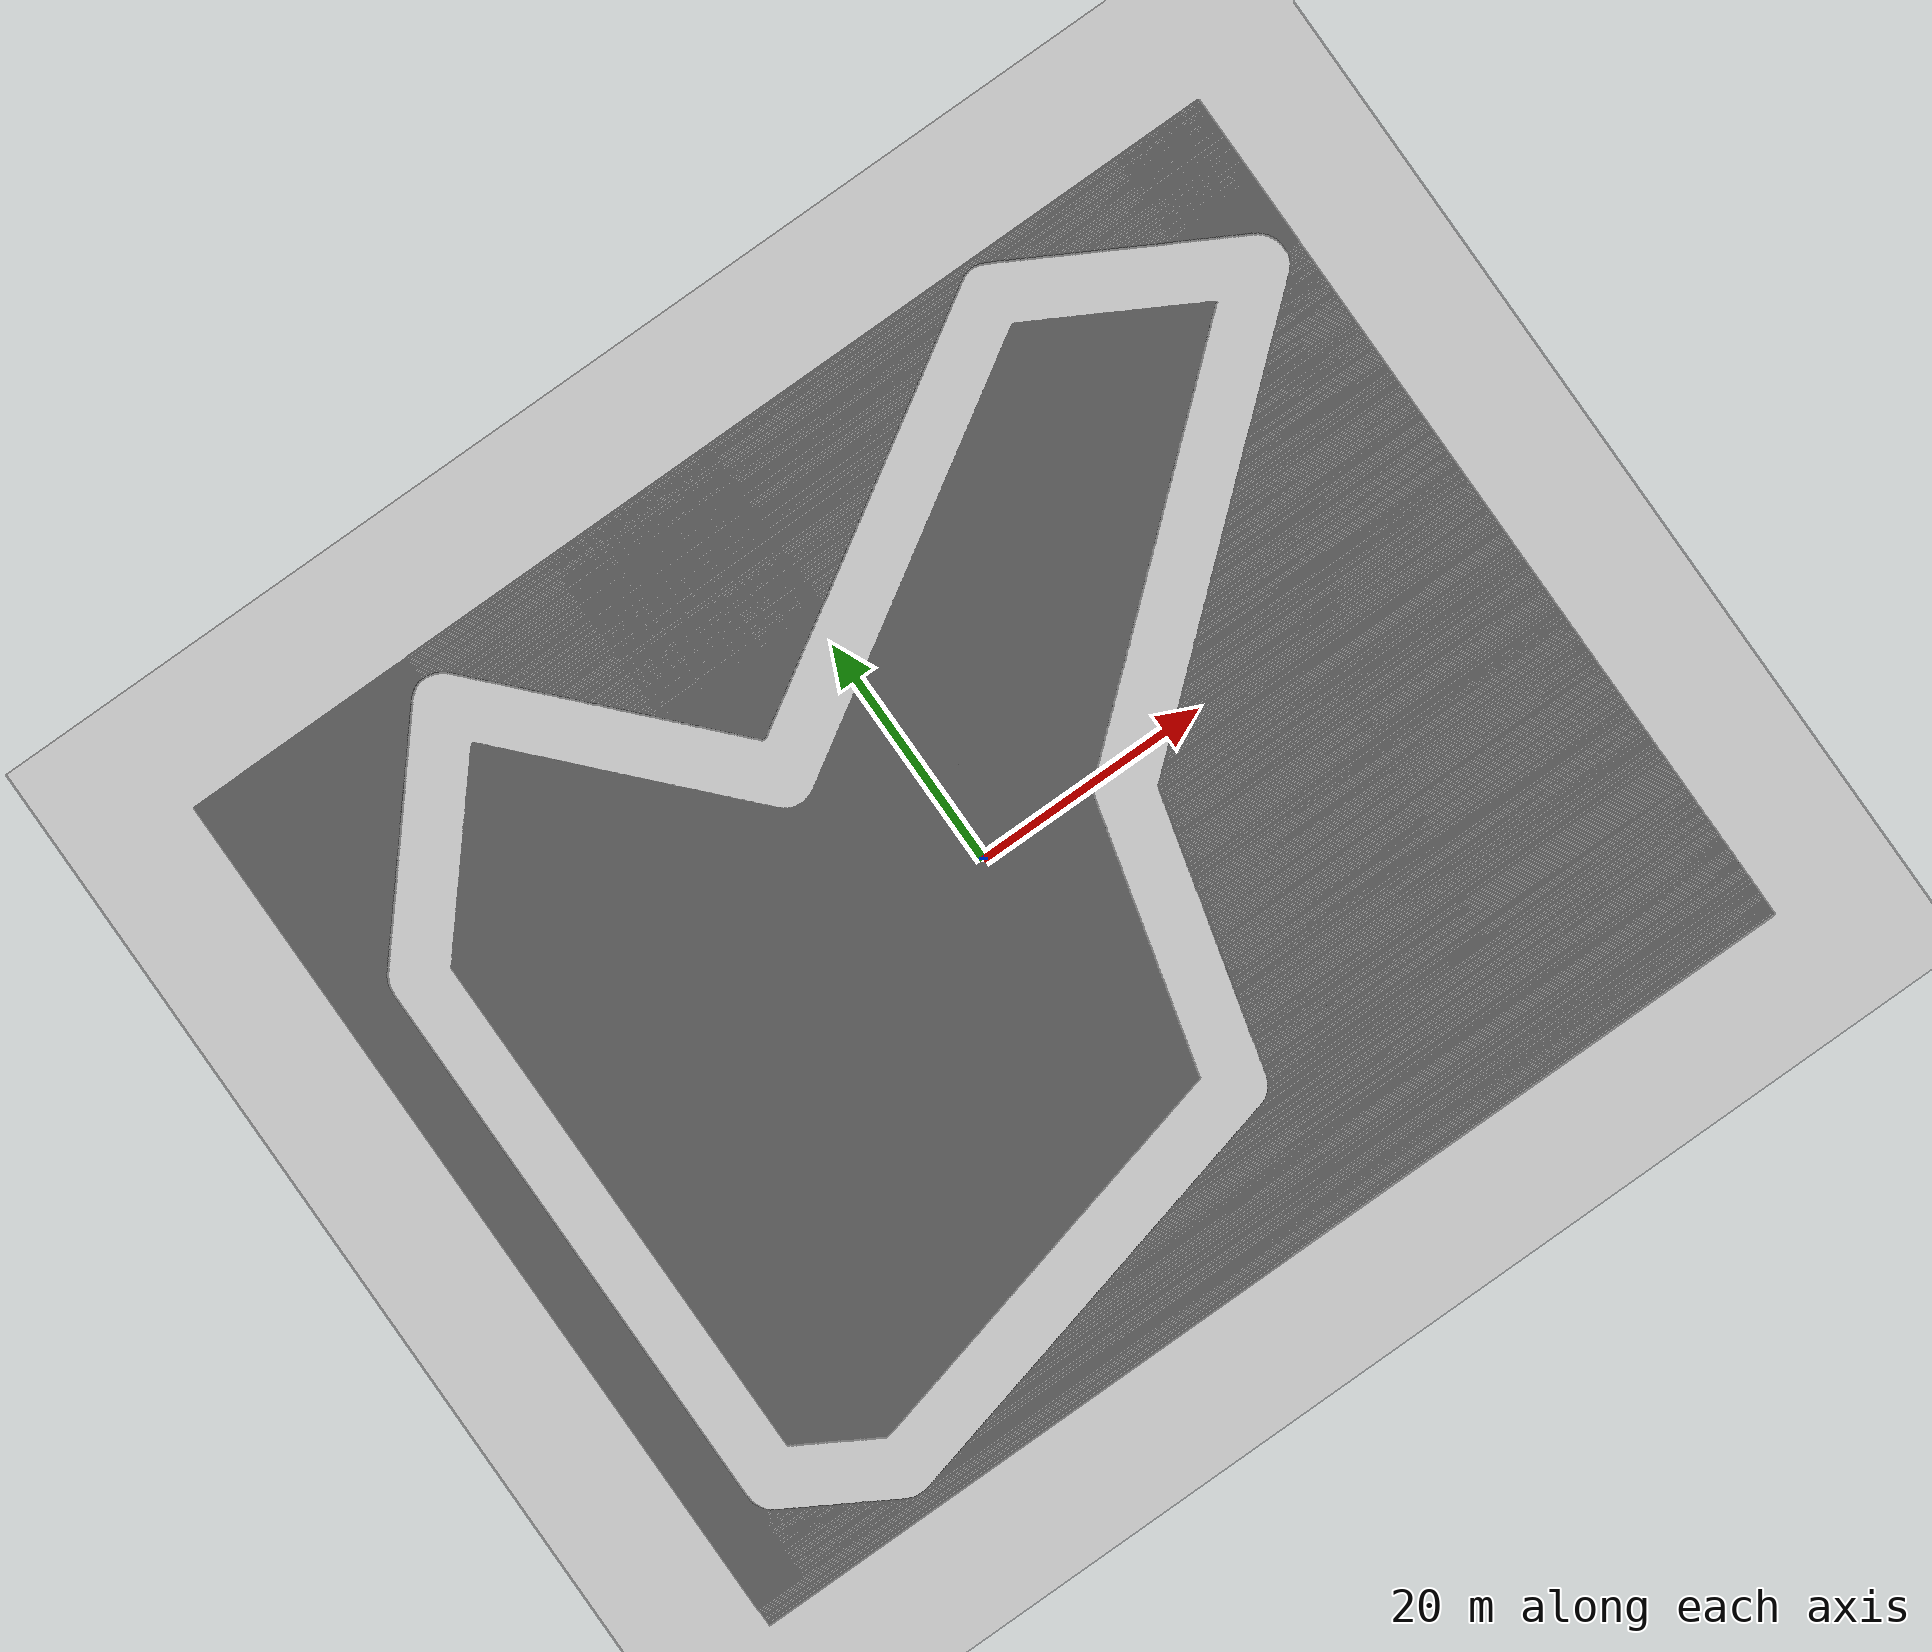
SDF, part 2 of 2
<script><uri>file://media/materials/scripts/gazebo.material</uri><name>Gazebo/Grey</name></script>
      <ambient>1 1 1 1</ambient>
     </material>
    </visual>
    <collision name="obstacle_2099">
     <pose>14.674999999999997 14.75 0 0 0 1.5708</pose>
     <geometry><box><size>21.700000000000003 0.15 1.0</size></box></geometry>
    </collision>
    <visual name="obstacle_2099">
     <pose>14.674999999999997 14.75 0 0 0 1.5708</pose>
     <geometry><box><size>21.700000000000003 0.15 1.0</size></box></geometry>
     <material>
      <script><uri>file://media/materials/scripts/gazebo.material</uri><name>Gazebo/Grey</name></script>
      <ambient>1 1 1 1</ambient>
     </material>
    </visual>
    <collision name="obstacle_2100">
     <pose>34.525000000000006 3.9000000000000057 0 0 0 0</pose>
     <geometry><box><size>24.5 0.15 1.0</size></box></geometry>
    </collision>
    <visual name="obstacle_2100">
     <pose>34.525000000000006 3.9000000000000057 0 0 0 0</pose>
     <geometry><box><size>24.5 0.15 1.0</size></box></geometry>
     <material>
      <script><uri>file://media/materials/scripts/gazebo.material</uri><name>Gazebo/Grey</name></script>
      <ambient>1 1 1 1</ambient>
     </material>
    </visual>
    <collision name="obstacle_2101">
     <pose>14.724999999999994 14.800000000000004 0 0 0 1.5708</pose>
     <geometry><box><size>21.700000000000003 0.15 1.0</size></box></geometry>
    </collision>
    <visual name="obstacle_2101">
     <pose>14.724999999999994 14.800000000000004 0 0 0 1.5708</pose>
     <geometry><box><size>21.700000000000003 0.15 1.0</size></box></geometry>
     <material>
      <script><uri>file://media/materials/scripts/gazebo.material</uri><name>Gazebo/Grey</name></script>
      <ambient>1 1 1 1</ambient>
     </material>
    </visual>
    <collision name="obstacle_2102">
     <pose>34.525000000000006 3.950000000000003 0 0 0 0</pose>
     <geometry><box><size>24.450000000000003 0.15 1.0</size></box></geometry>
    </collision>
    <visual name="obstacle_2102">
     <pose>34.525000000000006 3.950000000000003 0 0 0 0</pose>
     <geometry><box><size>24.450000000000003 0.15 1.0</size></box></geometry>
     <material>
      <script><uri>file://media/materials/scripts/gazebo.material</uri><name>Gazebo/Grey</name></script>
      <ambient>1 1 1 1</ambient>
     </material>
    </visual>
    <collision name="obstacle_2103">
     <pose>14.774999999999999 14.800000000000004 0 0 0 1.5708</pose>
     <geometry><box><size>21.650000000000002 0.15 1.0</size></box></geometry>
    </collision>
    <visual name="obstacle_2103">
     <pose>14.774999999999999 14.800000000000004 0 0 0 1.5708</pose>
     <geometry><box><size>21.650000000000002 0.15 1.0</size></box></geometry>
     <material>
      <script><uri>file://media/materials/scripts/gazebo.material</uri><name>Gazebo/Grey</name></script>
      <ambient>1 1 1 1</ambient>
     </material>
    </visual>
    <collision name="obstacle_2104">
     <pose>34.575 4.0 0 0 0 0</pose>
     <geometry><box><size>24.400000000000002 0.15 1.0</size></box></geometry>
    </collision>
    <visual name="obstacle_2104">
     <pose>34.575 4.0 0 0 0 0</pose>
     <geometry><box><size>24.400000000000002 0.15 1.0</size></box></geometry>
     <material>
      <script><uri>file://media/materials/scripts/gazebo.material</uri><name>Gazebo/Grey</name></script>
      <ambient>1 1 1 1</ambient>
     </material>
    </visual>
    <collision name="obstacle_2105">
     <pose>14.824999999999996 14.850000000000001 0 0 0 1.5708</pose>
     <geometry><box><size>21.650000000000002 0.15 1.0</size></box></geometry>
    </collision>
    <visual name="obstacle_2105">
     <pose>14.824999999999996 14.850000000000001 0 0 0 1.5708</pose>
     <geometry><box><size>21.650000000000002 0.15 1.0</size></box></geometry>
     <material>
      <script><uri>file://media/materials/scripts/gazebo.material</uri><name>Gazebo/Grey</name></script>
      <ambient>1 1 1 1</ambient>
     </material>
    </visual>
    <collision name="obstacle_2106">
     <pose>34.575 4.050000000000004 0 0 0 0</pose>
     <geometry><box><size>24.35 0.15 1.0</size></box></geometry>
    </collision>
    <visual name="obstacle_2106">
     <pose>34.575 4.050000000000004 0 0 0 0</pose>
     <geometry><box><size>24.35 0.15 1.0</size></box></geometry>
     <material>
      <script><uri>file://media/materials/scripts/gazebo.material</uri><name>Gazebo/Grey</name></script>
      <ambient>1 1 1 1</ambient>
     </material>
    </visual>
    <collision name="obstacle_2107">
     <pose>14.875 14.900000000000006 0 0 0 1.5708</pose>
     <geometry><box><size>21.650000000000002 0.15 1.0</size></box></geometry>
    </collision>
    <visual name="obstacle_2107">
     <pose>14.875 14.900000000000006 0 0 0 1.5708</pose>
     <geometry><box><size>21.650000000000002 0.15 1.0</size></box></geometry>
     <material>
      <script><uri>file://media/materials/scripts/gazebo.material</uri><name>Gazebo/Grey</name></script>
      <ambient>1 1 1 1</ambient>
     </material>
    </visual>
    <collision name="obstacle_2108">
     <pose>34.625 4.100000000000001 0 0 0 0</pose>
     <geometry><box><size>24.3 0.15 1.0</size></box></geometry>
    </collision>
    <visual name="obstacle_2108">
     <pose>34.625 4.100000000000001 0 0 0 0</pose>
     <geometry><box><size>24.3 0.15 1.0</size></box></geometry>
     <material>
      <script><uri>file://media/materials/scripts/gazebo.material</uri><name>Gazebo/Grey</name></script>
      <ambient>1 1 1 1</ambient>
     </material>
    </visual>
    <collision name="obstacle_2109">
     <pose>14.924999999999997 14.950000000000003 0 0 0 1.5708</pose>
     <geometry><box><size>21.6 0.15 1.0</size></box></geometry>
    </collision>
    <visual name="obstacle_2109">
     <pose>14.924999999999997 14.950000000000003 0 0 0 1.5708</pose>
     <geometry><box><size>21.6 0.15 1.0</size></box></geometry>
     <material>
      <script><uri>file://media/materials/scripts/gazebo.material</uri><name>Gazebo/Grey</name></script>
      <ambient>1 1 1 1</ambient>
     </material>
    </visual>
    <collision name="obstacle_2110">
     <pose>34.675 4.150000000000006 0 0 0 0</pose>
     <geometry><box><size>24.200000000000003 0.15 1.0</size></box></geometry>
    </collision>
    <visual name="obstacle_2110">
     <pose>34.675 4.150000000000006 0 0 0 0</pose>
     <geometry><box><size>24.200000000000003 0.15 1.0</size></box></geometry>
     <material>
      <script><uri>file://media/materials/scripts/gazebo.material</uri><name>Gazebo/Grey</name></script>
      <ambient>1 1 1 1</ambient>
     </material>
    </visual>
    <collision name="obstacle_2111">
     <pose>14.974999999999994 15.0 0 0 0 1.5708</pose>
     <geometry><box><size>21.6 0.15 1.0</size></box></geometry>
    </collision>
    <visual name="obstacle_2111">
     <pose>14.974999999999994 15.0 0 0 0 1.5708</pose>
     <geometry><box><size>21.6 0.15 1.0</size></box></geometry>
     <material>
      <script><uri>file://media/materials/scripts/gazebo.material</uri><name>Gazebo/Grey</name></script>
      <ambient>1 1 1 1</ambient>
     </material>
    </visual>
    <collision name="obstacle_2112">
     <pose>15.024999999999999 15.0 0 0 0 1.5708</pose>
     <geometry><box><size>21.650000000000002 0.15 1.0</size></box></geometry>
    </collision>
    <visual name="obstacle_2112">
     <pose>15.024999999999999 15.0 0 0 0 1.5708</pose>
     <geometry><box><size>21.650000000000002 0.15 1.0</size></box></geometry>
     <material>
      <script><uri>file://media/materials/scripts/gazebo.material</uri><name>Gazebo/Grey</name></script>
      <ambient>1 1 1 1</ambient>
     </material>
    </visual>
    <collision name="obstacle_2113">
     <pose>34.675 4.200000000000003 0 0 0 0</pose>
     <geometry><box><size>24.200000000000003 0.15 1.0</size></box></geometry>
    </collision>
    <visual name="obstacle_2113">
     <pose>34.675 4.200000000000003 0 0 0 0</pose>
     <geometry><box><size>24.200000000000003 0.15 1.0</size></box></geometry>
     <material>
      <script><uri>file://media/materials/scripts/gazebo.material</uri><name>Gazebo/Grey</name></script>
      <ambient>1 1 1 1</ambient>
     </material>
    </visual>
    <collision name="obstacle_2114">
     <pose>15.074999999999996 15.050000000000004 0 0 0 1.5708</pose>
     <geometry><box><size>21.6 0.15 1.0</size></box></geometry>
    </collision>
    <visual name="obstacle_2114">
     <pose>15.074999999999996 15.050000000000004 0 0 0 1.5708</pose>
     <geometry><box><size>21.6 0.15 1.0</size></box></geometry>
     <material>
      <script><uri>file://media/materials/scripts/gazebo.material</uri><name>Gazebo/Grey</name></script>
      <ambient>1 1 1 1</ambient>
     </material>
    </visual>
    <collision name="obstacle_2115">
     <pose>34.675 4.25 0 0 0 0</pose>
     <geometry><box><size>24.150000000000002 0.15 1.0</size></box></geometry>
    </collision>
    <visual name="obstacle_2115">
     <pose>34.675 4.25 0 0 0 0</pose>
     <geometry><box><size>24.150000000000002 0.15 1.0</size></box></geometry>
     <material>
      <script><uri>file://media/materials/scripts/gazebo.material</uri><name>Gazebo/Grey</name></script>
      <ambient>1 1 1 1</ambient>
     </material>
    </visual>
    <collision name="obstacle_2116">
     <pose>15.125 15.100000000000001 0 0 0 1.5708</pose>
     <geometry><box><size>21.6 0.15 1.0</size></box></geometry>
    </collision>
    <visual name="obstacle_2116">
     <pose>15.125 15.100000000000001 0 0 0 1.5708</pose>
     <geometry><box><size>21.6 0.15 1.0</size></box></geometry>
     <material>
      <script><uri>file://media/materials/scripts/gazebo.material</uri><name>Gazebo/Grey</name></script>
      <ambient>1 1 1 1</ambient>
     </material>
    </visual>
    <collision name="obstacle_2117">
     <pose>34.724999999999994 4.300000000000004 0 0 0 0</pose>
     <geometry><box><size>24.05 0.15 1.0</size></box></geometry>
    </collision>
    <visual name="obstacle_2117">
     <pose>34.724999999999994 4.300000000000004 0 0 0 0</pose>
     <geometry><box><size>24.05 0.15 1.0</size></box></geometry>
     <material>
      <script><uri>file://media/materials/scripts/gazebo.material</uri><name>Gazebo/Grey</name></script>
      <ambient>1 1 1 1</ambient>
     </material>
    </visual>
    <collision name="obstacle_2118">
     <pose>15.174999999999997 15.100000000000001 0 0 0 1.5708</pose>
     <geometry><box><size>21.55 0.15 1.0</size></box></geometry>
    </collision>
    <visual name="obstacle_2118">
     <pose>15.174999999999997 15.100000000000001 0 0 0 1.5708</pose>
     <geometry><box><size>21.55 0.15 1.0</size></box></geometry>
     <material>
      <script><uri>file://media/materials/scripts/gazebo.material</uri><name>Gazebo/Grey</name></script>
      <ambient>1 1 1 1</ambient>
     </material>
    </visual>
    <collision name="obstacle_2119">
     <pose>34.775000000000006 4.350000000000001 0 0 0 0</pose>
     <geometry><box><size>24.0 0.15 1.0</size></box></geometry>
    </collision>
    <visual name="obstacle_2119">
     <pose>34.775000000000006 4.350000000000001 0 0 0 0</pose>
     <geometry><box><size>24.0 0.15 1.0</size></box></geometry>
     <material>
      <script><uri>file://media/materials/scripts/gazebo.material</uri><name>Gazebo/Grey</name></script>
      <ambient>1 1 1 1</ambient>
     </material>
    </visual>
    <collision name="obstacle_2120">
     <pose>15.224999999999994 15.150000000000006 0 0 0 1.5708</pose>
     <geometry><box><size>21.55 0.15 1.0</size></box></geometry>
    </collision>
    <visual name="obstacle_2120">
     <pose>15.224999999999994 15.150000000000006 0 0 0 1.5708</pose>
     <geometry><box><size>21.55 0.15 1.0</size></box></geometry>
     <material>
      <script><uri>file://media/materials/scripts/gazebo.material</uri><name>Gazebo/Grey</name></script>
      <ambient>1 1 1 1</ambient>
     </material>
    </visual>
    <collision name="obstacle_2121">
     <pose>34.775000000000006 4.400000000000006 0 0 0 0</pose>
     <geometry><box><size>23.950000000000003 0.15 1.0</size></box></geometry>
    </collision>
    <visual name="obstacle_2121">
     <pose>34.775000000000006 4.400000000000006 0 0 0 0</pose>
     <geometry><box><size>23.950000000000003 0.15 1.0</size></box></geometry>
     <material>
      <script><uri>file://media/materials/scripts/gazebo.material</uri><name>Gazebo/Grey</name></script>
      <ambient>1 1 1 1</ambient>
     </material>
    </visual>
    <collision name="obstacle_2122">
     <pose>15.274999999999999 15.200000000000003 0 0 0 1.5708</pose>
     <geometry><box><size>21.55 0.15 1.0</size></box></geometry>
    </collision>
    <visual name="obstacle_2122">
     <pose>15.274999999999999 15.200000000000003 0 0 0 1.5708</pose>
     <geometry><box><size>21.55 0.15 1.0</size></box></geometry>
     <material>
      <script><uri>file://media/materials/scripts/gazebo.material</uri><name>Gazebo/Grey</name></script>
      <ambient>1 1 1 1</ambient>
     </material>
    </visual>
    <collision name="obstacle_2123">
     <pose>34.825 4.450000000000003 0 0 0 0</pose>
     <geometry><box><size>23.85 0.15 1.0</size></box></geometry>
    </collision>
    <visual name="obstacle_2123">
     <pose>34.825 4.450000000000003 0 0 0 0</pose>
     <geometry><box><size>23.85 0.15 1.0</size></box></geometry>
     <material>
      <script><uri>file://media/materials/scripts/gazebo.material</uri><name>Gazebo/Grey</name></script>
      <ambient>1 1 1 1</ambient>
     </material>
    </visual>
    <collision name="obstacle_2124">
     <pose>15.324999999999996 15.25 0 0 0 1.5708</pose>
     <geometry><box><size>21.5 0.15 1.0</size></box></geometry>
    </collision>
    <visual name="obstacle_2124">
     <pose>15.324999999999996 15.25 0 0 0 1.5708</pose>
     <geometry><box><size>21.5 0.15 1.0</size></box></geometry>
     <material>
      <script><uri>file://media/materials/scripts/gazebo.material</uri><name>Gazebo/Grey</name></script>
      <ambient>1 1 1 1</ambient>
     </material>
    </visual>
    <collision name="obstacle_2125">
     <pose>15.375 15.25 0 0 0 1.5708</pose>
     <geometry><box><size>21.55 0.15 1.0</size></box></geometry>
    </collision>
    <visual name="obstacle_2125">
     <pose>15.375 15.25 0 0 0 1.5708</pose>
     <geometry><box><size>21.55 0.15 1.0</size></box></geometry>
     <material>
      <script><uri>file://media/materials/scripts/gazebo.material</uri><name>Gazebo/Grey</name></script>
      <ambient>1 1 1 1</ambient>
     </material>
    </visual>
    <collision name="obstacle_2126">
     <pose>34.875 4.5 0 0 0 0</pose>
     <geometry><box><size>23.8 0.15 1.0</size></box></geometry>
    </collision>
    <visual name="obstacle_2126">
     <pose>34.875 4.5 0 0 0 0</pose>
     <geometry><box><size>23.8 0.15 1.0</size></box></geometry>
     <material>
      <script><uri>file://media/materials/scripts/gazebo.material</uri><name>Gazebo/Grey</name></script>
      <ambient>1 1 1 1</ambient>
     </material>
    </visual>
    <collision name="obstacle_2127">
     <pose>15.424999999999997 15.300000000000004 0 0 0 1.5708</pose>
     <geometry><box><size>21.5 0.15 1.0</size></box></geometry>
    </collision>
    <visual name="obstacle_2127">
     <pose>15.424999999999997 15.300000000000004 0 0 0 1.5708</pose>
     <geometry><box><size>21.5 0.15 1.0</size></box></geometry>
     <material>
      <script><uri>file://media/materials/scripts/gazebo.material</uri><name>Gazebo/Grey</name></script>
      <ambient>1 1 1 1</ambient>
     </material>
    </visual>
    <collision name="obstacle_2128">
     <pose>34.875 4.550000000000004 0 0 0 0</pose>
     <geometry><box><size>23.75 0.15 1.0</size></box></geometry>
    </collision>
    <visual name="obstacle_2128">
     <pose>34.875 4.550000000000004 0 0 0 0</pose>
     <geometry><box><size>23.75 0.15 1.0</size></box></geometry>
     <material>
      <script><uri>file://media/materials/scripts/gazebo.material</uri><name>Gazebo/Grey</name></script>
      <ambient>1 1 1 1</ambient>
     </material>
    </visual>
    <collision name="obstacle_2129">
     <pose>15.474999999999994 15.350000000000001 0 0 0 1.5708</pose>
     <geometry><box><size>21.5 0.15 1.0</size></box></geometry>
    </collision>
    <visual name="obstacle_2129">
     <pose>15.474999999999994 15.350000000000001 0 0 0 1.5708</pose>
     <geometry><box><size>21.5 0.15 1.0</size></box></geometry>
     <material>
      <script><uri>file://media/materials/scripts/gazebo.material</uri><name>Gazebo/Grey</name></script>
      <ambient>1 1 1 1</ambient>
     </material>
    </visual>
    <collision name="obstacle_2130">
     <pose>34.925 4.600000000000001 0 0 0 0</pose>
     <geometry><box><size>23.700000000000003 0.15 1.0</size></box></geometry>
    </collision>
    <visual name="obstacle_2130">
     <pose>34.925 4.600000000000001 0 0 0 0</pose>
     <geometry><box><size>23.700000000000003 0.15 1.0</size></box></geometry>
     <material>
      <script><uri>file://media/materials/scripts/gazebo.material</uri><name>Gazebo/Grey</name></script>
      <ambient>1 1 1 1</ambient>
     </material>
    </visual>
    <collision name="obstacle_2131">
     <pose>15.524999999999999 15.400000000000006 0 0 0 1.5708</pose>
     <geometry><box><size>21.5 0.15 1.0</size></box></geometry>
    </collision>
    <visual name="obstacle_2131">
     <pose>15.524999999999999 15.400000000000006 0 0 0 1.5708</pose>
     <geometry><box><size>21.5 0.15 1.0</size></box></geometry>
     <material>
      <script><uri>file://media/materials/scripts/gazebo.material</uri><name>Gazebo/Grey</name></script>
      <ambient>1 1 1 1</ambient>
     </material>
    </visual>
    <collision name="obstacle_2132">
     <pose>34.925 4.650000000000006 0 0 0 0</pose>
     <geometry><box><size>23.650000000000002 0.15 1.0</size></box></geometry>
    </collision>
    <visual name="obstacle_2132">
     <pose>34.925 4.650000000000006 0 0 0 0</pose>
     <geometry><box><size>23.650000000000002 0.15 1.0</size></box></geometry>
     <material>
      <script><uri>file://media/materials/scripts/gazebo.material</uri><name>Gazebo/Grey</name></script>
      <ambient>1 1 1 1</ambient>
     </material>
    </visual>
    <collision name="obstacle_2133">
     <pose>15.574999999999996 15.400000000000006 0 0 0 1.5708</pose>
     <geometry><box><size>21.450000000000003 0.15 1.0</size></box></geometry>
    </collision>
    <visual name="obstacle_2133">
     <pose>15.574999999999996 15.400000000000006 0 0 0 1.5708</pose>
     <geometry><box><size>21.450000000000003 0.15 1.0</size></box></geometry>
     <material>
      <script><uri>file://media/materials/scripts/gazebo.material</uri><name>Gazebo/Grey</name></script>
      <ambient>1 1 1 1</ambient>
     </material>
    </visual>
    <collision name="obstacle_2134">
     <pose>34.974999999999994 4.700000000000003 0 0 0 0</pose>
     <geometry><box><size>23.55 0.15 1.0</size></box></geometry>
    </collision>
    <visual name="obstacle_2134">
     <pose>34.974999999999994 4.700000000000003 0 0 0 0</pose>
     <geometry><box><size>23.55 0.15 1.0</size></box></geometry>
     <material>
      <script><uri>file://media/materials/scripts/gazebo.material</uri><name>Gazebo/Grey</name></script>
      <ambient>1 1 1 1</ambient>
     </material>
    </visual>
    <collision name="obstacle_2135">
     <pose>15.625 15.450000000000003 0 0 0 1.5708</pose>
     <geometry><box><size>21.450000000000003 0.15 1.0</size></box></geometry>
    </collision>
    <visual name="obstacle_2135">
     <pose>15.625 15.450000000000003 0 0 0 1.5708</pose>
     <geometry><box><size>21.450000000000003 0.15 1.0</size></box></geometry>
     <material>
      <script><uri>file://media/materials/scripts/gazebo.material</uri><name>Gazebo/Grey</name></script>
      <ambient>1 1 1 1</ambient>
     </material>
    </visual>
    <collision name="obstacle_2136">
     <pose>35.025000000000006 4.75 0 0 0 0</pose>
     <geometry><box><size>23.5 0.15 1.0</size></box></geometry>
    </collision>
    <visual name="obstacle_2136">
     <pose>35.025000000000006 4.75 0 0 0 0</pose>
     <geometry><box><size>23.5 0.15 1.0</size></box></geometry>
     <material>
      <script><uri>file://media/materials/scripts/gazebo.material</uri><name>Gazebo/Grey</name></script>
      <ambient>1 1 1 1</ambient>
     </material>
    </visual>
    <collision name="obstacle_2137">
     <pose>15.674999999999997 15.5 0 0 0 1.5708</pose>
     <geometry><box><size>21.450000000000003 0.15 1.0</size></box></geometry>
    </collision>
    <visual name="obstacle_2137">
     <pose>15.674999999999997 15.5 0 0 0 1.5708</pose>
     <geometry><box><size>21.450000000000003 0.15 1.0</size></box></geometry>
     <material>
      <script><uri>file://media/materials/scripts/gazebo.material</uri><name>Gazebo/Grey</name></script>
      <ambient>1 1 1 1</ambient>
     </material>
    </visual>
    <collision name="obstacle_2138">
     <pose>15.724999999999994 15.5 0 0 0 1.5708</pose>
     <geometry><box><size>21.450000000000003 0.15 1.0</size></box></geometry>
    </collision>
    <visual name="obstacle_2138">
     <pose>15.724999999999994 15.5 0 0 0 1.5708</pose>
     <geometry><box><size>21.450000000000003 0.15 1.0</size></box></geometry>
     <material>
      <script><uri>file://media/materials/scripts/gazebo.material</uri><name>Gazebo/Grey</name></script>
      <ambient>1 1 1 1</ambient>
     </material>
    </visual>
    <collision name="obstacle_2139">
     <pose>35.025000000000006 4.800000000000004 0 0 0 0</pose>
     <geometry><box><size>23.450000000000003 0.15 1.0</size></box></geometry>
    </collision>
    <visual name="obstacle_2139">
     <pose>35.025000000000006 4.800000000000004 0 0 0 0</pose>
     <geometry><box><size>23.450000000000003 0.15 1.0</size></box></geometry>
     <material>
      <script><uri>file://media/materials/scripts/gazebo.material</uri><name>Gazebo/Grey</name></script>
      <ambient>1 1 1 1</ambient>
     </material>
    </visual>
    <collision name="obstacle_2140">
     <pose>15.774999999999999 15.550000000000004 0 0 0 1.5708</pose>
     <geometry><box><size>21.450000000000003 0.15 1.0</size></box></geometry>
    </collision>
    <visual name="obstacle_2140">
     <pose>15.774999999999999 15.550000000000004 0 0 0 1.5708</pose>
     <geometry><box><size>21.450000000000003 0.15 1.0</size></box></geometry>
     <material>
      <script><uri>file://media/materials/scripts/gazebo.material</uri><name>Gazebo/Grey</name></script>
      <ambient>1 1 1 1</ambient>
     </material>
    </visual>
    <collision name="obstacle_2141">
     <pose>35.075 4.850000000000001 0 0 0 0</pose>
     <geometry><box><size>23.400000000000002 0.15 1.0</size></box></geometry>
    </collision>
    <visual name="obstacle_2141">
     <pose>35.075 4.850000000000001 0 0 0 0</pose>
     <geometry><box><size>23.400000000000002 0.15 1.0</size></box></geometry>
     <material>
      <script><uri>file://media/materials/scripts/gazebo.material</uri><name>Gazebo/Grey</name></script>
      <ambient>1 1 1 1</ambient>
     </material>
    </visual>
    <collision name="obstacle_2142">
     <pose>15.824999999999996 15.600000000000001 0 0 0 1.5708</pose>
     <geometry><box><size>21.400000000000002 0.15 1.0</size></box></geometry>
    </collision>
    <visual name="obstacle_2142">
     <pose>15.824999999999996 15.600000000000001 0 0 0 1.5708</pose>
     <geometry><box><size>21.400000000000002 0.15 1.0</size></box></geometry>
     <material>
      <script><uri>file://media/materials/scripts/gazebo.material</uri><name>Gazebo/Grey</name></script>
      <ambient>1 1 1 1</ambient>
     </material>
    </visual>
    <collision name="obstacle_2143">
     <pose>35.075 4.900000000000006 0 0 0 0</pose>
     <geometry><box><size>23.35 0.15 1.0</size></box></geometry>
    </collision>
    <visual name="obstacle_2143">
     <pose>35.075 4.900000000000006 0 0 0 0</pose>
     <geometry><box><size>23.35 0.15 1.0</size></box></geometry>
     <material>
      <script><uri>file://media/materials/scripts/gazebo.material</uri><name>Gazebo/Grey</name></script>
      <ambient>1 1 1 1</ambient>
     </material>
    </visual>
    <collision name="obstacle_2144">
     <pose>15.875 15.650000000000006 0 0 0 1.5708</pose>
     <geometry><box><size>21.400000000000002 0.15 1.0</size></box></geometry>
    </collision>
    <visual name="obstacle_2144">
     <pose>15.875 15.650000000000006 0 0 0 1.5708</pose>
     <geometry><box><size>21.400000000000002 0.15 1.0</size></box></geometry>
     <material>
      <script><uri>file://media/materials/scripts/gazebo.material</uri><name>Gazebo/Grey</name></script>
      <ambient>1 1 1 1</ambient>
     </material>
    </visual>
    <collision name="obstacle_2145">
     <pose>35.125 4.950000000000003 0 0 0 0</pose>
     <geometry><box><size>23.3 0.15 1.0</size></box></geometry>
    </collision>
    <visual name="obstacle_2145">
     <pose>35.125 4.950000000000003 0 0 0 0</pose>
     <geometry><box><size>23.3 0.15 1.0</size></box></geometry>
     <material>
      <script><uri>file://media/materials/scripts/gazebo.material</uri><name>Gazebo/Grey</name></script>
      <ambient>1 1 1 1</ambient>
     </material>
    </visual>
    <collision name="obstacle_2146">
     <pose>15.924999999999997 15.700000000000003 0 0 0 1.5708</pose>
     <geometry><box><size>21.400000000000002 0.15 1.0</size></box></geometry>
    </collision>
    <visual name="obstacle_2146">
     <pose>15.924999999999997 15.700000000000003 0 0 0 1.5708</pose>
     <geometry><box><size>21.400000000000002 0.15 1.0</size></box></geometry>
     <material>
      <script><uri>file://media/materials/scripts/gazebo.material</uri><name>Gazebo/Grey</name></script>
      <ambient>1 1 1 1</ambient>
     </material>
    </visual>
    <collision name="obstacle_2147">
     <pose>15.974999999999994 15.700000000000003 0 0 0 1.5708</pose>
     <geometry><box><size>21.400000000000002 0.15 1.0</size></box></geometry>
    </collision>
    <visual name="obstacle_2147">
     <pose>15.974999999999994 15.700000000000003 0 0 0 1.5708</pose>
     <geometry><box><size>21.400000000000002 0.15 1.0</size></box></geometry>
     <material>
      <script><uri>file://media/materials/scripts/gazebo.material</uri><name>Gazebo/Grey</name></script>
      <ambient>1 1 1 1</ambient>
     </material>
    </visual>
    <collision name="obstacle_2148">
     <pose>35.125 5.0 0 0 0 0</pose>
     <geometry><box><size>23.25 0.15 1.0</size></box></geometry>
    </collision>
    <visual name="obstacle_2148">
     <pose>35.125 5.0 0 0 0 0</pose>
     <geometry><box><size>23.25 0.15 1.0</size></box></geometry>
     <material>
      <script><uri>file://media/materials/scripts/gazebo.material</uri><name>Gazebo/Grey</name></script>
      <ambient>1 1 1 1</ambient>
     </material>
    </visual>
    <collision name="obstacle_2149">
     <pose>16.025 15.75 0 0 0 1.5708</pose>
     <geometry><box><size>21.400000000000002 0.15 1.0</size></box></geometry>
    </collision>
    <visual name="obstacle_2149">
     <pose>16.025 15.75 0 0 0 1.5708</pose>
     <geometry><box><size>21.400000000000002 0.15 1.0</size></box></geometry>
     <material>
      <script><uri>file://media/materials/scripts/gazebo.material</uri><name>Gazebo/Grey</name></script>
      <ambient>1 1 1 1</ambient>
     </material>
    </visual>
    <collision name="obstacle_2150">
     <pose>35.175 5.050000000000004 0 0 0 0</pose>
     <geometry><box><size>23.200000000000003 0.15 1.0</size></box></geometry>
    </collision>
    <visual name="obstacle_2150">
     <pose>35.175 5.050000000000004 0 0 0 0</pose>
     <geometry><box><size>23.200000000000003 0.15 1.0</size></box></geometry>
     <material>
      <script><uri>file://media/materials/scripts/gazebo.material</uri><name>Gazebo/Grey</name></script>
      <ambient>1 1 1 1</ambient>
     </material>
    </visual>
    <collision name="obstacle_2151">
     <pose>16.074999999999996 15.75 0 0 0 1.5708</pose>
     <geometry><box><size>21.35 0.15 1.0</size></box></geometry>
    </collision>
    <visual name="obstacle_2151">
     <pose>16.074999999999996 15.75 0 0 0 1.5708</pose>
     <geometry><box><size>21.35 0.15 1.0</size></box></geometry>
     <material>
      <script><uri>file://media/materials/scripts/gazebo.material</uri><name>Gazebo/Grey</name></script>
      <ambient>1 1 1 1</ambient>
     </material>
    </visual>
    <collision name="obstacle_2152">
     <pose>35.224999999999994 5.100000000000001 0 0 0 0</pose>
     <geometry><box><size>23.1 0.15 1.0</size></box></geometry>
    </collision>
    <visual name="obstacle_2152">
     <pose>35.224999999999994 5.100000000000001 0 0 0 0</pose>
     <geometry><box><size>23.1 0.15 1.0</size></box></geometry>
     <material>
      <script><uri>file://media/materials/scripts/gazebo.material</uri><name>Gazebo/Grey</name></script>
      <ambient>1 1 1 1</ambient>
     </material>
    </visual>
    <collision name="obstacle_2153">
     <pose>16.125 15.800000000000004 0 0 0 1.5708</pose>
     <geometry><box><size>21.35 0.15 1.0</size></box></geometry>
    </collision>
    <visual name="obstacle_2153">
     <pose>16.125 15.800000000000004 0 0 0 1.5708</pose>
     <geometry><box><size>21.35 0.15 1.0</size></box></geometry>
     <material>
      <script><uri>file://media/materials/scripts/gazebo.material</uri><name>Gazebo/Grey</name></script>
      <ambient>1 1 1 1</ambient>
     </material>
    </visual>
    <collision name="obstacle_2154">
     <pose>35.224999999999994 5.150000000000006 0 0 0 0</pose>
     <geometry><box><size>23.05 0.15 1.0</size></box></geometry>
    </collision>
    <visual name="obstacle_2154">
     <pose>35.224999999999994 5.150000000000006 0 0 0 0</pose>
     <geometry><box><size>23.05 0.15 1.0</size></box></geometry>
     <material>
      <script><uri>file://media/materials/scripts/gazebo.material</uri><name>Gazebo/Grey</name></script>
      <ambient>1 1 1 1</ambient>
     </material>
    </visual>
    <collision name="obstacle_2155">
     <pose>16.174999999999997 15.850000000000001 0 0 0 1.5708</pose>
     <geometry><box><size>21.35 0.15 1.0</size></box></geometry>
    </collision>
    <visual name="obstacle_2155">
     <pose>16.174999999999997 15.850000000000001 0 0 0 1.5708</pose>
     <geometry><box><size>21.35 0.15 1.0</size></box></geometry>
     <material>
      <script><uri>file://media/materials/scripts/gazebo.material</uri><name>Gazebo/Grey</name></script>
      <ambient>1 1 1 1</ambient>
     </material>
    </visual>
    <collision name="obstacle_2156">
     <pose>35.275000000000006 5.200000000000003 0 0 0 0</pose>
     <geometry><box><size>23.0 0.15 1.0</size></box></geometry>
    </collision>
    <visual name="obstacle_2156">
     <pose>35.275000000000006 5.200000000000003 0 0 0 0</pose>
     <geometry><box><size>23.0 0.15 1.0</size></box></geometry>
     <material>
      <script><uri>file://media/materials/scripts/gazebo.material</uri><name>Gazebo/Grey</name></script>
      <ambient>1 1 1 1</ambient>
     </material>
    </visual>
    <collision name="obstacle_2157">
     <pose>16.224999999999994 15.900000000000006 0 0 0 1.5708</pose>
     <geometry><box><size>21.3 0.15 1.0</size></box></geometry>
    </collision>
    <visual name="obstacle_2157">
     <pose>16.224999999999994 15.900000000000006 0 0 0 1.5708</pose>
     <geometry><box><size>21.3 0.15 1.0</size></box></geometry>
     <material>
      <script><uri>file://media/materials/scripts/gazebo.material</uri><name>Gazebo/Grey</name></script>
      <ambient>1 1 1 1</ambient>
     </material>
    </visual>
    <collision name="obstacle_2158">
     <pose>35.275000000000006 5.25 0 0 0 0</pose>
     <geometry><box><size>22.950000000000003 0.15 1.0</size></box></geometry>
    </collision>
    <visual name="obstacle_2158">
     <pose>35.275000000000006 5.25 0 0 0 0</pose>
     <geometry><box><size>22.950000000000003 0.15 1.0</size></box></geometry>
     <material>
      <script><uri>file://media/materials/scripts/gazebo.material</uri><name>Gazebo/Grey</name></script>
      <ambient>1 1 1 1</ambient>
     </material>
    </visual>
    <collision name="obstacle_2159">
     <pose>16.275 15.950000000000003 0 0 0 1.5708</pose>
     <geometry><box><size>21.3 0.15 1.0</size></box></geometry>
    </collision>
    <visual name="obstacle_2159">
     <pose>16.275 15.950000000000003 0 0 0 1.5708</pose>
     <geometry><box><size>21.3 0.15 1.0</size></box></geometry>
     <material>
      <script><uri>file://media/materials/scripts/gazebo.material</uri><name>Gazebo/Grey</name></script>
      <ambient>1 1 1 1</ambient>
     </material>
    </visual>
    <collision name="obstacle_2160">
     <pose>35.325 5.300000000000004 0 0 0 0</pose>
     <geometry><box><size>22.85 0.15 1.0</size></box></geometry>
    </collision>
    <visual name="obstacle_2160">
     <pose>35.325 5.300000000000004 0 0 0 0</pose>
     <geometry><box><size>22.85 0.15 1.0</size></box></geometry>
     <material>
      <script><uri>file://media/materials/scripts/gazebo.material</uri><name>Gazebo/Grey</name></script>
      <ambient>1 1 1 1</ambient>
     </material>
    </visual>
    <collision name="obstacle_2161">
     <pose>16.324999999999996 16.0 0 0 0 1.5708</pose>
     <geometry><box><size>21.3 0.15 1.0</size></box></geometry>
    </collision>
    <visual name="obstacle_2161">
     <pose>16.324999999999996 16.0 0 0 0 1.5708</pose>
     <geometry><box><size>21.3 0.15 1.0</size></box></geometry>
     <material>
      <script><uri>file://media/materials/scripts/gazebo.material</uri><name>Gazebo/Grey</name></script>
      <ambient>1 1 1 1</ambient>
     </material>
    </visual>
    <collision name="obstacle_2162">
     <pose>16.375 16.0 0 0 0 1.5708</pose>
     <geometry><box><size>21.3 0.15 1.0</size></box></geometry>
    </collision>
    <visual name="obstacle_2162">
     <pose>16.375 16.0 0 0 0 1.5708</pose>
     <geometry><box><size>21.3 0.15 1.0</size></box></geometry>
     <material>
      <script><uri>file://media/materials/scripts/gazebo.material</uri><name>Gazebo/Grey</name></script>
      <ambient>1 1 1 1</ambient>
     </material>
    </visual>
    <collision name="obstacle_2163">
     <pose>35.375 5.350000000000001 0 0 0 0</pose>
     <geometry><box><size>22.8 0.15 1.0</size></box></geometry>
    </collision>
    <visual name="obstacle_2163">
     <pose>35.375 5.350000000000001 0 0 0 0</pose>
     <geometry><box><size>22.8 0.15 1.0</size></box></geometry>
     <material>
      <script><uri>file://media/materials/scripts/gazebo.material</uri><name>Gazebo/Grey</name></script>
      <ambient>1 1 1 1</ambient>
     </material>
    </visual>
    <collision name="obstacle_2164">
     <pose>16.424999999999997 16.050000000000004 0 0 0 1.5708</pose>
     <geometry><box><size>21.3 0.15 1.0</size></box></geometry>
    </collision>
    <visual name="obstacle_2164">
     <pose>16.424999999999997 16.050000000000004 0 0 0 1.5708</pose>
     <geometry><box><size>21.3 0.15 1.0</size></box></geometry>
     <material>
      <script><uri>file://media/materials/scripts/gazebo.material</uri><name>Gazebo/Grey</name></script>
      <ambient>1 1 1 1</ambient>
     </material>
    </visual>
    <collision name="obstacle_2165">
     <pose>35.375 5.400000000000006 0 0 0 0</pose>
     <geometry><box><size>22.75 0.15 1.0</size></box></geometry>
    </collision>
    <visual name="obstacle_2165">
     <pose>35.375 5.400000000000006 0 0 0 0</pose>
     <geometry><box><size>22.75 0.15 1.0</size></box></geometry>
     <material>
      <script><uri>file://media/materials/scripts/gazebo.material</uri><name>Gazebo/Grey</name></script>
      <ambient>1 1 1 1</ambient>
     </material>
    </visual>
    <collision name="obstacle_2166">
     <pose>16.474999999999994 16.050000000000004 0 0 0 1.5708</pose>
     <geometry><box><size>21.25 0.15 1.0</size></box></geometry>
    </collision>
    <visual name="obstacle_2166">
     <pose>16.474999999999994 16.050000000000004 0 0 0 1.5708</pose>
     <geometry><box><size>21.25 0.15 1.0</size></box></geometry>
     <material>
      <script><uri>file://media/materials/scripts/gazebo.material</uri><name>Gazebo/Grey</name></script>
      <ambient>1 1 1 1</ambient>
     </material>
    </visual>
    <collision name="obstacle_2167">
     <pose>35.425 5.450000000000003 0 0 0 0</pose>
     <geometry><box><size>22.700000000000003 0.15 1.0</size></box></geometry>
    </collision>
    <visual name="obstacle_2167">
     <pose>35.425 5.450000000000003 0 0 0 0</pose>
     <geometry><box><size>22.700000000000003 0.15 1.0</size></box></geometry>
     <material>
      <script><uri>file://media/materials/scripts/gazebo.material</uri><name>Gazebo/Grey</name></script>
      <ambient>1 1 1 1</ambient>
     </material>
    </visual>
    <collision name="obstacle_2168">
     <pose>16.525 16.1 0 0 0 1.5708</pose>
     <geometry><box><size>21.25 0.15 1.0</size></box></geometry>
    </collision>
    <visual name="obstacle_2168">
     <pose>16.525 16.1 0 0 0 1.5708</pose>
     <geometry><box><size>21.25 0.15 1.0</size></box></geometry>
     <material>
      <script><uri>file://media/materials/scripts/gazebo.material</uri><name>Gazebo/Grey</name></script>
      <ambient>1 1 1 1</ambient>
     </material>
    </visual>
    <collision name="obstacle_2169">
     <pose>35.425 5.5 0 0 0 0</pose>
     <geometry><box><size>22.650000000000002 0.15 1.0</size></box></geometry>
    </collision>
    <visual name="obstacle_2169">
     <pose>35.425 5.5 0 0 0 0</pose>
     <geometry><box><size>22.650000000000002 0.15 1.0</size></box></geometry>
     <material>
      <script><uri>file://media/materials/scripts/gazebo.material</uri><name>Gazebo/Grey</name></script>
      <ambient>1 1 1 1</ambient>
     </material>
    </visual>
    <collision name="obstacle_2170">
     <pose>16.574999999999996 16.150000000000006 0 0 0 1.5708</pose>
     <geometry><box><size>21.25 0.15 1.0</size></box></geometry>
    </collision>
    <visual name="obstacle_2170">
     <pose>16.574999999999996 16.150000000000006 0 0 0 1.5708</pose>
     <geometry><box><size>21.25 0.15 1.0</size></box></geometry>
     <material>
      <script><uri>file://media/materials/scripts/gazebo.material</uri><name>Gazebo/Grey</name></script>
      <ambient>1 1 1 1</ambient>
     </material>
    </visual>
    <collision name="obstacle_2171">
     <pose>35.474999999999994 5.550000000000004 0 0 0 0</pose>
     <geometry><box><size>22.6 0.15 1.0</size></box></geometry>
    </collision>
    <visual name="obstacle_2171">
     <pose>35.474999999999994 5.550000000000004 0 0 0 0</pose>
     <geometry><box><size>22.6 0.15 1.0</size></box></geometry>
     <material>
      <script><uri>file://media/materials/scripts/gazebo.material</uri><name>Gazebo/Grey</name></script>
      <ambient>1 1 1 1</ambient>
     </material>
    </visual>
    <collision name="obstacle_2172">
     <pose>16.625 16.200000000000003 0 0 0 1.5708</pose>
     <geometry><box><size>21.200000000000003 0.15 1.0</size></box></geometry>
    </collision>
    <visual name="obstacle_2172">
     <pose>16.625 16.200000000000003 0 0 0 1.5708</pose>
     <geometry><box><size>21.200000000000003 0.15 1.0</size></box></geometry>
     <material>
      <script><uri>file://media/materials/scripts/gazebo.material</uri><name>Gazebo/Grey</name></script>
      <ambient>1 1 1 1</ambient>
     </material>
    </visual>
    <collision name="obstacle_2173">
     <pose>35.525000000000006 5.600000000000001 0 0 0 0</pose>
     <geometry><box><size>22.5 0.15 1.0</size></box></geometry>
    </collision>
    <visual name="obstacle_2173">
     <pose>35.525000000000006 5.600000000000001 0 0 0 0</pose>
     <geometry><box><size>22.5 0.15 1.0</size></box></geometry>
     <material>
      <script><uri>file://media/materials/scripts/gazebo.material</uri><name>Gazebo/Grey</name></script>
      <ambient>1 1 1 1</ambient>
     </material>
    </visual>
    <collision name="obstacle_2174">
     <pose>16.674999999999997 16.25 0 0 0 1.5708</pose>
     <geometry><box><size>21.200000000000003 0.15 1.0</size></box></geometry>
    </collision>
    <visual name="obstacle_2174">
     <pose>16.674999999999997 16.25 0 0 0 1.5708</pose>
     <geometry><box><size>21.200000000000003 0.15 1.0</size></box></geometry>
     <material>
      <script><uri>file://media/materials/scripts/gazebo.material</uri><name>Gazebo/Grey</name></script>
      <ambient>1 1 1 1</ambient>
     </material>
    </visual>
    <collision name="obstacle_2175">
     <pose>16.724999999999994 16.25 0 0 0 1.5708</pose>
     <geometry><box><size>21.200000000000003 0.15 1.0</size></box></geometry>
    </collision>
    <visual name="obstacle_2175">
     <pose>16.724999999999994 16.25 0 0 0 1.5708</pose>
     <geometry><box><size>21.200000000000003 0.15 1.0</size></box></geometry>
     <material>
      <script><uri>file://media/materials/scripts/gazebo.material</uri><name>Gazebo/Grey</name></script>
      <ambient>1 1 1 1</ambient>
     </material>
    </visual>
    <collision name="obstacle_2176">
     <pose>35.525000000000006 5.650000000000006 0 0 0 0</pose>
     <geometry><box><size>22.450000000000003 0.15 1.0</size></box></geometry>
    </collision>
    <visual name="obstacle_2176">
     <pose>35.525000000000006 5.650000000000006 0 0 0 0</pose>
     <geometry><box><size>22.450000000000003 0.15 1.0</size></box></geometry>
     <material>
      <script><uri>file://media/materials/scripts/gazebo.material</uri><name>Gazebo/Grey</name></script>
      <ambient>1 1 1 1</ambient>
     </material>
    </visual>
    <collision name="obstacle_2177">
     <pose>16.775 16.300000000000004 0 0 0 1.5708</pose>
     <geometry><box><size>21.200000000000003 0.15 1.0</size></box></geometry>
    </collision>
    <visual name="obstacle_2177">
     <pose>16.775 16.300000000000004 0 0 0 1.5708</pose>
     <geometry><box><size>21.200000000000003 0.15 1.0</size></box></geometry>
     <material>
      <script><uri>file://media/materials/scripts/gazebo.material</uri><name>Gazebo/Grey</name></script>
      <ambient>1 1 1 1</ambient>
     </material>
    </visual>
    <collision name="obstacle_2178">
     <pose>35.575 5.700000000000003 0 0 0 0</pose>
     <geometry><box><size>22.400000000000002 0.15 1.0</size></box></geometry>
    </collision>
    <visual name="obstacle_2178">
     <pose>35.575 5.700000000000003 0 0 0 0</pose>
     <geometry><box><size>22.400000000000002 0.15 1.0</size></box></geometry>
     <material>
      <script><uri>file://media/materials/scripts/gazebo.material</uri><name>Gazebo/Grey</name></script>
      <ambient>1 1 1 1</ambient>
     </material>
    </visual>
    <collision name="obstacle_2179">
     <pose>16.824999999999996 16.35 0 0 0 1.5708</pose>
     <geometry><box><size>21.200000000000003 0.15 1.0</size></box></geometry>
    </collision>
    <visual name="obstacle_2179">
     <pose>16.824999999999996 16.35 0 0 0 1.5708</pose>
     <geometry><box><size>21.200000000000003 0.15 1.0</size></box></geometry>
     <material>
      <script><uri>file://media/materials/scripts/gazebo.material</uri><name>Gazebo/Grey</name></script>
      <ambient>1 1 1 1</ambient>
     </material>
    </visual>
    <collision name="obstacle_2180">
     <pose>35.575 5.75 0 0 0 0</pose>
     <geometry><box><size>22.35 0.15 1.0</size></box></geometry>
    </collision>
    <visual name="obstacle_2180">
     <pose>35.575 5.75 0 0 0 0</pose>
     <geometry><box><size>22.35 0.15 1.0</size></box></geometry>
     <material>
      <script><uri>file://media/materials/scripts/gazebo.material</uri><name>Gazebo/Grey</name></script>
      <ambient>1 1 1 1</ambient>
     </material>
    </visual>
    <collision name="obstacle_2181">
     <pose>16.875 16.35 0 0 0 1.5708</pose>
     <geometry><box><size>21.150000000000002 0.15 1.0</size></box></geometry>
    </collision>
    <visual name="obstacle_2181">
     <pose>16.875 16.35 0 0 0 1.5708</pose>
     <geometry><box><size>21.150000000000002 0.15 1.0</size></box></geometry>
     <material>
      <script><uri>file://media/materials/scripts/gazebo.material</uri><name>Gazebo/Grey</name></script>
      <ambient>1 1 1 1</ambient>
     </material>
    </visual>
    <collision name="obstacle_2182">
     <pose>35.625 5.800000000000004 0 0 0 0</pose>
     <geometry><box><size>22.3 0.15 1.0</size></box></geometry>
    </collision>
    <visual name="obstacle_2182">
     <pose>35.625 5.800000000000004 0 0 0 0</pose>
     <geometry><box><size>22.3 0.15 1.0</size></box></geometry>
     <material>
      <script><uri>file://media/materials/scripts/gazebo.material</uri><name>Gazebo/Grey</name></script>
      <ambient>1 1 1 1</ambient>
     </material>
    </visual>
    <collision name="obstacle_2183">
     <pose>16.924999999999997 16.400000000000006 0 0 0 1.5708</pose>
     <geometry><box><size>21.150000000000002 0.15 1.0</size></box></geometry>
    </collision>
    <visual name="obstacle_2183">
     <pose>16.924999999999997 16.400000000000006 0 0 0 1.5708</pose>
     <geometry><box><size>21.150000000000002 0.15 1.0</size></box></geometry>
     <material>
      <script><uri>file://media/materials/scripts/gazebo.material</uri><name>Gazebo/Grey</name></script>
      <ambient>1 1 1 1</ambient>
     </material>
    </visual>
    <collision name="obstacle_2184">
     <pose>35.675 5.850000000000001 0 0 0 0</pose>
     <geometry><box><size>22.200000000000003 0.15 1.0</size></box></geometry>
    </collision>
    <visual name="obstacle_2184">
     <pose>35.675 5.850000000000001 0 0 0 0</pose>
     <geometry><box><size>22.200000000000003 0.15 1.0</size></box></geometry>
     <material>
      <script><uri>file://media/materials/scripts/gazebo.material</uri><name>Gazebo/Grey</name></script>
      <ambient>1 1 1 1</ambient>
     </material>
    </visual>
    <collision name="obstacle_2185">
     <pose>16.974999999999994 16.450000000000003 0 0 0 1.5708</pose>
     <geometry><box><size>21.150000000000002 0.15 1.0</size></box></geometry>
    </collision>
    <visual name="obstacle_2185">
     <pose>16.974999999999994 16.450000000000003 0 0 0 1.5708</pose>
     <geometry><box><size>21.150000000000002 0.15 1.0</size></box></geometry>
     <material>
      <script><uri>file://media/materials/scripts/gazebo.material</uri><name>Gazebo/Grey</name></script>
      <ambient>1 1 1 1</ambient>
     </material>
    </visual>
    <collision name="obstacle_2186">
     <pose>17.025 16.450000000000003 0 0 0 1.5708</pose>
     <geometry><box><size>21.150000000000002 0.15 1.0</size></box></geometry>
    </collision>
    <visual name="obstacle_2186">
     <pose>17.025 16.450000000000003 0 0 0 1.5708</pose>
     <geometry><box><size>21.150000000000002 0.15 1.0</size></box></geometry>
     <material>
      <script><uri>file://media/materials/scripts/gazebo.material</uri><name>Gazebo/Grey</name></script>
      <ambient>1 1 1 1</ambient>
     </material>
    </visual>
    <collision name="obstacle_2187">
     <pose>35.675 5.900000000000006 0 0 0 0</pose>
     <geometry><box><size>22.150000000000002 0.15 1.0</size></box></geometry>
    </collision>
    <visual name="obstacle_2187">
     <pose>35.675 5.900000000000006 0 0 0 0</pose>
     <geometry><box><size>22.150000000000002 0.15 1.0</size></box></geometry>
     <material>
      <script><uri>file://media/materials/scripts/gazebo.material</uri><name>Gazebo/Grey</name></script>
      <ambient>1 1 1 1</ambient>
     </material>
    </visual>
    <collision name="obstacle_2188">
     <pose>17.074999999999996 16.5 0 0 0 1.5708</pose>
     <geometry><box><size>21.150000000000002 0.15 1.0</size></box></geometry>
    </collision>
    <visual name="obstacle_2188">
     <pose>17.074999999999996 16.5 0 0 0 1.5708</pose>
     <geometry><box><size>21.150000000000002 0.15 1.0</size></box></geometry>
     <material>
      <script><uri>file://media/materials/scripts/gazebo.material</uri><name>Gazebo/Grey</name></script>
      <ambient>1 1 1 1</ambient>
     </material>
    </visual>
    <collision name="obstacle_2189">
     <pose>35.724999999999994 5.950000000000003 0 0 0 0</pose>
     <geometry><box><size>22.1 0.15 1.0</size></box></geometry>
    </collision>
    <visual name="obstacle_2189">
     <pose>35.724999999999994 5.950000000000003 0 0 0 0</pose>
     <geometry><box><size>22.1 0.15 1.0</size></box></geometry>
     <material>
      <script><uri>file://media/materials/scripts/gazebo.material</uri><name>Gazebo/Grey</name></script>
      <ambient>1 1 1 1</ambient>
     </material>
    </visual>
    <collision name="obstacle_2190">
     <pose>17.125 16.550000000000004 0 0 0 1.5708</pose>
     <geometry><box><size>21.1 0.15 1.0</size></box></geometry>
    </collision>
    <visual name="obstacle_2190">
     <pose>17.125 16.550000000000004 0 0 0 1.5708</pose>
     <geometry><box><size>21.1 0.15 1.0</size></box></geometry>
     <material>
      <script><uri>file://media/materials/scripts/gazebo.material</uri><name>Gazebo/Grey</name></script>
      <ambient>1 1 1 1</ambient>
     </material>
    </visual>
    <collision name="obstacle_2191">
     <pose>35.724999999999994 6.0 0 0 0 0</pose>
     <geometry><box><size>22.05 0.15 1.0</size></box></geometry>
    </collision>
    <visual name="obstacle_2191">
     <pose>35.724999999999994 6.0 0 0 0 0</pose>
     <geometry><box><size>22.05 0.15 1.0</size></box></geometry>
     <material>
      <script><uri>file://media/materials/scripts/gazebo.material</uri><name>Gazebo/Grey</name></script>
      <ambient>1 1 1 1</ambient>
     </material>
    </visual>
    <collision name="obstacle_2192">
     <pose>17.174999999999997 16.6 0 0 0 1.5708</pose>
     <geometry><box><size>21.1 0.15 1.0</size></box></geometry>
    </collision>
    <visual name="obstacle_2192">
     <pose>17.174999999999997 16.6 0 0 0 1.5708</pose>
     <geometry><box><size>21.1 0.15 1.0</size></box></geometry>
     <material>
      <script><uri>file://media/materials/scripts/gazebo.material</uri><name>Gazebo/Grey</name></script>
      <ambient>1 1 1 1</ambient>
     </material>
    </visual>
    <collision name="obstacle_2193">
     <pose>35.775000000000006 6.050000000000004 0 0 0 0</pose>
     <geometry><box><size>22.0 0.15 1.0</size></box></geometry>
    </collision>
    <visual name="obstacle_2193">
     <pose>35.775000000000006 6.050000000000004 0 0 0 0</pose>
     <geometry><box><size>22.0 0.15 1.0</size></box></geometry>
     <material>
      <script><uri>file://media/materials/scripts/gazebo.material</uri><name>Gazebo/Grey</name></script>
      <ambient>1 1 1 1</ambient>
     </material>
    </visual>
    <collision name="obstacle_2194">
     <pose>17.224999999999994 16.650000000000006 0 0 0 1.5708</pose>
     <geometry><box><size>21.1 0.15 1.0</size></box></geometry>
    </collision>
    <visual name="obstacle_2194">
     <pose>17.224999999999994 16.650000000000006 0 0 0 1.5708</pose>
     <geometry><box><size>21.1 0.15 1.0</size></box></geometry>
     <material>
      <script><uri>file://media/materials/scripts/gazebo.material</uri><name>Gazebo/Grey</name></script>
      <ambient>1 1 1 1</ambient>
     </material>
    </visual>
    <collision name="obstacle_2195">
     <pose>35.775000000000006 6.100000000000001 0 0 0 0</pose>
     <geometry><box><size>21.950000000000003 0.15 1.0</size></box></geometry>
    </collision>
    <visual name="obstacle_2195">
     <pose>35.775000000000006 6.100000000000001 0 0 0 0</pose>
     <geometry><box><size>21.950000000000003 0.15 1.0</size></box></geometry>
     <material>
      <script><uri>file://media/materials/scripts/gazebo.material</uri><name>Gazebo/Grey</name></script>
      <ambient>1 1 1 1</ambient>
     </material>
    </visual>
    <collision name="obstacle_2196">
     <pose>17.27499999999999 16.650000000000006 0 0 0 1.5708</pose>
     <geometry><box><size>21.05 0.15 1.0</size></box></geometry>
    </collision>
    <visual name="obstacle_2196">
     <pose>17.27499999999999 16.650000000000006 0 0 0 1.5708</pose>
     <geometry><box><size>21.05 0.15 1.0</size></box></geometry>
     <material>
      <script><uri>file://media/materials/scripts/gazebo.material</uri><name>Gazebo/Grey</name></script>
      <ambient>1 1 1 1</ambient>
     </material>
    </visual>
    <collision name="obstacle_2197">
     <pose>35.825 6.150000000000006 0 0 0 0</pose>
     <geometry><box><size>21.85 0.15 1.0</size></box></geometry>
    </collision>
    <visual name="obstacle_2197">
     <pose>35.825 6.150000000000006 0 0 0 0</pose>
     <geometry><box><size>21.85 0.15 1.0</size></box></geometry>
     <material>
      <script><uri>file://media/materials/scripts/gazebo.material</uri><name>Gazebo/Grey</name></script>
      <ambient>1 1 1 1</ambient>
     </material>
    </visual>
    <collision name="obstacle_2198">
     <pose>17.325000000000003 16.700000000000003 0 0 0 1.5708</pose>
     <geometry><box><size>21.05 0.15 1.0</size></box></geometry>
    </collision>
    <visual name="obstacle_2198">
     <pose>17.325000000000003 16.700000000000003 0 0 0 1.5708</pose>
     <geometry><box><size>21.05 0.15 1.0</size></box></geometry>
     <material>
      <script><uri>file://media/materials/scripts/gazebo.material</uri><name>Gazebo/Grey</name></script>
      <ambient>1 1 1 1</ambient>
     </material>
    </visual>
    <collision name="obstacle_2199">
     <pose>17.375 16.75 0 0 0 1.5708</pose>
     <geometry><box><size>21.1 0.15 1.0</size></box></geometry>
    </collision>
    <visual name="obstacle_2199">
     <pose>17.375 16.75 0 0 0 1.5708</pose>
     <geometry><box><size>21.1 0.15 1.0</size></box></geometry>
     <material>
      <script><uri>file://media/materials/scripts/gazebo.material</uri><name>Gazebo/Grey</name></script>
      <ambient>1 1 1 1</ambient>
     </material>
    </visual>
    <collision name="obstacle_2200">
     <pose>35.825 6.200000000000003 0 0 0 0</pose>
     <geometry><box><size>21.85 0.15 1.0</size></box></geometry>
    </collision>
    <visual name="obstacle_2200">
     <pose>35.825 6.200000000000003 0 0 0 0</pose>
     <geometry><box><size>21.85 0.15 1.0</size></box></geometry>
     <material>
      <script><uri>file://media/materials/scripts/gazebo.material</uri><name>Gazebo/Grey</name></script>
      <ambient>1 1 1 1</ambient>
     </material>
    </visual>
    <collision name="obstacle_2201">
     <pose>17.424999999999997 16.75 0 0 0 1.5708</pose>
     <geometry><box><size>21.05 0.15 1.0</size></box></geometry>
    </collision>
    <visual name="obstacle_2201">
     <pose>17.424999999999997 16.75 0 0 0 1.5708</pose>
     <geometry><box><size>21.05 0.15 1.0</size></box></geometry>
     <material>
      <script><uri>file://media/materials/scripts/gazebo.material</uri><name>Gazebo/Grey</name></script>
      <ambient>1 1 1 1</ambient>
     </material>
    </visual>
    <collision name="obstacle_2202">
     <pose>35.875 6.25 0 0 0 0</pose>
     <geometry><box><size>21.8 0.15 1.0</size></box></geometry>
    </collision>
    <visual name="obstacle_2202">
     <pose>35.875 6.25 0 0 0 0</pose>
     <geometry><box><size>21.8 0.15 1.0</size></box></geometry>
     <material>
      <script><uri>file://media/materials/scripts/gazebo.material</uri><name>Gazebo/Grey</name></script>
      <ambient>1 1 1 1</ambient>
     </material>
    </visual>
    <collision name="obstacle_2203">
     <pose>17.474999999999994 16.800000000000004 0 0 0 1.5708</pose>
     <geometry><box><size>21.05 0.15 1.0</size></box></geometry>
    </collision>
    <visual name="obstacle_2203">
     <pose>17.474999999999994 16.800000000000004 0 0 0 1.5708</pose>
     <geometry><box><size>21.05 0.15 1.0</size></box></geometry>
     <material>
      <script><uri>file://media/materials/scripts/gazebo.material</uri><name>Gazebo/Grey</name></script>
      <ambient>1 1 1 1</ambient>
     </material>
    </visual>
    <collision name="obstacle_2204">
     <pose>35.925 6.300000000000004 0 0 0 0</pose>
     <geometry><box><size>21.700000000000003 0.15 1.0</size></box></geometry>
    </collision>
    <visual name="obstacle_2204">
     <pose>35.925 6.300000000000004 0 0 0 0</pose>
     <geometry><box><size>21.700000000000003 0.15 1.0</size></box></geometry>
     <material>
      <script><uri>file://media/materials/scripts/gazebo.material</uri><name>Gazebo/Grey</name></script>
      <ambient>1 1 1 1</ambient>
     </material>
    </visual>
    <collision name="obstacle_2205">
     <pose>17.52499999999999 16.85 0 0 0 1.5708</pose>
     <geometry><box><size>21.05 0.15 1.0</size></box></geometry>
    </collision>
    <visual name="obstacle_2205">
     <pose>17.52499999999999 16.85 0 0 0 1.5708</pose>
     <geometry><box><size>21.05 0.15 1.0</size></box></geometry>
     <material>
      <script><uri>file://media/materials/scripts/gazebo.material</uri><name>Gazebo/Grey</name></script>
      <ambient>1 1 1 1</ambient>
     </material>
    </visual>
    <collision name="obstacle_2206">
     <pose>35.925 6.350000000000001 0 0 0 0</pose>
     <geometry><box><size>21.650000000000002 0.15 1.0</size></box></geometry>
    </collision>
    <visual name="obstacle_2206">
     <pose>35.925 6.350000000000001 0 0 0 0</pose>
     <geometry><box><size>21.650000000000002 0.15 1.0</size></box></geometry>
     <material>
      <script><uri>file://media/materials/scripts/gazebo.material</uri><name>Gazebo/Grey</name></script>
      <ambient>1 1 1 1</ambient>
     </material>
    </visual>
    <collision name="obstacle_2207">
     <pose>17.575000000000003 16.900000000000006 0 0 0 1.5708</pose>
     <geometry><box><size>21.0 0.15 1.0</size></box></geometry>
    </collision>
    <visual name="obstacle_2207">
     <pose>17.575000000000003 16.900000000000006 0 0 0 1.5708</pose>
     <geometry><box><size>21.0 0.15 1.0</size></box></geometry>
     <material>
      <script><uri>file://media/materials/scripts/gazebo.material</uri><name>Gazebo/Grey</name></script>
      <ambient>1 1 1 1</ambient>
     </material>
    </visual>
    <collision name="obstacle_2208">
     <pose>35.974999999999994 6.400000000000006 0 0 0 0</pose>
     <geometry><box><size>21.6 0.15 1.0</size></box></geometry>
    </collision>
    <visual name="obstacle_2208">
     <pose>35.974999999999994 6.400000000000006 0 0 0 0</pose>
     <geometry><box><size>21.6 0.15 1.0</size></box></geometry>
     <material>
      <script><uri>file://media/materials/scripts/gazebo.material</uri><name>Gazebo/Grey</name></script>
      <ambient>1 1 1 1</ambient>
     </material>
    </visual>
    <collision name="obstacle_2209">
     <pose>17.625 16.950000000000003 0 0 0 1.5708</pose>
     <geometry><box><size>21.0 0.15 1.0</size></box></geometry>
    </collision>
    <visual name="obstacle_2209">
     <pose>17.625 16.950000000000003 0 0 0 1.5708</pose>
     <geometry><box><size>21.0 0.15 1.0</size></box></geometry>
     <material>
      <script><uri>file://media/materials/scripts/gazebo.material</uri><name>Gazebo/Grey</name></script>
      <ambient>1 1 1 1</ambient>
     </material>
    </visual>
    <collision name="obstacle_2210">
     <pose>36.025000000000006 6.450000000000003 0 0 0 0</pose>
     <geometry><box><size>21.5 0.15 1.0</size></box></geometry>
    </collision>
    <visual name="obstacle_2210">
     <pose>36.025000000000006 6.450000000000003 0 0 0 0</pose>
     <geometry><box><size>21.5 0.15 1.0</size></box></geometry>
     <material>
      <script><uri>file://media/materials/scripts/gazebo.material</uri><name>Gazebo/Grey</name></script>
      <ambient>1 1 1 1</ambient>
     </material>
    </visual>
    <collision name="obstacle_2211">
     <pose>17.674999999999997 16.950000000000003 0 0 0 1.5708</pose>
     <geometry><box><size>20.950000000000003 0.15 1.0</size></box></geometry>
    </collision>
    <visual name="obstacle_2211">
     <pose>17.674999999999997 16.950000000000003 0 0 0 1.5708</pose>
     <geometry><box><size>20.950000000000003 0.15 1.0</size></box></geometry>
     <material>
      <script><uri>file://media/materials/scripts/gazebo.material</uri><name>Gazebo/Grey</name></script>
      <ambient>1 1 1 1</ambient>
     </material>
    </visual>
    <collision name="obstacle_2212">
     <pose>17.724999999999994 17.0 0 0 0 1.5708</pose>
     <geometry><box><size>21.0 0.15 1.0</size></box></geometry>
    </collision>
    <visual name="obstacle_2212">
     <pose>17.724999999999994 17.0 0 0 0 1.5708</pose>
     <geometry><box><size>21.0 0.15 1.0</size></box></geometry>
     <material>
      <script><uri>file://media/materials/scripts/gazebo.material</uri><name>Gazebo/Grey</name></script>
      <ambient>1 1 1 1</ambient>
     </material>
    </visual>
    <collision name="obstacle_2213">
     <pose>36.025000000000006 6.5 0 0 0 0</pose>
     <geometry><box><size>21.450000000000003 0.15 1.0</size></box></geometry>
    </collision>
    <visual name="obstacle_2213">
     <pose>36.025000000000006 6.5 0 0 0 0</pose>
     <geometry><box><size>21.450000000000003 0.15 1.0</size></box></geometry>
     <material>
      <script><uri>file://media/materials/scripts/gazebo.material</uri><name>Gazebo/Grey</name></script>
      <ambient>1 1 1 1</ambient>
     </material>
    </visual>
    <collision name="obstacle_2214">
     <pose>17.77499999999999 17.0 0 0 0 1.5708</pose>
     <geometry><box><size>20.950000000000003 0.15 1.0</size></box></geometry>
    </collision>
    <visual name="obstacle_2214">
     <pose>17.77499999999999 17.0 0 0 0 1.5708</pose>
     <geometry><box><size>20.950000000000003 0.15 1.0</size></box></geometry>
     <material>
      <script><uri>file://media/materials/scripts/gazebo.material</uri><name>Gazebo/Grey</name></script>
      <ambient>1 1 1 1</ambient>
     </material>
    </visual>
    <collision name="obstacle_2215">
     <pose>36.075 6.550000000000004 0 0 0 0</pose>
     <geometry><box><size>21.400000000000002 0.15 1.0</size></box></geometry>
    </collision>
    <visual name="obstacle_2215">
     <pose>36.075 6.550000000000004 0 0 0 0</pose>
     <geometry><box><size>21.400000000000002 0.15 1.0</size></box></geometry>
     <material>
      <script><uri>file://media/materials/scripts/gazebo.material</uri><name>Gazebo/Grey</name></script>
      <ambient>1 1 1 1</ambient>
     </material>
    </visual>
    <collision name="obstacle_2216">
     <pose>17.825000000000003 17.050000000000004 0 0 0 1.5708</pose>
     <geometry><box><size>20.950000000000003 0.15 1.0</size></box></geometry>
    </collision>
    <visual name="obstacle_2216">
     <pose>17.825000000000003 17.050000000000004 0 0 0 1.5708</pose>
     <geometry><box><size>20.950000000000003 0.15 1.0</size></box></geometry>
     <material>
      <script><uri>file://media/materials/scripts/gazebo.material</uri><name>Gazebo/Grey</name></script>
      <ambient>1 1 1 1</ambient>
     </material>
    </visual>
    <collision name="obstacle_2217">
     <pose>36.075 6.600000000000001 0 0 0 0</pose>
     <geometry><box><size>21.35 0.15 1.0</size></box></geometry>
    </collision>
    <visual name="obstacle_2217">
     <pose>36.075 6.600000000000001 0 0 0 0</pose>
     <geometry><box><size>21.35 0.15 1.0</size></box></geometry>
     <material>
      <script><uri>file://media/materials/scripts/gazebo.material</uri><name>Gazebo/Grey</name></script>
      <ambient>1 1 1 1</ambient>
     </material>
    </visual>
    <collision name="obstacle_2218">
     <pose>17.875 17.1 0 0 0 1.5708</pose>
     <geometry><box><size>20.950000000000003 0.15 1.0</size></box></geometry>
    </collision>
    <visual name="obstacle_2218">
     <pose>17.875 17.1 0 0 0 1.5708</pose>
     <geometry><box><size>20.950000000000003 0.15 1.0</size></box></geometry>
     <material>
      <script><uri>file://media/materials/scripts/gazebo.material</uri><name>Gazebo/Grey</name></script>
      <ambient>1 1 1 1</ambient>
     </material>
    </visual>
    <collision name="obstacle_2219">
     <pose>36.125 6.650000000000006 0 0 0 0</pose>
     <geometry><box><size>21.3 0.15 1.0</size></box></geometry>
    </collision>
    <visual name="obstacle_2219">
     <pose>36.125 6.650000000000006 0 0 0 0</pose>
     <geometry><box><size>21.3 0.15 1.0</size></box></geometry>
     <material>
      <script><uri>file://media/materials/scripts/gazebo.material</uri><name>Gazebo/Grey</name></script>
      <ambient>1 1 1 1</ambient>
     </material>
    </visual>
    <collision name="obstacle_2220">
     <pose>17.924999999999997 17.150000000000006 0 0 0 1.5708</pose>
     <geometry><box><size>20.900000000000002 0.15 1.0</size></box></geometry>
    </collision>
    <visual name="obstacle_2220">
     <pose>17.924999999999997 17.150000000000006 0 0 0 1.5708</pose>
     <geometry><box><size>20.900000000000002 0.15 1.0</size></box></geometry>
     <material>
      <script><uri>file://media/materials/scripts/gazebo.material</uri><name>Gazebo/Grey</name></script>
      <ambient>1 1 1 1</ambient>
     </material>
    </visual>
    <collision name="obstacle_2221">
     <pose>36.175 6.700000000000003 0 0 0 0</pose>
     <geometry><box><size>21.200000000000003 0.15 1.0</size></box></geometry>
    </collision>
    <visual name="obstacle_2221">
     <pose>36.175 6.700000000000003 0 0 0 0</pose>
     <geometry><box><size>21.200000000000003 0.15 1.0</size></box></geometry>
     <material>
      <script><uri>file://media/materials/scripts/gazebo.material</uri><name>Gazebo/Grey</name></script>
      <ambient>1 1 1 1</ambient>
     </material>
    </visual>
    <collision name="obstacle_2222">
     <pose>17.974999999999994 17.200000000000003 0 0 0 1.5708</pose>
     <geometry><box><size>20.900000000000002 0.15 1.0</size></box></geometry>
    </collision>
    <visual name="obstacle_2222">
     <pose>17.974999999999994 17.200000000000003 0 0 0 1.5708</pose>
     <geometry><box><size>20.900000000000002 0.15 1.0</size></box></geometry>
     <material>
      <script><uri>file://media/materials/scripts/gazebo.material</uri><name>Gazebo/Grey</name></script>
      <ambient>1 1 1 1</ambient>
     </material>
    </visual>
    <collision name="obstacle_2223">
     <pose>36.175 6.75 0 0 0 0</pose>
     <geometry><box><size>21.150000000000002 0.15 1.0</size></box></geometry>
    </collision>
    <visual name="obstacle_2223">
     <pose>36.175 6.75 0 0 0 0</pose>
     <geometry><box><size>21.150000000000002 0.15 1.0</size></box></geometry>
     <material>
      <script><uri>file://media/materials/scripts/gazebo.material</uri><name>Gazebo/Grey</name></script>
      <ambient>1 1 1 1</ambient>
     </material>
    </visual>
    <collision name="obstacle_2224">
     <pose>18.02499999999999 17.25 0 0 0 1.5708</pose>
     <geometry><box><size>20.900000000000002 0.15 1.0</size></box></geometry>
    </collision>
    <visual name="obstacle_2224">
     <pose>18.02499999999999 17.25 0 0 0 1.5708</pose>
     <geometry><box><size>20.900000000000002 0.15 1.0</size></box></geometry>
     <material>
      <script><uri>file://media/materials/scripts/gazebo.material</uri><name>Gazebo/Grey</name></script>
      <ambient>1 1 1 1</ambient>
     </material>
    </visual>
    <collision name="obstacle_2225">
     <pose>18.075000000000003 17.25 0 0 0 1.5708</pose>
     <geometry><box><size>20.900000000000002 0.15 1.0</size></box></geometry>
    </collision>
    <visual name="obstacle_2225">
     <pose>18.075000000000003 17.25 0 0 0 1.5708</pose>
     <geometry><box><size>20.900000000000002 0.15 1.0</size></box></geometry>
     <material>
      <script><uri>file://media/materials/scripts/gazebo.material</uri><name>Gazebo/Grey</name></script>
      <ambient>1 1 1 1</ambient>
     </material>
    </visual>
    <collision name="obstacle_2226">
     <pose>36.224999999999994 6.800000000000004 0 0 0 0</pose>
     <geometry><box><size>21.1 0.15 1.0</size></box></geometry>
    </collision>
    <visual name="obstacle_2226">
     <pose>36.224999999999994 6.800000000000004 0 0 0 0</pose>
     <geometry><box><size>21.1 0.15 1.0</size></box></geometry>
     <material>
      <script><uri>file://media/materials/scripts/gazebo.material</uri><name>Gazebo/Grey</name></script>
      <ambient>1 1 1 1</ambient>
     </material>
    </visual>
    <collision name="obstacle_2227">
     <pose>18.125 17.300000000000004 0 0 0 1.5708</pose>
     <geometry><box><size>20.900000000000002 0.15 1.0</size></box></geometry>
    </collision>
    <visual name="obstacle_2227">
     <pose>18.125 17.300000000000004 0 0 0 1.5708</pose>
     <geometry><box><size>20.900000000000002 0.15 1.0</size></box></geometry>
     <material>
      <script><uri>file://media/materials/scripts/gazebo.material</uri><name>Gazebo/Grey</name></script>
      <ambient>1 1 1 1</ambient>
     </material>
    </visual>
    <collision name="obstacle_2228">
     <pose>36.224999999999994 6.850000000000001 0 0 0 0</pose>
     <geometry><box><size>21.05 0.15 1.0</size></box></geometry>
    </collision>
    <visual name="obstacle_2228">
     <pose>36.224999999999994 6.850000000000001 0 0 0 0</pose>
     <geometry><box><size>21.05 0.15 1.0</size></box></geometry>
     <material>
      <script><uri>file://media/materials/scripts/gazebo.material</uri><name>Gazebo/Grey</name></script>
      <ambient>1 1 1 1</ambient>
     </material>
    </visual>
    <collision name="obstacle_2229">
     <pose>18.174999999999997 17.35 0 0 0 1.5708</pose>
     <geometry><box><size>20.900000000000002 0.15 1.0</size></box></geometry>
    </collision>
    <visual name="obstacle_2229">
     <pose>18.174999999999997 17.35 0 0 0 1.5708</pose>
     <geometry><box><size>20.900000000000002 0.15 1.0</size></box></geometry>
     <material>
      <script><uri>file://media/materials/scripts/gazebo.material</uri><name>Gazebo/Grey</name></script>
      <ambient>1 1 1 1</ambient>
     </material>
    </visual>
    <collision name="obstacle_2230">
     <pose>36.275000000000006 6.900000000000006 0 0 0 0</pose>
     <geometry><box><size>21.0 0.15 1.0</size></box></geometry>
    </collision>
    <visual name="obstacle_2230">
     <pose>36.275000000000006 6.900000000000006 0 0 0 0</pose>
     <geometry><box><size>21.0 0.15 1.0</size></box></geometry>
     <material>
      <script><uri>file://media/materials/scripts/gazebo.material</uri><name>Gazebo/Grey</name></script>
      <ambient>1 1 1 1</ambient>
     </material>
    </visual>
    <collision name="obstacle_2231">
     <pose>18.224999999999994 17.35 0 0 0 1.5708</pose>
     <geometry><box><size>20.85 0.15 1.0</size></box></geometry>
    </collision>
    <visual name="obstacle_2231">
     <pose>18.224999999999994 17.35 0 0 0 1.5708</pose>
     <geometry><box><size>20.85 0.15 1.0</size></box></geometry>
     <material>
      <script><uri>file://media/materials/scripts/gazebo.material</uri><name>Gazebo/Grey</name></script>
      <ambient>1 1 1 1</ambient>
     </material>
    </visual>
    <collision name="obstacle_2232">
     <pose>36.275000000000006 6.950000000000003 0 0 0 0</pose>
     <geometry><box><size>20.950000000000003 0.15 1.0</size></box></geometry>
    </collision>
    <visual name="obstacle_2232">
     <pose>36.275000000000006 6.950000000000003 0 0 0 0</pose>
     <geometry><box><size>20.950000000000003 0.15 1.0</size></box></geometry>
     <material>
      <script><uri>file://media/materials/scripts/gazebo.material</uri><name>Gazebo/Grey</name></script>
      <ambient>1 1 1 1</ambient>
     </material>
    </visual>
    <collision name="obstacle_2233">
     <pose>18.27499999999999 17.400000000000006 0 0 0 1.5708</pose>
     <geometry><box><size>20.85 0.15 1.0</size></box></geometry>
    </collision>
    <visual name="obstacle_2233">
     <pose>18.27499999999999 17.400000000000006 0 0 0 1.5708</pose>
     <geometry><box><size>20.85 0.15 1.0</size></box></geometry>
     <material>
      <script><uri>file://media/materials/scripts/gazebo.material</uri><name>Gazebo/Grey</name></script>
      <ambient>1 1 1 1</ambient>
     </material>
    </visual>
    <collision name="obstacle_2234">
     <pose>18.325000000000003 17.400000000000006 0 0 0 1.5708</pose>
     <geometry><box><size>20.85 0.15 1.0</size></box></geometry>
    </collision>
    <visual name="obstacle_2234">
     <pose>18.325000000000003 17.400000000000006 0 0 0 1.5708</pose>
     <geometry><box><size>20.85 0.15 1.0</size></box></geometry>
     <material>
      <script><uri>file://media/materials/scripts/gazebo.material</uri><name>Gazebo/Grey</name></script>
      <ambient>1 1 1 1</ambient>
     </material>
    </visual>
    <collision name="obstacle_2235">
     <pose>36.325 7.0 0 0 0 0</pose>
     <geometry><box><size>20.900000000000002 0.15 1.0</size></box></geometry>
    </collision>
    <visual name="obstacle_2235">
     <pose>36.325 7.0 0 0 0 0</pose>
     <geometry><box><size>20.900000000000002 0.15 1.0</size></box></geometry>
     <material>
      <script><uri>file://media/materials/scripts/gazebo.material</uri><name>Gazebo/Grey</name></script>
      <ambient>1 1 1 1</ambient>
     </material>
    </visual>
    <collision name="obstacle_2236">
     <pose>18.375 17.450000000000003 0 0 0 1.5708</pose>
     <geometry><box><size>20.85 0.15 1.0</size></box></geometry>
    </collision>
    <visual name="obstacle_2236">
     <pose>18.375 17.450000000000003 0 0 0 1.5708</pose>
     <geometry><box><size>20.85 0.15 1.0</size></box></geometry>
     <material>
      <script><uri>file://media/materials/scripts/gazebo.material</uri><name>Gazebo/Grey</name></script>
      <ambient>1 1 1 1</ambient>
     </material>
    </visual>
    <collision name="obstacle_2237">
     <pose>36.325 7.050000000000004 0 0 0 0</pose>
     <geometry><box><size>20.85 0.15 1.0</size></box></geometry>
    </collision>
    <visual name="obstacle_2237">
     <pose>36.325 7.050000000000004 0 0 0 0</pose>
     <geometry><box><size>20.85 0.15 1.0</size></box></geometry>
     <material>
      <script><uri>file://media/materials/scripts/gazebo.material</uri><name>Gazebo/Grey</name></script>
      <ambient>1 1 1 1</ambient>
     </material>
    </visual>
    <collision name="obstacle_2238">
     <pose>18.424999999999997 17.5 0 0 0 1.5708</pose>
     <geometry><box><size>20.8 0.15 1.0</size></box></geometry>
    </collision>
    <visual name="obstacle_2238">
     <pose>18.424999999999997 17.5 0 0 0 1.5708</pose>
     <geometry><box><size>20.8 0.15 1.0</size></box></geometry>
     <material>
      <script><uri>file://media/materials/scripts/gazebo.material</uri><name>Gazebo/Grey</name></script>
      <ambient>1 1 1 1</ambient>
     </material>
    </visual>
    <collision name="obstacle_2239">
     <pose>36.375 7.100000000000001 0 0 0 0</pose>
     <geometry><box><size>20.75 0.15 1.0</size></box></geometry>
    </collision>
    <visual name="obstacle_2239">
     <pose>36.375 7.100000000000001 0 0 0 0</pose>
     <geometry><box><size>20.75 0.15 1.0</size></box></geometry>
     <material>
      <script><uri>file://media/materials/scripts/gazebo.material</uri><name>Gazebo/Grey</name></script>
      <ambient>1 1 1 1</ambient>
     </material>
    </visual>
    <collision name="obstacle_2240">
     <pose>18.474999999999994 17.550000000000004 0 0 0 1.5708</pose>
     <geometry><box><size>20.8 0.15 1.0</size></box></geometry>
    </collision>
    <visual name="obstacle_2240">
     <pose>18.474999999999994 17.550000000000004 0 0 0 1.5708</pose>
     <geometry><box><size>20.8 0.15 1.0</size></box></geometry>
     <material>
      <script><uri>file://media/materials/scripts/gazebo.material</uri><name>Gazebo/Grey</name></script>
      <ambient>1 1 1 1</ambient>
     </material>
    </visual>
    <collision name="obstacle_2241">
     <pose>36.425 7.150000000000006 0 0 0 0</pose>
     <geometry><box><size>20.700000000000003 0.15 1.0</size></box></geometry>
    </collision>
    <visual name="obstacle_2241">
     <pose>36.425 7.150000000000006 0 0 0 0</pose>
     <geometry><box><size>20.700000000000003 0.15 1.0</size></box></geometry>
     <material>
      <script><uri>file://media/materials/scripts/gazebo.material</uri><name>Gazebo/Grey</name></script>
      <ambient>1 1 1 1</ambient>
     </material>
    </visual>
    <collision name="obstacle_2242">
     <pose>18.52499999999999 17.6 0 0 0 1.5708</pose>
     <geometry><box><size>20.8 0.15 1.0</size></box></geometry>
    </collision>
    <visual name="obstacle_2242">
     <pose>18.52499999999999 17.6 0 0 0 1.5708</pose>
     <geometry><box><size>20.8 0.15 1.0</size></box></geometry>
     <material>
      <script><uri>file://media/materials/scripts/gazebo.material</uri><name>Gazebo/Grey</name></script>
      <ambient>1 1 1 1</ambient>
     </material>
    </visual>
    <collision name="obstacle_2243">
     <pose>36.425 7.200000000000003 0 0 0 0</pose>
     <geometry><box><size>20.650000000000002 0.15 1.0</size></box></geometry>
    </collision>
    <visual name="obstacle_2243">
     <pose>36.425 7.200000000000003 0 0 0 0</pose>
     <geometry><box><size>20.650000000000002 0.15 1.0</size></box></geometry>
     <material>
      <script><uri>file://media/materials/scripts/gazebo.material</uri><name>Gazebo/Grey</name></script>
      <ambient>1 1 1 1</ambient>
     </material>
    </visual>
    <collision name="obstacle_2244">
     <pose>18.575000000000003 17.6 0 0 0 1.5708</pose>
     <geometry><box><size>20.75 0.15 1.0</size></box></geometry>
    </collision>
    <visual name="obstacle_2244">
     <pose>18.575000000000003 17.6 0 0 0 1.5708</pose>
     <geometry><box><size>20.75 0.15 1.0</size></box></geometry>
     <material>
      <script><uri>file://media/materials/scripts/gazebo.material</uri><name>Gazebo/Grey</name></script>
      <ambient>1 1 1 1</ambient>
     </material>
    </visual>
    <collision name="obstacle_2245">
     <pose>36.474999999999994 7.25 0 0 0 0</pose>
     <geometry><box><size>20.6 0.15 1.0</size></box></geometry>
    </collision>
    <visual name="obstacle_2245">
     <pose>36.474999999999994 7.25 0 0 0 0</pose>
     <geometry><box><size>20.6 0.15 1.0</size></box></geometry>
     <material>
      <script><uri>file://media/materials/scripts/gazebo.material</uri><name>Gazebo/Grey</name></script>
      <ambient>1 1 1 1</ambient>
     </material>
    </visual>
    <collision name="obstacle_2246">
     <pose>18.625 17.650000000000006 0 0 0 1.5708</pose>
     <geometry><box><size>20.75 0.15 1.0</size></box></geometry>
    </collision>
    <visual name="obstacle_2246">
     <pose>18.625 17.650000000000006 0 0 0 1.5708</pose>
     <geometry><box><size>20.75 0.15 1.0</size></box></geometry>
     <material>
      <script><uri>file://media/materials/scripts/gazebo.material</uri><name>Gazebo/Grey</name></script>
      <ambient>1 1 1 1</ambient>
     </material>
    </visual>
    <collision name="obstacle_2247">
     <pose>36.525000000000006 7.300000000000004 0 0 0 0</pose>
     <geometry><box><size>20.5 0.15 1.0</size></box></geometry>
    </collision>
    <visual name="obstacle_2247">
     <pose>36.525000000000006 7.300000000000004 0 0 0 0</pose>
     <geometry><box><size>20.5 0.15 1.0</size></box></geometry>
     <material>
      <script><uri>file://media/materials/scripts/gazebo.material</uri><name>Gazebo/Grey</name></script>
      <ambient>1 1 1 1</ambient>
     </material>
    </visual>
    <collision name="obstacle_2248">
     <pose>18.674999999999997 17.700000000000003 0 0 0 1.5708</pose>
     <geometry><box><size>20.75 0.15 1.0</size></box></geometry>
    </collision>
    <visual name="obstacle_2248">
     <pose>18.674999999999997 17.700000000000003 0 0 0 1.5708</pose>
     <geometry><box><size>20.75 0.15 1.0</size></box></geometry>
     <material>
      <script><uri>file://media/materials/scripts/gazebo.material</uri><name>Gazebo/Grey</name></script>
      <ambient>1 1 1 1</ambient>
     </material>
    </visual>
    <collision name="obstacle_2249">
     <pose>18.724999999999994 17.700000000000003 0 0 0 1.5708</pose>
     <geometry><box><size>20.75 0.15 1.0</size></box></geometry>
    </collision>
    <visual name="obstacle_2249">
     <pose>18.724999999999994 17.700000000000003 0 0 0 1.5708</pose>
     <geometry><box><size>20.75 0.15 1.0</size></box></geometry>
     <material>
      <script><uri>file://media/materials/scripts/gazebo.material</uri><name>Gazebo/Grey</name></script>
      <ambient>1 1 1 1</ambient>
     </material>
    </visual>
    <collision name="obstacle_2250">
     <pose>36.525000000000006 7.350000000000001 0 0 0 0</pose>
     <geometry><box><size>20.450000000000003 0.15 1.0</size></box></geometry>
    </collision>
    <visual name="obstacle_2250">
     <pose>36.525000000000006 7.350000000000001 0 0 0 0</pose>
     <geometry><box><size>20.450000000000003 0.15 1.0</size></box></geometry>
     <material>
      <script><uri>file://media/materials/scripts/gazebo.material</uri><name>Gazebo/Grey</name></script>
      <ambient>1 1 1 1</ambient>
     </material>
    </visual>
    <collision name="obstacle_2251">
     <pose>18.77499999999999 17.75 0 0 0 1.5708</pose>
     <geometry><box><size>20.75 0.15 1.0</size></box></geometry>
    </collision>
    <visual name="obstacle_2251">
     <pose>18.77499999999999 17.75 0 0 0 1.5708</pose>
     <geometry><box><size>20.75 0.15 1.0</size></box></geometry>
     <material>
      <script><uri>file://media/materials/scripts/gazebo.material</uri><name>Gazebo/Grey</name></script>
      <ambient>1 1 1 1</ambient>
     </material>
    </visual>
    <collision name="obstacle_2252">
     <pose>36.575 7.400000000000006 0 0 0 0</pose>
     <geometry><box><size>20.400000000000002 0.15 1.0</size></box></geometry>
    </collision>
    <visual name="obstacle_2252">
     <pose>36.575 7.400000000000006 0 0 0 0</pose>
     <geometry><box><size>20.400000000000002 0.15 1.0</size></box></geometry>
     <material>
      <script><uri>file://media/materials/scripts/gazebo.material</uri><name>Gazebo/Grey</name></script>
      <ambient>1 1 1 1</ambient>
     </material>
    </visual>
    <collision name="obstacle_2253">
     <pose>18.825000000000003 17.800000000000004 0 0 0 1.5708</pose>
     <geometry><box><size>20.75 0.15 1.0</size></box></geometry>
    </collision>
    <visual name="obstacle_2253">
     <pose>18.825000000000003 17.800000000000004 0 0 0 1.5708</pose>
     <geometry><box><size>20.75 0.15 1.0</size></box></geometry>
     <material>
      <script><uri>file://media/materials/scripts/gazebo.material</uri><name>Gazebo/Grey</name></script>
      <ambient>1 1 1 1</ambient>
     </material>
    </visual>
    <collision name="obstacle_2254">
     <pose>36.575 7.450000000000003 0 0 0 0</pose>
     <geometry><box><size>20.35 0.15 1.0</size></box></geometry>
    </collision>
    <visual name="obstacle_2254">
     <pose>36.575 7.450000000000003 0 0 0 0</pose>
     <geometry><box><size>20.35 0.15 1.0</size></box></geometry>
     <material>
      <script><uri>file://media/materials/scripts/gazebo.material</uri><name>Gazebo/Grey</name></script>
      <ambient>1 1 1 1</ambient>
     </material>
    </visual>
    <collision name="obstacle_2255">
     <pose>18.875 17.85 0 0 0 1.5708</pose>
     <geometry><box><size>20.700000000000003 0.15 1.0</size></box></geometry>
    </collision>
    <visual name="obstacle_2255">
     <pose>18.875 17.85 0 0 0 1.5708</pose>
     <geometry><box><size>20.700000000000003 0.15 1.0</size></box></geometry>
     <material>
      <script><uri>file://media/materials/scripts/gazebo.material</uri><name>Gazebo/Grey</name></script>
      <ambient>1 1 1 1</ambient>
     </material>
    </visual>
    <collision name="obstacle_2256">
     <pose>36.625 7.5 0 0 0 0</pose>
     <geometry><box><size>20.3 0.15 1.0</size></box></geometry>
    </collision>
    <visual name="obstacle_2256">
     <pose>36.625 7.5 0 0 0 0</pose>
     <geometry><box><size>20.3 0.15 1.0</size></box></geometry>
     <material>
      <script><uri>file://media/materials/scripts/gazebo.material</uri><name>Gazebo/Grey</name></script>
      <ambient>1 1 1 1</ambient>
     </material>
    </visual>
    <collision name="obstacle_2257">
     <pose>18.924999999999997 17.900000000000006 0 0 0 1.5708</pose>
     <geometry><box><size>20.700000000000003 0.15 1.0</size></box></geometry>
    </collision>
    <visual name="obstacle_2257">
     <pose>18.924999999999997 17.900000000000006 0 0 0 1.5708</pose>
     <geometry><box><size>20.700000000000003 0.15 1.0</size></box></geometry>
     <material>
      <script><uri>file://media/materials/scripts/gazebo.material</uri><name>Gazebo/Grey</name></script>
      <ambient>1 1 1 1</ambient>
     </material>
    </visual>
    <collision name="obstacle_2258">
     <pose>36.625 7.550000000000004 0 0 0 0</pose>
     <geometry><box><size>20.25 0.15 1.0</size></box></geometry>
    </collision>
    <visual name="obstacle_2258">
     <pose>36.625 7.550000000000004 0 0 0 0</pose>
     <geometry><box><size>20.25 0.15 1.0</size></box></geometry>
     <material>
      <script><uri>file://media/materials/scripts/gazebo.material</uri><name>Gazebo/Grey</name></script>
      <ambient>1 1 1 1</ambient>
     </material>
    </visual>
    <collision name="obstacle_2259">
     <pose>18.974999999999994 17.900000000000006 0 0 0 1.5708</pose>
     <geometry><box><size>20.650000000000002 0.15 1.0</size></box></geometry>
    </collision>
    <visual name="obstacle_2259">
     <pose>18.974999999999994 17.900000000000006 0 0 0 1.5708</pose>
     <geometry><box><size>20.650000000000002 0.15 1.0</size></box></geometry>
     <material>
      <script><uri>file://media/materials/scripts/gazebo.material</uri><name>Gazebo/Grey</name></script>
      <ambient>1 1 1 1</ambient>
     </material>
    </visual>
    <collision name="obstacle_2260">
     <pose>36.675 7.600000000000001 0 0 0 0</pose>
     <geometry><box><size>20.150000000000002 0.15 1.0</size></box></geometry>
    </collision>
    <visual name="obstacle_2260">
     <pose>36.675 7.600000000000001 0 0 0 0</pose>
     <geometry><box><size>20.150000000000002 0.15 1.0</size></box></geometry>
     <material>
      <script><uri>file://media/materials/scripts/gazebo.material</uri><name>Gazebo/Grey</name></script>
      <ambient>1 1 1 1</ambient>
     </material>
    </visual>
    <collision name="obstacle_2261">
     <pose>19.02499999999999 17.950000000000003 0 0 0 1.5708</pose>
     <geometry><box><size>20.650000000000002 0.15 1.0</size></box></geometry>
    </collision>
    <visual name="obstacle_2261">
     <pose>19.02499999999999 17.950000000000003 0 0 0 1.5708</pose>
     <geometry><box><size>20.650000000000002 0.15 1.0</size></box></geometry>
     <material>
      <script><uri>file://media/materials/scripts/gazebo.material</uri><name>Gazebo/Grey</name></script>
      <ambient>1 1 1 1</ambient>
     </material>
    </visual>
    <collision name="obstacle_2262">
     <pose>19.075000000000003 17.950000000000003 0 0 0 1.5708</pose>
     <geometry><box><size>20.650000000000002 0.15 1.0</size></box></geometry>
    </collision>
    <visual name="obstacle_2262">
     <pose>19.075000000000003 17.950000000000003 0 0 0 1.5708</pose>
     <geometry><box><size>20.650000000000002 0.15 1.0</size></box></geometry>
     <material>
      <script><uri>file://media/materials/scripts/gazebo.material</uri><name>Gazebo/Grey</name></script>
      <ambient>1 1 1 1</ambient>
     </material>
    </visual>
    <collision name="obstacle_2263">
     <pose>36.724999999999994 7.650000000000006 0 0 0 0</pose>
     <geometry><box><size>20.1 0.15 1.0</size></box></geometry>
    </collision>
    <visual name="obstacle_2263">
     <pose>36.724999999999994 7.650000000000006 0 0 0 0</pose>
     <geometry><box><size>20.1 0.15 1.0</size></box></geometry>
     <material>
      <script><uri>file://media/materials/scripts/gazebo.material</uri><name>Gazebo/Grey</name></script>
      <ambient>1 1 1 1</ambient>
     </material>
    </visual>
    <collision name="obstacle_2264">
     <pose>19.125 18.0 0 0 0 1.5708</pose>
     <geometry><box><size>20.650000000000002 0.15 1.0</size></box></geometry>
    </collision>
    <visual name="obstacle_2264">
     <pose>19.125 18.0 0 0 0 1.5708</pose>
     <geometry><box><size>20.650000000000002 0.15 1.0</size></box></geometry>
     <material>
      <script><uri>file://media/materials/scripts/gazebo.material</uri><name>Gazebo/Grey</name></script>
      <ambient>1 1 1 1</ambient>
     </material>
    </visual>
    <collision name="obstacle_2265">
     <pose>36.724999999999994 7.700000000000003 0 0 0 0</pose>
     <geometry><box><size>20.05 0.15 1.0</size></box></geometry>
    </collision>
    <visual name="obstacle_2265">
     <pose>36.724999999999994 7.700000000000003 0 0 0 0</pose>
     <geometry><box><size>20.05 0.15 1.0</size></box></geometry>
     <material>
      <script><uri>file://media/materials/scripts/gazebo.material</uri><name>Gazebo/Grey</name></script>
      <ambient>1 1 1 1</ambient>
     </material>
    </visual>
    <collision name="obstacle_2266">
     <pose>19.174999999999997 18.050000000000004 0 0 0 1.5708</pose>
     <geometry><box><size>20.650000000000002 0.15 1.0</size></box></geometry>
    </collision>
    <visual name="obstacle_2266">
     <pose>19.174999999999997 18.050000000000004 0 0 0 1.5708</pose>
     <geometry><box><size>20.650000000000002 0.15 1.0</size></box></geometry>
     <material>
      <script><uri>file://media/materials/scripts/gazebo.material</uri><name>Gazebo/Grey</name></script>
      <ambient>1 1 1 1</ambient>
     </material>
    </visual>
    <collision name="obstacle_2267">
     <pose>36.775000000000006 7.75 0 0 0 0</pose>
     <geometry><box><size>20.0 0.15 1.0</size></box></geometry>
    </collision>
    <visual name="obstacle_2267">
     <pose>36.775000000000006 7.75 0 0 0 0</pose>
     <geometry><box><size>20.0 0.15 1.0</size></box></geometry>
     <material>
      <script><uri>file://media/materials/scripts/gazebo.material</uri><name>Gazebo/Grey</name></script>
      <ambient>1 1 1 1</ambient>
     </material>
    </visual>
    <collision name="obstacle_2268">
     <pose>19.224999999999994 18.1 0 0 0 1.5708</pose>
     <geometry><box><size>20.6 0.15 1.0</size></box></geometry>
    </collision>
    <visual name="obstacle_2268">
     <pose>19.224999999999994 18.1 0 0 0 1.5708</pose>
     <geometry><box><size>20.6 0.15 1.0</size></box></geometry>
     <material>
      <script><uri>file://media/materials/scripts/gazebo.material</uri><name>Gazebo/Grey</name></script>
      <ambient>1 1 1 1</ambient>
     </material>
    </visual>
    <collision name="obstacle_2269">
     <pose>36.775000000000006 7.800000000000004 0 0 0 0</pose>
     <geometry><box><size>19.950000000000003 0.15 1.0</size></box></geometry>
    </collision>
    <visual name="obstacle_2269">
     <pose>36.775000000000006 7.800000000000004 0 0 0 0</pose>
     <geometry><box><size>19.950000000000003 0.15 1.0</size></box></geometry>
     <material>
      <script><uri>file://media/materials/scripts/gazebo.material</uri><name>Gazebo/Grey</name></script>
      <ambient>1 1 1 1</ambient>
     </material>
    </visual>
    <collision name="obstacle_2270">
     <pose>19.27499999999999 18.150000000000006 0 0 0 1.5708</pose>
     <geometry><box><size>20.6 0.15 1.0</size></box></geometry>
    </collision>
    <visual name="obstacle_2270">
     <pose>19.27499999999999 18.150000000000006 0 0 0 1.5708</pose>
     <geometry><box><size>20.6 0.15 1.0</size></box></geometry>
     <material>
      <script><uri>file://media/materials/scripts/gazebo.material</uri><name>Gazebo/Grey</name></script>
      <ambient>1 1 1 1</ambient>
     </material>
    </visual>
    <collision name="obstacle_2271">
     <pose>36.825 7.850000000000001 0 0 0 0</pose>
     <geometry><box><size>19.900000000000002 0.15 1.0</size></box></geometry>
    </collision>
    <visual name="obstacle_2271">
     <pose>36.825 7.850000000000001 0 0 0 0</pose>
     <geometry><box><size>19.900000000000002 0.15 1.0</size></box></geometry>
     <material>
      <script><uri>file://media/materials/scripts/gazebo.material</uri><name>Gazebo/Grey</name></script>
      <ambient>1 1 1 1</ambient>
     </material>
    </visual>
    <collision name="obstacle_2272">
     <pose>19.325000000000003 18.200000000000003 0 0 0 1.5708</pose>
     <geometry><box><size>20.6 0.15 1.0</size></box></geometry>
    </collision>
    <visual name="obstacle_2272">
     <pose>19.325000000000003 18.200000000000003 0 0 0 1.5708</pose>
     <geometry><box><size>20.6 0.15 1.0</size></box></geometry>
     <material>
      <script><uri>file://media/materials/scripts/gazebo.material</uri><name>Gazebo/Grey</name></script>
      <ambient>1 1 1 1</ambient>
     </material>
    </visual>
    <collision name="obstacle_2273">
     <pose>36.875 7.900000000000006 0 0 0 0</pose>
     <geometry><box><size>19.8 0.15 1.0</size></box></geometry>
    </collision>
    <visual name="obstacle_2273">
     <pose>36.875 7.900000000000006 0 0 0 0</pose>
     <geometry><box><size>19.8 0.15 1.0</size></box></geometry>
     <material>
      <script><uri>file://media/materials/scripts/gazebo.material</uri><name>Gazebo/Grey</name></script>
      <ambient>1 1 1 1</ambient>
     </material>
    </visual>
    <collision name="obstacle_2274">
     <pose>19.375 18.200000000000003 0 0 0 1.5708</pose>
     <geometry><box><size>20.55 0.15 1.0</size></box></geometry>
    </collision>
    <visual name="obstacle_2274">
     <pose>19.375 18.200000000000003 0 0 0 1.5708</pose>
     <geometry><box><size>20.55 0.15 1.0</size></box></geometry>
     <material>
      <script><uri>file://media/materials/scripts/gazebo.material</uri><name>Gazebo/Grey</name></script>
      <ambient>1 1 1 1</ambient>
     </material>
    </visual>
    <collision name="obstacle_2275">
     <pose>19.424999999999997 18.25 0 0 0 1.5708</pose>
     <geometry><box><size>20.6 0.15 1.0</size></box></geometry>
    </collision>
    <visual name="obstacle_2275">
     <pose>19.424999999999997 18.25 0 0 0 1.5708</pose>
     <geometry><box><size>20.6 0.15 1.0</size></box></geometry>
     <material>
      <script><uri>file://media/materials/scripts/gazebo.material</uri><name>Gazebo/Grey</name></script>
      <ambient>1 1 1 1</ambient>
     </material>
    </visual>
    <collision name="obstacle_2276">
     <pose>36.875 7.950000000000003 0 0 0 0</pose>
     <geometry><box><size>19.75 0.15 1.0</size></box></geometry>
    </collision>
    <visual name="obstacle_2276">
     <pose>36.875 7.950000000000003 0 0 0 0</pose>
     <geometry><box><size>19.75 0.15 1.0</size></box></geometry>
     <material>
      <script><uri>file://media/materials/scripts/gazebo.material</uri><name>Gazebo/Grey</name></script>
      <ambient>1 1 1 1</ambient>
     </material>
    </visual>
    <collision name="obstacle_2277">
     <pose>19.474999999999994 18.25 0 0 0 1.5708</pose>
     <geometry><box><size>20.55 0.15 1.0</size></box></geometry>
    </collision>
    <visual name="obstacle_2277">
     <pose>19.474999999999994 18.25 0 0 0 1.5708</pose>
     <geometry><box><size>20.55 0.15 1.0</size></box></geometry>
     <material>
      <script><uri>file://media/materials/scripts/gazebo.material</uri><name>Gazebo/Grey</name></script>
      <ambient>1 1 1 1</ambient>
     </material>
    </visual>
    <collision name="obstacle_2278">
     <pose>36.925 8.0 0 0 0 0</pose>
     <geometry><box><size>19.700000000000003 0.15 1.0</size></box></geometry>
    </collision>
    <visual name="obstacle_2278">
     <pose>36.925 8.0 0 0 0 0</pose>
     <geometry><box><size>19.700000000000003 0.15 1.0</size></box></geometry>
     <material>
      <script><uri>file://media/materials/scripts/gazebo.material</uri><name>Gazebo/Grey</name></script>
      <ambient>1 1 1 1</ambient>
     </material>
    </visual>
    <collision name="obstacle_2279">
     <pose>19.52499999999999 18.300000000000004 0 0 0 1.5708</pose>
     <geometry><box><size>20.55 0.15 1.0</size></box></geometry>
    </collision>
    <visual name="obstacle_2279">
     <pose>19.52499999999999 18.300000000000004 0 0 0 1.5708</pose>
     <geometry><box><size>20.55 0.15 1.0</size></box></geometry>
     <material>
      <script><uri>file://media/materials/scripts/gazebo.material</uri><name>Gazebo/Grey</name></script>
      <ambient>1 1 1 1</ambient>
     </material>
    </visual>
    <collision name="obstacle_2280">
     <pose>36.925 8.050000000000004 0 0 0 0</pose>
     <geometry><box><size>19.650000000000002 0.15 1.0</size></box></geometry>
    </collision>
    <visual name="obstacle_2280">
     <pose>36.925 8.050000000000004 0 0 0 0</pose>
     <geometry><box><size>19.650000000000002 0.15 1.0</size></box></geometry>
     <material>
      <script><uri>file://media/materials/scripts/gazebo.material</uri><name>Gazebo/Grey</name></script>
      <ambient>1 1 1 1</ambient>
     </material>
    </visual>
    <collision name="obstacle_2281">
     <pose>19.575000000000003 18.35 0 0 0 1.5708</pose>
     <geometry><box><size>20.55 0.15 1.0</size></box></geometry>
    </collision>
    <visual name="obstacle_2281">
     <pose>19.575000000000003 18.35 0 0 0 1.5708</pose>
     <geometry><box><size>20.55 0.15 1.0</size></box></geometry>
     <material>
      <script><uri>file://media/materials/scripts/gazebo.material</uri><name>Gazebo/Grey</name></script>
      <ambient>1 1 1 1</ambient>
     </material>
    </visual>
    <collision name="obstacle_2282">
     <pose>36.974999999999994 8.100000000000001 0 0 0 0</pose>
     <geometry><box><size>19.6 0.15 1.0</size></box></geometry>
    </collision>
    <visual name="obstacle_2282">
     <pose>36.974999999999994 8.100000000000001 0 0 0 0</pose>
     <geometry><box><size>19.6 0.15 1.0</size></box></geometry>
     <material>
      <script><uri>file://media/materials/scripts/gazebo.material</uri><name>Gazebo/Grey</name></script>
      <ambient>1 1 1 1</ambient>
     </material>
    </visual>
    <collision name="obstacle_2283">
     <pose>19.625 18.400000000000006 0 0 0 1.5708</pose>
     <geometry><box><size>20.5 0.15 1.0</size></box></geometry>
    </collision>
    <visual name="obstacle_2283">
     <pose>19.625 18.400000000000006 0 0 0 1.5708</pose>
     <geometry><box><size>20.5 0.15 1.0</size></box></geometry>
     <material>
      <script><uri>file://media/materials/scripts/gazebo.material</uri><name>Gazebo/Grey</name></script>
      <ambient>1 1 1 1</ambient>
     </material>
    </visual>
    <collision name="obstacle_2284">
     <pose>37.025000000000006 8.150000000000006 0 0 0 0</pose>
     <geometry><box><size>19.5 0.15 1.0</size></box></geometry>
    </collision>
    <visual name="obstacle_2284">
     <pose>37.025000000000006 8.150000000000006 0 0 0 0</pose>
     <geometry><box><size>19.5 0.15 1.0</size></box></geometry>
     <material>
      <script><uri>file://media/materials/scripts/gazebo.material</uri><name>Gazebo/Grey</name></script>
      <ambient>1 1 1 1</ambient>
     </material>
    </visual>
    <collision name="obstacle_2285">
     <pose>19.674999999999997 18.450000000000003 0 0 0 1.5708</pose>
     <geometry><box><size>20.5 0.15 1.0</size></box></geometry>
    </collision>
    <visual name="obstacle_2285">
     <pose>19.674999999999997 18.450000000000003 0 0 0 1.5708</pose>
     <geometry><box><size>20.5 0.15 1.0</size></box></geometry>
     <material>
      <script><uri>file://media/materials/scripts/gazebo.material</uri><name>Gazebo/Grey</name></script>
      <ambient>1 1 1 1</ambient>
     </material>
    </visual>
    <collision name="obstacle_2286">
     <pose>19.724999999999994 18.450000000000003 0 0 0 1.5708</pose>
     <geometry><box><size>20.5 0.15 1.0</size></box></geometry>
    </collision>
    <visual name="obstacle_2286">
     <pose>19.724999999999994 18.450000000000003 0 0 0 1.5708</pose>
     <geometry><box><size>20.5 0.15 1.0</size></box></geometry>
     <material>
      <script><uri>file://media/materials/scripts/gazebo.material</uri><name>Gazebo/Grey</name></script>
      <ambient>1 1 1 1</ambient>
     </material>
    </visual>
    <collision name="obstacle_2287">
     <pose>37.025000000000006 8.200000000000003 0 0 0 0</pose>
     <geometry><box><size>19.5 0.15 1.0</size></box></geometry>
    </collision>
    <visual name="obstacle_2287">
     <pose>37.025000000000006 8.200000000000003 0 0 0 0</pose>
     <geometry><box><size>19.5 0.15 1.0</size></box></geometry>
     <material>
      <script><uri>file://media/materials/scripts/gazebo.material</uri><name>Gazebo/Grey</name></script>
      <ambient>1 1 1 1</ambient>
     </material>
    </visual>
    <collision name="obstacle_2288">
     <pose>19.77499999999999 18.5 0 0 0 1.5708</pose>
     <geometry><box><size>20.5 0.15 1.0</size></box></geometry>
    </collision>
    <visual name="obstacle_2288">
     <pose>19.77499999999999 18.5 0 0 0 1.5708</pose>
     <geometry><box><size>20.5 0.15 1.0</size></box></geometry>
     <material>
      <script><uri>file://media/materials/scripts/gazebo.material</uri><name>Gazebo/Grey</name></script>
      <ambient>1 1 1 1</ambient>
     </material>
    </visual>
    <collision name="obstacle_2289">
     <pose>37.025000000000006 8.25 0 0 0 0</pose>
     <geometry><box><size>19.450000000000003 0.15 1.0</size></box></geometry>
    </collision>
    <visual name="obstacle_2289">
     <pose>37.025000000000006 8.25 0 0 0 0</pose>
     <geometry><box><size>19.450000000000003 0.15 1.0</size></box></geometry>
     <material>
      <script><uri>file://media/materials/scripts/gazebo.material</uri><name>Gazebo/Grey</name></script>
      <ambient>1 1 1 1</ambient>
     </material>
    </visual>
    <collision name="obstacle_2290">
     <pose>19.825000000000003 18.550000000000004 0 0 0 1.5708</pose>
     <geometry><box><size>20.5 0.15 1.0</size></box></geometry>
    </collision>
    <visual name="obstacle_2290">
     <pose>19.825000000000003 18.550000000000004 0 0 0 1.5708</pose>
     <geometry><box><size>20.5 0.15 1.0</size></box></geometry>
     <material>
      <script><uri>file://media/materials/scripts/gazebo.material</uri><name>Gazebo/Grey</name></script>
      <ambient>1 1 1 1</ambient>
     </material>
    </visual>
    <collision name="obstacle_2291">
     <pose>37.075 8.300000000000004 0 0 0 0</pose>
     <geometry><box><size>19.35 0.15 1.0</size></box></geometry>
    </collision>
    <visual name="obstacle_2291">
     <pose>37.075 8.300000000000004 0 0 0 0</pose>
     <geometry><box><size>19.35 0.15 1.0</size></box></geometry>
     <material>
      <script><uri>file://media/materials/scripts/gazebo.material</uri><name>Gazebo/Grey</name></script>
      <ambient>1 1 1 1</ambient>
     </material>
    </visual>
    <collision name="obstacle_2292">
     <pose>19.875 18.550000000000004 0 0 0 1.5708</pose>
     <geometry><box><size>20.450000000000003 0.15 1.0</size></box></geometry>
    </collision>
    <visual name="obstacle_2292">
     <pose>19.875 18.550000000000004 0 0 0 1.5708</pose>
     <geometry><box><size>20.450000000000003 0.15 1.0</size></box></geometry>
     <material>
      <script><uri>file://media/materials/scripts/gazebo.material</uri><name>Gazebo/Grey</name></script>
      <ambient>1 1 1 1</ambient>
     </material>
    </visual>
    <collision name="obstacle_2293">
     <pose>37.125 8.350000000000001 0 0 0 0</pose>
     <geometry><box><size>19.3 0.15 1.0</size></box></geometry>
    </collision>
    <visual name="obstacle_2293">
     <pose>37.125 8.350000000000001 0 0 0 0</pose>
     <geometry><box><size>19.3 0.15 1.0</size></box></geometry>
     <material>
      <script><uri>file://media/materials/scripts/gazebo.material</uri><name>Gazebo/Grey</name></script>
      <ambient>1 1 1 1</ambient>
     </material>
    </visual>
    <collision name="obstacle_2294">
     <pose>19.924999999999997 18.6 0 0 0 1.5708</pose>
     <geometry><box><size>20.450000000000003 0.15 1.0</size></box></geometry>
    </collision>
    <visual name="obstacle_2294">
     <pose>19.924999999999997 18.6 0 0 0 1.5708</pose>
     <geometry><box><size>20.450000000000003 0.15 1.0</size></box></geometry>
     <material>
      <script><uri>file://media/materials/scripts/gazebo.material</uri><name>Gazebo/Grey</name></script>
      <ambient>1 1 1 1</ambient>
     </material>
    </visual>
    <collision name="obstacle_2295">
     <pose>37.125 8.400000000000006 0 0 0 0</pose>
     <geometry><box><size>19.25 0.15 1.0</size></box></geometry>
    </collision>
    <visual name="obstacle_2295">
     <pose>37.125 8.400000000000006 0 0 0 0</pose>
     <geometry><box><size>19.25 0.15 1.0</size></box></geometry>
     <material>
      <script><uri>file://media/materials/scripts/gazebo.material</uri><name>Gazebo/Grey</name></script>
      <ambient>1 1 1 1</ambient>
     </material>
    </visual>
    <collision name="obstacle_2296">
     <pose>19.974999999999994 18.650000000000006 0 0 0 1.5708</pose>
     <geometry><box><size>20.450000000000003 0.15 1.0</size></box></geometry>
    </collision>
    <visual name="obstacle_2296">
     <pose>19.974999999999994 18.650000000000006 0 0 0 1.5708</pose>
     <geometry><box><size>20.450000000000003 0.15 1.0</size></box></geometry>
     <material>
      <script><uri>file://media/materials/scripts/gazebo.material</uri><name>Gazebo/Grey</name></script>
      <ambient>1 1 1 1</ambient>
     </material>
    </visual>
    <collision name="obstacle_2297">
     <pose>37.175 8.450000000000003 0 0 0 0</pose>
     <geometry><box><size>19.150000000000002 0.15 1.0</size></box></geometry>
    </collision>
    <visual name="obstacle_2297">
     <pose>37.175 8.450000000000003 0 0 0 0</pose>
     <geometry><box><size>19.150000000000002 0.15 1.0</size></box></geometry>
     <material>
      <script><uri>file://media/materials/scripts/gazebo.material</uri><name>Gazebo/Grey</name></script>
      <ambient>1 1 1 1</ambient>
     </material>
    </visual>
    <collision name="obstacle_2298">
     <pose>20.02499999999999 18.700000000000003 0 0 0 1.5708</pose>
     <geometry><box><size>20.400000000000002 0.15 1.0</size></box></geometry>
    </collision>
    <visual name="obstacle_2298">
     <pose>20.02499999999999 18.700000000000003 0 0 0 1.5708</pose>
     <geometry><box><size>20.400000000000002 0.15 1.0</size></box></geometry>
     <material>
      <script><uri>file://media/materials/scripts/gazebo.material</uri><name>Gazebo/Grey</name></script>
      <ambient>1 1 1 1</ambient>
     </material>
    </visual>
    <collision name="obstacle_2299">
     <pose>20.075000000000003 18.700000000000003 0 0 0 1.5708</pose>
     <geometry><box><size>20.450000000000003 0.15 1.0</size></box></geometry>
    </collision>
    <visual name="obstacle_2299">
     <pose>20.075000000000003 18.700000000000003 0 0 0 1.5708</pose>
     <geometry><box><size>20.450000000000003 0.15 1.0</size></box></geometry>
     <material>
      <script><uri>file://media/materials/scripts/gazebo.material</uri><name>Gazebo/Grey</name></script>
      <ambient>1 1 1 1</ambient>
     </material>
    </visual>
    <collision name="obstacle_2300">
     <pose>37.224999999999994 8.5 0 0 0 0</pose>
     <geometry><box><size>19.1 0.15 1.0</size></box></geometry>
    </collision>
    <visual name="obstacle_2300">
     <pose>37.224999999999994 8.5 0 0 0 0</pose>
     <geometry><box><size>19.1 0.15 1.0</size></box></geometry>
     <material>
      <script><uri>file://media/materials/scripts/gazebo.material</uri><name>Gazebo/Grey</name></script>
      <ambient>1 1 1 1</ambient>
     </material>
    </visual>
    <collision name="obstacle_2301">
     <pose>20.125 18.75 0 0 0 1.5708</pose>
     <geometry><box><size>20.400000000000002 0.15 1.0</size></box></geometry>
    </collision>
    <visual name="obstacle_2301">
     <pose>20.125 18.75 0 0 0 1.5708</pose>
     <geometry><box><size>20.400000000000002 0.15 1.0</size></box></geometry>
     <material>
      <script><uri>file://media/materials/scripts/gazebo.material</uri><name>Gazebo/Grey</name></script>
      <ambient>1 1 1 1</ambient>
     </material>
    </visual>
    <collision name="obstacle_2302">
     <pose>37.224999999999994 8.550000000000004 0 0 0 0</pose>
     <geometry><box><size>19.05 0.15 1.0</size></box></geometry>
    </collision>
    <visual name="obstacle_2302">
     <pose>37.224999999999994 8.550000000000004 0 0 0 0</pose>
     <geometry><box><size>19.05 0.15 1.0</size></box></geometry>
     <material>
      <script><uri>file://media/materials/scripts/gazebo.material</uri><name>Gazebo/Grey</name></script>
      <ambient>1 1 1 1</ambient>
     </material>
    </visual>
    <collision name="obstacle_2303">
     <pose>20.174999999999997 18.800000000000004 0 0 0 1.5708</pose>
     <geometry><box><size>20.400000000000002 0.15 1.0</size></box></geometry>
    </collision>
    <visual name="obstacle_2303">
     <pose>20.174999999999997 18.800000000000004 0 0 0 1.5708</pose>
     <geometry><box><size>20.400000000000002 0.15 1.0</size></box></geometry>
     <material>
      <script><uri>file://media/materials/scripts/gazebo.material</uri><name>Gazebo/Grey</name></script>
      <ambient>1 1 1 1</ambient>
     </material>
    </visual>
    <collision name="obstacle_2304">
     <pose>37.275000000000006 8.600000000000001 0 0 0 0</pose>
     <geometry><box><size>19.0 0.15 1.0</size></box></geometry>
    </collision>
    <visual name="obstacle_2304">
     <pose>37.275000000000006 8.600000000000001 0 0 0 0</pose>
     <geometry><box><size>19.0 0.15 1.0</size></box></geometry>
     <material>
      <script><uri>file://media/materials/scripts/gazebo.material</uri><name>Gazebo/Grey</name></script>
      <ambient>1 1 1 1</ambient>
     </material>
    </visual>
    <collision name="obstacle_2305">
     <pose>20.224999999999994 18.85 0 0 0 1.5708</pose>
     <geometry><box><size>20.400000000000002 0.15 1.0</size></box></geometry>
    </collision>
    <visual name="obstacle_2305">
     <pose>20.224999999999994 18.85 0 0 0 1.5708</pose>
     <geometry><box><size>20.400000000000002 0.15 1.0</size></box></geometry>
     <material>
      <script><uri>file://media/materials/scripts/gazebo.material</uri><name>Gazebo/Grey</name></script>
      <ambient>1 1 1 1</ambient>
     </material>
    </visual>
    <collision name="obstacle_2306">
     <pose>37.275000000000006 8.650000000000006 0 0 0 0</pose>
     <geometry><box><size>18.95 0.15 1.0</size></box></geometry>
    </collision>
    <visual name="obstacle_2306">
     <pose>37.275000000000006 8.650000000000006 0 0 0 0</pose>
     <geometry><box><size>18.95 0.15 1.0</size></box></geometry>
     <material>
      <script><uri>file://media/materials/scripts/gazebo.material</uri><name>Gazebo/Grey</name></script>
      <ambient>1 1 1 1</ambient>
     </material>
    </visual>
    <collision name="obstacle_2307">
     <pose>20.27499999999999 18.85 0 0 0 1.5708</pose>
     <geometry><box><size>20.35 0.15 1.0</size></box></geometry>
    </collision>
    <visual name="obstacle_2307">
     <pose>20.27499999999999 18.85 0 0 0 1.5708</pose>
     <geometry><box><size>20.35 0.15 1.0</size></box></geometry>
     <material>
      <script><uri>file://media/materials/scripts/gazebo.material</uri><name>Gazebo/Grey</name></script>
      <ambient>1 1 1 1</ambient>
     </material>
    </visual>
    <collision name="obstacle_2308">
     <pose>37.325 8.700000000000003 0 0 0 0</pose>
     <geometry><box><size>18.900000000000002 0.15 1.0</size></box></geometry>
    </collision>
    <visual name="obstacle_2308">
     <pose>37.325 8.700000000000003 0 0 0 0</pose>
     <geometry><box><size>18.900000000000002 0.15 1.0</size></box></geometry>
     <material>
      <script><uri>file://media/materials/scripts/gazebo.material</uri><name>Gazebo/Grey</name></script>
      <ambient>1 1 1 1</ambient>
     </material>
    </visual>
    <collision name="obstacle_2309">
     <pose>20.325000000000003 18.900000000000006 0 0 0 1.5708</pose>
     <geometry><box><size>20.35 0.15 1.0</size></box></geometry>
    </collision>
    <visual name="obstacle_2309">
     <pose>20.325000000000003 18.900000000000006 0 0 0 1.5708</pose>
     <geometry><box><size>20.35 0.15 1.0</size></box></geometry>
     <material>
      <script><uri>file://media/materials/scripts/gazebo.material</uri><name>Gazebo/Grey</name></script>
      <ambient>1 1 1 1</ambient>
     </material>
    </visual>
    <collision name="obstacle_2310">
     <pose>37.375 8.75 0 0 0 0</pose>
     <geometry><box><size>18.8 0.15 1.0</size></box></geometry>
    </collision>
    <visual name="obstacle_2310">
     <pose>37.375 8.75 0 0 0 0</pose>
     <geometry><box><size>18.8 0.15 1.0</size></box></geometry>
     <material>
      <script><uri>file://media/materials/scripts/gazebo.material</uri><name>Gazebo/Grey</name></script>
      <ambient>1 1 1 1</ambient>
     </material>
    </visual>
    <collision name="obstacle_2311">
     <pose>20.375 18.950000000000003 0 0 0 1.5708</pose>
     <geometry><box><size>20.3 0.15 1.0</size></box></geometry>
    </collision>
    <visual name="obstacle_2311">
     <pose>20.375 18.950000000000003 0 0 0 1.5708</pose>
     <geometry><box><size>20.3 0.15 1.0</size></box></geometry>
     <material>
      <script><uri>file://media/materials/scripts/gazebo.material</uri><name>Gazebo/Grey</name></script>
      <ambient>1 1 1 1</ambient>
     </material>
    </visual>
    <collision name="obstacle_2312">
     <pose>20.424999999999997 18.950000000000003 0 0 0 1.5708</pose>
     <geometry><box><size>20.35 0.15 1.0</size></box></geometry>
    </collision>
    <visual name="obstacle_2312">
     <pose>20.424999999999997 18.950000000000003 0 0 0 1.5708</pose>
     <geometry><box><size>20.35 0.15 1.0</size></box></geometry>
     <material>
      <script><uri>file://media/materials/scripts/gazebo.material</uri><name>Gazebo/Grey</name></script>
      <ambient>1 1 1 1</ambient>
     </material>
    </visual>
    <collision name="obstacle_2313">
     <pose>37.375 8.800000000000004 0 0 0 0</pose>
     <geometry><box><size>18.75 0.15 1.0</size></box></geometry>
    </collision>
    <visual name="obstacle_2313">
     <pose>37.375 8.800000000000004 0 0 0 0</pose>
     <geometry><box><size>18.75 0.15 1.0</size></box></geometry>
     <material>
      <script><uri>file://media/materials/scripts/gazebo.material</uri><name>Gazebo/Grey</name></script>
      <ambient>1 1 1 1</ambient>
     </material>
    </visual>
    <collision name="obstacle_2314">
     <pose>20.474999999999994 19.0 0 0 0 1.5708</pose>
     <geometry><box><size>20.35 0.15 1.0</size></box></geometry>
    </collision>
    <visual name="obstacle_2314">
     <pose>20.474999999999994 19.0 0 0 0 1.5708</pose>
     <geometry><box><size>20.35 0.15 1.0</size></box></geometry>
     <material>
      <script><uri>file://media/materials/scripts/gazebo.material</uri><name>Gazebo/Grey</name></script>
      <ambient>1 1 1 1</ambient>
     </material>
    </visual>
    <collision name="obstacle_2315">
     <pose>37.425 8.850000000000001 0 0 0 0</pose>
     <geometry><box><size>18.7 0.15 1.0</size></box></geometry>
    </collision>
    <visual name="obstacle_2315">
     <pose>37.425 8.850000000000001 0 0 0 0</pose>
     <geometry><box><size>18.7 0.15 1.0</size></box></geometry>
     <material>
      <script><uri>file://media/materials/scripts/gazebo.material</uri><name>Gazebo/Grey</name></script>
      <ambient>1 1 1 1</ambient>
     </material>
    </visual>
    <collision name="obstacle_2316">
     <pose>20.52499999999999 19.050000000000004 0 0 0 1.5708</pose>
     <geometry><box><size>20.3 0.15 1.0</size></box></geometry>
    </collision>
    <visual name="obstacle_2316">
     <pose>20.52499999999999 19.050000000000004 0 0 0 1.5708</pose>
     <geometry><box><size>20.3 0.15 1.0</size></box></geometry>
     <material>
      <script><uri>file://media/materials/scripts/gazebo.material</uri><name>Gazebo/Grey</name></script>
      <ambient>1 1 1 1</ambient>
     </material>
    </visual>
    <collision name="obstacle_2317">
     <pose>37.425 8.900000000000006 0 0 0 0</pose>
     <geometry><box><size>18.650000000000002 0.15 1.0</size></box></geometry>
    </collision>
    <visual name="obstacle_2317">
     <pose>37.425 8.900000000000006 0 0 0 0</pose>
     <geometry><box><size>18.650000000000002 0.15 1.0</size></box></geometry>
     <material>
      <script><uri>file://media/materials/scripts/gazebo.material</uri><name>Gazebo/Grey</name></script>
      <ambient>1 1 1 1</ambient>
     </material>
    </visual>
    <collision name="obstacle_2318">
     <pose>20.575000000000003 19.1 0 0 0 1.5708</pose>
     <geometry><box><size>20.3 0.15 1.0</size></box></geometry>
    </collision>
    <visual name="obstacle_2318">
     <pose>20.575000000000003 19.1 0 0 0 1.5708</pose>
     <geometry><box><size>20.3 0.15 1.0</size></box></geometry>
     <material>
      <script><uri>file://media/materials/scripts/gazebo.material</uri><name>Gazebo/Grey</name></script>
      <ambient>1 1 1 1</ambient>
     </material>
    </visual>
    <collision name="obstacle_2319">
     <pose>37.474999999999994 8.950000000000003 0 0 0 0</pose>
     <geometry><box><size>18.6 0.15 1.0</size></box></geometry>
    </collision>
    <visual name="obstacle_2319">
     <pose>37.474999999999994 8.950000000000003 0 0 0 0</pose>
     <geometry><box><size>18.6 0.15 1.0</size></box></geometry>
     <material>
      <script><uri>file://media/materials/scripts/gazebo.material</uri><name>Gazebo/Grey</name></script>
      <ambient>1 1 1 1</ambient>
     </material>
    </visual>
    <collision name="obstacle_2320">
     <pose>20.625 19.150000000000006 0 0 0 1.5708</pose>
     <geometry><box><size>20.3 0.15 1.0</size></box></geometry>
    </collision>
    <visual name="obstacle_2320">
     <pose>20.625 19.150000000000006 0 0 0 1.5708</pose>
     <geometry><box><size>20.3 0.15 1.0</size></box></geometry>
     <material>
      <script><uri>file://media/materials/scripts/gazebo.material</uri><name>Gazebo/Grey</name></script>
      <ambient>1 1 1 1</ambient>
     </material>
    </visual>
    <collision name="obstacle_2321">
     <pose>37.474999999999994 9.0 0 0 0 0</pose>
     <geometry><box><size>18.55 0.15 1.0</size></box></geometry>
    </collision>
    <visual name="obstacle_2321">
     <pose>37.474999999999994 9.0 0 0 0 0</pose>
     <geometry><box><size>18.55 0.15 1.0</size></box></geometry>
     <material>
      <script><uri>file://media/materials/scripts/gazebo.material</uri><name>Gazebo/Grey</name></script>
      <ambient>1 1 1 1</ambient>
     </material>
    </visual>
    <collision name="obstacle_2322">
     <pose>20.674999999999997 19.150000000000006 0 0 0 1.5708</pose>
     <geometry><box><size>20.25 0.15 1.0</size></box></geometry>
    </collision>
    <visual name="obstacle_2322">
     <pose>20.674999999999997 19.150000000000006 0 0 0 1.5708</pose>
     <geometry><box><size>20.25 0.15 1.0</size></box></geometry>
     <material>
      <script><uri>file://media/materials/scripts/gazebo.material</uri><name>Gazebo/Grey</name></script>
      <ambient>1 1 1 1</ambient>
     </material>
    </visual>
    <collision name="obstacle_2323">
     <pose>37.525000000000006 9.050000000000004 0 0 0 0</pose>
     <geometry><box><size>18.5 0.15 1.0</size></box></geometry>
    </collision>
    <visual name="obstacle_2323">
     <pose>37.525000000000006 9.050000000000004 0 0 0 0</pose>
     <geometry><box><size>18.5 0.15 1.0</size></box></geometry>
     <material>
      <script><uri>file://media/materials/scripts/gazebo.material</uri><name>Gazebo/Grey</name></script>
      <ambient>1 1 1 1</ambient>
     </material>
    </visual>
    <collision name="obstacle_2324">
     <pose>20.724999999999994 19.200000000000003 0 0 0 1.5708</pose>
     <geometry><box><size>20.25 0.15 1.0</size></box></geometry>
    </collision>
    <visual name="obstacle_2324">
     <pose>20.724999999999994 19.200000000000003 0 0 0 1.5708</pose>
     <geometry><box><size>20.25 0.15 1.0</size></box></geometry>
     <material>
      <script><uri>file://media/materials/scripts/gazebo.material</uri><name>Gazebo/Grey</name></script>
      <ambient>1 1 1 1</ambient>
     </material>
    </visual>
    <collision name="obstacle_2325">
     <pose>20.77499999999999 19.200000000000003 0 0 0 1.5708</pose>
     <geometry><box><size>20.25 0.15 1.0</size></box></geometry>
    </collision>
    <visual name="obstacle_2325">
     <pose>20.77499999999999 19.200000000000003 0 0 0 1.5708</pose>
     <geometry><box><size>20.25 0.15 1.0</size></box></geometry>
     <material>
      <script><uri>file://media/materials/scripts/gazebo.material</uri><name>Gazebo/Grey</name></script>
      <ambient>1 1 1 1</ambient>
     </material>
    </visual>
    <collision name="obstacle_2326">
     <pose>37.525000000000006 9.100000000000001 0 0 0 0</pose>
     <geometry><box><size>18.45 0.15 1.0</size></box></geometry>
    </collision>
    <visual name="obstacle_2326">
     <pose>37.525000000000006 9.100000000000001 0 0 0 0</pose>
     <geometry><box><size>18.45 0.15 1.0</size></box></geometry>
     <material>
      <script><uri>file://media/materials/scripts/gazebo.material</uri><name>Gazebo/Grey</name></script>
      <ambient>1 1 1 1</ambient>
     </material>
    </visual>
    <collision name="obstacle_2327">
     <pose>20.825000000000003 19.25 0 0 0 1.5708</pose>
     <geometry><box><size>20.25 0.15 1.0</size></box></geometry>
    </collision>
    <visual name="obstacle_2327">
     <pose>20.825000000000003 19.25 0 0 0 1.5708</pose>
     <geometry><box><size>20.25 0.15 1.0</size></box></geometry>
     <material>
      <script><uri>file://media/materials/scripts/gazebo.material</uri><name>Gazebo/Grey</name></script>
      <ambient>1 1 1 1</ambient>
     </material>
    </visual>
    <collision name="obstacle_2328">
     <pose>37.575 9.150000000000006 0 0 0 0</pose>
     <geometry><box><size>18.35 0.15 1.0</size></box></geometry>
    </collision>
    <visual name="obstacle_2328">
     <pose>37.575 9.150000000000006 0 0 0 0</pose>
     <geometry><box><size>18.35 0.15 1.0</size></box></geometry>
     <material>
      <script><uri>file://media/materials/scripts/gazebo.material</uri><name>Gazebo/Grey</name></script>
      <ambient>1 1 1 1</ambient>
     </material>
    </visual>
    <collision name="obstacle_2329">
     <pose>20.875 19.300000000000004 0 0 0 1.5708</pose>
     <geometry><box><size>20.25 0.15 1.0</size></box></geometry>
    </collision>
    <visual name="obstacle_2329">
     <pose>20.875 19.300000000000004 0 0 0 1.5708</pose>
     <geometry><box><size>20.25 0.15 1.0</size></box></geometry>
     <material>
      <script><uri>file://media/materials/scripts/gazebo.material</uri><name>Gazebo/Grey</name></script>
      <ambient>1 1 1 1</ambient>
     </material>
    </visual>
    <collision name="obstacle_2330">
     <pose>37.625 9.200000000000003 0 0 0 0</pose>
     <geometry><box><size>18.3 0.15 1.0</size></box></geometry>
    </collision>
    <visual name="obstacle_2330">
     <pose>37.625 9.200000000000003 0 0 0 0</pose>
     <geometry><box><size>18.3 0.15 1.0</size></box></geometry>
     <material>
      <script><uri>file://media/materials/scripts/gazebo.material</uri><name>Gazebo/Grey</name></script>
      <ambient>1 1 1 1</ambient>
     </material>
    </visual>
    <collision name="obstacle_2331">
     <pose>20.924999999999997 19.35 0 0 0 1.5708</pose>
     <geometry><box><size>20.200000000000003 0.15 1.0</size></box></geometry>
    </collision>
    <visual name="obstacle_2331">
     <pose>20.924999999999997 19.35 0 0 0 1.5708</pose>
     <geometry><box><size>20.200000000000003 0.15 1.0</size></box></geometry>
     <material>
      <script><uri>file://media/materials/scripts/gazebo.material</uri><name>Gazebo/Grey</name></script>
      <ambient>1 1 1 1</ambient>
     </material>
    </visual>
    <collision name="obstacle_2332">
     <pose>37.625 9.25 0 0 0 0</pose>
     <geometry><box><size>18.25 0.15 1.0</size></box></geometry>
    </collision>
    <visual name="obstacle_2332">
     <pose>37.625 9.25 0 0 0 0</pose>
     <geometry><box><size>18.25 0.15 1.0</size></box></geometry>
     <material>
      <script><uri>file://media/materials/scripts/gazebo.material</uri><name>Gazebo/Grey</name></script>
      <ambient>1 1 1 1</ambient>
     </material>
    </visual>
    <collision name="obstacle_2333">
     <pose>20.974999999999994 19.400000000000006 0 0 0 1.5708</pose>
     <geometry><box><size>20.200000000000003 0.15 1.0</size></box></geometry>
    </collision>
    <visual name="obstacle_2333">
     <pose>20.974999999999994 19.400000000000006 0 0 0 1.5708</pose>
     <geometry><box><size>20.200000000000003 0.15 1.0</size></box></geometry>
     <material>
      <script><uri>file://media/materials/scripts/gazebo.material</uri><name>Gazebo/Grey</name></script>
      <ambient>1 1 1 1</ambient>
     </material>
    </visual>
    <collision name="obstacle_2334">
     <pose>37.675 9.300000000000004 0 0 0 0</pose>
     <geometry><box><size>18.150000000000002 0.15 1.0</size></box></geometry>
    </collision>
    <visual name="obstacle_2334">
     <pose>37.675 9.300000000000004 0 0 0 0</pose>
     <geometry><box><size>18.150000000000002 0.15 1.0</size></box></geometry>
     <material>
      <script><uri>file://media/materials/scripts/gazebo.material</uri><name>Gazebo/Grey</name></script>
      <ambient>1 1 1 1</ambient>
     </material>
    </visual>
    <collision name="obstacle_2335">
     <pose>21.02499999999999 19.400000000000006 0 0 0 1.5708</pose>
     <geometry><box><size>20.150000000000002 0.15 1.0</size></box></geometry>
    </collision>
    <visual name="obstacle_2335">
     <pose>21.02499999999999 19.400000000000006 0 0 0 1.5708</pose>
     <geometry><box><size>20.150000000000002 0.15 1.0</size></box></geometry>
     <material>
      <script><uri>file://media/materials/scripts/gazebo.material</uri><name>Gazebo/Grey</name></script>
      <ambient>1 1 1 1</ambient>
     </material>
    </visual>
    <collision name="obstacle_2336">
     <pose>21.075000000000003 19.450000000000003 0 0 0 1.5708</pose>
     <geometry><box><size>20.200000000000003 0.15 1.0</size></box></geometry>
    </collision>
    <visual name="obstacle_2336">
     <pose>21.075000000000003 19.450000000000003 0 0 0 1.5708</pose>
     <geometry><box><size>20.200000000000003 0.15 1.0</size></box></geometry>
     <material>
      <script><uri>file://media/materials/scripts/gazebo.material</uri><name>Gazebo/Grey</name></script>
      <ambient>1 1 1 1</ambient>
     </material>
    </visual>
    <collision name="obstacle_2337">
     <pose>37.724999999999994 9.350000000000001 0 0 0 0</pose>
     <geometry><box><size>18.1 0.15 1.0</size></box></geometry>
    </collision>
    <visual name="obstacle_2337">
     <pose>37.724999999999994 9.350000000000001 0 0 0 0</pose>
     <geometry><box><size>18.1 0.15 1.0</size></box></geometry>
     <material>
      <script><uri>file://media/materials/scripts/gazebo.material</uri><name>Gazebo/Grey</name></script>
      <ambient>1 1 1 1</ambient>
     </material>
    </visual>
    <collision name="obstacle_2338">
     <pose>21.125 19.5 0 0 0 1.5708</pose>
     <geometry><box><size>20.200000000000003 0.15 1.0</size></box></geometry>
    </collision>
    <visual name="obstacle_2338">
     <pose>21.125 19.5 0 0 0 1.5708</pose>
     <geometry><box><size>20.200000000000003 0.15 1.0</size></box></geometry>
     <material>
      <script><uri>file://media/materials/scripts/gazebo.material</uri><name>Gazebo/Grey</name></script>
      <ambient>1 1 1 1</ambient>
     </material>
    </visual>
    <collision name="obstacle_2339">
     <pose>37.724999999999994 9.400000000000006 0 0 0 0</pose>
     <geometry><box><size>18.05 0.15 1.0</size></box></geometry>
    </collision>
    <visual name="obstacle_2339">
     <pose>37.724999999999994 9.400000000000006 0 0 0 0</pose>
     <geometry><box><size>18.05 0.15 1.0</size></box></geometry>
     <material>
      <script><uri>file://media/materials/scripts/gazebo.material</uri><name>Gazebo/Grey</name></script>
      <ambient>1 1 1 1</ambient>
     </material>
    </visual>
    <collision name="obstacle_2340">
     <pose>21.174999999999997 19.5 0 0 0 1.5708</pose>
     <geometry><box><size>20.150000000000002 0.15 1.0</size></box></geometry>
    </collision>
    <visual name="obstacle_2340">
     <pose>21.174999999999997 19.5 0 0 0 1.5708</pose>
     <geometry><box><size>20.150000000000002 0.15 1.0</size></box></geometry>
     <material>
      <script><uri>file://media/materials/scripts/gazebo.material</uri><name>Gazebo/Grey</name></script>
      <ambient>1 1 1 1</ambient>
     </material>
    </visual>
    <collision name="obstacle_2341">
     <pose>37.775000000000006 9.450000000000003 0 0 0 0</pose>
     <geometry><box><size>18.0 0.15 1.0</size></box></geometry>
    </collision>
    <visual name="obstacle_2341">
     <pose>37.775000000000006 9.450000000000003 0 0 0 0</pose>
     <geometry><box><size>18.0 0.15 1.0</size></box></geometry>
     <material>
      <script><uri>file://media/materials/scripts/gazebo.material</uri><name>Gazebo/Grey</name></script>
      <ambient>1 1 1 1</ambient>
     </material>
    </visual>
    <collision name="obstacle_2342">
     <pose>21.224999999999994 19.550000000000004 0 0 0 1.5708</pose>
     <geometry><box><size>20.150000000000002 0.15 1.0</size></box></geometry>
    </collision>
    <visual name="obstacle_2342">
     <pose>21.224999999999994 19.550000000000004 0 0 0 1.5708</pose>
     <geometry><box><size>20.150000000000002 0.15 1.0</size></box></geometry>
     <material>
      <script><uri>file://media/materials/scripts/gazebo.material</uri><name>Gazebo/Grey</name></script>
      <ambient>1 1 1 1</ambient>
     </material>
    </visual>
    <collision name="obstacle_2343">
     <pose>37.775000000000006 9.5 0 0 0 0</pose>
     <geometry><box><size>17.95 0.15 1.0</size></box></geometry>
    </collision>
    <visual name="obstacle_2343">
     <pose>37.775000000000006 9.5 0 0 0 0</pose>
     <geometry><box><size>17.95 0.15 1.0</size></box></geometry>
     <material>
      <script><uri>file://media/materials/scripts/gazebo.material</uri><name>Gazebo/Grey</name></script>
      <ambient>1 1 1 1</ambient>
     </material>
    </visual>
    <collision name="obstacle_2344">
     <pose>21.27499999999999 19.6 0 0 0 1.5708</pose>
     <geometry><box><size>20.150000000000002 0.15 1.0</size></box></geometry>
    </collision>
    <visual name="obstacle_2344">
     <pose>21.27499999999999 19.6 0 0 0 1.5708</pose>
     <geometry><box><size>20.150000000000002 0.15 1.0</size></box></geometry>
     <material>
      <script><uri>file://media/materials/scripts/gazebo.material</uri><name>Gazebo/Grey</name></script>
      <ambient>1 1 1 1</ambient>
     </material>
    </visual>
    <collision name="obstacle_2345">
     <pose>37.825 9.550000000000004 0 0 0 0</pose>
     <geometry><box><size>17.900000000000002 0.15 1.0</size></box></geometry>
    </collision>
    <visual name="obstacle_2345">
     <pose>37.825 9.550000000000004 0 0 0 0</pose>
     <geometry><box><size>17.900000000000002 0.15 1.0</size></box></geometry>
     <material>
      <script><uri>file://media/materials/scripts/gazebo.material</uri><name>Gazebo/Grey</name></script>
      <ambient>1 1 1 1</ambient>
     </material>
    </visual>
    <collision name="obstacle_2346">
     <pose>21.325000000000003 19.650000000000006 0 0 0 1.5708</pose>
     <geometry><box><size>20.1 0.15 1.0</size></box></geometry>
    </collision>
    <visual name="obstacle_2346">
     <pose>21.325000000000003 19.650000000000006 0 0 0 1.5708</pose>
     <geometry><box><size>20.1 0.15 1.0</size></box></geometry>
     <material>
      <script><uri>file://media/materials/scripts/gazebo.material</uri><name>Gazebo/Grey</name></script>
      <ambient>1 1 1 1</ambient>
     </material>
    </visual>
    <collision name="obstacle_2347">
     <pose>37.875 9.600000000000001 0 0 0 0</pose>
     <geometry><box><size>17.8 0.15 1.0</size></box></geometry>
    </collision>
    <visual name="obstacle_2347">
     <pose>37.875 9.600000000000001 0 0 0 0</pose>
     <geometry><box><size>17.8 0.15 1.0</size></box></geometry>
     <material>
      <script><uri>file://media/materials/scripts/gazebo.material</uri><name>Gazebo/Grey</name></script>
      <ambient>1 1 1 1</ambient>
     </material>
    </visual>
    <collision name="obstacle_2348">
     <pose>21.375 19.700000000000003 0 0 0 1.5708</pose>
     <geometry><box><size>20.1 0.15 1.0</size></box></geometry>
    </collision>
    <visual name="obstacle_2348">
     <pose>21.375 19.700000000000003 0 0 0 1.5708</pose>
     <geometry><box><size>20.1 0.15 1.0</size></box></geometry>
     <material>
      <script><uri>file://media/materials/scripts/gazebo.material</uri><name>Gazebo/Grey</name></script>
      <ambient>1 1 1 1</ambient>
     </material>
    </visual>
    <collision name="obstacle_2349">
     <pose>21.424999999999997 19.700000000000003 0 0 0 1.5708</pose>
     <geometry><box><size>20.1 0.15 1.0</size></box></geometry>
    </collision>
    <visual name="obstacle_2349">
     <pose>21.424999999999997 19.700000000000003 0 0 0 1.5708</pose>
     <geometry><box><size>20.1 0.15 1.0</size></box></geometry>
     <material>
      <script><uri>file://media/materials/scripts/gazebo.material</uri><name>Gazebo/Grey</name></script>
      <ambient>1 1 1 1</ambient>
     </material>
    </visual>
    <collision name="obstacle_2350">
     <pose>37.875 9.650000000000006 0 0 0 0</pose>
     <geometry><box><size>17.75 0.15 1.0</size></box></geometry>
    </collision>
    <visual name="obstacle_2350">
     <pose>37.875 9.650000000000006 0 0 0 0</pose>
     <geometry><box><size>17.75 0.15 1.0</size></box></geometry>
     <material>
      <script><uri>file://media/materials/scripts/gazebo.material</uri><name>Gazebo/Grey</name></script>
      <ambient>1 1 1 1</ambient>
     </material>
    </visual>
    <collision name="obstacle_2351">
     <pose>21.474999999999994 19.75 0 0 0 1.5708</pose>
     <geometry><box><size>20.1 0.15 1.0</size></box></geometry>
    </collision>
    <visual name="obstacle_2351">
     <pose>21.474999999999994 19.75 0 0 0 1.5708</pose>
     <geometry><box><size>20.1 0.15 1.0</size></box></geometry>
     <material>
      <script><uri>file://media/materials/scripts/gazebo.material</uri><name>Gazebo/Grey</name></script>
      <ambient>1 1 1 1</ambient>
     </material>
    </visual>
    <collision name="obstacle_2352">
     <pose>37.925 9.700000000000003 0 0 0 0</pose>
     <geometry><box><size>17.7 0.15 1.0</size></box></geometry>
    </collision>
    <visual name="obstacle_2352">
     <pose>37.925 9.700000000000003 0 0 0 0</pose>
     <geometry><box><size>17.7 0.15 1.0</size></box></geometry>
     <material>
      <script><uri>file://media/materials/scripts/gazebo.material</uri><name>Gazebo/Grey</name></script>
      <ambient>1 1 1 1</ambient>
     </material>
    </visual>
    <collision name="obstacle_2353">
     <pose>21.52499999999999 19.800000000000004 0 0 0 1.5708</pose>
     <geometry><box><size>20.1 0.15 1.0</size></box></geometry>
    </collision>
    <visual name="obstacle_2353">
     <pose>21.52499999999999 19.800000000000004 0 0 0 1.5708</pose>
     <geometry><box><size>20.1 0.15 1.0</size></box></geometry>
     <material>
      <script><uri>file://media/materials/scripts/gazebo.material</uri><name>Gazebo/Grey</name></script>
      <ambient>1 1 1 1</ambient>
     </material>
    </visual>
    <collision name="obstacle_2354">
     <pose>37.925 9.75 0 0 0 0</pose>
     <geometry><box><size>17.650000000000002 0.15 1.0</size></box></geometry>
    </collision>
    <visual name="obstacle_2354">
     <pose>37.925 9.75 0 0 0 0</pose>
     <geometry><box><size>17.650000000000002 0.15 1.0</size></box></geometry>
     <material>
      <script><uri>file://media/materials/scripts/gazebo.material</uri><name>Gazebo/Grey</name></script>
      <ambient>1 1 1 1</ambient>
     </material>
    </visual>
    <collision name="obstacle_2355">
     <pose>21.575000000000003 19.800000000000004 0 0 0 1.5708</pose>
     <geometry><box><size>20.05 0.15 1.0</size></box></geometry>
    </collision>
    <visual name="obstacle_2355">
     <pose>21.575000000000003 19.800000000000004 0 0 0 1.5708</pose>
     <geometry><box><size>20.05 0.15 1.0</size></box></geometry>
     <material>
      <script><uri>file://media/materials/scripts/gazebo.material</uri><name>Gazebo/Grey</name></script>
      <ambient>1 1 1 1</ambient>
     </material>
    </visual>
    <collision name="obstacle_2356">
     <pose>37.974999999999994 9.800000000000004 0 0 0 0</pose>
     <geometry><box><size>17.6 0.15 1.0</size></box></geometry>
    </collision>
    <visual name="obstacle_2356">
     <pose>37.974999999999994 9.800000000000004 0 0 0 0</pose>
     <geometry><box><size>17.6 0.15 1.0</size></box></geometry>
     <material>
      <script><uri>file://media/materials/scripts/gazebo.material</uri><name>Gazebo/Grey</name></script>
      <ambient>1 1 1 1</ambient>
     </material>
    </visual>
    <collision name="obstacle_2357">
     <pose>21.625 19.85 0 0 0 1.5708</pose>
     <geometry><box><size>20.05 0.15 1.0</size></box></geometry>
    </collision>
    <visual name="obstacle_2357">
     <pose>21.625 19.85 0 0 0 1.5708</pose>
     <geometry><box><size>20.05 0.15 1.0</size></box></geometry>
     <material>
      <script><uri>file://media/materials/scripts/gazebo.material</uri><name>Gazebo/Grey</name></script>
      <ambient>1 1 1 1</ambient>
     </material>
    </visual>
    <collision name="obstacle_2358">
     <pose>37.974999999999994 9.850000000000001 0 0 0 0</pose>
     <geometry><box><size>17.55 0.15 1.0</size></box></geometry>
    </collision>
    <visual name="obstacle_2358">
     <pose>37.974999999999994 9.850000000000001 0 0 0 0</pose>
     <geometry><box><size>17.55 0.15 1.0</size></box></geometry>
     <material>
      <script><uri>file://media/materials/scripts/gazebo.material</uri><name>Gazebo/Grey</name></script>
      <ambient>1 1 1 1</ambient>
     </material>
    </visual>
    <collision name="obstacle_2359">
     <pose>21.674999999999997 19.900000000000006 0 0 0 1.5708</pose>
     <geometry><box><size>20.05 0.15 1.0</size></box></geometry>
    </collision>
    <visual name="obstacle_2359">
     <pose>21.674999999999997 19.900000000000006 0 0 0 1.5708</pose>
     <geometry><box><size>20.05 0.15 1.0</size></box></geometry>
     <material>
      <script><uri>file://media/materials/scripts/gazebo.material</uri><name>Gazebo/Grey</name></script>
      <ambient>1 1 1 1</ambient>
     </material>
    </visual>
    <collision name="obstacle_2360">
     <pose>38.025000000000006 9.900000000000006 0 0 0 0</pose>
     <geometry><box><size>17.45 0.15 1.0</size></box></geometry>
    </collision>
    <visual name="obstacle_2360">
     <pose>38.025000000000006 9.900000000000006 0 0 0 0</pose>
     <geometry><box><size>17.45 0.15 1.0</size></box></geometry>
     <material>
      <script><uri>file://media/materials/scripts/gazebo.material</uri><name>Gazebo/Grey</name></script>
      <ambient>1 1 1 1</ambient>
     </material>
    </visual>
    <collision name="obstacle_2361">
     <pose>21.724999999999994 19.950000000000003 0 0 0 1.5708</pose>
     <geometry><box><size>20.0 0.15 1.0</size></box></geometry>
    </collision>
    <visual name="obstacle_2361">
     <pose>21.724999999999994 19.950000000000003 0 0 0 1.5708</pose>
     <geometry><box><size>20.0 0.15 1.0</size></box></geometry>
     <material>
      <script><uri>file://media/materials/scripts/gazebo.material</uri><name>Gazebo/Grey</name></script>
      <ambient>1 1 1 1</ambient>
     </material>
    </visual>
    <collision name="obstacle_2362">
     <pose>21.77499999999999 19.950000000000003 0 0 0 1.5708</pose>
     <geometry><box><size>20.05 0.15 1.0</size></box></geometry>
    </collision>
    <visual name="obstacle_2362">
     <pose>21.77499999999999 19.950000000000003 0 0 0 1.5708</pose>
     <geometry><box><size>20.05 0.15 1.0</size></box></geometry>
     <material>
      <script><uri>file://media/materials/scripts/gazebo.material</uri><name>Gazebo/Grey</name></script>
      <ambient>1 1 1 1</ambient>
     </material>
    </visual>
    <collision name="obstacle_2363">
     <pose>38.075 9.950000000000003 0 0 0 0</pose>
     <geometry><box><size>17.400000000000002 0.15 1.0</size></box></geometry>
    </collision>
    <visual name="obstacle_2363">
     <pose>38.075 9.950000000000003 0 0 0 0</pose>
     <geometry><box><size>17.400000000000002 0.15 1.0</size></box></geometry>
     <material>
      <script><uri>file://media/materials/scripts/gazebo.material</uri><name>Gazebo/Grey</name></script>
      <ambient>1 1 1 1</ambient>
     </material>
    </visual>
    <collision name="obstacle_2364">
     <pose>21.825000000000003 20.0 0 0 0 1.5708</pose>
     <geometry><box><size>20.0 0.15 1.0</size></box></geometry>
    </collision>
    <visual name="obstacle_2364">
     <pose>21.825000000000003 20.0 0 0 0 1.5708</pose>
     <geometry><box><size>20.0 0.15 1.0</size></box></geometry>
     <material>
      <script><uri>file://media/materials/scripts/gazebo.material</uri><name>Gazebo/Grey</name></script>
      <ambient>1 1 1 1</ambient>
     </material>
    </visual>
    <collision name="obstacle_2365">
     <pose>38.075 10.0 0 0 0 0</pose>
     <geometry><box><size>17.35 0.15 1.0</size></box></geometry>
    </collision>
    <visual name="obstacle_2365">
     <pose>38.075 10.0 0 0 0 0</pose>
     <geometry><box><size>17.35 0.15 1.0</size></box></geometry>
     <material>
      <script><uri>file://media/materials/scripts/gazebo.material</uri><name>Gazebo/Grey</name></script>
      <ambient>1 1 1 1</ambient>
     </material>
    </visual>
    <collision name="obstacle_2366">
     <pose>21.875 20.050000000000004 0 0 0 1.5708</pose>
     <geometry><box><size>20.0 0.15 1.0</size></box></geometry>
    </collision>
    <visual name="obstacle_2366">
     <pose>21.875 20.050000000000004 0 0 0 1.5708</pose>
     <geometry><box><size>20.0 0.15 1.0</size></box></geometry>
     <material>
      <script><uri>file://media/materials/scripts/gazebo.material</uri><name>Gazebo/Grey</name></script>
      <ambient>1 1 1 1</ambient>
     </material>
    </visual>
    <collision name="obstacle_2367">
     <pose>38.125 10.050000000000004 0 0 0 0</pose>
     <geometry><box><size>17.3 0.15 1.0</size></box></geometry>
    </collision>
    <visual name="obstacle_2367">
     <pose>38.125 10.050000000000004 0 0 0 0</pose>
     <geometry><box><size>17.3 0.15 1.0</size></box></geometry>
     <material>
      <script><uri>file://media/materials/scripts/gazebo.material</uri><name>Gazebo/Grey</name></script>
      <ambient>1 1 1 1</ambient>
     </material>
    </visual>
    <collision name="obstacle_2368">
     <pose>21.924999999999997 20.1 0 0 0 1.5708</pose>
     <geometry><box><size>20.0 0.15 1.0</size></box></geometry>
    </collision>
    <visual name="obstacle_2368">
     <pose>21.924999999999997 20.1 0 0 0 1.5708</pose>
     <geometry><box><size>20.0 0.15 1.0</size></box></geometry>
     <material>
      <script><uri>file://media/materials/scripts/gazebo.material</uri><name>Gazebo/Grey</name></script>
      <ambient>1 1 1 1</ambient>
     </material>
    </visual>
    <collision name="obstacle_2369">
     <pose>38.125 10.100000000000001 0 0 0 0</pose>
     <geometry><box><size>17.25 0.15 1.0</size></box></geometry>
    </collision>
    <visual name="obstacle_2369">
     <pose>38.125 10.100000000000001 0 0 0 0</pose>
     <geometry><box><size>17.25 0.15 1.0</size></box></geometry>
     <material>
      <script><uri>file://media/materials/scripts/gazebo.material</uri><name>Gazebo/Grey</name></script>
      <ambient>1 1 1 1</ambient>
     </material>
    </visual>
    <collision name="obstacle_2370">
     <pose>21.974999999999994 20.1 0 0 0 1.5708</pose>
     <geometry><box><size>19.950000000000003 0.15 1.0</size></box></geometry>
    </collision>
    <visual name="obstacle_2370">
     <pose>21.974999999999994 20.1 0 0 0 1.5708</pose>
     <geometry><box><size>19.950000000000003 0.15 1.0</size></box></geometry>
     <material>
      <script><uri>file://media/materials/scripts/gazebo.material</uri><name>Gazebo/Grey</name></script>
      <ambient>1 1 1 1</ambient>
     </material>
    </visual>
    <collision name="obstacle_2371">
     <pose>38.175 10.150000000000006 0 0 0 0</pose>
     <geometry><box><size>17.150000000000002 0.15 1.0</size></box></geometry>
    </collision>
    <visual name="obstacle_2371">
     <pose>38.175 10.150000000000006 0 0 0 0</pose>
     <geometry><box><size>17.150000000000002 0.15 1.0</size></box></geometry>
     <material>
      <script><uri>file://media/materials/scripts/gazebo.material</uri><name>Gazebo/Grey</name></script>
      <ambient>1 1 1 1</ambient>
     </material>
    </visual>
    <collision name="obstacle_2372">
     <pose>22.02499999999999 20.150000000000006 0 0 0 1.5708</pose>
     <geometry><box><size>19.950000000000003 0.15 1.0</size></box></geometry>
    </collision>
    <visual name="obstacle_2372">
     <pose>22.02499999999999 20.150000000000006 0 0 0 1.5708</pose>
     <geometry><box><size>19.950000000000003 0.15 1.0</size></box></geometry>
     <material>
      <script><uri>file://media/materials/scripts/gazebo.material</uri><name>Gazebo/Grey</name></script>
      <ambient>1 1 1 1</ambient>
     </material>
    </visual>
    <collision name="obstacle_2373">
     <pose>22.075000000000003 20.150000000000006 0 0 0 1.5708</pose>
     <geometry><box><size>19.950000000000003 0.15 1.0</size></box></geometry>
    </collision>
    <visual name="obstacle_2373">
     <pose>22.075000000000003 20.150000000000006 0 0 0 1.5708</pose>
     <geometry><box><size>19.950000000000003 0.15 1.0</size></box></geometry>
     <material>
      <script><uri>file://media/materials/scripts/gazebo.material</uri><name>Gazebo/Grey</name></script>
      <ambient>1 1 1 1</ambient>
     </material>
    </visual>
    <collision name="obstacle_2374">
     <pose>38.175 10.200000000000003 0 0 0 0</pose>
     <geometry><box><size>17.150000000000002 0.15 1.0</size></box></geometry>
    </collision>
    <visual name="obstacle_2374">
     <pose>38.175 10.200000000000003 0 0 0 0</pose>
     <geometry><box><size>17.150000000000002 0.15 1.0</size></box></geometry>
     <material>
      <script><uri>file://media/materials/scripts/gazebo.material</uri><name>Gazebo/Grey</name></script>
      <ambient>1 1 1 1</ambient>
     </material>
    </visual>
    <collision name="obstacle_2375">
     <pose>22.125 20.200000000000003 0 0 0 1.5708</pose>
     <geometry><box><size>19.950000000000003 0.15 1.0</size></box></geometry>
    </collision>
    <visual name="obstacle_2375">
     <pose>22.125 20.200000000000003 0 0 0 1.5708</pose>
     <geometry><box><size>19.950000000000003 0.15 1.0</size></box></geometry>
     <material>
      <script><uri>file://media/materials/scripts/gazebo.material</uri><name>Gazebo/Grey</name></script>
      <ambient>1 1 1 1</ambient>
     </material>
    </visual>
    <collision name="obstacle_2376">
     <pose>38.224999999999994 10.25 0 0 0 0</pose>
     <geometry><box><size>17.1 0.15 1.0</size></box></geometry>
    </collision>
    <visual name="obstacle_2376">
     <pose>38.224999999999994 10.25 0 0 0 0</pose>
     <geometry><box><size>17.1 0.15 1.0</size></box></geometry>
     <material>
      <script><uri>file://media/materials/scripts/gazebo.material</uri><name>Gazebo/Grey</name></script>
      <ambient>1 1 1 1</ambient>
     </material>
    </visual>
    <collision name="obstacle_2377">
     <pose>22.174999999999997 20.25 0 0 0 1.5708</pose>
     <geometry><box><size>19.950000000000003 0.15 1.0</size></box></geometry>
    </collision>
    <visual name="obstacle_2377">
     <pose>22.174999999999997 20.25 0 0 0 1.5708</pose>
     <geometry><box><size>19.950000000000003 0.15 1.0</size></box></geometry>
     <material>
      <script><uri>file://media/materials/scripts/gazebo.material</uri><name>Gazebo/Grey</name></script>
      <ambient>1 1 1 1</ambient>
     </material>
    </visual>
    <collision name="obstacle_2378">
     <pose>38.275000000000006 10.300000000000004 0 0 0 0</pose>
     <geometry><box><size>17.0 0.15 1.0</size></box></geometry>
    </collision>
    <visual name="obstacle_2378">
     <pose>38.275000000000006 10.300000000000004 0 0 0 0</pose>
     <geometry><box><size>17.0 0.15 1.0</size></box></geometry>
     <material>
      <script><uri>file://media/materials/scripts/gazebo.material</uri><name>Gazebo/Grey</name></script>
      <ambient>1 1 1 1</ambient>
     </material>
    </visual>
    <collision name="obstacle_2379">
     <pose>22.224999999999994 20.300000000000004 0 0 0 1.5708</pose>
     <geometry><box><size>19.900000000000002 0.15 1.0</size></box></geometry>
    </collision>
    <visual name="obstacle_2379">
     <pose>22.224999999999994 20.300000000000004 0 0 0 1.5708</pose>
     <geometry><box><size>19.900000000000002 0.15 1.0</size></box></geometry>
     <material>
      <script><uri>file://media/materials/scripts/gazebo.material</uri><name>Gazebo/Grey</name></script>
      <ambient>1 1 1 1</ambient>
     </material>
    </visual>
    <collision name="obstacle_2380">
     <pose>38.275000000000006 10.350000000000001 0 0 0 0</pose>
     <geometry><box><size>16.95 0.15 1.0</size></box></geometry>
    </collision>
    <visual name="obstacle_2380">
     <pose>38.275000000000006 10.350000000000001 0 0 0 0</pose>
     <geometry><box><size>16.95 0.15 1.0</size></box></geometry>
     <material>
      <script><uri>file://media/materials/scripts/gazebo.material</uri><name>Gazebo/Grey</name></script>
      <ambient>1 1 1 1</ambient>
     </material>
    </visual>
    <collision name="obstacle_2381">
     <pose>22.27499999999999 20.35 0 0 0 1.5708</pose>
     <geometry><box><size>19.900000000000002 0.15 1.0</size></box></geometry>
    </collision>
    <visual name="obstacle_2381">
     <pose>22.27499999999999 20.35 0 0 0 1.5708</pose>
     <geometry><box><size>19.900000000000002 0.15 1.0</size></box></geometry>
     <material>
      <script><uri>file://media/materials/scripts/gazebo.material</uri><name>Gazebo/Grey</name></script>
      <ambient>1 1 1 1</ambient>
     </material>
    </visual>
    <collision name="obstacle_2382">
     <pose>38.325 10.400000000000006 0 0 0 0</pose>
     <geometry><box><size>16.900000000000002 0.15 1.0</size></box></geometry>
    </collision>
    <visual name="obstacle_2382">
     <pose>38.325 10.400000000000006 0 0 0 0</pose>
     <geometry><box><size>16.900000000000002 0.15 1.0</size></box></geometry>
     <material>
      <script><uri>file://media/materials/scripts/gazebo.material</uri><name>Gazebo/Grey</name></script>
      <ambient>1 1 1 1</ambient>
     </material>
    </visual>
    <collision name="obstacle_2383">
     <pose>22.325000000000003 20.400000000000006 0 0 0 1.5708</pose>
     <geometry><box><size>19.900000000000002 0.15 1.0</size></box></geometry>
    </collision>
    <visual name="obstacle_2383">
     <pose>22.325000000000003 20.400000000000006 0 0 0 1.5708</pose>
     <geometry><box><size>19.900000000000002 0.15 1.0</size></box></geometry>
     <material>
      <script><uri>file://media/materials/scripts/gazebo.material</uri><name>Gazebo/Grey</name></script>
      <ambient>1 1 1 1</ambient>
     </material>
    </visual>
    <collision name="obstacle_2384">
     <pose>38.325 10.450000000000003 0 0 0 0</pose>
     <geometry><box><size>16.85 0.15 1.0</size></box></geometry>
    </collision>
    <visual name="obstacle_2384">
     <pose>38.325 10.450000000000003 0 0 0 0</pose>
     <geometry><box><size>16.85 0.15 1.0</size></box></geometry>
     <material>
      <script><uri>file://media/materials/scripts/gazebo.material</uri><name>Gazebo/Grey</name></script>
      <ambient>1 1 1 1</ambient>
     </material>
    </visual>
    <collision name="obstacle_2385">
     <pose>22.375 20.400000000000006 0 0 0 1.5708</pose>
     <geometry><box><size>19.85 0.15 1.0</size></box></geometry>
    </collision>
    <visual name="obstacle_2385">
     <pose>22.375 20.400000000000006 0 0 0 1.5708</pose>
     <geometry><box><size>19.85 0.15 1.0</size></box></geometry>
     <material>
      <script><uri>file://media/materials/scripts/gazebo.material</uri><name>Gazebo/Grey</name></script>
      <ambient>1 1 1 1</ambient>
     </material>
    </visual>
    <collision name="obstacle_2386">
     <pose>22.424999999999997 20.450000000000003 0 0 0 1.5708</pose>
     <geometry><box><size>19.900000000000002 0.15 1.0</size></box></geometry>
    </collision>
    <visual name="obstacle_2386">
     <pose>22.424999999999997 20.450000000000003 0 0 0 1.5708</pose>
     <geometry><box><size>19.900000000000002 0.15 1.0</size></box></geometry>
     <material>
      <script><uri>file://media/materials/scripts/gazebo.material</uri><name>Gazebo/Grey</name></script>
      <ambient>1 1 1 1</ambient>
     </material>
    </visual>
    <collision name="obstacle_2387">
     <pose>38.375 10.5 0 0 0 0</pose>
     <geometry><box><size>16.8 0.15 1.0</size></box></geometry>
    </collision>
    <visual name="obstacle_2387">
     <pose>38.375 10.5 0 0 0 0</pose>
     <geometry><box><size>16.8 0.15 1.0</size></box></geometry>
     <material>
      <script><uri>file://media/materials/scripts/gazebo.material</uri><name>Gazebo/Grey</name></script>
      <ambient>1 1 1 1</ambient>
     </material>
    </visual>
    <collision name="obstacle_2388">
     <pose>22.474999999999994 20.5 0 0 0 1.5708</pose>
     <geometry><box><size>19.900000000000002 0.15 1.0</size></box></geometry>
    </collision>
    <visual name="obstacle_2388">
     <pose>22.474999999999994 20.5 0 0 0 1.5708</pose>
     <geometry><box><size>19.900000000000002 0.15 1.0</size></box></geometry>
     <material>
      <script><uri>file://media/materials/scripts/gazebo.material</uri><name>Gazebo/Grey</name></script>
      <ambient>1 1 1 1</ambient>
     </material>
    </visual>
    <collision name="obstacle_2389">
     <pose>38.425 10.550000000000004 0 0 0 0</pose>
     <geometry><box><size>16.7 0.15 1.0</size></box></geometry>
    </collision>
    <visual name="obstacle_2389">
     <pose>38.425 10.550000000000004 0 0 0 0</pose>
     <geometry><box><size>16.7 0.15 1.0</size></box></geometry>
     <material>
      <script><uri>file://media/materials/scripts/gazebo.material</uri><name>Gazebo/Grey</name></script>
      <ambient>1 1 1 1</ambient>
     </material>
    </visual>
    <collision name="obstacle_2390">
     <pose>22.52499999999999 20.5 0 0 0 1.5708</pose>
     <geometry><box><size>19.85 0.15 1.0</size></box></geometry>
    </collision>
    <visual name="obstacle_2390">
     <pose>22.52499999999999 20.5 0 0 0 1.5708</pose>
     <geometry><box><size>19.85 0.15 1.0</size></box></geometry>
     <material>
      <script><uri>file://media/materials/scripts/gazebo.material</uri><name>Gazebo/Grey</name></script>
      <ambient>1 1 1 1</ambient>
     </material>
    </visual>
    <collision name="obstacle_2391">
     <pose>38.425 10.600000000000001 0 0 0 0</pose>
     <geometry><box><size>16.650000000000002 0.15 1.0</size></box></geometry>
    </collision>
    <visual name="obstacle_2391">
     <pose>38.425 10.600000000000001 0 0 0 0</pose>
     <geometry><box><size>16.650000000000002 0.15 1.0</size></box></geometry>
     <material>
      <script><uri>file://media/materials/scripts/gazebo.material</uri><name>Gazebo/Grey</name></script>
      <ambient>1 1 1 1</ambient>
     </material>
    </visual>
    <collision name="obstacle_2392">
     <pose>22.575000000000003 20.550000000000004 0 0 0 1.5708</pose>
     <geometry><box><size>19.85 0.15 1.0</size></box></geometry>
    </collision>
    <visual name="obstacle_2392">
     <pose>22.575000000000003 20.550000000000004 0 0 0 1.5708</pose>
     <geometry><box><size>19.85 0.15 1.0</size></box></geometry>
     <material>
      <script><uri>file://media/materials/scripts/gazebo.material</uri><name>Gazebo/Grey</name></script>
      <ambient>1 1 1 1</ambient>
     </material>
    </visual>
    <collision name="obstacle_2393">
     <pose>38.474999999999994 10.650000000000006 0 0 0 0</pose>
     <geometry><box><size>16.6 0.15 1.0</size></box></geometry>
    </collision>
    <visual name="obstacle_2393">
     <pose>38.474999999999994 10.650000000000006 0 0 0 0</pose>
     <geometry><box><size>16.6 0.15 1.0</size></box></geometry>
     <material>
      <script><uri>file://media/materials/scripts/gazebo.material</uri><name>Gazebo/Grey</name></script>
      <ambient>1 1 1 1</ambient>
     </material>
    </visual>
    <collision name="obstacle_2394">
     <pose>22.625 20.6 0 0 0 1.5708</pose>
     <geometry><box><size>19.8 0.15 1.0</size></box></geometry>
    </collision>
    <visual name="obstacle_2394">
     <pose>22.625 20.6 0 0 0 1.5708</pose>
     <geometry><box><size>19.8 0.15 1.0</size></box></geometry>
     <material>
      <script><uri>file://media/materials/scripts/gazebo.material</uri><name>Gazebo/Grey</name></script>
      <ambient>1 1 1 1</ambient>
     </material>
    </visual>
    <collision name="obstacle_2395">
     <pose>38.474999999999994 10.700000000000003 0 0 0 0</pose>
     <geometry><box><size>16.55 0.15 1.0</size></box></geometry>
    </collision>
    <visual name="obstacle_2395">
     <pose>38.474999999999994 10.700000000000003 0 0 0 0</pose>
     <geometry><box><size>16.55 0.15 1.0</size></box></geometry>
     <material>
      <script><uri>file://media/materials/scripts/gazebo.material</uri><name>Gazebo/Grey</name></script>
      <ambient>1 1 1 1</ambient>
     </material>
    </visual>
    <collision name="obstacle_2396">
     <pose>22.674999999999997 20.650000000000006 0 0 0 1.5708</pose>
     <geometry><box><size>19.8 0.15 1.0</size></box></geometry>
    </collision>
    <visual name="obstacle_2396">
     <pose>22.674999999999997 20.650000000000006 0 0 0 1.5708</pose>
     <geometry><box><size>19.8 0.15 1.0</size></box></geometry>
     <material>
      <script><uri>file://media/materials/scripts/gazebo.material</uri><name>Gazebo/Grey</name></script>
      <ambient>1 1 1 1</ambient>
     </material>
    </visual>
    <collision name="obstacle_2397">
     <pose>38.525000000000006 10.75 0 0 0 0</pose>
     <geometry><box><size>16.45 0.15 1.0</size></box></geometry>
    </collision>
    <visual name="obstacle_2397">
     <pose>38.525000000000006 10.75 0 0 0 0</pose>
     <geometry><box><size>16.45 0.15 1.0</size></box></geometry>
     <material>
      <script><uri>file://media/materials/scripts/gazebo.material</uri><name>Gazebo/Grey</name></script>
      <ambient>1 1 1 1</ambient>
     </material>
    </visual>
    <collision name="obstacle_2398">
     <pose>22.724999999999994 20.650000000000006 0 0 0 1.5708</pose>
     <geometry><box><size>19.75 0.15 1.0</size></box></geometry>
    </collision>
    <visual name="obstacle_2398">
     <pose>22.724999999999994 20.650000000000006 0 0 0 1.5708</pose>
     <geometry><box><size>19.75 0.15 1.0</size></box></geometry>
     <material>
      <script><uri>file://media/materials/scripts/gazebo.material</uri><name>Gazebo/Grey</name></script>
      <ambient>1 1 1 1</ambient>
     </material>
    </visual>
    <collision name="obstacle_2399">
     <pose>22.77499999999999 20.700000000000003 0 0 0 1.5708</pose>
     <geometry><box><size>19.8 0.15 1.0</size></box></geometry>
    </collision>
    <visual name="obstacle_2399">
     <pose>22.77499999999999 20.700000000000003 0 0 0 1.5708</pose>
     <geometry><box><size>19.8 0.15 1.0</size></box></geometry>
     <material>
      <script><uri>file://media/materials/scripts/gazebo.material</uri><name>Gazebo/Grey</name></script>
      <ambient>1 1 1 1</ambient>
     </material>
    </visual>
    <collision name="obstacle_2400">
     <pose>38.575 10.800000000000004 0 0 0 0</pose>
     <geometry><box><size>16.400000000000002 0.15 1.0</size></box></geometry>
    </collision>
    <visual name="obstacle_2400">
     <pose>38.575 10.800000000000004 0 0 0 0</pose>
     <geometry><box><size>16.400000000000002 0.15 1.0</size></box></geometry>
     <material>
      <script><uri>file://media/materials/scripts/gazebo.material</uri><name>Gazebo/Grey</name></script>
      <ambient>1 1 1 1</ambient>
     </material>
    </visual>
    <collision name="obstacle_2401">
     <pose>22.825000000000003 20.75 0 0 0 1.5708</pose>
     <geometry><box><size>19.8 0.15 1.0</size></box></geometry>
    </collision>
    <visual name="obstacle_2401">
     <pose>22.825000000000003 20.75 0 0 0 1.5708</pose>
     <geometry><box><size>19.8 0.15 1.0</size></box></geometry>
     <material>
      <script><uri>file://media/materials/scripts/gazebo.material</uri><name>Gazebo/Grey</name></script>
      <ambient>1 1 1 1</ambient>
     </material>
    </visual>
    <collision name="obstacle_2402">
     <pose>38.575 10.850000000000001 0 0 0 0</pose>
     <geometry><box><size>16.35 0.15 1.0</size></box></geometry>
    </collision>
    <visual name="obstacle_2402">
     <pose>38.575 10.850000000000001 0 0 0 0</pose>
     <geometry><box><size>16.35 0.15 1.0</size></box></geometry>
     <material>
      <script><uri>file://media/materials/scripts/gazebo.material</uri><name>Gazebo/Grey</name></script>
      <ambient>1 1 1 1</ambient>
     </material>
    </visual>
    <collision name="obstacle_2403">
     <pose>22.875 20.800000000000004 0 0 0 1.5708</pose>
     <geometry><box><size>19.8 0.15 1.0</size></box></geometry>
    </collision>
    <visual name="obstacle_2403">
     <pose>22.875 20.800000000000004 0 0 0 1.5708</pose>
     <geometry><box><size>19.8 0.15 1.0</size></box></geometry>
     <material>
      <script><uri>file://media/materials/scripts/gazebo.material</uri><name>Gazebo/Grey</name></script>
      <ambient>1 1 1 1</ambient>
     </material>
    </visual>
    <collision name="obstacle_2404">
     <pose>38.625 10.900000000000006 0 0 0 0</pose>
     <geometry><box><size>16.3 0.15 1.0</size></box></geometry>
    </collision>
    <visual name="obstacle_2404">
     <pose>38.625 10.900000000000006 0 0 0 0</pose>
     <geometry><box><size>16.3 0.15 1.0</size></box></geometry>
     <material>
      <script><uri>file://media/materials/scripts/gazebo.material</uri><name>Gazebo/Grey</name></script>
      <ambient>1 1 1 1</ambient>
     </material>
    </visual>
    <collision name="obstacle_2405">
     <pose>22.924999999999997 20.800000000000004 0 0 0 1.5708</pose>
     <geometry><box><size>19.75 0.15 1.0</size></box></geometry>
    </collision>
    <visual name="obstacle_2405">
     <pose>22.924999999999997 20.800000000000004 0 0 0 1.5708</pose>
     <geometry><box><size>19.75 0.15 1.0</size></box></geometry>
     <material>
      <script><uri>file://media/materials/scripts/gazebo.material</uri><name>Gazebo/Grey</name></script>
      <ambient>1 1 1 1</ambient>
     </material>
    </visual>
    <collision name="obstacle_2406">
     <pose>38.625 10.950000000000003 0 0 0 0</pose>
     <geometry><box><size>16.25 0.15 1.0</size></box></geometry>
    </collision>
    <visual name="obstacle_2406">
     <pose>38.625 10.950000000000003 0 0 0 0</pose>
     <geometry><box><size>16.25 0.15 1.0</size></box></geometry>
     <material>
      <script><uri>file://media/materials/scripts/gazebo.material</uri><name>Gazebo/Grey</name></script>
      <ambient>1 1 1 1</ambient>
     </material>
    </visual>
    <collision name="obstacle_2407">
     <pose>22.974999999999994 20.85 0 0 0 1.5708</pose>
     <geometry><box><size>19.75 0.15 1.0</size></box></geometry>
    </collision>
    <visual name="obstacle_2407">
     <pose>22.974999999999994 20.85 0 0 0 1.5708</pose>
     <geometry><box><size>19.75 0.15 1.0</size></box></geometry>
     <material>
      <script><uri>file://media/materials/scripts/gazebo.material</uri><name>Gazebo/Grey</name></script>
      <ambient>1 1 1 1</ambient>
     </material>
    </visual>
    <collision name="obstacle_2408">
     <pose>38.675 11.0 0 0 0 0</pose>
     <geometry><box><size>16.2 0.15 1.0</size></box></geometry>
    </collision>
    <visual name="obstacle_2408">
     <pose>38.675 11.0 0 0 0 0</pose>
     <geometry><box><size>16.2 0.15 1.0</size></box></geometry>
     <material>
      <script><uri>file://media/materials/scripts/gazebo.material</uri><name>Gazebo/Grey</name></script>
      <ambient>1 1 1 1</ambient>
     </material>
    </visual>
    <collision name="obstacle_2409">
     <pose>23.02499999999999 20.900000000000006 0 0 0 1.5708</pose>
     <geometry><box><size>19.700000000000003 0.15 1.0</size></box></geometry>
    </collision>
    <visual name="obstacle_2409">
     <pose>23.02499999999999 20.900000000000006 0 0 0 1.5708</pose>
     <geometry><box><size>19.700000000000003 0.15 1.0</size></box></geometry>
     <material>
      <script><uri>file://media/materials/scripts/gazebo.material</uri><name>Gazebo/Grey</name></script>
      <ambient>1 1 1 1</ambient>
     </material>
    </visual>
    <collision name="obstacle_2410">
     <pose>38.675 11.050000000000004 0 0 0 0</pose>
     <geometry><box><size>16.150000000000002 0.15 1.0</size></box></geometry>
    </collision>
    <visual name="obstacle_2410">
     <pose>38.675 11.050000000000004 0 0 0 0</pose>
     <geometry><box><size>16.150000000000002 0.15 1.0</size></box></geometry>
     <material>
      <script><uri>file://media/materials/scripts/gazebo.material</uri><name>Gazebo/Grey</name></script>
      <ambient>1 1 1 1</ambient>
     </material>
    </visual>
    <collision name="obstacle_2411">
     <pose>23.075000000000003 20.950000000000003 0 0 0 1.5708</pose>
     <geometry><box><size>19.700000000000003 0.15 1.0</size></box></geometry>
    </collision>
    <visual name="obstacle_2411">
     <pose>23.075000000000003 20.950000000000003 0 0 0 1.5708</pose>
     <geometry><box><size>19.700000000000003 0.15 1.0</size></box></geometry>
     <material>
      <script><uri>file://media/materials/scripts/gazebo.material</uri><name>Gazebo/Grey</name></script>
      <ambient>1 1 1 1</ambient>
     </material>
    </visual>
    <collision name="obstacle_2412">
     <pose>23.125 20.950000000000003 0 0 0 1.5708</pose>
     <geometry><box><size>19.700000000000003 0.15 1.0</size></box></geometry>
    </collision>
    <visual name="obstacle_2412">
     <pose>23.125 20.950000000000003 0 0 0 1.5708</pose>
     <geometry><box><size>19.700000000000003 0.15 1.0</size></box></geometry>
     <material>
      <script><uri>file://media/materials/scripts/gazebo.material</uri><name>Gazebo/Grey</name></script>
      <ambient>1 1 1 1</ambient>
     </material>
    </visual>
    <collision name="obstacle_2413">
     <pose>38.724999999999994 11.100000000000001 0 0 0 0</pose>
     <geometry><box><size>16.05 0.15 1.0</size></box></geometry>
    </collision>
    <visual name="obstacle_2413">
     <pose>38.724999999999994 11.100000000000001 0 0 0 0</pose>
     <geometry><box><size>16.05 0.15 1.0</size></box></geometry>
     <material>
      <script><uri>file://media/materials/scripts/gazebo.material</uri><name>Gazebo/Grey</name></script>
      <ambient>1 1 1 1</ambient>
     </material>
    </visual>
    <collision name="obstacle_2414">
     <pose>23.174999999999997 21.0 0 0 0 1.5708</pose>
     <geometry><box><size>19.700000000000003 0.15 1.0</size></box></geometry>
    </collision>
    <visual name="obstacle_2414">
     <pose>23.174999999999997 21.0 0 0 0 1.5708</pose>
     <geometry><box><size>19.700000000000003 0.15 1.0</size></box></geometry>
     <material>
      <script><uri>file://media/materials/scripts/gazebo.material</uri><name>Gazebo/Grey</name></script>
      <ambient>1 1 1 1</ambient>
     </material>
    </visual>
    <collision name="obstacle_2415">
     <pose>38.775000000000006 11.150000000000006 0 0 0 0</pose>
     <geometry><box><size>16.0 0.15 1.0</size></box></geometry>
    </collision>
    <visual name="obstacle_2415">
     <pose>38.775000000000006 11.150000000000006 0 0 0 0</pose>
     <geometry><box><size>16.0 0.15 1.0</size></box></geometry>
     <material>
      <script><uri>file://media/materials/scripts/gazebo.material</uri><name>Gazebo/Grey</name></script>
      <ambient>1 1 1 1</ambient>
     </material>
    </visual>
    <collision name="obstacle_2416">
     <pose>23.224999999999994 21.050000000000004 0 0 0 1.5708</pose>
     <geometry><box><size>19.700000000000003 0.15 1.0</size></box></geometry>
    </collision>
    <visual name="obstacle_2416">
     <pose>23.224999999999994 21.050000000000004 0 0 0 1.5708</pose>
     <geometry><box><size>19.700000000000003 0.15 1.0</size></box></geometry>
     <material>
      <script><uri>file://media/materials/scripts/gazebo.material</uri><name>Gazebo/Grey</name></script>
      <ambient>1 1 1 1</ambient>
     </material>
    </visual>
    <collision name="obstacle_2417">
     <pose>38.775000000000006 11.200000000000003 0 0 0 0</pose>
     <geometry><box><size>15.950000000000001 0.15 1.0</size></box></geometry>
    </collision>
    <visual name="obstacle_2417">
     <pose>38.775000000000006 11.200000000000003 0 0 0 0</pose>
     <geometry><box><size>15.950000000000001 0.15 1.0</size></box></geometry>
     <material>
      <script><uri>file://media/materials/scripts/gazebo.material</uri><name>Gazebo/Grey</name></script>
      <ambient>1 1 1 1</ambient>
     </material>
    </visual>
    <collision name="obstacle_2418">
     <pose>23.27499999999999 21.050000000000004 0 0 0 1.5708</pose>
     <geometry><box><size>19.650000000000002 0.15 1.0</size></box></geometry>
    </collision>
    <visual name="obstacle_2418">
     <pose>23.27499999999999 21.050000000000004 0 0 0 1.5708</pose>
     <geometry><box><size>19.650000000000002 0.15 1.0</size></box></geometry>
     <material>
      <script><uri>file://media/materials/scripts/gazebo.material</uri><name>Gazebo/Grey</name></script>
      <ambient>1 1 1 1</ambient>
     </material>
    </visual>
    <collision name="obstacle_2419">
     <pose>38.825 11.25 0 0 0 0</pose>
     <geometry><box><size>15.9 0.15 1.0</size></box></geometry>
    </collision>
    <visual name="obstacle_2419">
     <pose>38.825 11.25 0 0 0 0</pose>
     <geometry><box><size>15.9 0.15 1.0</size></box></geometry>
     <material>
      <script><uri>file://media/materials/scripts/gazebo.material</uri><name>Gazebo/Grey</name></script>
      <ambient>1 1 1 1</ambient>
     </material>
    </visual>
    <collision name="obstacle_2420">
     <pose>23.325000000000003 21.1 0 0 0 1.5708</pose>
     <geometry><box><size>19.650000000000002 0.15 1.0</size></box></geometry>
    </collision>
    <visual name="obstacle_2420">
     <pose>23.325000000000003 21.1 0 0 0 1.5708</pose>
     <geometry><box><size>19.650000000000002 0.15 1.0</size></box></geometry>
     <material>
      <script><uri>file://media/materials/scripts/gazebo.material</uri><name>Gazebo/Grey</name></script>
      <ambient>1 1 1 1</ambient>
     </material>
    </visual>
    <collision name="obstacle_2421">
     <pose>38.875 11.300000000000004 0 0 0 0</pose>
     <geometry><box><size>15.8 0.15 1.0</size></box></geometry>
    </collision>
    <visual name="obstacle_2421">
     <pose>38.875 11.300000000000004 0 0 0 0</pose>
     <geometry><box><size>15.8 0.15 1.0</size></box></geometry>
     <material>
      <script><uri>file://media/materials/scripts/gazebo.material</uri><name>Gazebo/Grey</name></script>
      <ambient>1 1 1 1</ambient>
     </material>
    </visual>
    <collision name="obstacle_2422">
     <pose>23.375 21.150000000000006 0 0 0 1.5708</pose>
     <geometry><box><size>19.650000000000002 0.15 1.0</size></box></geometry>
    </collision>
    <visual name="obstacle_2422">
     <pose>23.375 21.150000000000006 0 0 0 1.5708</pose>
     <geometry><box><size>19.650000000000002 0.15 1.0</size></box></geometry>
     <material>
      <script><uri>file://media/materials/scripts/gazebo.material</uri><name>Gazebo/Grey</name></script>
      <ambient>1 1 1 1</ambient>
     </material>
    </visual>
    <collision name="obstacle_2423">
     <pose>23.424999999999997 21.150000000000006 0 0 0 1.5708</pose>
     <geometry><box><size>19.650000000000002 0.15 1.0</size></box></geometry>
    </collision>
    <visual name="obstacle_2423">
     <pose>23.424999999999997 21.150000000000006 0 0 0 1.5708</pose>
     <geometry><box><size>19.650000000000002 0.15 1.0</size></box></geometry>
     <material>
      <script><uri>file://media/materials/scripts/gazebo.material</uri><name>Gazebo/Grey</name></script>
      <ambient>1 1 1 1</ambient>
     </material>
    </visual>
    <collision name="obstacle_2424">
     <pose>38.875 11.350000000000001 0 0 0 0</pose>
     <geometry><box><size>15.75 0.15 1.0</size></box></geometry>
    </collision>
    <visual name="obstacle_2424">
     <pose>38.875 11.350000000000001 0 0 0 0</pose>
     <geometry><box><size>15.75 0.15 1.0</size></box></geometry>
     <material>
      <script><uri>file://media/materials/scripts/gazebo.material</uri><name>Gazebo/Grey</name></script>
      <ambient>1 1 1 1</ambient>
     </material>
    </visual>
    <collision name="obstacle_2425">
     <pose>23.474999999999994 21.200000000000003 0 0 0 1.5708</pose>
     <geometry><box><size>19.650000000000002 0.15 1.0</size></box></geometry>
    </collision>
    <visual name="obstacle_2425">
     <pose>23.474999999999994 21.200000000000003 0 0 0 1.5708</pose>
     <geometry><box><size>19.650000000000002 0.15 1.0</size></box></geometry>
     <material>
      <script><uri>file://media/materials/scripts/gazebo.material</uri><name>Gazebo/Grey</name></script>
      <ambient>1 1 1 1</ambient>
     </material>
    </visual>
    <collision name="obstacle_2426">
     <pose>38.925 11.400000000000006 0 0 0 0</pose>
     <geometry><box><size>15.700000000000001 0.15 1.0</size></box></geometry>
    </collision>
    <visual name="obstacle_2426">
     <pose>38.925 11.400000000000006 0 0 0 0</pose>
     <geometry><box><size>15.700000000000001 0.15 1.0</size></box></geometry>
     <material>
      <script><uri>file://media/materials/scripts/gazebo.material</uri><name>Gazebo/Grey</name></script>
      <ambient>1 1 1 1</ambient>
     </material>
    </visual>
    <collision name="obstacle_2427">
     <pose>23.52499999999999 21.25 0 0 0 1.5708</pose>
     <geometry><box><size>19.650000000000002 0.15 1.0</size></box></geometry>
    </collision>
    <visual name="obstacle_2427">
     <pose>23.52499999999999 21.25 0 0 0 1.5708</pose>
     <geometry><box><size>19.650000000000002 0.15 1.0</size></box></geometry>
     <material>
      <script><uri>file://media/materials/scripts/gazebo.material</uri><name>Gazebo/Grey</name></script>
      <ambient>1 1 1 1</ambient>
     </material>
    </visual>
    <collision name="obstacle_2428">
     <pose>38.925 11.450000000000003 0 0 0 0</pose>
     <geometry><box><size>15.65 0.15 1.0</size></box></geometry>
    </collision>
    <visual name="obstacle_2428">
     <pose>38.925 11.450000000000003 0 0 0 0</pose>
     <geometry><box><size>15.65 0.15 1.0</size></box></geometry>
     <material>
      <script><uri>file://media/materials/scripts/gazebo.material</uri><name>Gazebo/Grey</name></script>
      <ambient>1 1 1 1</ambient>
     </material>
    </visual>
    <collision name="obstacle_2429">
     <pose>23.575000000000003 21.300000000000004 0 0 0 1.5708</pose>
     <geometry><box><size>19.6 0.15 1.0</size></box></geometry>
    </collision>
    <visual name="obstacle_2429">
     <pose>23.575000000000003 21.300000000000004 0 0 0 1.5708</pose>
     <geometry><box><size>19.6 0.15 1.0</size></box></geometry>
     <material>
      <script><uri>file://media/materials/scripts/gazebo.material</uri><name>Gazebo/Grey</name></script>
      <ambient>1 1 1 1</ambient>
     </material>
    </visual>
    <collision name="obstacle_2430">
     <pose>38.974999999999994 11.5 0 0 0 0</pose>
     <geometry><box><size>15.600000000000001 0.15 1.0</size></box></geometry>
    </collision>
    <visual name="obstacle_2430">
     <pose>38.974999999999994 11.5 0 0 0 0</pose>
     <geometry><box><size>15.600000000000001 0.15 1.0</size></box></geometry>
     <material>
      <script><uri>file://media/materials/scripts/gazebo.material</uri><name>Gazebo/Grey</name></script>
      <ambient>1 1 1 1</ambient>
     </material>
    </visual>
    <collision name="obstacle_2431">
     <pose>23.625 21.35 0 0 0 1.5708</pose>
     <geometry><box><size>19.6 0.15 1.0</size></box></geometry>
    </collision>
    <visual name="obstacle_2431">
     <pose>23.625 21.35 0 0 0 1.5708</pose>
     <geometry><box><size>19.6 0.15 1.0</size></box></geometry>
     <material>
      <script><uri>file://media/materials/scripts/gazebo.material</uri><name>Gazebo/Grey</name></script>
      <ambient>1 1 1 1</ambient>
     </material>
    </visual>
    <collision name="obstacle_2432">
     <pose>38.974999999999994 11.550000000000004 0 0 0 0</pose>
     <geometry><box><size>15.55 0.15 1.0</size></box></geometry>
    </collision>
    <visual name="obstacle_2432">
     <pose>38.974999999999994 11.550000000000004 0 0 0 0</pose>
     <geometry><box><size>15.55 0.15 1.0</size></box></geometry>
     <material>
      <script><uri>file://media/materials/scripts/gazebo.material</uri><name>Gazebo/Grey</name></script>
      <ambient>1 1 1 1</ambient>
     </material>
    </visual>
    <collision name="obstacle_2433">
     <pose>23.674999999999997 21.35 0 0 0 1.5708</pose>
     <geometry><box><size>19.55 0.15 1.0</size></box></geometry>
    </collision>
    <visual name="obstacle_2433">
     <pose>23.674999999999997 21.35 0 0 0 1.5708</pose>
     <geometry><box><size>19.55 0.15 1.0</size></box></geometry>
     <material>
      <script><uri>file://media/materials/scripts/gazebo.material</uri><name>Gazebo/Grey</name></script>
      <ambient>1 1 1 1</ambient>
     </material>
    </visual>
    <collision name="obstacle_2434">
     <pose>39.025000000000006 11.600000000000001 0 0 0 0</pose>
     <geometry><box><size>15.450000000000001 0.15 1.0</size></box></geometry>
    </collision>
    <visual name="obstacle_2434">
     <pose>39.025000000000006 11.600000000000001 0 0 0 0</pose>
     <geometry><box><size>15.450000000000001 0.15 1.0</size></box></geometry>
     <material>
      <script><uri>file://media/materials/scripts/gazebo.material</uri><name>Gazebo/Grey</name></script>
      <ambient>1 1 1 1</ambient>
     </material>
    </visual>
    <collision name="obstacle_2435">
     <pose>23.724999999999994 21.400000000000006 0 0 0 1.5708</pose>
     <geometry><box><size>19.55 0.15 1.0</size></box></geometry>
    </collision>
    <visual name="obstacle_2435">
     <pose>23.724999999999994 21.400000000000006 0 0 0 1.5708</pose>
     <geometry><box><size>19.55 0.15 1.0</size></box></geometry>
     <material>
      <script><uri>file://media/materials/scripts/gazebo.material</uri><name>Gazebo/Grey</name></script>
      <ambient>1 1 1 1</ambient>
     </material>
    </visual>
    <collision name="obstacle_2436">
     <pose>23.77499999999999 21.400000000000006 0 0 0 1.5708</pose>
     <geometry><box><size>19.55 0.15 1.0</size></box></geometry>
    </collision>
    <visual name="obstacle_2436">
     <pose>23.77499999999999 21.400000000000006 0 0 0 1.5708</pose>
     <geometry><box><size>19.55 0.15 1.0</size></box></geometry>
     <material>
      <script><uri>file://media/materials/scripts/gazebo.material</uri><name>Gazebo/Grey</name></script>
      <ambient>1 1 1 1</ambient>
     </material>
    </visual>
    <collision name="obstacle_2437">
     <pose>39.075 11.650000000000006 0 0 0 0</pose>
     <geometry><box><size>15.4 0.15 1.0</size></box></geometry>
    </collision>
    <visual name="obstacle_2437">
     <pose>39.075 11.650000000000006 0 0 0 0</pose>
     <geometry><box><size>15.4 0.15 1.0</size></box></geometry>
     <material>
      <script><uri>file://media/materials/scripts/gazebo.material</uri><name>Gazebo/Grey</name></script>
      <ambient>1 1 1 1</ambient>
     </material>
    </visual>
    <collision name="obstacle_2438">
     <pose>23.825000000000003 21.450000000000003 0 0 0 1.5708</pose>
     <geometry><box><size>19.55 0.15 1.0</size></box></geometry>
    </collision>
    <visual name="obstacle_2438">
     <pose>23.825000000000003 21.450000000000003 0 0 0 1.5708</pose>
     <geometry><box><size>19.55 0.15 1.0</size></box></geometry>
     <material>
      <script><uri>file://media/materials/scripts/gazebo.material</uri><name>Gazebo/Grey</name></script>
      <ambient>1 1 1 1</ambient>
     </material>
    </visual>
    <collision name="obstacle_2439">
     <pose>39.075 11.700000000000003 0 0 0 0</pose>
     <geometry><box><size>15.350000000000001 0.15 1.0</size></box></geometry>
    </collision>
    <visual name="obstacle_2439">
     <pose>39.075 11.700000000000003 0 0 0 0</pose>
     <geometry><box><size>15.350000000000001 0.15 1.0</size></box></geometry>
     <material>
      <script><uri>file://media/materials/scripts/gazebo.material</uri><name>Gazebo/Grey</name></script>
      <ambient>1 1 1 1</ambient>
     </material>
    </visual>
    <collision name="obstacle_2440">
     <pose>23.875 21.5 0 0 0 1.5708</pose>
     <geometry><box><size>19.55 0.15 1.0</size></box></geometry>
    </collision>
    <visual name="obstacle_2440">
     <pose>23.875 21.5 0 0 0 1.5708</pose>
     <geometry><box><size>19.55 0.15 1.0</size></box></geometry>
     <material>
      <script><uri>file://media/materials/scripts/gazebo.material</uri><name>Gazebo/Grey</name></script>
      <ambient>1 1 1 1</ambient>
     </material>
    </visual>
    <collision name="obstacle_2441">
     <pose>39.125 11.75 0 0 0 0</pose>
     <geometry><box><size>15.3 0.15 1.0</size></box></geometry>
    </collision>
    <visual name="obstacle_2441">
     <pose>39.125 11.75 0 0 0 0</pose>
     <geometry><box><size>15.3 0.15 1.0</size></box></geometry>
     <material>
      <script><uri>file://media/materials/scripts/gazebo.material</uri><name>Gazebo/Grey</name></script>
      <ambient>1 1 1 1</ambient>
     </material>
    </visual>
    <collision name="obstacle_2442">
     <pose>23.924999999999997 21.550000000000004 0 0 0 1.5708</pose>
     <geometry><box><size>19.5 0.15 1.0</size></box></geometry>
    </collision>
    <visual name="obstacle_2442">
     <pose>23.924999999999997 21.550000000000004 0 0 0 1.5708</pose>
     <geometry><box><size>19.5 0.15 1.0</size></box></geometry>
     <material>
      <script><uri>file://media/materials/scripts/gazebo.material</uri><name>Gazebo/Grey</name></script>
      <ambient>1 1 1 1</ambient>
     </material>
    </visual>
    <collision name="obstacle_2443">
     <pose>39.125 11.800000000000004 0 0 0 0</pose>
     <geometry><box><size>15.25 0.15 1.0</size></box></geometry>
    </collision>
    <visual name="obstacle_2443">
     <pose>39.125 11.800000000000004 0 0 0 0</pose>
     <geometry><box><size>15.25 0.15 1.0</size></box></geometry>
     <material>
      <script><uri>file://media/materials/scripts/gazebo.material</uri><name>Gazebo/Grey</name></script>
      <ambient>1 1 1 1</ambient>
     </material>
    </visual>
    <collision name="obstacle_2444">
     <pose>23.974999999999994 21.6 0 0 0 1.5708</pose>
     <geometry><box><size>19.5 0.15 1.0</size></box></geometry>
    </collision>
    <visual name="obstacle_2444">
     <pose>23.974999999999994 21.6 0 0 0 1.5708</pose>
     <geometry><box><size>19.5 0.15 1.0</size></box></geometry>
     <material>
      <script><uri>file://media/materials/scripts/gazebo.material</uri><name>Gazebo/Grey</name></script>
      <ambient>1 1 1 1</ambient>
     </material>
    </visual>
    <collision name="obstacle_2445">
     <pose>39.175 11.850000000000001 0 0 0 0</pose>
     <geometry><box><size>15.200000000000001 0.15 1.0</size></box></geometry>
    </collision>
    <visual name="obstacle_2445">
     <pose>39.175 11.850000000000001 0 0 0 0</pose>
     <geometry><box><size>15.200000000000001 0.15 1.0</size></box></geometry>
     <material>
      <script><uri>file://media/materials/scripts/gazebo.material</uri><name>Gazebo/Grey</name></script>
      <ambient>1 1 1 1</ambient>
     </material>
    </visual>
    <collision name="obstacle_2446">
     <pose>24.02499999999999 21.650000000000006 0 0 0 1.5708</pose>
     <geometry><box><size>19.5 0.15 1.0</size></box></geometry>
    </collision>
    <visual name="obstacle_2446">
     <pose>24.02499999999999 21.650000000000006 0 0 0 1.5708</pose>
     <geometry><box><size>19.5 0.15 1.0</size></box></geometry>
     <material>
      <script><uri>file://media/materials/scripts/gazebo.material</uri><name>Gazebo/Grey</name></script>
      <ambient>1 1 1 1</ambient>
     </material>
    </visual>
    <collision name="obstacle_2447">
     <pose>39.224999999999994 11.900000000000006 0 0 0 0</pose>
     <geometry><box><size>15.100000000000001 0.15 1.0</size></box></geometry>
    </collision>
    <visual name="obstacle_2447">
     <pose>39.224999999999994 11.900000000000006 0 0 0 0</pose>
     <geometry><box><size>15.100000000000001 0.15 1.0</size></box></geometry>
     <material>
      <script><uri>file://media/materials/scripts/gazebo.material</uri><name>Gazebo/Grey</name></script>
      <ambient>1 1 1 1</ambient>
     </material>
    </visual>
    <collision name="obstacle_2448">
     <pose>24.075000000000003 21.650000000000006 0 0 0 1.5708</pose>
     <geometry><box><size>19.450000000000003 0.15 1.0</size></box></geometry>
    </collision>
    <visual name="obstacle_2448">
     <pose>24.075000000000003 21.650000000000006 0 0 0 1.5708</pose>
     <geometry><box><size>19.450000000000003 0.15 1.0</size></box></geometry>
     <material>
      <script><uri>file://media/materials/scripts/gazebo.material</uri><name>Gazebo/Grey</name></script>
      <ambient>1 1 1 1</ambient>
     </material>
    </visual>
    <collision name="obstacle_2449">
     <pose>24.125 21.700000000000003 0 0 0 1.5708</pose>
     <geometry><box><size>19.5 0.15 1.0</size></box></geometry>
    </collision>
    <visual name="obstacle_2449">
     <pose>24.125 21.700000000000003 0 0 0 1.5708</pose>
     <geometry><box><size>19.5 0.15 1.0</size></box></geometry>
     <material>
      <script><uri>file://media/materials/scripts/gazebo.material</uri><name>Gazebo/Grey</name></script>
      <ambient>1 1 1 1</ambient>
     </material>
    </visual>
    <collision name="obstacle_2450">
     <pose>39.224999999999994 11.950000000000003 0 0 0 0</pose>
     <geometry><box><size>15.05 0.15 1.0</size></box></geometry>
    </collision>
    <visual name="obstacle_2450">
     <pose>39.224999999999994 11.950000000000003 0 0 0 0</pose>
     <geometry><box><size>15.05 0.15 1.0</size></box></geometry>
     <material>
      <script><uri>file://media/materials/scripts/gazebo.material</uri><name>Gazebo/Grey</name></script>
      <ambient>1 1 1 1</ambient>
     </material>
    </visual>
    <collision name="obstacle_2451">
     <pose>24.174999999999997 21.75 0 0 0 1.5708</pose>
     <geometry><box><size>19.5 0.15 1.0</size></box></geometry>
    </collision>
    <visual name="obstacle_2451">
     <pose>24.174999999999997 21.75 0 0 0 1.5708</pose>
     <geometry><box><size>19.5 0.15 1.0</size></box></geometry>
     <material>
      <script><uri>file://media/materials/scripts/gazebo.material</uri><name>Gazebo/Grey</name></script>
      <ambient>1 1 1 1</ambient>
     </material>
    </visual>
    <collision name="obstacle_2452">
     <pose>39.275000000000006 12.0 0 0 0 0</pose>
     <geometry><box><size>15.0 0.15 1.0</size></box></geometry>
    </collision>
    <visual name="obstacle_2452">
     <pose>39.275000000000006 12.0 0 0 0 0</pose>
     <geometry><box><size>15.0 0.15 1.0</size></box></geometry>
     <material>
      <script><uri>file://media/materials/scripts/gazebo.material</uri><name>Gazebo/Grey</name></script>
      <ambient>1 1 1 1</ambient>
     </material>
    </visual>
    <collision name="obstacle_2453">
     <pose>24.224999999999994 21.75 0 0 0 1.5708</pose>
     <geometry><box><size>19.450000000000003 0.15 1.0</size></box></geometry>
    </collision>
    <visual name="obstacle_2453">
     <pose>24.224999999999994 21.75 0 0 0 1.5708</pose>
     <geometry><box><size>19.450000000000003 0.15 1.0</size></box></geometry>
     <material>
      <script><uri>file://media/materials/scripts/gazebo.material</uri><name>Gazebo/Grey</name></script>
      <ambient>1 1 1 1</ambient>
     </material>
    </visual>
    <collision name="obstacle_2454">
     <pose>39.275000000000006 12.050000000000004 0 0 0 0</pose>
     <geometry><box><size>14.950000000000001 0.15 1.0</size></box></geometry>
    </collision>
    <visual name="obstacle_2454">
     <pose>39.275000000000006 12.050000000000004 0 0 0 0</pose>
     <geometry><box><size>14.950000000000001 0.15 1.0</size></box></geometry>
     <material>
      <script><uri>file://media/materials/scripts/gazebo.material</uri><name>Gazebo/Grey</name></script>
      <ambient>1 1 1 1</ambient>
     </material>
    </visual>
    <collision name="obstacle_2455">
     <pose>24.27499999999999 21.800000000000004 0 0 0 1.5708</pose>
     <geometry><box><size>19.450000000000003 0.15 1.0</size></box></geometry>
    </collision>
    <visual name="obstacle_2455">
     <pose>24.27499999999999 21.800000000000004 0 0 0 1.5708</pose>
     <geometry><box><size>19.450000000000003 0.15 1.0</size></box></geometry>
     <material>
      <script><uri>file://media/materials/scripts/gazebo.material</uri><name>Gazebo/Grey</name></script>
      <ambient>1 1 1 1</ambient>
     </material>
    </visual>
    <collision name="obstacle_2456">
     <pose>39.325 12.100000000000001 0 0 0 0</pose>
     <geometry><box><size>14.9 0.15 1.0</size></box></geometry>
    </collision>
    <visual name="obstacle_2456">
     <pose>39.325 12.100000000000001 0 0 0 0</pose>
     <geometry><box><size>14.9 0.15 1.0</size></box></geometry>
     <material>
      <script><uri>file://media/materials/scripts/gazebo.material</uri><name>Gazebo/Grey</name></script>
      <ambient>1 1 1 1</ambient>
     </material>
    </visual>
    <collision name="obstacle_2457">
     <pose>24.325000000000003 21.85 0 0 0 1.5708</pose>
     <geometry><box><size>19.400000000000002 0.15 1.0</size></box></geometry>
    </collision>
    <visual name="obstacle_2457">
     <pose>24.325000000000003 21.85 0 0 0 1.5708</pose>
     <geometry><box><size>19.400000000000002 0.15 1.0</size></box></geometry>
     <material>
      <script><uri>file://media/materials/scripts/gazebo.material</uri><name>Gazebo/Grey</name></script>
      <ambient>1 1 1 1</ambient>
     </material>
    </visual>
    <collision name="obstacle_2458">
     <pose>39.375 12.150000000000006 0 0 0 0</pose>
     <geometry><box><size>14.8 0.15 1.0</size></box></geometry>
    </collision>
    <visual name="obstacle_2458">
     <pose>39.375 12.150000000000006 0 0 0 0</pose>
     <geometry><box><size>14.8 0.15 1.0</size></box></geometry>
     <material>
      <script><uri>file://media/materials/scripts/gazebo.material</uri><name>Gazebo/Grey</name></script>
      <ambient>1 1 1 1</ambient>
     </material>
    </visual>
    <collision name="obstacle_2459">
     <pose>24.375 21.900000000000006 0 0 0 1.5708</pose>
     <geometry><box><size>19.400000000000002 0.15 1.0</size></box></geometry>
    </collision>
    <visual name="obstacle_2459">
     <pose>24.375 21.900000000000006 0 0 0 1.5708</pose>
     <geometry><box><size>19.400000000000002 0.15 1.0</size></box></geometry>
     <material>
      <script><uri>file://media/materials/scripts/gazebo.material</uri><name>Gazebo/Grey</name></script>
      <ambient>1 1 1 1</ambient>
     </material>
    </visual>
    <collision name="obstacle_2460">
     <pose>24.424999999999997 21.900000000000006 0 0 0 1.5708</pose>
     <geometry><box><size>19.450000000000003 0.15 1.0</size></box></geometry>
    </collision>
    <visual name="obstacle_2460">
     <pose>24.424999999999997 21.900000000000006 0 0 0 1.5708</pose>
     <geometry><box><size>19.450000000000003 0.15 1.0</size></box></geometry>
     <material>
      <script><uri>file://media/materials/scripts/gazebo.material</uri><name>Gazebo/Grey</name></script>
      <ambient>1 1 1 1</ambient>
     </material>
    </visual>
    <collision name="obstacle_2461">
     <pose>39.375 12.200000000000003 0 0 0 0</pose>
     <geometry><box><size>14.8 0.15 1.0</size></box></geometry>
    </collision>
    <visual name="obstacle_2461">
     <pose>39.375 12.200000000000003 0 0 0 0</pose>
     <geometry><box><size>14.8 0.15 1.0</size></box></geometry>
     <material>
      <script><uri>file://media/materials/scripts/gazebo.material</uri><name>Gazebo/Grey</name></script>
      <ambient>1 1 1 1</ambient>
     </material>
    </visual>
    <collision name="obstacle_2462">
     <pose>24.474999999999994 21.950000000000003 0 0 0 1.5708</pose>
     <geometry><box><size>19.400000000000002 0.15 1.0</size></box></geometry>
    </collision>
    <visual name="obstacle_2462">
     <pose>24.474999999999994 21.950000000000003 0 0 0 1.5708</pose>
     <geometry><box><size>19.400000000000002 0.15 1.0</size></box></geometry>
     <material>
      <script><uri>file://media/materials/scripts/gazebo.material</uri><name>Gazebo/Grey</name></script>
      <ambient>1 1 1 1</ambient>
     </material>
    </visual>
    <collision name="obstacle_2463">
     <pose>39.375 12.25 0 0 0 0</pose>
     <geometry><box><size>14.75 0.15 1.0</size></box></geometry>
    </collision>
    <visual name="obstacle_2463">
     <pose>39.375 12.25 0 0 0 0</pose>
     <geometry><box><size>14.75 0.15 1.0</size></box></geometry>
     <material>
      <script><uri>file://media/materials/scripts/gazebo.material</uri><name>Gazebo/Grey</name></script>
      <ambient>1 1 1 1</ambient>
     </material>
    </visual>
    <collision name="obstacle_2464">
     <pose>24.52499999999999 22.0 0 0 0 1.5708</pose>
     <geometry><box><size>19.400000000000002 0.15 1.0</size></box></geometry>
    </collision>
    <visual name="obstacle_2464">
     <pose>24.52499999999999 22.0 0 0 0 1.5708</pose>
     <geometry><box><size>19.400000000000002 0.15 1.0</size></box></geometry>
     <material>
      <script><uri>file://media/materials/scripts/gazebo.material</uri><name>Gazebo/Grey</name></script>
      <ambient>1 1 1 1</ambient>
     </material>
    </visual>
    <collision name="obstacle_2465">
     <pose>39.425 12.300000000000004 0 0 0 0</pose>
     <geometry><box><size>14.65 0.15 1.0</size></box></geometry>
    </collision>
    <visual name="obstacle_2465">
     <pose>39.425 12.300000000000004 0 0 0 0</pose>
     <geometry><box><size>14.65 0.15 1.0</size></box></geometry>
     <material>
      <script><uri>file://media/materials/scripts/gazebo.material</uri><name>Gazebo/Grey</name></script>
      <ambient>1 1 1 1</ambient>
     </material>
    </visual>
    <collision name="obstacle_2466">
     <pose>24.575000000000003 22.0 0 0 0 1.5708</pose>
     <geometry><box><size>19.35 0.15 1.0</size></box></geometry>
    </collision>
    <visual name="obstacle_2466">
     <pose>24.575000000000003 22.0 0 0 0 1.5708</pose>
     <geometry><box><size>19.35 0.15 1.0</size></box></geometry>
     <material>
      <script><uri>file://media/materials/scripts/gazebo.material</uri><name>Gazebo/Grey</name></script>
      <ambient>1 1 1 1</ambient>
     </material>
    </visual>
    <collision name="obstacle_2467">
     <pose>39.474999999999994 12.350000000000001 0 0 0 0</pose>
     <geometry><box><size>14.600000000000001 0.15 1.0</size></box></geometry>
    </collision>
    <visual name="obstacle_2467">
     <pose>39.474999999999994 12.350000000000001 0 0 0 0</pose>
     <geometry><box><size>14.600000000000001 0.15 1.0</size></box></geometry>
     <material>
      <script><uri>file://media/materials/scripts/gazebo.material</uri><name>Gazebo/Grey</name></script>
      <ambient>1 1 1 1</ambient>
     </material>
    </visual>
    <collision name="obstacle_2468">
     <pose>24.625 22.050000000000004 0 0 0 1.5708</pose>
     <geometry><box><size>19.35 0.15 1.0</size></box></geometry>
    </collision>
    <visual name="obstacle_2468">
     <pose>24.625 22.050000000000004 0 0 0 1.5708</pose>
     <geometry><box><size>19.35 0.15 1.0</size></box></geometry>
     <material>
      <script><uri>file://media/materials/scripts/gazebo.material</uri><name>Gazebo/Grey</name></script>
      <ambient>1 1 1 1</ambient>
     </material>
    </visual>
    <collision name="obstacle_2469">
     <pose>39.474999999999994 12.400000000000006 0 0 0 0</pose>
     <geometry><box><size>14.55 0.15 1.0</size></box></geometry>
    </collision>
    <visual name="obstacle_2469">
     <pose>39.474999999999994 12.400000000000006 0 0 0 0</pose>
     <geometry><box><size>14.55 0.15 1.0</size></box></geometry>
     <material>
      <script><uri>file://media/materials/scripts/gazebo.material</uri><name>Gazebo/Grey</name></script>
      <ambient>1 1 1 1</ambient>
     </material>
    </visual>
    <collision name="obstacle_2470">
     <pose>24.674999999999997 22.1 0 0 0 1.5708</pose>
     <geometry><box><size>19.3 0.15 1.0</size></box></geometry>
    </collision>
    <visual name="obstacle_2470">
     <pose>24.674999999999997 22.1 0 0 0 1.5708</pose>
     <geometry><box><size>19.3 0.15 1.0</size></box></geometry>
     <material>
      <script><uri>file://media/materials/scripts/gazebo.material</uri><name>Gazebo/Grey</name></script>
      <ambient>1 1 1 1</ambient>
     </material>
    </visual>
    <collision name="obstacle_2471">
     <pose>39.525000000000006 12.450000000000003 0 0 0 0</pose>
     <geometry><box><size>14.450000000000001 0.15 1.0</size></box></geometry>
    </collision>
    <visual name="obstacle_2471">
     <pose>39.525000000000006 12.450000000000003 0 0 0 0</pose>
     <geometry><box><size>14.450000000000001 0.15 1.0</size></box></geometry>
     <material>
      <script><uri>file://media/materials/scripts/gazebo.material</uri><name>Gazebo/Grey</name></script>
      <ambient>1 1 1 1</ambient>
     </material>
    </visual>
    <collision name="obstacle_2472">
     <pose>24.724999999999994 22.150000000000006 0 0 0 1.5708</pose>
     <geometry><box><size>19.3 0.15 1.0</size></box></geometry>
    </collision>
    <visual name="obstacle_2472">
     <pose>24.724999999999994 22.150000000000006 0 0 0 1.5708</pose>
     <geometry><box><size>19.3 0.15 1.0</size></box></geometry>
     <material>
      <script><uri>file://media/materials/scripts/gazebo.material</uri><name>Gazebo/Grey</name></script>
      <ambient>1 1 1 1</ambient>
     </material>
    </visual>
    <collision name="obstacle_2473">
     <pose>24.77499999999999 22.150000000000006 0 0 0 1.5708</pose>
     <geometry><box><size>19.35 0.15 1.0</size></box></geometry>
    </collision>
    <visual name="obstacle_2473">
     <pose>24.77499999999999 22.150000000000006 0 0 0 1.5708</pose>
     <geometry><box><size>19.35 0.15 1.0</size></box></geometry>
     <material>
      <script><uri>file://media/materials/scripts/gazebo.material</uri><name>Gazebo/Grey</name></script>
      <ambient>1 1 1 1</ambient>
     </material>
    </visual>
    <collision name="obstacle_2474">
     <pose>39.525000000000006 12.5 0 0 0 0</pose>
     <geometry><box><size>14.450000000000001 0.15 1.0</size></box></geometry>
    </collision>
    <visual name="obstacle_2474">
     <pose>39.525000000000006 12.5 0 0 0 0</pose>
     <geometry><box><size>14.450000000000001 0.15 1.0</size></box></geometry>
     <material>
      <script><uri>file://media/materials/scripts/gazebo.material</uri><name>Gazebo/Grey</name></script>
      <ambient>1 1 1 1</ambient>
     </material>
    </visual>
    <collision name="obstacle_2475">
     <pose>24.825000000000003 22.200000000000003 0 0 0 1.5708</pose>
     <geometry><box><size>19.35 0.15 1.0</size></box></geometry>
    </collision>
    <visual name="obstacle_2475">
     <pose>24.825000000000003 22.200000000000003 0 0 0 1.5708</pose>
     <geometry><box><size>19.35 0.15 1.0</size></box></geometry>
     <material>
      <script><uri>file://media/materials/scripts/gazebo.material</uri><name>Gazebo/Grey</name></script>
      <ambient>1 1 1 1</ambient>
     </material>
    </visual>
    <collision name="obstacle_2476">
     <pose>39.575 12.550000000000004 0 0 0 0</pose>
     <geometry><box><size>14.4 0.15 1.0</size></box></geometry>
    </collision>
    <visual name="obstacle_2476">
     <pose>39.575 12.550000000000004 0 0 0 0</pose>
     <geometry><box><size>14.4 0.15 1.0</size></box></geometry>
     <material>
      <script><uri>file://media/materials/scripts/gazebo.material</uri><name>Gazebo/Grey</name></script>
      <ambient>1 1 1 1</ambient>
     </material>
    </visual>
    <collision name="obstacle_2477">
     <pose>24.875 22.25 0 0 0 1.5708</pose>
     <geometry><box><size>19.3 0.15 1.0</size></box></geometry>
    </collision>
    <visual name="obstacle_2477">
     <pose>24.875 22.25 0 0 0 1.5708</pose>
     <geometry><box><size>19.3 0.15 1.0</size></box></geometry>
     <material>
      <script><uri>file://media/materials/scripts/gazebo.material</uri><name>Gazebo/Grey</name></script>
      <ambient>1 1 1 1</ambient>
     </material>
    </visual>
    <collision name="obstacle_2478">
     <pose>39.625 12.600000000000001 0 0 0 0</pose>
     <geometry><box><size>14.3 0.15 1.0</size></box></geometry>
    </collision>
    <visual name="obstacle_2478">
     <pose>39.625 12.600000000000001 0 0 0 0</pose>
     <geometry><box><size>14.3 0.15 1.0</size></box></geometry>
     <material>
      <script><uri>file://media/materials/scripts/gazebo.material</uri><name>Gazebo/Grey</name></script>
      <ambient>1 1 1 1</ambient>
     </material>
    </visual>
    <collision name="obstacle_2479">
     <pose>24.924999999999997 22.300000000000004 0 0 0 1.5708</pose>
     <geometry><box><size>19.3 0.15 1.0</size></box></geometry>
    </collision>
    <visual name="obstacle_2479">
     <pose>24.924999999999997 22.300000000000004 0 0 0 1.5708</pose>
     <geometry><box><size>19.3 0.15 1.0</size></box></geometry>
     <material>
      <script><uri>file://media/materials/scripts/gazebo.material</uri><name>Gazebo/Grey</name></script>
      <ambient>1 1 1 1</ambient>
     </material>
    </visual>
    <collision name="obstacle_2480">
     <pose>39.625 12.650000000000006 0 0 0 0</pose>
     <geometry><box><size>14.25 0.15 1.0</size></box></geometry>
    </collision>
    <visual name="obstacle_2480">
     <pose>39.625 12.650000000000006 0 0 0 0</pose>
     <geometry><box><size>14.25 0.15 1.0</size></box></geometry>
     <material>
      <script><uri>file://media/materials/scripts/gazebo.material</uri><name>Gazebo/Grey</name></script>
      <ambient>1 1 1 1</ambient>
     </material>
    </visual>
    <collision name="obstacle_2481">
     <pose>24.974999999999994 22.300000000000004 0 0 0 1.5708</pose>
     <geometry><box><size>19.25 0.15 1.0</size></box></geometry>
    </collision>
    <visual name="obstacle_2481">
     <pose>24.974999999999994 22.300000000000004 0 0 0 1.5708</pose>
     <geometry><box><size>19.25 0.15 1.0</size></box></geometry>
     <material>
      <script><uri>file://media/materials/scripts/gazebo.material</uri><name>Gazebo/Grey</name></script>
      <ambient>1 1 1 1</ambient>
     </material>
    </visual>
    <collision name="obstacle_2482">
     <pose>39.675 12.700000000000003 0 0 0 0</pose>
     <geometry><box><size>14.200000000000001 0.15 1.0</size></box></geometry>
    </collision>
    <visual name="obstacle_2482">
     <pose>39.675 12.700000000000003 0 0 0 0</pose>
     <geometry><box><size>14.200000000000001 0.15 1.0</size></box></geometry>
     <material>
      <script><uri>file://media/materials/scripts/gazebo.material</uri><name>Gazebo/Grey</name></script>
      <ambient>1 1 1 1</ambient>
     </material>
    </visual>
    <collision name="obstacle_2483">
     <pose>25.02499999999999 22.35 0 0 0 1.5708</pose>
     <geometry><box><size>19.25 0.15 1.0</size></box></geometry>
    </collision>
    <visual name="obstacle_2483">
     <pose>25.02499999999999 22.35 0 0 0 1.5708</pose>
     <geometry><box><size>19.25 0.15 1.0</size></box></geometry>
     <material>
      <script><uri>file://media/materials/scripts/gazebo.material</uri><name>Gazebo/Grey</name></script>
      <ambient>1 1 1 1</ambient>
     </material>
    </visual>
    <collision name="obstacle_2484">
     <pose>39.724999999999994 12.75 0 0 0 0</pose>
     <geometry><box><size>14.100000000000001 0.15 1.0</size></box></geometry>
    </collision>
    <visual name="obstacle_2484">
     <pose>39.724999999999994 12.75 0 0 0 0</pose>
     <geometry><box><size>14.100000000000001 0.15 1.0</size></box></geometry>
     <material>
      <script><uri>file://media/materials/scripts/gazebo.material</uri><name>Gazebo/Grey</name></script>
      <ambient>1 1 1 1</ambient>
     </material>
    </visual>
    <collision name="obstacle_2485">
     <pose>25.075000000000003 22.400000000000006 0 0 0 1.5708</pose>
     <geometry><box><size>19.200000000000003 0.15 1.0</size></box></geometry>
    </collision>
    <visual name="obstacle_2485">
     <pose>25.075000000000003 22.400000000000006 0 0 0 1.5708</pose>
     <geometry><box><size>19.200000000000003 0.15 1.0</size></box></geometry>
     <material>
      <script><uri>file://media/materials/scripts/gazebo.material</uri><name>Gazebo/Grey</name></script>
      <ambient>1 1 1 1</ambient>
     </material>
    </visual>
    <collision name="obstacle_2486">
     <pose>25.125 22.400000000000006 0 0 0 1.5708</pose>
     <geometry><box><size>19.25 0.15 1.0</size></box></geometry>
    </collision>
    <visual name="obstacle_2486">
     <pose>25.125 22.400000000000006 0 0 0 1.5708</pose>
     <geometry><box><size>19.25 0.15 1.0</size></box></geometry>
     <material>
      <script><uri>file://media/materials/scripts/gazebo.material</uri><name>Gazebo/Grey</name></script>
      <ambient>1 1 1 1</ambient>
     </material>
    </visual>
    <collision name="obstacle_2487">
     <pose>39.724999999999994 12.800000000000004 0 0 0 0</pose>
     <geometry><box><size>14.05 0.15 1.0</size></box></geometry>
    </collision>
    <visual name="obstacle_2487">
     <pose>39.724999999999994 12.800000000000004 0 0 0 0</pose>
     <geometry><box><size>14.05 0.15 1.0</size></box></geometry>
     <material>
      <script><uri>file://media/materials/scripts/gazebo.material</uri><name>Gazebo/Grey</name></script>
      <ambient>1 1 1 1</ambient>
     </material>
    </visual>
    <collision name="obstacle_2488">
     <pose>25.174999999999997 22.450000000000003 0 0 0 1.5708</pose>
     <geometry><box><size>19.25 0.15 1.0</size></box></geometry>
    </collision>
    <visual name="obstacle_2488">
     <pose>25.174999999999997 22.450000000000003 0 0 0 1.5708</pose>
     <geometry><box><size>19.25 0.15 1.0</size></box></geometry>
     <material>
      <script><uri>file://media/materials/scripts/gazebo.material</uri><name>Gazebo/Grey</name></script>
      <ambient>1 1 1 1</ambient>
     </material>
    </visual>
    <collision name="obstacle_2489">
     <pose>39.775000000000006 12.850000000000001 0 0 0 0</pose>
     <geometry><box><size>14.0 0.15 1.0</size></box></geometry>
    </collision>
    <visual name="obstacle_2489">
     <pose>39.775000000000006 12.850000000000001 0 0 0 0</pose>
     <geometry><box><size>14.0 0.15 1.0</size></box></geometry>
     <material>
      <script><uri>file://media/materials/scripts/gazebo.material</uri><name>Gazebo/Grey</name></script>
      <ambient>1 1 1 1</ambient>
     </material>
    </visual>
    <collision name="obstacle_2490">
     <pose>25.224999999999994 22.5 0 0 0 1.5708</pose>
     <geometry><box><size>19.200000000000003 0.15 1.0</size></box></geometry>
    </collision>
    <visual name="obstacle_2490">
     <pose>25.224999999999994 22.5 0 0 0 1.5708</pose>
     <geometry><box><size>19.200000000000003 0.15 1.0</size></box></geometry>
     <material>
      <script><uri>file://media/materials/scripts/gazebo.material</uri><name>Gazebo/Grey</name></script>
      <ambient>1 1 1 1</ambient>
     </material>
    </visual>
    <collision name="obstacle_2491">
     <pose>39.775000000000006 12.900000000000006 0 0 0 0</pose>
     <geometry><box><size>13.950000000000001 0.15 1.0</size></box></geometry>
    </collision>
    <visual name="obstacle_2491">
     <pose>39.775000000000006 12.900000000000006 0 0 0 0</pose>
     <geometry><box><size>13.950000000000001 0.15 1.0</size></box></geometry>
     <material>
      <script><uri>file://media/materials/scripts/gazebo.material</uri><name>Gazebo/Grey</name></script>
      <ambient>1 1 1 1</ambient>
     </material>
    </visual>
    <collision name="obstacle_2492">
     <pose>25.27499999999999 22.550000000000004 0 0 0 1.5708</pose>
     <geometry><box><size>19.200000000000003 0.15 1.0</size></box></geometry>
    </collision>
    <visual name="obstacle_2492">
     <pose>25.27499999999999 22.550000000000004 0 0 0 1.5708</pose>
     <geometry><box><size>19.200000000000003 0.15 1.0</size></box></geometry>
     <material>
      <script><uri>file://media/materials/scripts/gazebo.material</uri><name>Gazebo/Grey</name></script>
      <ambient>1 1 1 1</ambient>
     </material>
    </visual>
    <collision name="obstacle_2493">
     <pose>39.825 12.950000000000003 0 0 0 0</pose>
     <geometry><box><size>13.9 0.15 1.0</size></box></geometry>
    </collision>
    <visual name="obstacle_2493">
     <pose>39.825 12.950000000000003 0 0 0 0</pose>
     <geometry><box><size>13.9 0.15 1.0</size></box></geometry>
     <material>
      <script><uri>file://media/materials/scripts/gazebo.material</uri><name>Gazebo/Grey</name></script>
      <ambient>1 1 1 1</ambient>
     </material>
    </visual>
    <collision name="obstacle_2494">
     <pose>25.325000000000003 22.550000000000004 0 0 0 1.5708</pose>
     <geometry><box><size>19.150000000000002 0.15 1.0</size></box></geometry>
    </collision>
    <visual name="obstacle_2494">
     <pose>25.325000000000003 22.550000000000004 0 0 0 1.5708</pose>
     <geometry><box><size>19.150000000000002 0.15 1.0</size></box></geometry>
     <material>
      <script><uri>file://media/materials/scripts/gazebo.material</uri><name>Gazebo/Grey</name></script>
      <ambient>1 1 1 1</ambient>
     </material>
    </visual>
    <collision name="obstacle_2495">
     <pose>39.825 13.0 0 0 0 0</pose>
     <geometry><box><size>13.850000000000001 0.15 1.0</size></box></geometry>
    </collision>
    <visual name="obstacle_2495">
     <pose>39.825 13.0 0 0 0 0</pose>
     <geometry><box><size>13.850000000000001 0.15 1.0</size></box></geometry>
     <material>
      <script><uri>file://media/materials/scripts/gazebo.material</uri><name>Gazebo/Grey</name></script>
      <ambient>1 1 1 1</ambient>
     </material>
    </visual>
    <collision name="obstacle_2496">
     <pose>25.375 22.6 0 0 0 1.5708</pose>
     <geometry><box><size>19.150000000000002 0.15 1.0</size></box></geometry>
    </collision>
    <visual name="obstacle_2496">
     <pose>25.375 22.6 0 0 0 1.5708</pose>
     <geometry><box><size>19.150000000000002 0.15 1.0</size></box></geometry>
     <material>
      <script><uri>file://media/materials/scripts/gazebo.material</uri><name>Gazebo/Grey</name></script>
      <ambient>1 1 1 1</ambient>
     </material>
    </visual>
    <collision name="obstacle_2497">
     <pose>39.875 13.050000000000004 0 0 0 0</pose>
     <geometry><box><size>13.8 0.15 1.0</size></box></geometry>
    </collision>
    <visual name="obstacle_2497">
     <pose>39.875 13.050000000000004 0 0 0 0</pose>
     <geometry><box><size>13.8 0.15 1.0</size></box></geometry>
     <material>
      <script><uri>file://media/materials/scripts/gazebo.material</uri><name>Gazebo/Grey</name></script>
      <ambient>1 1 1 1</ambient>
     </material>
    </visual>
    <collision name="obstacle_2498">
     <pose>25.424999999999997 22.6 0 0 0 1.5708</pose>
     <geometry><box><size>19.05 0.15 1.0</size></box></geometry>
    </collision>
    <visual name="obstacle_2498">
     <pose>25.424999999999997 22.6 0 0 0 1.5708</pose>
     <geometry><box><size>19.05 0.15 1.0</size></box></geometry>
     <material>
      <script><uri>file://media/materials/scripts/gazebo.material</uri><name>Gazebo/Grey</name></script>
      <ambient>1 1 1 1</ambient>
     </material>
    </visual>
    <collision name="obstacle_2499">
     <pose>25.474999999999994 22.6 0 0 0 1.5708</pose>
     <geometry><box><size>19.05 0.15 1.0</size></box></geometry>
    </collision>
    <visual name="obstacle_2499">
     <pose>25.474999999999994 22.6 0 0 0 1.5708</pose>
     <geometry><box><size>19.05 0.15 1.0</size></box></geometry>
     <material>
      <script><uri>file://media/materials/scripts/gazebo.material</uri><name>Gazebo/Grey</name></script>
      <ambient>1 1 1 1</ambient>
     </material>
    </visual>
    <collision name="obstacle_2500">
     <pose>39.925 13.100000000000001 0 0 0 0</pose>
     <geometry><box><size>13.700000000000001 0.15 1.0</size></box></geometry>
    </collision>
    <visual name="obstacle_2500">
     <pose>39.925 13.100000000000001 0 0 0 0</pose>
     <geometry><box><size>13.700000000000001 0.15 1.0</size></box></geometry>
     <material>
      <script><uri>file://media/materials/scripts/gazebo.material</uri><name>Gazebo/Grey</name></script>
      <ambient>1 1 1 1</ambient>
     </material>
    </visual>
    <collision name="obstacle_2501">
     <pose>25.52499999999999 22.6 0 0 0 1.5708</pose>
     <geometry><box><size>18.900000000000002 0.15 1.0</size></box></geometry>
    </collision>
    <visual name="obstacle_2501">
     <pose>25.52499999999999 22.6 0 0 0 1.5708</pose>
     <geometry><box><size>18.900000000000002 0.15 1.0</size></box></geometry>
     <material>
      <script><uri>file://media/materials/scripts/gazebo.material</uri><name>Gazebo/Grey</name></script>
      <ambient>1 1 1 1</ambient>
     </material>
    </visual>
    <collision name="obstacle_2502">
     <pose>39.925 13.150000000000006 0 0 0 0</pose>
     <geometry><box><size>13.65 0.15 1.0</size></box></geometry>
    </collision>
    <visual name="obstacle_2502">
     <pose>39.925 13.150000000000006 0 0 0 0</pose>
     <geometry><box><size>13.65 0.15 1.0</size></box></geometry>
     <material>
      <script><uri>file://media/materials/scripts/gazebo.material</uri><name>Gazebo/Grey</name></script>
      <ambient>1 1 1 1</ambient>
     </material>
    </visual>
    <collision name="obstacle_2503">
     <pose>25.575000000000003 22.6 0 0 0 1.5708</pose>
     <geometry><box><size>18.85 0.15 1.0</size></box></geometry>
    </collision>
    <visual name="obstacle_2503">
     <pose>25.575000000000003 22.6 0 0 0 1.5708</pose>
     <geometry><box><size>18.85 0.15 1.0</size></box></geometry>
     <material>
      <script><uri>file://media/materials/scripts/gazebo.material</uri><name>Gazebo/Grey</name></script>
      <ambient>1 1 1 1</ambient>
     </material>
    </visual>
    <collision name="obstacle_2504">
     <pose>39.974999999999994 13.200000000000003 0 0 0 0</pose>
     <geometry><box><size>13.600000000000001 0.15 1.0</size></box></geometry>
    </collision>
    <visual name="obstacle_2504">
     <pose>39.974999999999994 13.200000000000003 0 0 0 0</pose>
     <geometry><box><size>13.600000000000001 0.15 1.0</size></box></geometry>
     <material>
      <script><uri>file://media/materials/scripts/gazebo.material</uri><name>Gazebo/Grey</name></script>
      <ambient>1 1 1 1</ambient>
     </material>
    </visual>
    <collision name="obstacle_2505">
     <pose>25.625 22.6 0 0 0 1.5708</pose>
     <geometry><box><size>18.75 0.15 1.0</size></box></geometry>
    </collision>
    <visual name="obstacle_2505">
     <pose>25.625 22.6 0 0 0 1.5708</pose>
     <geometry><box><size>18.75 0.15 1.0</size></box></geometry>
     <material>
      <script><uri>file://media/materials/scripts/gazebo.material</uri><name>Gazebo/Grey</name></script>
      <ambient>1 1 1 1</ambient>
     </material>
    </visual>
    <collision name="obstacle_2506">
     <pose>39.974999999999994 13.25 0 0 0 0</pose>
     <geometry><box><size>13.55 0.15 1.0</size></box></geometry>
    </collision>
    <visual name="obstacle_2506">
     <pose>39.974999999999994 13.25 0 0 0 0</pose>
     <geometry><box><size>13.55 0.15 1.0</size></box></geometry>
     <material>
      <script><uri>file://media/materials/scripts/gazebo.material</uri><name>Gazebo/Grey</name></script>
      <ambient>1 1 1 1</ambient>
     </material>
    </visual>
    <collision name="obstacle_2507">
     <pose>25.674999999999997 22.650000000000006 0 0 0 1.5708</pose>
     <geometry><box><size>18.7 0.15 1.0</size></box></geometry>
    </collision>
    <visual name="obstacle_2507">
     <pose>25.674999999999997 22.650000000000006 0 0 0 1.5708</pose>
     <geometry><box><size>18.7 0.15 1.0</size></box></geometry>
     <material>
      <script><uri>file://media/materials/scripts/gazebo.material</uri><name>Gazebo/Grey</name></script>
      <ambient>1 1 1 1</ambient>
     </material>
    </visual>
    <collision name="obstacle_2508">
     <pose>40.025000000000006 13.300000000000004 0 0 0 0</pose>
     <geometry><box><size>13.5 0.15 1.0</size></box></geometry>
    </collision>
    <visual name="obstacle_2508">
     <pose>40.025000000000006 13.300000000000004 0 0 0 0</pose>
     <geometry><box><size>13.5 0.15 1.0</size></box></geometry>
     <material>
      <script><uri>file://media/materials/scripts/gazebo.material</uri><name>Gazebo/Grey</name></script>
      <ambient>1 1 1 1</ambient>
     </material>
    </visual>
    <collision name="obstacle_2509">
     <pose>25.724999999999994 22.650000000000006 0 0 0 1.5708</pose>
     <geometry><box><size>18.6 0.15 1.0</size></box></geometry>
    </collision>
    <visual name="obstacle_2509">
     <pose>25.724999999999994 22.650000000000006 0 0 0 1.5708</pose>
     <geometry><box><size>18.6 0.15 1.0</size></box></geometry>
     <material>
      <script><uri>file://media/materials/scripts/gazebo.material</uri><name>Gazebo/Grey</name></script>
      <ambient>1 1 1 1</ambient>
     </material>
    </visual>
    <collision name="obstacle_2510">
     <pose>25.77499999999999 22.650000000000006 0 0 0 1.5708</pose>
     <geometry><box><size>18.6 0.15 1.0</size></box></geometry>
    </collision>
    <visual name="obstacle_2510">
     <pose>25.77499999999999 22.650000000000006 0 0 0 1.5708</pose>
     <geometry><box><size>18.6 0.15 1.0</size></box></geometry>
     <material>
      <script><uri>file://media/materials/scripts/gazebo.material</uri><name>Gazebo/Grey</name></script>
      <ambient>1 1 1 1</ambient>
     </material>
    </visual>
    <collision name="obstacle_2511">
     <pose>40.025000000000006 13.350000000000001 0 0 0 0</pose>
     <geometry><box><size>13.450000000000001 0.15 1.0</size></box></geometry>
    </collision>
    <visual name="obstacle_2511">
     <pose>40.025000000000006 13.350000000000001 0 0 0 0</pose>
     <geometry><box><size>13.450000000000001 0.15 1.0</size></box></geometry>
     <material>
      <script><uri>file://media/materials/scripts/gazebo.material</uri><name>Gazebo/Grey</name></script>
      <ambient>1 1 1 1</ambient>
     </material>
    </visual>
    <collision name="obstacle_2512">
     <pose>25.825000000000003 22.650000000000006 0 0 0 1.5708</pose>
     <geometry><box><size>18.5 0.15 1.0</size></box></geometry>
    </collision>
    <visual name="obstacle_2512">
     <pose>25.825000000000003 22.650000000000006 0 0 0 1.5708</pose>
     <geometry><box><size>18.5 0.15 1.0</size></box></geometry>
     <material>
      <script><uri>file://media/materials/scripts/gazebo.material</uri><name>Gazebo/Grey</name></script>
      <ambient>1 1 1 1</ambient>
     </material>
    </visual>
    <collision name="obstacle_2513">
     <pose>40.075 13.400000000000006 0 0 0 0</pose>
     <geometry><box><size>13.350000000000001 0.15 1.0</size></box></geometry>
    </collision>
    <visual name="obstacle_2513">
     <pose>40.075 13.400000000000006 0 0 0 0</pose>
     <geometry><box><size>13.350000000000001 0.15 1.0</size></box></geometry>
     <material>
      <script><uri>file://media/materials/scripts/gazebo.material</uri><name>Gazebo/Grey</name></script>
      <ambient>1 1 1 1</ambient>
     </material>
    </visual>
    <collision name="obstacle_2514">
     <pose>25.875 22.650000000000006 0 0 0 1.5708</pose>
     <geometry><box><size>18.45 0.15 1.0</size></box></geometry>
    </collision>
    <visual name="obstacle_2514">
     <pose>25.875 22.650000000000006 0 0 0 1.5708</pose>
     <geometry><box><size>18.45 0.15 1.0</size></box></geometry>
     <material>
      <script><uri>file://media/materials/scripts/gazebo.material</uri><name>Gazebo/Grey</name></script>
      <ambient>1 1 1 1</ambient>
     </material>
    </visual>
    <collision name="obstacle_2515">
     <pose>40.125 13.450000000000003 0 0 0 0</pose>
     <geometry><box><size>13.3 0.15 1.0</size></box></geometry>
    </collision>
    <visual name="obstacle_2515">
     <pose>40.125 13.450000000000003 0 0 0 0</pose>
     <geometry><box><size>13.3 0.15 1.0</size></box></geometry>
     <material>
      <script><uri>file://media/materials/scripts/gazebo.material</uri><name>Gazebo/Grey</name></script>
      <ambient>1 1 1 1</ambient>
     </material>
    </visual>
    <collision name="obstacle_2516">
     <pose>25.924999999999997 22.650000000000006 0 0 0 1.5708</pose>
     <geometry><box><size>18.35 0.15 1.0</size></box></geometry>
    </collision>
    <visual name="obstacle_2516">
     <pose>25.924999999999997 22.650000000000006 0 0 0 1.5708</pose>
     <geometry><box><size>18.35 0.15 1.0</size></box></geometry>
     <material>
      <script><uri>file://media/materials/scripts/gazebo.material</uri><name>Gazebo/Grey</name></script>
      <ambient>1 1 1 1</ambient>
     </material>
    </visual>
    <collision name="obstacle_2517">
     <pose>40.125 13.5 0 0 0 0</pose>
     <geometry><box><size>13.25 0.15 1.0</size></box></geometry>
    </collision>
    <visual name="obstacle_2517">
     <pose>40.125 13.5 0 0 0 0</pose>
     <geometry><box><size>13.25 0.15 1.0</size></box></geometry>
     <material>
      <script><uri>file://media/materials/scripts/gazebo.material</uri><name>Gazebo/Grey</name></script>
      <ambient>1 1 1 1</ambient>
     </material>
    </visual>
    <collision name="obstacle_2518">
     <pose>25.974999999999994 22.700000000000003 0 0 0 1.5708</pose>
     <geometry><box><size>18.3 0.15 1.0</size></box></geometry>
    </collision>
    <visual name="obstacle_2518">
     <pose>25.974999999999994 22.700000000000003 0 0 0 1.5708</pose>
     <geometry><box><size>18.3 0.15 1.0</size></box></geometry>
     <material>
      <script><uri>file://media/materials/scripts/gazebo.material</uri><name>Gazebo/Grey</name></script>
      <ambient>1 1 1 1</ambient>
     </material>
    </visual>
    <collision name="obstacle_2519">
     <pose>40.175 13.550000000000004 0 0 0 0</pose>
     <geometry><box><size>13.200000000000001 0.15 1.0</size></box></geometry>
    </collision>
    <visual name="obstacle_2519">
     <pose>40.175 13.550000000000004 0 0 0 0</pose>
     <geometry><box><size>13.200000000000001 0.15 1.0</size></box></geometry>
     <material>
      <script><uri>file://media/materials/scripts/gazebo.material</uri><name>Gazebo/Grey</name></script>
      <ambient>1 1 1 1</ambient>
     </material>
    </visual>
    <collision name="obstacle_2520">
     <pose>26.02499999999999 22.700000000000003 0 0 0 1.5708</pose>
     <geometry><box><size>18.2 0.15 1.0</size></box></geometry>
    </collision>
    <visual name="obstacle_2520">
     <pose>26.02499999999999 22.700000000000003 0 0 0 1.5708</pose>
     <geometry><box><size>18.2 0.15 1.0</size></box></geometry>
     <material>
      <script><uri>file://media/materials/scripts/gazebo.material</uri><name>Gazebo/Grey</name></script>
      <ambient>1 1 1 1</ambient>
     </material>
    </visual>
    <collision name="obstacle_2521">
     <pose>40.224999999999994 13.600000000000001 0 0 0 0</pose>
     <geometry><box><size>13.100000000000001 0.15 1.0</size></box></geometry>
    </collision>
    <visual name="obstacle_2521">
     <pose>40.224999999999994 13.600000000000001 0 0 0 0</pose>
     <geometry><box><size>13.100000000000001 0.15 1.0</size></box></geometry>
     <material>
      <script><uri>file://media/materials/scripts/gazebo.material</uri><name>Gazebo/Grey</name></script>
      <ambient>1 1 1 1</ambient>
     </material>
    </visual>
    <collision name="obstacle_2522">
     <pose>26.075000000000003 22.700000000000003 0 0 0 1.5708</pose>
     <geometry><box><size>18.150000000000002 0.15 1.0</size></box></geometry>
    </collision>
    <visual name="obstacle_2522">
     <pose>26.075000000000003 22.700000000000003 0 0 0 1.5708</pose>
     <geometry><box><size>18.150000000000002 0.15 1.0</size></box></geometry>
     <material>
      <script><uri>file://media/materials/scripts/gazebo.material</uri><name>Gazebo/Grey</name></script>
      <ambient>1 1 1 1</ambient>
     </material>
    </visual>
    <collision name="obstacle_2523">
     <pose>26.125 22.700000000000003 0 0 0 1.5708</pose>
     <geometry><box><size>18.1 0.15 1.0</size></box></geometry>
    </collision>
    <visual name="obstacle_2523">
     <pose>26.125 22.700000000000003 0 0 0 1.5708</pose>
     <geometry><box><size>18.1 0.15 1.0</size></box></geometry>
     <material>
      <script><uri>file://media/materials/scripts/gazebo.material</uri><name>Gazebo/Grey</name></script>
      <ambient>1 1 1 1</ambient>
     </material>
    </visual>
    <collision name="obstacle_2524">
     <pose>40.224999999999994 13.650000000000006 0 0 0 0</pose>
     <geometry><box><size>13.05 0.15 1.0</size></box></geometry>
    </collision>
    <visual name="obstacle_2524">
     <pose>40.224999999999994 13.650000000000006 0 0 0 0</pose>
     <geometry><box><size>13.05 0.15 1.0</size></box></geometry>
     <material>
      <script><uri>file://media/materials/scripts/gazebo.material</uri><name>Gazebo/Grey</name></script>
      <ambient>1 1 1 1</ambient>
     </material>
    </visual>
    <collision name="obstacle_2525">
     <pose>26.174999999999997 22.700000000000003 0 0 0 1.5708</pose>
     <geometry><box><size>18.05 0.15 1.0</size></box></geometry>
    </collision>
    <visual name="obstacle_2525">
     <pose>26.174999999999997 22.700000000000003 0 0 0 1.5708</pose>
     <geometry><box><size>18.05 0.15 1.0</size></box></geometry>
     <material>
      <script><uri>file://media/materials/scripts/gazebo.material</uri><name>Gazebo/Grey</name></script>
      <ambient>1 1 1 1</ambient>
     </material>
    </visual>
    <collision name="obstacle_2526">
     <pose>40.275000000000006 13.700000000000003 0 0 0 0</pose>
     <geometry><box><size>13.0 0.15 1.0</size></box></geometry>
    </collision>
    <visual name="obstacle_2526">
     <pose>40.275000000000006 13.700000000000003 0 0 0 0</pose>
     <geometry><box><size>13.0 0.15 1.0</size></box></geometry>
     <material>
      <script><uri>file://media/materials/scripts/gazebo.material</uri><name>Gazebo/Grey</name></script>
      <ambient>1 1 1 1</ambient>
     </material>
    </visual>
    <collision name="obstacle_2527">
     <pose>26.224999999999994 22.700000000000003 0 0 0 1.5708</pose>
     <geometry><box><size>17.95 0.15 1.0</size></box></geometry>
    </collision>
    <visual name="obstacle_2527">
     <pose>26.224999999999994 22.700000000000003 0 0 0 1.5708</pose>
     <geometry><box><size>17.95 0.15 1.0</size></box></geometry>
     <material>
      <script><uri>file://media/materials/scripts/gazebo.material</uri><name>Gazebo/Grey</name></script>
      <ambient>1 1 1 1</ambient>
     </material>
    </visual>
    <collision name="obstacle_2528">
     <pose>40.275000000000006 13.75 0 0 0 0</pose>
     <geometry><box><size>12.950000000000001 0.15 1.0</size></box></geometry>
    </collision>
    <visual name="obstacle_2528">
     <pose>40.275000000000006 13.75 0 0 0 0</pose>
     <geometry><box><size>12.950000000000001 0.15 1.0</size></box></geometry>
     <material>
      <script><uri>file://media/materials/scripts/gazebo.material</uri><name>Gazebo/Grey</name></script>
      <ambient>1 1 1 1</ambient>
     </material>
    </visual>
    <collision name="obstacle_2529">
     <pose>26.27499999999999 22.700000000000003 0 0 0 1.5708</pose>
     <geometry><box><size>17.85 0.15 1.0</size></box></geometry>
    </collision>
    <visual name="obstacle_2529">
     <pose>26.27499999999999 22.700000000000003 0 0 0 1.5708</pose>
     <geometry><box><size>17.85 0.15 1.0</size></box></geometry>
     <material>
      <script><uri>file://media/materials/scripts/gazebo.material</uri><name>Gazebo/Grey</name></script>
      <ambient>1 1 1 1</ambient>
     </material>
    </visual>
    <collision name="obstacle_2530">
     <pose>40.325 13.800000000000004 0 0 0 0</pose>
     <geometry><box><size>12.9 0.15 1.0</size></box></geometry>
    </collision>
    <visual name="obstacle_2530">
     <pose>40.325 13.800000000000004 0 0 0 0</pose>
     <geometry><box><size>12.9 0.15 1.0</size></box></geometry>
     <material>
      <script><uri>file://media/materials/scripts/gazebo.material</uri><name>Gazebo/Grey</name></script>
      <ambient>1 1 1 1</ambient>
     </material>
    </visual>
    <collision name="obstacle_2531">
     <pose>26.325000000000003 22.75 0 0 0 1.5708</pose>
     <geometry><box><size>17.8 0.15 1.0</size></box></geometry>
    </collision>
    <visual name="obstacle_2531">
     <pose>26.325000000000003 22.75 0 0 0 1.5708</pose>
     <geometry><box><size>17.8 0.15 1.0</size></box></geometry>
     <material>
      <script><uri>file://media/materials/scripts/gazebo.material</uri><name>Gazebo/Grey</name></script>
      <ambient>1 1 1 1</ambient>
     </material>
    </visual>
    <collision name="obstacle_2532">
     <pose>40.325 13.850000000000001 0 0 0 0</pose>
     <geometry><box><size>12.850000000000001 0.15 1.0</size></box></geometry>
    </collision>
    <visual name="obstacle_2532">
     <pose>40.325 13.850000000000001 0 0 0 0</pose>
     <geometry><box><size>12.850000000000001 0.15 1.0</size></box></geometry>
     <material>
      <script><uri>file://media/materials/scripts/gazebo.material</uri><name>Gazebo/Grey</name></script>
      <ambient>1 1 1 1</ambient>
     </material>
    </visual>
    <collision name="obstacle_2533">
     <pose>26.375 22.75 0 0 0 1.5708</pose>
     <geometry><box><size>17.7 0.15 1.0</size></box></geometry>
    </collision>
    <visual name="obstacle_2533">
     <pose>26.375 22.75 0 0 0 1.5708</pose>
     <geometry><box><size>17.7 0.15 1.0</size></box></geometry>
     <material>
      <script><uri>file://media/materials/scripts/gazebo.material</uri><name>Gazebo/Grey</name></script>
      <ambient>1 1 1 1</ambient>
     </material>
    </visual>
    <collision name="obstacle_2534">
     <pose>40.375 13.900000000000006 0 0 0 0</pose>
     <geometry><box><size>12.8 0.15 1.0</size></box></geometry>
    </collision>
    <visual name="obstacle_2534">
     <pose>40.375 13.900000000000006 0 0 0 0</pose>
     <geometry><box><size>12.8 0.15 1.0</size></box></geometry>
     <material>
      <script><uri>file://media/materials/scripts/gazebo.material</uri><name>Gazebo/Grey</name></script>
      <ambient>1 1 1 1</ambient>
     </material>
    </visual>
    <collision name="obstacle_2535">
     <pose>26.424999999999997 22.75 0 0 0 1.5708</pose>
     <geometry><box><size>17.6 0.15 1.0</size></box></geometry>
    </collision>
    <visual name="obstacle_2535">
     <pose>26.424999999999997 22.75 0 0 0 1.5708</pose>
     <geometry><box><size>17.6 0.15 1.0</size></box></geometry>
     <material>
      <script><uri>file://media/materials/scripts/gazebo.material</uri><name>Gazebo/Grey</name></script>
      <ambient>1 1 1 1</ambient>
     </material>
    </visual>
    <collision name="obstacle_2536">
     <pose>26.474999999999994 22.75 0 0 0 1.5708</pose>
     <geometry><box><size>17.6 0.15 1.0</size></box></geometry>
    </collision>
    <visual name="obstacle_2536">
     <pose>26.474999999999994 22.75 0 0 0 1.5708</pose>
     <geometry><box><size>17.6 0.15 1.0</size></box></geometry>
     <material>
      <script><uri>file://media/materials/scripts/gazebo.material</uri><name>Gazebo/Grey</name></script>
      <ambient>1 1 1 1</ambient>
     </material>
    </visual>
    <collision name="obstacle_2537">
     <pose>40.375 13.950000000000003 0 0 0 0</pose>
     <geometry><box><size>12.75 0.15 1.0</size></box></geometry>
    </collision>
    <visual name="obstacle_2537">
     <pose>40.375 13.950000000000003 0 0 0 0</pose>
     <geometry><box><size>12.75 0.15 1.0</size></box></geometry>
     <material>
      <script><uri>file://media/materials/scripts/gazebo.material</uri><name>Gazebo/Grey</name></script>
      <ambient>1 1 1 1</ambient>
     </material>
    </visual>
    <collision name="obstacle_2538">
     <pose>26.52499999999999 22.75 0 0 0 1.5708</pose>
     <geometry><box><size>17.5 0.15 1.0</size></box></geometry>
    </collision>
    <visual name="obstacle_2538">
     <pose>26.52499999999999 22.75 0 0 0 1.5708</pose>
     <geometry><box><size>17.5 0.15 1.0</size></box></geometry>
     <material>
      <script><uri>file://media/materials/scripts/gazebo.material</uri><name>Gazebo/Grey</name></script>
      <ambient>1 1 1 1</ambient>
     </material>
    </visual>
    <collision name="obstacle_2539">
     <pose>40.425 14.0 0 0 0 0</pose>
     <geometry><box><size>12.65 0.15 1.0</size></box></geometry>
    </collision>
    <visual name="obstacle_2539">
     <pose>40.425 14.0 0 0 0 0</pose>
     <geometry><box><size>12.65 0.15 1.0</size></box></geometry>
     <material>
      <script><uri>file://media/materials/scripts/gazebo.material</uri><name>Gazebo/Grey</name></script>
      <ambient>1 1 1 1</ambient>
     </material>
    </visual>
    <collision name="obstacle_2540">
     <pose>26.575000000000003 22.75 0 0 0 1.5708</pose>
     <geometry><box><size>17.45 0.15 1.0</size></box></geometry>
    </collision>
    <visual name="obstacle_2540">
     <pose>26.575000000000003 22.75 0 0 0 1.5708</pose>
     <geometry><box><size>17.45 0.15 1.0</size></box></geometry>
     <material>
      <script><uri>file://media/materials/scripts/gazebo.material</uri><name>Gazebo/Grey</name></script>
      <ambient>1 1 1 1</ambient>
     </material>
    </visual>
    <collision name="obstacle_2541">
     <pose>40.474999999999994 14.050000000000004 0 0 0 0</pose>
     <geometry><box><size>12.600000000000001 0.15 1.0</size></box></geometry>
    </collision>
    <visual name="obstacle_2541">
     <pose>40.474999999999994 14.050000000000004 0 0 0 0</pose>
     <geometry><box><size>12.600000000000001 0.15 1.0</size></box></geometry>
     <material>
      <script><uri>file://media/materials/scripts/gazebo.material</uri><name>Gazebo/Grey</name></script>
      <ambient>1 1 1 1</ambient>
     </material>
    </visual>
    <collision name="obstacle_2542">
     <pose>26.625 22.800000000000004 0 0 0 1.5708</pose>
     <geometry><box><size>17.400000000000002 0.15 1.0</size></box></geometry>
    </collision>
    <visual name="obstacle_2542">
     <pose>26.625 22.800000000000004 0 0 0 1.5708</pose>
     <geometry><box><size>17.400000000000002 0.15 1.0</size></box></geometry>
     <material>
      <script><uri>file://media/materials/scripts/gazebo.material</uri><name>Gazebo/Grey</name></script>
      <ambient>1 1 1 1</ambient>
     </material>
    </visual>
    <collision name="obstacle_2543">
     <pose>26.674999999999997 22.75 0 0 0 1.5708</pose>
     <geometry><box><size>17.35 0.15 1.0</size></box></geometry>
    </collision>
    <visual name="obstacle_2543">
     <pose>26.674999999999997 22.75 0 0 0 1.5708</pose>
     <geometry><box><size>17.35 0.15 1.0</size></box></geometry>
     <material>
      <script><uri>file://media/materials/scripts/gazebo.material</uri><name>Gazebo/Grey</name></script>
      <ambient>1 1 1 1</ambient>
     </material>
    </visual>
    <collision name="obstacle_2544">
     <pose>40.474999999999994 14.100000000000001 0 0 0 0</pose>
     <geometry><box><size>12.55 0.15 1.0</size></box></geometry>
    </collision>
    <visual name="obstacle_2544">
     <pose>40.474999999999994 14.100000000000001 0 0 0 0</pose>
     <geometry><box><size>12.55 0.15 1.0</size></box></geometry>
     <material>
      <script><uri>file://media/materials/scripts/gazebo.material</uri><name>Gazebo/Grey</name></script>
      <ambient>1 1 1 1</ambient>
     </material>
    </visual>
    <collision name="obstacle_2545">
     <pose>26.724999999999994 22.800000000000004 0 0 0 1.5708</pose>
     <geometry><box><size>17.3 0.15 1.0</size></box></geometry>
    </collision>
    <visual name="obstacle_2545">
     <pose>26.724999999999994 22.800000000000004 0 0 0 1.5708</pose>
     <geometry><box><size>17.3 0.15 1.0</size></box></geometry>
     <material>
      <script><uri>file://media/materials/scripts/gazebo.material</uri><name>Gazebo/Grey</name></script>
      <ambient>1 1 1 1</ambient>
     </material>
    </visual>
    <collision name="obstacle_2546">
     <pose>40.525000000000006 14.150000000000006 0 0 0 0</pose>
     <geometry><box><size>12.450000000000001 0.15 1.0</size></box></geometry>
    </collision>
    <visual name="obstacle_2546">
     <pose>40.525000000000006 14.150000000000006 0 0 0 0</pose>
     <geometry><box><size>12.450000000000001 0.15 1.0</size></box></geometry>
     <material>
      <script><uri>file://media/materials/scripts/gazebo.material</uri><name>Gazebo/Grey</name></script>
      <ambient>1 1 1 1</ambient>
     </material>
    </visual>
    <collision name="obstacle_2547">
     <pose>26.77499999999999 22.800000000000004 0 0 0 1.5708</pose>
     <geometry><box><size>17.2 0.15 1.0</size></box></geometry>
    </collision>
    <visual name="obstacle_2547">
     <pose>26.77499999999999 22.800000000000004 0 0 0 1.5708</pose>
     <geometry><box><size>17.2 0.15 1.0</size></box></geometry>
     <material>
      <script><uri>file://media/materials/scripts/gazebo.material</uri><name>Gazebo/Grey</name></script>
      <ambient>1 1 1 1</ambient>
     </material>
    </visual>
    <collision name="obstacle_2548">
     <pose>40.525000000000006 14.200000000000003 0 0 0 0</pose>
     <geometry><box><size>12.450000000000001 0.15 1.0</size></box></geometry>
    </collision>
    <visual name="obstacle_2548">
     <pose>40.525000000000006 14.200000000000003 0 0 0 0</pose>
     <geometry><box><size>12.450000000000001 0.15 1.0</size></box></geometry>
     <material>
      <script><uri>file://media/materials/scripts/gazebo.material</uri><name>Gazebo/Grey</name></script>
      <ambient>1 1 1 1</ambient>
     </material>
    </visual>
    <collision name="obstacle_2549">
     <pose>26.825000000000003 22.800000000000004 0 0 0 1.5708</pose>
     <geometry><box><size>17.1 0.15 1.0</size></box></geometry>
    </collision>
    <visual name="obstacle_2549">
     <pose>26.825000000000003 22.800000000000004 0 0 0 1.5708</pose>
     <geometry><box><size>17.1 0.15 1.0</size></box></geometry>
     <material>
      <script><uri>file://media/materials/scripts/gazebo.material</uri><name>Gazebo/Grey</name></script>
      <ambient>1 1 1 1</ambient>
     </material>
    </visual>
    <collision name="obstacle_2550">
     <pose>40.575 14.25 0 0 0 0</pose>
     <geometry><box><size>12.4 0.15 1.0</size></box></geometry>
    </collision>
    <visual name="obstacle_2550">
     <pose>40.575 14.25 0 0 0 0</pose>
     <geometry><box><size>12.4 0.15 1.0</size></box></geometry>
     <material>
      <script><uri>file://media/materials/scripts/gazebo.material</uri><name>Gazebo/Grey</name></script>
      <ambient>1 1 1 1</ambient>
     </material>
    </visual>
    <collision name="obstacle_2551">
     <pose>26.875 22.800000000000004 0 0 0 1.5708</pose>
     <geometry><box><size>17.0 0.15 1.0</size></box></geometry>
    </collision>
    <visual name="obstacle_2551">
     <pose>26.875 22.800000000000004 0 0 0 1.5708</pose>
     <geometry><box><size>17.0 0.15 1.0</size></box></geometry>
     <material>
      <script><uri>file://media/materials/scripts/gazebo.material</uri><name>Gazebo/Grey</name></script>
      <ambient>1 1 1 1</ambient>
     </material>
    </visual>
    <collision name="obstacle_2552">
     <pose>40.625 14.300000000000004 0 0 0 0</pose>
     <geometry><box><size>12.3 0.15 1.0</size></box></geometry>
    </collision>
    <visual name="obstacle_2552">
     <pose>40.625 14.300000000000004 0 0 0 0</pose>
     <geometry><box><size>12.3 0.15 1.0</size></box></geometry>
     <material>
      <script><uri>file://media/materials/scripts/gazebo.material</uri><name>Gazebo/Grey</name></script>
      <ambient>1 1 1 1</ambient>
     </material>
    </visual>
    <collision name="obstacle_2553">
     <pose>26.924999999999997 22.800000000000004 0 0 0 1.5708</pose>
     <geometry><box><size>16.95 0.15 1.0</size></box></geometry>
    </collision>
    <visual name="obstacle_2553">
     <pose>26.924999999999997 22.800000000000004 0 0 0 1.5708</pose>
     <geometry><box><size>16.95 0.15 1.0</size></box></geometry>
     <material>
      <script><uri>file://media/materials/scripts/gazebo.material</uri><name>Gazebo/Grey</name></script>
      <ambient>1 1 1 1</ambient>
     </material>
    </visual>
    <collision name="obstacle_2554">
     <pose>40.625 14.350000000000001 0 0 0 0</pose>
     <geometry><box><size>12.25 0.15 1.0</size></box></geometry>
    </collision>
    <visual name="obstacle_2554">
     <pose>40.625 14.350000000000001 0 0 0 0</pose>
     <geometry><box><size>12.25 0.15 1.0</size></box></geometry>
     <material>
      <script><uri>file://media/materials/scripts/gazebo.material</uri><name>Gazebo/Grey</name></script>
      <ambient>1 1 1 1</ambient>
     </material>
    </visual>
    <collision name="obstacle_2555">
     <pose>26.974999999999994 22.800000000000004 0 0 0 1.5708</pose>
     <geometry><box><size>16.85 0.15 1.0</size></box></geometry>
    </collision>
    <visual name="obstacle_2555">
     <pose>26.974999999999994 22.800000000000004 0 0 0 1.5708</pose>
     <geometry><box><size>16.85 0.15 1.0</size></box></geometry>
     <material>
      <script><uri>file://media/materials/scripts/gazebo.material</uri><name>Gazebo/Grey</name></script>
      <ambient>1 1 1 1</ambient>
     </material>
    </visual>
    <collision name="obstacle_2556">
     <pose>40.675 14.400000000000006 0 0 0 0</pose>
     <geometry><box><size>12.200000000000001 0.15 1.0</size></box></geometry>
    </collision>
    <visual name="obstacle_2556">
     <pose>40.675 14.400000000000006 0 0 0 0</pose>
     <geometry><box><size>12.200000000000001 0.15 1.0</size></box></geometry>
     <material>
      <script><uri>file://media/materials/scripts/gazebo.material</uri><name>Gazebo/Grey</name></script>
      <ambient>1 1 1 1</ambient>
     </material>
    </visual>
    <collision name="obstacle_2557">
     <pose>27.02499999999999 22.85 0 0 0 1.5708</pose>
     <geometry><box><size>16.8 0.15 1.0</size></box></geometry>
    </collision>
    <visual name="obstacle_2557">
     <pose>27.02499999999999 22.85 0 0 0 1.5708</pose>
     <geometry><box><size>16.8 0.15 1.0</size></box></geometry>
     <material>
      <script><uri>file://media/materials/scripts/gazebo.material</uri><name>Gazebo/Grey</name></script>
      <ambient>1 1 1 1</ambient>
     </material>
    </visual>
    <collision name="obstacle_2558">
     <pose>40.724999999999994 14.450000000000003 0 0 0 0</pose>
     <geometry><box><size>12.100000000000001 0.15 1.0</size></box></geometry>
    </collision>
    <visual name="obstacle_2558">
     <pose>40.724999999999994 14.450000000000003 0 0 0 0</pose>
     <geometry><box><size>12.100000000000001 0.15 1.0</size></box></geometry>
     <material>
      <script><uri>file://media/materials/scripts/gazebo.material</uri><name>Gazebo/Grey</name></script>
      <ambient>1 1 1 1</ambient>
     </material>
    </visual>
    <collision name="obstacle_2559">
     <pose>27.075000000000003 22.85 0 0 0 1.5708</pose>
     <geometry><box><size>16.7 0.15 1.0</size></box></geometry>
    </collision>
    <visual name="obstacle_2559">
     <pose>27.075000000000003 22.85 0 0 0 1.5708</pose>
     <geometry><box><size>16.7 0.15 1.0</size></box></geometry>
     <material>
      <script><uri>file://media/materials/scripts/gazebo.material</uri><name>Gazebo/Grey</name></script>
      <ambient>1 1 1 1</ambient>
     </material>
    </visual>
    <collision name="obstacle_2560">
     <pose>27.125 22.85 0 0 0 1.5708</pose>
     <geometry><box><size>16.7 0.15 1.0</size></box></geometry>
    </collision>
    <visual name="obstacle_2560">
     <pose>27.125 22.85 0 0 0 1.5708</pose>
     <geometry><box><size>16.7 0.15 1.0</size></box></geometry>
     <material>
      <script><uri>file://media/materials/scripts/gazebo.material</uri><name>Gazebo/Grey</name></script>
      <ambient>1 1 1 1</ambient>
     </material>
    </visual>
    <collision name="obstacle_2561">
     <pose>40.724999999999994 14.5 0 0 0 0</pose>
     <geometry><box><size>12.100000000000001 0.15 1.0</size></box></geometry>
    </collision>
    <visual name="obstacle_2561">
     <pose>40.724999999999994 14.5 0 0 0 0</pose>
     <geometry><box><size>12.100000000000001 0.15 1.0</size></box></geometry>
     <material>
      <script><uri>file://media/materials/scripts/gazebo.material</uri><name>Gazebo/Grey</name></script>
      <ambient>1 1 1 1</ambient>
     </material>
    </visual>
    <collision name="obstacle_2562">
     <pose>27.174999999999997 22.85 0 0 0 1.5708</pose>
     <geometry><box><size>16.6 0.15 1.0</size></box></geometry>
    </collision>
    <visual name="obstacle_2562">
     <pose>27.174999999999997 22.85 0 0 0 1.5708</pose>
     <geometry><box><size>16.6 0.15 1.0</size></box></geometry>
     <material>
      <script><uri>file://media/materials/scripts/gazebo.material</uri><name>Gazebo/Grey</name></script>
      <ambient>1 1 1 1</ambient>
     </material>
    </visual>
    <collision name="obstacle_2563">
     <pose>40.724999999999994 14.550000000000004 0 0 0 0</pose>
     <geometry><box><size>12.05 0.15 1.0</size></box></geometry>
    </collision>
    <visual name="obstacle_2563">
     <pose>40.724999999999994 14.550000000000004 0 0 0 0</pose>
     <geometry><box><size>12.05 0.15 1.0</size></box></geometry>
     <material>
      <script><uri>file://media/materials/scripts/gazebo.material</uri><name>Gazebo/Grey</name></script>
      <ambient>1 1 1 1</ambient>
     </material>
    </visual>
    <collision name="obstacle_2564">
     <pose>27.224999999999994 22.85 0 0 0 1.5708</pose>
     <geometry><box><size>16.55 0.15 1.0</size></box></geometry>
    </collision>
    <visual name="obstacle_2564">
     <pose>27.224999999999994 22.85 0 0 0 1.5708</pose>
     <geometry><box><size>16.55 0.15 1.0</size></box></geometry>
     <material>
      <script><uri>file://media/materials/scripts/gazebo.material</uri><name>Gazebo/Grey</name></script>
      <ambient>1 1 1 1</ambient>
     </material>
    </visual>
    <collision name="obstacle_2565">
     <pose>40.775000000000006 14.600000000000001 0 0 0 0</pose>
     <geometry><box><size>11.950000000000001 0.15 1.0</size></box></geometry>
    </collision>
    <visual name="obstacle_2565">
     <pose>40.775000000000006 14.600000000000001 0 0 0 0</pose>
     <geometry><box><size>11.950000000000001 0.15 1.0</size></box></geometry>
     <material>
      <script><uri>file://media/materials/scripts/gazebo.material</uri><name>Gazebo/Grey</name></script>
      <ambient>1 1 1 1</ambient>
     </material>
    </visual>
    <collision name="obstacle_2566">
     <pose>27.27499999999999 22.85 0 0 0 1.5708</pose>
     <geometry><box><size>16.45 0.15 1.0</size></box></geometry>
    </collision>
    <visual name="obstacle_2566">
     <pose>27.27499999999999 22.85 0 0 0 1.5708</pose>
     <geometry><box><size>16.45 0.15 1.0</size></box></geometry>
     <material>
      <script><uri>file://media/materials/scripts/gazebo.material</uri><name>Gazebo/Grey</name></script>
      <ambient>1 1 1 1</ambient>
     </material>
    </visual>
    <collision name="obstacle_2567">
     <pose>40.825 14.650000000000006 0 0 0 0</pose>
     <geometry><box><size>11.9 0.15 1.0</size></box></geometry>
    </collision>
    <visual name="obstacle_2567">
     <pose>40.825 14.650000000000006 0 0 0 0</pose>
     <geometry><box><size>11.9 0.15 1.0</size></box></geometry>
     <material>
      <script><uri>file://media/materials/scripts/gazebo.material</uri><name>Gazebo/Grey</name></script>
      <ambient>1 1 1 1</ambient>
     </material>
    </visual>
    <collision name="obstacle_2568">
     <pose>27.325000000000003 22.900000000000006 0 0 0 1.5708</pose>
     <geometry><box><size>16.400000000000002 0.15 1.0</size></box></geometry>
    </collision>
    <visual name="obstacle_2568">
     <pose>27.325000000000003 22.900000000000006 0 0 0 1.5708</pose>
     <geometry><box><size>16.400000000000002 0.15 1.0</size></box></geometry>
     <material>
      <script><uri>file://media/materials/scripts/gazebo.material</uri><name>Gazebo/Grey</name></script>
      <ambient>1 1 1 1</ambient>
     </material>
    </visual>
    <collision name="obstacle_2569">
     <pose>40.825 14.700000000000003 0 0 0 0</pose>
     <geometry><box><size>11.850000000000001 0.15 1.0</size></box></geometry>
    </collision>
    <visual name="obstacle_2569">
     <pose>40.825 14.700000000000003 0 0 0 0</pose>
     <geometry><box><size>11.850000000000001 0.15 1.0</size></box></geometry>
     <material>
      <script><uri>file://media/materials/scripts/gazebo.material</uri><name>Gazebo/Grey</name></script>
      <ambient>1 1 1 1</ambient>
     </material>
    </visual>
    <collision name="obstacle_2570">
     <pose>27.375 22.900000000000006 0 0 0 1.5708</pose>
     <geometry><box><size>16.3 0.15 1.0</size></box></geometry>
    </collision>
    <visual name="obstacle_2570">
     <pose>27.375 22.900000000000006 0 0 0 1.5708</pose>
     <geometry><box><size>16.3 0.15 1.0</size></box></geometry>
     <material>
      <script><uri>file://media/materials/scripts/gazebo.material</uri><name>Gazebo/Grey</name></script>
      <ambient>1 1 1 1</ambient>
     </material>
    </visual>
    <collision name="obstacle_2571">
     <pose>40.875 14.75 0 0 0 0</pose>
     <geometry><box><size>11.75 0.15 1.0</size></box></geometry>
    </collision>
    <visual name="obstacle_2571">
     <pose>40.875 14.75 0 0 0 0</pose>
     <geometry><box><size>11.75 0.15 1.0</size></box></geometry>
     <material>
      <script><uri>file://media/materials/scripts/gazebo.material</uri><name>Gazebo/Grey</name></script>
      <ambient>1 1 1 1</ambient>
     </material>
    </visual>
    <collision name="obstacle_2572">
     <pose>27.424999999999997 22.900000000000006 0 0 0 1.5708</pose>
     <geometry><box><size>16.25 0.15 1.0</size></box></geometry>
    </collision>
    <visual name="obstacle_2572">
     <pose>27.424999999999997 22.900000000000006 0 0 0 1.5708</pose>
     <geometry><box><size>16.25 0.15 1.0</size></box></geometry>
     <material>
      <script><uri>file://media/materials/scripts/gazebo.material</uri><name>Gazebo/Grey</name></script>
      <ambient>1 1 1 1</ambient>
     </material>
    </visual>
    <collision name="obstacle_2573">
     <pose>27.474999999999994 22.900000000000006 0 0 0 1.5708</pose>
     <geometry><box><size>16.2 0.15 1.0</size></box></geometry>
    </collision>
    <visual name="obstacle_2573">
     <pose>27.474999999999994 22.900000000000006 0 0 0 1.5708</pose>
     <geometry><box><size>16.2 0.15 1.0</size></box></geometry>
     <material>
      <script><uri>file://media/materials/scripts/gazebo.material</uri><name>Gazebo/Grey</name></script>
      <ambient>1 1 1 1</ambient>
     </material>
    </visual>
    <collision name="obstacle_2574">
     <pose>40.925 14.800000000000004 0 0 0 0</pose>
     <geometry><box><size>11.700000000000001 0.15 1.0</size></box></geometry>
    </collision>
    <visual name="obstacle_2574">
     <pose>40.925 14.800000000000004 0 0 0 0</pose>
     <geometry><box><size>11.700000000000001 0.15 1.0</size></box></geometry>
     <material>
      <script><uri>file://media/materials/scripts/gazebo.material</uri><name>Gazebo/Grey</name></script>
      <ambient>1 1 1 1</ambient>
     </material>
    </visual>
    <collision name="obstacle_2575">
     <pose>27.52499999999999 22.900000000000006 0 0 0 1.5708</pose>
     <geometry><box><size>16.1 0.15 1.0</size></box></geometry>
    </collision>
    <visual name="obstacle_2575">
     <pose>27.52499999999999 22.900000000000006 0 0 0 1.5708</pose>
     <geometry><box><size>16.1 0.15 1.0</size></box></geometry>
     <material>
      <script><uri>file://media/materials/scripts/gazebo.material</uri><name>Gazebo/Grey</name></script>
      <ambient>1 1 1 1</ambient>
     </material>
    </visual>
    <collision name="obstacle_2576">
     <pose>40.925 14.850000000000001 0 0 0 0</pose>
     <geometry><box><size>11.65 0.15 1.0</size></box></geometry>
    </collision>
    <visual name="obstacle_2576">
     <pose>40.925 14.850000000000001 0 0 0 0</pose>
     <geometry><box><size>11.65 0.15 1.0</size></box></geometry>
     <material>
      <script><uri>file://media/materials/scripts/gazebo.material</uri><name>Gazebo/Grey</name></script>
      <ambient>1 1 1 1</ambient>
     </material>
    </visual>
    <collision name="obstacle_2577">
     <pose>27.575000000000003 22.900000000000006 0 0 0 1.5708</pose>
     <geometry><box><size>16.05 0.15 1.0</size></box></geometry>
    </collision>
    <visual name="obstacle_2577">
     <pose>27.575000000000003 22.900000000000006 0 0 0 1.5708</pose>
     <geometry><box><size>16.05 0.15 1.0</size></box></geometry>
     <material>
      <script><uri>file://media/materials/scripts/gazebo.material</uri><name>Gazebo/Grey</name></script>
      <ambient>1 1 1 1</ambient>
     </material>
    </visual>
    <collision name="obstacle_2578">
     <pose>40.974999999999994 14.900000000000006 0 0 0 0</pose>
     <geometry><box><size>11.600000000000001 0.15 1.0</size></box></geometry>
    </collision>
    <visual name="obstacle_2578">
     <pose>40.974999999999994 14.900000000000006 0 0 0 0</pose>
     <geometry><box><size>11.600000000000001 0.15 1.0</size></box></geometry>
     <material>
      <script><uri>file://media/materials/scripts/gazebo.material</uri><name>Gazebo/Grey</name></script>
      <ambient>1 1 1 1</ambient>
     </material>
    </visual>
    <collision name="obstacle_2579">
     <pose>27.625 22.900000000000006 0 0 0 1.5708</pose>
     <geometry><box><size>15.950000000000001 0.15 1.0</size></box></geometry>
    </collision>
    <visual name="obstacle_2579">
     <pose>27.625 22.900000000000006 0 0 0 1.5708</pose>
     <geometry><box><size>15.950000000000001 0.15 1.0</size></box></geometry>
     <material>
      <script><uri>file://media/materials/scripts/gazebo.material</uri><name>Gazebo/Grey</name></script>
      <ambient>1 1 1 1</ambient>
     </material>
    </visual>
    <collision name="obstacle_2580">
     <pose>40.974999999999994 14.950000000000003 0 0 0 0</pose>
     <geometry><box><size>11.55 0.15 1.0</size></box></geometry>
    </collision>
    <visual name="obstacle_2580">
     <pose>40.974999999999994 14.950000000000003 0 0 0 0</pose>
     <geometry><box><size>11.55 0.15 1.0</size></box></geometry>
     <material>
      <script><uri>file://media/materials/scripts/gazebo.material</uri><name>Gazebo/Grey</name></script>
      <ambient>1 1 1 1</ambient>
     </material>
    </visual>
    <collision name="obstacle_2581">
     <pose>27.674999999999997 22.950000000000003 0 0 0 1.5708</pose>
     <geometry><box><size>15.9 0.15 1.0</size></box></geometry>
    </collision>
    <visual name="obstacle_2581">
     <pose>27.674999999999997 22.950000000000003 0 0 0 1.5708</pose>
     <geometry><box><size>15.9 0.15 1.0</size></box></geometry>
     <material>
      <script><uri>file://media/materials/scripts/gazebo.material</uri><name>Gazebo/Grey</name></script>
      <ambient>1 1 1 1</ambient>
     </material>
    </visual>
    <collision name="obstacle_2582">
     <pose>41.025000000000006 15.0 0 0 0 0</pose>
     <geometry><box><size>11.450000000000001 0.15 1.0</size></box></geometry>
    </collision>
    <visual name="obstacle_2582">
     <pose>41.025000000000006 15.0 0 0 0 0</pose>
     <geometry><box><size>11.450000000000001 0.15 1.0</size></box></geometry>
     <material>
      <script><uri>file://media/materials/scripts/gazebo.material</uri><name>Gazebo/Grey</name></script>
      <ambient>1 1 1 1</ambient>
     </material>
    </visual>
    <collision name="obstacle_2583">
     <pose>27.724999999999994 22.950000000000003 0 0 0 1.5708</pose>
     <geometry><box><size>15.850000000000001 0.15 1.0</size></box></geometry>
    </collision>
    <visual name="obstacle_2583">
     <pose>27.724999999999994 22.950000000000003 0 0 0 1.5708</pose>
     <geometry><box><size>15.850000000000001 0.15 1.0</size></box></geometry>
     <material>
      <script><uri>file://media/materials/scripts/gazebo.material</uri><name>Gazebo/Grey</name></script>
      <ambient>1 1 1 1</ambient>
     </material>
    </visual>
    <collision name="obstacle_2584">
     <pose>41.075 15.050000000000004 0 0 0 0</pose>
     <geometry><box><size>11.4 0.15 1.0</size></box></geometry>
    </collision>
    <visual name="obstacle_2584">
     <pose>41.075 15.050000000000004 0 0 0 0</pose>
     <geometry><box><size>11.4 0.15 1.0</size></box></geometry>
     <material>
      <script><uri>file://media/materials/scripts/gazebo.material</uri><name>Gazebo/Grey</name></script>
      <ambient>1 1 1 1</ambient>
     </material>
    </visual>
    <collision name="obstacle_2585">
     <pose>27.77499999999999 22.950000000000003 0 0 0 1.5708</pose>
     <geometry><box><size>15.75 0.15 1.0</size></box></geometry>
    </collision>
    <visual name="obstacle_2585">
     <pose>27.77499999999999 22.950000000000003 0 0 0 1.5708</pose>
     <geometry><box><size>15.75 0.15 1.0</size></box></geometry>
     <material>
      <script><uri>file://media/materials/scripts/gazebo.material</uri><name>Gazebo/Grey</name></script>
      <ambient>1 1 1 1</ambient>
     </material>
    </visual>
    <collision name="obstacle_2586">
     <pose>27.825000000000003 22.950000000000003 0 0 0 1.5708</pose>
     <geometry><box><size>15.75 0.15 1.0</size></box></geometry>
    </collision>
    <visual name="obstacle_2586">
     <pose>27.825000000000003 22.950000000000003 0 0 0 1.5708</pose>
     <geometry><box><size>15.75 0.15 1.0</size></box></geometry>
     <material>
      <script><uri>file://media/materials/scripts/gazebo.material</uri><name>Gazebo/Grey</name></script>
      <ambient>1 1 1 1</ambient>
     </material>
    </visual>
    <collision name="obstacle_2587">
     <pose>41.075 15.100000000000001 0 0 0 0</pose>
     <geometry><box><size>11.350000000000001 0.15 1.0</size></box></geometry>
    </collision>
    <visual name="obstacle_2587">
     <pose>41.075 15.100000000000001 0 0 0 0</pose>
     <geometry><box><size>11.350000000000001 0.15 1.0</size></box></geometry>
     <material>
      <script><uri>file://media/materials/scripts/gazebo.material</uri><name>Gazebo/Grey</name></script>
      <ambient>1 1 1 1</ambient>
     </material>
    </visual>
    <collision name="obstacle_2588">
     <pose>27.875 22.950000000000003 0 0 0 1.5708</pose>
     <geometry><box><size>15.65 0.15 1.0</size></box></geometry>
    </collision>
    <visual name="obstacle_2588">
     <pose>27.875 22.950000000000003 0 0 0 1.5708</pose>
     <geometry><box><size>15.65 0.15 1.0</size></box></geometry>
     <material>
      <script><uri>file://media/materials/scripts/gazebo.material</uri><name>Gazebo/Grey</name></script>
      <ambient>1 1 1 1</ambient>
     </material>
    </visual>
    <collision name="obstacle_2589">
     <pose>41.125 15.150000000000006 0 0 0 0</pose>
     <geometry><box><size>11.3 0.15 1.0</size></box></geometry>
    </collision>
    <visual name="obstacle_2589">
     <pose>41.125 15.150000000000006 0 0 0 0</pose>
     <geometry><box><size>11.3 0.15 1.0</size></box></geometry>
     <material>
      <script><uri>file://media/materials/scripts/gazebo.material</uri><name>Gazebo/Grey</name></script>
      <ambient>1 1 1 1</ambient>
     </material>
    </visual>
    <collision name="obstacle_2590">
     <pose>27.924999999999997 22.950000000000003 0 0 0 1.5708</pose>
     <geometry><box><size>15.55 0.15 1.0</size></box></geometry>
    </collision>
    <visual name="obstacle_2590">
     <pose>27.924999999999997 22.950000000000003 0 0 0 1.5708</pose>
     <geometry><box><size>15.55 0.15 1.0</size></box></geometry>
     <material>
      <script><uri>file://media/materials/scripts/gazebo.material</uri><name>Gazebo/Grey</name></script>
      <ambient>1 1 1 1</ambient>
     </material>
    </visual>
    <collision name="obstacle_2591">
     <pose>41.125 15.200000000000003 0 0 0 0</pose>
     <geometry><box><size>11.25 0.15 1.0</size></box></geometry>
    </collision>
    <visual name="obstacle_2591">
     <pose>41.125 15.200000000000003 0 0 0 0</pose>
     <geometry><box><size>11.25 0.15 1.0</size></box></geometry>
     <material>
      <script><uri>file://media/materials/scripts/gazebo.material</uri><name>Gazebo/Grey</name></script>
      <ambient>1 1 1 1</ambient>
     </material>
    </visual>
    <collision name="obstacle_2592">
     <pose>27.974999999999994 23.0 0 0 0 1.5708</pose>
     <geometry><box><size>15.5 0.15 1.0</size></box></geometry>
    </collision>
    <visual name="obstacle_2592">
     <pose>27.974999999999994 23.0 0 0 0 1.5708</pose>
     <geometry><box><size>15.5 0.15 1.0</size></box></geometry>
     <material>
      <script><uri>file://media/materials/scripts/gazebo.material</uri><name>Gazebo/Grey</name></script>
      <ambient>1 1 1 1</ambient>
     </material>
    </visual>
    <collision name="obstacle_2593">
     <pose>41.175 15.25 0 0 0 0</pose>
     <geometry><box><size>11.200000000000001 0.15 1.0</size></box></geometry>
    </collision>
    <visual name="obstacle_2593">
     <pose>41.175 15.25 0 0 0 0</pose>
     <geometry><box><size>11.200000000000001 0.15 1.0</size></box></geometry>
     <material>
      <script><uri>file://media/materials/scripts/gazebo.material</uri><name>Gazebo/Grey</name></script>
      <ambient>1 1 1 1</ambient>
     </material>
    </visual>
    <collision name="obstacle_2594">
     <pose>28.02499999999999 23.0 0 0 0 1.5708</pose>
     <geometry><box><size>15.4 0.15 1.0</size></box></geometry>
    </collision>
    <visual name="obstacle_2594">
     <pose>28.02499999999999 23.0 0 0 0 1.5708</pose>
     <geometry><box><size>15.4 0.15 1.0</size></box></geometry>
     <material>
      <script><uri>file://media/materials/scripts/gazebo.material</uri><name>Gazebo/Grey</name></script>
      <ambient>1 1 1 1</ambient>
     </material>
    </visual>
    <collision name="obstacle_2595">
     <pose>41.224999999999994 15.300000000000004 0 0 0 0</pose>
     <geometry><box><size>11.100000000000001 0.15 1.0</size></box></geometry>
    </collision>
    <visual name="obstacle_2595">
     <pose>41.224999999999994 15.300000000000004 0 0 0 0</pose>
     <geometry><box><size>11.100000000000001 0.15 1.0</size></box></geometry>
     <material>
      <script><uri>file://media/materials/scripts/gazebo.material</uri><name>Gazebo/Grey</name></script>
      <ambient>1 1 1 1</ambient>
     </material>
    </visual>
    <collision name="obstacle_2596">
     <pose>28.075000000000003 23.0 0 0 0 1.5708</pose>
     <geometry><box><size>15.350000000000001 0.15 1.0</size></box></geometry>
    </collision>
    <visual name="obstacle_2596">
     <pose>28.075000000000003 23.0 0 0 0 1.5708</pose>
     <geometry><box><size>15.350000000000001 0.15 1.0</size></box></geometry>
     <material>
      <script><uri>file://media/materials/scripts/gazebo.material</uri><name>Gazebo/Grey</name></script>
      <ambient>1 1 1 1</ambient>
     </material>
    </visual>
    <collision name="obstacle_2597">
     <pose>28.125 23.0 0 0 0 1.5708</pose>
     <geometry><box><size>15.3 0.15 1.0</size></box></geometry>
    </collision>
    <visual name="obstacle_2597">
     <pose>28.125 23.0 0 0 0 1.5708</pose>
     <geometry><box><size>15.3 0.15 1.0</size></box></geometry>
     <material>
      <script><uri>file://media/materials/scripts/gazebo.material</uri><name>Gazebo/Grey</name></script>
      <ambient>1 1 1 1</ambient>
     </material>
    </visual>
    <collision name="obstacle_2598">
     <pose>41.224999999999994 15.350000000000001 0 0 0 0</pose>
     <geometry><box><size>11.05 0.15 1.0</size></box></geometry>
    </collision>
    <visual name="obstacle_2598">
     <pose>41.224999999999994 15.350000000000001 0 0 0 0</pose>
     <geometry><box><size>11.05 0.15 1.0</size></box></geometry>
     <material>
      <script><uri>file://media/materials/scripts/gazebo.material</uri><name>Gazebo/Grey</name></script>
      <ambient>1 1 1 1</ambient>
     </material>
    </visual>
    <collision name="obstacle_2599">
     <pose>28.174999999999997 23.0 0 0 0 1.5708</pose>
     <geometry><box><size>15.25 0.15 1.0</size></box></geometry>
    </collision>
    <visual name="obstacle_2599">
     <pose>28.174999999999997 23.0 0 0 0 1.5708</pose>
     <geometry><box><size>15.25 0.15 1.0</size></box></geometry>
     <material>
      <script><uri>file://media/materials/scripts/gazebo.material</uri><name>Gazebo/Grey</name></script>
      <ambient>1 1 1 1</ambient>
     </material>
    </visual>
    <collision name="obstacle_2600">
     <pose>41.275000000000006 15.400000000000006 0 0 0 0</pose>
     <geometry><box><size>11.0 0.15 1.0</size></box></geometry>
    </collision>
    <visual name="obstacle_2600">
     <pose>41.275000000000006 15.400000000000006 0 0 0 0</pose>
     <geometry><box><size>11.0 0.15 1.0</size></box></geometry>
     <material>
      <script><uri>file://media/materials/scripts/gazebo.material</uri><name>Gazebo/Grey</name></script>
      <ambient>1 1 1 1</ambient>
     </material>
    </visual>
    <collision name="obstacle_2601">
     <pose>28.224999999999994 23.0 0 0 0 1.5708</pose>
     <geometry><box><size>15.15 0.15 1.0</size></box></geometry>
    </collision>
    <visual name="obstacle_2601">
     <pose>28.224999999999994 23.0 0 0 0 1.5708</pose>
     <geometry><box><size>15.15 0.15 1.0</size></box></geometry>
     <material>
      <script><uri>file://media/materials/scripts/gazebo.material</uri><name>Gazebo/Grey</name></script>
      <ambient>1 1 1 1</ambient>
     </material>
    </visual>
    <collision name="obstacle_2602">
     <pose>41.275000000000006 15.450000000000003 0 0 0 0</pose>
     <geometry><box><size>10.950000000000001 0.15 1.0</size></box></geometry>
    </collision>
    <visual name="obstacle_2602">
     <pose>41.275000000000006 15.450000000000003 0 0 0 0</pose>
     <geometry><box><size>10.950000000000001 0.15 1.0</size></box></geometry>
     <material>
      <script><uri>file://media/materials/scripts/gazebo.material</uri><name>Gazebo/Grey</name></script>
      <ambient>1 1 1 1</ambient>
     </material>
    </visual>
    <collision name="obstacle_2603">
     <pose>28.27499999999999 23.0 0 0 0 1.5708</pose>
     <geometry><box><size>15.05 0.15 1.0</size></box></geometry>
    </collision>
    <visual name="obstacle_2603">
     <pose>28.27499999999999 23.0 0 0 0 1.5708</pose>
     <geometry><box><size>15.05 0.15 1.0</size></box></geometry>
     <material>
      <script><uri>file://media/materials/scripts/gazebo.material</uri><name>Gazebo/Grey</name></script>
      <ambient>1 1 1 1</ambient>
     </material>
    </visual>
    <collision name="obstacle_2604">
     <pose>41.325 15.5 0 0 0 0</pose>
     <geometry><box><size>10.9 0.15 1.0</size></box></geometry>
    </collision>
    <visual name="obstacle_2604">
     <pose>41.325 15.5 0 0 0 0</pose>
     <geometry><box><size>10.9 0.15 1.0</size></box></geometry>
     <material>
      <script><uri>file://media/materials/scripts/gazebo.material</uri><name>Gazebo/Grey</name></script>
      <ambient>1 1 1 1</ambient>
     </material>
    </visual>
    <collision name="obstacle_2605">
     <pose>28.325000000000003 23.050000000000004 0 0 0 1.5708</pose>
     <geometry><box><size>15.0 0.15 1.0</size></box></geometry>
    </collision>
    <visual name="obstacle_2605">
     <pose>28.325000000000003 23.050000000000004 0 0 0 1.5708</pose>
     <geometry><box><size>15.0 0.15 1.0</size></box></geometry>
     <material>
      <script><uri>file://media/materials/scripts/gazebo.material</uri><name>Gazebo/Grey</name></script>
      <ambient>1 1 1 1</ambient>
     </material>
    </visual>
    <collision name="obstacle_2606">
     <pose>41.325 15.550000000000004 0 0 0 0</pose>
     <geometry><box><size>10.850000000000001 0.15 1.0</size></box></geometry>
    </collision>
    <visual name="obstacle_2606">
     <pose>41.325 15.550000000000004 0 0 0 0</pose>
     <geometry><box><size>10.850000000000001 0.15 1.0</size></box></geometry>
     <material>
      <script><uri>file://media/materials/scripts/gazebo.material</uri><name>Gazebo/Grey</name></script>
      <ambient>1 1 1 1</ambient>
     </material>
    </visual>
    <collision name="obstacle_2607">
     <pose>28.375 23.050000000000004 0 0 0 1.5708</pose>
     <geometry><box><size>14.9 0.15 1.0</size></box></geometry>
    </collision>
    <visual name="obstacle_2607">
     <pose>28.375 23.050000000000004 0 0 0 1.5708</pose>
     <geometry><box><size>14.9 0.15 1.0</size></box></geometry>
     <material>
      <script><uri>file://media/materials/scripts/gazebo.material</uri><name>Gazebo/Grey</name></script>
      <ambient>1 1 1 1</ambient>
     </material>
    </visual>
    <collision name="obstacle_2608">
     <pose>41.375 15.600000000000001 0 0 0 0</pose>
     <geometry><box><size>10.75 0.15 1.0</size></box></geometry>
    </collision>
    <visual name="obstacle_2608">
     <pose>41.375 15.600000000000001 0 0 0 0</pose>
     <geometry><box><size>10.75 0.15 1.0</size></box></geometry>
     <material>
      <script><uri>file://media/materials/scripts/gazebo.material</uri><name>Gazebo/Grey</name></script>
      <ambient>1 1 1 1</ambient>
     </material>
    </visual>
    <collision name="obstacle_2609">
     <pose>28.424999999999997 23.050000000000004 0 0 0 1.5708</pose>
     <geometry><box><size>14.8 0.15 1.0</size></box></geometry>
    </collision>
    <visual name="obstacle_2609">
     <pose>28.424999999999997 23.050000000000004 0 0 0 1.5708</pose>
     <geometry><box><size>14.8 0.15 1.0</size></box></geometry>
     <material>
      <script><uri>file://media/materials/scripts/gazebo.material</uri><name>Gazebo/Grey</name></script>
      <ambient>1 1 1 1</ambient>
     </material>
    </visual>
    <collision name="obstacle_2610">
     <pose>28.474999999999994 23.050000000000004 0 0 0 1.5708</pose>
     <geometry><box><size>14.8 0.15 1.0</size></box></geometry>
    </collision>
    <visual name="obstacle_2610">
     <pose>28.474999999999994 23.050000000000004 0 0 0 1.5708</pose>
     <geometry><box><size>14.8 0.15 1.0</size></box></geometry>
     <material>
      <script><uri>file://media/materials/scripts/gazebo.material</uri><name>Gazebo/Grey</name></script>
      <ambient>1 1 1 1</ambient>
     </material>
    </visual>
    <collision name="obstacle_2611">
     <pose>41.425 15.650000000000006 0 0 0 0</pose>
     <geometry><box><size>10.700000000000001 0.15 1.0</size></box></geometry>
    </collision>
    <visual name="obstacle_2611">
     <pose>41.425 15.650000000000006 0 0 0 0</pose>
     <geometry><box><size>10.700000000000001 0.15 1.0</size></box></geometry>
     <material>
      <script><uri>file://media/materials/scripts/gazebo.material</uri><name>Gazebo/Grey</name></script>
      <ambient>1 1 1 1</ambient>
     </material>
    </visual>
    <collision name="obstacle_2612">
     <pose>28.52499999999999 23.050000000000004 0 0 0 1.5708</pose>
     <geometry><box><size>14.700000000000001 0.15 1.0</size></box></geometry>
    </collision>
    <visual name="obstacle_2612">
     <pose>28.52499999999999 23.050000000000004 0 0 0 1.5708</pose>
     <geometry><box><size>14.700000000000001 0.15 1.0</size></box></geometry>
     <material>
      <script><uri>file://media/materials/scripts/gazebo.material</uri><name>Gazebo/Grey</name></script>
      <ambient>1 1 1 1</ambient>
     </material>
    </visual>
    <collision name="obstacle_2613">
     <pose>41.425 15.700000000000003 0 0 0 0</pose>
     <geometry><box><size>10.65 0.15 1.0</size></box></geometry>
    </collision>
    <visual name="obstacle_2613">
     <pose>41.425 15.700000000000003 0 0 0 0</pose>
     <geometry><box><size>10.65 0.15 1.0</size></box></geometry>
     <material>
      <script><uri>file://media/materials/scripts/gazebo.material</uri><name>Gazebo/Grey</name></script>
      <ambient>1 1 1 1</ambient>
     </material>
    </visual>
    <collision name="obstacle_2614">
     <pose>28.575000000000003 23.050000000000004 0 0 0 1.5708</pose>
     <geometry><box><size>14.65 0.15 1.0</size></box></geometry>
    </collision>
    <visual name="obstacle_2614">
     <pose>28.575000000000003 23.050000000000004 0 0 0 1.5708</pose>
     <geometry><box><size>14.65 0.15 1.0</size></box></geometry>
     <material>
      <script><uri>file://media/materials/scripts/gazebo.material</uri><name>Gazebo/Grey</name></script>
      <ambient>1 1 1 1</ambient>
     </material>
    </visual>
    <collision name="obstacle_2615">
     <pose>41.474999999999994 15.75 0 0 0 0</pose>
     <geometry><box><size>10.600000000000001 0.15 1.0</size></box></geometry>
    </collision>
    <visual name="obstacle_2615">
     <pose>41.474999999999994 15.75 0 0 0 0</pose>
     <geometry><box><size>10.600000000000001 0.15 1.0</size></box></geometry>
     <material>
      <script><uri>file://media/materials/scripts/gazebo.material</uri><name>Gazebo/Grey</name></script>
      <ambient>1 1 1 1</ambient>
     </material>
    </visual>
    <collision name="obstacle_2616">
     <pose>28.625 23.050000000000004 0 0 0 1.5708</pose>
     <geometry><box><size>14.55 0.15 1.0</size></box></geometry>
    </collision>
    <visual name="obstacle_2616">
     <pose>28.625 23.050000000000004 0 0 0 1.5708</pose>
     <geometry><box><size>14.55 0.15 1.0</size></box></geometry>
     <material>
      <script><uri>file://media/materials/scripts/gazebo.material</uri><name>Gazebo/Grey</name></script>
      <ambient>1 1 1 1</ambient>
     </material>
    </visual>
    <collision name="obstacle_2617">
     <pose>41.474999999999994 15.800000000000004 0 0 0 0</pose>
     <geometry><box><size>10.55 0.15 1.0</size></box></geometry>
    </collision>
    <visual name="obstacle_2617">
     <pose>41.474999999999994 15.800000000000004 0 0 0 0</pose>
     <geometry><box><size>10.55 0.15 1.0</size></box></geometry>
     <material>
      <script><uri>file://media/materials/scripts/gazebo.material</uri><name>Gazebo/Grey</name></script>
      <ambient>1 1 1 1</ambient>
     </material>
    </visual>
    <collision name="obstacle_2618">
     <pose>28.674999999999997 23.1 0 0 0 1.5708</pose>
     <geometry><box><size>14.5 0.15 1.0</size></box></geometry>
    </collision>
    <visual name="obstacle_2618">
     <pose>28.674999999999997 23.1 0 0 0 1.5708</pose>
     <geometry><box><size>14.5 0.15 1.0</size></box></geometry>
     <material>
      <script><uri>file://media/materials/scripts/gazebo.material</uri><name>Gazebo/Grey</name></script>
      <ambient>1 1 1 1</ambient>
     </material>
    </visual>
    <collision name="obstacle_2619">
     <pose>41.525000000000006 15.850000000000001 0 0 0 0</pose>
     <geometry><box><size>10.5 0.15 1.0</size></box></geometry>
    </collision>
    <visual name="obstacle_2619">
     <pose>41.525000000000006 15.850000000000001 0 0 0 0</pose>
     <geometry><box><size>10.5 0.15 1.0</size></box></geometry>
     <material>
      <script><uri>file://media/materials/scripts/gazebo.material</uri><name>Gazebo/Grey</name></script>
      <ambient>1 1 1 1</ambient>
     </material>
    </visual>
    <collision name="obstacle_2620">
     <pose>28.724999999999994 23.1 0 0 0 1.5708</pose>
     <geometry><box><size>14.4 0.15 1.0</size></box></geometry>
    </collision>
    <visual name="obstacle_2620">
     <pose>28.724999999999994 23.1 0 0 0 1.5708</pose>
     <geometry><box><size>14.4 0.15 1.0</size></box></geometry>
     <material>
      <script><uri>file://media/materials/scripts/gazebo.material</uri><name>Gazebo/Grey</name></script>
      <ambient>1 1 1 1</ambient>
     </material>
    </visual>
    <collision name="obstacle_2621">
     <pose>41.575 15.900000000000006 0 0 0 0</pose>
     <geometry><box><size>10.4 0.15 1.0</size></box></geometry>
    </collision>
    <visual name="obstacle_2621">
     <pose>41.575 15.900000000000006 0 0 0 0</pose>
     <geometry><box><size>10.4 0.15 1.0</size></box></geometry>
     <material>
      <script><uri>file://media/materials/scripts/gazebo.material</uri><name>Gazebo/Grey</name></script>
      <ambient>1 1 1 1</ambient>
     </material>
    </visual>
    <collision name="obstacle_2622">
     <pose>28.77499999999999 23.1 0 0 0 1.5708</pose>
     <geometry><box><size>14.3 0.15 1.0</size></box></geometry>
    </collision>
    <visual name="obstacle_2622">
     <pose>28.77499999999999 23.1 0 0 0 1.5708</pose>
     <geometry><box><size>14.3 0.15 1.0</size></box></geometry>
     <material>
      <script><uri>file://media/materials/scripts/gazebo.material</uri><name>Gazebo/Grey</name></script>
      <ambient>1 1 1 1</ambient>
     </material>
    </visual>
    <collision name="obstacle_2623">
     <pose>28.825000000000003 23.1 0 0 0 1.5708</pose>
     <geometry><box><size>14.3 0.15 1.0</size></box></geometry>
    </collision>
    <visual name="obstacle_2623">
     <pose>28.825000000000003 23.1 0 0 0 1.5708</pose>
     <geometry><box><size>14.3 0.15 1.0</size></box></geometry>
     <material>
      <script><uri>file://media/materials/scripts/gazebo.material</uri><name>Gazebo/Grey</name></script>
      <ambient>1 1 1 1</ambient>
     </material>
    </visual>
    <collision name="obstacle_2624">
     <pose>41.575 15.950000000000003 0 0 0 0</pose>
     <geometry><box><size>10.350000000000001 0.15 1.0</size></box></geometry>
    </collision>
    <visual name="obstacle_2624">
     <pose>41.575 15.950000000000003 0 0 0 0</pose>
     <geometry><box><size>10.350000000000001 0.15 1.0</size></box></geometry>
     <material>
      <script><uri>file://media/materials/scripts/gazebo.material</uri><name>Gazebo/Grey</name></script>
      <ambient>1 1 1 1</ambient>
     </material>
    </visual>
    <collision name="obstacle_2625">
     <pose>28.875 23.1 0 0 0 1.5708</pose>
     <geometry><box><size>14.200000000000001 0.15 1.0</size></box></geometry>
    </collision>
    <visual name="obstacle_2625">
     <pose>28.875 23.1 0 0 0 1.5708</pose>
     <geometry><box><size>14.200000000000001 0.15 1.0</size></box></geometry>
     <material>
      <script><uri>file://media/materials/scripts/gazebo.material</uri><name>Gazebo/Grey</name></script>
      <ambient>1 1 1 1</ambient>
     </material>
    </visual>
    <collision name="obstacle_2626">
     <pose>41.625 16.0 0 0 0 0</pose>
     <geometry><box><size>10.3 0.15 1.0</size></box></geometry>
    </collision>
    <visual name="obstacle_2626">
     <pose>41.625 16.0 0 0 0 0</pose>
     <geometry><box><size>10.3 0.15 1.0</size></box></geometry>
     <material>
      <script><uri>file://media/materials/scripts/gazebo.material</uri><name>Gazebo/Grey</name></script>
      <ambient>1 1 1 1</ambient>
     </material>
    </visual>
    <collision name="obstacle_2627">
     <pose>28.924999999999997 23.1 0 0 0 1.5708</pose>
     <geometry><box><size>14.15 0.15 1.0</size></box></geometry>
    </collision>
    <visual name="obstacle_2627">
     <pose>28.924999999999997 23.1 0 0 0 1.5708</pose>
     <geometry><box><size>14.15 0.15 1.0</size></box></geometry>
     <material>
      <script><uri>file://media/materials/scripts/gazebo.material</uri><name>Gazebo/Grey</name></script>
      <ambient>1 1 1 1</ambient>
     </material>
    </visual>
    <collision name="obstacle_2628">
     <pose>41.625 16.050000000000004 0 0 0 0</pose>
     <geometry><box><size>10.25 0.15 1.0</size></box></geometry>
    </collision>
    <visual name="obstacle_2628">
     <pose>41.625 16.050000000000004 0 0 0 0</pose>
     <geometry><box><size>10.25 0.15 1.0</size></box></geometry>
     <material>
      <script><uri>file://media/materials/scripts/gazebo.material</uri><name>Gazebo/Grey</name></script>
      <ambient>1 1 1 1</ambient>
     </material>
    </visual>
    <collision name="obstacle_2629">
     <pose>28.974999999999994 23.1 0 0 0 1.5708</pose>
     <geometry><box><size>14.05 0.15 1.0</size></box></geometry>
    </collision>
    <visual name="obstacle_2629">
     <pose>28.974999999999994 23.1 0 0 0 1.5708</pose>
     <geometry><box><size>14.05 0.15 1.0</size></box></geometry>
     <material>
      <script><uri>file://media/materials/scripts/gazebo.material</uri><name>Gazebo/Grey</name></script>
      <ambient>1 1 1 1</ambient>
     </material>
    </visual>
    <collision name="obstacle_2630">
     <pose>41.675 16.1 0 0 0 0</pose>
     <geometry><box><size>10.200000000000001 0.15 1.0</size></box></geometry>
    </collision>
    <visual name="obstacle_2630">
     <pose>41.675 16.1 0 0 0 0</pose>
     <geometry><box><size>10.200000000000001 0.15 1.0</size></box></geometry>
     <material>
      <script><uri>file://media/materials/scripts/gazebo.material</uri><name>Gazebo/Grey</name></script>
      <ambient>1 1 1 1</ambient>
     </material>
    </visual>
    <collision name="obstacle_2631">
     <pose>29.02499999999999 23.150000000000006 0 0 0 1.5708</pose>
     <geometry><box><size>14.0 0.15 1.0</size></box></geometry>
    </collision>
    <visual name="obstacle_2631">
     <pose>29.02499999999999 23.150000000000006 0 0 0 1.5708</pose>
     <geometry><box><size>14.0 0.15 1.0</size></box></geometry>
     <material>
      <script><uri>file://media/materials/scripts/gazebo.material</uri><name>Gazebo/Grey</name></script>
      <ambient>1 1 1 1</ambient>
     </material>
    </visual>
    <collision name="obstacle_2632">
     <pose>41.724999999999994 16.150000000000006 0 0 0 0</pose>
     <geometry><box><size>10.100000000000001 0.15 1.0</size></box></geometry>
    </collision>
    <visual name="obstacle_2632">
     <pose>41.724999999999994 16.150000000000006 0 0 0 0</pose>
     <geometry><box><size>10.100000000000001 0.15 1.0</size></box></geometry>
     <material>
      <script><uri>file://media/materials/scripts/gazebo.material</uri><name>Gazebo/Grey</name></script>
      <ambient>1 1 1 1</ambient>
     </material>
    </visual>
    <collision name="obstacle_2633">
     <pose>29.075000000000003 23.150000000000006 0 0 0 1.5708</pose>
     <geometry><box><size>13.9 0.15 1.0</size></box></geometry>
    </collision>
    <visual name="obstacle_2633">
     <pose>29.075000000000003 23.150000000000006 0 0 0 1.5708</pose>
     <geometry><box><size>13.9 0.15 1.0</size></box></geometry>
     <material>
      <script><uri>file://media/materials/scripts/gazebo.material</uri><name>Gazebo/Grey</name></script>
      <ambient>1 1 1 1</ambient>
     </material>
    </visual>
    <collision name="obstacle_2634">
     <pose>29.125 23.1 0 0 0 1.5708</pose>
     <geometry><box><size>13.850000000000001 0.15 1.0</size></box></geometry>
    </collision>
    <visual name="obstacle_2634">
     <pose>29.125 23.1 0 0 0 1.5708</pose>
     <geometry><box><size>13.850000000000001 0.15 1.0</size></box></geometry>
     <material>
      <script><uri>file://media/materials/scripts/gazebo.material</uri><name>Gazebo/Grey</name></script>
      <ambient>1 1 1 1</ambient>
     </material>
    </visual>
    <collision name="obstacle_2635">
     <pose>41.724999999999994 16.200000000000003 0 0 0 0</pose>
     <geometry><box><size>10.05 0.15 1.0</size></box></geometry>
    </collision>
    <visual name="obstacle_2635">
     <pose>41.724999999999994 16.200000000000003 0 0 0 0</pose>
     <geometry><box><size>10.05 0.15 1.0</size></box></geometry>
     <material>
      <script><uri>file://media/materials/scripts/gazebo.material</uri><name>Gazebo/Grey</name></script>
      <ambient>1 1 1 1</ambient>
     </material>
    </visual>
    <collision name="obstacle_2636">
     <pose>29.174999999999997 23.150000000000006 0 0 0 1.5708</pose>
     <geometry><box><size>13.8 0.15 1.0</size></box></geometry>
    </collision>
    <visual name="obstacle_2636">
     <pose>29.174999999999997 23.150000000000006 0 0 0 1.5708</pose>
     <geometry><box><size>13.8 0.15 1.0</size></box></geometry>
     <material>
      <script><uri>file://media/materials/scripts/gazebo.material</uri><name>Gazebo/Grey</name></script>
      <ambient>1 1 1 1</ambient>
     </material>
    </visual>
    <collision name="obstacle_2637">
     <pose>41.775000000000006 16.25 0 0 0 0</pose>
     <geometry><box><size>10.0 0.15 1.0</size></box></geometry>
    </collision>
    <visual name="obstacle_2637">
     <pose>41.775000000000006 16.25 0 0 0 0</pose>
     <geometry><box><size>10.0 0.15 1.0</size></box></geometry>
     <material>
      <script><uri>file://media/materials/scripts/gazebo.material</uri><name>Gazebo/Grey</name></script>
      <ambient>1 1 1 1</ambient>
     </material>
    </visual>
    <collision name="obstacle_2638">
     <pose>29.224999999999994 23.150000000000006 0 0 0 1.5708</pose>
     <geometry><box><size>13.700000000000001 0.15 1.0</size></box></geometry>
    </collision>
    <visual name="obstacle_2638">
     <pose>29.224999999999994 23.150000000000006 0 0 0 1.5708</pose>
     <geometry><box><size>13.700000000000001 0.15 1.0</size></box></geometry>
     <material>
      <script><uri>file://media/materials/scripts/gazebo.material</uri><name>Gazebo/Grey</name></script>
      <ambient>1 1 1 1</ambient>
     </material>
    </visual>
    <collision name="obstacle_2639">
     <pose>41.775000000000006 16.300000000000004 0 0 0 0</pose>
     <geometry><box><size>9.950000000000001 0.15 1.0</size></box></geometry>
    </collision>
    <visual name="obstacle_2639">
     <pose>41.775000000000006 16.300000000000004 0 0 0 0</pose>
     <geometry><box><size>9.950000000000001 0.15 1.0</size></box></geometry>
     <material>
      <script><uri>file://media/materials/scripts/gazebo.material</uri><name>Gazebo/Grey</name></script>
      <ambient>1 1 1 1</ambient>
     </material>
    </visual>
    <collision name="obstacle_2640">
     <pose>29.27499999999999 23.150000000000006 0 0 0 1.5708</pose>
     <geometry><box><size>13.65 0.15 1.0</size></box></geometry>
    </collision>
    <visual name="obstacle_2640">
     <pose>29.27499999999999 23.150000000000006 0 0 0 1.5708</pose>
     <geometry><box><size>13.65 0.15 1.0</size></box></geometry>
     <material>
      <script><uri>file://media/materials/scripts/gazebo.material</uri><name>Gazebo/Grey</name></script>
      <ambient>1 1 1 1</ambient>
     </material>
    </visual>
    <collision name="obstacle_2641">
     <pose>41.825 16.35 0 0 0 0</pose>
     <geometry><box><size>9.9 0.15 1.0</size></box></geometry>
    </collision>
    <visual name="obstacle_2641">
     <pose>41.825 16.35 0 0 0 0</pose>
     <geometry><box><size>9.9 0.15 1.0</size></box></geometry>
     <material>
      <script><uri>file://media/materials/scripts/gazebo.material</uri><name>Gazebo/Grey</name></script>
      <ambient>1 1 1 1</ambient>
     </material>
    </visual>
    <collision name="obstacle_2642">
     <pose>29.325000000000003 23.150000000000006 0 0 0 1.5708</pose>
     <geometry><box><size>13.55 0.15 1.0</size></box></geometry>
    </collision>
    <visual name="obstacle_2642">
     <pose>29.325000000000003 23.150000000000006 0 0 0 1.5708</pose>
     <geometry><box><size>13.55 0.15 1.0</size></box></geometry>
     <material>
      <script><uri>file://media/materials/scripts/gazebo.material</uri><name>Gazebo/Grey</name></script>
      <ambient>1 1 1 1</ambient>
     </material>
    </visual>
    <collision name="obstacle_2643">
     <pose>41.825 16.400000000000006 0 0 0 0</pose>
     <geometry><box><size>9.850000000000001 0.15 1.0</size></box></geometry>
    </collision>
    <visual name="obstacle_2643">
     <pose>41.825 16.400000000000006 0 0 0 0</pose>
     <geometry><box><size>9.850000000000001 0.15 1.0</size></box></geometry>
     <material>
      <script><uri>file://media/materials/scripts/gazebo.material</uri><name>Gazebo/Grey</name></script>
      <ambient>1 1 1 1</ambient>
     </material>
    </visual>
    <collision name="obstacle_2644">
     <pose>29.375 23.200000000000003 0 0 0 1.5708</pose>
     <geometry><box><size>13.5 0.15 1.0</size></box></geometry>
    </collision>
    <visual name="obstacle_2644">
     <pose>29.375 23.200000000000003 0 0 0 1.5708</pose>
     <geometry><box><size>13.5 0.15 1.0</size></box></geometry>
     <material>
      <script><uri>file://media/materials/scripts/gazebo.material</uri><name>Gazebo/Grey</name></script>
      <ambient>1 1 1 1</ambient>
     </material>
    </visual>
    <collision name="obstacle_2645">
     <pose>41.875 16.450000000000003 0 0 0 0</pose>
     <geometry><box><size>9.75 0.15 1.0</size></box></geometry>
    </collision>
    <visual name="obstacle_2645">
     <pose>41.875 16.450000000000003 0 0 0 0</pose>
     <geometry><box><size>9.75 0.15 1.0</size></box></geometry>
     <material>
      <script><uri>file://media/materials/scripts/gazebo.material</uri><name>Gazebo/Grey</name></script>
      <ambient>1 1 1 1</ambient>
     </material>
    </visual>
    <collision name="obstacle_2646">
     <pose>29.424999999999997 23.200000000000003 0 0 0 1.5708</pose>
     <geometry><box><size>13.4 0.15 1.0</size></box></geometry>
    </collision>
    <visual name="obstacle_2646">
     <pose>29.424999999999997 23.200000000000003 0 0 0 1.5708</pose>
     <geometry><box><size>13.4 0.15 1.0</size></box></geometry>
     <material>
      <script><uri>file://media/materials/scripts/gazebo.material</uri><name>Gazebo/Grey</name></script>
      <ambient>1 1 1 1</ambient>
     </material>
    </visual>
    <collision name="obstacle_2647">
     <pose>29.474999999999994 23.200000000000003 0 0 0 1.5708</pose>
     <geometry><box><size>13.4 0.15 1.0</size></box></geometry>
    </collision>
    <visual name="obstacle_2647">
     <pose>29.474999999999994 23.200000000000003 0 0 0 1.5708</pose>
     <geometry><box><size>13.4 0.15 1.0</size></box></geometry>
     <material>
      <script><uri>file://media/materials/scripts/gazebo.material</uri><name>Gazebo/Grey</name></script>
      <ambient>1 1 1 1</ambient>
     </material>
    </visual>
    <collision name="obstacle_2648">
     <pose>41.925 16.5 0 0 0 0</pose>
     <geometry><box><size>9.700000000000001 0.15 1.0</size></box></geometry>
    </collision>
    <visual name="obstacle_2648">
     <pose>41.925 16.5 0 0 0 0</pose>
     <geometry><box><size>9.700000000000001 0.15 1.0</size></box></geometry>
     <material>
      <script><uri>file://media/materials/scripts/gazebo.material</uri><name>Gazebo/Grey</name></script>
      <ambient>1 1 1 1</ambient>
     </material>
    </visual>
    <collision name="obstacle_2649">
     <pose>29.52499999999999 23.200000000000003 0 0 0 1.5708</pose>
     <geometry><box><size>13.350000000000001 0.15 1.0</size></box></geometry>
    </collision>
    <visual name="obstacle_2649">
     <pose>29.52499999999999 23.200000000000003 0 0 0 1.5708</pose>
     <geometry><box><size>13.350000000000001 0.15 1.0</size></box></geometry>
     <material>
      <script><uri>file://media/materials/scripts/gazebo.material</uri><name>Gazebo/Grey</name></script>
      <ambient>1 1 1 1</ambient>
     </material>
    </visual>
    <collision name="obstacle_2650">
     <pose>41.925 16.550000000000004 0 0 0 0</pose>
     <geometry><box><size>9.65 0.15 1.0</size></box></geometry>
    </collision>
    <visual name="obstacle_2650">
     <pose>41.925 16.550000000000004 0 0 0 0</pose>
     <geometry><box><size>9.65 0.15 1.0</size></box></geometry>
     <material>
      <script><uri>file://media/materials/scripts/gazebo.material</uri><name>Gazebo/Grey</name></script>
      <ambient>1 1 1 1</ambient>
     </material>
    </visual>
    <collision name="obstacle_2651">
     <pose>29.575000000000003 23.200000000000003 0 0 0 1.5708</pose>
     <geometry><box><size>13.25 0.15 1.0</size></box></geometry>
    </collision>
    <visual name="obstacle_2651">
     <pose>29.575000000000003 23.200000000000003 0 0 0 1.5708</pose>
     <geometry><box><size>13.25 0.15 1.0</size></box></geometry>
     <material>
      <script><uri>file://media/materials/scripts/gazebo.material</uri><name>Gazebo/Grey</name></script>
      <ambient>1 1 1 1</ambient>
     </material>
    </visual>
    <collision name="obstacle_2652">
     <pose>41.974999999999994 16.6 0 0 0 0</pose>
     <geometry><box><size>9.600000000000001 0.15 1.0</size></box></geometry>
    </collision>
    <visual name="obstacle_2652">
     <pose>41.974999999999994 16.6 0 0 0 0</pose>
     <geometry><box><size>9.600000000000001 0.15 1.0</size></box></geometry>
     <material>
      <script><uri>file://media/materials/scripts/gazebo.material</uri><name>Gazebo/Grey</name></script>
      <ambient>1 1 1 1</ambient>
     </material>
    </visual>
    <collision name="obstacle_2653">
     <pose>29.625 23.25 0 0 0 1.5708</pose>
     <geometry><box><size>13.200000000000001 0.15 1.0</size></box></geometry>
    </collision>
    <visual name="obstacle_2653">
     <pose>29.625 23.25 0 0 0 1.5708</pose>
     <geometry><box><size>13.200000000000001 0.15 1.0</size></box></geometry>
     <material>
      <script><uri>file://media/materials/scripts/gazebo.material</uri><name>Gazebo/Grey</name></script>
      <ambient>1 1 1 1</ambient>
     </material>
    </visual>
    <collision name="obstacle_2654">
     <pose>41.974999999999994 16.650000000000006 0 0 0 0</pose>
     <geometry><box><size>9.55 0.15 1.0</size></box></geometry>
    </collision>
    <visual name="obstacle_2654">
     <pose>41.974999999999994 16.650000000000006 0 0 0 0</pose>
     <geometry><box><size>9.55 0.15 1.0</size></box></geometry>
     <material>
      <script><uri>file://media/materials/scripts/gazebo.material</uri><name>Gazebo/Grey</name></script>
      <ambient>1 1 1 1</ambient>
     </material>
    </visual>
    <collision name="obstacle_2655">
     <pose>29.674999999999997 23.25 0 0 0 1.5708</pose>
     <geometry><box><size>13.100000000000001 0.15 1.0</size></box></geometry>
    </collision>
    <visual name="obstacle_2655">
     <pose>29.674999999999997 23.25 0 0 0 1.5708</pose>
     <geometry><box><size>13.100000000000001 0.15 1.0</size></box></geometry>
     <material>
      <script><uri>file://media/materials/scripts/gazebo.material</uri><name>Gazebo/Grey</name></script>
      <ambient>1 1 1 1</ambient>
     </material>
    </visual>
    <collision name="obstacle_2656">
     <pose>42.025000000000006 16.700000000000003 0 0 0 0</pose>
     <geometry><box><size>9.5 0.15 1.0</size></box></geometry>
    </collision>
    <visual name="obstacle_2656">
     <pose>42.025000000000006 16.700000000000003 0 0 0 0</pose>
     <geometry><box><size>9.5 0.15 1.0</size></box></geometry>
     <material>
      <script><uri>file://media/materials/scripts/gazebo.material</uri><name>Gazebo/Grey</name></script>
      <ambient>1 1 1 1</ambient>
     </material>
    </visual>
    <collision name="obstacle_2657">
     <pose>29.724999999999994 23.25 0 0 0 1.5708</pose>
     <geometry><box><size>13.0 0.15 1.0</size></box></geometry>
    </collision>
    <visual name="obstacle_2657">
     <pose>29.724999999999994 23.25 0 0 0 1.5708</pose>
     <geometry><box><size>13.0 0.15 1.0</size></box></geometry>
     <material>
      <script><uri>file://media/materials/scripts/gazebo.material</uri><name>Gazebo/Grey</name></script>
      <ambient>1 1 1 1</ambient>
     </material>
    </visual>
    <collision name="obstacle_2658">
     <pose>42.075 16.75 0 0 0 0</pose>
     <geometry><box><size>9.4 0.15 1.0</size></box></geometry>
    </collision>
    <visual name="obstacle_2658">
     <pose>42.075 16.75 0 0 0 0</pose>
     <geometry><box><size>9.4 0.15 1.0</size></box></geometry>
     <material>
      <script><uri>file://media/materials/scripts/gazebo.material</uri><name>Gazebo/Grey</name></script>
      <ambient>1 1 1 1</ambient>
     </material>
    </visual>
    <collision name="obstacle_2659">
     <pose>29.77499999999999 23.25 0 0 0 1.5708</pose>
     <geometry><box><size>12.950000000000001 0.15 1.0</size></box></geometry>
    </collision>
    <visual name="obstacle_2659">
     <pose>29.77499999999999 23.25 0 0 0 1.5708</pose>
     <geometry><box><size>12.950000000000001 0.15 1.0</size></box></geometry>
     <material>
      <script><uri>file://media/materials/scripts/gazebo.material</uri><name>Gazebo/Grey</name></script>
      <ambient>1 1 1 1</ambient>
     </material>
    </visual>
    <collision name="obstacle_2660">
     <pose>29.825000000000003 23.25 0 0 0 1.5708</pose>
     <geometry><box><size>12.9 0.15 1.0</size></box></geometry>
    </collision>
    <visual name="obstacle_2660">
     <pose>29.825000000000003 23.25 0 0 0 1.5708</pose>
     <geometry><box><size>12.9 0.15 1.0</size></box></geometry>
     <material>
      <script><uri>file://media/materials/scripts/gazebo.material</uri><name>Gazebo/Grey</name></script>
      <ambient>1 1 1 1</ambient>
     </material>
    </visual>
    <collision name="obstacle_2661">
     <pose>42.075 16.800000000000004 0 0 0 0</pose>
     <geometry><box><size>9.35 0.15 1.0</size></box></geometry>
    </collision>
    <visual name="obstacle_2661">
     <pose>42.075 16.800000000000004 0 0 0 0</pose>
     <geometry><box><size>9.35 0.15 1.0</size></box></geometry>
     <material>
      <script><uri>file://media/materials/scripts/gazebo.material</uri><name>Gazebo/Grey</name></script>
      <ambient>1 1 1 1</ambient>
     </material>
    </visual>
    <collision name="obstacle_2662">
     <pose>29.875 23.25 0 0 0 1.5708</pose>
     <geometry><box><size>12.8 0.15 1.0</size></box></geometry>
    </collision>
    <visual name="obstacle_2662">
     <pose>29.875 23.25 0 0 0 1.5708</pose>
     <geometry><box><size>12.8 0.15 1.0</size></box></geometry>
     <material>
      <script><uri>file://media/materials/scripts/gazebo.material</uri><name>Gazebo/Grey</name></script>
      <ambient>1 1 1 1</ambient>
     </material>
    </visual>
    <collision name="obstacle_2663">
     <pose>42.125 16.85 0 0 0 0</pose>
     <geometry><box><size>9.3 0.15 1.0</size></box></geometry>
    </collision>
    <visual name="obstacle_2663">
     <pose>42.125 16.85 0 0 0 0</pose>
     <geometry><box><size>9.3 0.15 1.0</size></box></geometry>
     <material>
      <script><uri>file://media/materials/scripts/gazebo.material</uri><name>Gazebo/Grey</name></script>
      <ambient>1 1 1 1</ambient>
     </material>
    </visual>
    <collision name="obstacle_2664">
     <pose>29.924999999999997 23.25 0 0 0 1.5708</pose>
     <geometry><box><size>12.75 0.15 1.0</size></box></geometry>
    </collision>
    <visual name="obstacle_2664">
     <pose>29.924999999999997 23.25 0 0 0 1.5708</pose>
     <geometry><box><size>12.75 0.15 1.0</size></box></geometry>
     <material>
      <script><uri>file://media/materials/scripts/gazebo.material</uri><name>Gazebo/Grey</name></script>
      <ambient>1 1 1 1</ambient>
     </material>
    </visual>
    <collision name="obstacle_2665">
     <pose>42.125 16.900000000000006 0 0 0 0</pose>
     <geometry><box><size>9.25 0.15 1.0</size></box></geometry>
    </collision>
    <visual name="obstacle_2665">
     <pose>42.125 16.900000000000006 0 0 0 0</pose>
     <geometry><box><size>9.25 0.15 1.0</size></box></geometry>
     <material>
      <script><uri>file://media/materials/scripts/gazebo.material</uri><name>Gazebo/Grey</name></script>
      <ambient>1 1 1 1</ambient>
     </material>
    </visual>
    <collision name="obstacle_2666">
     <pose>29.974999999999994 23.25 0 0 0 1.5708</pose>
     <geometry><box><size>12.65 0.15 1.0</size></box></geometry>
    </collision>
    <visual name="obstacle_2666">
     <pose>29.974999999999994 23.25 0 0 0 1.5708</pose>
     <geometry><box><size>12.65 0.15 1.0</size></box></geometry>
     <material>
      <script><uri>file://media/materials/scripts/gazebo.material</uri><name>Gazebo/Grey</name></script>
      <ambient>1 1 1 1</ambient>
     </material>
    </visual>
    <collision name="obstacle_2667">
     <pose>42.175 16.950000000000003 0 0 0 0</pose>
     <geometry><box><size>9.200000000000001 0.15 1.0</size></box></geometry>
    </collision>
    <visual name="obstacle_2667">
     <pose>42.175 16.950000000000003 0 0 0 0</pose>
     <geometry><box><size>9.200000000000001 0.15 1.0</size></box></geometry>
     <material>
      <script><uri>file://media/materials/scripts/gazebo.material</uri><name>Gazebo/Grey</name></script>
      <ambient>1 1 1 1</ambient>
     </material>
    </visual>
    <collision name="obstacle_2668">
     <pose>30.025000000000006 23.25 0 0 0 1.5708</pose>
     <geometry><box><size>12.55 0.15 1.0</size></box></geometry>
    </collision>
    <visual name="obstacle_2668">
     <pose>30.025000000000006 23.25 0 0 0 1.5708</pose>
     <geometry><box><size>12.55 0.15 1.0</size></box></geometry>
     <material>
      <script><uri>file://media/materials/scripts/gazebo.material</uri><name>Gazebo/Grey</name></script>
      <ambient>1 1 1 1</ambient>
     </material>
    </visual>
    <collision name="obstacle_2669">
     <pose>42.175 17.0 0 0 0 0</pose>
     <geometry><box><size>9.15 0.15 1.0</size></box></geometry>
    </collision>
    <visual name="obstacle_2669">
     <pose>42.175 17.0 0 0 0 0</pose>
     <geometry><box><size>9.15 0.15 1.0</size></box></geometry>
     <material>
      <script><uri>file://media/materials/scripts/gazebo.material</uri><name>Gazebo/Grey</name></script>
      <ambient>1 1 1 1</ambient>
     </material>
    </visual>
    <collision name="obstacle_2670">
     <pose>30.075000000000003 23.300000000000004 0 0 0 1.5708</pose>
     <geometry><box><size>12.5 0.15 1.0</size></box></geometry>
    </collision>
    <visual name="obstacle_2670">
     <pose>30.075000000000003 23.300000000000004 0 0 0 1.5708</pose>
     <geometry><box><size>12.5 0.15 1.0</size></box></geometry>
     <material>
      <script><uri>file://media/materials/scripts/gazebo.material</uri><name>Gazebo/Grey</name></script>
      <ambient>1 1 1 1</ambient>
     </material>
    </visual>
    <collision name="obstacle_2671">
     <pose>42.224999999999994 17.050000000000004 0 0 0 0</pose>
     <geometry><box><size>9.1 0.15 1.0</size></box></geometry>
    </collision>
    <visual name="obstacle_2671">
     <pose>42.224999999999994 17.050000000000004 0 0 0 0</pose>
     <geometry><box><size>9.1 0.15 1.0</size></box></geometry>
     <material>
      <script><uri>file://media/materials/scripts/gazebo.material</uri><name>Gazebo/Grey</name></script>
      <ambient>1 1 1 1</ambient>
     </material>
    </visual>
    <collision name="obstacle_2672">
     <pose>30.125 23.300000000000004 0 0 0 1.5708</pose>
     <geometry><box><size>12.4 0.15 1.0</size></box></geometry>
    </collision>
    <visual name="obstacle_2672">
     <pose>30.125 23.300000000000004 0 0 0 1.5708</pose>
     <geometry><box><size>12.4 0.15 1.0</size></box></geometry>
     <material>
      <script><uri>file://media/materials/scripts/gazebo.material</uri><name>Gazebo/Grey</name></script>
      <ambient>1 1 1 1</ambient>
     </material>
    </visual>
    <collision name="obstacle_2673">
     <pose>30.174999999999997 23.300000000000004 0 0 0 1.5708</pose>
     <geometry><box><size>12.4 0.15 1.0</size></box></geometry>
    </collision>
    <visual name="obstacle_2673">
     <pose>30.174999999999997 23.300000000000004 0 0 0 1.5708</pose>
     <geometry><box><size>12.4 0.15 1.0</size></box></geometry>
     <material>
      <script><uri>file://media/materials/scripts/gazebo.material</uri><name>Gazebo/Grey</name></script>
      <ambient>1 1 1 1</ambient>
     </material>
    </visual>
    <collision name="obstacle_2674">
     <pose>42.275000000000006 17.1 0 0 0 0</pose>
     <geometry><box><size>9.0 0.15 1.0</size></box></geometry>
    </collision>
    <visual name="obstacle_2674">
     <pose>42.275000000000006 17.1 0 0 0 0</pose>
     <geometry><box><size>9.0 0.15 1.0</size></box></geometry>
     <material>
      <script><uri>file://media/materials/scripts/gazebo.material</uri><name>Gazebo/Grey</name></script>
      <ambient>1 1 1 1</ambient>
     </material>
    </visual>
    <collision name="obstacle_2675">
     <pose>30.224999999999994 23.300000000000004 0 0 0 1.5708</pose>
     <geometry><box><size>12.350000000000001 0.15 1.0</size></box></geometry>
    </collision>
    <visual name="obstacle_2675">
     <pose>30.224999999999994 23.300000000000004 0 0 0 1.5708</pose>
     <geometry><box><size>12.350000000000001 0.15 1.0</size></box></geometry>
     <material>
      <script><uri>file://media/materials/scripts/gazebo.material</uri><name>Gazebo/Grey</name></script>
      <ambient>1 1 1 1</ambient>
     </material>
    </visual>
    <collision name="obstacle_2676">
     <pose>42.275000000000006 17.150000000000006 0 0 0 0</pose>
     <geometry><box><size>8.950000000000001 0.15 1.0</size></box></geometry>
    </collision>
    <visual name="obstacle_2676">
     <pose>42.275000000000006 17.150000000000006 0 0 0 0</pose>
     <geometry><box><size>8.950000000000001 0.15 1.0</size></box></geometry>
     <material>
      <script><uri>file://media/materials/scripts/gazebo.material</uri><name>Gazebo/Grey</name></script>
      <ambient>1 1 1 1</ambient>
     </material>
    </visual>
    <collision name="obstacle_2677">
     <pose>-8.425000000000004 27.60000000000001 0 0 0 1.5708</pose>
     <geometry><box><size>20.8 0.15 1.0</size></box></geometry>
    </collision>
    <visual name="obstacle_2677">
     <pose>-8.425000000000004 27.60000000000001 0 0 0 1.5708</pose>
     <geometry><box><size>20.8 0.15 1.0</size></box></geometry>
     <material>
      <script><uri>file://media/materials/scripts/gazebo.material</uri><name>Gazebo/Grey</name></script>
      <ambient>1 1 1 1</ambient>
     </material>
    </visual>
    <collision name="obstacle_2678">
     <pose>-8.375 27.60000000000001 0 0 0 1.5708</pose>
     <geometry><box><size>20.8 0.15 1.0</size></box></geometry>
    </collision>
    <visual name="obstacle_2678">
     <pose>-8.375 27.60000000000001 0 0 0 1.5708</pose>
     <geometry><box><size>20.8 0.15 1.0</size></box></geometry>
     <material>
      <script><uri>file://media/materials/scripts/gazebo.material</uri><name>Gazebo/Grey</name></script>
      <ambient>1 1 1 1</ambient>
     </material>
    </visual>
    <collision name="obstacle_2679">
     <pose>-8.325000000000003 27.60000000000001 0 0 0 1.5708</pose>
     <geometry><box><size>20.8 0.15 1.0</size></box></geometry>
    </collision>
    <visual name="obstacle_2679">
     <pose>-8.325000000000003 27.60000000000001 0 0 0 1.5708</pose>
     <geometry><box><size>20.8 0.15 1.0</size></box></geometry>
     <material>
      <script><uri>file://media/materials/scripts/gazebo.material</uri><name>Gazebo/Grey</name></script>
      <ambient>1 1 1 1</ambient>
     </material>
    </visual>
    <collision name="obstacle_2680">
     <pose>-8.275000000000006 27.60000000000001 0 0 0 1.5708</pose>
     <geometry><box><size>20.8 0.15 1.0</size></box></geometry>
    </collision>
    <visual name="obstacle_2680">
     <pose>-8.275000000000006 27.60000000000001 0 0 0 1.5708</pose>
     <geometry><box><size>20.8 0.15 1.0</size></box></geometry>
     <material>
      <script><uri>file://media/materials/scripts/gazebo.material</uri><name>Gazebo/Grey</name></script>
      <ambient>1 1 1 1</ambient>
     </material>
    </visual>
    <collision name="obstacle_2681">
     <pose>30.275000000000006 23.300000000000004 0 0 0 1.5708</pose>
     <geometry><box><size>12.25 0.15 1.0</size></box></geometry>
    </collision>
    <visual name="obstacle_2681">
     <pose>30.275000000000006 23.300000000000004 0 0 0 1.5708</pose>
     <geometry><box><size>12.25 0.15 1.0</size></box></geometry>
     <material>
      <script><uri>file://media/materials/scripts/gazebo.material</uri><name>Gazebo/Grey</name></script>
      <ambient>1 1 1 1</ambient>
     </material>
    </visual>
    <collision name="obstacle_2682">
     <pose>42.325 17.200000000000003 0 0 0 0</pose>
     <geometry><box><size>8.9 0.15 1.0</size></box></geometry>
    </collision>
    <visual name="obstacle_2682">
     <pose>42.325 17.200000000000003 0 0 0 0</pose>
     <geometry><box><size>8.9 0.15 1.0</size></box></geometry>
     <material>
      <script><uri>file://media/materials/scripts/gazebo.material</uri><name>Gazebo/Grey</name></script>
      <ambient>1 1 1 1</ambient>
     </material>
    </visual>
    <collision name="obstacle_2683">
     <pose>-8.475000000000001 27.60000000000001 0 0 0 1.5708</pose>
     <geometry><box><size>20.75 0.15 1.0</size></box></geometry>
    </collision>
    <visual name="obstacle_2683">
     <pose>-8.475000000000001 27.60000000000001 0 0 0 1.5708</pose>
     <geometry><box><size>20.75 0.15 1.0</size></box></geometry>
     <material>
      <script><uri>file://media/materials/scripts/gazebo.material</uri><name>Gazebo/Grey</name></script>
      <ambient>1 1 1 1</ambient>
     </material>
    </visual>
    <collision name="obstacle_2684">
     <pose>-8.225000000000001 27.60000000000001 0 0 0 1.5708</pose>
     <geometry><box><size>20.75 0.15 1.0</size></box></geometry>
    </collision>
    <visual name="obstacle_2684">
     <pose>-8.225000000000001 27.60000000000001 0 0 0 1.5708</pose>
     <geometry><box><size>20.75 0.15 1.0</size></box></geometry>
     <material>
      <script><uri>file://media/materials/scripts/gazebo.material</uri><name>Gazebo/Grey</name></script>
      <ambient>1 1 1 1</ambient>
     </material>
    </visual>
    <collision name="obstacle_2685">
     <pose>30.325000000000003 23.35 0 0 0 1.5708</pose>
     <geometry><box><size>12.200000000000001 0.15 1.0</size></box></geometry>
    </collision>
    <visual name="obstacle_2685">
     <pose>30.325000000000003 23.35 0 0 0 1.5708</pose>
     <geometry><box><size>12.200000000000001 0.15 1.0</size></box></geometry>
     <material>
      <script><uri>file://media/materials/scripts/gazebo.material</uri><name>Gazebo/Grey</name></script>
      <ambient>1 1 1 1</ambient>
     </material>
    </visual>
    <collision name="obstacle_2686">
     <pose>42.325 17.25 0 0 0 0</pose>
     <geometry><box><size>8.85 0.15 1.0</size></box></geometry>
    </collision>
    <visual name="obstacle_2686">
     <pose>42.325 17.25 0 0 0 0</pose>
     <geometry><box><size>8.85 0.15 1.0</size></box></geometry>
     <material>
      <script><uri>file://media/materials/scripts/gazebo.material</uri><name>Gazebo/Grey</name></script>
      <ambient>1 1 1 1</ambient>
     </material>
    </visual>
    <collision name="obstacle_2687">
     <pose>-8.525000000000006 27.650000000000006 0 0 0 1.5708</pose>
     <geometry><box><size>20.700000000000003 0.15 1.0</size></box></geometry>
    </collision>
    <visual name="obstacle_2687">
     <pose>-8.525000000000006 27.650000000000006 0 0 0 1.5708</pose>
     <geometry><box><size>20.700000000000003 0.15 1.0</size></box></geometry>
     <material>
      <script><uri>file://media/materials/scripts/gazebo.material</uri><name>Gazebo/Grey</name></script>
      <ambient>1 1 1 1</ambient>
     </material>
    </visual>
    <collision name="obstacle_2688">
     <pose>-8.175000000000004 27.650000000000006 0 0 0 1.5708</pose>
     <geometry><box><size>20.700000000000003 0.15 1.0</size></box></geometry>
    </collision>
    <visual name="obstacle_2688">
     <pose>-8.175000000000004 27.650000000000006 0 0 0 1.5708</pose>
     <geometry><box><size>20.700000000000003 0.15 1.0</size></box></geometry>
     <material>
      <script><uri>file://media/materials/scripts/gazebo.material</uri><name>Gazebo/Grey</name></script>
      <ambient>1 1 1 1</ambient>
     </material>
    </visual>
    <collision name="obstacle_2689">
     <pose>-8.125 27.650000000000006 0 0 0 1.5708</pose>
     <geometry><box><size>20.700000000000003 0.15 1.0</size></box></geometry>
    </collision>
    <visual name="obstacle_2689">
     <pose>-8.125 27.650000000000006 0 0 0 1.5708</pose>
     <geometry><box><size>20.700000000000003 0.15 1.0</size></box></geometry>
     <material>
      <script><uri>file://media/materials/scripts/gazebo.material</uri><name>Gazebo/Grey</name></script>
      <ambient>1 1 1 1</ambient>
     </material>
    </visual>
    <collision name="obstacle_2690">
     <pose>30.375 23.35 0 0 0 1.5708</pose>
     <geometry><box><size>12.100000000000001 0.15 1.0</size></box></geometry>
    </collision>
    <visual name="obstacle_2690">
     <pose>30.375 23.35 0 0 0 1.5708</pose>
     <geometry><box><size>12.100000000000001 0.15 1.0</size></box></geometry>
     <material>
      <script><uri>file://media/materials/scripts/gazebo.material</uri><name>Gazebo/Grey</name></script>
      <ambient>1 1 1 1</ambient>
     </material>
    </visual>
    <collision name="obstacle_2691">
     <pose>42.375 17.300000000000004 0 0 0 0</pose>
     <geometry><box><size>8.75 0.15 1.0</size></box></geometry>
    </collision>
    <visual name="obstacle_2691">
     <pose>42.375 17.300000000000004 0 0 0 0</pose>
     <geometry><box><size>8.75 0.15 1.0</size></box></geometry>
     <material>
      <script><uri>file://media/materials/scripts/gazebo.material</uri><name>Gazebo/Grey</name></script>
      <ambient>1 1 1 1</ambient>
     </material>
    </visual>
    <collision name="obstacle_2692">
     <pose>-8.575000000000003 27.650000000000006 0 0 0 1.5708</pose>
     <geometry><box><size>20.650000000000002 0.15 1.0</size></box></geometry>
    </collision>
    <visual name="obstacle_2692">
     <pose>-8.575000000000003 27.650000000000006 0 0 0 1.5708</pose>
     <geometry><box><size>20.650000000000002 0.15 1.0</size></box></geometry>
     <material>
      <script><uri>file://media/materials/scripts/gazebo.material</uri><name>Gazebo/Grey</name></script>
      <ambient>1 1 1 1</ambient>
     </material>
    </visual>
    <collision name="obstacle_2693">
     <pose>-8.075000000000003 27.650000000000006 0 0 0 1.5708</pose>
     <geometry><box><size>20.650000000000002 0.15 1.0</size></box></geometry>
    </collision>
    <visual name="obstacle_2693">
     <pose>-8.075000000000003 27.650000000000006 0 0 0 1.5708</pose>
     <geometry><box><size>20.650000000000002 0.15 1.0</size></box></geometry>
     <material>
      <script><uri>file://media/materials/scripts/gazebo.material</uri><name>Gazebo/Grey</name></script>
      <ambient>1 1 1 1</ambient>
     </material>
    </visual>
    <collision name="obstacle_2694">
     <pose>-8.025000000000006 27.650000000000006 0 0 0 1.5708</pose>
     <geometry><box><size>20.650000000000002 0.15 1.0</size></box></geometry>
    </collision>
    <visual name="obstacle_2694">
     <pose>-8.025000000000006 27.650000000000006 0 0 0 1.5708</pose>
     <geometry><box><size>20.650000000000002 0.15 1.0</size></box></geometry>
     <material>
      <script><uri>file://media/materials/scripts/gazebo.material</uri><name>Gazebo/Grey</name></script>
      <ambient>1 1 1 1</ambient>
     </material>
    </visual>
    <collision name="obstacle_2695">
     <pose>30.424999999999997 23.35 0 0 0 1.5708</pose>
     <geometry><box><size>12.0 0.15 1.0</size></box></geometry>
    </collision>
    <visual name="obstacle_2695">
     <pose>30.424999999999997 23.35 0 0 0 1.5708</pose>
     <geometry><box><size>12.0 0.15 1.0</size></box></geometry>
     <material>
      <script><uri>file://media/materials/scripts/gazebo.material</uri><name>Gazebo/Grey</name></script>
      <ambient>1 1 1 1</ambient>
     </material>
    </visual>
    <collision name="obstacle_2696">
     <pose>42.425 17.35 0 0 0 0</pose>
     <geometry><box><size>8.700000000000001 0.15 1.0</size></box></geometry>
    </collision>
    <visual name="obstacle_2696">
     <pose>42.425 17.35 0 0 0 0</pose>
     <geometry><box><size>8.700000000000001 0.15 1.0</size></box></geometry>
     <material>
      <script><uri>file://media/materials/scripts/gazebo.material</uri><name>Gazebo/Grey</name></script>
      <ambient>1 1 1 1</ambient>
     </material>
    </visual>
    <collision name="obstacle_2697">
     <pose>-7.975000000000001 27.700000000000003 0 0 0 1.5708</pose>
     <geometry><box><size>20.6 0.15 1.0</size></box></geometry>
    </collision>
    <visual name="obstacle_2697">
     <pose>-7.975000000000001 27.700000000000003 0 0 0 1.5708</pose>
     <geometry><box><size>20.6 0.15 1.0</size></box></geometry>
     <material>
      <script><uri>file://media/materials/scripts/gazebo.material</uri><name>Gazebo/Grey</name></script>
      <ambient>1 1 1 1</ambient>
     </material>
    </visual>
    <collision name="obstacle_2698">
     <pose>-7.925000000000004 27.700000000000003 0 0 0 1.5708</pose>
     <geometry><box><size>20.6 0.15 1.0</size></box></geometry>
    </collision>
    <visual name="obstacle_2698">
     <pose>-7.925000000000004 27.700000000000003 0 0 0 1.5708</pose>
     <geometry><box><size>20.6 0.15 1.0</size></box></geometry>
     <material>
      <script><uri>file://media/materials/scripts/gazebo.material</uri><name>Gazebo/Grey</name></script>
      <ambient>1 1 1 1</ambient>
     </material>
    </visual>
    <collision name="obstacle_2699">
     <pose>30.474999999999994 23.35 0 0 0 1.5708</pose>
     <geometry><box><size>11.9 0.15 1.0</size></box></geometry>
    </collision>
    <visual name="obstacle_2699">
     <pose>30.474999999999994 23.35 0 0 0 1.5708</pose>
     <geometry><box><size>11.9 0.15 1.0</size></box></geometry>
     <material>
      <script><uri>file://media/materials/scripts/gazebo.material</uri><name>Gazebo/Grey</name></script>
      <ambient>1 1 1 1</ambient>
     </material>
    </visual>
    <collision name="obstacle_2700">
     <pose>30.525000000000006 23.35 0 0 0 1.5708</pose>
     <geometry><box><size>11.9 0.15 1.0</size></box></geometry>
    </collision>
    <visual name="obstacle_2700">
     <pose>30.525000000000006 23.35 0 0 0 1.5708</pose>
     <geometry><box><size>11.9 0.15 1.0</size></box></geometry>
     <material>
      <script><uri>file://media/materials/scripts/gazebo.material</uri><name>Gazebo/Grey</name></script>
      <ambient>1 1 1 1</ambient>
     </material>
    </visual>
    <collision name="obstacle_2701">
     <pose>42.425 17.400000000000006 0 0 0 0</pose>
     <geometry><box><size>8.65 0.15 1.0</size></box></geometry>
    </collision>
    <visual name="obstacle_2701">
     <pose>42.425 17.400000000000006 0 0 0 0</pose>
     <geometry><box><size>8.65 0.15 1.0</size></box></geometry>
     <material>
      <script><uri>file://media/materials/scripts/gazebo.material</uri><name>Gazebo/Grey</name></script>
      <ambient>1 1 1 1</ambient>
     </material>
    </visual>
    <collision name="obstacle_2702">
     <pose>-8.625000000000007 27.700000000000003 0 0 0 1.5708</pose>
     <geometry><box><size>20.55 0.15 1.0</size></box></geometry>
    </collision>
    <visual name="obstacle_2702">
     <pose>-8.625000000000007 27.700000000000003 0 0 0 1.5708</pose>
     <geometry><box><size>20.55 0.15 1.0</size></box></geometry>
     <material>
      <script><uri>file://media/materials/scripts/gazebo.material</uri><name>Gazebo/Grey</name></script>
      <ambient>1 1 1 1</ambient>
     </material>
    </visual>
    <collision name="obstacle_2703">
     <pose>-7.875 27.700000000000003 0 0 0 1.5708</pose>
     <geometry><box><size>20.55 0.15 1.0</size></box></geometry>
    </collision>
    <visual name="obstacle_2703">
     <pose>-7.875 27.700000000000003 0 0 0 1.5708</pose>
     <geometry><box><size>20.55 0.15 1.0</size></box></geometry>
     <material>
      <script><uri>file://media/materials/scripts/gazebo.material</uri><name>Gazebo/Grey</name></script>
      <ambient>1 1 1 1</ambient>
     </material>
    </visual>
    <collision name="obstacle_2704">
     <pose>30.575000000000003 23.35 0 0 0 1.5708</pose>
     <geometry><box><size>11.8 0.15 1.0</size></box></geometry>
    </collision>
    <visual name="obstacle_2704">
     <pose>30.575000000000003 23.35 0 0 0 1.5708</pose>
     <geometry><box><size>11.8 0.15 1.0</size></box></geometry>
     <material>
      <script><uri>file://media/materials/scripts/gazebo.material</uri><name>Gazebo/Grey</name></script>
      <ambient>1 1 1 1</ambient>
     </material>
    </visual>
    <collision name="obstacle_2705">
     <pose>42.474999999999994 17.450000000000003 0 0 0 0</pose>
     <geometry><box><size>8.6 0.15 1.0</size></box></geometry>
    </collision>
    <visual name="obstacle_2705">
     <pose>42.474999999999994 17.450000000000003 0 0 0 0</pose>
     <geometry><box><size>8.6 0.15 1.0</size></box></geometry>
     <material>
      <script><uri>file://media/materials/scripts/gazebo.material</uri><name>Gazebo/Grey</name></script>
      <ambient>1 1 1 1</ambient>
     </material>
    </visual>
    <collision name="obstacle_2706">
     <pose>-8.675000000000004 27.75 0 0 0 1.5708</pose>
     <geometry><box><size>20.5 0.15 1.0</size></box></geometry>
    </collision>
    <visual name="obstacle_2706">
     <pose>-8.675000000000004 27.75 0 0 0 1.5708</pose>
     <geometry><box><size>20.5 0.15 1.0</size></box></geometry>
     <material>
      <script><uri>file://media/materials/scripts/gazebo.material</uri><name>Gazebo/Grey</name></script>
      <ambient>1 1 1 1</ambient>
     </material>
    </visual>
    <collision name="obstacle_2707">
     <pose>-7.825000000000003 27.75 0 0 0 1.5708</pose>
     <geometry><box><size>20.5 0.15 1.0</size></box></geometry>
    </collision>
    <visual name="obstacle_2707">
     <pose>-7.825000000000003 27.75 0 0 0 1.5708</pose>
     <geometry><box><size>20.5 0.15 1.0</size></box></geometry>
     <material>
      <script><uri>file://media/materials/scripts/gazebo.material</uri><name>Gazebo/Grey</name></script>
      <ambient>1 1 1 1</ambient>
     </material>
    </visual>
    <collision name="obstacle_2708">
     <pose>30.625 23.35 0 0 0 1.5708</pose>
     <geometry><box><size>11.75 0.15 1.0</size></box></geometry>
    </collision>
    <visual name="obstacle_2708">
     <pose>30.625 23.35 0 0 0 1.5708</pose>
     <geometry><box><size>11.75 0.15 1.0</size></box></geometry>
     <material>
      <script><uri>file://media/materials/scripts/gazebo.material</uri><name>Gazebo/Grey</name></script>
      <ambient>1 1 1 1</ambient>
     </material>
    </visual>
    <collision name="obstacle_2709">
     <pose>42.474999999999994 17.5 0 0 0 0</pose>
     <geometry><box><size>8.55 0.15 1.0</size></box></geometry>
    </collision>
    <visual name="obstacle_2709">
     <pose>42.474999999999994 17.5 0 0 0 0</pose>
     <geometry><box><size>8.55 0.15 1.0</size></box></geometry>
     <material>
      <script><uri>file://media/materials/scripts/gazebo.material</uri><name>Gazebo/Grey</name></script>
      <ambient>1 1 1 1</ambient>
     </material>
    </visual>
    <collision name="obstacle_2710">
     <pose>-8.725000000000001 27.75 0 0 0 1.5708</pose>
     <geometry><box><size>20.450000000000003 0.15 1.0</size></box></geometry>
    </collision>
    <visual name="obstacle_2710">
     <pose>-8.725000000000001 27.75 0 0 0 1.5708</pose>
     <geometry><box><size>20.450000000000003 0.15 1.0</size></box></geometry>
     <material>
      <script><uri>file://media/materials/scripts/gazebo.material</uri><name>Gazebo/Grey</name></script>
      <ambient>1 1 1 1</ambient>
     </material>
    </visual>
    <collision name="obstacle_2711">
     <pose>-7.775000000000006 27.75 0 0 0 1.5708</pose>
     <geometry><box><size>20.450000000000003 0.15 1.0</size></box></geometry>
    </collision>
    <visual name="obstacle_2711">
     <pose>-7.775000000000006 27.75 0 0 0 1.5708</pose>
     <geometry><box><size>20.450000000000003 0.15 1.0</size></box></geometry>
     <material>
      <script><uri>file://media/materials/scripts/gazebo.material</uri><name>Gazebo/Grey</name></script>
      <ambient>1 1 1 1</ambient>
     </material>
    </visual>
    <collision name="obstacle_2712">
     <pose>-7.725000000000001 27.75 0 0 0 1.5708</pose>
     <geometry><box><size>20.450000000000003 0.15 1.0</size></box></geometry>
    </collision>
    <visual name="obstacle_2712">
     <pose>-7.725000000000001 27.75 0 0 0 1.5708</pose>
     <geometry><box><size>20.450000000000003 0.15 1.0</size></box></geometry>
     <material>
      <script><uri>file://media/materials/scripts/gazebo.material</uri><name>Gazebo/Grey</name></script>
      <ambient>1 1 1 1</ambient>
     </material>
    </visual>
    <collision name="obstacle_2713">
     <pose>30.674999999999997 23.35 0 0 0 1.5708</pose>
     <geometry><box><size>11.65 0.15 1.0</size></box></geometry>
    </collision>
    <visual name="obstacle_2713">
     <pose>30.674999999999997 23.35 0 0 0 1.5708</pose>
     <geometry><box><size>11.65 0.15 1.0</size></box></geometry>
     <material>
      <script><uri>file://media/materials/scripts/gazebo.material</uri><name>Gazebo/Grey</name></script>
      <ambient>1 1 1 1</ambient>
     </material>
    </visual>
    <collision name="obstacle_2714">
     <pose>42.525000000000006 17.550000000000004 0 0 0 0</pose>
     <geometry><box><size>8.5 0.15 1.0</size></box></geometry>
    </collision>
    <visual name="obstacle_2714">
     <pose>42.525000000000006 17.550000000000004 0 0 0 0</pose>
     <geometry><box><size>8.5 0.15 1.0</size></box></geometry>
     <material>
      <script><uri>file://media/materials/scripts/gazebo.material</uri><name>Gazebo/Grey</name></script>
      <ambient>1 1 1 1</ambient>
     </material>
    </visual>
    <collision name="obstacle_2715">
     <pose>-8.775000000000006 27.799999999999997 0 0 0 1.5708</pose>
     <geometry><box><size>20.400000000000002 0.15 1.0</size></box></geometry>
    </collision>
    <visual name="obstacle_2715">
     <pose>-8.775000000000006 27.799999999999997 0 0 0 1.5708</pose>
     <geometry><box><size>20.400000000000002 0.15 1.0</size></box></geometry>
     <material>
      <script><uri>file://media/materials/scripts/gazebo.material</uri><name>Gazebo/Grey</name></script>
      <ambient>1 1 1 1</ambient>
     </material>
    </visual>
    <collision name="obstacle_2716">
     <pose>-7.675000000000004 27.799999999999997 0 0 0 1.5708</pose>
     <geometry><box><size>20.400000000000002 0.15 1.0</size></box></geometry>
    </collision>
    <visual name="obstacle_2716">
     <pose>-7.675000000000004 27.799999999999997 0 0 0 1.5708</pose>
     <geometry><box><size>20.400000000000002 0.15 1.0</size></box></geometry>
     <material>
      <script><uri>file://media/materials/scripts/gazebo.material</uri><name>Gazebo/Grey</name></script>
      <ambient>1 1 1 1</ambient>
     </material>
    </visual>
    <collision name="obstacle_2717">
     <pose>-7.625 27.799999999999997 0 0 0 1.5708</pose>
     <geometry><box><size>20.400000000000002 0.15 1.0</size></box></geometry>
    </collision>
    <visual name="obstacle_2717">
     <pose>-7.625 27.799999999999997 0 0 0 1.5708</pose>
     <geometry><box><size>20.400000000000002 0.15 1.0</size></box></geometry>
     <material>
      <script><uri>file://media/materials/scripts/gazebo.material</uri><name>Gazebo/Grey</name></script>
      <ambient>1 1 1 1</ambient>
     </material>
    </visual>
    <collision name="obstacle_2718">
     <pose>30.724999999999994 23.400000000000006 0 0 0 1.5708</pose>
     <geometry><box><size>11.600000000000001 0.15 1.0</size></box></geometry>
    </collision>
    <visual name="obstacle_2718">
     <pose>30.724999999999994 23.400000000000006 0 0 0 1.5708</pose>
     <geometry><box><size>11.600000000000001 0.15 1.0</size></box></geometry>
     <material>
      <script><uri>file://media/materials/scripts/gazebo.material</uri><name>Gazebo/Grey</name></script>
      <ambient>1 1 1 1</ambient>
     </material>
    </visual>
    <collision name="obstacle_2719">
     <pose>42.575 17.6 0 0 0 0</pose>
     <geometry><box><size>8.4 0.15 1.0</size></box></geometry>
    </collision>
    <visual name="obstacle_2719">
     <pose>42.575 17.6 0 0 0 0</pose>
     <geometry><box><size>8.4 0.15 1.0</size></box></geometry>
     <material>
      <script><uri>file://media/materials/scripts/gazebo.material</uri><name>Gazebo/Grey</name></script>
      <ambient>1 1 1 1</ambient>
     </material>
    </visual>
    <collision name="obstacle_2720">
     <pose>-42.675000000000004 27.799999999999997 0 0 0 1.5708</pose>
     <geometry><box><size>20.35 0.15 1.0</size></box></geometry>
    </collision>
    <visual name="obstacle_2720">
     <pose>-42.675000000000004 27.799999999999997 0 0 0 1.5708</pose>
     <geometry><box><size>20.35 0.15 1.0</size></box></geometry>
     <material>
      <script><uri>file://media/materials/scripts/gazebo.material</uri><name>Gazebo/Grey</name></script>
      <ambient>1 1 1 1</ambient>
     </material>
    </visual>
    <collision name="obstacle_2721">
     <pose>-8.825000000000003 27.799999999999997 0 0 0 1.5708</pose>
     <geometry><box><size>20.35 0.15 1.0</size></box></geometry>
    </collision>
    <visual name="obstacle_2721">
     <pose>-8.825000000000003 27.799999999999997 0 0 0 1.5708</pose>
     <geometry><box><size>20.35 0.15 1.0</size></box></geometry>
     <material>
      <script><uri>file://media/materials/scripts/gazebo.material</uri><name>Gazebo/Grey</name></script>
      <ambient>1 1 1 1</ambient>
     </material>
    </visual>
    <collision name="obstacle_2722">
     <pose>-7.575000000000003 27.799999999999997 0 0 0 1.5708</pose>
     <geometry><box><size>20.35 0.15 1.0</size></box></geometry>
    </collision>
    <visual name="obstacle_2722">
     <pose>-7.575000000000003 27.799999999999997 0 0 0 1.5708</pose>
     <geometry><box><size>20.35 0.15 1.0</size></box></geometry>
     <material>
      <script><uri>file://media/materials/scripts/gazebo.material</uri><name>Gazebo/Grey</name></script>
      <ambient>1 1 1 1</ambient>
     </material>
    </visual>
    <collision name="obstacle_2723">
     <pose>30.775000000000006 23.400000000000006 0 0 0 1.5708</pose>
     <geometry><box><size>11.5 0.15 1.0</size></box></geometry>
    </collision>
    <visual name="obstacle_2723">
     <pose>30.775000000000006 23.400000000000006 0 0 0 1.5708</pose>
     <geometry><box><size>11.5 0.15 1.0</size></box></geometry>
     <material>
      <script><uri>file://media/materials/scripts/gazebo.material</uri><name>Gazebo/Grey</name></script>
      <ambient>1 1 1 1</ambient>
     </material>
    </visual>
    <collision name="obstacle_2724">
     <pose>30.825000000000003 23.400000000000006 0 0 0 1.5708</pose>
     <geometry><box><size>11.5 0.15 1.0</size></box></geometry>
    </collision>
    <visual name="obstacle_2724">
     <pose>30.825000000000003 23.400000000000006 0 0 0 1.5708</pose>
     <geometry><box><size>11.5 0.15 1.0</size></box></geometry>
     <material>
      <script><uri>file://media/materials/scripts/gazebo.material</uri><name>Gazebo/Grey</name></script>
      <ambient>1 1 1 1</ambient>
     </material>
    </visual>
    <collision name="obstacle_2725">
     <pose>42.575 17.650000000000006 0 0 0 0</pose>
     <geometry><box><size>8.35 0.15 1.0</size></box></geometry>
    </collision>
    <visual name="obstacle_2725">
     <pose>42.575 17.650000000000006 0 0 0 0</pose>
     <geometry><box><size>8.35 0.15 1.0</size></box></geometry>
     <material>
      <script><uri>file://media/materials/scripts/gazebo.material</uri><name>Gazebo/Grey</name></script>
      <ambient>1 1 1 1</ambient>
     </material>
    </visual>
    <collision name="obstacle_2726">
     <pose>-8.875000000000007 27.85000000000001 0 0 0 1.5708</pose>
     <geometry><box><size>20.3 0.15 1.0</size></box></geometry>
    </collision>
    <visual name="obstacle_2726">
     <pose>-8.875000000000007 27.85000000000001 0 0 0 1.5708</pose>
     <geometry><box><size>20.3 0.15 1.0</size></box></geometry>
     <material>
      <script><uri>file://media/materials/scripts/gazebo.material</uri><name>Gazebo/Grey</name></script>
      <ambient>1 1 1 1</ambient>
     </material>
    </visual>
    <collision name="obstacle_2727">
     <pose>-7.525000000000006 27.85000000000001 0 0 0 1.5708</pose>
     <geometry><box><size>20.3 0.15 1.0</size></box></geometry>
    </collision>
    <visual name="obstacle_2727">
     <pose>-7.525000000000006 27.85000000000001 0 0 0 1.5708</pose>
     <geometry><box><size>20.3 0.15 1.0</size></box></geometry>
     <material>
      <script><uri>file://media/materials/scripts/gazebo.material</uri><name>Gazebo/Grey</name></script>
      <ambient>1 1 1 1</ambient>
     </material>
    </visual>
    <collision name="obstacle_2728">
     <pose>-7.475000000000001 27.85000000000001 0 0 0 1.5708</pose>
     <geometry><box><size>20.3 0.15 1.0</size></box></geometry>
    </collision>
    <visual name="obstacle_2728">
     <pose>-7.475000000000001 27.85000000000001 0 0 0 1.5708</pose>
     <geometry><box><size>20.3 0.15 1.0</size></box></geometry>
     <material>
      <script><uri>file://media/materials/scripts/gazebo.material</uri><name>Gazebo/Grey</name></script>
      <ambient>1 1 1 1</ambient>
     </material>
    </visual>
    <collision name="obstacle_2729">
     <pose>30.875 23.400000000000006 0 0 0 1.5708</pose>
     <geometry><box><size>11.4 0.15 1.0</size></box></geometry>
    </collision>
    <visual name="obstacle_2729">
     <pose>30.875 23.400000000000006 0 0 0 1.5708</pose>
     <geometry><box><size>11.4 0.15 1.0</size></box></geometry>
     <material>
      <script><uri>file://media/materials/scripts/gazebo.material</uri><name>Gazebo/Grey</name></script>
      <ambient>1 1 1 1</ambient>
     </material>
    </visual>
    <collision name="obstacle_2730">
     <pose>42.625 17.700000000000003 0 0 0 0</pose>
     <geometry><box><size>8.3 0.15 1.0</size></box></geometry>
    </collision>
    <visual name="obstacle_2730">
     <pose>42.625 17.700000000000003 0 0 0 0</pose>
     <geometry><box><size>8.3 0.15 1.0</size></box></geometry>
     <material>
      <script><uri>file://media/materials/scripts/gazebo.material</uri><name>Gazebo/Grey</name></script>
      <ambient>1 1 1 1</ambient>
     </material>
    </visual>
    <collision name="obstacle_2731">
     <pose>-8.925000000000004 27.85000000000001 0 0 0 1.5708</pose>
     <geometry><box><size>20.25 0.15 1.0</size></box></geometry>
    </collision>
    <visual name="obstacle_2731">
     <pose>-8.925000000000004 27.85000000000001 0 0 0 1.5708</pose>
     <geometry><box><size>20.25 0.15 1.0</size></box></geometry>
     <material>
      <script><uri>file://media/materials/scripts/gazebo.material</uri><name>Gazebo/Grey</name></script>
      <ambient>1 1 1 1</ambient>
     </material>
    </visual>
    <collision name="obstacle_2732">
     <pose>-7.425000000000004 27.85000000000001 0 0 0 1.5708</pose>
     <geometry><box><size>20.25 0.15 1.0</size></box></geometry>
    </collision>
    <visual name="obstacle_2732">
     <pose>-7.425000000000004 27.85000000000001 0 0 0 1.5708</pose>
     <geometry><box><size>20.25 0.15 1.0</size></box></geometry>
     <material>
      <script><uri>file://media/materials/scripts/gazebo.material</uri><name>Gazebo/Grey</name></script>
      <ambient>1 1 1 1</ambient>
     </material>
    </visual>
    <collision name="obstacle_2733">
     <pose>-7.375 27.85000000000001 0 0 0 1.5708</pose>
     <geometry><box><size>20.25 0.15 1.0</size></box></geometry>
    </collision>
    <visual name="obstacle_2733">
     <pose>-7.375 27.85000000000001 0 0 0 1.5708</pose>
     <geometry><box><size>20.25 0.15 1.0</size></box></geometry>
     <material>
      <script><uri>file://media/materials/scripts/gazebo.material</uri><name>Gazebo/Grey</name></script>
      <ambient>1 1 1 1</ambient>
     </material>
    </visual>
    <collision name="obstacle_2734">
     <pose>30.924999999999997 23.400000000000006 0 0 0 1.5708</pose>
     <geometry><box><size>11.350000000000001 0.15 1.0</size></box></geometry>
    </collision>
    <visual name="obstacle_2734">
     <pose>30.924999999999997 23.400000000000006 0 0 0 1.5708</pose>
     <geometry><box><size>11.350000000000001 0.15 1.0</size></box></geometry>
     <material>
      <script><uri>file://media/materials/scripts/gazebo.material</uri><name>Gazebo/Grey</name></script>
      <ambient>1 1 1 1</ambient>
     </material>
    </visual>
    <collision name="obstacle_2735">
     <pose>42.625 17.75 0 0 0 0</pose>
     <geometry><box><size>8.25 0.15 1.0</size></box></geometry>
    </collision>
    <visual name="obstacle_2735">
     <pose>42.625 17.75 0 0 0 0</pose>
     <geometry><box><size>8.25 0.15 1.0</size></box></geometry>
     <material>
      <script><uri>file://media/materials/scripts/gazebo.material</uri><name>Gazebo/Grey</name></script>
      <ambient>1 1 1 1</ambient>
     </material>
    </visual>
    <collision name="obstacle_2736">
     <pose>-8.975000000000001 27.900000000000006 0 0 0 1.5708</pose>
     <geometry><box><size>20.200000000000003 0.15 1.0</size></box></geometry>
    </collision>
    <visual name="obstacle_2736">
     <pose>-8.975000000000001 27.900000000000006 0 0 0 1.5708</pose>
     <geometry><box><size>20.200000000000003 0.15 1.0</size></box></geometry>
     <material>
      <script><uri>file://media/materials/scripts/gazebo.material</uri><name>Gazebo/Grey</name></script>
      <ambient>1 1 1 1</ambient>
     </material>
    </visual>
    <collision name="obstacle_2737">
     <pose>-7.325000000000003 27.900000000000006 0 0 0 1.5708</pose>
     <geometry><box><size>20.200000000000003 0.15 1.0</size></box></geometry>
    </collision>
    <visual name="obstacle_2737">
     <pose>-7.325000000000003 27.900000000000006 0 0 0 1.5708</pose>
     <geometry><box><size>20.200000000000003 0.15 1.0</size></box></geometry>
     <material>
      <script><uri>file://media/materials/scripts/gazebo.material</uri><name>Gazebo/Grey</name></script>
      <ambient>1 1 1 1</ambient>
     </material>
    </visual>
    <collision name="obstacle_2738">
     <pose>-7.275000000000006 27.900000000000006 0 0 0 1.5708</pose>
     <geometry><box><size>20.200000000000003 0.15 1.0</size></box></geometry>
    </collision>
    <visual name="obstacle_2738">
     <pose>-7.275000000000006 27.900000000000006 0 0 0 1.5708</pose>
     <geometry><box><size>20.200000000000003 0.15 1.0</size></box></geometry>
     <material>
      <script><uri>file://media/materials/scripts/gazebo.material</uri><name>Gazebo/Grey</name></script>
      <ambient>1 1 1 1</ambient>
     </material>
    </visual>
    <collision name="obstacle_2739">
     <pose>30.974999999999994 23.400000000000006 0 0 0 1.5708</pose>
     <geometry><box><size>11.25 0.15 1.0</size></box></geometry>
    </collision>
    <visual name="obstacle_2739">
     <pose>30.974999999999994 23.400000000000006 0 0 0 1.5708</pose>
     <geometry><box><size>11.25 0.15 1.0</size></box></geometry>
     <material>
      <script><uri>file://media/materials/scripts/gazebo.material</uri><name>Gazebo/Grey</name></script>
      <ambient>1 1 1 1</ambient>
     </material>
    </visual>
    <collision name="obstacle_2740">
     <pose>42.675 17.800000000000004 0 0 0 0</pose>
     <geometry><box><size>8.200000000000001 0.15 1.0</size></box></geometry>
    </collision>
    <visual name="obstacle_2740">
     <pose>42.675 17.800000000000004 0 0 0 0</pose>
     <geometry><box><size>8.200000000000001 0.15 1.0</size></box></geometry>
     <material>
      <script><uri>file://media/materials/scripts/gazebo.material</uri><name>Gazebo/Grey</name></script>
      <ambient>1 1 1 1</ambient>
     </material>
    </visual>
    <collision name="obstacle_2741">
     <pose>-9.025000000000006 27.900000000000006 0 0 0 1.5708</pose>
     <geometry><box><size>20.150000000000002 0.15 1.0</size></box></geometry>
    </collision>
    <visual name="obstacle_2741">
     <pose>-9.025000000000006 27.900000000000006 0 0 0 1.5708</pose>
     <geometry><box><size>20.150000000000002 0.15 1.0</size></box></geometry>
     <material>
      <script><uri>file://media/materials/scripts/gazebo.material</uri><name>Gazebo/Grey</name></script>
      <ambient>1 1 1 1</ambient>
     </material>
    </visual>
    <collision name="obstacle_2742">
     <pose>-7.225000000000001 27.900000000000006 0 0 0 1.5708</pose>
     <geometry><box><size>20.150000000000002 0.15 1.0</size></box></geometry>
    </collision>
    <visual name="obstacle_2742">
     <pose>-7.225000000000001 27.900000000000006 0 0 0 1.5708</pose>
     <geometry><box><size>20.150000000000002 0.15 1.0</size></box></geometry>
     <material>
      <script><uri>file://media/materials/scripts/gazebo.material</uri><name>Gazebo/Grey</name></script>
      <ambient>1 1 1 1</ambient>
     </material>
    </visual>
    <collision name="obstacle_2743">
     <pose>31.025000000000006 23.450000000000003 0 0 0 1.5708</pose>
     <geometry><box><size>11.200000000000001 0.15 1.0</size></box></geometry>
    </collision>
    <visual name="obstacle_2743">
     <pose>31.025000000000006 23.450000000000003 0 0 0 1.5708</pose>
     <geometry><box><size>11.200000000000001 0.15 1.0</size></box></geometry>
     <material>
      <script><uri>file://media/materials/scripts/gazebo.material</uri><name>Gazebo/Grey</name></script>
      <ambient>1 1 1 1</ambient>
     </material>
    </visual>
    <collision name="obstacle_2744">
     <pose>42.675 17.85 0 0 0 0</pose>
     <geometry><box><size>8.15 0.15 1.0</size></box></geometry>
    </collision>
    <visual name="obstacle_2744">
     <pose>42.675 17.85 0 0 0 0</pose>
     <geometry><box><size>8.15 0.15 1.0</size></box></geometry>
     <material>
      <script><uri>file://media/materials/scripts/gazebo.material</uri><name>Gazebo/Grey</name></script>
      <ambient>1 1 1 1</ambient>
     </material>
    </visual>
    <collision name="obstacle_2745">
     <pose>-9.075000000000003 27.950000000000003 0 0 0 1.5708</pose>
     <geometry><box><size>20.1 0.15 1.0</size></box></geometry>
    </collision>
    <visual name="obstacle_2745">
     <pose>-9.075000000000003 27.950000000000003 0 0 0 1.5708</pose>
     <geometry><box><size>20.1 0.15 1.0</size></box></geometry>
     <material>
      <script><uri>file://media/materials/scripts/gazebo.material</uri><name>Gazebo/Grey</name></script>
      <ambient>1 1 1 1</ambient>
     </material>
    </visual>
    <collision name="obstacle_2746">
     <pose>-7.175000000000004 27.950000000000003 0 0 0 1.5708</pose>
     <geometry><box><size>20.1 0.15 1.0</size></box></geometry>
    </collision>
    <visual name="obstacle_2746">
     <pose>-7.175000000000004 27.950000000000003 0 0 0 1.5708</pose>
     <geometry><box><size>20.1 0.15 1.0</size></box></geometry>
     <material>
      <script><uri>file://media/materials/scripts/gazebo.material</uri><name>Gazebo/Grey</name></script>
      <ambient>1 1 1 1</ambient>
     </material>
    </visual>
    <collision name="obstacle_2747">
     <pose>31.075000000000003 23.450000000000003 0 0 0 1.5708</pose>
     <geometry><box><size>11.100000000000001 0.15 1.0</size></box></geometry>
    </collision>
    <visual name="obstacle_2747">
     <pose>31.075000000000003 23.450000000000003 0 0 0 1.5708</pose>
     <geometry><box><size>11.100000000000001 0.15 1.0</size></box></geometry>
     <material>
      <script><uri>file://media/materials/scripts/gazebo.material</uri><name>Gazebo/Grey</name></script>
      <ambient>1 1 1 1</ambient>
     </material>
    </visual>
    <collision name="obstacle_2748">
     <pose>42.724999999999994 17.900000000000006 0 0 0 0</pose>
     <geometry><box><size>8.05 0.15 1.0</size></box></geometry>
    </collision>
    <visual name="obstacle_2748">
     <pose>42.724999999999994 17.900000000000006 0 0 0 0</pose>
     <geometry><box><size>8.05 0.15 1.0</size></box></geometry>
     <material>
      <script><uri>file://media/materials/scripts/gazebo.material</uri><name>Gazebo/Grey</name></script>
      <ambient>1 1 1 1</ambient>
     </material>
    </visual>
    <collision name="obstacle_2749">
     <pose>-9.125000000000007 27.950000000000003 0 0 0 1.5708</pose>
     <geometry><box><size>20.05 0.15 1.0</size></box></geometry>
    </collision>
    <visual name="obstacle_2749">
     <pose>-9.125000000000007 27.950000000000003 0 0 0 1.5708</pose>
     <geometry><box><size>20.05 0.15 1.0</size></box></geometry>
     <material>
      <script><uri>file://media/materials/scripts/gazebo.material</uri><name>Gazebo/Grey</name></script>
      <ambient>1 1 1 1</ambient>
     </material>
    </visual>
    <collision name="obstacle_2750">
     <pose>-7.125 27.950000000000003 0 0 0 1.5708</pose>
     <geometry><box><size>20.05 0.15 1.0</size></box></geometry>
    </collision>
    <visual name="obstacle_2750">
     <pose>-7.125 27.950000000000003 0 0 0 1.5708</pose>
     <geometry><box><size>20.05 0.15 1.0</size></box></geometry>
     <material>
      <script><uri>file://media/materials/scripts/gazebo.material</uri><name>Gazebo/Grey</name></script>
      <ambient>1 1 1 1</ambient>
     </material>
    </visual>
    <collision name="obstacle_2751">
     <pose>-7.075000000000003 27.950000000000003 0 0 0 1.5708</pose>
     <geometry><box><size>20.05 0.15 1.0</size></box></geometry>
    </collision>
    <visual name="obstacle_2751">
     <pose>-7.075000000000003 27.950000000000003 0 0 0 1.5708</pose>
     <geometry><box><size>20.05 0.15 1.0</size></box></geometry>
     <material>
      <script><uri>file://media/materials/scripts/gazebo.material</uri><name>Gazebo/Grey</name></script>
      <ambient>1 1 1 1</ambient>
     </material>
    </visual>
    <collision name="obstacle_2752">
     <pose>31.125 23.450000000000003 0 0 0 1.5708</pose>
     <geometry><box><size>11.0 0.15 1.0</size></box></geometry>
    </collision>
    <visual name="obstacle_2752">
     <pose>31.125 23.450000000000003 0 0 0 1.5708</pose>
     <geometry><box><size>11.0 0.15 1.0</size></box></geometry>
     <material>
      <script><uri>file://media/materials/scripts/gazebo.material</uri><name>Gazebo/Grey</name></script>
      <ambient>1 1 1 1</ambient>
     </material>
    </visual>
    <collision name="obstacle_2753">
     <pose>31.174999999999997 23.450000000000003 0 0 0 1.5708</pose>
     <geometry><box><size>11.0 0.15 1.0</size></box></geometry>
    </collision>
    <visual name="obstacle_2753">
     <pose>31.174999999999997 23.450000000000003 0 0 0 1.5708</pose>
     <geometry><box><size>11.0 0.15 1.0</size></box></geometry>
     <material>
      <script><uri>file://media/materials/scripts/gazebo.material</uri><name>Gazebo/Grey</name></script>
      <ambient>1 1 1 1</ambient>
     </material>
    </visual>
    <collision name="obstacle_2754">
     <pose>42.775000000000006 17.950000000000003 0 0 0 0</pose>
     <geometry><box><size>8.0 0.15 1.0</size></box></geometry>
    </collision>
    <visual name="obstacle_2754">
     <pose>42.775000000000006 17.950000000000003 0 0 0 0</pose>
     <geometry><box><size>8.0 0.15 1.0</size></box></geometry>
     <material>
      <script><uri>file://media/materials/scripts/gazebo.material</uri><name>Gazebo/Grey</name></script>
      <ambient>1 1 1 1</ambient>
     </material>
    </visual>
    <collision name="obstacle_2755">
     <pose>-9.175000000000004 28.0 0 0 0 1.5708</pose>
     <geometry><box><size>20.0 0.15 1.0</size></box></geometry>
    </collision>
    <visual name="obstacle_2755">
     <pose>-9.175000000000004 28.0 0 0 0 1.5708</pose>
     <geometry><box><size>20.0 0.15 1.0</size></box></geometry>
     <material>
      <script><uri>file://media/materials/scripts/gazebo.material</uri><name>Gazebo/Grey</name></script>
      <ambient>1 1 1 1</ambient>
     </material>
    </visual>
    <collision name="obstacle_2756">
     <pose>-7.025000000000006 28.0 0 0 0 1.5708</pose>
     <geometry><box><size>20.0 0.15 1.0</size></box></geometry>
    </collision>
    <visual name="obstacle_2756">
     <pose>-7.025000000000006 28.0 0 0 0 1.5708</pose>
     <geometry><box><size>20.0 0.15 1.0</size></box></geometry>
     <material>
      <script><uri>file://media/materials/scripts/gazebo.material</uri><name>Gazebo/Grey</name></script>
      <ambient>1 1 1 1</ambient>
     </material>
    </visual>
    <collision name="obstacle_2757">
     <pose>-6.975000000000001 28.0 0 0 0 1.5708</pose>
     <geometry><box><size>20.0 0.15 1.0</size></box></geometry>
    </collision>
    <visual name="obstacle_2757">
     <pose>-6.975000000000001 28.0 0 0 0 1.5708</pose>
     <geometry><box><size>20.0 0.15 1.0</size></box></geometry>
     <material>
      <script><uri>file://media/materials/scripts/gazebo.material</uri><name>Gazebo/Grey</name></script>
      <ambient>1 1 1 1</ambient>
     </material>
    </visual>
    <collision name="obstacle_2758">
     <pose>31.224999999999994 23.450000000000003 0 0 0 1.5708</pose>
     <geometry><box><size>10.9 0.15 1.0</size></box></geometry>
    </collision>
    <visual name="obstacle_2758">
     <pose>31.224999999999994 23.450000000000003 0 0 0 1.5708</pose>
     <geometry><box><size>10.9 0.15 1.0</size></box></geometry>
     <material>
      <script><uri>file://media/materials/scripts/gazebo.material</uri><name>Gazebo/Grey</name></script>
      <ambient>1 1 1 1</ambient>
     </material>
    </visual>
    <collision name="obstacle_2759">
     <pose>42.775000000000006 18.0 0 0 0 0</pose>
     <geometry><box><size>7.95 0.15 1.0</size></box></geometry>
    </collision>
    <visual name="obstacle_2759">
     <pose>42.775000000000006 18.0 0 0 0 0</pose>
     <geometry><box><size>7.95 0.15 1.0</size></box></geometry>
     <material>
      <script><uri>file://media/materials/scripts/gazebo.material</uri><name>Gazebo/Grey</name></script>
      <ambient>1 1 1 1</ambient>
     </material>
    </visual>
    <collision name="obstacle_2760">
     <pose>-9.225000000000001 28.0 0 0 0 1.5708</pose>
     <geometry><box><size>19.950000000000003 0.15 1.0</size></box></geometry>
    </collision>
    <visual name="obstacle_2760">
     <pose>-9.225000000000001 28.0 0 0 0 1.5708</pose>
     <geometry><box><size>19.950000000000003 0.15 1.0</size></box></geometry>
     <material>
      <script><uri>file://media/materials/scripts/gazebo.material</uri><name>Gazebo/Grey</name></script>
      <ambient>1 1 1 1</ambient>
     </material>
    </visual>
    <collision name="obstacle_2761">
     <pose>-6.925000000000004 28.0 0 0 0 1.5708</pose>
     <geometry><box><size>19.950000000000003 0.15 1.0</size></box></geometry>
    </collision>
    <visual name="obstacle_2761">
     <pose>-6.925000000000004 28.0 0 0 0 1.5708</pose>
     <geometry><box><size>19.950000000000003 0.15 1.0</size></box></geometry>
     <material>
      <script><uri>file://media/materials/scripts/gazebo.material</uri><name>Gazebo/Grey</name></script>
      <ambient>1 1 1 1</ambient>
     </material>
    </visual>
    <collision name="obstacle_2762">
     <pose>31.275000000000006 23.450000000000003 0 0 0 1.5708</pose>
     <geometry><box><size>10.850000000000001 0.15 1.0</size></box></geometry>
    </collision>
    <visual name="obstacle_2762">
     <pose>31.275000000000006 23.450000000000003 0 0 0 1.5708</pose>
     <geometry><box><size>10.850000000000001 0.15 1.0</size></box></geometry>
     <material>
      <script><uri>file://media/materials/scripts/gazebo.material</uri><name>Gazebo/Grey</name></script>
      <ambient>1 1 1 1</ambient>
     </material>
    </visual>
    <collision name="obstacle_2763">
     <pose>42.825 18.050000000000004 0 0 0 0</pose>
     <geometry><box><size>7.9 0.15 1.0</size></box></geometry>
    </collision>
    <visual name="obstacle_2763">
     <pose>42.825 18.050000000000004 0 0 0 0</pose>
     <geometry><box><size>7.9 0.15 1.0</size></box></geometry>
     <material>
      <script><uri>file://media/materials/scripts/gazebo.material</uri><name>Gazebo/Grey</name></script>
      <ambient>1 1 1 1</ambient>
     </material>
    </visual>
    <collision name="obstacle_2764">
     <pose>-6.875 28.049999999999997 0 0 0 1.5708</pose>
     <geometry><box><size>19.900000000000002 0.15 1.0</size></box></geometry>
    </collision>
    <visual name="obstacle_2764">
     <pose>-6.875 28.049999999999997 0 0 0 1.5708</pose>
     <geometry><box><size>19.900000000000002 0.15 1.0</size></box></geometry>
     <material>
      <script><uri>file://media/materials/scripts/gazebo.material</uri><name>Gazebo/Grey</name></script>
      <ambient>1 1 1 1</ambient>
     </material>
    </visual>
    <collision name="obstacle_2765">
     <pose>-6.825000000000003 28.049999999999997 0 0 0 1.5708</pose>
     <geometry><box><size>19.900000000000002 0.15 1.0</size></box></geometry>
    </collision>
    <visual name="obstacle_2765">
     <pose>-6.825000000000003 28.049999999999997 0 0 0 1.5708</pose>
     <geometry><box><size>19.900000000000002 0.15 1.0</size></box></geometry>
     <material>
      <script><uri>file://media/materials/scripts/gazebo.material</uri><name>Gazebo/Grey</name></script>
      <ambient>1 1 1 1</ambient>
     </material>
    </visual>
    <collision name="obstacle_2766">
     <pose>31.325000000000003 23.5 0 0 0 1.5708</pose>
     <geometry><box><size>10.8 0.15 1.0</size></box></geometry>
    </collision>
    <visual name="obstacle_2766">
     <pose>31.325000000000003 23.5 0 0 0 1.5708</pose>
     <geometry><box><size>10.8 0.15 1.0</size></box></geometry>
     <material>
      <script><uri>file://media/materials/scripts/gazebo.material</uri><name>Gazebo/Grey</name></script>
      <ambient>1 1 1 1</ambient>
     </material>
    </visual>
    <collision name="obstacle_2767">
     <pose>42.825 18.1 0 0 0 0</pose>
     <geometry><box><size>7.8500000000000005 0.15 1.0</size></box></geometry>
    </collision>
    <visual name="obstacle_2767">
     <pose>42.825 18.1 0 0 0 0</pose>
     <geometry><box><size>7.8500000000000005 0.15 1.0</size></box></geometry>
     <material>
      <script><uri>file://media/materials/scripts/gazebo.material</uri><name>Gazebo/Grey</name></script>
      <ambient>1 1 1 1</ambient>
     </material>
    </visual>
    <collision name="obstacle_2768">
     <pose>-42.62500000000001 28.049999999999997 0 0 0 1.5708</pose>
     <geometry><box><size>19.85 0.15 1.0</size></box></geometry>
    </collision>
    <visual name="obstacle_2768">
     <pose>-42.62500000000001 28.049999999999997 0 0 0 1.5708</pose>
     <geometry><box><size>19.85 0.15 1.0</size></box></geometry>
     <material>
      <script><uri>file://media/materials/scripts/gazebo.material</uri><name>Gazebo/Grey</name></script>
      <ambient>1 1 1 1</ambient>
     </material>
    </visual>
    <collision name="obstacle_2769">
     <pose>-9.325000000000003 28.049999999999997 0 0 0 1.5708</pose>
     <geometry><box><size>19.85 0.15 1.0</size></box></geometry>
    </collision>
    <visual name="obstacle_2769">
     <pose>-9.325000000000003 28.049999999999997 0 0 0 1.5708</pose>
     <geometry><box><size>19.85 0.15 1.0</size></box></geometry>
     <material>
      <script><uri>file://media/materials/scripts/gazebo.material</uri><name>Gazebo/Grey</name></script>
      <ambient>1 1 1 1</ambient>
     </material>
    </visual>
    <collision name="obstacle_2770">
     <pose>-9.275000000000006 28.049999999999997 0 0 0 1.5708</pose>
     <geometry><box><size>19.85 0.15 1.0</size></box></geometry>
    </collision>
    <visual name="obstacle_2770">
     <pose>-9.275000000000006 28.049999999999997 0 0 0 1.5708</pose>
     <geometry><box><size>19.85 0.15 1.0</size></box></geometry>
     <material>
      <script><uri>file://media/materials/scripts/gazebo.material</uri><name>Gazebo/Grey</name></script>
      <ambient>1 1 1 1</ambient>
     </material>
    </visual>
    <collision name="obstacle_2771">
     <pose>-6.775000000000006 28.049999999999997 0 0 0 1.5708</pose>
     <geometry><box><size>19.85 0.15 1.0</size></box></geometry>
    </collision>
    <visual name="obstacle_2771">
     <pose>-6.775000000000006 28.049999999999997 0 0 0 1.5708</pose>
     <geometry><box><size>19.85 0.15 1.0</size></box></geometry>
     <material>
      <script><uri>file://media/materials/scripts/gazebo.material</uri><name>Gazebo/Grey</name></script>
      <ambient>1 1 1 1</ambient>
     </material>
    </visual>
    <collision name="obstacle_2772">
     <pose>-6.725000000000001 28.049999999999997 0 0 0 1.5708</pose>
     <geometry><box><size>19.85 0.15 1.0</size></box></geometry>
    </collision>
    <visual name="obstacle_2772">
     <pose>-6.725000000000001 28.049999999999997 0 0 0 1.5708</pose>
     <geometry><box><size>19.85 0.15 1.0</size></box></geometry>
     <material>
      <script><uri>file://media/materials/scripts/gazebo.material</uri><name>Gazebo/Grey</name></script>
      <ambient>1 1 1 1</ambient>
     </material>
    </visual>
    <collision name="obstacle_2773">
     <pose>31.375 23.5 0 0 0 1.5708</pose>
     <geometry><box><size>10.700000000000001 0.15 1.0</size></box></geometry>
    </collision>
    <visual name="obstacle_2773">
     <pose>31.375 23.5 0 0 0 1.5708</pose>
     <geometry><box><size>10.700000000000001 0.15 1.0</size></box></geometry>
     <material>
      <script><uri>file://media/materials/scripts/gazebo.material</uri><name>Gazebo/Grey</name></script>
      <ambient>1 1 1 1</ambient>
     </material>
    </visual>
    <collision name="obstacle_2774">
     <pose>42.875 18.150000000000006 0 0 0 0</pose>
     <geometry><box><size>7.75 0.15 1.0</size></box></geometry>
    </collision>
    <visual name="obstacle_2774">
     <pose>42.875 18.150000000000006 0 0 0 0</pose>
     <geometry><box><size>7.75 0.15 1.0</size></box></geometry>
     <material>
      <script><uri>file://media/materials/scripts/gazebo.material</uri><name>Gazebo/Grey</name></script>
      <ambient>1 1 1 1</ambient>
     </material>
    </visual>
    <collision name="obstacle_2775">
     <pose>-6.675000000000004 28.10000000000001 0 0 0 1.5708</pose>
     <geometry><box><size>19.8 0.15 1.0</size></box></geometry>
    </collision>
    <visual name="obstacle_2775">
     <pose>-6.675000000000004 28.10000000000001 0 0 0 1.5708</pose>
     <geometry><box><size>19.8 0.15 1.0</size></box></geometry>
     <material>
      <script><uri>file://media/materials/scripts/gazebo.material</uri><name>Gazebo/Grey</name></script>
      <ambient>1 1 1 1</ambient>
     </material>
    </visual>
    <collision name="obstacle_2776">
     <pose>-6.625 28.10000000000001 0 0 0 1.5708</pose>
     <geometry><box><size>19.8 0.15 1.0</size></box></geometry>
    </collision>
    <visual name="obstacle_2776">
     <pose>-6.625 28.10000000000001 0 0 0 1.5708</pose>
     <geometry><box><size>19.8 0.15 1.0</size></box></geometry>
     <material>
      <script><uri>file://media/materials/scripts/gazebo.material</uri><name>Gazebo/Grey</name></script>
      <ambient>1 1 1 1</ambient>
     </material>
    </visual>
    <collision name="obstacle_2777">
     <pose>31.424999999999997 23.5 0 0 0 1.5708</pose>
     <geometry><box><size>10.65 0.15 1.0</size></box></geometry>
    </collision>
    <visual name="obstacle_2777">
     <pose>31.424999999999997 23.5 0 0 0 1.5708</pose>
     <geometry><box><size>10.65 0.15 1.0</size></box></geometry>
     <material>
      <script><uri>file://media/materials/scripts/gazebo.material</uri><name>Gazebo/Grey</name></script>
      <ambient>1 1 1 1</ambient>
     </material>
    </visual>
    <collision name="obstacle_2778">
     <pose>31.474999999999994 23.5 0 0 0 1.5708</pose>
     <geometry><box><size>10.600000000000001 0.15 1.0</size></box></geometry>
    </collision>
    <visual name="obstacle_2778">
     <pose>31.474999999999994 23.5 0 0 0 1.5708</pose>
     <geometry><box><size>10.600000000000001 0.15 1.0</size></box></geometry>
     <material>
      <script><uri>file://media/materials/scripts/gazebo.material</uri><name>Gazebo/Grey</name></script>
      <ambient>1 1 1 1</ambient>
     </material>
    </visual>
    <collision name="obstacle_2779">
     <pose>42.925 18.200000000000003 0 0 0 0</pose>
     <geometry><box><size>7.7 0.15 1.0</size></box></geometry>
    </collision>
    <visual name="obstacle_2779">
     <pose>42.925 18.200000000000003 0 0 0 0</pose>
     <geometry><box><size>7.7 0.15 1.0</size></box></geometry>
     <material>
      <script><uri>file://media/materials/scripts/gazebo.material</uri><name>Gazebo/Grey</name></script>
      <ambient>1 1 1 1</ambient>
     </material>
    </visual>
    <collision name="obstacle_2780">
     <pose>-9.375000000000007 28.10000000000001 0 0 0 1.5708</pose>
     <geometry><box><size>19.75 0.15 1.0</size></box></geometry>
    </collision>
    <visual name="obstacle_2780">
     <pose>-9.375000000000007 28.10000000000001 0 0 0 1.5708</pose>
     <geometry><box><size>19.75 0.15 1.0</size></box></geometry>
     <material>
      <script><uri>file://media/materials/scripts/gazebo.material</uri><name>Gazebo/Grey</name></script>
      <ambient>1 1 1 1</ambient>
     </material>
    </visual>
    <collision name="obstacle_2781">
     <pose>-6.575000000000003 28.10000000000001 0 0 0 1.5708</pose>
     <geometry><box><size>19.75 0.15 1.0</size></box></geometry>
    </collision>
    <visual name="obstacle_2781">
     <pose>-6.575000000000003 28.10000000000001 0 0 0 1.5708</pose>
     <geometry><box><size>19.75 0.15 1.0</size></box></geometry>
     <material>
      <script><uri>file://media/materials/scripts/gazebo.material</uri><name>Gazebo/Grey</name></script>
      <ambient>1 1 1 1</ambient>
     </material>
    </visual>
    <collision name="obstacle_2782">
     <pose>31.525000000000006 23.5 0 0 0 1.5708</pose>
     <geometry><box><size>10.5 0.15 1.0</size></box></geometry>
    </collision>
    <visual name="obstacle_2782">
     <pose>31.525000000000006 23.5 0 0 0 1.5708</pose>
     <geometry><box><size>10.5 0.15 1.0</size></box></geometry>
     <material>
      <script><uri>file://media/materials/scripts/gazebo.material</uri><name>Gazebo/Grey</name></script>
      <ambient>1 1 1 1</ambient>
     </material>
    </visual>
    <collision name="obstacle_2783">
     <pose>42.925 18.25 0 0 0 0</pose>
     <geometry><box><size>7.65 0.15 1.0</size></box></geometry>
    </collision>
    <visual name="obstacle_2783">
     <pose>42.925 18.25 0 0 0 0</pose>
     <geometry><box><size>7.65 0.15 1.0</size></box></geometry>
     <material>
      <script><uri>file://media/materials/scripts/gazebo.material</uri><name>Gazebo/Grey</name></script>
      <ambient>1 1 1 1</ambient>
     </material>
    </visual>
    <collision name="obstacle_2784">
     <pose>-9.425000000000004 28.150000000000006 0 0 0 1.5708</pose>
     <geometry><box><size>19.700000000000003 0.15 1.0</size></box></geometry>
    </collision>
    <visual name="obstacle_2784">
     <pose>-9.425000000000004 28.150000000000006 0 0 0 1.5708</pose>
     <geometry><box><size>19.700000000000003 0.15 1.0</size></box></geometry>
     <material>
      <script><uri>file://media/materials/scripts/gazebo.material</uri><name>Gazebo/Grey</name></script>
      <ambient>1 1 1 1</ambient>
     </material>
    </visual>
    <collision name="obstacle_2785">
     <pose>-6.525000000000006 28.150000000000006 0 0 0 1.5708</pose>
     <geometry><box><size>19.700000000000003 0.15 1.0</size></box></geometry>
    </collision>
    <visual name="obstacle_2785">
     <pose>-6.525000000000006 28.150000000000006 0 0 0 1.5708</pose>
     <geometry><box><size>19.700000000000003 0.15 1.0</size></box></geometry>
     <material>
      <script><uri>file://media/materials/scripts/gazebo.material</uri><name>Gazebo/Grey</name></script>
      <ambient>1 1 1 1</ambient>
     </material>
    </visual>
    <collision name="obstacle_2786">
     <pose>-6.475000000000001 28.150000000000006 0 0 0 1.5708</pose>
     <geometry><box><size>19.700000000000003 0.15 1.0</size></box></geometry>
    </collision>
    <visual name="obstacle_2786">
     <pose>-6.475000000000001 28.150000000000006 0 0 0 1.5708</pose>
     <geometry><box><size>19.700000000000003 0.15 1.0</size></box></geometry>
     <material>
      <script><uri>file://media/materials/scripts/gazebo.material</uri><name>Gazebo/Grey</name></script>
      <ambient>1 1 1 1</ambient>
     </material>
    </visual>
    <collision name="obstacle_2787">
     <pose>31.575000000000003 23.5 0 0 0 1.5708</pose>
     <geometry><box><size>10.450000000000001 0.15 1.0</size></box></geometry>
    </collision>
    <visual name="obstacle_2787">
     <pose>31.575000000000003 23.5 0 0 0 1.5708</pose>
     <geometry><box><size>10.450000000000001 0.15 1.0</size></box></geometry>
     <material>
      <script><uri>file://media/materials/scripts/gazebo.material</uri><name>Gazebo/Grey</name></script>
      <ambient>1 1 1 1</ambient>
     </material>
    </visual>
    <collision name="obstacle_2788">
     <pose>42.974999999999994 18.300000000000004 0 0 0 0</pose>
     <geometry><box><size>7.6000000000000005 0.15 1.0</size></box></geometry>
    </collision>
    <visual name="obstacle_2788">
     <pose>42.974999999999994 18.300000000000004 0 0 0 0</pose>
     <geometry><box><size>7.6000000000000005 0.15 1.0</size></box></geometry>
     <material>
      <script><uri>file://media/materials/scripts/gazebo.material</uri><name>Gazebo/Grey</name></script>
      <ambient>1 1 1 1</ambient>
     </material>
    </visual>
    <collision name="obstacle_2789">
     <pose>-42.575 28.150000000000006 0 0 0 1.5708</pose>
     <geometry><box><size>19.650000000000002 0.15 1.0</size></box></geometry>
    </collision>
    <visual name="obstacle_2789">
     <pose>-42.575 28.150000000000006 0 0 0 1.5708</pose>
     <geometry><box><size>19.650000000000002 0.15 1.0</size></box></geometry>
     <material>
      <script><uri>file://media/materials/scripts/gazebo.material</uri><name>Gazebo/Grey</name></script>
      <ambient>1 1 1 1</ambient>
     </material>
    </visual>
    <collision name="obstacle_2790">
     <pose>-9.475000000000001 28.150000000000006 0 0 0 1.5708</pose>
     <geometry><box><size>19.650000000000002 0.15 1.0</size></box></geometry>
    </collision>
    <visual name="obstacle_2790">
     <pose>-9.475000000000001 28.150000000000006 0 0 0 1.5708</pose>
     <geometry><box><size>19.650000000000002 0.15 1.0</size></box></geometry>
     <material>
      <script><uri>file://media/materials/scripts/gazebo.material</uri><name>Gazebo/Grey</name></script>
      <ambient>1 1 1 1</ambient>
     </material>
    </visual>
    <collision name="obstacle_2791">
     <pose>-6.425000000000004 28.150000000000006 0 0 0 1.5708</pose>
     <geometry><box><size>19.650000000000002 0.15 1.0</size></box></geometry>
    </collision>
    <visual name="obstacle_2791">
     <pose>-6.425000000000004 28.150000000000006 0 0 0 1.5708</pose>
     <geometry><box><size>19.650000000000002 0.15 1.0</size></box></geometry>
     <material>
      <script><uri>file://media/materials/scripts/gazebo.material</uri><name>Gazebo/Grey</name></script>
      <ambient>1 1 1 1</ambient>
     </material>
    </visual>
    <collision name="obstacle_2792">
     <pose>31.625 23.5 0 0 0 1.5708</pose>
     <geometry><box><size>10.350000000000001 0.15 1.0</size></box></geometry>
    </collision>
    <visual name="obstacle_2792">
     <pose>31.625 23.5 0 0 0 1.5708</pose>
     <geometry><box><size>10.350000000000001 0.15 1.0</size></box></geometry>
     <material>
      <script><uri>file://media/materials/scripts/gazebo.material</uri><name>Gazebo/Grey</name></script>
      <ambient>1 1 1 1</ambient>
     </material>
    </visual>
    <collision name="obstacle_2793">
     <pose>42.974999999999994 18.35 0 0 0 0</pose>
     <geometry><box><size>7.550000000000001 0.15 1.0</size></box></geometry>
    </collision>
    <visual name="obstacle_2793">
     <pose>42.974999999999994 18.35 0 0 0 0</pose>
     <geometry><box><size>7.550000000000001 0.15 1.0</size></box></geometry>
     <material>
      <script><uri>file://media/materials/scripts/gazebo.material</uri><name>Gazebo/Grey</name></script>
      <ambient>1 1 1 1</ambient>
     </material>
    </visual>
    <collision name="obstacle_2794">
     <pose>-9.525000000000006 28.200000000000003 0 0 0 1.5708</pose>
     <geometry><box><size>19.6 0.15 1.0</size></box></geometry>
    </collision>
    <visual name="obstacle_2794">
     <pose>-9.525000000000006 28.200000000000003 0 0 0 1.5708</pose>
     <geometry><box><size>19.6 0.15 1.0</size></box></geometry>
     <material>
      <script><uri>file://media/materials/scripts/gazebo.material</uri><name>Gazebo/Grey</name></script>
      <ambient>1 1 1 1</ambient>
     </material>
    </visual>
    <collision name="obstacle_2795">
     <pose>-6.375 28.200000000000003 0 0 0 1.5708</pose>
     <geometry><box><size>19.6 0.15 1.0</size></box></geometry>
    </collision>
    <visual name="obstacle_2795">
     <pose>-6.375 28.200000000000003 0 0 0 1.5708</pose>
     <geometry><box><size>19.6 0.15 1.0</size></box></geometry>
     <material>
      <script><uri>file://media/materials/scripts/gazebo.material</uri><name>Gazebo/Grey</name></script>
      <ambient>1 1 1 1</ambient>
     </material>
    </visual>
    <collision name="obstacle_2796">
     <pose>-6.325000000000003 28.200000000000003 0 0 0 1.5708</pose>
     <geometry><box><size>19.6 0.15 1.0</size></box></geometry>
    </collision>
    <visual name="obstacle_2796">
     <pose>-6.325000000000003 28.200000000000003 0 0 0 1.5708</pose>
     <geometry><box><size>19.6 0.15 1.0</size></box></geometry>
     <material>
      <script><uri>file://media/materials/scripts/gazebo.material</uri><name>Gazebo/Grey</name></script>
      <ambient>1 1 1 1</ambient>
     </material>
    </visual>
    <collision name="obstacle_2797">
     <pose>31.674999999999997 23.550000000000004 0 0 0 1.5708</pose>
     <geometry><box><size>10.3 0.15 1.0</size></box></geometry>
    </collision>
    <visual name="obstacle_2797">
     <pose>31.674999999999997 23.550000000000004 0 0 0 1.5708</pose>
     <geometry><box><size>10.3 0.15 1.0</size></box></geometry>
     <material>
      <script><uri>file://media/materials/scripts/gazebo.material</uri><name>Gazebo/Grey</name></script>
      <ambient>1 1 1 1</ambient>
     </material>
    </visual>
    <collision name="obstacle_2798">
     <pose>43.025000000000006 18.400000000000006 0 0 0 0</pose>
     <geometry><box><size>7.5 0.15 1.0</size></box></geometry>
    </collision>
    <visual name="obstacle_2798">
     <pose>43.025000000000006 18.400000000000006 0 0 0 0</pose>
     <geometry><box><size>7.5 0.15 1.0</size></box></geometry>
     <material>
      <script><uri>file://media/materials/scripts/gazebo.material</uri><name>Gazebo/Grey</name></script>
      <ambient>1 1 1 1</ambient>
     </material>
    </visual>
    <collision name="obstacle_2799">
     <pose>-9.575000000000003 28.200000000000003 0 0 0 1.5708</pose>
     <geometry><box><size>19.55 0.15 1.0</size></box></geometry>
    </collision>
    <visual name="obstacle_2799">
     <pose>-9.575000000000003 28.200000000000003 0 0 0 1.5708</pose>
     <geometry><box><size>19.55 0.15 1.0</size></box></geometry>
     <material>
      <script><uri>file://media/materials/scripts/gazebo.material</uri><name>Gazebo/Grey</name></script>
      <ambient>1 1 1 1</ambient>
     </material>
    </visual>
    <collision name="obstacle_2800">
     <pose>-6.275000000000006 28.200000000000003 0 0 0 1.5708</pose>
     <geometry><box><size>19.55 0.15 1.0</size></box></geometry>
    </collision>
    <visual name="obstacle_2800">
     <pose>-6.275000000000006 28.200000000000003 0 0 0 1.5708</pose>
     <geometry><box><size>19.55 0.15 1.0</size></box></geometry>
     <material>
      <script><uri>file://media/materials/scripts/gazebo.material</uri><name>Gazebo/Grey</name></script>
      <ambient>1 1 1 1</ambient>
     </material>
    </visual>
    <collision name="obstacle_2801">
     <pose>-6.225000000000001 28.200000000000003 0 0 0 1.5708</pose>
     <geometry><box><size>19.55 0.15 1.0</size></box></geometry>
    </collision>
    <visual name="obstacle_2801">
     <pose>-6.225000000000001 28.200000000000003 0 0 0 1.5708</pose>
     <geometry><box><size>19.55 0.15 1.0</size></box></geometry>
     <material>
      <script><uri>file://media/materials/scripts/gazebo.material</uri><name>Gazebo/Grey</name></script>
      <ambient>1 1 1 1</ambient>
     </material>
    </visual>
    <collision name="obstacle_2802">
     <pose>31.724999999999994 23.550000000000004 0 0 0 1.5708</pose>
     <geometry><box><size>10.200000000000001 0.15 1.0</size></box></geometry>
    </collision>
    <visual name="obstacle_2802">
     <pose>31.724999999999994 23.550000000000004 0 0 0 1.5708</pose>
     <geometry><box><size>10.200000000000001 0.15 1.0</size></box></geometry>
     <material>
      <script><uri>file://media/materials/scripts/gazebo.material</uri><name>Gazebo/Grey</name></script>
      <ambient>1 1 1 1</ambient>
     </material>
    </visual>
    <collision name="obstacle_2803">
     <pose>43.025000000000006 18.450000000000003 0 0 0 0</pose>
     <geometry><box><size>7.45 0.15 1.0</size></box></geometry>
    </collision>
    <visual name="obstacle_2803">
     <pose>43.025000000000006 18.450000000000003 0 0 0 0</pose>
     <geometry><box><size>7.45 0.15 1.0</size></box></geometry>
     <material>
      <script><uri>file://media/materials/scripts/gazebo.material</uri><name>Gazebo/Grey</name></script>
      <ambient>1 1 1 1</ambient>
     </material>
    </visual>
    <collision name="obstacle_2804">
     <pose>-42.525000000000006 28.25 0 0 0 1.5708</pose>
     <geometry><box><size>19.5 0.15 1.0</size></box></geometry>
    </collision>
    <visual name="obstacle_2804">
     <pose>-42.525000000000006 28.25 0 0 0 1.5708</pose>
     <geometry><box><size>19.5 0.15 1.0</size></box></geometry>
     <material>
      <script><uri>file://media/materials/scripts/gazebo.material</uri><name>Gazebo/Grey</name></script>
      <ambient>1 1 1 1</ambient>
     </material>
    </visual>
    <collision name="obstacle_2805">
     <pose>-9.625000000000007 28.25 0 0 0 1.5708</pose>
     <geometry><box><size>19.5 0.15 1.0</size></box></geometry>
    </collision>
    <visual name="obstacle_2805">
     <pose>-9.625000000000007 28.25 0 0 0 1.5708</pose>
     <geometry><box><size>19.5 0.15 1.0</size></box></geometry>
     <material>
      <script><uri>file://media/materials/scripts/gazebo.material</uri><name>Gazebo/Grey</name></script>
      <ambient>1 1 1 1</ambient>
     </material>
    </visual>
    <collision name="obstacle_2806">
     <pose>-6.175000000000004 28.25 0 0 0 1.5708</pose>
     <geometry><box><size>19.5 0.15 1.0</size></box></geometry>
    </collision>
    <visual name="obstacle_2806">
     <pose>-6.175000000000004 28.25 0 0 0 1.5708</pose>
     <geometry><box><size>19.5 0.15 1.0</size></box></geometry>
     <material>
      <script><uri>file://media/materials/scripts/gazebo.material</uri><name>Gazebo/Grey</name></script>
      <ambient>1 1 1 1</ambient>
     </material>
    </visual>
    <collision name="obstacle_2807">
     <pose>31.775000000000006 23.550000000000004 0 0 0 1.5708</pose>
     <geometry><box><size>10.15 0.15 1.0</size></box></geometry>
    </collision>
    <visual name="obstacle_2807">
     <pose>31.775000000000006 23.550000000000004 0 0 0 1.5708</pose>
     <geometry><box><size>10.15 0.15 1.0</size></box></geometry>
     <material>
      <script><uri>file://media/materials/scripts/gazebo.material</uri><name>Gazebo/Grey</name></script>
      <ambient>1 1 1 1</ambient>
     </material>
    </visual>
    <collision name="obstacle_2808">
     <pose>31.825000000000003 23.550000000000004 0 0 0 1.5708</pose>
     <geometry><box><size>10.100000000000001 0.15 1.0</size></box></geometry>
    </collision>
    <visual name="obstacle_2808">
     <pose>31.825000000000003 23.550000000000004 0 0 0 1.5708</pose>
     <geometry><box><size>10.100000000000001 0.15 1.0</size></box></geometry>
     <material>
      <script><uri>file://media/materials/scripts/gazebo.material</uri><name>Gazebo/Grey</name></script>
      <ambient>1 1 1 1</ambient>
     </material>
    </visual>
    <collision name="obstacle_2809">
     <pose>43.075 18.5 0 0 0 0</pose>
     <geometry><box><size>7.4 0.15 1.0</size></box></geometry>
    </collision>
    <visual name="obstacle_2809">
     <pose>43.075 18.5 0 0 0 0</pose>
     <geometry><box><size>7.4 0.15 1.0</size></box></geometry>
     <material>
      <script><uri>file://media/materials/scripts/gazebo.material</uri><name>Gazebo/Grey</name></script>
      <ambient>1 1 1 1</ambient>
     </material>
    </visual>
    <collision name="obstacle_2810">
     <pose>-9.675000000000004 28.25 0 0 0 1.5708</pose>
     <geometry><box><size>19.450000000000003 0.15 1.0</size></box></geometry>
    </collision>
    <visual name="obstacle_2810">
     <pose>-9.675000000000004 28.25 0 0 0 1.5708</pose>
     <geometry><box><size>19.450000000000003 0.15 1.0</size></box></geometry>
     <material>
      <script><uri>file://media/materials/scripts/gazebo.material</uri><name>Gazebo/Grey</name></script>
      <ambient>1 1 1 1</ambient>
     </material>
    </visual>
    <collision name="obstacle_2811">
     <pose>-6.125 28.25 0 0 0 1.5708</pose>
     <geometry><box><size>19.450000000000003 0.15 1.0</size></box></geometry>
    </collision>
    <visual name="obstacle_2811">
     <pose>-6.125 28.25 0 0 0 1.5708</pose>
     <geometry><box><size>19.450000000000003 0.15 1.0</size></box></geometry>
     <material>
      <script><uri>file://media/materials/scripts/gazebo.material</uri><name>Gazebo/Grey</name></script>
      <ambient>1 1 1 1</ambient>
     </material>
    </visual>
    <collision name="obstacle_2812">
     <pose>-6.075000000000003 28.25 0 0 0 1.5708</pose>
     <geometry><box><size>19.450000000000003 0.15 1.0</size></box></geometry>
    </collision>
    <visual name="obstacle_2812">
     <pose>-6.075000000000003 28.25 0 0 0 1.5708</pose>
     <geometry><box><size>19.450000000000003 0.15 1.0</size></box></geometry>
     <material>
      <script><uri>file://media/materials/scripts/gazebo.material</uri><name>Gazebo/Grey</name></script>
      <ambient>1 1 1 1</ambient>
     </material>
    </visual>
    <collision name="obstacle_2813">
     <pose>31.875 23.550000000000004 0 0 0 1.5708</pose>
     <geometry><box><size>10.0 0.15 1.0</size></box></geometry>
    </collision>
    <visual name="obstacle_2813">
     <pose>31.875 23.550000000000004 0 0 0 1.5708</pose>
     <geometry><box><size>10.0 0.15 1.0</size></box></geometry>
     <material>
      <script><uri>file://media/materials/scripts/gazebo.material</uri><name>Gazebo/Grey</name></script>
      <ambient>1 1 1 1</ambient>
     </material>
    </visual>
    <collision name="obstacle_2814">
     <pose>43.125 18.550000000000004 0 0 0 0</pose>
     <geometry><box><size>7.300000000000001 0.15 1.0</size></box></geometry>
    </collision>
    <visual name="obstacle_2814">
     <pose>43.125 18.550000000000004 0 0 0 0</pose>
     <geometry><box><size>7.300000000000001 0.15 1.0</size></box></geometry>
     <material>
      <script><uri>file://media/materials/scripts/gazebo.material</uri><name>Gazebo/Grey</name></script>
      <ambient>1 1 1 1</ambient>
     </material>
    </visual>
    <collision name="obstacle_2815">
     <pose>-42.47500000000001 28.299999999999997 0 0 0 1.5708</pose>
     <geometry><box><size>19.400000000000002 0.15 1.0</size></box></geometry>
    </collision>
    <visual name="obstacle_2815">
     <pose>-42.47500000000001 28.299999999999997 0 0 0 1.5708</pose>
     <geometry><box><size>19.400000000000002 0.15 1.0</size></box></geometry>
     <material>
      <script><uri>file://media/materials/scripts/gazebo.material</uri><name>Gazebo/Grey</name></script>
      <ambient>1 1 1 1</ambient>
     </material>
    </visual>
    <collision name="obstacle_2816">
     <pose>-9.725000000000001 28.299999999999997 0 0 0 1.5708</pose>
     <geometry><box><size>19.400000000000002 0.15 1.0</size></box></geometry>
    </collision>
    <visual name="obstacle_2816">
     <pose>-9.725000000000001 28.299999999999997 0 0 0 1.5708</pose>
     <geometry><box><size>19.400000000000002 0.15 1.0</size></box></geometry>
     <material>
      <script><uri>file://media/materials/scripts/gazebo.material</uri><name>Gazebo/Grey</name></script>
      <ambient>1 1 1 1</ambient>
     </material>
    </visual>
    <collision name="obstacle_2817">
     <pose>-6.025000000000006 28.299999999999997 0 0 0 1.5708</pose>
     <geometry><box><size>19.400000000000002 0.15 1.0</size></box></geometry>
    </collision>
    <visual name="obstacle_2817">
     <pose>-6.025000000000006 28.299999999999997 0 0 0 1.5708</pose>
     <geometry><box><size>19.400000000000002 0.15 1.0</size></box></geometry>
     <material>
      <script><uri>file://media/materials/scripts/gazebo.material</uri><name>Gazebo/Grey</name></script>
      <ambient>1 1 1 1</ambient>
     </material>
    </visual>
    <collision name="obstacle_2818">
     <pose>-5.975000000000001 28.299999999999997 0 0 0 1.5708</pose>
     <geometry><box><size>19.400000000000002 0.15 1.0</size></box></geometry>
    </collision>
    <visual name="obstacle_2818">
     <pose>-5.975000000000001 28.299999999999997 0 0 0 1.5708</pose>
     <geometry><box><size>19.400000000000002 0.15 1.0</size></box></geometry>
     <material>
      <script><uri>file://media/materials/scripts/gazebo.material</uri><name>Gazebo/Grey</name></script>
      <ambient>1 1 1 1</ambient>
     </material>
    </visual>
    <collision name="obstacle_2819">
     <pose>31.924999999999997 23.550000000000004 0 0 0 1.5708</pose>
     <geometry><box><size>9.950000000000001 0.15 1.0</size></box></geometry>
    </collision>
    <visual name="obstacle_2819">
     <pose>31.924999999999997 23.550000000000004 0 0 0 1.5708</pose>
     <geometry><box><size>9.950000000000001 0.15 1.0</size></box></geometry>
     <material>
      <script><uri>file://media/materials/scripts/gazebo.material</uri><name>Gazebo/Grey</name></script>
      <ambient>1 1 1 1</ambient>
     </material>
    </visual>
    <collision name="obstacle_2820">
     <pose>43.125 18.6 0 0 0 0</pose>
     <geometry><box><size>7.25 0.15 1.0</size></box></geometry>
    </collision>
    <visual name="obstacle_2820">
     <pose>43.125 18.6 0 0 0 0</pose>
     <geometry><box><size>7.25 0.15 1.0</size></box></geometry>
     <material>
      <script><uri>file://media/materials/scripts/gazebo.material</uri><name>Gazebo/Grey</name></script>
      <ambient>1 1 1 1</ambient>
     </material>
    </visual>
    <collision name="obstacle_2821">
     <pose>-9.775000000000006 28.299999999999997 0 0 0 1.5708</pose>
     <geometry><box><size>19.35 0.15 1.0</size></box></geometry>
    </collision>
    <visual name="obstacle_2821">
     <pose>-9.775000000000006 28.299999999999997 0 0 0 1.5708</pose>
     <geometry><box><size>19.35 0.15 1.0</size></box></geometry>
     <material>
      <script><uri>file://media/materials/scripts/gazebo.material</uri><name>Gazebo/Grey</name></script>
      <ambient>1 1 1 1</ambient>
     </material>
    </visual>
    <collision name="obstacle_2822">
     <pose>-5.925000000000004 28.299999999999997 0 0 0 1.5708</pose>
     <geometry><box><size>19.35 0.15 1.0</size></box></geometry>
    </collision>
    <visual name="obstacle_2822">
     <pose>-5.925000000000004 28.299999999999997 0 0 0 1.5708</pose>
     <geometry><box><size>19.35 0.15 1.0</size></box></geometry>
     <material>
      <script><uri>file://media/materials/scripts/gazebo.material</uri><name>Gazebo/Grey</name></script>
      <ambient>1 1 1 1</ambient>
     </material>
    </visual>
    <collision name="obstacle_2823">
     <pose>31.974999999999994 23.550000000000004 0 0 0 1.5708</pose>
     <geometry><box><size>9.850000000000001 0.15 1.0</size></box></geometry>
    </collision>
    <visual name="obstacle_2823">
     <pose>31.974999999999994 23.550000000000004 0 0 0 1.5708</pose>
     <geometry><box><size>9.850000000000001 0.15 1.0</size></box></geometry>
     <material>
      <script><uri>file://media/materials/scripts/gazebo.material</uri><name>Gazebo/Grey</name></script>
      <ambient>1 1 1 1</ambient>
     </material>
    </visual>
    <collision name="obstacle_2824">
     <pose>43.175 18.650000000000006 0 0 0 0</pose>
     <geometry><box><size>7.2 0.15 1.0</size></box></geometry>
    </collision>
    <visual name="obstacle_2824">
     <pose>43.175 18.650000000000006 0 0 0 0</pose>
     <geometry><box><size>7.2 0.15 1.0</size></box></geometry>
     <material>
      <script><uri>file://media/materials/scripts/gazebo.material</uri><name>Gazebo/Grey</name></script>
      <ambient>1 1 1 1</ambient>
     </material>
    </visual>
    <collision name="obstacle_2825">
     <pose>-42.425000000000004 28.35000000000001 0 0 0 1.5708</pose>
     <geometry><box><size>19.3 0.15 1.0</size></box></geometry>
    </collision>
    <visual name="obstacle_2825">
     <pose>-42.425000000000004 28.35000000000001 0 0 0 1.5708</pose>
     <geometry><box><size>19.3 0.15 1.0</size></box></geometry>
     <material>
      <script><uri>file://media/materials/scripts/gazebo.material</uri><name>Gazebo/Grey</name></script>
      <ambient>1 1 1 1</ambient>
     </material>
    </visual>
    <collision name="obstacle_2826">
     <pose>-5.875 28.35000000000001 0 0 0 1.5708</pose>
     <geometry><box><size>19.3 0.15 1.0</size></box></geometry>
    </collision>
    <visual name="obstacle_2826">
     <pose>-5.875 28.35000000000001 0 0 0 1.5708</pose>
     <geometry><box><size>19.3 0.15 1.0</size></box></geometry>
     <material>
      <script><uri>file://media/materials/scripts/gazebo.material</uri><name>Gazebo/Grey</name></script>
      <ambient>1 1 1 1</ambient>
     </material>
    </visual>
    <collision name="obstacle_2827">
     <pose>32.025000000000006 23.550000000000004 0 0 0 1.5708</pose>
     <geometry><box><size>9.75 0.15 1.0</size></box></geometry>
    </collision>
    <visual name="obstacle_2827">
     <pose>32.025000000000006 23.550000000000004 0 0 0 1.5708</pose>
     <geometry><box><size>9.75 0.15 1.0</size></box></geometry>
     <material>
      <script><uri>file://media/materials/scripts/gazebo.material</uri><name>Gazebo/Grey</name></script>
      <ambient>1 1 1 1</ambient>
     </material>
    </visual>
    <collision name="obstacle_2828">
     <pose>43.175 18.700000000000003 0 0 0 0</pose>
     <geometry><box><size>7.15 0.15 1.0</size></box></geometry>
    </collision>
    <visual name="obstacle_2828">
     <pose>43.175 18.700000000000003 0 0 0 0</pose>
     <geometry><box><size>7.15 0.15 1.0</size></box></geometry>
     <material>
      <script><uri>file://media/materials/scripts/gazebo.material</uri><name>Gazebo/Grey</name></script>
      <ambient>1 1 1 1</ambient>
     </material>
    </visual>
    <collision name="obstacle_2829">
     <pose>-9.825000000000003 28.35000000000001 0 0 0 1.5708</pose>
     <geometry><box><size>19.25 0.15 1.0</size></box></geometry>
    </collision>
    <visual name="obstacle_2829">
     <pose>-9.825000000000003 28.35000000000001 0 0 0 1.5708</pose>
     <geometry><box><size>19.25 0.15 1.0</size></box></geometry>
     <material>
      <script><uri>file://media/materials/scripts/gazebo.material</uri><name>Gazebo/Grey</name></script>
      <ambient>1 1 1 1</ambient>
     </material>
    </visual>
    <collision name="obstacle_2830">
     <pose>-5.825000000000003 28.35000000000001 0 0 0 1.5708</pose>
     <geometry><box><size>19.25 0.15 1.0</size></box></geometry>
    </collision>
    <visual name="obstacle_2830">
     <pose>-5.825000000000003 28.35000000000001 0 0 0 1.5708</pose>
     <geometry><box><size>19.25 0.15 1.0</size></box></geometry>
     <material>
      <script><uri>file://media/materials/scripts/gazebo.material</uri><name>Gazebo/Grey</name></script>
      <ambient>1 1 1 1</ambient>
     </material>
    </visual>
    <collision name="obstacle_2831">
     <pose>-5.775000000000006 28.35000000000001 0 0 0 1.5708</pose>
     <geometry><box><size>19.25 0.15 1.0</size></box></geometry>
    </collision>
    <visual name="obstacle_2831">
     <pose>-5.775000000000006 28.35000000000001 0 0 0 1.5708</pose>
     <geometry><box><size>19.25 0.15 1.0</size></box></geometry>
     <material>
      <script><uri>file://media/materials/scripts/gazebo.material</uri><name>Gazebo/Grey</name></script>
      <ambient>1 1 1 1</ambient>
     </material>
    </visual>
    <collision name="obstacle_2832">
     <pose>32.075 23.6 0 0 0 1.5708</pose>
     <geometry><box><size>9.700000000000001 0.15 1.0</size></box></geometry>
    </collision>
    <visual name="obstacle_2832">
     <pose>32.075 23.6 0 0 0 1.5708</pose>
     <geometry><box><size>9.700000000000001 0.15 1.0</size></box></geometry>
     <material>
      <script><uri>file://media/materials/scripts/gazebo.material</uri><name>Gazebo/Grey</name></script>
      <ambient>1 1 1 1</ambient>
     </material>
    </visual>
    <collision name="obstacle_2833">
     <pose>43.224999999999994 18.75 0 0 0 0</pose>
     <geometry><box><size>7.050000000000001 0.15 1.0</size></box></geometry>
    </collision>
    <visual name="obstacle_2833">
     <pose>43.224999999999994 18.75 0 0 0 0</pose>
     <geometry><box><size>7.050000000000001 0.15 1.0</size></box></geometry>
     <material>
      <script><uri>file://media/materials/scripts/gazebo.material</uri><name>Gazebo/Grey</name></script>
      <ambient>1 1 1 1</ambient>
     </material>
    </visual>
    <collision name="obstacle_2834">
     <pose>-42.37500000000001 28.400000000000006 0 0 0 1.5708</pose>
     <geometry><box><size>19.200000000000003 0.15 1.0</size></box></geometry>
    </collision>
    <visual name="obstacle_2834">
     <pose>-42.37500000000001 28.400000000000006 0 0 0 1.5708</pose>
     <geometry><box><size>19.200000000000003 0.15 1.0</size></box></geometry>
     <material>
      <script><uri>file://media/materials/scripts/gazebo.material</uri><name>Gazebo/Grey</name></script>
      <ambient>1 1 1 1</ambient>
     </material>
    </visual>
    <collision name="obstacle_2835">
     <pose>-9.875000000000007 28.400000000000006 0 0 0 1.5708</pose>
     <geometry><box><size>19.200000000000003 0.15 1.0</size></box></geometry>
    </collision>
    <visual name="obstacle_2835">
     <pose>-9.875000000000007 28.400000000000006 0 0 0 1.5708</pose>
     <geometry><box><size>19.200000000000003 0.15 1.0</size></box></geometry>
     <material>
      <script><uri>file://media/materials/scripts/gazebo.material</uri><name>Gazebo/Grey</name></script>
      <ambient>1 1 1 1</ambient>
     </material>
    </visual>
    <collision name="obstacle_2836">
     <pose>-5.725000000000001 28.400000000000006 0 0 0 1.5708</pose>
     <geometry><box><size>19.200000000000003 0.15 1.0</size></box></geometry>
    </collision>
    <visual name="obstacle_2836">
     <pose>-5.725000000000001 28.400000000000006 0 0 0 1.5708</pose>
     <geometry><box><size>19.200000000000003 0.15 1.0</size></box></geometry>
     <material>
      <script><uri>file://media/materials/scripts/gazebo.material</uri><name>Gazebo/Grey</name></script>
      <ambient>1 1 1 1</ambient>
     </material>
    </visual>
    <collision name="obstacle_2837">
     <pose>-5.675000000000004 28.400000000000006 0 0 0 1.5708</pose>
     <geometry><box><size>19.200000000000003 0.15 1.0</size></box></geometry>
    </collision>
    <visual name="obstacle_2837">
     <pose>-5.675000000000004 28.400000000000006 0 0 0 1.5708</pose>
     <geometry><box><size>19.200000000000003 0.15 1.0</size></box></geometry>
     <material>
      <script><uri>file://media/materials/scripts/gazebo.material</uri><name>Gazebo/Grey</name></script>
      <ambient>1 1 1 1</ambient>
     </material>
    </visual>
    <collision name="obstacle_2838">
     <pose>32.125 23.6 0 0 0 1.5708</pose>
     <geometry><box><size>9.600000000000001 0.15 1.0</size></box></geometry>
    </collision>
    <visual name="obstacle_2838">
     <pose>32.125 23.6 0 0 0 1.5708</pose>
     <geometry><box><size>9.600000000000001 0.15 1.0</size></box></geometry>
     <material>
      <script><uri>file://media/materials/scripts/gazebo.material</uri><name>Gazebo/Grey</name></script>
      <ambient>1 1 1 1</ambient>
     </material>
    </visual>
    <collision name="obstacle_2839">
     <pose>32.175 23.6 0 0 0 1.5708</pose>
     <geometry><box><size>9.600000000000001 0.15 1.0</size></box></geometry>
    </collision>
    <visual name="obstacle_2839">
     <pose>32.175 23.6 0 0 0 1.5708</pose>
     <geometry><box><size>9.600000000000001 0.15 1.0</size></box></geometry>
     <material>
      <script><uri>file://media/materials/scripts/gazebo.material</uri><name>Gazebo/Grey</name></script>
      <ambient>1 1 1 1</ambient>
     </material>
    </visual>
    <collision name="obstacle_2840">
     <pose>43.275000000000006 18.800000000000004 0 0 0 0</pose>
     <geometry><box><size>7.0 0.15 1.0</size></box></geometry>
    </collision>
    <visual name="obstacle_2840">
     <pose>43.275000000000006 18.800000000000004 0 0 0 0</pose>
     <geometry><box><size>7.0 0.15 1.0</size></box></geometry>
     <material>
      <script><uri>file://media/materials/scripts/gazebo.material</uri><name>Gazebo/Grey</name></script>
      <ambient>1 1 1 1</ambient>
     </material>
    </visual>
    <collision name="obstacle_2841">
     <pose>-9.925000000000004 28.400000000000006 0 0 0 1.5708</pose>
     <geometry><box><size>19.150000000000002 0.15 1.0</size></box></geometry>
    </collision>
    <visual name="obstacle_2841">
     <pose>-9.925000000000004 28.400000000000006 0 0 0 1.5708</pose>
     <geometry><box><size>19.150000000000002 0.15 1.0</size></box></geometry>
     <material>
      <script><uri>file://media/materials/scripts/gazebo.material</uri><name>Gazebo/Grey</name></script>
      <ambient>1 1 1 1</ambient>
     </material>
    </visual>
    <collision name="obstacle_2842">
     <pose>-5.625 28.400000000000006 0 0 0 1.5708</pose>
     <geometry><box><size>19.150000000000002 0.15 1.0</size></box></geometry>
    </collision>
    <visual name="obstacle_2842">
     <pose>-5.625 28.400000000000006 0 0 0 1.5708</pose>
     <geometry><box><size>19.150000000000002 0.15 1.0</size></box></geometry>
     <material>
      <script><uri>file://media/materials/scripts/gazebo.material</uri><name>Gazebo/Grey</name></script>
      <ambient>1 1 1 1</ambient>
     </material>
    </visual>
    <collision name="obstacle_2843">
     <pose>32.224999999999994 23.6 0 0 0 1.5708</pose>
     <geometry><box><size>9.5 0.15 1.0</size></box></geometry>
    </collision>
    <visual name="obstacle_2843">
     <pose>32.224999999999994 23.6 0 0 0 1.5708</pose>
     <geometry><box><size>9.5 0.15 1.0</size></box></geometry>
     <material>
      <script><uri>file://media/materials/scripts/gazebo.material</uri><name>Gazebo/Grey</name></script>
      <ambient>1 1 1 1</ambient>
     </material>
    </visual>
    <collision name="obstacle_2844">
     <pose>43.275000000000006 18.85 0 0 0 0</pose>
     <geometry><box><size>6.95 0.15 1.0</size></box></geometry>
    </collision>
    <visual name="obstacle_2844">
     <pose>43.275000000000006 18.85 0 0 0 0</pose>
     <geometry><box><size>6.95 0.15 1.0</size></box></geometry>
     <material>
      <script><uri>file://media/materials/scripts/gazebo.material</uri><name>Gazebo/Grey</name></script>
      <ambient>1 1 1 1</ambient>
     </material>
    </visual>
    <collision name="obstacle_2845">
     <pose>-42.325 28.450000000000003 0 0 0 1.5708</pose>
     <geometry><box><size>19.1 0.15 1.0</size></box></geometry>
    </collision>
    <visual name="obstacle_2845">
     <pose>-42.325 28.450000000000003 0 0 0 1.5708</pose>
     <geometry><box><size>19.1 0.15 1.0</size></box></geometry>
     <material>
      <script><uri>file://media/materials/scripts/gazebo.material</uri><name>Gazebo/Grey</name></script>
      <ambient>1 1 1 1</ambient>
     </material>
    </visual>
    <collision name="obstacle_2846">
     <pose>-9.975000000000001 28.450000000000003 0 0 0 1.5708</pose>
     <geometry><box><size>19.1 0.15 1.0</size></box></geometry>
    </collision>
    <visual name="obstacle_2846">
     <pose>-9.975000000000001 28.450000000000003 0 0 0 1.5708</pose>
     <geometry><box><size>19.1 0.15 1.0</size></box></geometry>
     <material>
      <script><uri>file://media/materials/scripts/gazebo.material</uri><name>Gazebo/Grey</name></script>
      <ambient>1 1 1 1</ambient>
     </material>
    </visual>
    <collision name="obstacle_2847">
     <pose>-5.575000000000003 28.450000000000003 0 0 0 1.5708</pose>
     <geometry><box><size>19.1 0.15 1.0</size></box></geometry>
    </collision>
    <visual name="obstacle_2847">
     <pose>-5.575000000000003 28.450000000000003 0 0 0 1.5708</pose>
     <geometry><box><size>19.1 0.15 1.0</size></box></geometry>
     <material>
      <script><uri>file://media/materials/scripts/gazebo.material</uri><name>Gazebo/Grey</name></script>
      <ambient>1 1 1 1</ambient>
     </material>
    </visual>
    <collision name="obstacle_2848">
     <pose>-5.525000000000006 28.450000000000003 0 0 0 1.5708</pose>
     <geometry><box><size>19.1 0.15 1.0</size></box></geometry>
    </collision>
    <visual name="obstacle_2848">
     <pose>-5.525000000000006 28.450000000000003 0 0 0 1.5708</pose>
     <geometry><box><size>19.1 0.15 1.0</size></box></geometry>
     <material>
      <script><uri>file://media/materials/scripts/gazebo.material</uri><name>Gazebo/Grey</name></script>
      <ambient>1 1 1 1</ambient>
     </material>
    </visual>
    <collision name="obstacle_2849">
     <pose>32.275000000000006 23.6 0 0 0 1.5708</pose>
     <geometry><box><size>9.450000000000001 0.15 1.0</size></box></geometry>
    </collision>
    <visual name="obstacle_2849">
     <pose>32.275000000000006 23.6 0 0 0 1.5708</pose>
     <geometry><box><size>9.450000000000001 0.15 1.0</size></box></geometry>
     <material>
      <script><uri>file://media/materials/scripts/gazebo.material</uri><name>Gazebo/Grey</name></script>
      <ambient>1 1 1 1</ambient>
     </material>
    </visual>
    <collision name="obstacle_2850">
     <pose>43.325 18.900000000000006 0 0 0 0</pose>
     <geometry><box><size>6.9 0.15 1.0</size></box></geometry>
    </collision>
    <visual name="obstacle_2850">
     <pose>43.325 18.900000000000006 0 0 0 0</pose>
     <geometry><box><size>6.9 0.15 1.0</size></box></geometry>
     <material>
      <script><uri>file://media/materials/scripts/gazebo.material</uri><name>Gazebo/Grey</name></script>
      <ambient>1 1 1 1</ambient>
     </material>
    </visual>
    <collision name="obstacle_2851">
     <pose>-10.025000000000006 28.450000000000003 0 0 0 1.5708</pose>
     <geometry><box><size>19.05 0.15 1.0</size></box></geometry>
    </collision>
    <visual name="obstacle_2851">
     <pose>-10.025000000000006 28.450000000000003 0 0 0 1.5708</pose>
     <geometry><box><size>19.05 0.15 1.0</size></box></geometry>
     <material>
      <script><uri>file://media/materials/scripts/gazebo.material</uri><name>Gazebo/Grey</name></script>
      <ambient>1 1 1 1</ambient>
     </material>
    </visual>
    <collision name="obstacle_2852">
     <pose>-5.475000000000001 28.450000000000003 0 0 0 1.5708</pose>
     <geometry><box><size>19.05 0.15 1.0</size></box></geometry>
    </collision>
    <visual name="obstacle_2852">
     <pose>-5.475000000000001 28.450000000000003 0 0 0 1.5708</pose>
     <geometry><box><size>19.05 0.15 1.0</size></box></geometry>
     <material>
      <script><uri>file://media/materials/scripts/gazebo.material</uri><name>Gazebo/Grey</name></script>
      <ambient>1 1 1 1</ambient>
     </material>
    </visual>
    <collision name="obstacle_2853">
     <pose>-5.425000000000004 28.450000000000003 0 0 0 1.5708</pose>
     <geometry><box><size>19.05 0.15 1.0</size></box></geometry>
    </collision>
    <visual name="obstacle_2853">
     <pose>-5.425000000000004 28.450000000000003 0 0 0 1.5708</pose>
     <geometry><box><size>19.05 0.15 1.0</size></box></geometry>
     <material>
      <script><uri>file://media/materials/scripts/gazebo.material</uri><name>Gazebo/Grey</name></script>
      <ambient>1 1 1 1</ambient>
     </material>
    </visual>
    <collision name="obstacle_2854">
     <pose>32.325 23.6 0 0 0 1.5708</pose>
     <geometry><box><size>9.35 0.15 1.0</size></box></geometry>
    </collision>
    <visual name="obstacle_2854">
     <pose>32.325 23.6 0 0 0 1.5708</pose>
     <geometry><box><size>9.35 0.15 1.0</size></box></geometry>
     <material>
      <script><uri>file://media/materials/scripts/gazebo.material</uri><name>Gazebo/Grey</name></script>
      <ambient>1 1 1 1</ambient>
     </material>
    </visual>
    <collision name="obstacle_2855">
     <pose>43.325 18.950000000000003 0 0 0 0</pose>
     <geometry><box><size>6.8500000000000005 0.15 1.0</size></box></geometry>
    </collision>
    <visual name="obstacle_2855">
     <pose>43.325 18.950000000000003 0 0 0 0</pose>
     <geometry><box><size>6.8500000000000005 0.15 1.0</size></box></geometry>
     <material>
      <script><uri>file://media/materials/scripts/gazebo.material</uri><name>Gazebo/Grey</name></script>
      <ambient>1 1 1 1</ambient>
     </material>
    </visual>
    <collision name="obstacle_2856">
     <pose>-42.275000000000006 28.5 0 0 0 1.5708</pose>
     <geometry><box><size>19.0 0.15 1.0</size></box></geometry>
    </collision>
    <visual name="obstacle_2856">
     <pose>-42.275000000000006 28.5 0 0 0 1.5708</pose>
     <geometry><box><size>19.0 0.15 1.0</size></box></geometry>
     <material>
      <script><uri>file://media/materials/scripts/gazebo.material</uri><name>Gazebo/Grey</name></script>
      <ambient>1 1 1 1</ambient>
     </material>
    </visual>
    <collision name="obstacle_2857">
     <pose>-10.075000000000003 28.5 0 0 0 1.5708</pose>
     <geometry><box><size>19.0 0.15 1.0</size></box></geometry>
    </collision>
    <visual name="obstacle_2857">
     <pose>-10.075000000000003 28.5 0 0 0 1.5708</pose>
     <geometry><box><size>19.0 0.15 1.0</size></box></geometry>
     <material>
      <script><uri>file://media/materials/scripts/gazebo.material</uri><name>Gazebo/Grey</name></script>
      <ambient>1 1 1 1</ambient>
     </material>
    </visual>
    <collision name="obstacle_2858">
     <pose>-5.375 28.5 0 0 0 1.5708</pose>
     <geometry><box><size>19.0 0.15 1.0</size></box></geometry>
    </collision>
    <visual name="obstacle_2858">
     <pose>-5.375 28.5 0 0 0 1.5708</pose>
     <geometry><box><size>19.0 0.15 1.0</size></box></geometry>
     <material>
      <script><uri>file://media/materials/scripts/gazebo.material</uri><name>Gazebo/Grey</name></script>
      <ambient>1 1 1 1</ambient>
     </material>
    </visual>
    <collision name="obstacle_2859">
     <pose>32.375 23.650000000000006 0 0 0 1.5708</pose>
     <geometry><box><size>9.3 0.15 1.0</size></box></geometry>
    </collision>
    <visual name="obstacle_2859">
     <pose>32.375 23.650000000000006 0 0 0 1.5708</pose>
     <geometry><box><size>9.3 0.15 1.0</size></box></geometry>
     <material>
      <script><uri>file://media/materials/scripts/gazebo.material</uri><name>Gazebo/Grey</name></script>
      <ambient>1 1 1 1</ambient>
     </material>
    </visual>
    <collision name="obstacle_2860">
     <pose>43.375 19.0 0 0 0 0</pose>
     <geometry><box><size>6.800000000000001 0.15 1.0</size></box></geometry>
    </collision>
    <visual name="obstacle_2860">
     <pose>43.375 19.0 0 0 0 0</pose>
     <geometry><box><size>6.800000000000001 0.15 1.0</size></box></geometry>
     <material>
      <script><uri>file://media/materials/scripts/gazebo.material</uri><name>Gazebo/Grey</name></script>
      <ambient>1 1 1 1</ambient>
     </material>
    </visual>
    <collision name="obstacle_2861">
     <pose>-42.22500000000001 28.5 0 0 0 1.5708</pose>
     <geometry><box><size>18.95 0.15 1.0</size></box></geometry>
    </collision>
    <visual name="obstacle_2861">
     <pose>-42.22500000000001 28.5 0 0 0 1.5708</pose>
     <geometry><box><size>18.95 0.15 1.0</size></box></geometry>
     <material>
      <script><uri>file://media/materials/scripts/gazebo.material</uri><name>Gazebo/Grey</name></script>
      <ambient>1 1 1 1</ambient>
     </material>
    </visual>
    <collision name="obstacle_2862">
     <pose>-10.125000000000007 28.5 0 0 0 1.5708</pose>
     <geometry><box><size>18.95 0.15 1.0</size></box></geometry>
    </collision>
    <visual name="obstacle_2862">
     <pose>-10.125000000000007 28.5 0 0 0 1.5708</pose>
     <geometry><box><size>18.95 0.15 1.0</size></box></geometry>
     <material>
      <script><uri>file://media/materials/scripts/gazebo.material</uri><name>Gazebo/Grey</name></script>
      <ambient>1 1 1 1</ambient>
     </material>
    </visual>
    <collision name="obstacle_2863">
     <pose>-5.325000000000003 28.5 0 0 0 1.5708</pose>
     <geometry><box><size>18.95 0.15 1.0</size></box></geometry>
    </collision>
    <visual name="obstacle_2863">
     <pose>-5.325000000000003 28.5 0 0 0 1.5708</pose>
     <geometry><box><size>18.95 0.15 1.0</size></box></geometry>
     <material>
      <script><uri>file://media/materials/scripts/gazebo.material</uri><name>Gazebo/Grey</name></script>
      <ambient>1 1 1 1</ambient>
     </material>
    </visual>
    <collision name="obstacle_2864">
     <pose>-5.275000000000006 28.5 0 0 0 1.5708</pose>
     <geometry><box><size>18.95 0.15 1.0</size></box></geometry>
    </collision>
    <visual name="obstacle_2864">
     <pose>-5.275000000000006 28.5 0 0 0 1.5708</pose>
     <geometry><box><size>18.95 0.15 1.0</size></box></geometry>
     <material>
      <script><uri>file://media/materials/scripts/gazebo.material</uri><name>Gazebo/Grey</name></script>
      <ambient>1 1 1 1</ambient>
     </material>
    </visual>
    <collision name="obstacle_2865">
     <pose>32.425 23.650000000000006 0 0 0 1.5708</pose>
     <geometry><box><size>9.200000000000001 0.15 1.0</size></box></geometry>
    </collision>
    <visual name="obstacle_2865">
     <pose>32.425 23.650000000000006 0 0 0 1.5708</pose>
     <geometry><box><size>9.200000000000001 0.15 1.0</size></box></geometry>
     <material>
      <script><uri>file://media/materials/scripts/gazebo.material</uri><name>Gazebo/Grey</name></script>
      <ambient>1 1 1 1</ambient>
     </material>
    </visual>
    <collision name="obstacle_2866">
     <pose>43.375 19.050000000000004 0 0 0 0</pose>
     <geometry><box><size>6.75 0.15 1.0</size></box></geometry>
    </collision>
    <visual name="obstacle_2866">
     <pose>43.375 19.050000000000004 0 0 0 0</pose>
     <geometry><box><size>6.75 0.15 1.0</size></box></geometry>
     <material>
      <script><uri>file://media/materials/scripts/gazebo.material</uri><name>Gazebo/Grey</name></script>
      <ambient>1 1 1 1</ambient>
     </material>
    </visual>
    <collision name="obstacle_2867">
     <pose>-42.175000000000004 28.549999999999997 0 0 0 1.5708</pose>
     <geometry><box><size>18.900000000000002 0.15 1.0</size></box></geometry>
    </collision>
    <visual name="obstacle_2867">
     <pose>-42.175000000000004 28.549999999999997 0 0 0 1.5708</pose>
     <geometry><box><size>18.900000000000002 0.15 1.0</size></box></geometry>
     <material>
      <script><uri>file://media/materials/scripts/gazebo.material</uri><name>Gazebo/Grey</name></script>
      <ambient>1 1 1 1</ambient>
     </material>
    </visual>
    <collision name="obstacle_2868">
     <pose>-10.175000000000004 28.549999999999997 0 0 0 1.5708</pose>
     <geometry><box><size>18.900000000000002 0.15 1.0</size></box></geometry>
    </collision>
    <visual name="obstacle_2868">
     <pose>-10.175000000000004 28.549999999999997 0 0 0 1.5708</pose>
     <geometry><box><size>18.900000000000002 0.15 1.0</size></box></geometry>
     <material>
      <script><uri>file://media/materials/scripts/gazebo.material</uri><name>Gazebo/Grey</name></script>
      <ambient>1 1 1 1</ambient>
     </material>
    </visual>
    <collision name="obstacle_2869">
     <pose>-5.225000000000001 28.549999999999997 0 0 0 1.5708</pose>
     <geometry><box><size>18.900000000000002 0.15 1.0</size></box></geometry>
    </collision>
    <visual name="obstacle_2869">
     <pose>-5.225000000000001 28.549999999999997 0 0 0 1.5708</pose>
     <geometry><box><size>18.900000000000002 0.15 1.0</size></box></geometry>
     <material>
      <script><uri>file://media/materials/scripts/gazebo.material</uri><name>Gazebo/Grey</name></script>
      <ambient>1 1 1 1</ambient>
     </material>
    </visual>
    <collision name="obstacle_2870">
     <pose>-5.175000000000004 28.549999999999997 0 0 0 1.5708</pose>
     <geometry><box><size>18.900000000000002 0.15 1.0</size></box></geometry>
    </collision>
    <visual name="obstacle_2870">
     <pose>-5.175000000000004 28.549999999999997 0 0 0 1.5708</pose>
     <geometry><box><size>18.900000000000002 0.15 1.0</size></box></geometry>
     <material>
      <script><uri>file://media/materials/scripts/gazebo.material</uri><name>Gazebo/Grey</name></script>
      <ambient>1 1 1 1</ambient>
     </material>
    </visual>
    <collision name="obstacle_2871">
     <pose>32.474999999999994 23.650000000000006 0 0 0 1.5708</pose>
     <geometry><box><size>9.15 0.15 1.0</size></box></geometry>
    </collision>
    <visual name="obstacle_2871">
     <pose>32.474999999999994 23.650000000000006 0 0 0 1.5708</pose>
     <geometry><box><size>9.15 0.15 1.0</size></box></geometry>
     <material>
      <script><uri>file://media/materials/scripts/gazebo.material</uri><name>Gazebo/Grey</name></script>
      <ambient>1 1 1 1</ambient>
     </material>
    </visual>
    <collision name="obstacle_2872">
     <pose>32.525000000000006 23.650000000000006 0 0 0 1.5708</pose>
     <geometry><box><size>9.1 0.15 1.0</size></box></geometry>
    </collision>
    <visual name="obstacle_2872">
     <pose>32.525000000000006 23.650000000000006 0 0 0 1.5708</pose>
     <geometry><box><size>9.1 0.15 1.0</size></box></geometry>
     <material>
      <script><uri>file://media/materials/scripts/gazebo.material</uri><name>Gazebo/Grey</name></script>
      <ambient>1 1 1 1</ambient>
     </material>
    </visual>
    <collision name="obstacle_2873">
     <pose>43.425 19.1 0 0 0 0</pose>
     <geometry><box><size>6.65 0.15 1.0</size></box></geometry>
    </collision>
    <visual name="obstacle_2873">
     <pose>43.425 19.1 0 0 0 0</pose>
     <geometry><box><size>6.65 0.15 1.0</size></box></geometry>
     <material>
      <script><uri>file://media/materials/scripts/gazebo.material</uri><name>Gazebo/Grey</name></script>
      <ambient>1 1 1 1</ambient>
     </material>
    </visual>
    <collision name="obstacle_2874">
     <pose>-10.225000000000001 28.549999999999997 0 0 0 1.5708</pose>
     <geometry><box><size>18.85 0.15 1.0</size></box></geometry>
    </collision>
    <visual name="obstacle_2874">
     <pose>-10.225000000000001 28.549999999999997 0 0 0 1.5708</pose>
     <geometry><box><size>18.85 0.15 1.0</size></box></geometry>
     <material>
      <script><uri>file://media/materials/scripts/gazebo.material</uri><name>Gazebo/Grey</name></script>
      <ambient>1 1 1 1</ambient>
     </material>
    </visual>
    <collision name="obstacle_2875">
     <pose>-5.125 28.549999999999997 0 0 0 1.5708</pose>
     <geometry><box><size>18.85 0.15 1.0</size></box></geometry>
    </collision>
    <visual name="obstacle_2875">
     <pose>-5.125 28.549999999999997 0 0 0 1.5708</pose>
     <geometry><box><size>18.85 0.15 1.0</size></box></geometry>
     <material>
      <script><uri>file://media/materials/scripts/gazebo.material</uri><name>Gazebo/Grey</name></script>
      <ambient>1 1 1 1</ambient>
     </material>
    </visual>
    <collision name="obstacle_2876">
     <pose>32.575 23.650000000000006 0 0 0 1.5708</pose>
     <geometry><box><size>9.0 0.15 1.0</size></box></geometry>
    </collision>
    <visual name="obstacle_2876">
     <pose>32.575 23.650000000000006 0 0 0 1.5708</pose>
     <geometry><box><size>9.0 0.15 1.0</size></box></geometry>
     <material>
      <script><uri>file://media/materials/scripts/gazebo.material</uri><name>Gazebo/Grey</name></script>
      <ambient>1 1 1 1</ambient>
     </material>
    </visual>
    <collision name="obstacle_2877">
     <pose>43.474999999999994 19.150000000000006 0 0 0 0</pose>
     <geometry><box><size>6.6000000000000005 0.15 1.0</size></box></geometry>
    </collision>
    <visual name="obstacle_2877">
     <pose>43.474999999999994 19.150000000000006 0 0 0 0</pose>
     <geometry><box><size>6.6000000000000005 0.15 1.0</size></box></geometry>
     <material>
      <script><uri>file://media/materials/scripts/gazebo.material</uri><name>Gazebo/Grey</name></script>
      <ambient>1 1 1 1</ambient>
     </material>
    </visual>
    <collision name="obstacle_2878">
     <pose>-42.12500000000001 28.60000000000001 0 0 0 1.5708</pose>
     <geometry><box><size>18.8 0.15 1.0</size></box></geometry>
    </collision>
    <visual name="obstacle_2878">
     <pose>-42.12500000000001 28.60000000000001 0 0 0 1.5708</pose>
     <geometry><box><size>18.8 0.15 1.0</size></box></geometry>
     <material>
      <script><uri>file://media/materials/scripts/gazebo.material</uri><name>Gazebo/Grey</name></script>
      <ambient>1 1 1 1</ambient>
     </material>
    </visual>
    <collision name="obstacle_2879">
     <pose>-10.275000000000006 28.60000000000001 0 0 0 1.5708</pose>
     <geometry><box><size>18.8 0.15 1.0</size></box></geometry>
    </collision>
    <visual name="obstacle_2879">
     <pose>-10.275000000000006 28.60000000000001 0 0 0 1.5708</pose>
     <geometry><box><size>18.8 0.15 1.0</size></box></geometry>
     <material>
      <script><uri>file://media/materials/scripts/gazebo.material</uri><name>Gazebo/Grey</name></script>
      <ambient>1 1 1 1</ambient>
     </material>
    </visual>
    <collision name="obstacle_2880">
     <pose>-5.075000000000003 28.60000000000001 0 0 0 1.5708</pose>
     <geometry><box><size>18.8 0.15 1.0</size></box></geometry>
    </collision>
    <visual name="obstacle_2880">
     <pose>-5.075000000000003 28.60000000000001 0 0 0 1.5708</pose>
     <geometry><box><size>18.8 0.15 1.0</size></box></geometry>
     <material>
      <script><uri>file://media/materials/scripts/gazebo.material</uri><name>Gazebo/Grey</name></script>
      <ambient>1 1 1 1</ambient>
     </material>
    </visual>
    <collision name="obstacle_2881">
     <pose>-5.025000000000006 28.60000000000001 0 0 0 1.5708</pose>
     <geometry><box><size>18.8 0.15 1.0</size></box></geometry>
    </collision>
    <visual name="obstacle_2881">
     <pose>-5.025000000000006 28.60000000000001 0 0 0 1.5708</pose>
     <geometry><box><size>18.8 0.15 1.0</size></box></geometry>
     <material>
      <script><uri>file://media/materials/scripts/gazebo.material</uri><name>Gazebo/Grey</name></script>
      <ambient>1 1 1 1</ambient>
     </material>
    </visual>
    <collision name="obstacle_2882">
     <pose>32.625 23.650000000000006 0 0 0 1.5708</pose>
     <geometry><box><size>8.950000000000001 0.15 1.0</size></box></geometry>
    </collision>
    <visual name="obstacle_2882">
     <pose>32.625 23.650000000000006 0 0 0 1.5708</pose>
     <geometry><box><size>8.950000000000001 0.15 1.0</size></box></geometry>
     <material>
      <script><uri>file://media/materials/scripts/gazebo.material</uri><name>Gazebo/Grey</name></script>
      <ambient>1 1 1 1</ambient>
     </material>
    </visual>
    <collision name="obstacle_2883">
     <pose>43.474999999999994 19.200000000000003 0 0 0 0</pose>
     <geometry><box><size>6.550000000000001 0.15 1.0</size></box></geometry>
    </collision>
    <visual name="obstacle_2883">
     <pose>43.474999999999994 19.200000000000003 0 0 0 0</pose>
     <geometry><box><size>6.550000000000001 0.15 1.0</size></box></geometry>
     <material>
      <script><uri>file://media/materials/scripts/gazebo.material</uri><name>Gazebo/Grey</name></script>
      <ambient>1 1 1 1</ambient>
     </material>
    </visual>
    <collision name="obstacle_2884">
     <pose>-42.075 28.60000000000001 0 0 0 1.5708</pose>
     <geometry><box><size>18.75 0.15 1.0</size></box></geometry>
    </collision>
    <visual name="obstacle_2884">
     <pose>-42.075 28.60000000000001 0 0 0 1.5708</pose>
     <geometry><box><size>18.75 0.15 1.0</size></box></geometry>
     <material>
      <script><uri>file://media/materials/scripts/gazebo.material</uri><name>Gazebo/Grey</name></script>
      <ambient>1 1 1 1</ambient>
     </material>
    </visual>
    <collision name="obstacle_2885">
     <pose>-10.325000000000003 28.60000000000001 0 0 0 1.5708</pose>
     <geometry><box><size>18.75 0.15 1.0</size></box></geometry>
    </collision>
    <visual name="obstacle_2885">
     <pose>-10.325000000000003 28.60000000000001 0 0 0 1.5708</pose>
     <geometry><box><size>18.75 0.15 1.0</size></box></geometry>
     <material>
      <script><uri>file://media/materials/scripts/gazebo.material</uri><name>Gazebo/Grey</name></script>
      <ambient>1 1 1 1</ambient>
     </material>
    </visual>
    <collision name="obstacle_2886">
     <pose>-4.975000000000001 28.60000000000001 0 0 0 1.5708</pose>
     <geometry><box><size>18.75 0.15 1.0</size></box></geometry>
    </collision>
    <visual name="obstacle_2886">
     <pose>-4.975000000000001 28.60000000000001 0 0 0 1.5708</pose>
     <geometry><box><size>18.75 0.15 1.0</size></box></geometry>
     <material>
      <script><uri>file://media/materials/scripts/gazebo.material</uri><name>Gazebo/Grey</name></script>
      <ambient>1 1 1 1</ambient>
     </material>
    </visual>
    <collision name="obstacle_2887">
     <pose>32.675 23.650000000000006 0 0 0 1.5708</pose>
     <geometry><box><size>8.85 0.15 1.0</size></box></geometry>
    </collision>
    <visual name="obstacle_2887">
     <pose>32.675 23.650000000000006 0 0 0 1.5708</pose>
     <geometry><box><size>8.85 0.15 1.0</size></box></geometry>
     <material>
      <script><uri>file://media/materials/scripts/gazebo.material</uri><name>Gazebo/Grey</name></script>
      <ambient>1 1 1 1</ambient>
     </material>
    </visual>
    <collision name="obstacle_2888">
     <pose>43.525000000000006 19.25 0 0 0 0</pose>
     <geometry><box><size>6.5 0.15 1.0</size></box></geometry>
    </collision>
    <visual name="obstacle_2888">
     <pose>43.525000000000006 19.25 0 0 0 0</pose>
     <geometry><box><size>6.5 0.15 1.0</size></box></geometry>
     <material>
      <script><uri>file://media/materials/scripts/gazebo.material</uri><name>Gazebo/Grey</name></script>
      <ambient>1 1 1 1</ambient>
     </material>
    </visual>
    <collision name="obstacle_2889">
     <pose>-42.025000000000006 28.650000000000006 0 0 0 1.5708</pose>
     <geometry><box><size>18.7 0.15 1.0</size></box></geometry>
    </collision>
    <visual name="obstacle_2889">
     <pose>-42.025000000000006 28.650000000000006 0 0 0 1.5708</pose>
     <geometry><box><size>18.7 0.15 1.0</size></box></geometry>
     <material>
      <script><uri>file://media/materials/scripts/gazebo.material</uri><name>Gazebo/Grey</name></script>
      <ambient>1 1 1 1</ambient>
     </material>
    </visual>
    <collision name="obstacle_2890">
     <pose>-4.925000000000004 28.650000000000006 0 0 0 1.5708</pose>
     <geometry><box><size>18.7 0.15 1.0</size></box></geometry>
    </collision>
    <visual name="obstacle_2890">
     <pose>-4.925000000000004 28.650000000000006 0 0 0 1.5708</pose>
     <geometry><box><size>18.7 0.15 1.0</size></box></geometry>
     <material>
      <script><uri>file://media/materials/scripts/gazebo.material</uri><name>Gazebo/Grey</name></script>
      <ambient>1 1 1 1</ambient>
     </material>
    </visual>
    <collision name="obstacle_2891">
     <pose>-4.875 28.650000000000006 0 0 0 1.5708</pose>
     <geometry><box><size>18.7 0.15 1.0</size></box></geometry>
    </collision>
    <visual name="obstacle_2891">
     <pose>-4.875 28.650000000000006 0 0 0 1.5708</pose>
     <geometry><box><size>18.7 0.15 1.0</size></box></geometry>
     <material>
      <script><uri>file://media/materials/scripts/gazebo.material</uri><name>Gazebo/Grey</name></script>
      <ambient>1 1 1 1</ambient>
     </material>
    </visual>
    <collision name="obstacle_2892">
     <pose>32.724999999999994 23.700000000000003 0 0 0 1.5708</pose>
     <geometry><box><size>8.8 0.15 1.0</size></box></geometry>
    </collision>
    <visual name="obstacle_2892">
     <pose>32.724999999999994 23.700000000000003 0 0 0 1.5708</pose>
     <geometry><box><size>8.8 0.15 1.0</size></box></geometry>
     <material>
      <script><uri>file://media/materials/scripts/gazebo.material</uri><name>Gazebo/Grey</name></script>
      <ambient>1 1 1 1</ambient>
     </material>
    </visual>
    <collision name="obstacle_2893">
     <pose>43.525000000000006 19.300000000000004 0 0 0 0</pose>
     <geometry><box><size>6.45 0.15 1.0</size></box></geometry>
    </collision>
    <visual name="obstacle_2893">
     <pose>43.525000000000006 19.300000000000004 0 0 0 0</pose>
     <geometry><box><size>6.45 0.15 1.0</size></box></geometry>
     <material>
      <script><uri>file://media/materials/scripts/gazebo.material</uri><name>Gazebo/Grey</name></script>
      <ambient>1 1 1 1</ambient>
     </material>
    </visual>
    <collision name="obstacle_2894">
     <pose>-41.97500000000001 28.650000000000006 0 0 0 1.5708</pose>
     <geometry><box><size>18.650000000000002 0.15 1.0</size></box></geometry>
    </collision>
    <visual name="obstacle_2894">
     <pose>-41.97500000000001 28.650000000000006 0 0 0 1.5708</pose>
     <geometry><box><size>18.650000000000002 0.15 1.0</size></box></geometry>
     <material>
      <script><uri>file://media/materials/scripts/gazebo.material</uri><name>Gazebo/Grey</name></script>
      <ambient>1 1 1 1</ambient>
     </material>
    </visual>
    <collision name="obstacle_2895">
     <pose>-10.425000000000004 28.650000000000006 0 0 0 1.5708</pose>
     <geometry><box><size>18.650000000000002 0.15 1.0</size></box></geometry>
    </collision>
    <visual name="obstacle_2895">
     <pose>-10.425000000000004 28.650000000000006 0 0 0 1.5708</pose>
     <geometry><box><size>18.650000000000002 0.15 1.0</size></box></geometry>
     <material>
      <script><uri>file://media/materials/scripts/gazebo.material</uri><name>Gazebo/Grey</name></script>
      <ambient>1 1 1 1</ambient>
     </material>
    </visual>
    <collision name="obstacle_2896">
     <pose>-10.375000000000007 28.650000000000006 0 0 0 1.5708</pose>
     <geometry><box><size>18.650000000000002 0.15 1.0</size></box></geometry>
    </collision>
    <visual name="obstacle_2896">
     <pose>-10.375000000000007 28.650000000000006 0 0 0 1.5708</pose>
     <geometry><box><size>18.650000000000002 0.15 1.0</size></box></geometry>
     <material>
      <script><uri>file://media/materials/scripts/gazebo.material</uri><name>Gazebo/Grey</name></script>
      <ambient>1 1 1 1</ambient>
     </material>
    </visual>
    <collision name="obstacle_2897">
     <pose>-4.825000000000003 28.650000000000006 0 0 0 1.5708</pose>
     <geometry><box><size>18.650000000000002 0.15 1.0</size></box></geometry>
    </collision>
    <visual name="obstacle_2897">
     <pose>-4.825000000000003 28.650000000000006 0 0 0 1.5708</pose>
     <geometry><box><size>18.650000000000002 0.15 1.0</size></box></geometry>
     <material>
      <script><uri>file://media/materials/scripts/gazebo.material</uri><name>Gazebo/Grey</name></script>
      <ambient>1 1 1 1</ambient>
     </material>
    </visual>
    <collision name="obstacle_2898">
     <pose>32.775000000000006 23.700000000000003 0 0 0 1.5708</pose>
     <geometry><box><size>8.700000000000001 0.15 1.0</size></box></geometry>
    </collision>
    <visual name="obstacle_2898">
     <pose>32.775000000000006 23.700000000000003 0 0 0 1.5708</pose>
     <geometry><box><size>8.700000000000001 0.15 1.0</size></box></geometry>
     <material>
      <script><uri>file://media/materials/scripts/gazebo.material</uri><name>Gazebo/Grey</name></script>
      <ambient>1 1 1 1</ambient>
     </material>
    </visual>
    <collision name="obstacle_2899">
     <pose>43.575 19.35 0 0 0 0</pose>
     <geometry><box><size>6.4 0.15 1.0</size></box></geometry>
    </collision>
    <visual name="obstacle_2899">
     <pose>43.575 19.35 0 0 0 0</pose>
     <geometry><box><size>6.4 0.15 1.0</size></box></geometry>
     <material>
      <script><uri>file://media/materials/scripts/gazebo.material</uri><name>Gazebo/Grey</name></script>
      <ambient>1 1 1 1</ambient>
     </material>
    </visual>
    <collision name="obstacle_2900">
     <pose>-4.775000000000006 28.700000000000003 0 0 0 1.5708</pose>
     <geometry><box><size>18.6 0.15 1.0</size></box></geometry>
    </collision>
    <visual name="obstacle_2900">
     <pose>-4.775000000000006 28.700000000000003 0 0 0 1.5708</pose>
     <geometry><box><size>18.6 0.15 1.0</size></box></geometry>
     <material>
      <script><uri>file://media/materials/scripts/gazebo.material</uri><name>Gazebo/Grey</name></script>
      <ambient>1 1 1 1</ambient>
     </material>
    </visual>
    <collision name="obstacle_2901">
     <pose>-4.725000000000001 28.700000000000003 0 0 0 1.5708</pose>
     <geometry><box><size>18.6 0.15 1.0</size></box></geometry>
    </collision>
    <visual name="obstacle_2901">
     <pose>-4.725000000000001 28.700000000000003 0 0 0 1.5708</pose>
     <geometry><box><size>18.6 0.15 1.0</size></box></geometry>
     <material>
      <script><uri>file://media/materials/scripts/gazebo.material</uri><name>Gazebo/Grey</name></script>
      <ambient>1 1 1 1</ambient>
     </material>
    </visual>
    <collision name="obstacle_2902">
     <pose>32.825 23.700000000000003 0 0 0 1.5708</pose>
     <geometry><box><size>8.6 0.15 1.0</size></box></geometry>
    </collision>
    <visual name="obstacle_2902">
     <pose>32.825 23.700000000000003 0 0 0 1.5708</pose>
     <geometry><box><size>8.6 0.15 1.0</size></box></geometry>
     <material>
      <script><uri>file://media/materials/scripts/gazebo.material</uri><name>Gazebo/Grey</name></script>
      <ambient>1 1 1 1</ambient>
     </material>
    </visual>
    <collision name="obstacle_2903">
     <pose>32.875 23.700000000000003 0 0 0 1.5708</pose>
     <geometry><box><size>8.6 0.15 1.0</size></box></geometry>
    </collision>
    <visual name="obstacle_2903">
     <pose>32.875 23.700000000000003 0 0 0 1.5708</pose>
     <geometry><box><size>8.6 0.15 1.0</size></box></geometry>
     <material>
      <script><uri>file://media/materials/scripts/gazebo.material</uri><name>Gazebo/Grey</name></script>
      <ambient>1 1 1 1</ambient>
     </material>
    </visual>
    <collision name="obstacle_2904">
     <pose>43.625 19.400000000000006 0 0 0 0</pose>
     <geometry><box><size>6.300000000000001 0.15 1.0</size></box></geometry>
    </collision>
    <visual name="obstacle_2904">
     <pose>43.625 19.400000000000006 0 0 0 0</pose>
     <geometry><box><size>6.300000000000001 0.15 1.0</size></box></geometry>
     <material>
      <script><uri>file://media/materials/scripts/gazebo.material</uri><name>Gazebo/Grey</name></script>
      <ambient>1 1 1 1</ambient>
     </material>
    </visual>
    <collision name="obstacle_2905">
     <pose>-41.925000000000004 28.700000000000003 0 0 0 1.5708</pose>
     <geometry><box><size>18.55 0.15 1.0</size></box></geometry>
    </collision>
    <visual name="obstacle_2905">
     <pose>-41.925000000000004 28.700000000000003 0 0 0 1.5708</pose>
     <geometry><box><size>18.55 0.15 1.0</size></box></geometry>
     <material>
      <script><uri>file://media/materials/scripts/gazebo.material</uri><name>Gazebo/Grey</name></script>
      <ambient>1 1 1 1</ambient>
     </material>
    </visual>
    <collision name="obstacle_2906">
     <pose>-10.475000000000001 28.700000000000003 0 0 0 1.5708</pose>
     <geometry><box><size>18.55 0.15 1.0</size></box></geometry>
    </collision>
    <visual name="obstacle_2906">
     <pose>-10.475000000000001 28.700000000000003 0 0 0 1.5708</pose>
     <geometry><box><size>18.55 0.15 1.0</size></box></geometry>
     <material>
      <script><uri>file://media/materials/scripts/gazebo.material</uri><name>Gazebo/Grey</name></script>
      <ambient>1 1 1 1</ambient>
     </material>
    </visual>
    <collision name="obstacle_2907">
     <pose>-4.675000000000004 28.700000000000003 0 0 0 1.5708</pose>
     <geometry><box><size>18.55 0.15 1.0</size></box></geometry>
    </collision>
    <visual name="obstacle_2907">
     <pose>-4.675000000000004 28.700000000000003 0 0 0 1.5708</pose>
     <geometry><box><size>18.55 0.15 1.0</size></box></geometry>
     <material>
      <script><uri>file://media/materials/scripts/gazebo.material</uri><name>Gazebo/Grey</name></script>
      <ambient>1 1 1 1</ambient>
     </material>
    </visual>
    <collision name="obstacle_2908">
     <pose>-4.625 28.700000000000003 0 0 0 1.5708</pose>
     <geometry><box><size>18.55 0.15 1.0</size></box></geometry>
    </collision>
    <visual name="obstacle_2908">
     <pose>-4.625 28.700000000000003 0 0 0 1.5708</pose>
     <geometry><box><size>18.55 0.15 1.0</size></box></geometry>
     <material>
      <script><uri>file://media/materials/scripts/gazebo.material</uri><name>Gazebo/Grey</name></script>
      <ambient>1 1 1 1</ambient>
     </material>
    </visual>
    <collision name="obstacle_2909">
     <pose>32.925 23.700000000000003 0 0 0 1.5708</pose>
     <geometry><box><size>8.5 0.15 1.0</size></box></geometry>
    </collision>
    <visual name="obstacle_2909">
     <pose>32.925 23.700000000000003 0 0 0 1.5708</pose>
     <geometry><box><size>8.5 0.15 1.0</size></box></geometry>
     <material>
      <script><uri>file://media/materials/scripts/gazebo.material</uri><name>Gazebo/Grey</name></script>
      <ambient>1 1 1 1</ambient>
     </material>
    </visual>
    <collision name="obstacle_2910">
     <pose>43.625 19.450000000000003 0 0 0 0</pose>
     <geometry><box><size>6.25 0.15 1.0</size></box></geometry>
    </collision>
    <visual name="obstacle_2910">
     <pose>43.625 19.450000000000003 0 0 0 0</pose>
     <geometry><box><size>6.25 0.15 1.0</size></box></geometry>
     <material>
      <script><uri>file://media/materials/scripts/gazebo.material</uri><name>Gazebo/Grey</name></script>
      <ambient>1 1 1 1</ambient>
     </material>
    </visual>
    <collision name="obstacle_2911">
     <pose>-41.87500000000001 28.75 0 0 0 1.5708</pose>
     <geometry><box><size>18.5 0.15 1.0</size></box></geometry>
    </collision>
    <visual name="obstacle_2911">
     <pose>-41.87500000000001 28.75 0 0 0 1.5708</pose>
     <geometry><box><size>18.5 0.15 1.0</size></box></geometry>
     <material>
      <script><uri>file://media/materials/scripts/gazebo.material</uri><name>Gazebo/Grey</name></script>
      <ambient>1 1 1 1</ambient>
     </material>
    </visual>
    <collision name="obstacle_2912">
     <pose>-10.525000000000006 28.75 0 0 0 1.5708</pose>
     <geometry><box><size>18.5 0.15 1.0</size></box></geometry>
    </collision>
    <visual name="obstacle_2912">
     <pose>-10.525000000000006 28.75 0 0 0 1.5708</pose>
     <geometry><box><size>18.5 0.15 1.0</size></box></geometry>
     <material>
      <script><uri>file://media/materials/scripts/gazebo.material</uri><name>Gazebo/Grey</name></script>
      <ambient>1 1 1 1</ambient>
     </material>
    </visual>
    <collision name="obstacle_2913">
     <pose>-4.575000000000003 28.75 0 0 0 1.5708</pose>
     <geometry><box><size>18.5 0.15 1.0</size></box></geometry>
    </collision>
    <visual name="obstacle_2913">
     <pose>-4.575000000000003 28.75 0 0 0 1.5708</pose>
     <geometry><box><size>18.5 0.15 1.0</size></box></geometry>
     <material>
      <script><uri>file://media/materials/scripts/gazebo.material</uri><name>Gazebo/Grey</name></script>
      <ambient>1 1 1 1</ambient>
     </material>
    </visual>
    <collision name="obstacle_2914">
     <pose>32.974999999999994 23.700000000000003 0 0 0 1.5708</pose>
     <geometry><box><size>8.450000000000001 0.15 1.0</size></box></geometry>
    </collision>
    <visual name="obstacle_2914">
     <pose>32.974999999999994 23.700000000000003 0 0 0 1.5708</pose>
     <geometry><box><size>8.450000000000001 0.15 1.0</size></box></geometry>
     <material>
      <script><uri>file://media/materials/scripts/gazebo.material</uri><name>Gazebo/Grey</name></script>
      <ambient>1 1 1 1</ambient>
     </material>
    </visual>
    <collision name="obstacle_2915">
     <pose>43.675 19.5 0 0 0 0</pose>
     <geometry><box><size>6.2 0.15 1.0</size></box></geometry>
    </collision>
    <visual name="obstacle_2915">
     <pose>43.675 19.5 0 0 0 0</pose>
     <geometry><box><size>6.2 0.15 1.0</size></box></geometry>
     <material>
      <script><uri>file://media/materials/scripts/gazebo.material</uri><name>Gazebo/Grey</name></script>
      <ambient>1 1 1 1</ambient>
     </material>
    </visual>
    <collision name="obstacle_2916">
     <pose>-41.825 28.75 0 0 0 1.5708</pose>
     <geometry><box><size>18.45 0.15 1.0</size></box></geometry>
    </collision>
    <visual name="obstacle_2916">
     <pose>-41.825 28.75 0 0 0 1.5708</pose>
     <geometry><box><size>18.45 0.15 1.0</size></box></geometry>
     <material>
      <script><uri>file://media/materials/scripts/gazebo.material</uri><name>Gazebo/Grey</name></script>
      <ambient>1 1 1 1</ambient>
     </material>
    </visual>
    <collision name="obstacle_2917">
     <pose>-10.575000000000003 28.75 0 0 0 1.5708</pose>
     <geometry><box><size>18.45 0.15 1.0</size></box></geometry>
    </collision>
    <visual name="obstacle_2917">
     <pose>-10.575000000000003 28.75 0 0 0 1.5708</pose>
     <geometry><box><size>18.45 0.15 1.0</size></box></geometry>
     <material>
      <script><uri>file://media/materials/scripts/gazebo.material</uri><name>Gazebo/Grey</name></script>
      <ambient>1 1 1 1</ambient>
     </material>
    </visual>
    <collision name="obstacle_2918">
     <pose>-4.525000000000006 28.75 0 0 0 1.5708</pose>
     <geometry><box><size>18.45 0.15 1.0</size></box></geometry>
    </collision>
    <visual name="obstacle_2918">
     <pose>-4.525000000000006 28.75 0 0 0 1.5708</pose>
     <geometry><box><size>18.45 0.15 1.0</size></box></geometry>
     <material>
      <script><uri>file://media/materials/scripts/gazebo.material</uri><name>Gazebo/Grey</name></script>
      <ambient>1 1 1 1</ambient>
     </material>
    </visual>
    <collision name="obstacle_2919">
     <pose>-4.475000000000001 28.75 0 0 0 1.5708</pose>
     <geometry><box><size>18.45 0.15 1.0</size></box></geometry>
    </collision>
    <visual name="obstacle_2919">
     <pose>-4.475000000000001 28.75 0 0 0 1.5708</pose>
     <geometry><box><size>18.45 0.15 1.0</size></box></geometry>
     <material>
      <script><uri>file://media/materials/scripts/gazebo.material</uri><name>Gazebo/Grey</name></script>
      <ambient>1 1 1 1</ambient>
     </material>
    </visual>
    <collision name="obstacle_2920">
     <pose>33.025000000000006 23.700000000000003 0 0 0 1.5708</pose>
     <geometry><box><size>8.35 0.15 1.0</size></box></geometry>
    </collision>
    <visual name="obstacle_2920">
     <pose>33.025000000000006 23.700000000000003 0 0 0 1.5708</pose>
     <geometry><box><size>8.35 0.15 1.0</size></box></geometry>
     <material>
      <script><uri>file://media/materials/scripts/gazebo.material</uri><name>Gazebo/Grey</name></script>
      <ambient>1 1 1 1</ambient>
     </material>
    </visual>
    <collision name="obstacle_2921">
     <pose>43.675 19.550000000000004 0 0 0 0</pose>
     <geometry><box><size>6.15 0.15 1.0</size></box></geometry>
    </collision>
    <visual name="obstacle_2921">
     <pose>43.675 19.550000000000004 0 0 0 0</pose>
     <geometry><box><size>6.15 0.15 1.0</size></box></geometry>
     <material>
      <script><uri>file://media/materials/scripts/gazebo.material</uri><name>Gazebo/Grey</name></script>
      <ambient>1 1 1 1</ambient>
     </material>
    </visual>
    <collision name="obstacle_2922">
     <pose>-41.775000000000006 28.799999999999997 0 0 0 1.5708</pose>
     <geometry><box><size>18.400000000000002 0.15 1.0</size></box></geometry>
    </collision>
    <visual name="obstacle_2922">
     <pose>-41.775000000000006 28.799999999999997 0 0 0 1.5708</pose>
     <geometry><box><size>18.400000000000002 0.15 1.0</size></box></geometry>
     <material>
      <script><uri>file://media/materials/scripts/gazebo.material</uri><name>Gazebo/Grey</name></script>
      <ambient>1 1 1 1</ambient>
     </material>
    </visual>
    <collision name="obstacle_2923">
     <pose>-10.625000000000007 28.799999999999997 0 0 0 1.5708</pose>
     <geometry><box><size>18.400000000000002 0.15 1.0</size></box></geometry>
    </collision>
    <visual name="obstacle_2923">
     <pose>-10.625000000000007 28.799999999999997 0 0 0 1.5708</pose>
     <geometry><box><size>18.400000000000002 0.15 1.0</size></box></geometry>
     <material>
      <script><uri>file://media/materials/scripts/gazebo.material</uri><name>Gazebo/Grey</name></script>
      <ambient>1 1 1 1</ambient>
     </material>
    </visual>
    <collision name="obstacle_2924">
     <pose>-4.425000000000004 28.799999999999997 0 0 0 1.5708</pose>
     <geometry><box><size>18.400000000000002 0.15 1.0</size></box></geometry>
    </collision>
    <visual name="obstacle_2924">
     <pose>-4.425000000000004 28.799999999999997 0 0 0 1.5708</pose>
     <geometry><box><size>18.400000000000002 0.15 1.0</size></box></geometry>
     <material>
      <script><uri>file://media/materials/scripts/gazebo.material</uri><name>Gazebo/Grey</name></script>
      <ambient>1 1 1 1</ambient>
     </material>
    </visual>
    <collision name="obstacle_2925">
     <pose>-4.375 28.799999999999997 0 0 0 1.5708</pose>
     <geometry><box><size>18.400000000000002 0.15 1.0</size></box></geometry>
    </collision>
    <visual name="obstacle_2925">
     <pose>-4.375 28.799999999999997 0 0 0 1.5708</pose>
     <geometry><box><size>18.400000000000002 0.15 1.0</size></box></geometry>
     <material>
      <script><uri>file://media/materials/scripts/gazebo.material</uri><name>Gazebo/Grey</name></script>
      <ambient>1 1 1 1</ambient>
     </material>
    </visual>
    <collision name="obstacle_2926">
     <pose>33.075 23.75 0 0 0 1.5708</pose>
     <geometry><box><size>8.3 0.15 1.0</size></box></geometry>
    </collision>
    <visual name="obstacle_2926">
     <pose>33.075 23.75 0 0 0 1.5708</pose>
     <geometry><box><size>8.3 0.15 1.0</size></box></geometry>
     <material>
      <script><uri>file://media/materials/scripts/gazebo.material</uri><name>Gazebo/Grey</name></script>
      <ambient>1 1 1 1</ambient>
     </material>
    </visual>
    <collision name="obstacle_2927">
     <pose>43.724999999999994 19.6 0 0 0 0</pose>
     <geometry><box><size>6.050000000000001 0.15 1.0</size></box></geometry>
    </collision>
    <visual name="obstacle_2927">
     <pose>43.724999999999994 19.6 0 0 0 0</pose>
     <geometry><box><size>6.050000000000001 0.15 1.0</size></box></geometry>
     <material>
      <script><uri>file://media/materials/scripts/gazebo.material</uri><name>Gazebo/Grey</name></script>
      <ambient>1 1 1 1</ambient>
     </material>
    </visual>
    <collision name="obstacle_2928">
     <pose>-41.72500000000001 28.799999999999997 0 0 0 1.5708</pose>
     <geometry><box><size>18.35 0.15 1.0</size></box></geometry>
    </collision>
    <visual name="obstacle_2928">
     <pose>-41.72500000000001 28.799999999999997 0 0 0 1.5708</pose>
     <geometry><box><size>18.35 0.15 1.0</size></box></geometry>
     <material>
      <script><uri>file://media/materials/scripts/gazebo.material</uri><name>Gazebo/Grey</name></script>
      <ambient>1 1 1 1</ambient>
     </material>
    </visual>
    <collision name="obstacle_2929">
     <pose>-10.675000000000004 28.799999999999997 0 0 0 1.5708</pose>
     <geometry><box><size>18.35 0.15 1.0</size></box></geometry>
    </collision>
    <visual name="obstacle_2929">
     <pose>-10.675000000000004 28.799999999999997 0 0 0 1.5708</pose>
     <geometry><box><size>18.35 0.15 1.0</size></box></geometry>
     <material>
      <script><uri>file://media/materials/scripts/gazebo.material</uri><name>Gazebo/Grey</name></script>
      <ambient>1 1 1 1</ambient>
     </material>
    </visual>
    <collision name="obstacle_2930">
     <pose>-4.325000000000003 28.799999999999997 0 0 0 1.5708</pose>
     <geometry><box><size>18.35 0.15 1.0</size></box></geometry>
    </collision>
    <visual name="obstacle_2930">
     <pose>-4.325000000000003 28.799999999999997 0 0 0 1.5708</pose>
     <geometry><box><size>18.35 0.15 1.0</size></box></geometry>
     <material>
      <script><uri>file://media/materials/scripts/gazebo.material</uri><name>Gazebo/Grey</name></script>
      <ambient>1 1 1 1</ambient>
     </material>
    </visual>
    <collision name="obstacle_2931">
     <pose>33.125 23.75 0 0 0 1.5708</pose>
     <geometry><box><size>8.25 0.15 1.0</size></box></geometry>
    </collision>
    <visual name="obstacle_2931">
     <pose>33.125 23.75 0 0 0 1.5708</pose>
     <geometry><box><size>8.25 0.15 1.0</size></box></geometry>
     <material>
      <script><uri>file://media/materials/scripts/gazebo.material</uri><name>Gazebo/Grey</name></script>
      <ambient>1 1 1 1</ambient>
     </material>
    </visual>
    <collision name="obstacle_2932">
     <pose>33.175 23.75 0 0 0 1.5708</pose>
     <geometry><box><size>8.200000000000001 0.15 1.0</size></box></geometry>
    </collision>
    <visual name="obstacle_2932">
     <pose>33.175 23.75 0 0 0 1.5708</pose>
     <geometry><box><size>8.200000000000001 0.15 1.0</size></box></geometry>
     <material>
      <script><uri>file://media/materials/scripts/gazebo.material</uri><name>Gazebo/Grey</name></script>
      <ambient>1 1 1 1</ambient>
     </material>
    </visual>
    <collision name="obstacle_2933">
     <pose>43.724999999999994 19.650000000000006 0 0 0 0</pose>
     <geometry><box><size>6.050000000000001 0.15 1.0</size></box></geometry>
    </collision>
    <visual name="obstacle_2933">
     <pose>43.724999999999994 19.650000000000006 0 0 0 0</pose>
     <geometry><box><size>6.050000000000001 0.15 1.0</size></box></geometry>
     <material>
      <script><uri>file://media/materials/scripts/gazebo.material</uri><name>Gazebo/Grey</name></script>
      <ambient>1 1 1 1</ambient>
     </material>
    </visual>
    <collision name="obstacle_2934">
     <pose>-10.725000000000001 28.85000000000001 0 0 0 1.5708</pose>
     <geometry><box><size>18.3 0.15 1.0</size></box></geometry>
    </collision>
    <visual name="obstacle_2934">
     <pose>-10.725000000000001 28.85000000000001 0 0 0 1.5708</pose>
     <geometry><box><size>18.3 0.15 1.0</size></box></geometry>
     <material>
      <script><uri>file://media/materials/scripts/gazebo.material</uri><name>Gazebo/Grey</name></script>
      <ambient>1 1 1 1</ambient>
     </material>
    </visual>
    <collision name="obstacle_2935">
     <pose>-4.275000000000006 28.85000000000001 0 0 0 1.5708</pose>
     <geometry><box><size>18.3 0.15 1.0</size></box></geometry>
    </collision>
    <visual name="obstacle_2935">
     <pose>-4.275000000000006 28.85000000000001 0 0 0 1.5708</pose>
     <geometry><box><size>18.3 0.15 1.0</size></box></geometry>
     <material>
      <script><uri>file://media/materials/scripts/gazebo.material</uri><name>Gazebo/Grey</name></script>
      <ambient>1 1 1 1</ambient>
     </material>
    </visual>
    <collision name="obstacle_2936">
     <pose>-4.225000000000001 28.85000000000001 0 0 0 1.5708</pose>
     <geometry><box><size>18.3 0.15 1.0</size></box></geometry>
    </collision>
    <visual name="obstacle_2936">
     <pose>-4.225000000000001 28.85000000000001 0 0 0 1.5708</pose>
     <geometry><box><size>18.3 0.15 1.0</size></box></geometry>
     <material>
      <script><uri>file://media/materials/scripts/gazebo.material</uri><name>Gazebo/Grey</name></script>
      <ambient>1 1 1 1</ambient>
     </material>
    </visual>
    <collision name="obstacle_2937">
     <pose>33.224999999999994 23.75 0 0 0 1.5708</pose>
     <geometry><box><size>8.15 0.15 1.0</size></box></geometry>
    </collision>
    <visual name="obstacle_2937">
     <pose>33.224999999999994 23.75 0 0 0 1.5708</pose>
     <geometry><box><size>8.15 0.15 1.0</size></box></geometry>
     <material>
      <script><uri>file://media/materials/scripts/gazebo.material</uri><name>Gazebo/Grey</name></script>
      <ambient>1 1 1 1</ambient>
     </material>
    </visual>
    <collision name="obstacle_2938">
     <pose>43.775000000000006 19.700000000000003 0 0 0 0</pose>
     <geometry><box><size>6.0 0.15 1.0</size></box></geometry>
    </collision>
    <visual name="obstacle_2938">
     <pose>43.775000000000006 19.700000000000003 0 0 0 0</pose>
     <geometry><box><size>6.0 0.15 1.0</size></box></geometry>
     <material>
      <script><uri>file://media/materials/scripts/gazebo.material</uri><name>Gazebo/Grey</name></script>
      <ambient>1 1 1 1</ambient>
     </material>
    </visual>
    <collision name="obstacle_2939">
     <pose>-41.675000000000004 28.85000000000001 0 0 0 1.5708</pose>
     <geometry><box><size>18.25 0.15 1.0</size></box></geometry>
    </collision>
    <visual name="obstacle_2939">
     <pose>-41.675000000000004 28.85000000000001 0 0 0 1.5708</pose>
     <geometry><box><size>18.25 0.15 1.0</size></box></geometry>
     <material>
      <script><uri>file://media/materials/scripts/gazebo.material</uri><name>Gazebo/Grey</name></script>
      <ambient>1 1 1 1</ambient>
     </material>
    </visual>
    <collision name="obstacle_2940">
     <pose>-10.775000000000006 28.85000000000001 0 0 0 1.5708</pose>
     <geometry><box><size>18.25 0.15 1.0</size></box></geometry>
    </collision>
    <visual name="obstacle_2940">
     <pose>-10.775000000000006 28.85000000000001 0 0 0 1.5708</pose>
     <geometry><box><size>18.25 0.15 1.0</size></box></geometry>
     <material>
      <script><uri>file://media/materials/scripts/gazebo.material</uri><name>Gazebo/Grey</name></script>
      <ambient>1 1 1 1</ambient>
     </material>
    </visual>
    <collision name="obstacle_2941">
     <pose>-4.175000000000004 28.85000000000001 0 0 0 1.5708</pose>
     <geometry><box><size>18.25 0.15 1.0</size></box></geometry>
    </collision>
    <visual name="obstacle_2941">
     <pose>-4.175000000000004 28.85000000000001 0 0 0 1.5708</pose>
     <geometry><box><size>18.25 0.15 1.0</size></box></geometry>
     <material>
      <script><uri>file://media/materials/scripts/gazebo.material</uri><name>Gazebo/Grey</name></script>
      <ambient>1 1 1 1</ambient>
     </material>
    </visual>
    <collision name="obstacle_2942">
     <pose>33.275000000000006 23.75 0 0 0 1.5708</pose>
     <geometry><box><size>8.05 0.15 1.0</size></box></geometry>
    </collision>
    <visual name="obstacle_2942">
     <pose>33.275000000000006 23.75 0 0 0 1.5708</pose>
     <geometry><box><size>8.05 0.15 1.0</size></box></geometry>
     <material>
      <script><uri>file://media/materials/scripts/gazebo.material</uri><name>Gazebo/Grey</name></script>
      <ambient>1 1 1 1</ambient>
     </material>
    </visual>
    <collision name="obstacle_2943">
     <pose>43.825 19.75 0 0 0 0</pose>
     <geometry><box><size>5.9 0.15 1.0</size></box></geometry>
    </collision>
    <visual name="obstacle_2943">
     <pose>43.825 19.75 0 0 0 0</pose>
     <geometry><box><size>5.9 0.15 1.0</size></box></geometry>
     <material>
      <script><uri>file://media/materials/scripts/gazebo.material</uri><name>Gazebo/Grey</name></script>
      <ambient>1 1 1 1</ambient>
     </material>
    </visual>
    <collision name="obstacle_2944">
     <pose>-41.62500000000001 28.900000000000006 0 0 0 1.5708</pose>
     <geometry><box><size>18.2 0.15 1.0</size></box></geometry>
    </collision>
    <visual name="obstacle_2944">
     <pose>-41.62500000000001 28.900000000000006 0 0 0 1.5708</pose>
     <geometry><box><size>18.2 0.15 1.0</size></box></geometry>
     <material>
      <script><uri>file://media/materials/scripts/gazebo.material</uri><name>Gazebo/Grey</name></script>
      <ambient>1 1 1 1</ambient>
     </material>
    </visual>
    <collision name="obstacle_2945">
     <pose>-10.825000000000003 28.900000000000006 0 0 0 1.5708</pose>
     <geometry><box><size>18.2 0.15 1.0</size></box></geometry>
    </collision>
    <visual name="obstacle_2945">
     <pose>-10.825000000000003 28.900000000000006 0 0 0 1.5708</pose>
     <geometry><box><size>18.2 0.15 1.0</size></box></geometry>
     <material>
      <script><uri>file://media/materials/scripts/gazebo.material</uri><name>Gazebo/Grey</name></script>
      <ambient>1 1 1 1</ambient>
     </material>
    </visual>
    <collision name="obstacle_2946">
     <pose>-4.125 28.900000000000006 0 0 0 1.5708</pose>
     <geometry><box><size>18.2 0.15 1.0</size></box></geometry>
    </collision>
    <visual name="obstacle_2946">
     <pose>-4.125 28.900000000000006 0 0 0 1.5708</pose>
     <geometry><box><size>18.2 0.15 1.0</size></box></geometry>
     <material>
      <script><uri>file://media/materials/scripts/gazebo.material</uri><name>Gazebo/Grey</name></script>
      <ambient>1 1 1 1</ambient>
     </material>
    </visual>
    <collision name="obstacle_2947">
     <pose>-4.075000000000003 28.900000000000006 0 0 0 1.5708</pose>
     <geometry><box><size>18.2 0.15 1.0</size></box></geometry>
    </collision>
    <visual name="obstacle_2947">
     <pose>-4.075000000000003 28.900000000000006 0 0 0 1.5708</pose>
     <geometry><box><size>18.2 0.15 1.0</size></box></geometry>
     <material>
      <script><uri>file://media/materials/scripts/gazebo.material</uri><name>Gazebo/Grey</name></script>
      <ambient>1 1 1 1</ambient>
     </material>
    </visual>
    <collision name="obstacle_2948">
     <pose>33.325 23.75 0 0 0 1.5708</pose>
     <geometry><box><size>7.95 0.15 1.0</size></box></geometry>
    </collision>
    <visual name="obstacle_2948">
     <pose>33.325 23.75 0 0 0 1.5708</pose>
     <geometry><box><size>7.95 0.15 1.0</size></box></geometry>
     <material>
      <script><uri>file://media/materials/scripts/gazebo.material</uri><name>Gazebo/Grey</name></script>
      <ambient>1 1 1 1</ambient>
     </material>
    </visual>
    <collision name="obstacle_2949">
     <pose>43.825 19.800000000000004 0 0 0 0</pose>
     <geometry><box><size>5.8500000000000005 0.15 1.0</size></box></geometry>
    </collision>
    <visual name="obstacle_2949">
     <pose>43.825 19.800000000000004 0 0 0 0</pose>
     <geometry><box><size>5.8500000000000005 0.15 1.0</size></box></geometry>
     <material>
      <script><uri>file://media/materials/scripts/gazebo.material</uri><name>Gazebo/Grey</name></script>
      <ambient>1 1 1 1</ambient>
     </material>
    </visual>
    <collision name="obstacle_2950">
     <pose>-41.575 28.900000000000006 0 0 0 1.5708</pose>
     <geometry><box><size>18.150000000000002 0.15 1.0</size></box></geometry>
    </collision>
    <visual name="obstacle_2950">
     <pose>-41.575 28.900000000000006 0 0 0 1.5708</pose>
     <geometry><box><size>18.150000000000002 0.15 1.0</size></box></geometry>
     <material>
      <script><uri>file://media/materials/scripts/gazebo.material</uri><name>Gazebo/Grey</name></script>
      <ambient>1 1 1 1</ambient>
     </material>
    </visual>
    <collision name="obstacle_2951">
     <pose>-10.875000000000007 28.900000000000006 0 0 0 1.5708</pose>
     <geometry><box><size>18.150000000000002 0.15 1.0</size></box></geometry>
    </collision>
    <visual name="obstacle_2951">
     <pose>-10.875000000000007 28.900000000000006 0 0 0 1.5708</pose>
     <geometry><box><size>18.150000000000002 0.15 1.0</size></box></geometry>
     <material>
      <script><uri>file://media/materials/scripts/gazebo.material</uri><name>Gazebo/Grey</name></script>
      <ambient>1 1 1 1</ambient>
     </material>
    </visual>
    <collision name="obstacle_2952">
     <pose>-4.025000000000006 28.900000000000006 0 0 0 1.5708</pose>
     <geometry><box><size>18.150000000000002 0.15 1.0</size></box></geometry>
    </collision>
    <visual name="obstacle_2952">
     <pose>-4.025000000000006 28.900000000000006 0 0 0 1.5708</pose>
     <geometry><box><size>18.150000000000002 0.15 1.0</size></box></geometry>
     <material>
      <script><uri>file://media/materials/scripts/gazebo.material</uri><name>Gazebo/Grey</name></script>
      <ambient>1 1 1 1</ambient>
     </material>
    </visual>
    <collision name="obstacle_2953">
     <pose>-3.9750000000000014 28.900000000000006 0 0 0 1.5708</pose>
     <geometry><box><size>18.150000000000002 0.15 1.0</size></box></geometry>
    </collision>
    <visual name="obstacle_2953">
     <pose>-3.9750000000000014 28.900000000000006 0 0 0 1.5708</pose>
     <geometry><box><size>18.150000000000002 0.15 1.0</size></box></geometry>
     <material>
      <script><uri>file://media/materials/scripts/gazebo.material</uri><name>Gazebo/Grey</name></script>
      <ambient>1 1 1 1</ambient>
     </material>
    </visual>
    <collision name="obstacle_2954">
     <pose>33.375 23.800000000000004 0 0 0 1.5708</pose>
     <geometry><box><size>7.9 0.15 1.0</size></box></geometry>
    </collision>
    <visual name="obstacle_2954">
     <pose>33.375 23.800000000000004 0 0 0 1.5708</pose>
     <geometry><box><size>7.9 0.15 1.0</size></box></geometry>
     <material>
      <script><uri>file://media/materials/scripts/gazebo.material</uri><name>Gazebo/Grey</name></script>
      <ambient>1 1 1 1</ambient>
     </material>
    </visual>
    <collision name="obstacle_2955">
     <pose>43.875 19.85 0 0 0 0</pose>
     <geometry><box><size>5.800000000000001 0.15 1.0</size></box></geometry>
    </collision>
    <visual name="obstacle_2955">
     <pose>43.875 19.85 0 0 0 0</pose>
     <geometry><box><size>5.800000000000001 0.15 1.0</size></box></geometry>
     <material>
      <script><uri>file://media/materials/scripts/gazebo.material</uri><name>Gazebo/Grey</name></script>
      <ambient>1 1 1 1</ambient>
     </material>
    </visual>
    <collision name="obstacle_2956">
     <pose>-41.525000000000006 28.950000000000003 0 0 0 1.5708</pose>
     <geometry><box><size>18.1 0.15 1.0</size></box></geometry>
    </collision>
    <visual name="obstacle_2956">
     <pose>-41.525000000000006 28.950000000000003 0 0 0 1.5708</pose>
     <geometry><box><size>18.1 0.15 1.0</size></box></geometry>
     <material>
      <script><uri>file://media/materials/scripts/gazebo.material</uri><name>Gazebo/Grey</name></script>
      <ambient>1 1 1 1</ambient>
     </material>
    </visual>
    <collision name="obstacle_2957">
     <pose>-10.925000000000004 28.950000000000003 0 0 0 1.5708</pose>
     <geometry><box><size>18.1 0.15 1.0</size></box></geometry>
    </collision>
    <visual name="obstacle_2957">
     <pose>-10.925000000000004 28.950000000000003 0 0 0 1.5708</pose>
     <geometry><box><size>18.1 0.15 1.0</size></box></geometry>
     <material>
      <script><uri>file://media/materials/scripts/gazebo.material</uri><name>Gazebo/Grey</name></script>
      <ambient>1 1 1 1</ambient>
     </material>
    </visual>
    <collision name="obstacle_2958">
     <pose>-3.9250000000000043 28.950000000000003 0 0 0 1.5708</pose>
     <geometry><box><size>18.1 0.15 1.0</size></box></geometry>
    </collision>
    <visual name="obstacle_2958">
     <pose>-3.9250000000000043 28.950000000000003 0 0 0 1.5708</pose>
     <geometry><box><size>18.1 0.15 1.0</size></box></geometry>
     <material>
      <script><uri>file://media/materials/scripts/gazebo.material</uri><name>Gazebo/Grey</name></script>
      <ambient>1 1 1 1</ambient>
     </material>
    </visual>
    <collision name="obstacle_2959">
     <pose>33.425 23.800000000000004 0 0 0 1.5708</pose>
     <geometry><box><size>7.800000000000001 0.15 1.0</size></box></geometry>
    </collision>
    <visual name="obstacle_2959">
     <pose>33.425 23.800000000000004 0 0 0 1.5708</pose>
     <geometry><box><size>7.800000000000001 0.15 1.0</size></box></geometry>
     <material>
      <script><uri>file://media/materials/scripts/gazebo.material</uri><name>Gazebo/Grey</name></script>
      <ambient>1 1 1 1</ambient>
     </material>
    </visual>
    <collision name="obstacle_2960">
     <pose>43.925 19.900000000000006 0 0 0 0</pose>
     <geometry><box><size>5.7 0.15 1.0</size></box></geometry>
    </collision>
    <visual name="obstacle_2960">
     <pose>43.925 19.900000000000006 0 0 0 0</pose>
     <geometry><box><size>5.7 0.15 1.0</size></box></geometry>
     <material>
      <script><uri>file://media/materials/scripts/gazebo.material</uri><name>Gazebo/Grey</name></script>
      <ambient>1 1 1 1</ambient>
     </material>
    </visual>
    <collision name="obstacle_2961">
     <pose>-41.47500000000001 28.950000000000003 0 0 0 1.5708</pose>
     <geometry><box><size>18.05 0.15 1.0</size></box></geometry>
    </collision>
    <visual name="obstacle_2961">
     <pose>-41.47500000000001 28.950000000000003 0 0 0 1.5708</pose>
     <geometry><box><size>18.05 0.15 1.0</size></box></geometry>
     <material>
      <script><uri>file://media/materials/scripts/gazebo.material</uri><name>Gazebo/Grey</name></script>
      <ambient>1 1 1 1</ambient>
     </material>
    </visual>
    <collision name="obstacle_2962">
     <pose>-3.875 28.950000000000003 0 0 0 1.5708</pose>
     <geometry><box><size>18.05 0.15 1.0</size></box></geometry>
    </collision>
    <visual name="obstacle_2962">
     <pose>-3.875 28.950000000000003 0 0 0 1.5708</pose>
     <geometry><box><size>18.05 0.15 1.0</size></box></geometry>
     <material>
      <script><uri>file://media/materials/scripts/gazebo.material</uri><name>Gazebo/Grey</name></script>
      <ambient>1 1 1 1</ambient>
     </material>
    </visual>
    <collision name="obstacle_2963">
     <pose>-3.825000000000003 28.950000000000003 0 0 0 1.5708</pose>
     <geometry><box><size>18.05 0.15 1.0</size></box></geometry>
    </collision>
    <visual name="obstacle_2963">
     <pose>-3.825000000000003 28.950000000000003 0 0 0 1.5708</pose>
     <geometry><box><size>18.05 0.15 1.0</size></box></geometry>
     <material>
      <script><uri>file://media/materials/scripts/gazebo.material</uri><name>Gazebo/Grey</name></script>
      <ambient>1 1 1 1</ambient>
     </material>
    </visual>
    <collision name="obstacle_2964">
     <pose>33.474999999999994 23.800000000000004 0 0 0 1.5708</pose>
     <geometry><box><size>7.7 0.15 1.0</size></box></geometry>
    </collision>
    <visual name="obstacle_2964">
     <pose>33.474999999999994 23.800000000000004 0 0 0 1.5708</pose>
     <geometry><box><size>7.7 0.15 1.0</size></box></geometry>
     <material>
      <script><uri>file://media/materials/scripts/gazebo.material</uri><name>Gazebo/Grey</name></script>
      <ambient>1 1 1 1</ambient>
     </material>
    </visual>
    <collision name="obstacle_2965">
     <pose>33.525000000000006 23.800000000000004 0 0 0 1.5708</pose>
     <geometry><box><size>7.7 0.15 1.0</size></box></geometry>
    </collision>
    <visual name="obstacle_2965">
     <pose>33.525000000000006 23.800000000000004 0 0 0 1.5708</pose>
     <geometry><box><size>7.7 0.15 1.0</size></box></geometry>
     <material>
      <script><uri>file://media/materials/scripts/gazebo.material</uri><name>Gazebo/Grey</name></script>
      <ambient>1 1 1 1</ambient>
     </material>
    </visual>
    <collision name="obstacle_2966">
     <pose>43.925 19.950000000000003 0 0 0 0</pose>
     <geometry><box><size>5.65 0.15 1.0</size></box></geometry>
    </collision>
    <visual name="obstacle_2966">
     <pose>43.925 19.950000000000003 0 0 0 0</pose>
     <geometry><box><size>5.65 0.15 1.0</size></box></geometry>
     <material>
      <script><uri>file://media/materials/scripts/gazebo.material</uri><name>Gazebo/Grey</name></script>
      <ambient>1 1 1 1</ambient>
     </material>
    </visual>
    <collision name="obstacle_2967">
     <pose>-10.975000000000001 29.0 0 0 0 1.5708</pose>
     <geometry><box><size>18.0 0.15 1.0</size></box></geometry>
    </collision>
    <visual name="obstacle_2967">
     <pose>-10.975000000000001 29.0 0 0 0 1.5708</pose>
     <geometry><box><size>18.0 0.15 1.0</size></box></geometry>
     <material>
      <script><uri>file://media/materials/scripts/gazebo.material</uri><name>Gazebo/Grey</name></script>
      <ambient>1 1 1 1</ambient>
     </material>
    </visual>
    <collision name="obstacle_2968">
     <pose>-3.7750000000000057 29.0 0 0 0 1.5708</pose>
     <geometry><box><size>18.0 0.15 1.0</size></box></geometry>
    </collision>
    <visual name="obstacle_2968">
     <pose>-3.7750000000000057 29.0 0 0 0 1.5708</pose>
     <geometry><box><size>18.0 0.15 1.0</size></box></geometry>
     <material>
      <script><uri>file://media/materials/scripts/gazebo.material</uri><name>Gazebo/Grey</name></script>
      <ambient>1 1 1 1</ambient>
     </material>
    </visual>
    <collision name="obstacle_2969">
     <pose>-3.7250000000000014 29.0 0 0 0 1.5708</pose>
     <geometry><box><size>18.0 0.15 1.0</size></box></geometry>
    </collision>
    <visual name="obstacle_2969">
     <pose>-3.7250000000000014 29.0 0 0 0 1.5708</pose>
     <geometry><box><size>18.0 0.15 1.0</size></box></geometry>
     <material>
      <script><uri>file://media/materials/scripts/gazebo.material</uri><name>Gazebo/Grey</name></script>
      <ambient>1 1 1 1</ambient>
     </material>
    </visual>
    <collision name="obstacle_2970">
     <pose>33.575 23.800000000000004 0 0 0 1.5708</pose>
     <geometry><box><size>7.6000000000000005 0.15 1.0</size></box></geometry>
    </collision>
    <visual name="obstacle_2970">
     <pose>33.575 23.800000000000004 0 0 0 1.5708</pose>
     <geometry><box><size>7.6000000000000005 0.15 1.0</size></box></geometry>
     <material>
      <script><uri>file://media/materials/scripts/gazebo.material</uri><name>Gazebo/Grey</name></script>
      <ambient>1 1 1 1</ambient>
     </material>
    </visual>
    <collision name="obstacle_2971">
     <pose>43.974999999999994 20.0 0 0 0 0</pose>
     <geometry><box><size>5.6000000000000005 0.15 1.0</size></box></geometry>
    </collision>
    <visual name="obstacle_2971">
     <pose>43.974999999999994 20.0 0 0 0 0</pose>
     <geometry><box><size>5.6000000000000005 0.15 1.0</size></box></geometry>
     <material>
      <script><uri>file://media/materials/scripts/gazebo.material</uri><name>Gazebo/Grey</name></script>
      <ambient>1 1 1 1</ambient>
     </material>
    </visual>
    <collision name="obstacle_2972">
     <pose>-41.425000000000004 29.0 0 0 0 1.5708</pose>
     <geometry><box><size>17.95 0.15 1.0</size></box></geometry>
    </collision>
    <visual name="obstacle_2972">
     <pose>-41.425000000000004 29.0 0 0 0 1.5708</pose>
     <geometry><box><size>17.95 0.15 1.0</size></box></geometry>
     <material>
      <script><uri>file://media/materials/scripts/gazebo.material</uri><name>Gazebo/Grey</name></script>
      <ambient>1 1 1 1</ambient>
     </material>
    </visual>
    <collision name="obstacle_2973">
     <pose>-11.075000000000003 29.0 0 0 0 1.5708</pose>
     <geometry><box><size>17.95 0.15 1.0</size></box></geometry>
    </collision>
    <visual name="obstacle_2973">
     <pose>-11.075000000000003 29.0 0 0 0 1.5708</pose>
     <geometry><box><size>17.95 0.15 1.0</size></box></geometry>
     <material>
      <script><uri>file://media/materials/scripts/gazebo.material</uri><name>Gazebo/Grey</name></script>
      <ambient>1 1 1 1</ambient>
     </material>
    </visual>
    <collision name="obstacle_2974">
     <pose>-11.025000000000006 29.0 0 0 0 1.5708</pose>
     <geometry><box><size>17.95 0.15 1.0</size></box></geometry>
    </collision>
    <visual name="obstacle_2974">
     <pose>-11.025000000000006 29.0 0 0 0 1.5708</pose>
     <geometry><box><size>17.95 0.15 1.0</size></box></geometry>
     <material>
      <script><uri>file://media/materials/scripts/gazebo.material</uri><name>Gazebo/Grey</name></script>
      <ambient>1 1 1 1</ambient>
     </material>
    </visual>
    <collision name="obstacle_2975">
     <pose>-3.6750000000000043 29.0 0 0 0 1.5708</pose>
     <geometry><box><size>17.95 0.15 1.0</size></box></geometry>
    </collision>
    <visual name="obstacle_2975">
     <pose>-3.6750000000000043 29.0 0 0 0 1.5708</pose>
     <geometry><box><size>17.95 0.15 1.0</size></box></geometry>
     <material>
      <script><uri>file://media/materials/scripts/gazebo.material</uri><name>Gazebo/Grey</name></script>
      <ambient>1 1 1 1</ambient>
     </material>
    </visual>
    <collision name="obstacle_2976">
     <pose>33.625 23.800000000000004 0 0 0 1.5708</pose>
     <geometry><box><size>7.550000000000001 0.15 1.0</size></box></geometry>
    </collision>
    <visual name="obstacle_2976">
     <pose>33.625 23.800000000000004 0 0 0 1.5708</pose>
     <geometry><box><size>7.550000000000001 0.15 1.0</size></box></geometry>
     <material>
      <script><uri>file://media/materials/scripts/gazebo.material</uri><name>Gazebo/Grey</name></script>
      <ambient>1 1 1 1</ambient>
     </material>
    </visual>
    <collision name="obstacle_2977">
     <pose>43.974999999999994 20.050000000000004 0 0 0 0</pose>
     <geometry><box><size>5.550000000000001 0.15 1.0</size></box></geometry>
    </collision>
    <visual name="obstacle_2977">
     <pose>43.974999999999994 20.050000000000004 0 0 0 0</pose>
     <geometry><box><size>5.550000000000001 0.15 1.0</size></box></geometry>
     <material>
      <script><uri>file://media/materials/scripts/gazebo.material</uri><name>Gazebo/Grey</name></script>
      <ambient>1 1 1 1</ambient>
     </material>
    </visual>
    <collision name="obstacle_2978">
     <pose>-41.37500000000001 29.049999999999997 0 0 0 1.5708</pose>
     <geometry><box><size>17.900000000000002 0.15 1.0</size></box></geometry>
    </collision>
    <visual name="obstacle_2978">
     <pose>-41.37500000000001 29.049999999999997 0 0 0 1.5708</pose>
     <geometry><box><size>17.900000000000002 0.15 1.0</size></box></geometry>
     <material>
      <script><uri>file://media/materials/scripts/gazebo.material</uri><name>Gazebo/Grey</name></script>
      <ambient>1 1 1 1</ambient>
     </material>
    </visual>
    <collision name="obstacle_2979">
     <pose>-3.625 29.049999999999997 0 0 0 1.5708</pose>
     <geometry><box><size>17.900000000000002 0.15 1.0</size></box></geometry>
    </collision>
    <visual name="obstacle_2979">
     <pose>-3.625 29.049999999999997 0 0 0 1.5708</pose>
     <geometry><box><size>17.900000000000002 0.15 1.0</size></box></geometry>
     <material>
      <script><uri>file://media/materials/scripts/gazebo.material</uri><name>Gazebo/Grey</name></script>
      <ambient>1 1 1 1</ambient>
     </material>
    </visual>
    <collision name="obstacle_2980">
     <pose>-3.575000000000003 29.049999999999997 0 0 0 1.5708</pose>
     <geometry><box><size>17.900000000000002 0.15 1.0</size></box></geometry>
    </collision>
    <visual name="obstacle_2980">
     <pose>-3.575000000000003 29.049999999999997 0 0 0 1.5708</pose>
     <geometry><box><size>17.900000000000002 0.15 1.0</size></box></geometry>
     <material>
      <script><uri>file://media/materials/scripts/gazebo.material</uri><name>Gazebo/Grey</name></script>
      <ambient>1 1 1 1</ambient>
     </material>
    </visual>
    <collision name="obstacle_2981">
     <pose>33.675 23.800000000000004 0 0 0 1.5708</pose>
     <geometry><box><size>7.45 0.15 1.0</size></box></geometry>
    </collision>
    <visual name="obstacle_2981">
     <pose>33.675 23.800000000000004 0 0 0 1.5708</pose>
     <geometry><box><size>7.45 0.15 1.0</size></box></geometry>
     <material>
      <script><uri>file://media/materials/scripts/gazebo.material</uri><name>Gazebo/Grey</name></script>
      <ambient>1 1 1 1</ambient>
     </material>
    </visual>
    <collision name="obstacle_2982">
     <pose>44.025000000000006 20.1 0 0 0 0</pose>
     <geometry><box><size>5.5 0.15 1.0</size></box></geometry>
    </collision>
    <visual name="obstacle_2982">
     <pose>44.025000000000006 20.1 0 0 0 0</pose>
     <geometry><box><size>5.5 0.15 1.0</size></box></geometry>
     <material>
      <script><uri>file://media/materials/scripts/gazebo.material</uri><name>Gazebo/Grey</name></script>
      <ambient>1 1 1 1</ambient>
     </material>
    </visual>
    <collision name="obstacle_2983">
     <pose>-41.325 29.049999999999997 0 0 0 1.5708</pose>
     <geometry><box><size>17.85 0.15 1.0</size></box></geometry>
    </collision>
    <visual name="obstacle_2983">
     <pose>-41.325 29.049999999999997 0 0 0 1.5708</pose>
     <geometry><box><size>17.85 0.15 1.0</size></box></geometry>
     <material>
      <script><uri>file://media/materials/scripts/gazebo.material</uri><name>Gazebo/Grey</name></script>
      <ambient>1 1 1 1</ambient>
     </material>
    </visual>
    <collision name="obstacle_2984">
     <pose>-11.175000000000004 29.049999999999997 0 0 0 1.5708</pose>
     <geometry><box><size>17.85 0.15 1.0</size></box></geometry>
    </collision>
    <visual name="obstacle_2984">
     <pose>-11.175000000000004 29.049999999999997 0 0 0 1.5708</pose>
     <geometry><box><size>17.85 0.15 1.0</size></box></geometry>
     <material>
      <script><uri>file://media/materials/scripts/gazebo.material</uri><name>Gazebo/Grey</name></script>
      <ambient>1 1 1 1</ambient>
     </material>
    </visual>
    <collision name="obstacle_2985">
     <pose>-11.125000000000007 29.049999999999997 0 0 0 1.5708</pose>
     <geometry><box><size>17.85 0.15 1.0</size></box></geometry>
    </collision>
    <visual name="obstacle_2985">
     <pose>-11.125000000000007 29.049999999999997 0 0 0 1.5708</pose>
     <geometry><box><size>17.85 0.15 1.0</size></box></geometry>
     <material>
      <script><uri>file://media/materials/scripts/gazebo.material</uri><name>Gazebo/Grey</name></script>
      <ambient>1 1 1 1</ambient>
     </material>
    </visual>
    <collision name="obstacle_2986">
     <pose>-3.5250000000000057 29.049999999999997 0 0 0 1.5708</pose>
     <geometry><box><size>17.85 0.15 1.0</size></box></geometry>
    </collision>
    <visual name="obstacle_2986">
     <pose>-3.5250000000000057 29.049999999999997 0 0 0 1.5708</pose>
     <geometry><box><size>17.85 0.15 1.0</size></box></geometry>
     <material>
      <script><uri>file://media/materials/scripts/gazebo.material</uri><name>Gazebo/Grey</name></script>
      <ambient>1 1 1 1</ambient>
     </material>
    </visual>
    <collision name="obstacle_2987">
     <pose>33.724999999999994 23.800000000000004 0 0 0 1.5708</pose>
     <geometry><box><size>7.3500000000000005 0.15 1.0</size></box></geometry>
    </collision>
    <visual name="obstacle_2987">
     <pose>33.724999999999994 23.800000000000004 0 0 0 1.5708</pose>
     <geometry><box><size>7.3500000000000005 0.15 1.0</size></box></geometry>
     <material>
      <script><uri>file://media/materials/scripts/gazebo.material</uri><name>Gazebo/Grey</name></script>
      <ambient>1 1 1 1</ambient>
     </material>
    </visual>
    <collision name="obstacle_2988">
     <pose>44.025000000000006 20.150000000000006 0 0 0 0</pose>
     <geometry><box><size>5.45 0.15 1.0</size></box></geometry>
    </collision>
    <visual name="obstacle_2988">
     <pose>44.025000000000006 20.150000000000006 0 0 0 0</pose>
     <geometry><box><size>5.45 0.15 1.0</size></box></geometry>
     <material>
      <script><uri>file://media/materials/scripts/gazebo.material</uri><name>Gazebo/Grey</name></script>
      <ambient>1 1 1 1</ambient>
     </material>
    </visual>
    <collision name="obstacle_2989">
     <pose>-41.275000000000006 29.10000000000001 0 0 0 1.5708</pose>
     <geometry><box><size>17.8 0.15 1.0</size></box></geometry>
    </collision>
    <visual name="obstacle_2989">
     <pose>-41.275000000000006 29.10000000000001 0 0 0 1.5708</pose>
     <geometry><box><size>17.8 0.15 1.0</size></box></geometry>
     <material>
      <script><uri>file://media/materials/scripts/gazebo.material</uri><name>Gazebo/Grey</name></script>
      <ambient>1 1 1 1</ambient>
     </material>
    </visual>
    <collision name="obstacle_2990">
     <pose>-3.4750000000000014 29.10000000000001 0 0 0 1.5708</pose>
     <geometry><box><size>17.8 0.15 1.0</size></box></geometry>
    </collision>
    <visual name="obstacle_2990">
     <pose>-3.4750000000000014 29.10000000000001 0 0 0 1.5708</pose>
     <geometry><box><size>17.8 0.15 1.0</size></box></geometry>
     <material>
      <script><uri>file://media/materials/scripts/gazebo.material</uri><name>Gazebo/Grey</name></script>
      <ambient>1 1 1 1</ambient>
     </material>
    </visual>
    <collision name="obstacle_2991">
     <pose>-3.4250000000000043 29.10000000000001 0 0 0 1.5708</pose>
     <geometry><box><size>17.8 0.15 1.0</size></box></geometry>
    </collision>
    <visual name="obstacle_2991">
     <pose>-3.4250000000000043 29.10000000000001 0 0 0 1.5708</pose>
     <geometry><box><size>17.8 0.15 1.0</size></box></geometry>
     <material>
      <script><uri>file://media/materials/scripts/gazebo.material</uri><name>Gazebo/Grey</name></script>
      <ambient>1 1 1 1</ambient>
     </material>
    </visual>
    <collision name="obstacle_2992">
     <pose>33.775000000000006 23.85 0 0 0 1.5708</pose>
     <geometry><box><size>7.300000000000001 0.15 1.0</size></box></geometry>
    </collision>
    <visual name="obstacle_2992">
     <pose>33.775000000000006 23.85 0 0 0 1.5708</pose>
     <geometry><box><size>7.300000000000001 0.15 1.0</size></box></geometry>
     <material>
      <script><uri>file://media/materials/scripts/gazebo.material</uri><name>Gazebo/Grey</name></script>
      <ambient>1 1 1 1</ambient>
     </material>
    </visual>
    <collision name="obstacle_2993">
     <pose>33.825 23.85 0 0 0 1.5708</pose>
     <geometry><box><size>7.300000000000001 0.15 1.0</size></box></geometry>
    </collision>
    <visual name="obstacle_2993">
     <pose>33.825 23.85 0 0 0 1.5708</pose>
     <geometry><box><size>7.300000000000001 0.15 1.0</size></box></geometry>
     <material>
      <script><uri>file://media/materials/scripts/gazebo.material</uri><name>Gazebo/Grey</name></script>
      <ambient>1 1 1 1</ambient>
     </material>
    </visual>
    <collision name="obstacle_2994">
     <pose>44.075 20.200000000000003 0 0 0 0</pose>
     <geometry><box><size>5.4 0.15 1.0</size></box></geometry>
    </collision>
    <visual name="obstacle_2994">
     <pose>44.075 20.200000000000003 0 0 0 0</pose>
     <geometry><box><size>5.4 0.15 1.0</size></box></geometry>
     <material>
      <script><uri>file://media/materials/scripts/gazebo.material</uri><name>Gazebo/Grey</name></script>
      <ambient>1 1 1 1</ambient>
     </material>
    </visual>
    <collision name="obstacle_2995">
     <pose>-41.22500000000001 29.10000000000001 0 0 0 1.5708</pose>
     <geometry><box><size>17.75 0.15 1.0</size></box></geometry>
    </collision>
    <visual name="obstacle_2995">
     <pose>-41.22500000000001 29.10000000000001 0 0 0 1.5708</pose>
     <geometry><box><size>17.75 0.15 1.0</size></box></geometry>
     <material>
      <script><uri>file://media/materials/scripts/gazebo.material</uri><name>Gazebo/Grey</name></script>
      <ambient>1 1 1 1</ambient>
     </material>
    </visual>
    <collision name="obstacle_2996">
     <pose>-11.225000000000001 29.10000000000001 0 0 0 1.5708</pose>
     <geometry><box><size>17.75 0.15 1.0</size></box></geometry>
    </collision>
    <visual name="obstacle_2996">
     <pose>-11.225000000000001 29.10000000000001 0 0 0 1.5708</pose>
     <geometry><box><size>17.75 0.15 1.0</size></box></geometry>
     <material>
      <script><uri>file://media/materials/scripts/gazebo.material</uri><name>Gazebo/Grey</name></script>
      <ambient>1 1 1 1</ambient>
     </material>
    </visual>
    <collision name="obstacle_2997">
     <pose>-3.375 29.10000000000001 0 0 0 1.5708</pose>
     <geometry><box><size>17.75 0.15 1.0</size></box></geometry>
    </collision>
    <visual name="obstacle_2997">
     <pose>-3.375 29.10000000000001 0 0 0 1.5708</pose>
     <geometry><box><size>17.75 0.15 1.0</size></box></geometry>
     <material>
      <script><uri>file://media/materials/scripts/gazebo.material</uri><name>Gazebo/Grey</name></script>
      <ambient>1 1 1 1</ambient>
     </material>
    </visual>
    <collision name="obstacle_2998">
     <pose>-3.325000000000003 29.10000000000001 0 0 0 1.5708</pose>
     <geometry><box><size>17.75 0.15 1.0</size></box></geometry>
    </collision>
    <visual name="obstacle_2998">
     <pose>-3.325000000000003 29.10000000000001 0 0 0 1.5708</pose>
     <geometry><box><size>17.75 0.15 1.0</size></box></geometry>
     <material>
      <script><uri>file://media/materials/scripts/gazebo.material</uri><name>Gazebo/Grey</name></script>
      <ambient>1 1 1 1</ambient>
     </material>
    </visual>
    <collision name="obstacle_2999">
     <pose>33.875 23.85 0 0 0 1.5708</pose>
     <geometry><box><size>7.2 0.15 1.0</size></box></geometry>
    </collision>
    <visual name="obstacle_2999">
     <pose>33.875 23.85 0 0 0 1.5708</pose>
     <geometry><box><size>7.2 0.15 1.0</size></box></geometry>
     <material>
      <script><uri>file://media/materials/scripts/gazebo.material</uri><name>Gazebo/Grey</name></script>
      <ambient>1 1 1 1</ambient>
     </material>
    </visual>
    <collision name="obstacle_3000">
     <pose>44.075 20.25 0 0 0 0</pose>
     <geometry><box><size>5.3500000000000005 0.15 1.0</size></box></geometry>
    </collision>
    <visual name="obstacle_3000">
     <pose>44.075 20.25 0 0 0 0</pose>
     <geometry><box><size>5.3500000000000005 0.15 1.0</size></box></geometry>
     <material>
      <script><uri>file://media/materials/scripts/gazebo.material</uri><name>Gazebo/Grey</name></script>
      <ambient>1 1 1 1</ambient>
     </material>
    </visual>
    <collision name="obstacle_3001">
     <pose>-41.175000000000004 29.150000000000006 0 0 0 1.5708</pose>
     <geometry><box><size>17.7 0.15 1.0</size></box></geometry>
    </collision>
    <visual name="obstacle_3001">
     <pose>-41.175000000000004 29.150000000000006 0 0 0 1.5708</pose>
     <geometry><box><size>17.7 0.15 1.0</size></box></geometry>
     <material>
      <script><uri>file://media/materials/scripts/gazebo.material</uri><name>Gazebo/Grey</name></script>
      <ambient>1 1 1 1</ambient>
     </material>
    </visual>
    <collision name="obstacle_3002">
     <pose>-11.275000000000006 29.150000000000006 0 0 0 1.5708</pose>
     <geometry><box><size>17.7 0.15 1.0</size></box></geometry>
    </collision>
    <visual name="obstacle_3002">
     <pose>-11.275000000000006 29.150000000000006 0 0 0 1.5708</pose>
     <geometry><box><size>17.7 0.15 1.0</size></box></geometry>
     <material>
      <script><uri>file://media/materials/scripts/gazebo.material</uri><name>Gazebo/Grey</name></script>
      <ambient>1 1 1 1</ambient>
     </material>
    </visual>
    <collision name="obstacle_3003">
     <pose>-3.2750000000000057 29.150000000000006 0 0 0 1.5708</pose>
     <geometry><box><size>17.7 0.15 1.0</size></box></geometry>
    </collision>
    <visual name="obstacle_3003">
     <pose>-3.2750000000000057 29.150000000000006 0 0 0 1.5708</pose>
     <geometry><box><size>17.7 0.15 1.0</size></box></geometry>
     <material>
      <script><uri>file://media/materials/scripts/gazebo.material</uri><name>Gazebo/Grey</name></script>
      <ambient>1 1 1 1</ambient>
     </material>
    </visual>
    <collision name="obstacle_3004">
     <pose>33.925 23.85 0 0 0 1.5708</pose>
     <geometry><box><size>7.15 0.15 1.0</size></box></geometry>
    </collision>
    <visual name="obstacle_3004">
     <pose>33.925 23.85 0 0 0 1.5708</pose>
     <geometry><box><size>7.15 0.15 1.0</size></box></geometry>
     <material>
      <script><uri>file://media/materials/scripts/gazebo.material</uri><name>Gazebo/Grey</name></script>
      <ambient>1 1 1 1</ambient>
     </material>
    </visual>
    <collision name="obstacle_3005">
     <pose>44.125 20.300000000000004 0 0 0 0</pose>
     <geometry><box><size>5.25 0.15 1.0</size></box></geometry>
    </collision>
    <visual name="obstacle_3005">
     <pose>44.125 20.300000000000004 0 0 0 0</pose>
     <geometry><box><size>5.25 0.15 1.0</size></box></geometry>
     <material>
      <script><uri>file://media/materials/scripts/gazebo.material</uri><name>Gazebo/Grey</name></script>
      <ambient>1 1 1 1</ambient>
     </material>
    </visual>
    <collision name="obstacle_3006">
     <pose>-11.325000000000003 29.150000000000006 0 0 0 1.5708</pose>
     <geometry><box><size>17.650000000000002 0.15 1.0</size></box></geometry>
    </collision>
    <visual name="obstacle_3006">
     <pose>-11.325000000000003 29.150000000000006 0 0 0 1.5708</pose>
     <geometry><box><size>17.650000000000002 0.15 1.0</size></box></geometry>
     <material>
      <script><uri>file://media/materials/scripts/gazebo.material</uri><name>Gazebo/Grey</name></script>
      <ambient>1 1 1 1</ambient>
     </material>
    </visual>
    <collision name="obstacle_3007">
     <pose>-3.2250000000000014 29.150000000000006 0 0 0 1.5708</pose>
     <geometry><box><size>17.650000000000002 0.15 1.0</size></box></geometry>
    </collision>
    <visual name="obstacle_3007">
     <pose>-3.2250000000000014 29.150000000000006 0 0 0 1.5708</pose>
     <geometry><box><size>17.650000000000002 0.15 1.0</size></box></geometry>
     <material>
      <script><uri>file://media/materials/scripts/gazebo.material</uri><name>Gazebo/Grey</name></script>
      <ambient>1 1 1 1</ambient>
     </material>
    </visual>
    <collision name="obstacle_3008">
     <pose>-3.1750000000000043 29.150000000000006 0 0 0 1.5708</pose>
     <geometry><box><size>17.650000000000002 0.15 1.0</size></box></geometry>
    </collision>
    <visual name="obstacle_3008">
     <pose>-3.1750000000000043 29.150000000000006 0 0 0 1.5708</pose>
     <geometry><box><size>17.650000000000002 0.15 1.0</size></box></geometry>
     <material>
      <script><uri>file://media/materials/scripts/gazebo.material</uri><name>Gazebo/Grey</name></script>
      <ambient>1 1 1 1</ambient>
     </material>
    </visual>
    <collision name="obstacle_3009">
     <pose>33.974999999999994 23.85 0 0 0 1.5708</pose>
     <geometry><box><size>7.050000000000001 0.15 1.0</size></box></geometry>
    </collision>
    <visual name="obstacle_3009">
     <pose>33.974999999999994 23.85 0 0 0 1.5708</pose>
     <geometry><box><size>7.050000000000001 0.15 1.0</size></box></geometry>
     <material>
      <script><uri>file://media/materials/scripts/gazebo.material</uri><name>Gazebo/Grey</name></script>
      <ambient>1 1 1 1</ambient>
     </material>
    </visual>
    <collision name="obstacle_3010">
     <pose>44.175 20.35 0 0 0 0</pose>
     <geometry><box><size>5.2 0.15 1.0</size></box></geometry>
    </collision>
    <visual name="obstacle_3010">
     <pose>44.175 20.35 0 0 0 0</pose>
     <geometry><box><size>5.2 0.15 1.0</size></box></geometry>
     <material>
      <script><uri>file://media/materials/scripts/gazebo.material</uri><name>Gazebo/Grey</name></script>
      <ambient>1 1 1 1</ambient>
     </material>
    </visual>
    <collision name="obstacle_3011">
     <pose>-41.12500000000001 29.200000000000003 0 0 0 1.5708</pose>
     <geometry><box><size>17.6 0.15 1.0</size></box></geometry>
    </collision>
    <visual name="obstacle_3011">
     <pose>-41.12500000000001 29.200000000000003 0 0 0 1.5708</pose>
     <geometry><box><size>17.6 0.15 1.0</size></box></geometry>
     <material>
      <script><uri>file://media/materials/scripts/gazebo.material</uri><name>Gazebo/Grey</name></script>
      <ambient>1 1 1 1</ambient>
     </material>
    </visual>
    <collision name="obstacle_3012">
     <pose>-11.375000000000007 29.200000000000003 0 0 0 1.5708</pose>
     <geometry><box><size>17.6 0.15 1.0</size></box></geometry>
    </collision>
    <visual name="obstacle_3012">
     <pose>-11.375000000000007 29.200000000000003 0 0 0 1.5708</pose>
     <geometry><box><size>17.6 0.15 1.0</size></box></geometry>
     <material>
      <script><uri>file://media/materials/scripts/gazebo.material</uri><name>Gazebo/Grey</name></script>
      <ambient>1 1 1 1</ambient>
     </material>
    </visual>
    <collision name="obstacle_3013">
     <pose>-3.125 29.200000000000003 0 0 0 1.5708</pose>
     <geometry><box><size>17.6 0.15 1.0</size></box></geometry>
    </collision>
    <visual name="obstacle_3013">
     <pose>-3.125 29.200000000000003 0 0 0 1.5708</pose>
     <geometry><box><size>17.6 0.15 1.0</size></box></geometry>
     <material>
      <script><uri>file://media/materials/scripts/gazebo.material</uri><name>Gazebo/Grey</name></script>
      <ambient>1 1 1 1</ambient>
     </material>
    </visual>
    <collision name="obstacle_3014">
     <pose>-3.075000000000003 29.200000000000003 0 0 0 1.5708</pose>
     <geometry><box><size>17.6 0.15 1.0</size></box></geometry>
    </collision>
    <visual name="obstacle_3014">
     <pose>-3.075000000000003 29.200000000000003 0 0 0 1.5708</pose>
     <geometry><box><size>17.6 0.15 1.0</size></box></geometry>
     <material>
      <script><uri>file://media/materials/scripts/gazebo.material</uri><name>Gazebo/Grey</name></script>
      <ambient>1 1 1 1</ambient>
     </material>
    </visual>
    <collision name="obstacle_3015">
     <pose>34.025000000000006 23.85 0 0 0 1.5708</pose>
     <geometry><box><size>6.95 0.15 1.0</size></box></geometry>
    </collision>
    <visual name="obstacle_3015">
     <pose>34.025000000000006 23.85 0 0 0 1.5708</pose>
     <geometry><box><size>6.95 0.15 1.0</size></box></geometry>
     <material>
      <script><uri>file://media/materials/scripts/gazebo.material</uri><name>Gazebo/Grey</name></script>
      <ambient>1 1 1 1</ambient>
     </material>
    </visual>
    <collision name="obstacle_3016">
     <pose>44.175 20.400000000000006 0 0 0 0</pose>
     <geometry><box><size>5.15 0.15 1.0</size></box></geometry>
    </collision>
    <visual name="obstacle_3016">
     <pose>44.175 20.400000000000006 0 0 0 0</pose>
     <geometry><box><size>5.15 0.15 1.0</size></box></geometry>
     <material>
      <script><uri>file://media/materials/scripts/gazebo.material</uri><name>Gazebo/Grey</name></script>
      <ambient>1 1 1 1</ambient>
     </material>
    </visual>
    <collision name="obstacle_3017">
     <pose>-41.075 29.200000000000003 0 0 0 1.5708</pose>
     <geometry><box><size>17.55 0.15 1.0</size></box></geometry>
    </collision>
    <visual name="obstacle_3017">
     <pose>-41.075 29.200000000000003 0 0 0 1.5708</pose>
     <geometry><box><size>17.55 0.15 1.0</size></box></geometry>
     <material>
      <script><uri>file://media/materials/scripts/gazebo.material</uri><name>Gazebo/Grey</name></script>
      <ambient>1 1 1 1</ambient>
     </material>
    </visual>
    <collision name="obstacle_3018">
     <pose>-11.425000000000004 29.200000000000003 0 0 0 1.5708</pose>
     <geometry><box><size>17.55 0.15 1.0</size></box></geometry>
    </collision>
    <visual name="obstacle_3018">
     <pose>-11.425000000000004 29.200000000000003 0 0 0 1.5708</pose>
     <geometry><box><size>17.55 0.15 1.0</size></box></geometry>
     <material>
      <script><uri>file://media/materials/scripts/gazebo.material</uri><name>Gazebo/Grey</name></script>
      <ambient>1 1 1 1</ambient>
     </material>
    </visual>
    <collision name="obstacle_3019">
     <pose>-3.0250000000000057 29.200000000000003 0 0 0 1.5708</pose>
     <geometry><box><size>17.55 0.15 1.0</size></box></geometry>
    </collision>
    <visual name="obstacle_3019">
     <pose>-3.0250000000000057 29.200000000000003 0 0 0 1.5708</pose>
     <geometry><box><size>17.55 0.15 1.0</size></box></geometry>
     <material>
      <script><uri>file://media/materials/scripts/gazebo.material</uri><name>Gazebo/Grey</name></script>
      <ambient>1 1 1 1</ambient>
     </material>
    </visual>
    <collision name="obstacle_3020">
     <pose>34.075 23.900000000000006 0 0 0 1.5708</pose>
     <geometry><box><size>6.9 0.15 1.0</size></box></geometry>
    </collision>
    <visual name="obstacle_3020">
     <pose>34.075 23.900000000000006 0 0 0 1.5708</pose>
     <geometry><box><size>6.9 0.15 1.0</size></box></geometry>
     <material>
      <script><uri>file://media/materials/scripts/gazebo.material</uri><name>Gazebo/Grey</name></script>
      <ambient>1 1 1 1</ambient>
     </material>
    </visual>
    <collision name="obstacle_3021">
     <pose>44.224999999999994 20.450000000000003 0 0 0 0</pose>
     <geometry><box><size>5.050000000000001 0.15 1.0</size></box></geometry>
    </collision>
    <visual name="obstacle_3021">
     <pose>44.224999999999994 20.450000000000003 0 0 0 0</pose>
     <geometry><box><size>5.050000000000001 0.15 1.0</size></box></geometry>
     <material>
      <script><uri>file://media/materials/scripts/gazebo.material</uri><name>Gazebo/Grey</name></script>
      <ambient>1 1 1 1</ambient>
     </material>
    </visual>
    <collision name="obstacle_3022">
     <pose>-41.025000000000006 29.25 0 0 0 1.5708</pose>
     <geometry><box><size>17.5 0.15 1.0</size></box></geometry>
    </collision>
    <visual name="obstacle_3022">
     <pose>-41.025000000000006 29.25 0 0 0 1.5708</pose>
     <geometry><box><size>17.5 0.15 1.0</size></box></geometry>
     <material>
      <script><uri>file://media/materials/scripts/gazebo.material</uri><name>Gazebo/Grey</name></script>
      <ambient>1 1 1 1</ambient>
     </material>
    </visual>
    <collision name="obstacle_3023">
     <pose>-11.475000000000001 29.25 0 0 0 1.5708</pose>
     <geometry><box><size>17.5 0.15 1.0</size></box></geometry>
    </collision>
    <visual name="obstacle_3023">
     <pose>-11.475000000000001 29.25 0 0 0 1.5708</pose>
     <geometry><box><size>17.5 0.15 1.0</size></box></geometry>
     <material>
      <script><uri>file://media/materials/scripts/gazebo.material</uri><name>Gazebo/Grey</name></script>
      <ambient>1 1 1 1</ambient>
     </material>
    </visual>
    <collision name="obstacle_3024">
     <pose>-2.9750000000000014 29.25 0 0 0 1.5708</pose>
     <geometry><box><size>17.5 0.15 1.0</size></box></geometry>
    </collision>
    <visual name="obstacle_3024">
     <pose>-2.9750000000000014 29.25 0 0 0 1.5708</pose>
     <geometry><box><size>17.5 0.15 1.0</size></box></geometry>
     <material>
      <script><uri>file://media/materials/scripts/gazebo.material</uri><name>Gazebo/Grey</name></script>
      <ambient>1 1 1 1</ambient>
     </material>
    </visual>
    <collision name="obstacle_3025">
     <pose>-2.9250000000000043 29.25 0 0 0 1.5708</pose>
     <geometry><box><size>17.5 0.15 1.0</size></box></geometry>
    </collision>
    <visual name="obstacle_3025">
     <pose>-2.9250000000000043 29.25 0 0 0 1.5708</pose>
     <geometry><box><size>17.5 0.15 1.0</size></box></geometry>
     <material>
      <script><uri>file://media/materials/scripts/gazebo.material</uri><name>Gazebo/Grey</name></script>
      <ambient>1 1 1 1</ambient>
     </material>
    </visual>
    <collision name="obstacle_3026">
     <pose>34.125 23.900000000000006 0 0 0 1.5708</pose>
     <geometry><box><size>6.800000000000001 0.15 1.0</size></box></geometry>
    </collision>
    <visual name="obstacle_3026">
     <pose>34.125 23.900000000000006 0 0 0 1.5708</pose>
     <geometry><box><size>6.800000000000001 0.15 1.0</size></box></geometry>
     <material>
      <script><uri>file://media/materials/scripts/gazebo.material</uri><name>Gazebo/Grey</name></script>
      <ambient>1 1 1 1</ambient>
     </material>
    </visual>
    <collision name="obstacle_3027">
     <pose>44.275000000000006 20.5 0 0 0 0</pose>
     <geometry><box><size>5.0 0.15 1.0</size></box></geometry>
    </collision>
    <visual name="obstacle_3027">
     <pose>44.275000000000006 20.5 0 0 0 0</pose>
     <geometry><box><size>5.0 0.15 1.0</size></box></geometry>
     <material>
      <script><uri>file://media/materials/scripts/gazebo.material</uri><name>Gazebo/Grey</name></script>
      <ambient>1 1 1 1</ambient>
     </material>
    </visual>
    <collision name="obstacle_3028">
     <pose>-40.97500000000001 29.25 0 0 0 1.5708</pose>
     <geometry><box><size>17.45 0.15 1.0</size></box></geometry>
    </collision>
    <visual name="obstacle_3028">
     <pose>-40.97500000000001 29.25 0 0 0 1.5708</pose>
     <geometry><box><size>17.45 0.15 1.0</size></box></geometry>
     <material>
      <script><uri>file://media/materials/scripts/gazebo.material</uri><name>Gazebo/Grey</name></script>
      <ambient>1 1 1 1</ambient>
     </material>
    </visual>
    <collision name="obstacle_3029">
     <pose>-11.525000000000006 29.25 0 0 0 1.5708</pose>
     <geometry><box><size>17.45 0.15 1.0</size></box></geometry>
    </collision>
    <visual name="obstacle_3029">
     <pose>-11.525000000000006 29.25 0 0 0 1.5708</pose>
     <geometry><box><size>17.45 0.15 1.0</size></box></geometry>
     <material>
      <script><uri>file://media/materials/scripts/gazebo.material</uri><name>Gazebo/Grey</name></script>
      <ambient>1 1 1 1</ambient>
     </material>
    </visual>
    <collision name="obstacle_3030">
     <pose>-2.875 29.25 0 0 0 1.5708</pose>
     <geometry><box><size>17.45 0.15 1.0</size></box></geometry>
    </collision>
    <visual name="obstacle_3030">
     <pose>-2.875 29.25 0 0 0 1.5708</pose>
     <geometry><box><size>17.45 0.15 1.0</size></box></geometry>
     <material>
      <script><uri>file://media/materials/scripts/gazebo.material</uri><name>Gazebo/Grey</name></script>
      <ambient>1 1 1 1</ambient>
     </material>
    </visual>
    <collision name="obstacle_3031">
     <pose>34.175 23.900000000000006 0 0 0 1.5708</pose>
     <geometry><box><size>6.7 0.15 1.0</size></box></geometry>
    </collision>
    <visual name="obstacle_3031">
     <pose>34.175 23.900000000000006 0 0 0 1.5708</pose>
     <geometry><box><size>6.7 0.15 1.0</size></box></geometry>
     <material>
      <script><uri>file://media/materials/scripts/gazebo.material</uri><name>Gazebo/Grey</name></script>
      <ambient>1 1 1 1</ambient>
     </material>
    </visual>
    <collision name="obstacle_3032">
     <pose>34.224999999999994 23.900000000000006 0 0 0 1.5708</pose>
     <geometry><box><size>6.7 0.15 1.0</size></box></geometry>
    </collision>
    <visual name="obstacle_3032">
     <pose>34.224999999999994 23.900000000000006 0 0 0 1.5708</pose>
     <geometry><box><size>6.7 0.15 1.0</size></box></geometry>
     <material>
      <script><uri>file://media/materials/scripts/gazebo.material</uri><name>Gazebo/Grey</name></script>
      <ambient>1 1 1 1</ambient>
     </material>
    </visual>
    <collision name="obstacle_3033">
     <pose>44.275000000000006 20.550000000000004 0 0 0 0</pose>
     <geometry><box><size>4.95 0.15 1.0</size></box></geometry>
    </collision>
    <visual name="obstacle_3033">
     <pose>44.275000000000006 20.550000000000004 0 0 0 0</pose>
     <geometry><box><size>4.95 0.15 1.0</size></box></geometry>
     <material>
      <script><uri>file://media/materials/scripts/gazebo.material</uri><name>Gazebo/Grey</name></script>
      <ambient>1 1 1 1</ambient>
     </material>
    </visual>
    <collision name="obstacle_3034">
     <pose>-40.925000000000004 29.299999999999997 0 0 0 1.5708</pose>
     <geometry><box><size>17.400000000000002 0.15 1.0</size></box></geometry>
    </collision>
    <visual name="obstacle_3034">
     <pose>-40.925000000000004 29.299999999999997 0 0 0 1.5708</pose>
     <geometry><box><size>17.400000000000002 0.15 1.0</size></box></geometry>
     <material>
      <script><uri>file://media/materials/scripts/gazebo.material</uri><name>Gazebo/Grey</name></script>
      <ambient>1 1 1 1</ambient>
     </material>
    </visual>
    <collision name="obstacle_3035">
     <pose>-2.825000000000003 29.299999999999997 0 0 0 1.5708</pose>
     <geometry><box><size>17.400000000000002 0.15 1.0</size></box></geometry>
    </collision>
    <visual name="obstacle_3035">
     <pose>-2.825000000000003 29.299999999999997 0 0 0 1.5708</pose>
     <geometry><box><size>17.400000000000002 0.15 1.0</size></box></geometry>
     <material>
      <script><uri>file://media/materials/scripts/gazebo.material</uri><name>Gazebo/Grey</name></script>
      <ambient>1 1 1 1</ambient>
     </material>
    </visual>
    <collision name="obstacle_3036">
     <pose>-2.7750000000000057 29.299999999999997 0 0 0 1.5708</pose>
     <geometry><box><size>17.400000000000002 0.15 1.0</size></box></geometry>
    </collision>
    <visual name="obstacle_3036">
     <pose>-2.7750000000000057 29.299999999999997 0 0 0 1.5708</pose>
     <geometry><box><size>17.400000000000002 0.15 1.0</size></box></geometry>
     <material>
      <script><uri>file://media/materials/scripts/gazebo.material</uri><name>Gazebo/Grey</name></script>
      <ambient>1 1 1 1</ambient>
     </material>
    </visual>
    <collision name="obstacle_3037">
     <pose>34.275000000000006 23.900000000000006 0 0 0 1.5708</pose>
     <geometry><box><size>6.6000000000000005 0.15 1.0</size></box></geometry>
    </collision>
    <visual name="obstacle_3037">
     <pose>34.275000000000006 23.900000000000006 0 0 0 1.5708</pose>
     <geometry><box><size>6.6000000000000005 0.15 1.0</size></box></geometry>
     <material>
      <script><uri>file://media/materials/scripts/gazebo.material</uri><name>Gazebo/Grey</name></script>
      <ambient>1 1 1 1</ambient>
     </material>
    </visual>
    <collision name="obstacle_3038">
     <pose>44.325 20.6 0 0 0 0</pose>
     <geometry><box><size>4.9 0.15 1.0</size></box></geometry>
    </collision>
    <visual name="obstacle_3038">
     <pose>44.325 20.6 0 0 0 0</pose>
     <geometry><box><size>4.9 0.15 1.0</size></box></geometry>
     <material>
      <script><uri>file://media/materials/scripts/gazebo.material</uri><name>Gazebo/Grey</name></script>
      <ambient>1 1 1 1</ambient>
     </material>
    </visual>
    <collision name="obstacle_3039">
     <pose>-11.575000000000003 29.299999999999997 0 0 0 1.5708</pose>
     <geometry><box><size>17.35 0.15 1.0</size></box></geometry>
    </collision>
    <visual name="obstacle_3039">
     <pose>-11.575000000000003 29.299999999999997 0 0 0 1.5708</pose>
     <geometry><box><size>17.35 0.15 1.0</size></box></geometry>
     <material>
      <script><uri>file://media/materials/scripts/gazebo.material</uri><name>Gazebo/Grey</name></script>
      <ambient>1 1 1 1</ambient>
     </material>
    </visual>
    <collision name="obstacle_3040">
     <pose>-2.7250000000000014 29.299999999999997 0 0 0 1.5708</pose>
     <geometry><box><size>17.35 0.15 1.0</size></box></geometry>
    </collision>
    <visual name="obstacle_3040">
     <pose>-2.7250000000000014 29.299999999999997 0 0 0 1.5708</pose>
     <geometry><box><size>17.35 0.15 1.0</size></box></geometry>
     <material>
      <script><uri>file://media/materials/scripts/gazebo.material</uri><name>Gazebo/Grey</name></script>
      <ambient>1 1 1 1</ambient>
     </material>
    </visual>
    <collision name="obstacle_3041">
     <pose>-2.6750000000000043 29.299999999999997 0 0 0 1.5708</pose>
     <geometry><box><size>17.35 0.15 1.0</size></box></geometry>
    </collision>
    <visual name="obstacle_3041">
     <pose>-2.6750000000000043 29.299999999999997 0 0 0 1.5708</pose>
     <geometry><box><size>17.35 0.15 1.0</size></box></geometry>
     <material>
      <script><uri>file://media/materials/scripts/gazebo.material</uri><name>Gazebo/Grey</name></script>
      <ambient>1 1 1 1</ambient>
     </material>
    </visual>
    <collision name="obstacle_3042">
     <pose>34.325 23.900000000000006 0 0 0 1.5708</pose>
     <geometry><box><size>6.550000000000001 0.15 1.0</size></box></geometry>
    </collision>
    <visual name="obstacle_3042">
     <pose>34.325 23.900000000000006 0 0 0 1.5708</pose>
     <geometry><box><size>6.550000000000001 0.15 1.0</size></box></geometry>
     <material>
      <script><uri>file://media/materials/scripts/gazebo.material</uri><name>Gazebo/Grey</name></script>
      <ambient>1 1 1 1</ambient>
     </material>
    </visual>
    <collision name="obstacle_3043">
     <pose>44.325 20.650000000000006 0 0 0 0</pose>
     <geometry><box><size>4.8500000000000005 0.15 1.0</size></box></geometry>
    </collision>
    <visual name="obstacle_3043">
     <pose>44.325 20.650000000000006 0 0 0 0</pose>
     <geometry><box><size>4.8500000000000005 0.15 1.0</size></box></geometry>
     <material>
      <script><uri>file://media/materials/scripts/gazebo.material</uri><name>Gazebo/Grey</name></script>
      <ambient>1 1 1 1</ambient>
     </material>
    </visual>
    <collision name="obstacle_3044">
     <pose>-40.87500000000001 29.35000000000001 0 0 0 1.5708</pose>
     <geometry><box><size>17.3 0.15 1.0</size></box></geometry>
    </collision>
    <visual name="obstacle_3044">
     <pose>-40.87500000000001 29.35000000000001 0 0 0 1.5708</pose>
     <geometry><box><size>17.3 0.15 1.0</size></box></geometry>
     <material>
      <script><uri>file://media/materials/scripts/gazebo.material</uri><name>Gazebo/Grey</name></script>
      <ambient>1 1 1 1</ambient>
     </material>
    </visual>
    <collision name="obstacle_3045">
     <pose>-11.625000000000007 29.35000000000001 0 0 0 1.5708</pose>
     <geometry><box><size>17.3 0.15 1.0</size></box></geometry>
    </collision>
    <visual name="obstacle_3045">
     <pose>-11.625000000000007 29.35000000000001 0 0 0 1.5708</pose>
     <geometry><box><size>17.3 0.15 1.0</size></box></geometry>
     <material>
      <script><uri>file://media/materials/scripts/gazebo.material</uri><name>Gazebo/Grey</name></script>
      <ambient>1 1 1 1</ambient>
     </material>
    </visual>
    <collision name="obstacle_3046">
     <pose>-2.625 29.35000000000001 0 0 0 1.5708</pose>
     <geometry><box><size>17.3 0.15 1.0</size></box></geometry>
    </collision>
    <visual name="obstacle_3046">
     <pose>-2.625 29.35000000000001 0 0 0 1.5708</pose>
     <geometry><box><size>17.3 0.15 1.0</size></box></geometry>
     <material>
      <script><uri>file://media/materials/scripts/gazebo.material</uri><name>Gazebo/Grey</name></script>
      <ambient>1 1 1 1</ambient>
     </material>
    </visual>
    <collision name="obstacle_3047">
     <pose>-2.575000000000003 29.35000000000001 0 0 0 1.5708</pose>
     <geometry><box><size>17.3 0.15 1.0</size></box></geometry>
    </collision>
    <visual name="obstacle_3047">
     <pose>-2.575000000000003 29.35000000000001 0 0 0 1.5708</pose>
     <geometry><box><size>17.3 0.15 1.0</size></box></geometry>
     <material>
      <script><uri>file://media/materials/scripts/gazebo.material</uri><name>Gazebo/Grey</name></script>
      <ambient>1 1 1 1</ambient>
     </material>
    </visual>
    <collision name="obstacle_3048">
     <pose>34.375 23.900000000000006 0 0 0 1.5708</pose>
     <geometry><box><size>6.45 0.15 1.0</size></box></geometry>
    </collision>
    <visual name="obstacle_3048">
     <pose>34.375 23.900000000000006 0 0 0 1.5708</pose>
     <geometry><box><size>6.45 0.15 1.0</size></box></geometry>
     <material>
      <script><uri>file://media/materials/scripts/gazebo.material</uri><name>Gazebo/Grey</name></script>
      <ambient>1 1 1 1</ambient>
     </material>
    </visual>
    <collision name="obstacle_3049">
     <pose>44.375 20.700000000000003 0 0 0 0</pose>
     <geometry><box><size>4.800000000000001 0.15 1.0</size></box></geometry>
    </collision>
    <visual name="obstacle_3049">
     <pose>44.375 20.700000000000003 0 0 0 0</pose>
     <geometry><box><size>4.800000000000001 0.15 1.0</size></box></geometry>
     <material>
      <script><uri>file://media/materials/scripts/gazebo.material</uri><name>Gazebo/Grey</name></script>
      <ambient>1 1 1 1</ambient>
     </material>
    </visual>
    <collision name="obstacle_3050">
     <pose>-40.825 29.35000000000001 0 0 0 1.5708</pose>
     <geometry><box><size>17.25 0.15 1.0</size></box></geometry>
    </collision>
    <visual name="obstacle_3050">
     <pose>-40.825 29.35000000000001 0 0 0 1.5708</pose>
     <geometry><box><size>17.25 0.15 1.0</size></box></geometry>
     <material>
      <script><uri>file://media/materials/scripts/gazebo.material</uri><name>Gazebo/Grey</name></script>
      <ambient>1 1 1 1</ambient>
     </material>
    </visual>
    <collision name="obstacle_3051">
     <pose>-11.675000000000004 29.35000000000001 0 0 0 1.5708</pose>
     <geometry><box><size>17.25 0.15 1.0</size></box></geometry>
    </collision>
    <visual name="obstacle_3051">
     <pose>-11.675000000000004 29.35000000000001 0 0 0 1.5708</pose>
     <geometry><box><size>17.25 0.15 1.0</size></box></geometry>
     <material>
      <script><uri>file://media/materials/scripts/gazebo.material</uri><name>Gazebo/Grey</name></script>
      <ambient>1 1 1 1</ambient>
     </material>
    </visual>
    <collision name="obstacle_3052">
     <pose>-2.5250000000000057 29.35000000000001 0 0 0 1.5708</pose>
     <geometry><box><size>17.25 0.15 1.0</size></box></geometry>
    </collision>
    <visual name="obstacle_3052">
     <pose>-2.5250000000000057 29.35000000000001 0 0 0 1.5708</pose>
     <geometry><box><size>17.25 0.15 1.0</size></box></geometry>
     <material>
      <script><uri>file://media/materials/scripts/gazebo.material</uri><name>Gazebo/Grey</name></script>
      <ambient>1 1 1 1</ambient>
     </material>
    </visual>
    <collision name="obstacle_3053">
     <pose>34.425 23.950000000000003 0 0 0 1.5708</pose>
     <geometry><box><size>6.4 0.15 1.0</size></box></geometry>
    </collision>
    <visual name="obstacle_3053">
     <pose>34.425 23.950000000000003 0 0 0 1.5708</pose>
     <geometry><box><size>6.4 0.15 1.0</size></box></geometry>
     <material>
      <script><uri>file://media/materials/scripts/gazebo.material</uri><name>Gazebo/Grey</name></script>
      <ambient>1 1 1 1</ambient>
     </material>
    </visual>
    <collision name="obstacle_3054">
     <pose>44.425 20.75 0 0 0 0</pose>
     <geometry><box><size>4.7 0.15 1.0</size></box></geometry>
    </collision>
    <visual name="obstacle_3054">
     <pose>44.425 20.75 0 0 0 0</pose>
     <geometry><box><size>4.7 0.15 1.0</size></box></geometry>
     <material>
      <script><uri>file://media/materials/scripts/gazebo.material</uri><name>Gazebo/Grey</name></script>
      <ambient>1 1 1 1</ambient>
     </material>
    </visual>
    <collision name="obstacle_3055">
     <pose>-40.775000000000006 29.400000000000006 0 0 0 1.5708</pose>
     <geometry><box><size>17.2 0.15 1.0</size></box></geometry>
    </collision>
    <visual name="obstacle_3055">
     <pose>-40.775000000000006 29.400000000000006 0 0 0 1.5708</pose>
     <geometry><box><size>17.2 0.15 1.0</size></box></geometry>
     <material>
      <script><uri>file://media/materials/scripts/gazebo.material</uri><name>Gazebo/Grey</name></script>
      <ambient>1 1 1 1</ambient>
     </material>
    </visual>
    <collision name="obstacle_3056">
     <pose>-11.725000000000001 29.400000000000006 0 0 0 1.5708</pose>
     <geometry><box><size>17.2 0.15 1.0</size></box></geometry>
    </collision>
    <visual name="obstacle_3056">
     <pose>-11.725000000000001 29.400000000000006 0 0 0 1.5708</pose>
     <geometry><box><size>17.2 0.15 1.0</size></box></geometry>
     <material>
      <script><uri>file://media/materials/scripts/gazebo.material</uri><name>Gazebo/Grey</name></script>
      <ambient>1 1 1 1</ambient>
     </material>
    </visual>
    <collision name="obstacle_3057">
     <pose>-2.4750000000000014 29.400000000000006 0 0 0 1.5708</pose>
     <geometry><box><size>17.2 0.15 1.0</size></box></geometry>
    </collision>
    <visual name="obstacle_3057">
     <pose>-2.4750000000000014 29.400000000000006 0 0 0 1.5708</pose>
     <geometry><box><size>17.2 0.15 1.0</size></box></geometry>
     <material>
      <script><uri>file://media/materials/scripts/gazebo.material</uri><name>Gazebo/Grey</name></script>
      <ambient>1 1 1 1</ambient>
     </material>
    </visual>
    <collision name="obstacle_3058">
     <pose>-2.4250000000000043 29.400000000000006 0 0 0 1.5708</pose>
     <geometry><box><size>17.2 0.15 1.0</size></box></geometry>
    </collision>
    <visual name="obstacle_3058">
     <pose>-2.4250000000000043 29.400000000000006 0 0 0 1.5708</pose>
     <geometry><box><size>17.2 0.15 1.0</size></box></geometry>
     <material>
      <script><uri>file://media/materials/scripts/gazebo.material</uri><name>Gazebo/Grey</name></script>
      <ambient>1 1 1 1</ambient>
     </material>
    </visual>
    <collision name="obstacle_3059">
     <pose>34.474999999999994 23.950000000000003 0 0 0 1.5708</pose>
     <geometry><box><size>6.300000000000001 0.15 1.0</size></box></geometry>
    </collision>
    <visual name="obstacle_3059">
     <pose>34.474999999999994 23.950000000000003 0 0 0 1.5708</pose>
     <geometry><box><size>6.300000000000001 0.15 1.0</size></box></geometry>
     <material>
      <script><uri>file://media/materials/scripts/gazebo.material</uri><name>Gazebo/Grey</name></script>
      <ambient>1 1 1 1</ambient>
     </material>
    </visual>
    <collision name="obstacle_3060">
     <pose>34.525000000000006 23.950000000000003 0 0 0 1.5708</pose>
     <geometry><box><size>6.300000000000001 0.15 1.0</size></box></geometry>
    </collision>
    <visual name="obstacle_3060">
     <pose>34.525000000000006 23.950000000000003 0 0 0 1.5708</pose>
     <geometry><box><size>6.300000000000001 0.15 1.0</size></box></geometry>
     <material>
      <script><uri>file://media/materials/scripts/gazebo.material</uri><name>Gazebo/Grey</name></script>
      <ambient>1 1 1 1</ambient>
     </material>
    </visual>
    <collision name="obstacle_3061">
     <pose>44.425 20.800000000000004 0 0 0 0</pose>
     <geometry><box><size>4.65 0.15 1.0</size></box></geometry>
    </collision>
    <visual name="obstacle_3061">
     <pose>44.425 20.800000000000004 0 0 0 0</pose>
     <geometry><box><size>4.65 0.15 1.0</size></box></geometry>
     <material>
      <script><uri>file://media/materials/scripts/gazebo.material</uri><name>Gazebo/Grey</name></script>
      <ambient>1 1 1 1</ambient>
     </material>
    </visual>
    <collision name="obstacle_3062">
     <pose>-40.72500000000001 29.400000000000006 0 0 0 1.5708</pose>
     <geometry><box><size>17.150000000000002 0.15 1.0</size></box></geometry>
    </collision>
    <visual name="obstacle_3062">
     <pose>-40.72500000000001 29.400000000000006 0 0 0 1.5708</pose>
     <geometry><box><size>17.150000000000002 0.15 1.0</size></box></geometry>
     <material>
      <script><uri>file://media/materials/scripts/gazebo.material</uri><name>Gazebo/Grey</name></script>
      <ambient>1 1 1 1</ambient>
     </material>
    </visual>
    <collision name="obstacle_3063">
     <pose>-11.775000000000006 29.400000000000006 0 0 0 1.5708</pose>
     <geometry><box><size>17.150000000000002 0.15 1.0</size></box></geometry>
    </collision>
    <visual name="obstacle_3063">
     <pose>-11.775000000000006 29.400000000000006 0 0 0 1.5708</pose>
     <geometry><box><size>17.150000000000002 0.15 1.0</size></box></geometry>
     <material>
      <script><uri>file://media/materials/scripts/gazebo.material</uri><name>Gazebo/Grey</name></script>
      <ambient>1 1 1 1</ambient>
     </material>
    </visual>
    <collision name="obstacle_3064">
     <pose>-2.375 29.400000000000006 0 0 0 1.5708</pose>
     <geometry><box><size>17.150000000000002 0.15 1.0</size></box></geometry>
    </collision>
    <visual name="obstacle_3064">
     <pose>-2.375 29.400000000000006 0 0 0 1.5708</pose>
     <geometry><box><size>17.150000000000002 0.15 1.0</size></box></geometry>
     <material>
      <script><uri>file://media/materials/scripts/gazebo.material</uri><name>Gazebo/Grey</name></script>
      <ambient>1 1 1 1</ambient>
     </material>
    </visual>
    <collision name="obstacle_3065">
     <pose>34.575 23.950000000000003 0 0 0 1.5708</pose>
     <geometry><box><size>6.2 0.15 1.0</size></box></geometry>
    </collision>
    <visual name="obstacle_3065">
     <pose>34.575 23.950000000000003 0 0 0 1.5708</pose>
     <geometry><box><size>6.2 0.15 1.0</size></box></geometry>
     <material>
      <script><uri>file://media/materials/scripts/gazebo.material</uri><name>Gazebo/Grey</name></script>
      <ambient>1 1 1 1</ambient>
     </material>
    </visual>
    <collision name="obstacle_3066">
     <pose>44.474999999999994 20.85 0 0 0 0</pose>
     <geometry><box><size>4.6000000000000005 0.15 1.0</size></box></geometry>
    </collision>
    <visual name="obstacle_3066">
     <pose>44.474999999999994 20.85 0 0 0 0</pose>
     <geometry><box><size>4.6000000000000005 0.15 1.0</size></box></geometry>
     <material>
      <script><uri>file://media/materials/scripts/gazebo.material</uri><name>Gazebo/Grey</name></script>
      <ambient>1 1 1 1</ambient>
     </material>
    </visual>
    <collision name="obstacle_3067">
     <pose>-40.675000000000004 29.450000000000003 0 0 0 1.5708</pose>
     <geometry><box><size>17.1 0.15 1.0</size></box></geometry>
    </collision>
    <visual name="obstacle_3067">
     <pose>-40.675000000000004 29.450000000000003 0 0 0 1.5708</pose>
     <geometry><box><size>17.1 0.15 1.0</size></box></geometry>
     <material>
      <script><uri>file://media/materials/scripts/gazebo.material</uri><name>Gazebo/Grey</name></script>
      <ambient>1 1 1 1</ambient>
     </material>
    </visual>
    <collision name="obstacle_3068">
     <pose>-11.825000000000003 29.450000000000003 0 0 0 1.5708</pose>
     <geometry><box><size>17.1 0.15 1.0</size></box></geometry>
    </collision>
    <visual name="obstacle_3068">
     <pose>-11.825000000000003 29.450000000000003 0 0 0 1.5708</pose>
     <geometry><box><size>17.1 0.15 1.0</size></box></geometry>
     <material>
      <script><uri>file://media/materials/scripts/gazebo.material</uri><name>Gazebo/Grey</name></script>
      <ambient>1 1 1 1</ambient>
     </material>
    </visual>
    <collision name="obstacle_3069">
     <pose>-2.325000000000003 29.450000000000003 0 0 0 1.5708</pose>
     <geometry><box><size>17.1 0.15 1.0</size></box></geometry>
    </collision>
    <visual name="obstacle_3069">
     <pose>-2.325000000000003 29.450000000000003 0 0 0 1.5708</pose>
     <geometry><box><size>17.1 0.15 1.0</size></box></geometry>
     <material>
      <script><uri>file://media/materials/scripts/gazebo.material</uri><name>Gazebo/Grey</name></script>
      <ambient>1 1 1 1</ambient>
     </material>
    </visual>
    <collision name="obstacle_3070">
     <pose>-2.2750000000000057 29.450000000000003 0 0 0 1.5708</pose>
     <geometry><box><size>17.1 0.15 1.0</size></box></geometry>
    </collision>
    <visual name="obstacle_3070">
     <pose>-2.2750000000000057 29.450000000000003 0 0 0 1.5708</pose>
     <geometry><box><size>17.1 0.15 1.0</size></box></geometry>
     <material>
      <script><uri>file://media/materials/scripts/gazebo.material</uri><name>Gazebo/Grey</name></script>
      <ambient>1 1 1 1</ambient>
     </material>
    </visual>
    <collision name="obstacle_3071">
     <pose>34.625 23.950000000000003 0 0 0 1.5708</pose>
     <geometry><box><size>6.15 0.15 1.0</size></box></geometry>
    </collision>
    <visual name="obstacle_3071">
     <pose>34.625 23.950000000000003 0 0 0 1.5708</pose>
     <geometry><box><size>6.15 0.15 1.0</size></box></geometry>
     <material>
      <script><uri>file://media/materials/scripts/gazebo.material</uri><name>Gazebo/Grey</name></script>
      <ambient>1 1 1 1</ambient>
     </material>
    </visual>
    <collision name="obstacle_3072">
     <pose>44.474999999999994 20.900000000000006 0 0 0 0</pose>
     <geometry><box><size>4.55 0.15 1.0</size></box></geometry>
    </collision>
    <visual name="obstacle_3072">
     <pose>44.474999999999994 20.900000000000006 0 0 0 0</pose>
     <geometry><box><size>4.55 0.15 1.0</size></box></geometry>
     <material>
      <script><uri>file://media/materials/scripts/gazebo.material</uri><name>Gazebo/Grey</name></script>
      <ambient>1 1 1 1</ambient>
     </material>
    </visual>
    <collision name="obstacle_3073">
     <pose>-40.62500000000001 29.450000000000003 0 0 0 1.5708</pose>
     <geometry><box><size>17.05 0.15 1.0</size></box></geometry>
    </collision>
    <visual name="obstacle_3073">
     <pose>-40.62500000000001 29.450000000000003 0 0 0 1.5708</pose>
     <geometry><box><size>17.05 0.15 1.0</size></box></geometry>
     <material>
      <script><uri>file://media/materials/scripts/gazebo.material</uri><name>Gazebo/Grey</name></script>
      <ambient>1 1 1 1</ambient>
     </material>
    </visual>
    <collision name="obstacle_3074">
     <pose>-11.875000000000007 29.450000000000003 0 0 0 1.5708</pose>
     <geometry><box><size>17.05 0.15 1.0</size></box></geometry>
    </collision>
    <visual name="obstacle_3074">
     <pose>-11.875000000000007 29.450000000000003 0 0 0 1.5708</pose>
     <geometry><box><size>17.05 0.15 1.0</size></box></geometry>
     <material>
      <script><uri>file://media/materials/scripts/gazebo.material</uri><name>Gazebo/Grey</name></script>
      <ambient>1 1 1 1</ambient>
     </material>
    </visual>
    <collision name="obstacle_3075">
     <pose>-2.2250000000000014 29.450000000000003 0 0 0 1.5708</pose>
     <geometry><box><size>17.05 0.15 1.0</size></box></geometry>
    </collision>
    <visual name="obstacle_3075">
     <pose>-2.2250000000000014 29.450000000000003 0 0 0 1.5708</pose>
     <geometry><box><size>17.05 0.15 1.0</size></box></geometry>
     <material>
      <script><uri>file://media/materials/scripts/gazebo.material</uri><name>Gazebo/Grey</name></script>
      <ambient>1 1 1 1</ambient>
     </material>
    </visual>
    <collision name="obstacle_3076">
     <pose>34.675 23.950000000000003 0 0 0 1.5708</pose>
     <geometry><box><size>6.050000000000001 0.15 1.0</size></box></geometry>
    </collision>
    <visual name="obstacle_3076">
     <pose>34.675 23.950000000000003 0 0 0 1.5708</pose>
     <geometry><box><size>6.050000000000001 0.15 1.0</size></box></geometry>
     <material>
      <script><uri>file://media/materials/scripts/gazebo.material</uri><name>Gazebo/Grey</name></script>
      <ambient>1 1 1 1</ambient>
     </material>
    </visual>
    <collision name="obstacle_3077">
     <pose>44.525000000000006 20.950000000000003 0 0 0 0</pose>
     <geometry><box><size>4.5 0.15 1.0</size></box></geometry>
    </collision>
    <visual name="obstacle_3077">
     <pose>44.525000000000006 20.950000000000003 0 0 0 0</pose>
     <geometry><box><size>4.5 0.15 1.0</size></box></geometry>
     <material>
      <script><uri>file://media/materials/scripts/gazebo.material</uri><name>Gazebo/Grey</name></script>
      <ambient>1 1 1 1</ambient>
     </material>
    </visual>
    <collision name="obstacle_3078">
     <pose>-11.925000000000004 29.5 0 0 0 1.5708</pose>
     <geometry><box><size>17.0 0.15 1.0</size></box></geometry>
    </collision>
    <visual name="obstacle_3078">
     <pose>-11.925000000000004 29.5 0 0 0 1.5708</pose>
     <geometry><box><size>17.0 0.15 1.0</size></box></geometry>
     <material>
      <script><uri>file://media/materials/scripts/gazebo.material</uri><name>Gazebo/Grey</name></script>
      <ambient>1 1 1 1</ambient>
     </material>
    </visual>
    <collision name="obstacle_3079">
     <pose>-2.1750000000000043 29.5 0 0 0 1.5708</pose>
     <geometry><box><size>17.0 0.15 1.0</size></box></geometry>
    </collision>
    <visual name="obstacle_3079">
     <pose>-2.1750000000000043 29.5 0 0 0 1.5708</pose>
     <geometry><box><size>17.0 0.15 1.0</size></box></geometry>
     <material>
      <script><uri>file://media/materials/scripts/gazebo.material</uri><name>Gazebo/Grey</name></script>
      <ambient>1 1 1 1</ambient>
     </material>
    </visual>
    <collision name="obstacle_3080">
     <pose>-2.125 29.5 0 0 0 1.5708</pose>
     <geometry><box><size>17.0 0.15 1.0</size></box></geometry>
    </collision>
    <visual name="obstacle_3080">
     <pose>-2.125 29.5 0 0 0 1.5708</pose>
     <geometry><box><size>17.0 0.15 1.0</size></box></geometry>
     <material>
      <script><uri>file://media/materials/scripts/gazebo.material</uri><name>Gazebo/Grey</name></script>
      <ambient>1 1 1 1</ambient>
     </material>
    </visual>
    <collision name="obstacle_3081">
     <pose>34.724999999999994 23.950000000000003 0 0 0 1.5708</pose>
     <geometry><box><size>5.95 0.15 1.0</size></box></geometry>
    </collision>
    <visual name="obstacle_3081">
     <pose>34.724999999999994 23.950000000000003 0 0 0 1.5708</pose>
     <geometry><box><size>5.95 0.15 1.0</size></box></geometry>
     <material>
      <script><uri>file://media/materials/scripts/gazebo.material</uri><name>Gazebo/Grey</name></script>
      <ambient>1 1 1 1</ambient>
     </material>
    </visual>
    <collision name="obstacle_3082">
     <pose>44.525000000000006 21.0 0 0 0 0</pose>
     <geometry><box><size>4.45 0.15 1.0</size></box></geometry>
    </collision>
    <visual name="obstacle_3082">
     <pose>44.525000000000006 21.0 0 0 0 0</pose>
     <geometry><box><size>4.45 0.15 1.0</size></box></geometry>
     <material>
      <script><uri>file://media/materials/scripts/gazebo.material</uri><name>Gazebo/Grey</name></script>
      <ambient>1 1 1 1</ambient>
     </material>
    </visual>
    <collision name="obstacle_3083">
     <pose>-40.575 29.5 0 0 0 1.5708</pose>
     <geometry><box><size>16.95 0.15 1.0</size></box></geometry>
    </collision>
    <visual name="obstacle_3083">
     <pose>-40.575 29.5 0 0 0 1.5708</pose>
     <geometry><box><size>16.95 0.15 1.0</size></box></geometry>
     <material>
      <script><uri>file://media/materials/scripts/gazebo.material</uri><name>Gazebo/Grey</name></script>
      <ambient>1 1 1 1</ambient>
     </material>
    </visual>
    <collision name="obstacle_3084">
     <pose>-11.975000000000001 29.5 0 0 0 1.5708</pose>
     <geometry><box><size>16.95 0.15 1.0</size></box></geometry>
    </collision>
    <visual name="obstacle_3084">
     <pose>-11.975000000000001 29.5 0 0 0 1.5708</pose>
     <geometry><box><size>16.95 0.15 1.0</size></box></geometry>
     <material>
      <script><uri>file://media/materials/scripts/gazebo.material</uri><name>Gazebo/Grey</name></script>
      <ambient>1 1 1 1</ambient>
     </material>
    </visual>
    <collision name="obstacle_3085">
     <pose>-2.075000000000003 29.5 0 0 0 1.5708</pose>
     <geometry><box><size>16.95 0.15 1.0</size></box></geometry>
    </collision>
    <visual name="obstacle_3085">
     <pose>-2.075000000000003 29.5 0 0 0 1.5708</pose>
     <geometry><box><size>16.95 0.15 1.0</size></box></geometry>
     <material>
      <script><uri>file://media/materials/scripts/gazebo.material</uri><name>Gazebo/Grey</name></script>
      <ambient>1 1 1 1</ambient>
     </material>
    </visual>
    <collision name="obstacle_3086">
     <pose>-2.0250000000000057 29.5 0 0 0 1.5708</pose>
     <geometry><box><size>16.95 0.15 1.0</size></box></geometry>
    </collision>
    <visual name="obstacle_3086">
     <pose>-2.0250000000000057 29.5 0 0 0 1.5708</pose>
     <geometry><box><size>16.95 0.15 1.0</size></box></geometry>
     <material>
      <script><uri>file://media/materials/scripts/gazebo.material</uri><name>Gazebo/Grey</name></script>
      <ambient>1 1 1 1</ambient>
     </material>
    </visual>
    <collision name="obstacle_3087">
     <pose>34.775000000000006 24.0 0 0 0 1.5708</pose>
     <geometry><box><size>5.9 0.15 1.0</size></box></geometry>
    </collision>
    <visual name="obstacle_3087">
     <pose>34.775000000000006 24.0 0 0 0 1.5708</pose>
     <geometry><box><size>5.9 0.15 1.0</size></box></geometry>
     <material>
      <script><uri>file://media/materials/scripts/gazebo.material</uri><name>Gazebo/Grey</name></script>
      <ambient>1 1 1 1</ambient>
     </material>
    </visual>
    <collision name="obstacle_3088">
     <pose>44.575 21.050000000000004 0 0 0 0</pose>
     <geometry><box><size>4.4 0.15 1.0</size></box></geometry>
    </collision>
    <visual name="obstacle_3088">
     <pose>44.575 21.050000000000004 0 0 0 0</pose>
     <geometry><box><size>4.4 0.15 1.0</size></box></geometry>
     <material>
      <script><uri>file://media/materials/scripts/gazebo.material</uri><name>Gazebo/Grey</name></script>
      <ambient>1 1 1 1</ambient>
     </material>
    </visual>
    <collision name="obstacle_3089">
     <pose>-40.525000000000006 29.549999999999997 0 0 0 1.5708</pose>
     <geometry><box><size>16.900000000000002 0.15 1.0</size></box></geometry>
    </collision>
    <visual name="obstacle_3089">
     <pose>-40.525000000000006 29.549999999999997 0 0 0 1.5708</pose>
     <geometry><box><size>16.900000000000002 0.15 1.0</size></box></geometry>
     <material>
      <script><uri>file://media/materials/scripts/gazebo.material</uri><name>Gazebo/Grey</name></script>
      <ambient>1 1 1 1</ambient>
     </material>
    </visual>
    <collision name="obstacle_3090">
     <pose>-12.025000000000006 29.549999999999997 0 0 0 1.5708</pose>
     <geometry><box><size>16.900000000000002 0.15 1.0</size></box></geometry>
    </collision>
    <visual name="obstacle_3090">
     <pose>-12.025000000000006 29.549999999999997 0 0 0 1.5708</pose>
     <geometry><box><size>16.900000000000002 0.15 1.0</size></box></geometry>
     <material>
      <script><uri>file://media/materials/scripts/gazebo.material</uri><name>Gazebo/Grey</name></script>
      <ambient>1 1 1 1</ambient>
     </material>
    </visual>
    <collision name="obstacle_3091">
     <pose>-1.9750000000000014 29.549999999999997 0 0 0 1.5708</pose>
     <geometry><box><size>16.900000000000002 0.15 1.0</size></box></geometry>
    </collision>
    <visual name="obstacle_3091">
     <pose>-1.9750000000000014 29.549999999999997 0 0 0 1.5708</pose>
     <geometry><box><size>16.900000000000002 0.15 1.0</size></box></geometry>
     <material>
      <script><uri>file://media/materials/scripts/gazebo.material</uri><name>Gazebo/Grey</name></script>
      <ambient>1 1 1 1</ambient>
     </material>
    </visual>
    <collision name="obstacle_3092">
     <pose>34.825 24.0 0 0 0 1.5708</pose>
     <geometry><box><size>5.800000000000001 0.15 1.0</size></box></geometry>
    </collision>
    <visual name="obstacle_3092">
     <pose>34.825 24.0 0 0 0 1.5708</pose>
     <geometry><box><size>5.800000000000001 0.15 1.0</size></box></geometry>
     <material>
      <script><uri>file://media/materials/scripts/gazebo.material</uri><name>Gazebo/Grey</name></script>
      <ambient>1 1 1 1</ambient>
     </material>
    </visual>
    <collision name="obstacle_3093">
     <pose>34.875 24.0 0 0 0 1.5708</pose>
     <geometry><box><size>5.800000000000001 0.15 1.0</size></box></geometry>
    </collision>
    <visual name="obstacle_3093">
     <pose>34.875 24.0 0 0 0 1.5708</pose>
     <geometry><box><size>5.800000000000001 0.15 1.0</size></box></geometry>
     <material>
      <script><uri>file://media/materials/scripts/gazebo.material</uri><name>Gazebo/Grey</name></script>
      <ambient>1 1 1 1</ambient>
     </material>
    </visual>
    <collision name="obstacle_3094">
     <pose>44.625 21.1 0 0 0 0</pose>
     <geometry><box><size>4.3 0.15 1.0</size></box></geometry>
    </collision>
    <visual name="obstacle_3094">
     <pose>44.625 21.1 0 0 0 0</pose>
     <geometry><box><size>4.3 0.15 1.0</size></box></geometry>
     <material>
      <script><uri>file://media/materials/scripts/gazebo.material</uri><name>Gazebo/Grey</name></script>
      <ambient>1 1 1 1</ambient>
     </material>
    </visual>
    <collision name="obstacle_3095">
     <pose>-40.47500000000001 29.549999999999997 0 0 0 1.5708</pose>
     <geometry><box><size>16.85 0.15 1.0</size></box></geometry>
    </collision>
    <visual name="obstacle_3095">
     <pose>-40.47500000000001 29.549999999999997 0 0 0 1.5708</pose>
     <geometry><box><size>16.85 0.15 1.0</size></box></geometry>
     <material>
      <script><uri>file://media/materials/scripts/gazebo.material</uri><name>Gazebo/Grey</name></script>
      <ambient>1 1 1 1</ambient>
     </material>
    </visual>
    <collision name="obstacle_3096">
     <pose>-12.075000000000003 29.549999999999997 0 0 0 1.5708</pose>
     <geometry><box><size>16.85 0.15 1.0</size></box></geometry>
    </collision>
    <visual name="obstacle_3096">
     <pose>-12.075000000000003 29.549999999999997 0 0 0 1.5708</pose>
     <geometry><box><size>16.85 0.15 1.0</size></box></geometry>
     <material>
      <script><uri>file://media/materials/scripts/gazebo.material</uri><name>Gazebo/Grey</name></script>
      <ambient>1 1 1 1</ambient>
     </material>
    </visual>
    <collision name="obstacle_3097">
     <pose>-1.9250000000000043 29.549999999999997 0 0 0 1.5708</pose>
     <geometry><box><size>16.85 0.15 1.0</size></box></geometry>
    </collision>
    <visual name="obstacle_3097">
     <pose>-1.9250000000000043 29.549999999999997 0 0 0 1.5708</pose>
     <geometry><box><size>16.85 0.15 1.0</size></box></geometry>
     <material>
      <script><uri>file://media/materials/scripts/gazebo.material</uri><name>Gazebo/Grey</name></script>
      <ambient>1 1 1 1</ambient>
     </material>
    </visual>
    <collision name="obstacle_3098">
     <pose>-1.875 29.549999999999997 0 0 0 1.5708</pose>
     <geometry><box><size>16.85 0.15 1.0</size></box></geometry>
    </collision>
    <visual name="obstacle_3098">
     <pose>-1.875 29.549999999999997 0 0 0 1.5708</pose>
     <geometry><box><size>16.85 0.15 1.0</size></box></geometry>
     <material>
      <script><uri>file://media/materials/scripts/gazebo.material</uri><name>Gazebo/Grey</name></script>
      <ambient>1 1 1 1</ambient>
     </material>
    </visual>
    <collision name="obstacle_3099">
     <pose>34.925 24.0 0 0 0 1.5708</pose>
     <geometry><box><size>5.7 0.15 1.0</size></box></geometry>
    </collision>
    <visual name="obstacle_3099">
     <pose>34.925 24.0 0 0 0 1.5708</pose>
     <geometry><box><size>5.7 0.15 1.0</size></box></geometry>
     <material>
      <script><uri>file://media/materials/scripts/gazebo.material</uri><name>Gazebo/Grey</name></script>
      <ambient>1 1 1 1</ambient>
     </material>
    </visual>
    <collision name="obstacle_3100">
     <pose>44.625 21.150000000000006 0 0 0 0</pose>
     <geometry><box><size>4.25 0.15 1.0</size></box></geometry>
    </collision>
    <visual name="obstacle_3100">
     <pose>44.625 21.150000000000006 0 0 0 0</pose>
     <geometry><box><size>4.25 0.15 1.0</size></box></geometry>
     <material>
      <script><uri>file://media/materials/scripts/gazebo.material</uri><name>Gazebo/Grey</name></script>
      <ambient>1 1 1 1</ambient>
     </material>
    </visual>
    <collision name="obstacle_3101">
     <pose>-40.425000000000004 29.60000000000001 0 0 0 1.5708</pose>
     <geometry><box><size>16.8 0.15 1.0</size></box></geometry>
    </collision>
    <visual name="obstacle_3101">
     <pose>-40.425000000000004 29.60000000000001 0 0 0 1.5708</pose>
     <geometry><box><size>16.8 0.15 1.0</size></box></geometry>
     <material>
      <script><uri>file://media/materials/scripts/gazebo.material</uri><name>Gazebo/Grey</name></script>
      <ambient>1 1 1 1</ambient>
     </material>
    </visual>
    <collision name="obstacle_3102">
     <pose>-12.125000000000007 29.60000000000001 0 0 0 1.5708</pose>
     <geometry><box><size>16.8 0.15 1.0</size></box></geometry>
    </collision>
    <visual name="obstacle_3102">
     <pose>-12.125000000000007 29.60000000000001 0 0 0 1.5708</pose>
     <geometry><box><size>16.8 0.15 1.0</size></box></geometry>
     <material>
      <script><uri>file://media/materials/scripts/gazebo.material</uri><name>Gazebo/Grey</name></script>
      <ambient>1 1 1 1</ambient>
     </material>
    </visual>
    <collision name="obstacle_3103">
     <pose>-1.8250000000000028 29.60000000000001 0 0 0 1.5708</pose>
     <geometry><box><size>16.8 0.15 1.0</size></box></geometry>
    </collision>
    <visual name="obstacle_3103">
     <pose>-1.8250000000000028 29.60000000000001 0 0 0 1.5708</pose>
     <geometry><box><size>16.8 0.15 1.0</size></box></geometry>
     <material>
      <script><uri>file://media/materials/scripts/gazebo.material</uri><name>Gazebo/Grey</name></script>
      <ambient>1 1 1 1</ambient>
     </material>
    </visual>
    <collision name="obstacle_3104">
     <pose>-1.7750000000000057 29.60000000000001 0 0 0 1.5708</pose>
     <geometry><box><size>16.8 0.15 1.0</size></box></geometry>
    </collision>
    <visual name="obstacle_3104">
     <pose>-1.7750000000000057 29.60000000000001 0 0 0 1.5708</pose>
     <geometry><box><size>16.8 0.15 1.0</size></box></geometry>
     <material>
      <script><uri>file://media/materials/scripts/gazebo.material</uri><name>Gazebo/Grey</name></script>
      <ambient>1 1 1 1</ambient>
     </material>
    </visual>
    <collision name="obstacle_3105">
     <pose>34.974999999999994 24.0 0 0 0 1.5708</pose>
     <geometry><box><size>5.65 0.15 1.0</size></box></geometry>
    </collision>
    <visual name="obstacle_3105">
     <pose>34.974999999999994 24.0 0 0 0 1.5708</pose>
     <geometry><box><size>5.65 0.15 1.0</size></box></geometry>
     <material>
      <script><uri>file://media/materials/scripts/gazebo.material</uri><name>Gazebo/Grey</name></script>
      <ambient>1 1 1 1</ambient>
     </material>
    </visual>
    <collision name="obstacle_3106">
     <pose>44.675 21.200000000000003 0 0 0 0</pose>
     <geometry><box><size>4.2 0.15 1.0</size></box></geometry>
    </collision>
    <visual name="obstacle_3106">
     <pose>44.675 21.200000000000003 0 0 0 0</pose>
     <geometry><box><size>4.2 0.15 1.0</size></box></geometry>
     <material>
      <script><uri>file://media/materials/scripts/gazebo.material</uri><name>Gazebo/Grey</name></script>
      <ambient>1 1 1 1</ambient>
     </material>
    </visual>
    <collision name="obstacle_3107">
     <pose>-40.37500000000001 29.60000000000001 0 0 0 1.5708</pose>
     <geometry><box><size>16.75 0.15 1.0</size></box></geometry>
    </collision>
    <visual name="obstacle_3107">
     <pose>-40.37500000000001 29.60000000000001 0 0 0 1.5708</pose>
     <geometry><box><size>16.75 0.15 1.0</size></box></geometry>
     <material>
      <script><uri>file://media/materials/scripts/gazebo.material</uri><name>Gazebo/Grey</name></script>
      <ambient>1 1 1 1</ambient>
     </material>
    </visual>
    <collision name="obstacle_3108">
     <pose>-1.7250000000000014 29.60000000000001 0 0 0 1.5708</pose>
     <geometry><box><size>16.75 0.15 1.0</size></box></geometry>
    </collision>
    <visual name="obstacle_3108">
     <pose>-1.7250000000000014 29.60000000000001 0 0 0 1.5708</pose>
     <geometry><box><size>16.75 0.15 1.0</size></box></geometry>
     <material>
      <script><uri>file://media/materials/scripts/gazebo.material</uri><name>Gazebo/Grey</name></script>
      <ambient>1 1 1 1</ambient>
     </material>
    </visual>
    <collision name="obstacle_3109">
     <pose>35.025000000000006 24.0 0 0 0 1.5708</pose>
     <geometry><box><size>5.550000000000001 0.15 1.0</size></box></geometry>
    </collision>
    <visual name="obstacle_3109">
     <pose>35.025000000000006 24.0 0 0 0 1.5708</pose>
     <geometry><box><size>5.550000000000001 0.15 1.0</size></box></geometry>
     <material>
      <script><uri>file://media/materials/scripts/gazebo.material</uri><name>Gazebo/Grey</name></script>
      <ambient>1 1 1 1</ambient>
     </material>
    </visual>
    <collision name="obstacle_3110">
     <pose>44.675 21.25 0 0 0 0</pose>
     <geometry><box><size>4.15 0.15 1.0</size></box></geometry>
    </collision>
    <visual name="obstacle_3110">
     <pose>44.675 21.25 0 0 0 0</pose>
     <geometry><box><size>4.15 0.15 1.0</size></box></geometry>
     <material>
      <script><uri>file://media/materials/scripts/gazebo.material</uri><name>Gazebo/Grey</name></script>
      <ambient>1 1 1 1</ambient>
     </material>
    </visual>
    <collision name="obstacle_3111">
     <pose>-12.175000000000004 29.650000000000006 0 0 0 1.5708</pose>
     <geometry><box><size>16.7 0.15 1.0</size></box></geometry>
    </collision>
    <visual name="obstacle_3111">
     <pose>-12.175000000000004 29.650000000000006 0 0 0 1.5708</pose>
     <geometry><box><size>16.7 0.15 1.0</size></box></geometry>
     <material>
      <script><uri>file://media/materials/scripts/gazebo.material</uri><name>Gazebo/Grey</name></script>
      <ambient>1 1 1 1</ambient>
     </material>
    </visual>
    <collision name="obstacle_3112">
     <pose>-1.6750000000000043 29.650000000000006 0 0 0 1.5708</pose>
     <geometry><box><size>16.7 0.15 1.0</size></box></geometry>
    </collision>
    <visual name="obstacle_3112">
     <pose>-1.6750000000000043 29.650000000000006 0 0 0 1.5708</pose>
     <geometry><box><size>16.7 0.15 1.0</size></box></geometry>
     <material>
      <script><uri>file://media/materials/scripts/gazebo.material</uri><name>Gazebo/Grey</name></script>
      <ambient>1 1 1 1</ambient>
     </material>
    </visual>
    <collision name="obstacle_3113">
     <pose>-1.625 29.650000000000006 0 0 0 1.5708</pose>
     <geometry><box><size>16.7 0.15 1.0</size></box></geometry>
    </collision>
    <visual name="obstacle_3113">
     <pose>-1.625 29.650000000000006 0 0 0 1.5708</pose>
     <geometry><box><size>16.7 0.15 1.0</size></box></geometry>
     <material>
      <script><uri>file://media/materials/scripts/gazebo.material</uri><name>Gazebo/Grey</name></script>
      <ambient>1 1 1 1</ambient>
     </material>
    </visual>
    <collision name="obstacle_3114">
     <pose>35.075 24.0 0 0 0 1.5708</pose>
     <geometry><box><size>5.45 0.15 1.0</size></box></geometry>
    </collision>
    <visual name="obstacle_3114">
     <pose>35.075 24.0 0 0 0 1.5708</pose>
     <geometry><box><size>5.45 0.15 1.0</size></box></geometry>
     <material>
      <script><uri>file://media/materials/scripts/gazebo.material</uri><name>Gazebo/Grey</name></script>
      <ambient>1 1 1 1</ambient>
     </material>
    </visual>
    <collision name="obstacle_3115">
     <pose>44.724999999999994 21.300000000000004 0 0 0 0</pose>
     <geometry><box><size>4.05 0.15 1.0</size></box></geometry>
    </collision>
    <visual name="obstacle_3115">
     <pose>44.724999999999994 21.300000000000004 0 0 0 0</pose>
     <geometry><box><size>4.05 0.15 1.0</size></box></geometry>
     <material>
      <script><uri>file://media/materials/scripts/gazebo.material</uri><name>Gazebo/Grey</name></script>
      <ambient>1 1 1 1</ambient>
     </material>
    </visual>
    <collision name="obstacle_3116">
     <pose>-40.325 29.650000000000006 0 0 0 1.5708</pose>
     <geometry><box><size>16.650000000000002 0.15 1.0</size></box></geometry>
    </collision>
    <visual name="obstacle_3116">
     <pose>-40.325 29.650000000000006 0 0 0 1.5708</pose>
     <geometry><box><size>16.650000000000002 0.15 1.0</size></box></geometry>
     <material>
      <script><uri>file://media/materials/scripts/gazebo.material</uri><name>Gazebo/Grey</name></script>
      <ambient>1 1 1 1</ambient>
     </material>
    </visual>
    <collision name="obstacle_3117">
     <pose>-12.275000000000006 29.650000000000006 0 0 0 1.5708</pose>
     <geometry><box><size>16.650000000000002 0.15 1.0</size></box></geometry>
    </collision>
    <visual name="obstacle_3117">
     <pose>-12.275000000000006 29.650000000000006 0 0 0 1.5708</pose>
     <geometry><box><size>16.650000000000002 0.15 1.0</size></box></geometry>
     <material>
      <script><uri>file://media/materials/scripts/gazebo.material</uri><name>Gazebo/Grey</name></script>
      <ambient>1 1 1 1</ambient>
     </material>
    </visual>
    <collision name="obstacle_3118">
     <pose>-12.225000000000001 29.650000000000006 0 0 0 1.5708</pose>
     <geometry><box><size>16.650000000000002 0.15 1.0</size></box></geometry>
    </collision>
    <visual name="obstacle_3118">
     <pose>-12.225000000000001 29.650000000000006 0 0 0 1.5708</pose>
     <geometry><box><size>16.650000000000002 0.15 1.0</size></box></geometry>
     <material>
      <script><uri>file://media/materials/scripts/gazebo.material</uri><name>Gazebo/Grey</name></script>
      <ambient>1 1 1 1</ambient>
     </material>
    </visual>
    <collision name="obstacle_3119">
     <pose>-1.5750000000000028 29.650000000000006 0 0 0 1.5708</pose>
     <geometry><box><size>16.650000000000002 0.15 1.0</size></box></geometry>
    </collision>
    <visual name="obstacle_3119">
     <pose>-1.5750000000000028 29.650000000000006 0 0 0 1.5708</pose>
     <geometry><box><size>16.650000000000002 0.15 1.0</size></box></geometry>
     <material>
      <script><uri>file://media/materials/scripts/gazebo.material</uri><name>Gazebo/Grey</name></script>
      <ambient>1 1 1 1</ambient>
     </material>
    </visual>
    <collision name="obstacle_3120">
     <pose>35.125 24.050000000000004 0 0 0 1.5708</pose>
     <geometry><box><size>5.4 0.15 1.0</size></box></geometry>
    </collision>
    <visual name="obstacle_3120">
     <pose>35.125 24.050000000000004 0 0 0 1.5708</pose>
     <geometry><box><size>5.4 0.15 1.0</size></box></geometry>
     <material>
      <script><uri>file://media/materials/scripts/gazebo.material</uri><name>Gazebo/Grey</name></script>
      <ambient>1 1 1 1</ambient>
     </material>
    </visual>
    <collision name="obstacle_3121">
     <pose>44.775000000000006 21.35 0 0 0 0</pose>
     <geometry><box><size>4.0 0.15 1.0</size></box></geometry>
    </collision>
    <visual name="obstacle_3121">
     <pose>44.775000000000006 21.35 0 0 0 0</pose>
     <geometry><box><size>4.0 0.15 1.0</size></box></geometry>
     <material>
      <script><uri>file://media/materials/scripts/gazebo.material</uri><name>Gazebo/Grey</name></script>
      <ambient>1 1 1 1</ambient>
     </material>
    </visual>
    <collision name="obstacle_3122">
     <pose>-40.275000000000006 29.700000000000003 0 0 0 1.5708</pose>
     <geometry><box><size>16.6 0.15 1.0</size></box></geometry>
    </collision>
    <visual name="obstacle_3122">
     <pose>-40.275000000000006 29.700000000000003 0 0 0 1.5708</pose>
     <geometry><box><size>16.6 0.15 1.0</size></box></geometry>
     <material>
      <script><uri>file://media/materials/scripts/gazebo.material</uri><name>Gazebo/Grey</name></script>
      <ambient>1 1 1 1</ambient>
     </material>
    </visual>
    <collision name="obstacle_3123">
     <pose>-1.5250000000000057 29.700000000000003 0 0 0 1.5708</pose>
     <geometry><box><size>16.6 0.15 1.0</size></box></geometry>
    </collision>
    <visual name="obstacle_3123">
     <pose>-1.5250000000000057 29.700000000000003 0 0 0 1.5708</pose>
     <geometry><box><size>16.6 0.15 1.0</size></box></geometry>
     <material>
      <script><uri>file://media/materials/scripts/gazebo.material</uri><name>Gazebo/Grey</name></script>
      <ambient>1 1 1 1</ambient>
     </material>
    </visual>
    <collision name="obstacle_3124">
     <pose>-1.4750000000000014 29.700000000000003 0 0 0 1.5708</pose>
     <geometry><box><size>16.6 0.15 1.0</size></box></geometry>
    </collision>
    <visual name="obstacle_3124">
     <pose>-1.4750000000000014 29.700000000000003 0 0 0 1.5708</pose>
     <geometry><box><size>16.6 0.15 1.0</size></box></geometry>
     <material>
      <script><uri>file://media/materials/scripts/gazebo.material</uri><name>Gazebo/Grey</name></script>
      <ambient>1 1 1 1</ambient>
     </material>
    </visual>
    <collision name="obstacle_3125">
     <pose>35.175 24.050000000000004 0 0 0 1.5708</pose>
     <geometry><box><size>5.300000000000001 0.15 1.0</size></box></geometry>
    </collision>
    <visual name="obstacle_3125">
     <pose>35.175 24.050000000000004 0 0 0 1.5708</pose>
     <geometry><box><size>5.300000000000001 0.15 1.0</size></box></geometry>
     <material>
      <script><uri>file://media/materials/scripts/gazebo.material</uri><name>Gazebo/Grey</name></script>
      <ambient>1 1 1 1</ambient>
     </material>
    </visual>
    <collision name="obstacle_3126">
     <pose>35.224999999999994 24.050000000000004 0 0 0 1.5708</pose>
     <geometry><box><size>5.300000000000001 0.15 1.0</size></box></geometry>
    </collision>
    <visual name="obstacle_3126">
     <pose>35.224999999999994 24.050000000000004 0 0 0 1.5708</pose>
     <geometry><box><size>5.300000000000001 0.15 1.0</size></box></geometry>
     <material>
      <script><uri>file://media/materials/scripts/gazebo.material</uri><name>Gazebo/Grey</name></script>
      <ambient>1 1 1 1</ambient>
     </material>
    </visual>
    <collision name="obstacle_3127">
     <pose>44.775000000000006 21.400000000000006 0 0 0 0</pose>
     <geometry><box><size>3.95 0.15 1.0</size></box></geometry>
    </collision>
    <visual name="obstacle_3127">
     <pose>44.775000000000006 21.400000000000006 0 0 0 0</pose>
     <geometry><box><size>3.95 0.15 1.0</size></box></geometry>
     <material>
      <script><uri>file://media/materials/scripts/gazebo.material</uri><name>Gazebo/Grey</name></script>
      <ambient>1 1 1 1</ambient>
     </material>
    </visual>
    <collision name="obstacle_3128">
     <pose>-40.22500000000001 29.700000000000003 0 0 0 1.5708</pose>
     <geometry><box><size>16.55 0.15 1.0</size></box></geometry>
    </collision>
    <visual name="obstacle_3128">
     <pose>-40.22500000000001 29.700000000000003 0 0 0 1.5708</pose>
     <geometry><box><size>16.55 0.15 1.0</size></box></geometry>
     <material>
      <script><uri>file://media/materials/scripts/gazebo.material</uri><name>Gazebo/Grey</name></script>
      <ambient>1 1 1 1</ambient>
     </material>
    </visual>
    <collision name="obstacle_3129">
     <pose>-12.325000000000003 29.700000000000003 0 0 0 1.5708</pose>
     <geometry><box><size>16.55 0.15 1.0</size></box></geometry>
    </collision>
    <visual name="obstacle_3129">
     <pose>-12.325000000000003 29.700000000000003 0 0 0 1.5708</pose>
     <geometry><box><size>16.55 0.15 1.0</size></box></geometry>
     <material>
      <script><uri>file://media/materials/scripts/gazebo.material</uri><name>Gazebo/Grey</name></script>
      <ambient>1 1 1 1</ambient>
     </material>
    </visual>
    <collision name="obstacle_3130">
     <pose>-1.4250000000000043 29.700000000000003 0 0 0 1.5708</pose>
     <geometry><box><size>16.55 0.15 1.0</size></box></geometry>
    </collision>
    <visual name="obstacle_3130">
     <pose>-1.4250000000000043 29.700000000000003 0 0 0 1.5708</pose>
     <geometry><box><size>16.55 0.15 1.0</size></box></geometry>
     <material>
      <script><uri>file://media/materials/scripts/gazebo.material</uri><name>Gazebo/Grey</name></script>
      <ambient>1 1 1 1</ambient>
     </material>
    </visual>
    <collision name="obstacle_3131">
     <pose>-1.375 29.700000000000003 0 0 0 1.5708</pose>
     <geometry><box><size>16.55 0.15 1.0</size></box></geometry>
    </collision>
    <visual name="obstacle_3131">
     <pose>-1.375 29.700000000000003 0 0 0 1.5708</pose>
     <geometry><box><size>16.55 0.15 1.0</size></box></geometry>
     <material>
      <script><uri>file://media/materials/scripts/gazebo.material</uri><name>Gazebo/Grey</name></script>
      <ambient>1 1 1 1</ambient>
     </material>
    </visual>
    <collision name="obstacle_3132">
     <pose>35.275000000000006 24.050000000000004 0 0 0 1.5708</pose>
     <geometry><box><size>5.25 0.15 1.0</size></box></geometry>
    </collision>
    <visual name="obstacle_3132">
     <pose>35.275000000000006 24.050000000000004 0 0 0 1.5708</pose>
     <geometry><box><size>5.25 0.15 1.0</size></box></geometry>
     <material>
      <script><uri>file://media/materials/scripts/gazebo.material</uri><name>Gazebo/Grey</name></script>
      <ambient>1 1 1 1</ambient>
     </material>
    </visual>
    <collision name="obstacle_3133">
     <pose>44.825 21.450000000000003 0 0 0 0</pose>
     <geometry><box><size>3.9000000000000004 0.15 1.0</size></box></geometry>
    </collision>
    <visual name="obstacle_3133">
     <pose>44.825 21.450000000000003 0 0 0 0</pose>
     <geometry><box><size>3.9000000000000004 0.15 1.0</size></box></geometry>
     <material>
      <script><uri>file://media/materials/scripts/gazebo.material</uri><name>Gazebo/Grey</name></script>
      <ambient>1 1 1 1</ambient>
     </material>
    </visual>
    <collision name="obstacle_3134">
     <pose>-40.175000000000004 29.75 0 0 0 1.5708</pose>
     <geometry><box><size>16.5 0.15 1.0</size></box></geometry>
    </collision>
    <visual name="obstacle_3134">
     <pose>-40.175000000000004 29.75 0 0 0 1.5708</pose>
     <geometry><box><size>16.5 0.15 1.0</size></box></geometry>
     <material>
      <script><uri>file://media/materials/scripts/gazebo.material</uri><name>Gazebo/Grey</name></script>
      <ambient>1 1 1 1</ambient>
     </material>
    </visual>
    <collision name="obstacle_3135">
     <pose>-12.375000000000007 29.75 0 0 0 1.5708</pose>
     <geometry><box><size>16.5 0.15 1.0</size></box></geometry>
    </collision>
    <visual name="obstacle_3135">
     <pose>-12.375000000000007 29.75 0 0 0 1.5708</pose>
     <geometry><box><size>16.5 0.15 1.0</size></box></geometry>
     <material>
      <script><uri>file://media/materials/scripts/gazebo.material</uri><name>Gazebo/Grey</name></script>
      <ambient>1 1 1 1</ambient>
     </material>
    </visual>
    <collision name="obstacle_3136">
     <pose>-1.3250000000000028 29.75 0 0 0 1.5708</pose>
     <geometry><box><size>16.5 0.15 1.0</size></box></geometry>
    </collision>
    <visual name="obstacle_3136">
     <pose>-1.3250000000000028 29.75 0 0 0 1.5708</pose>
     <geometry><box><size>16.5 0.15 1.0</size></box></geometry>
     <material>
      <script><uri>file://media/materials/scripts/gazebo.material</uri><name>Gazebo/Grey</name></script>
      <ambient>1 1 1 1</ambient>
     </material>
    </visual>
    <collision name="obstacle_3137">
     <pose>35.325 24.050000000000004 0 0 0 1.5708</pose>
     <geometry><box><size>5.15 0.15 1.0</size></box></geometry>
    </collision>
    <visual name="obstacle_3137">
     <pose>35.325 24.050000000000004 0 0 0 1.5708</pose>
     <geometry><box><size>5.15 0.15 1.0</size></box></geometry>
     <material>
      <script><uri>file://media/materials/scripts/gazebo.material</uri><name>Gazebo/Grey</name></script>
      <ambient>1 1 1 1</ambient>
     </material>
    </visual>
    <collision name="obstacle_3138">
     <pose>44.825 21.5 0 0 0 0</pose>
     <geometry><box><size>3.85 0.15 1.0</size></box></geometry>
    </collision>
    <visual name="obstacle_3138">
     <pose>44.825 21.5 0 0 0 0</pose>
     <geometry><box><size>3.85 0.15 1.0</size></box></geometry>
     <material>
      <script><uri>file://media/materials/scripts/gazebo.material</uri><name>Gazebo/Grey</name></script>
      <ambient>1 1 1 1</ambient>
     </material>
    </visual>
    <collision name="obstacle_3139">
     <pose>-40.12500000000001 29.75 0 0 0 1.5708</pose>
     <geometry><box><size>16.45 0.15 1.0</size></box></geometry>
    </collision>
    <visual name="obstacle_3139">
     <pose>-40.12500000000001 29.75 0 0 0 1.5708</pose>
     <geometry><box><size>16.45 0.15 1.0</size></box></geometry>
     <material>
      <script><uri>file://media/materials/scripts/gazebo.material</uri><name>Gazebo/Grey</name></script>
      <ambient>1 1 1 1</ambient>
     </material>
    </visual>
    <collision name="obstacle_3140">
     <pose>-12.425000000000004 29.75 0 0 0 1.5708</pose>
     <geometry><box><size>16.45 0.15 1.0</size></box></geometry>
    </collision>
    <visual name="obstacle_3140">
     <pose>-12.425000000000004 29.75 0 0 0 1.5708</pose>
     <geometry><box><size>16.45 0.15 1.0</size></box></geometry>
     <material>
      <script><uri>file://media/materials/scripts/gazebo.material</uri><name>Gazebo/Grey</name></script>
      <ambient>1 1 1 1</ambient>
     </material>
    </visual>
    <collision name="obstacle_3141">
     <pose>-1.2750000000000057 29.75 0 0 0 1.5708</pose>
     <geometry><box><size>16.45 0.15 1.0</size></box></geometry>
    </collision>
    <visual name="obstacle_3141">
     <pose>-1.2750000000000057 29.75 0 0 0 1.5708</pose>
     <geometry><box><size>16.45 0.15 1.0</size></box></geometry>
     <material>
      <script><uri>file://media/materials/scripts/gazebo.material</uri><name>Gazebo/Grey</name></script>
      <ambient>1 1 1 1</ambient>
     </material>
    </visual>
    <collision name="obstacle_3142">
     <pose>-1.2250000000000014 29.75 0 0 0 1.5708</pose>
     <geometry><box><size>16.45 0.15 1.0</size></box></geometry>
    </collision>
    <visual name="obstacle_3142">
     <pose>-1.2250000000000014 29.75 0 0 0 1.5708</pose>
     <geometry><box><size>16.45 0.15 1.0</size></box></geometry>
     <material>
      <script><uri>file://media/materials/scripts/gazebo.material</uri><name>Gazebo/Grey</name></script>
      <ambient>1 1 1 1</ambient>
     </material>
    </visual>
    <collision name="obstacle_3143">
     <pose>35.375 24.1 0 0 0 1.5708</pose>
     <geometry><box><size>5.1000000000000005 0.15 1.0</size></box></geometry>
    </collision>
    <visual name="obstacle_3143">
     <pose>35.375 24.1 0 0 0 1.5708</pose>
     <geometry><box><size>5.1000000000000005 0.15 1.0</size></box></geometry>
     <material>
      <script><uri>file://media/materials/scripts/gazebo.material</uri><name>Gazebo/Grey</name></script>
      <ambient>1 1 1 1</ambient>
     </material>
    </visual>
    <collision name="obstacle_3144">
     <pose>44.875 21.550000000000004 0 0 0 0</pose>
     <geometry><box><size>3.8000000000000003 0.15 1.0</size></box></geometry>
    </collision>
    <visual name="obstacle_3144">
     <pose>44.875 21.550000000000004 0 0 0 0</pose>
     <geometry><box><size>3.8000000000000003 0.15 1.0</size></box></geometry>
     <material>
      <script><uri>file://media/materials/scripts/gazebo.material</uri><name>Gazebo/Grey</name></script>
      <ambient>1 1 1 1</ambient>
     </material>
    </visual>
    <collision name="obstacle_3145">
     <pose>-40.075 29.799999999999997 0 0 0 1.5708</pose>
     <geometry><box><size>16.400000000000002 0.15 1.0</size></box></geometry>
    </collision>
    <visual name="obstacle_3145">
     <pose>-40.075 29.799999999999997 0 0 0 1.5708</pose>
     <geometry><box><size>16.400000000000002 0.15 1.0</size></box></geometry>
     <material>
      <script><uri>file://media/materials/scripts/gazebo.material</uri><name>Gazebo/Grey</name></script>
      <ambient>1 1 1 1</ambient>
     </material>
    </visual>
    <collision name="obstacle_3146">
     <pose>-12.475000000000001 29.799999999999997 0 0 0 1.5708</pose>
     <geometry><box><size>16.400000000000002 0.15 1.0</size></box></geometry>
    </collision>
    <visual name="obstacle_3146">
     <pose>-12.475000000000001 29.799999999999997 0 0 0 1.5708</pose>
     <geometry><box><size>16.400000000000002 0.15 1.0</size></box></geometry>
     <material>
      <script><uri>file://media/materials/scripts/gazebo.material</uri><name>Gazebo/Grey</name></script>
      <ambient>1 1 1 1</ambient>
     </material>
    </visual>
    <collision name="obstacle_3147">
     <pose>-1.1750000000000043 29.799999999999997 0 0 0 1.5708</pose>
     <geometry><box><size>16.400000000000002 0.15 1.0</size></box></geometry>
    </collision>
    <visual name="obstacle_3147">
     <pose>-1.1750000000000043 29.799999999999997 0 0 0 1.5708</pose>
     <geometry><box><size>16.400000000000002 0.15 1.0</size></box></geometry>
     <material>
      <script><uri>file://media/materials/scripts/gazebo.material</uri><name>Gazebo/Grey</name></script>
      <ambient>1 1 1 1</ambient>
     </material>
    </visual>
    <collision name="obstacle_3148">
     <pose>-1.125 29.799999999999997 0 0 0 1.5708</pose>
     <geometry><box><size>16.400000000000002 0.15 1.0</size></box></geometry>
    </collision>
    <visual name="obstacle_3148">
     <pose>-1.125 29.799999999999997 0 0 0 1.5708</pose>
     <geometry><box><size>16.400000000000002 0.15 1.0</size></box></geometry>
     <material>
      <script><uri>file://media/materials/scripts/gazebo.material</uri><name>Gazebo/Grey</name></script>
      <ambient>1 1 1 1</ambient>
     </material>
    </visual>
    <collision name="obstacle_3149">
     <pose>35.425 24.1 0 0 0 1.5708</pose>
     <geometry><box><size>5.0 0.15 1.0</size></box></geometry>
    </collision>
    <visual name="obstacle_3149">
     <pose>35.425 24.1 0 0 0 1.5708</pose>
     <geometry><box><size>5.0 0.15 1.0</size></box></geometry>
     <material>
      <script><uri>file://media/materials/scripts/gazebo.material</uri><name>Gazebo/Grey</name></script>
      <ambient>1 1 1 1</ambient>
     </material>
    </visual>
    <collision name="obstacle_3150">
     <pose>44.925 21.6 0 0 0 0</pose>
     <geometry><box><size>3.7 0.15 1.0</size></box></geometry>
    </collision>
    <visual name="obstacle_3150">
     <pose>44.925 21.6 0 0 0 0</pose>
     <geometry><box><size>3.7 0.15 1.0</size></box></geometry>
     <material>
      <script><uri>file://media/materials/scripts/gazebo.material</uri><name>Gazebo/Grey</name></script>
      <ambient>1 1 1 1</ambient>
     </material>
    </visual>
    <collision name="obstacle_3151">
     <pose>-12.525000000000006 29.799999999999997 0 0 0 1.5708</pose>
     <geometry><box><size>16.35 0.15 1.0</size></box></geometry>
    </collision>
    <visual name="obstacle_3151">
     <pose>-12.525000000000006 29.799999999999997 0 0 0 1.5708</pose>
     <geometry><box><size>16.35 0.15 1.0</size></box></geometry>
     <material>
      <script><uri>file://media/materials/scripts/gazebo.material</uri><name>Gazebo/Grey</name></script>
      <ambient>1 1 1 1</ambient>
     </material>
    </visual>
    <collision name="obstacle_3152">
     <pose>-1.0750000000000028 29.799999999999997 0 0 0 1.5708</pose>
     <geometry><box><size>16.35 0.15 1.0</size></box></geometry>
    </collision>
    <visual name="obstacle_3152">
     <pose>-1.0750000000000028 29.799999999999997 0 0 0 1.5708</pose>
     <geometry><box><size>16.35 0.15 1.0</size></box></geometry>
     <material>
      <script><uri>file://media/materials/scripts/gazebo.material</uri><name>Gazebo/Grey</name></script>
      <ambient>1 1 1 1</ambient>
     </material>
    </visual>
    <collision name="obstacle_3153">
     <pose>35.474999999999994 24.1 0 0 0 1.5708</pose>
     <geometry><box><size>4.9 0.15 1.0</size></box></geometry>
    </collision>
    <visual name="obstacle_3153">
     <pose>35.474999999999994 24.1 0 0 0 1.5708</pose>
     <geometry><box><size>4.9 0.15 1.0</size></box></geometry>
     <material>
      <script><uri>file://media/materials/scripts/gazebo.material</uri><name>Gazebo/Grey</name></script>
      <ambient>1 1 1 1</ambient>
     </material>
    </visual>
    <collision name="obstacle_3154">
     <pose>35.525000000000006 24.050000000000004 0 0 0 1.5708</pose>
     <geometry><box><size>4.8500000000000005 0.15 1.0</size></box></geometry>
    </collision>
    <visual name="obstacle_3154">
     <pose>35.525000000000006 24.050000000000004 0 0 0 1.5708</pose>
     <geometry><box><size>4.8500000000000005 0.15 1.0</size></box></geometry>
     <material>
      <script><uri>file://media/materials/scripts/gazebo.material</uri><name>Gazebo/Grey</name></script>
      <ambient>1 1 1 1</ambient>
     </material>
    </visual>
    <collision name="obstacle_3155">
     <pose>44.925 21.650000000000006 0 0 0 0</pose>
     <geometry><box><size>3.6500000000000004 0.15 1.0</size></box></geometry>
    </collision>
    <visual name="obstacle_3155">
     <pose>44.925 21.650000000000006 0 0 0 0</pose>
     <geometry><box><size>3.6500000000000004 0.15 1.0</size></box></geometry>
     <material>
      <script><uri>file://media/materials/scripts/gazebo.material</uri><name>Gazebo/Grey</name></script>
      <ambient>1 1 1 1</ambient>
     </material>
    </visual>
    <collision name="obstacle_3156">
     <pose>-40.025000000000006 29.85000000000001 0 0 0 1.5708</pose>
     <geometry><box><size>16.3 0.15 1.0</size></box></geometry>
    </collision>
    <visual name="obstacle_3156">
     <pose>-40.025000000000006 29.85000000000001 0 0 0 1.5708</pose>
     <geometry><box><size>16.3 0.15 1.0</size></box></geometry>
     <material>
      <script><uri>file://media/materials/scripts/gazebo.material</uri><name>Gazebo/Grey</name></script>
      <ambient>1 1 1 1</ambient>
     </material>
    </visual>
    <collision name="obstacle_3157">
     <pose>-12.575000000000003 29.85000000000001 0 0 0 1.5708</pose>
     <geometry><box><size>16.3 0.15 1.0</size></box></geometry>
    </collision>
    <visual name="obstacle_3157">
     <pose>-12.575000000000003 29.85000000000001 0 0 0 1.5708</pose>
     <geometry><box><size>16.3 0.15 1.0</size></box></geometry>
     <material>
      <script><uri>file://media/materials/scripts/gazebo.material</uri><name>Gazebo/Grey</name></script>
      <ambient>1 1 1 1</ambient>
     </material>
    </visual>
    <collision name="obstacle_3158">
     <pose>-1.0250000000000057 29.85000000000001 0 0 0 1.5708</pose>
     <geometry><box><size>16.3 0.15 1.0</size></box></geometry>
    </collision>
    <visual name="obstacle_3158">
     <pose>-1.0250000000000057 29.85000000000001 0 0 0 1.5708</pose>
     <geometry><box><size>16.3 0.15 1.0</size></box></geometry>
     <material>
      <script><uri>file://media/materials/scripts/gazebo.material</uri><name>Gazebo/Grey</name></script>
      <ambient>1 1 1 1</ambient>
     </material>
    </visual>
    <collision name="obstacle_3159">
     <pose>-0.9750000000000014 29.85000000000001 0 0 0 1.5708</pose>
     <geometry><box><size>16.3 0.15 1.0</size></box></geometry>
    </collision>
    <visual name="obstacle_3159">
     <pose>-0.9750000000000014 29.85000000000001 0 0 0 1.5708</pose>
     <geometry><box><size>16.3 0.15 1.0</size></box></geometry>
     <material>
      <script><uri>file://media/materials/scripts/gazebo.material</uri><name>Gazebo/Grey</name></script>
      <ambient>1 1 1 1</ambient>
     </material>
    </visual>
    <collision name="obstacle_3160">
     <pose>35.575 24.1 0 0 0 1.5708</pose>
     <geometry><box><size>4.800000000000001 0.15 1.0</size></box></geometry>
    </collision>
    <visual name="obstacle_3160">
     <pose>35.575 24.1 0 0 0 1.5708</pose>
     <geometry><box><size>4.800000000000001 0.15 1.0</size></box></geometry>
     <material>
      <script><uri>file://media/materials/scripts/gazebo.material</uri><name>Gazebo/Grey</name></script>
      <ambient>1 1 1 1</ambient>
     </material>
    </visual>
    <collision name="obstacle_3161">
     <pose>44.974999999999994 21.700000000000003 0 0 0 0</pose>
     <geometry><box><size>3.6 0.15 1.0</size></box></geometry>
    </collision>
    <visual name="obstacle_3161">
     <pose>44.974999999999994 21.700000000000003 0 0 0 0</pose>
     <geometry><box><size>3.6 0.15 1.0</size></box></geometry>
     <material>
      <script><uri>file://media/materials/scripts/gazebo.material</uri><name>Gazebo/Grey</name></script>
      <ambient>1 1 1 1</ambient>
     </material>
    </visual>
    <collision name="obstacle_3162">
     <pose>-39.97500000000001 29.85000000000001 0 0 0 1.5708</pose>
     <geometry><box><size>16.25 0.15 1.0</size></box></geometry>
    </collision>
    <visual name="obstacle_3162">
     <pose>-39.97500000000001 29.85000000000001 0 0 0 1.5708</pose>
     <geometry><box><size>16.25 0.15 1.0</size></box></geometry>
     <material>
      <script><uri>file://media/materials/scripts/gazebo.material</uri><name>Gazebo/Grey</name></script>
      <ambient>1 1 1 1</ambient>
     </material>
    </visual>
    <collision name="obstacle_3163">
     <pose>-12.625000000000007 29.85000000000001 0 0 0 1.5708</pose>
     <geometry><box><size>16.25 0.15 1.0</size></box></geometry>
    </collision>
    <visual name="obstacle_3163">
     <pose>-12.625000000000007 29.85000000000001 0 0 0 1.5708</pose>
     <geometry><box><size>16.25 0.15 1.0</size></box></geometry>
     <material>
      <script><uri>file://media/materials/scripts/gazebo.material</uri><name>Gazebo/Grey</name></script>
      <ambient>1 1 1 1</ambient>
     </material>
    </visual>
    <collision name="obstacle_3164">
     <pose>-0.9250000000000043 29.85000000000001 0 0 0 1.5708</pose>
     <geometry><box><size>16.25 0.15 1.0</size></box></geometry>
    </collision>
    <visual name="obstacle_3164">
     <pose>-0.9250000000000043 29.85000000000001 0 0 0 1.5708</pose>
     <geometry><box><size>16.25 0.15 1.0</size></box></geometry>
     <material>
      <script><uri>file://media/materials/scripts/gazebo.material</uri><name>Gazebo/Grey</name></script>
      <ambient>1 1 1 1</ambient>
     </material>
    </visual>
    <collision name="obstacle_3165">
     <pose>35.625 24.1 0 0 0 1.5708</pose>
     <geometry><box><size>4.7 0.15 1.0</size></box></geometry>
    </collision>
    <visual name="obstacle_3165">
     <pose>35.625 24.1 0 0 0 1.5708</pose>
     <geometry><box><size>4.7 0.15 1.0</size></box></geometry>
     <material>
      <script><uri>file://media/materials/scripts/gazebo.material</uri><name>Gazebo/Grey</name></script>
      <ambient>1 1 1 1</ambient>
     </material>
    </visual>
    <collision name="obstacle_3166">
     <pose>44.974999999999994 21.75 0 0 0 0</pose>
     <geometry><box><size>3.5500000000000003 0.15 1.0</size></box></geometry>
    </collision>
    <visual name="obstacle_3166">
     <pose>44.974999999999994 21.75 0 0 0 0</pose>
     <geometry><box><size>3.5500000000000003 0.15 1.0</size></box></geometry>
     <material>
      <script><uri>file://media/materials/scripts/gazebo.material</uri><name>Gazebo/Grey</name></script>
      <ambient>1 1 1 1</ambient>
     </material>
    </visual>
    <collision name="obstacle_3167">
     <pose>-39.925000000000004 29.900000000000006 0 0 0 1.5708</pose>
     <geometry><box><size>16.2 0.15 1.0</size></box></geometry>
    </collision>
    <visual name="obstacle_3167">
     <pose>-39.925000000000004 29.900000000000006 0 0 0 1.5708</pose>
     <geometry><box><size>16.2 0.15 1.0</size></box></geometry>
     <material>
      <script><uri>file://media/materials/scripts/gazebo.material</uri><name>Gazebo/Grey</name></script>
      <ambient>1 1 1 1</ambient>
     </material>
    </visual>
    <collision name="obstacle_3168">
     <pose>-12.675000000000004 29.900000000000006 0 0 0 1.5708</pose>
     <geometry><box><size>16.2 0.15 1.0</size></box></geometry>
    </collision>
    <visual name="obstacle_3168">
     <pose>-12.675000000000004 29.900000000000006 0 0 0 1.5708</pose>
     <geometry><box><size>16.2 0.15 1.0</size></box></geometry>
     <material>
      <script><uri>file://media/materials/scripts/gazebo.material</uri><name>Gazebo/Grey</name></script>
      <ambient>1 1 1 1</ambient>
     </material>
    </visual>
    <collision name="obstacle_3169">
     <pose>-0.875 29.900000000000006 0 0 0 1.5708</pose>
     <geometry><box><size>16.2 0.15 1.0</size></box></geometry>
    </collision>
    <visual name="obstacle_3169">
     <pose>-0.875 29.900000000000006 0 0 0 1.5708</pose>
     <geometry><box><size>16.2 0.15 1.0</size></box></geometry>
     <material>
      <script><uri>file://media/materials/scripts/gazebo.material</uri><name>Gazebo/Grey</name></script>
      <ambient>1 1 1 1</ambient>
     </material>
    </visual>
    <collision name="obstacle_3170">
     <pose>-0.8250000000000028 29.900000000000006 0 0 0 1.5708</pose>
     <geometry><box><size>16.2 0.15 1.0</size></box></geometry>
    </collision>
    <visual name="obstacle_3170">
     <pose>-0.8250000000000028 29.900000000000006 0 0 0 1.5708</pose>
     <geometry><box><size>16.2 0.15 1.0</size></box></geometry>
     <material>
      <script><uri>file://media/materials/scripts/gazebo.material</uri><name>Gazebo/Grey</name></script>
      <ambient>1 1 1 1</ambient>
     </material>
    </visual>
    <collision name="obstacle_3171">
     <pose>35.675 24.1 0 0 0 1.5708</pose>
     <geometry><box><size>4.65 0.15 1.0</size></box></geometry>
    </collision>
    <visual name="obstacle_3171">
     <pose>35.675 24.1 0 0 0 1.5708</pose>
     <geometry><box><size>4.65 0.15 1.0</size></box></geometry>
     <material>
      <script><uri>file://media/materials/scripts/gazebo.material</uri><name>Gazebo/Grey</name></script>
      <ambient>1 1 1 1</ambient>
     </material>
    </visual>
    <collision name="obstacle_3172">
     <pose>45.025000000000006 21.800000000000004 0 0 0 0</pose>
     <geometry><box><size>3.5 0.15 1.0</size></box></geometry>
    </collision>
    <visual name="obstacle_3172">
     <pose>45.025000000000006 21.800000000000004 0 0 0 0</pose>
     <geometry><box><size>3.5 0.15 1.0</size></box></geometry>
     <material>
      <script><uri>file://media/materials/scripts/gazebo.material</uri><name>Gazebo/Grey</name></script>
      <ambient>1 1 1 1</ambient>
     </material>
    </visual>
    <collision name="obstacle_3173">
     <pose>-39.87500000000001 29.900000000000006 0 0 0 1.5708</pose>
     <geometry><box><size>16.150000000000002 0.15 1.0</size></box></geometry>
    </collision>
    <visual name="obstacle_3173">
     <pose>-39.87500000000001 29.900000000000006 0 0 0 1.5708</pose>
     <geometry><box><size>16.150000000000002 0.15 1.0</size></box></geometry>
     <material>
      <script><uri>file://media/materials/scripts/gazebo.material</uri><name>Gazebo/Grey</name></script>
      <ambient>1 1 1 1</ambient>
     </material>
    </visual>
    <collision name="obstacle_3174">
     <pose>-12.725000000000001 29.900000000000006 0 0 0 1.5708</pose>
     <geometry><box><size>16.150000000000002 0.15 1.0</size></box></geometry>
    </collision>
    <visual name="obstacle_3174">
     <pose>-12.725000000000001 29.900000000000006 0 0 0 1.5708</pose>
     <geometry><box><size>16.150000000000002 0.15 1.0</size></box></geometry>
     <material>
      <script><uri>file://media/materials/scripts/gazebo.material</uri><name>Gazebo/Grey</name></script>
      <ambient>1 1 1 1</ambient>
     </material>
    </visual>
    <collision name="obstacle_3175">
     <pose>-0.7750000000000057 29.900000000000006 0 0 0 1.5708</pose>
     <geometry><box><size>16.150000000000002 0.15 1.0</size></box></geometry>
    </collision>
    <visual name="obstacle_3175">
     <pose>-0.7750000000000057 29.900000000000006 0 0 0 1.5708</pose>
     <geometry><box><size>16.150000000000002 0.15 1.0</size></box></geometry>
     <material>
      <script><uri>file://media/materials/scripts/gazebo.material</uri><name>Gazebo/Grey</name></script>
      <ambient>1 1 1 1</ambient>
     </material>
    </visual>
    <collision name="obstacle_3176">
     <pose>-0.7250000000000014 29.900000000000006 0 0 0 1.5708</pose>
     <geometry><box><size>16.150000000000002 0.15 1.0</size></box></geometry>
    </collision>
    <visual name="obstacle_3176">
     <pose>-0.7250000000000014 29.900000000000006 0 0 0 1.5708</pose>
     <geometry><box><size>16.150000000000002 0.15 1.0</size></box></geometry>
     <material>
      <script><uri>file://media/materials/scripts/gazebo.material</uri><name>Gazebo/Grey</name></script>
      <ambient>1 1 1 1</ambient>
     </material>
    </visual>
    <collision name="obstacle_3177">
     <pose>35.724999999999994 24.1 0 0 0 1.5708</pose>
     <geometry><box><size>4.55 0.15 1.0</size></box></geometry>
    </collision>
    <visual name="obstacle_3177">
     <pose>35.724999999999994 24.1 0 0 0 1.5708</pose>
     <geometry><box><size>4.55 0.15 1.0</size></box></geometry>
     <material>
      <script><uri>file://media/materials/scripts/gazebo.material</uri><name>Gazebo/Grey</name></script>
      <ambient>1 1 1 1</ambient>
     </material>
    </visual>
    <collision name="obstacle_3178">
     <pose>45.025000000000006 21.85 0 0 0 0</pose>
     <geometry><box><size>3.45 0.15 1.0</size></box></geometry>
    </collision>
    <visual name="obstacle_3178">
     <pose>45.025000000000006 21.85 0 0 0 0</pose>
     <geometry><box><size>3.45 0.15 1.0</size></box></geometry>
     <material>
      <script><uri>file://media/materials/scripts/gazebo.material</uri><name>Gazebo/Grey</name></script>
      <ambient>1 1 1 1</ambient>
     </material>
    </visual>
    <collision name="obstacle_3179">
     <pose>-39.825 29.950000000000003 0 0 0 1.5708</pose>
     <geometry><box><size>16.1 0.15 1.0</size></box></geometry>
    </collision>
    <visual name="obstacle_3179">
     <pose>-39.825 29.950000000000003 0 0 0 1.5708</pose>
     <geometry><box><size>16.1 0.15 1.0</size></box></geometry>
     <material>
      <script><uri>file://media/materials/scripts/gazebo.material</uri><name>Gazebo/Grey</name></script>
      <ambient>1 1 1 1</ambient>
     </material>
    </visual>
    <collision name="obstacle_3180">
     <pose>-0.6750000000000043 29.950000000000003 0 0 0 1.5708</pose>
     <geometry><box><size>16.1 0.15 1.0</size></box></geometry>
    </collision>
    <visual name="obstacle_3180">
     <pose>-0.6750000000000043 29.950000000000003 0 0 0 1.5708</pose>
     <geometry><box><size>16.1 0.15 1.0</size></box></geometry>
     <material>
      <script><uri>file://media/materials/scripts/gazebo.material</uri><name>Gazebo/Grey</name></script>
      <ambient>1 1 1 1</ambient>
     </material>
    </visual>
    <collision name="obstacle_3181">
     <pose>35.775000000000006 24.150000000000006 0 0 0 1.5708</pose>
     <geometry><box><size>4.5 0.15 1.0</size></box></geometry>
    </collision>
    <visual name="obstacle_3181">
     <pose>35.775000000000006 24.150000000000006 0 0 0 1.5708</pose>
     <geometry><box><size>4.5 0.15 1.0</size></box></geometry>
     <material>
      <script><uri>file://media/materials/scripts/gazebo.material</uri><name>Gazebo/Grey</name></script>
      <ambient>1 1 1 1</ambient>
     </material>
    </visual>
    <collision name="obstacle_3182">
     <pose>45.075 21.900000000000006 0 0 0 0</pose>
     <geometry><box><size>3.35 0.15 1.0</size></box></geometry>
    </collision>
    <visual name="obstacle_3182">
     <pose>45.075 21.900000000000006 0 0 0 0</pose>
     <geometry><box><size>3.35 0.15 1.0</size></box></geometry>
     <material>
      <script><uri>file://media/materials/scripts/gazebo.material</uri><name>Gazebo/Grey</name></script>
      <ambient>1 1 1 1</ambient>
     </material>
    </visual>
    <collision name="obstacle_3183">
     <pose>-39.775000000000006 29.950000000000003 0 0 0 1.5708</pose>
     <geometry><box><size>16.05 0.15 1.0</size></box></geometry>
    </collision>
    <visual name="obstacle_3183">
     <pose>-39.775000000000006 29.950000000000003 0 0 0 1.5708</pose>
     <geometry><box><size>16.05 0.15 1.0</size></box></geometry>
     <material>
      <script><uri>file://media/materials/scripts/gazebo.material</uri><name>Gazebo/Grey</name></script>
      <ambient>1 1 1 1</ambient>
     </material>
    </visual>
    <collision name="obstacle_3184">
     <pose>-12.775000000000006 29.950000000000003 0 0 0 1.5708</pose>
     <geometry><box><size>16.05 0.15 1.0</size></box></geometry>
    </collision>
    <visual name="obstacle_3184">
     <pose>-12.775000000000006 29.950000000000003 0 0 0 1.5708</pose>
     <geometry><box><size>16.05 0.15 1.0</size></box></geometry>
     <material>
      <script><uri>file://media/materials/scripts/gazebo.material</uri><name>Gazebo/Grey</name></script>
      <ambient>1 1 1 1</ambient>
     </material>
    </visual>
    <collision name="obstacle_3185">
     <pose>-0.625 29.950000000000003 0 0 0 1.5708</pose>
     <geometry><box><size>16.05 0.15 1.0</size></box></geometry>
    </collision>
    <visual name="obstacle_3185">
     <pose>-0.625 29.950000000000003 0 0 0 1.5708</pose>
     <geometry><box><size>16.05 0.15 1.0</size></box></geometry>
     <material>
      <script><uri>file://media/materials/scripts/gazebo.material</uri><name>Gazebo/Grey</name></script>
      <ambient>1 1 1 1</ambient>
     </material>
    </visual>
    <collision name="obstacle_3186">
     <pose>-0.5750000000000028 29.950000000000003 0 0 0 1.5708</pose>
     <geometry><box><size>16.05 0.15 1.0</size></box></geometry>
    </collision>
    <visual name="obstacle_3186">
     <pose>-0.5750000000000028 29.950000000000003 0 0 0 1.5708</pose>
     <geometry><box><size>16.05 0.15 1.0</size></box></geometry>
     <material>
      <script><uri>file://media/materials/scripts/gazebo.material</uri><name>Gazebo/Grey</name></script>
      <ambient>1 1 1 1</ambient>
     </material>
    </visual>
    <collision name="obstacle_3187">
     <pose>35.825 24.150000000000006 0 0 0 1.5708</pose>
     <geometry><box><size>4.4 0.15 1.0</size></box></geometry>
    </collision>
    <visual name="obstacle_3187">
     <pose>35.825 24.150000000000006 0 0 0 1.5708</pose>
     <geometry><box><size>4.4 0.15 1.0</size></box></geometry>
     <material>
      <script><uri>file://media/materials/scripts/gazebo.material</uri><name>Gazebo/Grey</name></script>
      <ambient>1 1 1 1</ambient>
     </material>
    </visual>
    <collision name="obstacle_3188">
     <pose>35.875 24.150000000000006 0 0 0 1.5708</pose>
     <geometry><box><size>4.4 0.15 1.0</size></box></geometry>
    </collision>
    <visual name="obstacle_3188">
     <pose>35.875 24.150000000000006 0 0 0 1.5708</pose>
     <geometry><box><size>4.4 0.15 1.0</size></box></geometry>
     <material>
      <script><uri>file://media/materials/scripts/gazebo.material</uri><name>Gazebo/Grey</name></script>
      <ambient>1 1 1 1</ambient>
     </material>
    </visual>
    <collision name="obstacle_3189">
     <pose>45.125 21.950000000000003 0 0 0 0</pose>
     <geometry><box><size>3.3000000000000003 0.15 1.0</size></box></geometry>
    </collision>
    <visual name="obstacle_3189">
     <pose>45.125 21.950000000000003 0 0 0 0</pose>
     <geometry><box><size>3.3000000000000003 0.15 1.0</size></box></geometry>
     <material>
      <script><uri>file://media/materials/scripts/gazebo.material</uri><name>Gazebo/Grey</name></script>
      <ambient>1 1 1 1</ambient>
     </material>
    </visual>
    <collision name="obstacle_3190">
     <pose>-12.825000000000003 30.0 0 0 0 1.5708</pose>
     <geometry><box><size>16.0 0.15 1.0</size></box></geometry>
    </collision>
    <visual name="obstacle_3190">
     <pose>-12.825000000000003 30.0 0 0 0 1.5708</pose>
     <geometry><box><size>16.0 0.15 1.0</size></box></geometry>
     <material>
      <script><uri>file://media/materials/scripts/gazebo.material</uri><name>Gazebo/Grey</name></script>
      <ambient>1 1 1 1</ambient>
     </material>
    </visual>
    <collision name="obstacle_3191">
     <pose>-0.5250000000000057 30.0 0 0 0 1.5708</pose>
     <geometry><box><size>16.0 0.15 1.0</size></box></geometry>
    </collision>
    <visual name="obstacle_3191">
     <pose>-0.5250000000000057 30.0 0 0 0 1.5708</pose>
     <geometry><box><size>16.0 0.15 1.0</size></box></geometry>
     <material>
      <script><uri>file://media/materials/scripts/gazebo.material</uri><name>Gazebo/Grey</name></script>
      <ambient>1 1 1 1</ambient>
     </material>
    </visual>
    <collision name="obstacle_3192">
     <pose>35.925 24.150000000000006 0 0 0 1.5708</pose>
     <geometry><box><size>4.3 0.15 1.0</size></box></geometry>
    </collision>
    <visual name="obstacle_3192">
     <pose>35.925 24.150000000000006 0 0 0 1.5708</pose>
     <geometry><box><size>4.3 0.15 1.0</size></box></geometry>
     <material>
      <script><uri>file://media/materials/scripts/gazebo.material</uri><name>Gazebo/Grey</name></script>
      <ambient>1 1 1 1</ambient>
     </material>
    </visual>
    <collision name="obstacle_3193">
     <pose>45.125 22.0 0 0 0 0</pose>
     <geometry><box><size>3.25 0.15 1.0</size></box></geometry>
    </collision>
    <visual name="obstacle_3193">
     <pose>45.125 22.0 0 0 0 0</pose>
     <geometry><box><size>3.25 0.15 1.0</size></box></geometry>
     <material>
      <script><uri>file://media/materials/scripts/gazebo.material</uri><name>Gazebo/Grey</name></script>
      <ambient>1 1 1 1</ambient>
     </material>
    </visual>
    <collision name="obstacle_3194">
     <pose>-39.72500000000001 30.0 0 0 0 1.5708</pose>
     <geometry><box><size>15.950000000000001 0.15 1.0</size></box></geometry>
    </collision>
    <visual name="obstacle_3194">
     <pose>-39.72500000000001 30.0 0 0 0 1.5708</pose>
     <geometry><box><size>15.950000000000001 0.15 1.0</size></box></geometry>
     <material>
      <script><uri>file://media/materials/scripts/gazebo.material</uri><name>Gazebo/Grey</name></script>
      <ambient>1 1 1 1</ambient>
     </material>
    </visual>
    <collision name="obstacle_3195">
     <pose>-12.875000000000007 30.0 0 0 0 1.5708</pose>
     <geometry><box><size>15.950000000000001 0.15 1.0</size></box></geometry>
    </collision>
    <visual name="obstacle_3195">
     <pose>-12.875000000000007 30.0 0 0 0 1.5708</pose>
     <geometry><box><size>15.950000000000001 0.15 1.0</size></box></geometry>
     <material>
      <script><uri>file://media/materials/scripts/gazebo.material</uri><name>Gazebo/Grey</name></script>
      <ambient>1 1 1 1</ambient>
     </material>
    </visual>
    <collision name="obstacle_3196">
     <pose>-0.4750000000000014 30.0 0 0 0 1.5708</pose>
     <geometry><box><size>15.950000000000001 0.15 1.0</size></box></geometry>
    </collision>
    <visual name="obstacle_3196">
     <pose>-0.4750000000000014 30.0 0 0 0 1.5708</pose>
     <geometry><box><size>15.950000000000001 0.15 1.0</size></box></geometry>
     <material>
      <script><uri>file://media/materials/scripts/gazebo.material</uri><name>Gazebo/Grey</name></script>
      <ambient>1 1 1 1</ambient>
     </material>
    </visual>
    <collision name="obstacle_3197">
     <pose>-0.42500000000000426 30.0 0 0 0 1.5708</pose>
     <geometry><box><size>15.950000000000001 0.15 1.0</size></box></geometry>
    </collision>
    <visual name="obstacle_3197">
     <pose>-0.42500000000000426 30.0 0 0 0 1.5708</pose>
     <geometry><box><size>15.950000000000001 0.15 1.0</size></box></geometry>
     <material>
      <script><uri>file://media/materials/scripts/gazebo.material</uri><name>Gazebo/Grey</name></script>
      <ambient>1 1 1 1</ambient>
     </material>
    </visual>
    <collision name="obstacle_3198">
     <pose>35.974999999999994 24.150000000000006 0 0 0 1.5708</pose>
     <geometry><box><size>4.25 0.15 1.0</size></box></geometry>
    </collision>
    <visual name="obstacle_3198">
     <pose>35.974999999999994 24.150000000000006 0 0 0 1.5708</pose>
     <geometry><box><size>4.25 0.15 1.0</size></box></geometry>
     <material>
      <script><uri>file://media/materials/scripts/gazebo.material</uri><name>Gazebo/Grey</name></script>
      <ambient>1 1 1 1</ambient>
     </material>
    </visual>
    <collision name="obstacle_3199">
     <pose>45.175 22.050000000000004 0 0 0 0</pose>
     <geometry><box><size>3.2 0.15 1.0</size></box></geometry>
    </collision>
    <visual name="obstacle_3199">
     <pose>45.175 22.050000000000004 0 0 0 0</pose>
     <geometry><box><size>3.2 0.15 1.0</size></box></geometry>
     <material>
      <script><uri>file://media/materials/scripts/gazebo.material</uri><name>Gazebo/Grey</name></script>
      <ambient>1 1 1 1</ambient>
     </material>
    </visual>
    <collision name="obstacle_3200">
     <pose>-39.675000000000004 30.049999999999997 0 0 0 1.5708</pose>
     <geometry><box><size>15.9 0.15 1.0</size></box></geometry>
    </collision>
    <visual name="obstacle_3200">
     <pose>-39.675000000000004 30.049999999999997 0 0 0 1.5708</pose>
     <geometry><box><size>15.9 0.15 1.0</size></box></geometry>
     <material>
      <script><uri>file://media/materials/scripts/gazebo.material</uri><name>Gazebo/Grey</name></script>
      <ambient>1 1 1 1</ambient>
     </material>
    </visual>
    <collision name="obstacle_3201">
     <pose>-12.925000000000004 30.049999999999997 0 0 0 1.5708</pose>
     <geometry><box><size>15.9 0.15 1.0</size></box></geometry>
    </collision>
    <visual name="obstacle_3201">
     <pose>-12.925000000000004 30.049999999999997 0 0 0 1.5708</pose>
     <geometry><box><size>15.9 0.15 1.0</size></box></geometry>
     <material>
      <script><uri>file://media/materials/scripts/gazebo.material</uri><name>Gazebo/Grey</name></script>
      <ambient>1 1 1 1</ambient>
     </material>
    </visual>
    <collision name="obstacle_3202">
     <pose>-0.375 30.049999999999997 0 0 0 1.5708</pose>
     <geometry><box><size>15.9 0.15 1.0</size></box></geometry>
    </collision>
    <visual name="obstacle_3202">
     <pose>-0.375 30.049999999999997 0 0 0 1.5708</pose>
     <geometry><box><size>15.9 0.15 1.0</size></box></geometry>
     <material>
      <script><uri>file://media/materials/scripts/gazebo.material</uri><name>Gazebo/Grey</name></script>
      <ambient>1 1 1 1</ambient>
     </material>
    </visual>
    <collision name="obstacle_3203">
     <pose>-0.32500000000000284 30.049999999999997 0 0 0 1.5708</pose>
     <geometry><box><size>15.9 0.15 1.0</size></box></geometry>
    </collision>
    <visual name="obstacle_3203">
     <pose>-0.32500000000000284 30.049999999999997 0 0 0 1.5708</pose>
     <geometry><box><size>15.9 0.15 1.0</size></box></geometry>
     <material>
      <script><uri>file://media/materials/scripts/gazebo.material</uri><name>Gazebo/Grey</name></script>
      <ambient>1 1 1 1</ambient>
     </material>
    </visual>
    <collision name="obstacle_3204">
     <pose>36.025000000000006 24.150000000000006 0 0 0 1.5708</pose>
     <geometry><box><size>4.15 0.15 1.0</size></box></geometry>
    </collision>
    <visual name="obstacle_3204">
     <pose>36.025000000000006 24.150000000000006 0 0 0 1.5708</pose>
     <geometry><box><size>4.15 0.15 1.0</size></box></geometry>
     <material>
      <script><uri>file://media/materials/scripts/gazebo.material</uri><name>Gazebo/Grey</name></script>
      <ambient>1 1 1 1</ambient>
     </material>
    </visual>
    <collision name="obstacle_3205">
     <pose>45.175 22.1 0 0 0 0</pose>
     <geometry><box><size>3.1500000000000004 0.15 1.0</size></box></geometry>
    </collision>
    <visual name="obstacle_3205">
     <pose>45.175 22.1 0 0 0 0</pose>
     <geometry><box><size>3.1500000000000004 0.15 1.0</size></box></geometry>
     <material>
      <script><uri>file://media/materials/scripts/gazebo.material</uri><name>Gazebo/Grey</name></script>
      <ambient>1 1 1 1</ambient>
     </material>
    </visual>
    <collision name="obstacle_3206">
     <pose>-39.62500000000001 30.049999999999997 0 0 0 1.5708</pose>
     <geometry><box><size>15.850000000000001 0.15 1.0</size></box></geometry>
    </collision>
    <visual name="obstacle_3206">
     <pose>-39.62500000000001 30.049999999999997 0 0 0 1.5708</pose>
     <geometry><box><size>15.850000000000001 0.15 1.0</size></box></geometry>
     <material>
      <script><uri>file://media/materials/scripts/gazebo.material</uri><name>Gazebo/Grey</name></script>
      <ambient>1 1 1 1</ambient>
     </material>
    </visual>
    <collision name="obstacle_3207">
     <pose>-12.975000000000001 30.049999999999997 0 0 0 1.5708</pose>
     <geometry><box><size>15.850000000000001 0.15 1.0</size></box></geometry>
    </collision>
    <visual name="obstacle_3207">
     <pose>-12.975000000000001 30.049999999999997 0 0 0 1.5708</pose>
     <geometry><box><size>15.850000000000001 0.15 1.0</size></box></geometry>
     <material>
      <script><uri>file://media/materials/scripts/gazebo.material</uri><name>Gazebo/Grey</name></script>
      <ambient>1 1 1 1</ambient>
     </material>
    </visual>
    <collision name="obstacle_3208">
     <pose>-0.2750000000000057 30.049999999999997 0 0 0 1.5708</pose>
     <geometry><box><size>15.850000000000001 0.15 1.0</size></box></geometry>
    </collision>
    <visual name="obstacle_3208">
     <pose>-0.2750000000000057 30.049999999999997 0 0 0 1.5708</pose>
     <geometry><box><size>15.850000000000001 0.15 1.0</size></box></geometry>
     <material>
      <script><uri>file://media/materials/scripts/gazebo.material</uri><name>Gazebo/Grey</name></script>
      <ambient>1 1 1 1</ambient>
     </material>
    </visual>
    <collision name="obstacle_3209">
     <pose>36.075 24.200000000000003 0 0 0 1.5708</pose>
     <geometry><box><size>4.1000000000000005 0.15 1.0</size></box></geometry>
    </collision>
    <visual name="obstacle_3209">
     <pose>36.075 24.200000000000003 0 0 0 1.5708</pose>
     <geometry><box><size>4.1000000000000005 0.15 1.0</size></box></geometry>
     <material>
      <script><uri>file://media/materials/scripts/gazebo.material</uri><name>Gazebo/Grey</name></script>
      <ambient>1 1 1 1</ambient>
     </material>
    </visual>
    <collision name="obstacle_3210">
     <pose>45.224999999999994 22.150000000000006 0 0 0 0</pose>
     <geometry><box><size>3.1 0.15 1.0</size></box></geometry>
    </collision>
    <visual name="obstacle_3210">
     <pose>45.224999999999994 22.150000000000006 0 0 0 0</pose>
     <geometry><box><size>3.1 0.15 1.0</size></box></geometry>
     <material>
      <script><uri>file://media/materials/scripts/gazebo.material</uri><name>Gazebo/Grey</name></script>
      <ambient>1 1 1 1</ambient>
     </material>
    </visual>
    <collision name="obstacle_3211">
     <pose>-39.575 30.10000000000001 0 0 0 1.5708</pose>
     <geometry><box><size>15.8 0.15 1.0</size></box></geometry>
    </collision>
    <visual name="obstacle_3211">
     <pose>-39.575 30.10000000000001 0 0 0 1.5708</pose>
     <geometry><box><size>15.8 0.15 1.0</size></box></geometry>
     <material>
      <script><uri>file://media/materials/scripts/gazebo.material</uri><name>Gazebo/Grey</name></script>
      <ambient>1 1 1 1</ambient>
     </material>
    </visual>
    <collision name="obstacle_3212">
     <pose>-13.025000000000006 30.10000000000001 0 0 0 1.5708</pose>
     <geometry><box><size>15.8 0.15 1.0</size></box></geometry>
    </collision>
    <visual name="obstacle_3212">
     <pose>-13.025000000000006 30.10000000000001 0 0 0 1.5708</pose>
     <geometry><box><size>15.8 0.15 1.0</size></box></geometry>
     <material>
      <script><uri>file://media/materials/scripts/gazebo.material</uri><name>Gazebo/Grey</name></script>
      <ambient>1 1 1 1</ambient>
     </material>
    </visual>
    <collision name="obstacle_3213">
     <pose>-0.22500000000000142 30.10000000000001 0 0 0 1.5708</pose>
     <geometry><box><size>15.8 0.15 1.0</size></box></geometry>
    </collision>
    <visual name="obstacle_3213">
     <pose>-0.22500000000000142 30.10000000000001 0 0 0 1.5708</pose>
     <geometry><box><size>15.8 0.15 1.0</size></box></geometry>
     <material>
      <script><uri>file://media/materials/scripts/gazebo.material</uri><name>Gazebo/Grey</name></script>
      <ambient>1 1 1 1</ambient>
     </material>
    </visual>
    <collision name="obstacle_3214">
     <pose>-0.17500000000000426 30.10000000000001 0 0 0 1.5708</pose>
     <geometry><box><size>15.8 0.15 1.0</size></box></geometry>
    </collision>
    <visual name="obstacle_3214">
     <pose>-0.17500000000000426 30.10000000000001 0 0 0 1.5708</pose>
     <geometry><box><size>15.8 0.15 1.0</size></box></geometry>
     <material>
      <script><uri>file://media/materials/scripts/gazebo.material</uri><name>Gazebo/Grey</name></script>
      <ambient>1 1 1 1</ambient>
     </material>
    </visual>
    <collision name="obstacle_3215">
     <pose>36.125 24.200000000000003 0 0 0 1.5708</pose>
     <geometry><box><size>4.0 0.15 1.0</size></box></geometry>
    </collision>
    <visual name="obstacle_3215">
     <pose>36.125 24.200000000000003 0 0 0 1.5708</pose>
     <geometry><box><size>4.0 0.15 1.0</size></box></geometry>
     <material>
      <script><uri>file://media/materials/scripts/gazebo.material</uri><name>Gazebo/Grey</name></script>
      <ambient>1 1 1 1</ambient>
     </material>
    </visual>
    <collision name="obstacle_3216">
     <pose>45.224999999999994 22.200000000000003 0 0 0 0</pose>
     <geometry><box><size>3.0500000000000003 0.15 1.0</size></box></geometry>
    </collision>
    <visual name="obstacle_3216">
     <pose>45.224999999999994 22.200000000000003 0 0 0 0</pose>
     <geometry><box><size>3.0500000000000003 0.15 1.0</size></box></geometry>
     <material>
      <script><uri>file://media/materials/scripts/gazebo.material</uri><name>Gazebo/Grey</name></script>
      <ambient>1 1 1 1</ambient>
     </material>
    </visual>
    <collision name="obstacle_3217">
     <pose>-39.525000000000006 30.10000000000001 0 0 0 1.5708</pose>
     <geometry><box><size>15.75 0.15 1.0</size></box></geometry>
    </collision>
    <visual name="obstacle_3217">
     <pose>-39.525000000000006 30.10000000000001 0 0 0 1.5708</pose>
     <geometry><box><size>15.75 0.15 1.0</size></box></geometry>
     <material>
      <script><uri>file://media/materials/scripts/gazebo.material</uri><name>Gazebo/Grey</name></script>
      <ambient>1 1 1 1</ambient>
     </material>
    </visual>
    <collision name="obstacle_3218">
     <pose>-13.075000000000003 30.10000000000001 0 0 0 1.5708</pose>
     <geometry><box><size>15.75 0.15 1.0</size></box></geometry>
    </collision>
    <visual name="obstacle_3218">
     <pose>-13.075000000000003 30.10000000000001 0 0 0 1.5708</pose>
     <geometry><box><size>15.75 0.15 1.0</size></box></geometry>
     <material>
      <script><uri>file://media/materials/scripts/gazebo.material</uri><name>Gazebo/Grey</name></script>
      <ambient>1 1 1 1</ambient>
     </material>
    </visual>
    <collision name="obstacle_3219">
     <pose>-0.125 30.10000000000001 0 0 0 1.5708</pose>
     <geometry><box><size>15.75 0.15 1.0</size></box></geometry>
    </collision>
    <visual name="obstacle_3219">
     <pose>-0.125 30.10000000000001 0 0 0 1.5708</pose>
     <geometry><box><size>15.75 0.15 1.0</size></box></geometry>
     <material>
      <script><uri>file://media/materials/scripts/gazebo.material</uri><name>Gazebo/Grey</name></script>
      <ambient>1 1 1 1</ambient>
     </material>
    </visual>
    <collision name="obstacle_3220">
     <pose>-0.07500000000000284 30.10000000000001 0 0 0 1.5708</pose>
     <geometry><box><size>15.75 0.15 1.0</size></box></geometry>
    </collision>
    <visual name="obstacle_3220">
     <pose>-0.07500000000000284 30.10000000000001 0 0 0 1.5708</pose>
     <geometry><box><size>15.75 0.15 1.0</size></box></geometry>
     <material>
      <script><uri>file://media/materials/scripts/gazebo.material</uri><name>Gazebo/Grey</name></script>
      <ambient>1 1 1 1</ambient>
     </material>
    </visual>
    <collision name="obstacle_3221">
     <pose>36.175 24.200000000000003 0 0 0 1.5708</pose>
     <geometry><box><size>3.9000000000000004 0.15 1.0</size></box></geometry>
    </collision>
    <visual name="obstacle_3221">
     <pose>36.175 24.200000000000003 0 0 0 1.5708</pose>
     <geometry><box><size>3.9000000000000004 0.15 1.0</size></box></geometry>
     <material>
      <script><uri>file://media/materials/scripts/gazebo.material</uri><name>Gazebo/Grey</name></script>
      <ambient>1 1 1 1</ambient>
     </material>
    </visual>
    <collision name="obstacle_3222">
     <pose>36.224999999999994 24.200000000000003 0 0 0 1.5708</pose>
     <geometry><box><size>3.9000000000000004 0.15 1.0</size></box></geometry>
    </collision>
    <visual name="obstacle_3222">
     <pose>36.224999999999994 24.200000000000003 0 0 0 1.5708</pose>
     <geometry><box><size>3.9000000000000004 0.15 1.0</size></box></geometry>
     <material>
      <script><uri>file://media/materials/scripts/gazebo.material</uri><name>Gazebo/Grey</name></script>
      <ambient>1 1 1 1</ambient>
     </material>
    </visual>
    <collision name="obstacle_3223">
     <pose>45.275000000000006 22.25 0 0 0 0</pose>
     <geometry><box><size>3.0 0.15 1.0</size></box></geometry>
    </collision>
    <visual name="obstacle_3223">
     <pose>45.275000000000006 22.25 0 0 0 0</pose>
     <geometry><box><size>3.0 0.15 1.0</size></box></geometry>
     <material>
      <script><uri>file://media/materials/scripts/gazebo.material</uri><name>Gazebo/Grey</name></script>
      <ambient>1 1 1 1</ambient>
     </material>
    </visual>
    <collision name="obstacle_3224">
     <pose>-13.125000000000007 30.150000000000006 0 0 0 1.5708</pose>
     <geometry><box><size>15.700000000000001 0.15 1.0</size></box></geometry>
    </collision>
    <visual name="obstacle_3224">
     <pose>-13.125000000000007 30.150000000000006 0 0 0 1.5708</pose>
     <geometry><box><size>15.700000000000001 0.15 1.0</size></box></geometry>
     <material>
      <script><uri>file://media/materials/scripts/gazebo.material</uri><name>Gazebo/Grey</name></script>
      <ambient>1 1 1 1</ambient>
     </material>
    </visual>
    <collision name="obstacle_3225">
     <pose>-0.025000000000005684 30.150000000000006 0 0 0 1.5708</pose>
     <geometry><box><size>15.700000000000001 0.15 1.0</size></box></geometry>
    </collision>
    <visual name="obstacle_3225">
     <pose>-0.025000000000005684 30.150000000000006 0 0 0 1.5708</pose>
     <geometry><box><size>15.700000000000001 0.15 1.0</size></box></geometry>
     <material>
      <script><uri>file://media/materials/scripts/gazebo.material</uri><name>Gazebo/Grey</name></script>
      <ambient>1 1 1 1</ambient>
     </material>
    </visual>
    <collision name="obstacle_3226">
     <pose>0.02499999999999858 30.150000000000006 0 0 0 1.5708</pose>
     <geometry><box><size>15.700000000000001 0.15 1.0</size></box></geometry>
    </collision>
    <visual name="obstacle_3226">
     <pose>0.02499999999999858 30.150000000000006 0 0 0 1.5708</pose>
     <geometry><box><size>15.700000000000001 0.15 1.0</size></box></geometry>
     <material>
      <script><uri>file://media/materials/scripts/gazebo.material</uri><name>Gazebo/Grey</name></script>
      <ambient>1 1 1 1</ambient>
     </material>
    </visual>
    <collision name="obstacle_3227">
     <pose>36.275000000000006 24.200000000000003 0 0 0 1.5708</pose>
     <geometry><box><size>3.8000000000000003 0.15 1.0</size></box></geometry>
    </collision>
    <visual name="obstacle_3227">
     <pose>36.275000000000006 24.200000000000003 0 0 0 1.5708</pose>
     <geometry><box><size>3.8000000000000003 0.15 1.0</size></box></geometry>
     <material>
      <script><uri>file://media/materials/scripts/gazebo.material</uri><name>Gazebo/Grey</name></script>
      <ambient>1 1 1 1</ambient>
     </material>
    </visual>
    <collision name="obstacle_3228">
     <pose>45.325 22.300000000000004 0 0 0 0</pose>
     <geometry><box><size>2.9000000000000004 0.15 1.0</size></box></geometry>
    </collision>
    <visual name="obstacle_3228">
     <pose>45.325 22.300000000000004 0 0 0 0</pose>
     <geometry><box><size>2.9000000000000004 0.15 1.0</size></box></geometry>
     <material>
      <script><uri>file://media/materials/scripts/gazebo.material</uri><name>Gazebo/Grey</name></script>
      <ambient>1 1 1 1</ambient>
     </material>
    </visual>
    <collision name="obstacle_3229">
     <pose>-39.47500000000001 30.150000000000006 0 0 0 1.5708</pose>
     <geometry><box><size>15.65 0.15 1.0</size></box></geometry>
    </collision>
    <visual name="obstacle_3229">
     <pose>-39.47500000000001 30.150000000000006 0 0 0 1.5708</pose>
     <geometry><box><size>15.65 0.15 1.0</size></box></geometry>
     <material>
      <script><uri>file://media/materials/scripts/gazebo.material</uri><name>Gazebo/Grey</name></script>
      <ambient>1 1 1 1</ambient>
     </material>
    </visual>
    <collision name="obstacle_3230">
     <pose>-13.175000000000004 30.150000000000006 0 0 0 1.5708</pose>
     <geometry><box><size>15.65 0.15 1.0</size></box></geometry>
    </collision>
    <visual name="obstacle_3230">
     <pose>-13.175000000000004 30.150000000000006 0 0 0 1.5708</pose>
     <geometry><box><size>15.65 0.15 1.0</size></box></geometry>
     <material>
      <script><uri>file://media/materials/scripts/gazebo.material</uri><name>Gazebo/Grey</name></script>
      <ambient>1 1 1 1</ambient>
     </material>
    </visual>
    <collision name="obstacle_3231">
     <pose>0.07499999999999574 30.150000000000006 0 0 0 1.5708</pose>
     <geometry><box><size>15.65 0.15 1.0</size></box></geometry>
    </collision>
    <visual name="obstacle_3231">
     <pose>0.07499999999999574 30.150000000000006 0 0 0 1.5708</pose>
     <geometry><box><size>15.65 0.15 1.0</size></box></geometry>
     <material>
      <script><uri>file://media/materials/scripts/gazebo.material</uri><name>Gazebo/Grey</name></script>
      <ambient>1 1 1 1</ambient>
     </material>
    </visual>
    <collision name="obstacle_3232">
     <pose>36.325 24.200000000000003 0 0 0 1.5708</pose>
     <geometry><box><size>3.75 0.15 1.0</size></box></geometry>
    </collision>
    <visual name="obstacle_3232">
     <pose>36.325 24.200000000000003 0 0 0 1.5708</pose>
     <geometry><box><size>3.75 0.15 1.0</size></box></geometry>
     <material>
      <script><uri>file://media/materials/scripts/gazebo.material</uri><name>Gazebo/Grey</name></script>
      <ambient>1 1 1 1</ambient>
     </material>
    </visual>
    <collision name="obstacle_3233">
     <pose>45.325 22.35 0 0 0 0</pose>
     <geometry><box><size>2.85 0.15 1.0</size></box></geometry>
    </collision>
    <visual name="obstacle_3233">
     <pose>45.325 22.35 0 0 0 0</pose>
     <geometry><box><size>2.85 0.15 1.0</size></box></geometry>
     <material>
      <script><uri>file://media/materials/scripts/gazebo.material</uri><name>Gazebo/Grey</name></script>
      <ambient>1 1 1 1</ambient>
     </material>
    </visual>
    <collision name="obstacle_3234">
     <pose>-39.425000000000004 30.200000000000003 0 0 0 1.5708</pose>
     <geometry><box><size>15.600000000000001 0.15 1.0</size></box></geometry>
    </collision>
    <visual name="obstacle_3234">
     <pose>-39.425000000000004 30.200000000000003 0 0 0 1.5708</pose>
     <geometry><box><size>15.600000000000001 0.15 1.0</size></box></geometry>
     <material>
      <script><uri>file://media/materials/scripts/gazebo.material</uri><name>Gazebo/Grey</name></script>
      <ambient>1 1 1 1</ambient>
     </material>
    </visual>
    <collision name="obstacle_3235">
     <pose>-13.225000000000001 30.200000000000003 0 0 0 1.5708</pose>
     <geometry><box><size>15.600000000000001 0.15 1.0</size></box></geometry>
    </collision>
    <visual name="obstacle_3235">
     <pose>-13.225000000000001 30.200000000000003 0 0 0 1.5708</pose>
     <geometry><box><size>15.600000000000001 0.15 1.0</size></box></geometry>
     <material>
      <script><uri>file://media/materials/scripts/gazebo.material</uri><name>Gazebo/Grey</name></script>
      <ambient>1 1 1 1</ambient>
     </material>
    </visual>
    <collision name="obstacle_3236">
     <pose>0.125 30.200000000000003 0 0 0 1.5708</pose>
     <geometry><box><size>15.600000000000001 0.15 1.0</size></box></geometry>
    </collision>
    <visual name="obstacle_3236">
     <pose>0.125 30.200000000000003 0 0 0 1.5708</pose>
     <geometry><box><size>15.600000000000001 0.15 1.0</size></box></geometry>
     <material>
      <script><uri>file://media/materials/scripts/gazebo.material</uri><name>Gazebo/Grey</name></script>
      <ambient>1 1 1 1</ambient>
     </material>
    </visual>
    <collision name="obstacle_3237">
     <pose>36.375 24.200000000000003 0 0 0 1.5708</pose>
     <geometry><box><size>3.6500000000000004 0.15 1.0</size></box></geometry>
    </collision>
    <visual name="obstacle_3237">
     <pose>36.375 24.200000000000003 0 0 0 1.5708</pose>
     <geometry><box><size>3.6500000000000004 0.15 1.0</size></box></geometry>
     <material>
      <script><uri>file://media/materials/scripts/gazebo.material</uri><name>Gazebo/Grey</name></script>
      <ambient>1 1 1 1</ambient>
     </material>
    </visual>
    <collision name="obstacle_3238">
     <pose>45.375 22.400000000000006 0 0 0 0</pose>
     <geometry><box><size>2.8000000000000003 0.15 1.0</size></box></geometry>
    </collision>
    <visual name="obstacle_3238">
     <pose>45.375 22.400000000000006 0 0 0 0</pose>
     <geometry><box><size>2.8000000000000003 0.15 1.0</size></box></geometry>
     <material>
      <script><uri>file://media/materials/scripts/gazebo.material</uri><name>Gazebo/Grey</name></script>
      <ambient>1 1 1 1</ambient>
     </material>
    </visual>
    <collision name="obstacle_3239">
     <pose>-39.37500000000001 30.200000000000003 0 0 0 1.5708</pose>
     <geometry><box><size>15.55 0.15 1.0</size></box></geometry>
    </collision>
    <visual name="obstacle_3239">
     <pose>-39.37500000000001 30.200000000000003 0 0 0 1.5708</pose>
     <geometry><box><size>15.55 0.15 1.0</size></box></geometry>
     <material>
      <script><uri>file://media/materials/scripts/gazebo.material</uri><name>Gazebo/Grey</name></script>
      <ambient>1 1 1 1</ambient>
     </material>
    </visual>
    <collision name="obstacle_3240">
     <pose>-13.275000000000006 30.200000000000003 0 0 0 1.5708</pose>
     <geometry><box><size>15.55 0.15 1.0</size></box></geometry>
    </collision>
    <visual name="obstacle_3240">
     <pose>-13.275000000000006 30.200000000000003 0 0 0 1.5708</pose>
     <geometry><box><size>15.55 0.15 1.0</size></box></geometry>
     <material>
      <script><uri>file://media/materials/scripts/gazebo.material</uri><name>Gazebo/Grey</name></script>
      <ambient>1 1 1 1</ambient>
     </material>
    </visual>
    <collision name="obstacle_3241">
     <pose>0.17499999999999716 30.200000000000003 0 0 0 1.5708</pose>
     <geometry><box><size>15.55 0.15 1.0</size></box></geometry>
    </collision>
    <visual name="obstacle_3241">
     <pose>0.17499999999999716 30.200000000000003 0 0 0 1.5708</pose>
     <geometry><box><size>15.55 0.15 1.0</size></box></geometry>
     <material>
      <script><uri>file://media/materials/scripts/gazebo.material</uri><name>Gazebo/Grey</name></script>
      <ambient>1 1 1 1</ambient>
     </material>
    </visual>
    <collision name="obstacle_3242">
     <pose>0.22499999999999432 30.200000000000003 0 0 0 1.5708</pose>
     <geometry><box><size>15.55 0.15 1.0</size></box></geometry>
    </collision>
    <visual name="obstacle_3242">
     <pose>0.22499999999999432 30.200000000000003 0 0 0 1.5708</pose>
     <geometry><box><size>15.55 0.15 1.0</size></box></geometry>
     <material>
      <script><uri>file://media/materials/scripts/gazebo.material</uri><name>Gazebo/Grey</name></script>
      <ambient>1 1 1 1</ambient>
     </material>
    </visual>
    <collision name="obstacle_3243">
     <pose>36.425 24.200000000000003 0 0 0 1.5708</pose>
     <geometry><box><size>3.5500000000000003 0.15 1.0</size></box></geometry>
    </collision>
    <visual name="obstacle_3243">
     <pose>36.425 24.200000000000003 0 0 0 1.5708</pose>
     <geometry><box><size>3.5500000000000003 0.15 1.0</size></box></geometry>
     <material>
      <script><uri>file://media/materials/scripts/gazebo.material</uri><name>Gazebo/Grey</name></script>
      <ambient>1 1 1 1</ambient>
     </material>
    </visual>
    <collision name="obstacle_3244">
     <pose>45.425 22.450000000000003 0 0 0 0</pose>
     <geometry><box><size>2.7 0.15 1.0</size></box></geometry>
    </collision>
    <visual name="obstacle_3244">
     <pose>45.425 22.450000000000003 0 0 0 0</pose>
     <geometry><box><size>2.7 0.15 1.0</size></box></geometry>
     <material>
      <script><uri>file://media/materials/scripts/gazebo.material</uri><name>Gazebo/Grey</name></script>
      <ambient>1 1 1 1</ambient>
     </material>
    </visual>
    <collision name="obstacle_3245">
     <pose>-39.325 30.25 0 0 0 1.5708</pose>
     <geometry><box><size>15.5 0.15 1.0</size></box></geometry>
    </collision>
    <visual name="obstacle_3245">
     <pose>-39.325 30.25 0 0 0 1.5708</pose>
     <geometry><box><size>15.5 0.15 1.0</size></box></geometry>
     <material>
      <script><uri>file://media/materials/scripts/gazebo.material</uri><name>Gazebo/Grey</name></script>
      <ambient>1 1 1 1</ambient>
     </material>
    </visual>
    <collision name="obstacle_3246">
     <pose>-13.325000000000003 30.25 0 0 0 1.5708</pose>
     <geometry><box><size>15.5 0.15 1.0</size></box></geometry>
    </collision>
    <visual name="obstacle_3246">
     <pose>-13.325000000000003 30.25 0 0 0 1.5708</pose>
     <geometry><box><size>15.5 0.15 1.0</size></box></geometry>
     <material>
      <script><uri>file://media/materials/scripts/gazebo.material</uri><name>Gazebo/Grey</name></script>
      <ambient>1 1 1 1</ambient>
     </material>
    </visual>
    <collision name="obstacle_3247">
     <pose>0.2749999999999986 30.25 0 0 0 1.5708</pose>
     <geometry><box><size>15.5 0.15 1.0</size></box></geometry>
    </collision>
    <visual name="obstacle_3247">
     <pose>0.2749999999999986 30.25 0 0 0 1.5708</pose>
     <geometry><box><size>15.5 0.15 1.0</size></box></geometry>
     <material>
      <script><uri>file://media/materials/scripts/gazebo.material</uri><name>Gazebo/Grey</name></script>
      <ambient>1 1 1 1</ambient>
     </material>
    </visual>
    <collision name="obstacle_3248">
     <pose>0.32499999999999574 30.25 0 0 0 1.5708</pose>
     <geometry><box><size>15.5 0.15 1.0</size></box></geometry>
    </collision>
    <visual name="obstacle_3248">
     <pose>0.32499999999999574 30.25 0 0 0 1.5708</pose>
     <geometry><box><size>15.5 0.15 1.0</size></box></geometry>
     <material>
      <script><uri>file://media/materials/scripts/gazebo.material</uri><name>Gazebo/Grey</name></script>
      <ambient>1 1 1 1</ambient>
     </material>
    </visual>
    <collision name="obstacle_3249">
     <pose>36.474999999999994 24.25 0 0 0 1.5708</pose>
     <geometry><box><size>3.5 0.15 1.0</size></box></geometry>
    </collision>
    <visual name="obstacle_3249">
     <pose>36.474999999999994 24.25 0 0 0 1.5708</pose>
     <geometry><box><size>3.5 0.15 1.0</size></box></geometry>
     <material>
      <script><uri>file://media/materials/scripts/gazebo.material</uri><name>Gazebo/Grey</name></script>
      <ambient>1 1 1 1</ambient>
     </material>
    </visual>
    <collision name="obstacle_3250">
     <pose>45.425 22.5 0 0 0 0</pose>
     <geometry><box><size>2.6500000000000004 0.15 1.0</size></box></geometry>
    </collision>
    <visual name="obstacle_3250">
     <pose>45.425 22.5 0 0 0 0</pose>
     <geometry><box><size>2.6500000000000004 0.15 1.0</size></box></geometry>
     <material>
      <script><uri>file://media/materials/scripts/gazebo.material</uri><name>Gazebo/Grey</name></script>
      <ambient>1 1 1 1</ambient>
     </material>
    </visual>
    <collision name="obstacle_3251">
     <pose>-39.275000000000006 30.25 0 0 0 1.5708</pose>
     <geometry><box><size>15.450000000000001 0.15 1.0</size></box></geometry>
    </collision>
    <visual name="obstacle_3251">
     <pose>-39.275000000000006 30.25 0 0 0 1.5708</pose>
     <geometry><box><size>15.450000000000001 0.15 1.0</size></box></geometry>
     <material>
      <script><uri>file://media/materials/scripts/gazebo.material</uri><name>Gazebo/Grey</name></script>
      <ambient>1 1 1 1</ambient>
     </material>
    </visual>
    <collision name="obstacle_3252">
     <pose>-13.375000000000007 30.25 0 0 0 1.5708</pose>
     <geometry><box><size>15.450000000000001 0.15 1.0</size></box></geometry>
    </collision>
    <visual name="obstacle_3252">
     <pose>-13.375000000000007 30.25 0 0 0 1.5708</pose>
     <geometry><box><size>15.450000000000001 0.15 1.0</size></box></geometry>
     <material>
      <script><uri>file://media/materials/scripts/gazebo.material</uri><name>Gazebo/Grey</name></script>
      <ambient>1 1 1 1</ambient>
     </material>
    </visual>
    <collision name="obstacle_3253">
     <pose>0.375 30.25 0 0 0 1.5708</pose>
     <geometry><box><size>15.450000000000001 0.15 1.0</size></box></geometry>
    </collision>
    <visual name="obstacle_3253">
     <pose>0.375 30.25 0 0 0 1.5708</pose>
     <geometry><box><size>15.450000000000001 0.15 1.0</size></box></geometry>
     <material>
      <script><uri>file://media/materials/scripts/gazebo.material</uri><name>Gazebo/Grey</name></script>
      <ambient>1 1 1 1</ambient>
     </material>
    </visual>
    <collision name="obstacle_3254">
     <pose>36.525000000000006 24.25 0 0 0 1.5708</pose>
     <geometry><box><size>3.45 0.15 1.0</size></box></geometry>
    </collision>
    <visual name="obstacle_3254">
     <pose>36.525000000000006 24.25 0 0 0 1.5708</pose>
     <geometry><box><size>3.45 0.15 1.0</size></box></geometry>
     <material>
      <script><uri>file://media/materials/scripts/gazebo.material</uri><name>Gazebo/Grey</name></script>
      <ambient>1 1 1 1</ambient>
     </material>
    </visual>
    <collision name="obstacle_3255">
     <pose>36.575 24.25 0 0 0 1.5708</pose>
     <geometry><box><size>3.4000000000000004 0.15 1.0</size></box></geometry>
    </collision>
    <visual name="obstacle_3255">
     <pose>36.575 24.25 0 0 0 1.5708</pose>
     <geometry><box><size>3.4000000000000004 0.15 1.0</size></box></geometry>
     <material>
      <script><uri>file://media/materials/scripts/gazebo.material</uri><name>Gazebo/Grey</name></script>
      <ambient>1 1 1 1</ambient>
     </material>
    </visual>
    <collision name="obstacle_3256">
     <pose>45.474999999999994 22.550000000000004 0 0 0 0</pose>
     <geometry><box><size>2.6 0.15 1.0</size></box></geometry>
    </collision>
    <visual name="obstacle_3256">
     <pose>45.474999999999994 22.550000000000004 0 0 0 0</pose>
     <geometry><box><size>2.6 0.15 1.0</size></box></geometry>
     <material>
      <script><uri>file://media/materials/scripts/gazebo.material</uri><name>Gazebo/Grey</name></script>
      <ambient>1 1 1 1</ambient>
     </material>
    </visual>
    <collision name="obstacle_3257">
     <pose>0.42499999999999716 30.299999999999997 0 0 0 1.5708</pose>
     <geometry><box><size>15.4 0.15 1.0</size></box></geometry>
    </collision>
    <visual name="obstacle_3257">
     <pose>0.42499999999999716 30.299999999999997 0 0 0 1.5708</pose>
     <geometry><box><size>15.4 0.15 1.0</size></box></geometry>
     <material>
      <script><uri>file://media/materials/scripts/gazebo.material</uri><name>Gazebo/Grey</name></script>
      <ambient>1 1 1 1</ambient>
     </material>
    </visual>
    <collision name="obstacle_3258">
     <pose>0.4749999999999943 30.299999999999997 0 0 0 1.5708</pose>
     <geometry><box><size>15.4 0.15 1.0</size></box></geometry>
    </collision>
    <visual name="obstacle_3258">
     <pose>0.4749999999999943 30.299999999999997 0 0 0 1.5708</pose>
     <geometry><box><size>15.4 0.15 1.0</size></box></geometry>
     <material>
      <script><uri>file://media/materials/scripts/gazebo.material</uri><name>Gazebo/Grey</name></script>
      <ambient>1 1 1 1</ambient>
     </material>
    </visual>
    <collision name="obstacle_3259">
     <pose>36.625 24.25 0 0 0 1.5708</pose>
     <geometry><box><size>3.35 0.15 1.0</size></box></geometry>
    </collision>
    <visual name="obstacle_3259">
     <pose>36.625 24.25 0 0 0 1.5708</pose>
     <geometry><box><size>3.35 0.15 1.0</size></box></geometry>
     <material>
      <script><uri>file://media/materials/scripts/gazebo.material</uri><name>Gazebo/Grey</name></script>
      <ambient>1 1 1 1</ambient>
     </material>
    </visual>
    <collision name="obstacle_3260">
     <pose>45.474999999999994 22.6 0 0 0 0</pose>
     <geometry><box><size>2.5500000000000003 0.15 1.0</size></box></geometry>
    </collision>
    <visual name="obstacle_3260">
     <pose>45.474999999999994 22.6 0 0 0 0</pose>
     <geometry><box><size>2.5500000000000003 0.15 1.0</size></box></geometry>
     <material>
      <script><uri>file://media/materials/scripts/gazebo.material</uri><name>Gazebo/Grey</name></script>
      <ambient>1 1 1 1</ambient>
     </material>
    </visual>
    <collision name="obstacle_3261">
     <pose>-39.22500000000001 30.299999999999997 0 0 0 1.5708</pose>
     <geometry><box><size>15.350000000000001 0.15 1.0</size></box></geometry>
    </collision>
    <visual name="obstacle_3261">
     <pose>-39.22500000000001 30.299999999999997 0 0 0 1.5708</pose>
     <geometry><box><size>15.350000000000001 0.15 1.0</size></box></geometry>
     <material>
      <script><uri>file://media/materials/scripts/gazebo.material</uri><name>Gazebo/Grey</name></script>
      <ambient>1 1 1 1</ambient>
     </material>
    </visual>
    <collision name="obstacle_3262">
     <pose>-13.425000000000004 30.299999999999997 0 0 0 1.5708</pose>
     <geometry><box><size>15.350000000000001 0.15 1.0</size></box></geometry>
    </collision>
    <visual name="obstacle_3262">
     <pose>-13.425000000000004 30.299999999999997 0 0 0 1.5708</pose>
     <geometry><box><size>15.350000000000001 0.15 1.0</size></box></geometry>
     <material>
      <script><uri>file://media/materials/scripts/gazebo.material</uri><name>Gazebo/Grey</name></script>
      <ambient>1 1 1 1</ambient>
     </material>
    </visual>
    <collision name="obstacle_3263">
     <pose>0.5249999999999986 30.299999999999997 0 0 0 1.5708</pose>
     <geometry><box><size>15.350000000000001 0.15 1.0</size></box></geometry>
    </collision>
    <visual name="obstacle_3263">
     <pose>0.5249999999999986 30.299999999999997 0 0 0 1.5708</pose>
     <geometry><box><size>15.350000000000001 0.15 1.0</size></box></geometry>
     <material>
      <script><uri>file://media/materials/scripts/gazebo.material</uri><name>Gazebo/Grey</name></script>
      <ambient>1 1 1 1</ambient>
     </material>
    </visual>
    <collision name="obstacle_3264">
     <pose>0.5749999999999957 30.299999999999997 0 0 0 1.5708</pose>
     <geometry><box><size>15.350000000000001 0.15 1.0</size></box></geometry>
    </collision>
    <visual name="obstacle_3264">
     <pose>0.5749999999999957 30.299999999999997 0 0 0 1.5708</pose>
     <geometry><box><size>15.350000000000001 0.15 1.0</size></box></geometry>
     <material>
      <script><uri>file://media/materials/scripts/gazebo.material</uri><name>Gazebo/Grey</name></script>
      <ambient>1 1 1 1</ambient>
     </material>
    </visual>
    <collision name="obstacle_3265">
     <pose>36.675 24.25 0 0 0 1.5708</pose>
     <geometry><box><size>3.25 0.15 1.0</size></box></geometry>
    </collision>
    <visual name="obstacle_3265">
     <pose>36.675 24.25 0 0 0 1.5708</pose>
     <geometry><box><size>3.25 0.15 1.0</size></box></geometry>
     <material>
      <script><uri>file://media/materials/scripts/gazebo.material</uri><name>Gazebo/Grey</name></script>
      <ambient>1 1 1 1</ambient>
     </material>
    </visual>
    <collision name="obstacle_3266">
     <pose>45.525000000000006 22.650000000000006 0 0 0 0</pose>
     <geometry><box><size>2.5 0.15 1.0</size></box></geometry>
    </collision>
    <visual name="obstacle_3266">
     <pose>45.525000000000006 22.650000000000006 0 0 0 0</pose>
     <geometry><box><size>2.5 0.15 1.0</size></box></geometry>
     <material>
      <script><uri>file://media/materials/scripts/gazebo.material</uri><name>Gazebo/Grey</name></script>
      <ambient>1 1 1 1</ambient>
     </material>
    </visual>
    <collision name="obstacle_3267">
     <pose>-39.175000000000004 30.35000000000001 0 0 0 1.5708</pose>
     <geometry><box><size>15.3 0.15 1.0</size></box></geometry>
    </collision>
    <visual name="obstacle_3267">
     <pose>-39.175000000000004 30.35000000000001 0 0 0 1.5708</pose>
     <geometry><box><size>15.3 0.15 1.0</size></box></geometry>
     <material>
      <script><uri>file://media/materials/scripts/gazebo.material</uri><name>Gazebo/Grey</name></script>
      <ambient>1 1 1 1</ambient>
     </material>
    </visual>
    <collision name="obstacle_3268">
     <pose>-13.475000000000001 30.35000000000001 0 0 0 1.5708</pose>
     <geometry><box><size>15.3 0.15 1.0</size></box></geometry>
    </collision>
    <visual name="obstacle_3268">
     <pose>-13.475000000000001 30.35000000000001 0 0 0 1.5708</pose>
     <geometry><box><size>15.3 0.15 1.0</size></box></geometry>
     <material>
      <script><uri>file://media/materials/scripts/gazebo.material</uri><name>Gazebo/Grey</name></script>
      <ambient>1 1 1 1</ambient>
     </material>
    </visual>
    <collision name="obstacle_3269">
     <pose>0.625 30.35000000000001 0 0 0 1.5708</pose>
     <geometry><box><size>15.3 0.15 1.0</size></box></geometry>
    </collision>
    <visual name="obstacle_3269">
     <pose>0.625 30.35000000000001 0 0 0 1.5708</pose>
     <geometry><box><size>15.3 0.15 1.0</size></box></geometry>
     <material>
      <script><uri>file://media/materials/scripts/gazebo.material</uri><name>Gazebo/Grey</name></script>
      <ambient>1 1 1 1</ambient>
     </material>
    </visual>
    <collision name="obstacle_3270">
     <pose>36.724999999999994 24.300000000000004 0 0 0 1.5708</pose>
     <geometry><box><size>3.2 0.15 1.0</size></box></geometry>
    </collision>
    <visual name="obstacle_3270">
     <pose>36.724999999999994 24.300000000000004 0 0 0 1.5708</pose>
     <geometry><box><size>3.2 0.15 1.0</size></box></geometry>
     <material>
      <script><uri>file://media/materials/scripts/gazebo.material</uri><name>Gazebo/Grey</name></script>
      <ambient>1 1 1 1</ambient>
     </material>
    </visual>
    <collision name="obstacle_3271">
     <pose>45.525000000000006 22.700000000000003 0 0 0 0</pose>
     <geometry><box><size>2.45 0.15 1.0</size></box></geometry>
    </collision>
    <visual name="obstacle_3271">
     <pose>45.525000000000006 22.700000000000003 0 0 0 0</pose>
     <geometry><box><size>2.45 0.15 1.0</size></box></geometry>
     <material>
      <script><uri>file://media/materials/scripts/gazebo.material</uri><name>Gazebo/Grey</name></script>
      <ambient>1 1 1 1</ambient>
     </material>
    </visual>
    <collision name="obstacle_3272">
     <pose>-39.12500000000001 30.35000000000001 0 0 0 1.5708</pose>
     <geometry><box><size>15.25 0.15 1.0</size></box></geometry>
    </collision>
    <visual name="obstacle_3272">
     <pose>-39.12500000000001 30.35000000000001 0 0 0 1.5708</pose>
     <geometry><box><size>15.25 0.15 1.0</size></box></geometry>
     <material>
      <script><uri>file://media/materials/scripts/gazebo.material</uri><name>Gazebo/Grey</name></script>
      <ambient>1 1 1 1</ambient>
     </material>
    </visual>
    <collision name="obstacle_3273">
     <pose>-13.525000000000006 30.35000000000001 0 0 0 1.5708</pose>
     <geometry><box><size>15.25 0.15 1.0</size></box></geometry>
    </collision>
    <visual name="obstacle_3273">
     <pose>-13.525000000000006 30.35000000000001 0 0 0 1.5708</pose>
     <geometry><box><size>15.25 0.15 1.0</size></box></geometry>
     <material>
      <script><uri>file://media/materials/scripts/gazebo.material</uri><name>Gazebo/Grey</name></script>
      <ambient>1 1 1 1</ambient>
     </material>
    </visual>
    <collision name="obstacle_3274">
     <pose>0.6749999999999972 30.35000000000001 0 0 0 1.5708</pose>
     <geometry><box><size>15.25 0.15 1.0</size></box></geometry>
    </collision>
    <visual name="obstacle_3274">
     <pose>0.6749999999999972 30.35000000000001 0 0 0 1.5708</pose>
     <geometry><box><size>15.25 0.15 1.0</size></box></geometry>
     <material>
      <script><uri>file://media/materials/scripts/gazebo.material</uri><name>Gazebo/Grey</name></script>
      <ambient>1 1 1 1</ambient>
     </material>
    </visual>
    <collision name="obstacle_3275">
     <pose>0.7249999999999943 30.35000000000001 0 0 0 1.5708</pose>
     <geometry><box><size>15.25 0.15 1.0</size></box></geometry>
    </collision>
    <visual name="obstacle_3275">
     <pose>0.7249999999999943 30.35000000000001 0 0 0 1.5708</pose>
     <geometry><box><size>15.25 0.15 1.0</size></box></geometry>
     <material>
      <script><uri>file://media/materials/scripts/gazebo.material</uri><name>Gazebo/Grey</name></script>
      <ambient>1 1 1 1</ambient>
     </material>
    </visual>
    <collision name="obstacle_3276">
     <pose>36.775000000000006 24.300000000000004 0 0 0 1.5708</pose>
     <geometry><box><size>3.1 0.15 1.0</size></box></geometry>
    </collision>
    <visual name="obstacle_3276">
     <pose>36.775000000000006 24.300000000000004 0 0 0 1.5708</pose>
     <geometry><box><size>3.1 0.15 1.0</size></box></geometry>
     <material>
      <script><uri>file://media/materials/scripts/gazebo.material</uri><name>Gazebo/Grey</name></script>
      <ambient>1 1 1 1</ambient>
     </material>
    </visual>
    <collision name="obstacle_3277">
     <pose>45.575 22.75 0 0 0 0</pose>
     <geometry><box><size>2.35 0.15 1.0</size></box></geometry>
    </collision>
    <visual name="obstacle_3277">
     <pose>45.575 22.75 0 0 0 0</pose>
     <geometry><box><size>2.35 0.15 1.0</size></box></geometry>
     <material>
      <script><uri>file://media/materials/scripts/gazebo.material</uri><name>Gazebo/Grey</name></script>
      <ambient>1 1 1 1</ambient>
     </material>
    </visual>
    <collision name="obstacle_3278">
     <pose>-39.075 30.400000000000006 0 0 0 1.5708</pose>
     <geometry><box><size>15.200000000000001 0.15 1.0</size></box></geometry>
    </collision>
    <visual name="obstacle_3278">
     <pose>-39.075 30.400000000000006 0 0 0 1.5708</pose>
     <geometry><box><size>15.200000000000001 0.15 1.0</size></box></geometry>
     <material>
      <script><uri>file://media/materials/scripts/gazebo.material</uri><name>Gazebo/Grey</name></script>
      <ambient>1 1 1 1</ambient>
     </material>
    </visual>
    <collision name="obstacle_3279">
     <pose>-13.575000000000003 30.400000000000006 0 0 0 1.5708</pose>
     <geometry><box><size>15.200000000000001 0.15 1.0</size></box></geometry>
    </collision>
    <visual name="obstacle_3279">
     <pose>-13.575000000000003 30.400000000000006 0 0 0 1.5708</pose>
     <geometry><box><size>15.200000000000001 0.15 1.0</size></box></geometry>
     <material>
      <script><uri>file://media/materials/scripts/gazebo.material</uri><name>Gazebo/Grey</name></script>
      <ambient>1 1 1 1</ambient>
     </material>
    </visual>
    <collision name="obstacle_3280">
     <pose>0.7749999999999986 30.400000000000006 0 0 0 1.5708</pose>
     <geometry><box><size>15.200000000000001 0.15 1.0</size></box></geometry>
    </collision>
    <visual name="obstacle_3280">
     <pose>0.7749999999999986 30.400000000000006 0 0 0 1.5708</pose>
     <geometry><box><size>15.200000000000001 0.15 1.0</size></box></geometry>
     <material>
      <script><uri>file://media/materials/scripts/gazebo.material</uri><name>Gazebo/Grey</name></script>
      <ambient>1 1 1 1</ambient>
     </material>
    </visual>
    <collision name="obstacle_3281">
     <pose>36.825 24.300000000000004 0 0 0 1.5708</pose>
     <geometry><box><size>3.0500000000000003 0.15 1.0</size></box></geometry>
    </collision>
    <visual name="obstacle_3281">
     <pose>36.825 24.300000000000004 0 0 0 1.5708</pose>
     <geometry><box><size>3.0500000000000003 0.15 1.0</size></box></geometry>
     <material>
      <script><uri>file://media/materials/scripts/gazebo.material</uri><name>Gazebo/Grey</name></script>
      <ambient>1 1 1 1</ambient>
     </material>
    </visual>
    <collision name="obstacle_3282">
     <pose>36.875 24.25 0 0 0 1.5708</pose>
     <geometry><box><size>2.95 0.15 1.0</size></box></geometry>
    </collision>
    <visual name="obstacle_3282">
     <pose>36.875 24.25 0 0 0 1.5708</pose>
     <geometry><box><size>2.95 0.15 1.0</size></box></geometry>
     <material>
      <script><uri>file://media/materials/scripts/gazebo.material</uri><name>Gazebo/Grey</name></script>
      <ambient>1 1 1 1</ambient>
     </material>
    </visual>
    <collision name="obstacle_3283">
     <pose>45.625 22.800000000000004 0 0 0 0</pose>
     <geometry><box><size>2.3000000000000003 0.15 1.0</size></box></geometry>
    </collision>
    <visual name="obstacle_3283">
     <pose>45.625 22.800000000000004 0 0 0 0</pose>
     <geometry><box><size>2.3000000000000003 0.15 1.0</size></box></geometry>
     <material>
      <script><uri>file://media/materials/scripts/gazebo.material</uri><name>Gazebo/Grey</name></script>
      <ambient>1 1 1 1</ambient>
     </material>
    </visual>
    <collision name="obstacle_3284">
     <pose>-39.025000000000006 30.400000000000006 0 0 0 1.5708</pose>
     <geometry><box><size>15.15 0.15 1.0</size></box></geometry>
    </collision>
    <visual name="obstacle_3284">
     <pose>-39.025000000000006 30.400000000000006 0 0 0 1.5708</pose>
     <geometry><box><size>15.15 0.15 1.0</size></box></geometry>
     <material>
      <script><uri>file://media/materials/scripts/gazebo.material</uri><name>Gazebo/Grey</name></script>
      <ambient>1 1 1 1</ambient>
     </material>
    </visual>
    <collision name="obstacle_3285">
     <pose>-13.625000000000007 30.400000000000006 0 0 0 1.5708</pose>
     <geometry><box><size>15.15 0.15 1.0</size></box></geometry>
    </collision>
    <visual name="obstacle_3285">
     <pose>-13.625000000000007 30.400000000000006 0 0 0 1.5708</pose>
     <geometry><box><size>15.15 0.15 1.0</size></box></geometry>
     <material>
      <script><uri>file://media/materials/scripts/gazebo.material</uri><name>Gazebo/Grey</name></script>
      <ambient>1 1 1 1</ambient>
     </material>
    </visual>
    <collision name="obstacle_3286">
     <pose>0.8249999999999957 30.400000000000006 0 0 0 1.5708</pose>
     <geometry><box><size>15.15 0.15 1.0</size></box></geometry>
    </collision>
    <visual name="obstacle_3286">
     <pose>0.8249999999999957 30.400000000000006 0 0 0 1.5708</pose>
     <geometry><box><size>15.15 0.15 1.0</size></box></geometry>
     <material>
      <script><uri>file://media/materials/scripts/gazebo.material</uri><name>Gazebo/Grey</name></script>
      <ambient>1 1 1 1</ambient>
     </material>
    </visual>
    <collision name="obstacle_3287">
     <pose>0.875 30.400000000000006 0 0 0 1.5708</pose>
     <geometry><box><size>15.15 0.15 1.0</size></box></geometry>
    </collision>
    <visual name="obstacle_3287">
     <pose>0.875 30.400000000000006 0 0 0 1.5708</pose>
     <geometry><box><size>15.15 0.15 1.0</size></box></geometry>
     <material>
      <script><uri>file://media/materials/scripts/gazebo.material</uri><name>Gazebo/Grey</name></script>
      <ambient>1 1 1 1</ambient>
     </material>
    </visual>
    <collision name="obstacle_3288">
     <pose>36.925 24.300000000000004 0 0 0 1.5708</pose>
     <geometry><box><size>2.9000000000000004 0.15 1.0</size></box></geometry>
    </collision>
    <visual name="obstacle_3288">
     <pose>36.925 24.300000000000004 0 0 0 1.5708</pose>
     <geometry><box><size>2.9000000000000004 0.15 1.0</size></box></geometry>
     <material>
      <script><uri>file://media/materials/scripts/gazebo.material</uri><name>Gazebo/Grey</name></script>
      <ambient>1 1 1 1</ambient>
     </material>
    </visual>
    <collision name="obstacle_3289">
     <pose>45.625 22.85 0 0 0 0</pose>
     <geometry><box><size>2.25 0.15 1.0</size></box></geometry>
    </collision>
    <visual name="obstacle_3289">
     <pose>45.625 22.85 0 0 0 0</pose>
     <geometry><box><size>2.25 0.15 1.0</size></box></geometry>
     <material>
      <script><uri>file://media/materials/scripts/gazebo.material</uri><name>Gazebo/Grey</name></script>
      <ambient>1 1 1 1</ambient>
     </material>
    </visual>
    <collision name="obstacle_3290">
     <pose>-38.97500000000001 30.450000000000003 0 0 0 1.5708</pose>
     <geometry><box><size>15.100000000000001 0.15 1.0</size></box></geometry>
    </collision>
    <visual name="obstacle_3290">
     <pose>-38.97500000000001 30.450000000000003 0 0 0 1.5708</pose>
     <geometry><box><size>15.100000000000001 0.15 1.0</size></box></geometry>
     <material>
      <script><uri>file://media/materials/scripts/gazebo.material</uri><name>Gazebo/Grey</name></script>
      <ambient>1 1 1 1</ambient>
     </material>
    </visual>
    <collision name="obstacle_3291">
     <pose>-13.675000000000004 30.450000000000003 0 0 0 1.5708</pose>
     <geometry><box><size>15.100000000000001 0.15 1.0</size></box></geometry>
    </collision>
    <visual name="obstacle_3291">
     <pose>-13.675000000000004 30.450000000000003 0 0 0 1.5708</pose>
     <geometry><box><size>15.100000000000001 0.15 1.0</size></box></geometry>
     <material>
      <script><uri>file://media/materials/scripts/gazebo.material</uri><name>Gazebo/Grey</name></script>
      <ambient>1 1 1 1</ambient>
     </material>
    </visual>
    <collision name="obstacle_3292">
     <pose>0.9249999999999972 30.450000000000003 0 0 0 1.5708</pose>
     <geometry><box><size>15.100000000000001 0.15 1.0</size></box></geometry>
    </collision>
    <visual name="obstacle_3292">
     <pose>0.9249999999999972 30.450000000000003 0 0 0 1.5708</pose>
     <geometry><box><size>15.100000000000001 0.15 1.0</size></box></geometry>
     <material>
      <script><uri>file://media/materials/scripts/gazebo.material</uri><name>Gazebo/Grey</name></script>
      <ambient>1 1 1 1</ambient>
     </material>
    </visual>
    <collision name="obstacle_3293">
     <pose>0.9749999999999943 30.450000000000003 0 0 0 1.5708</pose>
     <geometry><box><size>15.100000000000001 0.15 1.0</size></box></geometry>
    </collision>
    <visual name="obstacle_3293">
     <pose>0.9749999999999943 30.450000000000003 0 0 0 1.5708</pose>
     <geometry><box><size>15.100000000000001 0.15 1.0</size></box></geometry>
     <material>
      <script><uri>file://media/materials/scripts/gazebo.material</uri><name>Gazebo/Grey</name></script>
      <ambient>1 1 1 1</ambient>
     </material>
    </visual>
    <collision name="obstacle_3294">
     <pose>36.974999999999994 24.300000000000004 0 0 0 1.5708</pose>
     <geometry><box><size>2.8000000000000003 0.15 1.0</size></box></geometry>
    </collision>
    <visual name="obstacle_3294">
     <pose>36.974999999999994 24.300000000000004 0 0 0 1.5708</pose>
     <geometry><box><size>2.8000000000000003 0.15 1.0</size></box></geometry>
     <material>
      <script><uri>file://media/materials/scripts/gazebo.material</uri><name>Gazebo/Grey</name></script>
      <ambient>1 1 1 1</ambient>
     </material>
    </visual>
    <collision name="obstacle_3295">
     <pose>45.675 22.900000000000006 0 0 0 0</pose>
     <geometry><box><size>2.2 0.15 1.0</size></box></geometry>
    </collision>
    <visual name="obstacle_3295">
     <pose>45.675 22.900000000000006 0 0 0 0</pose>
     <geometry><box><size>2.2 0.15 1.0</size></box></geometry>
     <material>
      <script><uri>file://media/materials/scripts/gazebo.material</uri><name>Gazebo/Grey</name></script>
      <ambient>1 1 1 1</ambient>
     </material>
    </visual>
    <collision name="obstacle_3296">
     <pose>-38.925000000000004 30.450000000000003 0 0 0 1.5708</pose>
     <geometry><box><size>15.05 0.15 1.0</size></box></geometry>
    </collision>
    <visual name="obstacle_3296">
     <pose>-38.925000000000004 30.450000000000003 0 0 0 1.5708</pose>
     <geometry><box><size>15.05 0.15 1.0</size></box></geometry>
     <material>
      <script><uri>file://media/materials/scripts/gazebo.material</uri><name>Gazebo/Grey</name></script>
      <ambient>1 1 1 1</ambient>
     </material>
    </visual>
    <collision name="obstacle_3297">
     <pose>-13.725000000000001 30.450000000000003 0 0 0 1.5708</pose>
     <geometry><box><size>15.05 0.15 1.0</size></box></geometry>
    </collision>
    <visual name="obstacle_3297">
     <pose>-13.725000000000001 30.450000000000003 0 0 0 1.5708</pose>
     <geometry><box><size>15.05 0.15 1.0</size></box></geometry>
     <material>
      <script><uri>file://media/materials/scripts/gazebo.material</uri><name>Gazebo/Grey</name></script>
      <ambient>1 1 1 1</ambient>
     </material>
    </visual>
    <collision name="obstacle_3298">
     <pose>1.0249999999999986 30.450000000000003 0 0 0 1.5708</pose>
     <geometry><box><size>15.05 0.15 1.0</size></box></geometry>
    </collision>
    <visual name="obstacle_3298">
     <pose>1.0249999999999986 30.450000000000003 0 0 0 1.5708</pose>
     <geometry><box><size>15.05 0.15 1.0</size></box></geometry>
     <material>
      <script><uri>file://media/materials/scripts/gazebo.material</uri><name>Gazebo/Grey</name></script>
      <ambient>1 1 1 1</ambient>
     </material>
    </visual>
    <collision name="obstacle_3299">
     <pose>37.025000000000006 24.300000000000004 0 0 0 1.5708</pose>
     <geometry><box><size>2.75 0.15 1.0</size></box></geometry>
    </collision>
    <visual name="obstacle_3299">
     <pose>37.025000000000006 24.300000000000004 0 0 0 1.5708</pose>
     <geometry><box><size>2.75 0.15 1.0</size></box></geometry>
     <material>
      <script><uri>file://media/materials/scripts/gazebo.material</uri><name>Gazebo/Grey</name></script>
      <ambient>1 1 1 1</ambient>
     </material>
    </visual>
    <collision name="obstacle_3300">
     <pose>45.675 22.950000000000003 0 0 0 0</pose>
     <geometry><box><size>2.15 0.15 1.0</size></box></geometry>
    </collision>
    <visual name="obstacle_3300">
     <pose>45.675 22.950000000000003 0 0 0 0</pose>
     <geometry><box><size>2.15 0.15 1.0</size></box></geometry>
     <material>
      <script><uri>file://media/materials/scripts/gazebo.material</uri><name>Gazebo/Grey</name></script>
      <ambient>1 1 1 1</ambient>
     </material>
    </visual>
    <collision name="obstacle_3301">
     <pose>-13.775000000000006 30.5 0 0 0 1.5708</pose>
     <geometry><box><size>15.0 0.15 1.0</size></box></geometry>
    </collision>
    <visual name="obstacle_3301">
     <pose>-13.775000000000006 30.5 0 0 0 1.5708</pose>
     <geometry><box><size>15.0 0.15 1.0</size></box></geometry>
     <material>
      <script><uri>file://media/materials/scripts/gazebo.material</uri><name>Gazebo/Grey</name></script>
      <ambient>1 1 1 1</ambient>
     </material>
    </visual>
    <collision name="obstacle_3302">
     <pose>1.0749999999999957 30.5 0 0 0 1.5708</pose>
     <geometry><box><size>15.0 0.15 1.0</size></box></geometry>
    </collision>
    <visual name="obstacle_3302">
     <pose>1.0749999999999957 30.5 0 0 0 1.5708</pose>
     <geometry><box><size>15.0 0.15 1.0</size></box></geometry>
     <material>
      <script><uri>file://media/materials/scripts/gazebo.material</uri><name>Gazebo/Grey</name></script>
      <ambient>1 1 1 1</ambient>
     </material>
    </visual>
    <collision name="obstacle_3303">
     <pose>1.125 30.5 0 0 0 1.5708</pose>
     <geometry><box><size>15.0 0.15 1.0</size></box></geometry>
    </collision>
    <visual name="obstacle_3303">
     <pose>1.125 30.5 0 0 0 1.5708</pose>
     <geometry><box><size>15.0 0.15 1.0</size></box></geometry>
     <material>
      <script><uri>file://media/materials/scripts/gazebo.material</uri><name>Gazebo/Grey</name></script>
      <ambient>1 1 1 1</ambient>
     </material>
    </visual>
    <collision name="obstacle_3304">
     <pose>37.075 24.300000000000004 0 0 0 1.5708</pose>
     <geometry><box><size>2.6500000000000004 0.15 1.0</size></box></geometry>
    </collision>
    <visual name="obstacle_3304">
     <pose>37.075 24.300000000000004 0 0 0 1.5708</pose>
     <geometry><box><size>2.6500000000000004 0.15 1.0</size></box></geometry>
     <material>
      <script><uri>file://media/materials/scripts/gazebo.material</uri><name>Gazebo/Grey</name></script>
      <ambient>1 1 1 1</ambient>
     </material>
    </visual>
    <collision name="obstacle_3305">
     <pose>45.724999999999994 23.0 0 0 0 0</pose>
     <geometry><box><size>2.1 0.15 1.0</size></box></geometry>
    </collision>
    <visual name="obstacle_3305">
     <pose>45.724999999999994 23.0 0 0 0 0</pose>
     <geometry><box><size>2.1 0.15 1.0</size></box></geometry>
     <material>
      <script><uri>file://media/materials/scripts/gazebo.material</uri><name>Gazebo/Grey</name></script>
      <ambient>1 1 1 1</ambient>
     </material>
    </visual>
    <collision name="obstacle_3306">
     <pose>-38.87500000000001 30.5 0 0 0 1.5708</pose>
     <geometry><box><size>14.950000000000001 0.15 1.0</size></box></geometry>
    </collision>
    <visual name="obstacle_3306">
     <pose>-38.87500000000001 30.5 0 0 0 1.5708</pose>
     <geometry><box><size>14.950000000000001 0.15 1.0</size></box></geometry>
     <material>
      <script><uri>file://media/materials/scripts/gazebo.material</uri><name>Gazebo/Grey</name></script>
      <ambient>1 1 1 1</ambient>
     </material>
    </visual>
    <collision name="obstacle_3307">
     <pose>-6.275000000000006 23.050000000000004 0 0 0 0</pose>
     <geometry><box><size>15.100000000000001 0.15 1.0</size></box></geometry>
    </collision>
    <visual name="obstacle_3307">
     <pose>-6.275000000000006 23.050000000000004 0 0 0 0</pose>
     <geometry><box><size>15.100000000000001 0.15 1.0</size></box></geometry>
     <material>
      <script><uri>file://media/materials/scripts/gazebo.material</uri><name>Gazebo/Grey</name></script>
      <ambient>1 1 1 1</ambient>
     </material>
    </visual>
    <collision name="obstacle_3308">
     <pose>37.125 24.35 0 0 0 1.5708</pose>
     <geometry><box><size>2.6 0.15 1.0</size></box></geometry>
    </collision>
    <visual name="obstacle_3308">
     <pose>37.125 24.35 0 0 0 1.5708</pose>
     <geometry><box><size>2.6 0.15 1.0</size></box></geometry>
     <material>
      <script><uri>file://media/materials/scripts/gazebo.material</uri><name>Gazebo/Grey</name></script>
      <ambient>1 1 1 1</ambient>
     </material>
    </visual>
    <collision name="obstacle_3309">
     <pose>45.724999999999994 23.050000000000004 0 0 0 0</pose>
     <geometry><box><size>2.0500000000000003 0.15 1.0</size></box></geometry>
    </collision>
    <visual name="obstacle_3309">
     <pose>45.724999999999994 23.050000000000004 0 0 0 0</pose>
     <geometry><box><size>2.0500000000000003 0.15 1.0</size></box></geometry>
     <material>
      <script><uri>file://media/materials/scripts/gazebo.material</uri><name>Gazebo/Grey</name></script>
      <ambient>1 1 1 1</ambient>
     </material>
    </visual>
    <collision name="obstacle_3310">
     <pose>-38.825 30.549999999999997 0 0 0 1.5708</pose>
     <geometry><box><size>14.9 0.15 1.0</size></box></geometry>
    </collision>
    <visual name="obstacle_3310">
     <pose>-38.825 30.549999999999997 0 0 0 1.5708</pose>
     <geometry><box><size>14.9 0.15 1.0</size></box></geometry>
     <material>
      <script><uri>file://media/materials/scripts/gazebo.material</uri><name>Gazebo/Grey</name></script>
      <ambient>1 1 1 1</ambient>
     </material>
    </visual>
    <collision name="obstacle_3311">
     <pose>-6.275000000000006 23.1 0 0 0 0</pose>
     <geometry><box><size>15.200000000000001 0.15 1.0</size></box></geometry>
    </collision>
    <visual name="obstacle_3311">
     <pose>-6.275000000000006 23.1 0 0 0 0</pose>
     <geometry><box><size>15.200000000000001 0.15 1.0</size></box></geometry>
     <material>
      <script><uri>file://media/materials/scripts/gazebo.material</uri><name>Gazebo/Grey</name></script>
      <ambient>1 1 1 1</ambient>
     </material>
    </visual>
    <collision name="obstacle_3312">
     <pose>37.175 24.35 0 0 0 1.5708</pose>
     <geometry><box><size>2.5 0.15 1.0</size></box></geometry>
    </collision>
    <visual name="obstacle_3312">
     <pose>37.175 24.35 0 0 0 1.5708</pose>
     <geometry><box><size>2.5 0.15 1.0</size></box></geometry>
     <material>
      <script><uri>file://media/materials/scripts/gazebo.material</uri><name>Gazebo/Grey</name></script>
      <ambient>1 1 1 1</ambient>
     </material>
    </visual>
    <collision name="obstacle_3313">
     <pose>37.224999999999994 24.35 0 0 0 1.5708</pose>
     <geometry><box><size>2.5 0.15 1.0</size></box></geometry>
    </collision>
    <visual name="obstacle_3313">
     <pose>37.224999999999994 24.35 0 0 0 1.5708</pose>
     <geometry><box><size>2.5 0.15 1.0</size></box></geometry>
     <material>
      <script><uri>file://media/materials/scripts/gazebo.material</uri><name>Gazebo/Grey</name></script>
      <ambient>1 1 1 1</ambient>
     </material>
    </visual>
    <collision name="obstacle_3314">
     <pose>45.775000000000006 23.1 0 0 0 0</pose>
     <geometry><box><size>1.9500000000000002 0.15 1.0</size></box></geometry>
    </collision>
    <visual name="obstacle_3314">
     <pose>45.775000000000006 23.1 0 0 0 0</pose>
     <geometry><box><size>1.9500000000000002 0.15 1.0</size></box></geometry>
     <material>
      <script><uri>file://media/materials/scripts/gazebo.material</uri><name>Gazebo/Grey</name></script>
      <ambient>1 1 1 1</ambient>
     </material>
    </visual>
    <collision name="obstacle_3315">
     <pose>-38.775000000000006 30.549999999999997 0 0 0 1.5708</pose>
     <geometry><box><size>14.850000000000001 0.15 1.0</size></box></geometry>
    </collision>
    <visual name="obstacle_3315">
     <pose>-38.775000000000006 30.549999999999997 0 0 0 1.5708</pose>
     <geometry><box><size>14.850000000000001 0.15 1.0</size></box></geometry>
     <material>
      <script><uri>file://media/materials/scripts/gazebo.material</uri><name>Gazebo/Grey</name></script>
      <ambient>1 1 1 1</ambient>
     </material>
    </visual>
    <collision name="obstacle_3316">
     <pose>-6.275000000000006 23.150000000000006 0 0 0 0</pose>
     <geometry><box><size>15.350000000000001 0.15 1.0</size></box></geometry>
    </collision>
    <visual name="obstacle_3316">
     <pose>-6.275000000000006 23.150000000000006 0 0 0 0</pose>
     <geometry><box><size>15.350000000000001 0.15 1.0</size></box></geometry>
     <material>
      <script><uri>file://media/materials/scripts/gazebo.material</uri><name>Gazebo/Grey</name></script>
      <ambient>1 1 1 1</ambient>
     </material>
    </visual>
    <collision name="obstacle_3317">
     <pose>37.275000000000006 24.35 0 0 0 1.5708</pose>
     <geometry><box><size>2.4000000000000004 0.15 1.0</size></box></geometry>
    </collision>
    <visual name="obstacle_3317">
     <pose>37.275000000000006 24.35 0 0 0 1.5708</pose>
     <geometry><box><size>2.4000000000000004 0.15 1.0</size></box></geometry>
     <material>
      <script><uri>file://media/materials/scripts/gazebo.material</uri><name>Gazebo/Grey</name></script>
      <ambient>1 1 1 1</ambient>
     </material>
    </visual>
    <collision name="obstacle_3318">
     <pose>45.825 23.150000000000006 0 0 0 0</pose>
     <geometry><box><size>1.9000000000000001 0.15 1.0</size></box></geometry>
    </collision>
    <visual name="obstacle_3318">
     <pose>45.825 23.150000000000006 0 0 0 0</pose>
     <geometry><box><size>1.9000000000000001 0.15 1.0</size></box></geometry>
     <material>
      <script><uri>file://media/materials/scripts/gazebo.material</uri><name>Gazebo/Grey</name></script>
      <ambient>1 1 1 1</ambient>
     </material>
    </visual>
    <collision name="obstacle_3319">
     <pose>-38.72500000000001 30.60000000000001 0 0 0 1.5708</pose>
     <geometry><box><size>14.8 0.15 1.0</size></box></geometry>
    </collision>
    <visual name="obstacle_3319">
     <pose>-38.72500000000001 30.60000000000001 0 0 0 1.5708</pose>
     <geometry><box><size>14.8 0.15 1.0</size></box></geometry>
     <material>
      <script><uri>file://media/materials/scripts/gazebo.material</uri><name>Gazebo/Grey</name></script>
      <ambient>1 1 1 1</ambient>
     </material>
    </visual>
    <collision name="obstacle_3320">
     <pose>-6.225000000000001 23.200000000000003 0 0 0 0</pose>
     <geometry><box><size>15.4 0.15 1.0</size></box></geometry>
    </collision>
    <visual name="obstacle_3320">
     <pose>-6.225000000000001 23.200000000000003 0 0 0 0</pose>
     <geometry><box><size>15.4 0.15 1.0</size></box></geometry>
     <material>
      <script><uri>file://media/materials/scripts/gazebo.material</uri><name>Gazebo/Grey</name></script>
      <ambient>1 1 1 1</ambient>
     </material>
    </visual>
    <collision name="obstacle_3321">
     <pose>37.325 24.35 0 0 0 1.5708</pose>
     <geometry><box><size>2.3000000000000003 0.15 1.0</size></box></geometry>
    </collision>
    <visual name="obstacle_3321">
     <pose>37.325 24.35 0 0 0 1.5708</pose>
     <geometry><box><size>2.3000000000000003 0.15 1.0</size></box></geometry>
     <material>
      <script><uri>file://media/materials/scripts/gazebo.material</uri><name>Gazebo/Grey</name></script>
      <ambient>1 1 1 1</ambient>
     </material>
    </visual>
    <collision name="obstacle_3322">
     <pose>45.825 23.200000000000003 0 0 0 0</pose>
     <geometry><box><size>1.85 0.15 1.0</size></box></geometry>
    </collision>
    <visual name="obstacle_3322">
     <pose>45.825 23.200000000000003 0 0 0 0</pose>
     <geometry><box><size>1.85 0.15 1.0</size></box></geometry>
     <material>
      <script><uri>file://media/materials/scripts/gazebo.material</uri><name>Gazebo/Grey</name></script>
      <ambient>1 1 1 1</ambient>
     </material>
    </visual>
    <collision name="obstacle_3323">
     <pose>-6.225000000000001 23.25 0 0 0 0</pose>
     <geometry><box><size>15.55 0.15 1.0</size></box></geometry>
    </collision>
    <visual name="obstacle_3323">
     <pose>-6.225000000000001 23.25 0 0 0 0</pose>
     <geometry><box><size>15.55 0.15 1.0</size></box></geometry>
     <material>
      <script><uri>file://media/materials/scripts/gazebo.material</uri><name>Gazebo/Grey</name></script>
      <ambient>1 1 1 1</ambient>
     </material>
    </visual>
    <collision name="obstacle_3324">
     <pose>37.375 24.35 0 0 0 1.5708</pose>
     <geometry><box><size>2.25 0.15 1.0</size></box></geometry>
    </collision>
    <visual name="obstacle_3324">
     <pose>37.375 24.35 0 0 0 1.5708</pose>
     <geometry><box><size>2.25 0.15 1.0</size></box></geometry>
     <material>
      <script><uri>file://media/materials/scripts/gazebo.material</uri><name>Gazebo/Grey</name></script>
      <ambient>1 1 1 1</ambient>
     </material>
    </visual>
    <collision name="obstacle_3325">
     <pose>45.875 23.25 0 0 0 0</pose>
     <geometry><box><size>1.8 0.15 1.0</size></box></geometry>
    </collision>
    <visual name="obstacle_3325">
     <pose>45.875 23.25 0 0 0 0</pose>
     <geometry><box><size>1.8 0.15 1.0</size></box></geometry>
     <material>
      <script><uri>file://media/materials/scripts/gazebo.material</uri><name>Gazebo/Grey</name></script>
      <ambient>1 1 1 1</ambient>
     </material>
    </visual>
    <collision name="obstacle_3326">
     <pose>-38.675000000000004 30.650000000000006 0 0 0 1.5708</pose>
     <geometry><box><size>14.700000000000001 0.15 1.0</size></box></geometry>
    </collision>
    <visual name="obstacle_3326">
     <pose>-38.675000000000004 30.650000000000006 0 0 0 1.5708</pose>
     <geometry><box><size>14.700000000000001 0.15 1.0</size></box></geometry>
     <material>
      <script><uri>file://media/materials/scripts/gazebo.material</uri><name>Gazebo/Grey</name></script>
      <ambient>1 1 1 1</ambient>
     </material>
    </visual>
    <collision name="obstacle_3327">
     <pose>-6.175000000000004 23.300000000000004 0 0 0 0</pose>
     <geometry><box><size>15.700000000000001 0.15 1.0</size></box></geometry>
    </collision>
    <visual name="obstacle_3327">
     <pose>-6.175000000000004 23.300000000000004 0 0 0 0</pose>
     <geometry><box><size>15.700000000000001 0.15 1.0</size></box></geometry>
     <material>
      <script><uri>file://media/materials/scripts/gazebo.material</uri><name>Gazebo/Grey</name></script>
      <ambient>1 1 1 1</ambient>
     </material>
    </visual>
    <collision name="obstacle_3328">
     <pose>37.425 24.400000000000006 0 0 0 1.5708</pose>
     <geometry><box><size>2.2 0.15 1.0</size></box></geometry>
    </collision>
    <visual name="obstacle_3328">
     <pose>37.425 24.400000000000006 0 0 0 1.5708</pose>
     <geometry><box><size>2.2 0.15 1.0</size></box></geometry>
     <material>
      <script><uri>file://media/materials/scripts/gazebo.material</uri><name>Gazebo/Grey</name></script>
      <ambient>1 1 1 1</ambient>
     </material>
    </visual>
    <collision name="obstacle_3329">
     <pose>45.875 23.300000000000004 0 0 0 0</pose>
     <geometry><box><size>1.75 0.15 1.0</size></box></geometry>
    </collision>
    <visual name="obstacle_3329">
     <pose>45.875 23.300000000000004 0 0 0 0</pose>
     <geometry><box><size>1.75 0.15 1.0</size></box></geometry>
     <material>
      <script><uri>file://media/materials/scripts/gazebo.material</uri><name>Gazebo/Grey</name></script>
      <ambient>1 1 1 1</ambient>
     </material>
    </visual>
    <collision name="obstacle_3330">
     <pose>-38.62500000000001 30.650000000000006 0 0 0 1.5708</pose>
     <geometry><box><size>14.65 0.15 1.0</size></box></geometry>
    </collision>
    <visual name="obstacle_3330">
     <pose>-38.62500000000001 30.650000000000006 0 0 0 1.5708</pose>
     <geometry><box><size>14.65 0.15 1.0</size></box></geometry>
     <material>
      <script><uri>file://media/materials/scripts/gazebo.material</uri><name>Gazebo/Grey</name></script>
      <ambient>1 1 1 1</ambient>
     </material>
    </visual>
    <collision name="obstacle_3331">
     <pose>-6.175000000000004 23.35 0 0 0 0</pose>
     <geometry><box><size>15.8 0.15 1.0</size></box></geometry>
    </collision>
    <visual name="obstacle_3331">
     <pose>-6.175000000000004 23.35 0 0 0 0</pose>
     <geometry><box><size>15.8 0.15 1.0</size></box></geometry>
     <material>
      <script><uri>file://media/materials/scripts/gazebo.material</uri><name>Gazebo/Grey</name></script>
      <ambient>1 1 1 1</ambient>
     </material>
    </visual>
    <collision name="obstacle_3332">
     <pose>37.474999999999994 24.400000000000006 0 0 0 1.5708</pose>
     <geometry><box><size>2.1 0.15 1.0</size></box></geometry>
    </collision>
    <visual name="obstacle_3332">
     <pose>37.474999999999994 24.400000000000006 0 0 0 1.5708</pose>
     <geometry><box><size>2.1 0.15 1.0</size></box></geometry>
     <material>
      <script><uri>file://media/materials/scripts/gazebo.material</uri><name>Gazebo/Grey</name></script>
      <ambient>1 1 1 1</ambient>
     </material>
    </visual>
    <collision name="obstacle_3333">
     <pose>45.925 23.35 0 0 0 0</pose>
     <geometry><box><size>1.7000000000000002 0.15 1.0</size></box></geometry>
    </collision>
    <visual name="obstacle_3333">
     <pose>45.925 23.35 0 0 0 0</pose>
     <geometry><box><size>1.7000000000000002 0.15 1.0</size></box></geometry>
     <material>
      <script><uri>file://media/materials/scripts/gazebo.material</uri><name>Gazebo/Grey</name></script>
      <ambient>1 1 1 1</ambient>
     </material>
    </visual>
    <collision name="obstacle_3334">
     <pose>-38.575 30.700000000000003 0 0 0 1.5708</pose>
     <geometry><box><size>14.600000000000001 0.15 1.0</size></box></geometry>
    </collision>
    <visual name="obstacle_3334">
     <pose>-38.575 30.700000000000003 0 0 0 1.5708</pose>
     <geometry><box><size>14.600000000000001 0.15 1.0</size></box></geometry>
     <material>
      <script><uri>file://media/materials/scripts/gazebo.material</uri><name>Gazebo/Grey</name></script>
      <ambient>1 1 1 1</ambient>
     </material>
    </visual>
    <collision name="obstacle_3335">
     <pose>-6.175000000000004 23.400000000000006 0 0 0 0</pose>
     <geometry><box><size>15.950000000000001 0.15 1.0</size></box></geometry>
    </collision>
    <visual name="obstacle_3335">
     <pose>-6.175000000000004 23.400000000000006 0 0 0 0</pose>
     <geometry><box><size>15.950000000000001 0.15 1.0</size></box></geometry>
     <material>
      <script><uri>file://media/materials/scripts/gazebo.material</uri><name>Gazebo/Grey</name></script>
      <ambient>1 1 1 1</ambient>
     </material>
    </visual>
    <collision name="obstacle_3336">
     <pose>37.525000000000006 24.400000000000006 0 0 0 1.5708</pose>
     <geometry><box><size>2.0500000000000003 0.15 1.0</size></box></geometry>
    </collision>
    <visual name="obstacle_3336">
     <pose>37.525000000000006 24.400000000000006 0 0 0 1.5708</pose>
     <geometry><box><size>2.0500000000000003 0.15 1.0</size></box></geometry>
     <material>
      <script><uri>file://media/materials/scripts/gazebo.material</uri><name>Gazebo/Grey</name></script>
      <ambient>1 1 1 1</ambient>
     </material>
    </visual>
    <collision name="obstacle_3337">
     <pose>37.575 24.400000000000006 0 0 0 1.5708</pose>
     <geometry><box><size>2.0 0.15 1.0</size></box></geometry>
    </collision>
    <visual name="obstacle_3337">
     <pose>37.575 24.400000000000006 0 0 0 1.5708</pose>
     <geometry><box><size>2.0 0.15 1.0</size></box></geometry>
     <material>
      <script><uri>file://media/materials/scripts/gazebo.material</uri><name>Gazebo/Grey</name></script>
      <ambient>1 1 1 1</ambient>
     </material>
    </visual>
    <collision name="obstacle_3338">
     <pose>45.925 23.400000000000006 0 0 0 0</pose>
     <geometry><box><size>1.6500000000000001 0.15 1.0</size></box></geometry>
    </collision>
    <visual name="obstacle_3338">
     <pose>45.925 23.400000000000006 0 0 0 0</pose>
     <geometry><box><size>1.6500000000000001 0.15 1.0</size></box></geometry>
     <material>
      <script><uri>file://media/materials/scripts/gazebo.material</uri><name>Gazebo/Grey</name></script>
      <ambient>1 1 1 1</ambient>
     </material>
    </visual>
    <collision name="obstacle_3339">
     <pose>-38.525000000000006 30.700000000000003 0 0 0 1.5708</pose>
     <geometry><box><size>14.55 0.15 1.0</size></box></geometry>
    </collision>
    <visual name="obstacle_3339">
     <pose>-38.525000000000006 30.700000000000003 0 0 0 1.5708</pose>
     <geometry><box><size>14.55 0.15 1.0</size></box></geometry>
     <material>
      <script><uri>file://media/materials/scripts/gazebo.material</uri><name>Gazebo/Grey</name></script>
      <ambient>1 1 1 1</ambient>
     </material>
    </visual>
    <collision name="obstacle_3340">
     <pose>-6.125 23.450000000000003 0 0 0 0</pose>
     <geometry><box><size>16.1 0.15 1.0</size></box></geometry>
    </collision>
    <visual name="obstacle_3340">
     <pose>-6.125 23.450000000000003 0 0 0 0</pose>
     <geometry><box><size>16.1 0.15 1.0</size></box></geometry>
     <material>
      <script><uri>file://media/materials/scripts/gazebo.material</uri><name>Gazebo/Grey</name></script>
      <ambient>1 1 1 1</ambient>
     </material>
    </visual>
    <collision name="obstacle_3341">
     <pose>37.625 24.400000000000006 0 0 0 1.5708</pose>
     <geometry><box><size>1.9000000000000001 0.15 1.0</size></box></geometry>
    </collision>
    <visual name="obstacle_3341">
     <pose>37.625 24.400000000000006 0 0 0 1.5708</pose>
     <geometry><box><size>1.9000000000000001 0.15 1.0</size></box></geometry>
     <material>
      <script><uri>file://media/materials/scripts/gazebo.material</uri><name>Gazebo/Grey</name></script>
      <ambient>1 1 1 1</ambient>
     </material>
    </visual>
    <collision name="obstacle_3342">
     <pose>45.974999999999994 23.450000000000003 0 0 0 0</pose>
     <geometry><box><size>1.6 0.15 1.0</size></box></geometry>
    </collision>
    <visual name="obstacle_3342">
     <pose>45.974999999999994 23.450000000000003 0 0 0 0</pose>
     <geometry><box><size>1.6 0.15 1.0</size></box></geometry>
     <material>
      <script><uri>file://media/materials/scripts/gazebo.material</uri><name>Gazebo/Grey</name></script>
      <ambient>1 1 1 1</ambient>
     </material>
    </visual>
    <collision name="obstacle_3343">
     <pose>-38.47500000000001 30.75 0 0 0 1.5708</pose>
     <geometry><box><size>14.5 0.15 1.0</size></box></geometry>
    </collision>
    <visual name="obstacle_3343">
     <pose>-38.47500000000001 30.75 0 0 0 1.5708</pose>
     <geometry><box><size>14.5 0.15 1.0</size></box></geometry>
     <material>
      <script><uri>file://media/materials/scripts/gazebo.material</uri><name>Gazebo/Grey</name></script>
      <ambient>1 1 1 1</ambient>
     </material>
    </visual>
    <collision name="obstacle_3344">
     <pose>-6.125 23.5 0 0 0 0</pose>
     <geometry><box><size>16.2 0.15 1.0</size></box></geometry>
    </collision>
    <visual name="obstacle_3344">
     <pose>-6.125 23.5 0 0 0 0</pose>
     <geometry><box><size>16.2 0.15 1.0</size></box></geometry>
     <material>
      <script><uri>file://media/materials/scripts/gazebo.material</uri><name>Gazebo/Grey</name></script>
      <ambient>1 1 1 1</ambient>
     </material>
    </visual>
    <collision name="obstacle_3345">
     <pose>37.675 24.400000000000006 0 0 0 1.5708</pose>
     <geometry><box><size>1.85 0.15 1.0</size></box></geometry>
    </collision>
    <visual name="obstacle_3345">
     <pose>37.675 24.400000000000006 0 0 0 1.5708</pose>
     <geometry><box><size>1.85 0.15 1.0</size></box></geometry>
     <material>
      <script><uri>file://media/materials/scripts/gazebo.material</uri><name>Gazebo/Grey</name></script>
      <ambient>1 1 1 1</ambient>
     </material>
    </visual>
    <collision name="obstacle_3346">
     <pose>45.974999999999994 23.5 0 0 0 0</pose>
     <geometry><box><size>1.55 0.15 1.0</size></box></geometry>
    </collision>
    <visual name="obstacle_3346">
     <pose>45.974999999999994 23.5 0 0 0 0</pose>
     <geometry><box><size>1.55 0.15 1.0</size></box></geometry>
     <material>
      <script><uri>file://media/materials/scripts/gazebo.material</uri><name>Gazebo/Grey</name></script>
      <ambient>1 1 1 1</ambient>
     </material>
    </visual>
    <collision name="obstacle_3347">
     <pose>-38.425000000000004 30.75 0 0 0 1.5708</pose>
     <geometry><box><size>14.450000000000001 0.15 1.0</size></box></geometry>
    </collision>
    <visual name="obstacle_3347">
     <pose>-38.425000000000004 30.75 0 0 0 1.5708</pose>
     <geometry><box><size>14.450000000000001 0.15 1.0</size></box></geometry>
     <material>
      <script><uri>file://media/materials/scripts/gazebo.material</uri><name>Gazebo/Grey</name></script>
      <ambient>1 1 1 1</ambient>
     </material>
    </visual>
    <collision name="obstacle_3348">
     <pose>-6.125 23.550000000000004 0 0 0 0</pose>
     <geometry><box><size>16.35 0.15 1.0</size></box></geometry>
    </collision>
    <visual name="obstacle_3348">
     <pose>-6.125 23.550000000000004 0 0 0 0</pose>
     <geometry><box><size>16.35 0.15 1.0</size></box></geometry>
     <material>
      <script><uri>file://media/materials/scripts/gazebo.material</uri><name>Gazebo/Grey</name></script>
      <ambient>1 1 1 1</ambient>
     </material>
    </visual>
    <collision name="obstacle_3349">
     <pose>37.724999999999994 24.400000000000006 0 0 0 1.5708</pose>
     <geometry><box><size>1.75 0.15 1.0</size></box></geometry>
    </collision>
    <visual name="obstacle_3349">
     <pose>37.724999999999994 24.400000000000006 0 0 0 1.5708</pose>
     <geometry><box><size>1.75 0.15 1.0</size></box></geometry>
     <material>
      <script><uri>file://media/materials/scripts/gazebo.material</uri><name>Gazebo/Grey</name></script>
      <ambient>1 1 1 1</ambient>
     </material>
    </visual>
    <collision name="obstacle_3350">
     <pose>45.974999999999994 23.550000000000004 0 0 0 0</pose>
     <geometry><box><size>1.55 0.15 1.0</size></box></geometry>
    </collision>
    <visual name="obstacle_3350">
     <pose>45.974999999999994 23.550000000000004 0 0 0 0</pose>
     <geometry><box><size>1.55 0.15 1.0</size></box></geometry>
     <material>
      <script><uri>file://media/materials/scripts/gazebo.material</uri><name>Gazebo/Grey</name></script>
      <ambient>1 1 1 1</ambient>
     </material>
    </visual>
    <collision name="obstacle_3351">
     <pose>-6.125 23.6 0 0 0 0</pose>
     <geometry><box><size>16.45 0.15 1.0</size></box></geometry>
    </collision>
    <visual name="obstacle_3351">
     <pose>-6.125 23.6 0 0 0 0</pose>
     <geometry><box><size>16.45 0.15 1.0</size></box></geometry>
     <material>
      <script><uri>file://media/materials/scripts/gazebo.material</uri><name>Gazebo/Grey</name></script>
      <ambient>1 1 1 1</ambient>
     </material>
    </visual>
    <collision name="obstacle_3352">
     <pose>37.775000000000006 24.400000000000006 0 0 0 1.5708</pose>
     <geometry><box><size>1.6500000000000001 0.15 1.0</size></box></geometry>
    </collision>
    <visual name="obstacle_3352">
     <pose>37.775000000000006 24.400000000000006 0 0 0 1.5708</pose>
     <geometry><box><size>1.6500000000000001 0.15 1.0</size></box></geometry>
     <material>
      <script><uri>file://media/materials/scripts/gazebo.material</uri><name>Gazebo/Grey</name></script>
      <ambient>1 1 1 1</ambient>
     </material>
    </visual>
    <collision name="obstacle_3353">
     <pose>46.025000000000006 23.6 0 0 0 0</pose>
     <geometry><box><size>1.5 0.15 1.0</size></box></geometry>
    </collision>
    <visual name="obstacle_3353">
     <pose>46.025000000000006 23.6 0 0 0 0</pose>
     <geometry><box><size>1.5 0.15 1.0</size></box></geometry>
     <material>
      <script><uri>file://media/materials/scripts/gazebo.material</uri><name>Gazebo/Grey</name></script>
      <ambient>1 1 1 1</ambient>
     </material>
    </visual>
    <collision name="obstacle_3354">
     <pose>-38.37500000000001 30.799999999999997 0 0 0 1.5708</pose>
     <geometry><box><size>14.350000000000001 0.15 1.0</size></box></geometry>
    </collision>
    <visual name="obstacle_3354">
     <pose>-38.37500000000001 30.799999999999997 0 0 0 1.5708</pose>
     <geometry><box><size>14.350000000000001 0.15 1.0</size></box></geometry>
     <material>
      <script><uri>file://media/materials/scripts/gazebo.material</uri><name>Gazebo/Grey</name></script>
      <ambient>1 1 1 1</ambient>
     </material>
    </visual>
    <collision name="obstacle_3355">
     <pose>-6.075000000000003 23.650000000000006 0 0 0 0</pose>
     <geometry><box><size>16.6 0.15 1.0</size></box></geometry>
    </collision>
    <visual name="obstacle_3355">
     <pose>-6.075000000000003 23.650000000000006 0 0 0 0</pose>
     <geometry><box><size>16.6 0.15 1.0</size></box></geometry>
     <material>
      <script><uri>file://media/materials/scripts/gazebo.material</uri><name>Gazebo/Grey</name></script>
      <ambient>1 1 1 1</ambient>
     </material>
    </visual>
    <collision name="obstacle_3356">
     <pose>37.825 24.450000000000003 0 0 0 1.5708</pose>
     <geometry><box><size>1.6 0.15 1.0</size></box></geometry>
    </collision>
    <visual name="obstacle_3356">
     <pose>37.825 24.450000000000003 0 0 0 1.5708</pose>
     <geometry><box><size>1.6 0.15 1.0</size></box></geometry>
     <material>
      <script><uri>file://media/materials/scripts/gazebo.material</uri><name>Gazebo/Grey</name></script>
      <ambient>1 1 1 1</ambient>
     </material>
    </visual>
    <collision name="obstacle_3357">
     <pose>46.025000000000006 23.650000000000006 0 0 0 0</pose>
     <geometry><box><size>1.4500000000000002 0.15 1.0</size></box></geometry>
    </collision>
    <visual name="obstacle_3357">
     <pose>46.025000000000006 23.650000000000006 0 0 0 0</pose>
     <geometry><box><size>1.4500000000000002 0.15 1.0</size></box></geometry>
     <material>
      <script><uri>file://media/materials/scripts/gazebo.material</uri><name>Gazebo/Grey</name></script>
      <ambient>1 1 1 1</ambient>
     </material>
    </visual>
    <collision name="obstacle_3358">
     <pose>-38.325 30.85000000000001 0 0 0 1.5708</pose>
     <geometry><box><size>14.3 0.15 1.0</size></box></geometry>
    </collision>
    <visual name="obstacle_3358">
     <pose>-38.325 30.85000000000001 0 0 0 1.5708</pose>
     <geometry><box><size>14.3 0.15 1.0</size></box></geometry>
     <material>
      <script><uri>file://media/materials/scripts/gazebo.material</uri><name>Gazebo/Grey</name></script>
      <ambient>1 1 1 1</ambient>
     </material>
    </visual>
    <collision name="obstacle_3359">
     <pose>-6.075000000000003 23.700000000000003 0 0 0 0</pose>
     <geometry><box><size>16.75 0.15 1.0</size></box></geometry>
    </collision>
    <visual name="obstacle_3359">
     <pose>-6.075000000000003 23.700000000000003 0 0 0 0</pose>
     <geometry><box><size>16.75 0.15 1.0</size></box></geometry>
     <material>
      <script><uri>file://media/materials/scripts/gazebo.material</uri><name>Gazebo/Grey</name></script>
      <ambient>1 1 1 1</ambient>
     </material>
    </visual>
    <collision name="obstacle_3360">
     <pose>37.875 24.450000000000003 0 0 0 1.5708</pose>
     <geometry><box><size>1.5 0.15 1.0</size></box></geometry>
    </collision>
    <visual name="obstacle_3360">
     <pose>37.875 24.450000000000003 0 0 0 1.5708</pose>
     <geometry><box><size>1.5 0.15 1.0</size></box></geometry>
     <material>
      <script><uri>file://media/materials/scripts/gazebo.material</uri><name>Gazebo/Grey</name></script>
      <ambient>1 1 1 1</ambient>
     </material>
    </visual>
    <collision name="obstacle_3361">
     <pose>37.925 24.450000000000003 0 0 0 1.5708</pose>
     <geometry><box><size>1.5 0.15 1.0</size></box></geometry>
    </collision>
    <visual name="obstacle_3361">
     <pose>37.925 24.450000000000003 0 0 0 1.5708</pose>
     <geometry><box><size>1.5 0.15 1.0</size></box></geometry>
     <material>
      <script><uri>file://media/materials/scripts/gazebo.material</uri><name>Gazebo/Grey</name></script>
      <ambient>1 1 1 1</ambient>
     </material>
    </visual>
    <collision name="obstacle_3362">
     <pose>46.075 23.700000000000003 0 0 0 0</pose>
     <geometry><box><size>1.4000000000000001 0.15 1.0</size></box></geometry>
    </collision>
    <visual name="obstacle_3362">
     <pose>46.075 23.700000000000003 0 0 0 0</pose>
     <geometry><box><size>1.4000000000000001 0.15 1.0</size></box></geometry>
     <material>
      <script><uri>file://media/materials/scripts/gazebo.material</uri><name>Gazebo/Grey</name></script>
      <ambient>1 1 1 1</ambient>
     </material>
    </visual>
    <collision name="obstacle_3363">
     <pose>-38.275000000000006 30.85000000000001 0 0 0 1.5708</pose>
     <geometry><box><size>14.25 0.15 1.0</size></box></geometry>
    </collision>
    <visual name="obstacle_3363">
     <pose>-38.275000000000006 30.85000000000001 0 0 0 1.5708</pose>
     <geometry><box><size>14.25 0.15 1.0</size></box></geometry>
     <material>
      <script><uri>file://media/materials/scripts/gazebo.material</uri><name>Gazebo/Grey</name></script>
      <ambient>1 1 1 1</ambient>
     </material>
    </visual>
    <collision name="obstacle_3364">
     <pose>-6.075000000000003 23.75 0 0 0 0</pose>
     <geometry><box><size>16.85 0.15 1.0</size></box></geometry>
    </collision>
    <visual name="obstacle_3364">
     <pose>-6.075000000000003 23.75 0 0 0 0</pose>
     <geometry><box><size>16.85 0.15 1.0</size></box></geometry>
     <material>
      <script><uri>file://media/materials/scripts/gazebo.material</uri><name>Gazebo/Grey</name></script>
      <ambient>1 1 1 1</ambient>
     </material>
    </visual>
    <collision name="obstacle_3365">
     <pose>37.974999999999994 24.450000000000003 0 0 0 1.5708</pose>
     <geometry><box><size>1.4000000000000001 0.15 1.0</size></box></geometry>
    </collision>
    <visual name="obstacle_3365">
     <pose>37.974999999999994 24.450000000000003 0 0 0 1.5708</pose>
     <geometry><box><size>1.4000000000000001 0.15 1.0</size></box></geometry>
     <material>
      <script><uri>file://media/materials/scripts/gazebo.material</uri><name>Gazebo/Grey</name></script>
      <ambient>1 1 1 1</ambient>
     </material>
    </visual>
    <collision name="obstacle_3366">
     <pose>46.075 23.75 0 0 0 0</pose>
     <geometry><box><size>1.4000000000000001 0.15 1.0</size></box></geometry>
    </collision>
    <visual name="obstacle_3366">
     <pose>46.075 23.75 0 0 0 0</pose>
     <geometry><box><size>1.4000000000000001 0.15 1.0</size></box></geometry>
     <material>
      <script><uri>file://media/materials/scripts/gazebo.material</uri><name>Gazebo/Grey</name></script>
      <ambient>1 1 1 1</ambient>
     </material>
    </visual>
    <collision name="obstacle_3367">
     <pose>-38.22500000000001 30.900000000000006 0 0 0 1.5708</pose>
     <geometry><box><size>14.200000000000001 0.15 1.0</size></box></geometry>
    </collision>
    <visual name="obstacle_3367">
     <pose>-38.22500000000001 30.900000000000006 0 0 0 1.5708</pose>
     <geometry><box><size>14.200000000000001 0.15 1.0</size></box></geometry>
     <material>
      <script><uri>file://media/materials/scripts/gazebo.material</uri><name>Gazebo/Grey</name></script>
      <ambient>1 1 1 1</ambient>
     </material>
    </visual>
    <collision name="obstacle_3368">
     <pose>-6.025000000000006 23.800000000000004 0 0 0 0</pose>
     <geometry><box><size>17.0 0.15 1.0</size></box></geometry>
    </collision>
    <visual name="obstacle_3368">
     <pose>-6.025000000000006 23.800000000000004 0 0 0 0</pose>
     <geometry><box><size>17.0 0.15 1.0</size></box></geometry>
     <material>
      <script><uri>file://media/materials/scripts/gazebo.material</uri><name>Gazebo/Grey</name></script>
      <ambient>1 1 1 1</ambient>
     </material>
    </visual>
    <collision name="obstacle_3369">
     <pose>38.025000000000006 24.450000000000003 0 0 0 1.5708</pose>
     <geometry><box><size>1.35 0.15 1.0</size></box></geometry>
    </collision>
    <visual name="obstacle_3369">
     <pose>38.025000000000006 24.450000000000003 0 0 0 1.5708</pose>
     <geometry><box><size>1.35 0.15 1.0</size></box></geometry>
     <material>
      <script><uri>file://media/materials/scripts/gazebo.material</uri><name>Gazebo/Grey</name></script>
      <ambient>1 1 1 1</ambient>
     </material>
    </visual>
    <collision name="obstacle_3370">
     <pose>46.075 23.800000000000004 0 0 0 0</pose>
     <geometry><box><size>1.35 0.15 1.0</size></box></geometry>
    </collision>
    <visual name="obstacle_3370">
     <pose>46.075 23.800000000000004 0 0 0 0</pose>
     <geometry><box><size>1.35 0.15 1.0</size></box></geometry>
     <material>
      <script><uri>file://media/materials/scripts/gazebo.material</uri><name>Gazebo/Grey</name></script>
      <ambient>1 1 1 1</ambient>
     </material>
    </visual>
    <collision name="obstacle_3371">
     <pose>-38.175000000000004 30.900000000000006 0 0 0 1.5708</pose>
     <geometry><box><size>14.15 0.15 1.0</size></box></geometry>
    </collision>
    <visual name="obstacle_3371">
     <pose>-38.175000000000004 30.900000000000006 0 0 0 1.5708</pose>
     <geometry><box><size>14.15 0.15 1.0</size></box></geometry>
     <material>
      <script><uri>file://media/materials/scripts/gazebo.material</uri><name>Gazebo/Grey</name></script>
      <ambient>1 1 1 1</ambient>
     </material>
    </visual>
    <collision name="obstacle_3372">
     <pose>-5.975000000000001 23.85 0 0 0 0</pose>
     <geometry><box><size>17.1 0.15 1.0</size></box></geometry>
    </collision>
    <visual name="obstacle_3372">
     <pose>-5.975000000000001 23.85 0 0 0 0</pose>
     <geometry><box><size>17.1 0.15 1.0</size></box></geometry>
     <material>
      <script><uri>file://media/materials/scripts/gazebo.material</uri><name>Gazebo/Grey</name></script>
      <ambient>1 1 1 1</ambient>
     </material>
    </visual>
    <collision name="obstacle_3373">
     <pose>38.075 24.450000000000003 0 0 0 1.5708</pose>
     <geometry><box><size>1.25 0.15 1.0</size></box></geometry>
    </collision>
    <visual name="obstacle_3373">
     <pose>38.075 24.450000000000003 0 0 0 1.5708</pose>
     <geometry><box><size>1.25 0.15 1.0</size></box></geometry>
     <material>
      <script><uri>file://media/materials/scripts/gazebo.material</uri><name>Gazebo/Grey</name></script>
      <ambient>1 1 1 1</ambient>
     </material>
    </visual>
    <collision name="obstacle_3374">
     <pose>46.075 23.85 0 0 0 0</pose>
     <geometry><box><size>1.35 0.15 1.0</size></box></geometry>
    </collision>
    <visual name="obstacle_3374">
     <pose>46.075 23.85 0 0 0 0</pose>
     <geometry><box><size>1.35 0.15 1.0</size></box></geometry>
     <material>
      <script><uri>file://media/materials/scripts/gazebo.material</uri><name>Gazebo/Grey</name></script>
      <ambient>1 1 1 1</ambient>
     </material>
    </visual>
    <collision name="obstacle_3375">
     <pose>-5.975000000000001 23.900000000000006 0 0 0 0</pose>
     <geometry><box><size>17.2 0.15 1.0</size></box></geometry>
    </collision>
    <visual name="obstacle_3375">
     <pose>-5.975000000000001 23.900000000000006 0 0 0 0</pose>
     <geometry><box><size>17.2 0.15 1.0</size></box></geometry>
     <material>
      <script><uri>file://media/materials/scripts/gazebo.material</uri><name>Gazebo/Grey</name></script>
      <ambient>1 1 1 1</ambient>
     </material>
    </visual>
    <collision name="obstacle_3376">
     <pose>38.125 24.5 0 0 0 1.5708</pose>
     <geometry><box><size>1.2000000000000002 0.15 1.0</size></box></geometry>
    </collision>
    <visual name="obstacle_3376">
     <pose>38.125 24.5 0 0 0 1.5708</pose>
     <geometry><box><size>1.2000000000000002 0.15 1.0</size></box></geometry>
     <material>
      <script><uri>file://media/materials/scripts/gazebo.material</uri><name>Gazebo/Grey</name></script>
      <ambient>1 1 1 1</ambient>
     </material>
    </visual>
    <collision name="obstacle_3377">
     <pose>46.125 23.900000000000006 0 0 0 0</pose>
     <geometry><box><size>1.3 0.15 1.0</size></box></geometry>
    </collision>
    <visual name="obstacle_3377">
     <pose>46.125 23.900000000000006 0 0 0 0</pose>
     <geometry><box><size>1.3 0.15 1.0</size></box></geometry>
     <material>
      <script><uri>file://media/materials/scripts/gazebo.material</uri><name>Gazebo/Grey</name></script>
      <ambient>1 1 1 1</ambient>
     </material>
    </visual>
    <collision name="obstacle_3378">
     <pose>-38.12500000000001 30.950000000000003 0 0 0 1.5708</pose>
     <geometry><box><size>14.05 0.15 1.0</size></box></geometry>
    </collision>
    <visual name="obstacle_3378">
     <pose>-38.12500000000001 30.950000000000003 0 0 0 1.5708</pose>
     <geometry><box><size>14.05 0.15 1.0</size></box></geometry>
     <material>
      <script><uri>file://media/materials/scripts/gazebo.material</uri><name>Gazebo/Grey</name></script>
      <ambient>1 1 1 1</ambient>
     </material>
    </visual>
    <collision name="obstacle_3379">
     <pose>-5.975000000000001 23.950000000000003 0 0 0 0</pose>
     <geometry><box><size>17.35 0.15 1.0</size></box></geometry>
    </collision>
    <visual name="obstacle_3379">
     <pose>-5.975000000000001 23.950000000000003 0 0 0 0</pose>
     <geometry><box><size>17.35 0.15 1.0</size></box></geometry>
     <material>
      <script><uri>file://media/materials/scripts/gazebo.material</uri><name>Gazebo/Grey</name></script>
      <ambient>1 1 1 1</ambient>
     </material>
    </visual>
    <collision name="obstacle_3380">
     <pose>38.175 24.5 0 0 0 1.5708</pose>
     <geometry><box><size>1.1500000000000001 0.15 1.0</size></box></geometry>
    </collision>
    <visual name="obstacle_3380">
     <pose>38.175 24.5 0 0 0 1.5708</pose>
     <geometry><box><size>1.1500000000000001 0.15 1.0</size></box></geometry>
     <material>
      <script><uri>file://media/materials/scripts/gazebo.material</uri><name>Gazebo/Grey</name></script>
      <ambient>1 1 1 1</ambient>
     </material>
    </visual>
    <collision name="obstacle_3381">
     <pose>38.224999999999994 24.5 0 0 0 1.5708</pose>
     <geometry><box><size>1.1 0.15 1.0</size></box></geometry>
    </collision>
    <visual name="obstacle_3381">
     <pose>38.224999999999994 24.5 0 0 0 1.5708</pose>
     <geometry><box><size>1.1 0.15 1.0</size></box></geometry>
     <material>
      <script><uri>file://media/materials/scripts/gazebo.material</uri><name>Gazebo/Grey</name></script>
      <ambient>1 1 1 1</ambient>
     </material>
    </visual>
    <collision name="obstacle_3382">
     <pose>46.125 23.950000000000003 0 0 0 0</pose>
     <geometry><box><size>1.3 0.15 1.0</size></box></geometry>
    </collision>
    <visual name="obstacle_3382">
     <pose>46.125 23.950000000000003 0 0 0 0</pose>
     <geometry><box><size>1.3 0.15 1.0</size></box></geometry>
     <material>
      <script><uri>file://media/materials/scripts/gazebo.material</uri><name>Gazebo/Grey</name></script>
      <ambient>1 1 1 1</ambient>
     </material>
    </visual>
    <collision name="obstacle_3383">
     <pose>-38.075 31.0 0 0 0 1.5708</pose>
     <geometry><box><size>14.0 0.15 1.0</size></box></geometry>
    </collision>
    <visual name="obstacle_3383">
     <pose>-38.075 31.0 0 0 0 1.5708</pose>
     <geometry><box><size>14.0 0.15 1.0</size></box></geometry>
     <material>
      <script><uri>file://media/materials/scripts/gazebo.material</uri><name>Gazebo/Grey</name></script>
      <ambient>1 1 1 1</ambient>
     </material>
    </visual>
    <collision name="obstacle_3384">
     <pose>-5.975000000000001 24.0 0 0 0 0</pose>
     <geometry><box><size>17.45 0.15 1.0</size></box></geometry>
    </collision>
    <visual name="obstacle_3384">
     <pose>-5.975000000000001 24.0 0 0 0 0</pose>
     <geometry><box><size>17.45 0.15 1.0</size></box></geometry>
     <material>
      <script><uri>file://media/materials/scripts/gazebo.material</uri><name>Gazebo/Grey</name></script>
      <ambient>1 1 1 1</ambient>
     </material>
    </visual>
    <collision name="obstacle_3385">
     <pose>38.275000000000006 24.5 0 0 0 1.5708</pose>
     <geometry><box><size>1.05 0.15 1.0</size></box></geometry>
    </collision>
    <visual name="obstacle_3385">
     <pose>38.275000000000006 24.5 0 0 0 1.5708</pose>
     <geometry><box><size>1.05 0.15 1.0</size></box></geometry>
     <material>
      <script><uri>file://media/materials/scripts/gazebo.material</uri><name>Gazebo/Grey</name></script>
      <ambient>1 1 1 1</ambient>
     </material>
    </visual>
    <collision name="obstacle_3386">
     <pose>46.125 24.0 0 0 0 0</pose>
     <geometry><box><size>1.25 0.15 1.0</size></box></geometry>
    </collision>
    <visual name="obstacle_3386">
     <pose>46.125 24.0 0 0 0 0</pose>
     <geometry><box><size>1.25 0.15 1.0</size></box></geometry>
     <material>
      <script><uri>file://media/materials/scripts/gazebo.material</uri><name>Gazebo/Grey</name></script>
      <ambient>1 1 1 1</ambient>
     </material>
    </visual>
    <collision name="obstacle_3387">
     <pose>-38.025000000000006 31.0 0 0 0 1.5708</pose>
     <geometry><box><size>13.950000000000001 0.15 1.0</size></box></geometry>
    </collision>
    <visual name="obstacle_3387">
     <pose>-38.025000000000006 31.0 0 0 0 1.5708</pose>
     <geometry><box><size>13.950000000000001 0.15 1.0</size></box></geometry>
     <material>
      <script><uri>file://media/materials/scripts/gazebo.material</uri><name>Gazebo/Grey</name></script>
      <ambient>1 1 1 1</ambient>
     </material>
    </visual>
    <collision name="obstacle_3388">
     <pose>-5.925000000000004 24.050000000000004 0 0 0 0</pose>
     <geometry><box><size>17.6 0.15 1.0</size></box></geometry>
    </collision>
    <visual name="obstacle_3388">
     <pose>-5.925000000000004 24.050000000000004 0 0 0 0</pose>
     <geometry><box><size>17.6 0.15 1.0</size></box></geometry>
     <material>
      <script><uri>file://media/materials/scripts/gazebo.material</uri><name>Gazebo/Grey</name></script>
      <ambient>1 1 1 1</ambient>
     </material>
    </visual>
    <collision name="obstacle_3389">
     <pose>38.325 24.5 0 0 0 1.5708</pose>
     <geometry><box><size>0.9500000000000001 0.15 1.0</size></box></geometry>
    </collision>
    <visual name="obstacle_3389">
     <pose>38.325 24.5 0 0 0 1.5708</pose>
     <geometry><box><size>0.9500000000000001 0.15 1.0</size></box></geometry>
     <material>
      <script><uri>file://media/materials/scripts/gazebo.material</uri><name>Gazebo/Grey</name></script>
      <ambient>1 1 1 1</ambient>
     </material>
    </visual>
    <collision name="obstacle_3390">
     <pose>46.125 24.050000000000004 0 0 0 0</pose>
     <geometry><box><size>1.25 0.15 1.0</size></box></geometry>
    </collision>
    <visual name="obstacle_3390">
     <pose>46.125 24.050000000000004 0 0 0 0</pose>
     <geometry><box><size>1.25 0.15 1.0</size></box></geometry>
     <material>
      <script><uri>file://media/materials/scripts/gazebo.material</uri><name>Gazebo/Grey</name></script>
      <ambient>1 1 1 1</ambient>
     </material>
    </visual>
    <collision name="obstacle_3391">
     <pose>-37.97500000000001 31.049999999999997 0 0 0 1.5708</pose>
     <geometry><box><size>13.9 0.15 1.0</size></box></geometry>
    </collision>
    <visual name="obstacle_3391">
     <pose>-37.97500000000001 31.049999999999997 0 0 0 1.5708</pose>
     <geometry><box><size>13.9 0.15 1.0</size></box></geometry>
     <material>
      <script><uri>file://media/materials/scripts/gazebo.material</uri><name>Gazebo/Grey</name></script>
      <ambient>1 1 1 1</ambient>
     </material>
    </visual>
    <collision name="obstacle_3392">
     <pose>-5.925000000000004 24.1 0 0 0 0</pose>
     <geometry><box><size>17.75 0.15 1.0</size></box></geometry>
    </collision>
    <visual name="obstacle_3392">
     <pose>-5.925000000000004 24.1 0 0 0 0</pose>
     <geometry><box><size>17.75 0.15 1.0</size></box></geometry>
     <material>
      <script><uri>file://media/materials/scripts/gazebo.material</uri><name>Gazebo/Grey</name></script>
      <ambient>1 1 1 1</ambient>
     </material>
    </visual>
    <collision name="obstacle_3393">
     <pose>38.375 24.5 0 0 0 1.5708</pose>
     <geometry><box><size>0.8500000000000001 0.15 1.0</size></box></geometry>
    </collision>
    <visual name="obstacle_3393">
     <pose>38.375 24.5 0 0 0 1.5708</pose>
     <geometry><box><size>0.8500000000000001 0.15 1.0</size></box></geometry>
     <material>
      <script><uri>file://media/materials/scripts/gazebo.material</uri><name>Gazebo/Grey</name></script>
      <ambient>1 1 1 1</ambient>
     </material>
    </visual>
    <collision name="obstacle_3394">
     <pose>46.175 24.1 0 0 0 0</pose>
     <geometry><box><size>1.2000000000000002 0.15 1.0</size></box></geometry>
    </collision>
    <visual name="obstacle_3394">
     <pose>46.175 24.1 0 0 0 0</pose>
     <geometry><box><size>1.2000000000000002 0.15 1.0</size></box></geometry>
     <material>
      <script><uri>file://media/materials/scripts/gazebo.material</uri><name>Gazebo/Grey</name></script>
      <ambient>1 1 1 1</ambient>
     </material>
    </visual>
    <collision name="obstacle_3395">
     <pose>-37.925000000000004 31.049999999999997 0 0 0 1.5708</pose>
     <geometry><box><size>13.850000000000001 0.15 1.0</size></box></geometry>
    </collision>
    <visual name="obstacle_3395">
     <pose>-37.925000000000004 31.049999999999997 0 0 0 1.5708</pose>
     <geometry><box><size>13.850000000000001 0.15 1.0</size></box></geometry>
     <material>
      <script><uri>file://media/materials/scripts/gazebo.material</uri><name>Gazebo/Grey</name></script>
      <ambient>1 1 1 1</ambient>
     </material>
    </visual>
    <collision name="obstacle_3396">
     <pose>-5.925000000000004 24.150000000000006 0 0 0 0</pose>
     <geometry><box><size>17.85 0.15 1.0</size></box></geometry>
    </collision>
    <visual name="obstacle_3396">
     <pose>-5.925000000000004 24.150000000000006 0 0 0 0</pose>
     <geometry><box><size>17.85 0.15 1.0</size></box></geometry>
     <material>
      <script><uri>file://media/materials/scripts/gazebo.material</uri><name>Gazebo/Grey</name></script>
      <ambient>1 1 1 1</ambient>
     </material>
    </visual>
    <collision name="obstacle_3397">
     <pose>38.425 24.550000000000004 0 0 0 1.5708</pose>
     <geometry><box><size>0.8 0.15 1.0</size></box></geometry>
    </collision>
    <visual name="obstacle_3397">
     <pose>38.425 24.550000000000004 0 0 0 1.5708</pose>
     <geometry><box><size>0.8 0.15 1.0</size></box></geometry>
     <material>
      <script><uri>file://media/materials/scripts/gazebo.material</uri><name>Gazebo/Grey</name></script>
      <ambient>1 1 1 1</ambient>
     </material>
    </visual>
    <collision name="obstacle_3398">
     <pose>46.175 24.150000000000006 0 0 0 0</pose>
     <geometry><box><size>1.2000000000000002 0.15 1.0</size></box></geometry>
    </collision>
    <visual name="obstacle_3398">
     <pose>46.175 24.150000000000006 0 0 0 0</pose>
     <geometry><box><size>1.2000000000000002 0.15 1.0</size></box></geometry>
     <material>
      <script><uri>file://media/materials/scripts/gazebo.material</uri><name>Gazebo/Grey</name></script>
      <ambient>1 1 1 1</ambient>
     </material>
    </visual>
    <collision name="obstacle_3399">
     <pose>-37.87500000000001 31.10000000000001 0 0 0 1.5708</pose>
     <geometry><box><size>13.8 0.15 1.0</size></box></geometry>
    </collision>
    <visual name="obstacle_3399">
     <pose>-37.87500000000001 31.10000000000001 0 0 0 1.5708</pose>
     <geometry><box><size>13.8 0.15 1.0</size></box></geometry>
     <material>
      <script><uri>file://media/materials/scripts/gazebo.material</uri><name>Gazebo/Grey</name></script>
      <ambient>1 1 1 1</ambient>
     </material>
    </visual>
    <collision name="obstacle_3400">
     <pose>-5.875 24.200000000000003 0 0 0 0</pose>
     <geometry><box><size>18.0 0.15 1.0</size></box></geometry>
    </collision>
    <visual name="obstacle_3400">
     <pose>-5.875 24.200000000000003 0 0 0 0</pose>
     <geometry><box><size>18.0 0.15 1.0</size></box></geometry>
     <material>
      <script><uri>file://media/materials/scripts/gazebo.material</uri><name>Gazebo/Grey</name></script>
      <ambient>1 1 1 1</ambient>
     </material>
    </visual>
    <collision name="obstacle_3401">
     <pose>38.474999999999994 24.550000000000004 0 0 0 1.5708</pose>
     <geometry><box><size>0.7000000000000001 0.15 1.0</size></box></geometry>
    </collision>
    <visual name="obstacle_3401">
     <pose>38.474999999999994 24.550000000000004 0 0 0 1.5708</pose>
     <geometry><box><size>0.7000000000000001 0.15 1.0</size></box></geometry>
     <material>
      <script><uri>file://media/materials/scripts/gazebo.material</uri><name>Gazebo/Grey</name></script>
      <ambient>1 1 1 1</ambient>
     </material>
    </visual>
    <collision name="obstacle_3402">
     <pose>38.525000000000006 24.5 0 0 0 1.5708</pose>
     <geometry><box><size>0.65 0.15 1.0</size></box></geometry>
    </collision>
    <visual name="obstacle_3402">
     <pose>38.525000000000006 24.5 0 0 0 1.5708</pose>
     <geometry><box><size>0.65 0.15 1.0</size></box></geometry>
     <material>
      <script><uri>file://media/materials/scripts/gazebo.material</uri><name>Gazebo/Grey</name></script>
      <ambient>1 1 1 1</ambient>
     </material>
    </visual>
    <collision name="obstacle_3403">
     <pose>46.175 24.200000000000003 0 0 0 0</pose>
     <geometry><box><size>1.2000000000000002 0.15 1.0</size></box></geometry>
    </collision>
    <visual name="obstacle_3403">
     <pose>46.175 24.200000000000003 0 0 0 0</pose>
     <geometry><box><size>1.2000000000000002 0.15 1.0</size></box></geometry>
     <material>
      <script><uri>file://media/materials/scripts/gazebo.material</uri><name>Gazebo/Grey</name></script>
      <ambient>1 1 1 1</ambient>
     </material>
    </visual>
    <collision name="obstacle_3404">
     <pose>-5.875 24.25 0 0 0 0</pose>
     <geometry><box><size>18.150000000000002 0.15 1.0</size></box></geometry>
    </collision>
    <visual name="obstacle_3404">
     <pose>-5.875 24.25 0 0 0 0</pose>
     <geometry><box><size>18.150000000000002 0.15 1.0</size></box></geometry>
     <material>
      <script><uri>file://media/materials/scripts/gazebo.material</uri><name>Gazebo/Grey</name></script>
      <ambient>1 1 1 1</ambient>
     </material>
    </visual>
    <collision name="obstacle_3405">
     <pose>38.575 24.550000000000004 0 0 0 1.5708</pose>
     <geometry><box><size>0.6000000000000001 0.15 1.0</size></box></geometry>
    </collision>
    <visual name="obstacle_3405">
     <pose>38.575 24.550000000000004 0 0 0 1.5708</pose>
     <geometry><box><size>0.6000000000000001 0.15 1.0</size></box></geometry>
     <material>
      <script><uri>file://media/materials/scripts/gazebo.material</uri><name>Gazebo/Grey</name></script>
      <ambient>1 1 1 1</ambient>
     </material>
    </visual>
    <collision name="obstacle_3406">
     <pose>46.175 24.25 0 0 0 0</pose>
     <geometry><box><size>1.1500000000000001 0.15 1.0</size></box></geometry>
    </collision>
    <visual name="obstacle_3406">
     <pose>46.175 24.25 0 0 0 0</pose>
     <geometry><box><size>1.1500000000000001 0.15 1.0</size></box></geometry>
     <material>
      <script><uri>file://media/materials/scripts/gazebo.material</uri><name>Gazebo/Grey</name></script>
      <ambient>1 1 1 1</ambient>
     </material>
    </visual>
    <collision name="obstacle_3407">
     <pose>-37.825 31.150000000000006 0 0 0 1.5708</pose>
     <geometry><box><size>13.700000000000001 0.15 1.0</size></box></geometry>
    </collision>
    <visual name="obstacle_3407">
     <pose>-37.825 31.150000000000006 0 0 0 1.5708</pose>
     <geometry><box><size>13.700000000000001 0.15 1.0</size></box></geometry>
     <material>
      <script><uri>file://media/materials/scripts/gazebo.material</uri><name>Gazebo/Grey</name></script>
      <ambient>1 1 1 1</ambient>
     </material>
    </visual>
    <collision name="obstacle_3408">
     <pose>-5.875 24.300000000000004 0 0 0 0</pose>
     <geometry><box><size>18.25 0.15 1.0</size></box></geometry>
    </collision>
    <visual name="obstacle_3408">
     <pose>-5.875 24.300000000000004 0 0 0 0</pose>
     <geometry><box><size>18.25 0.15 1.0</size></box></geometry>
     <material>
      <script><uri>file://media/materials/scripts/gazebo.material</uri><name>Gazebo/Grey</name></script>
      <ambient>1 1 1 1</ambient>
     </material>
    </visual>
    <collision name="obstacle_3409">
     <pose>38.625 24.550000000000004 0 0 0 1.5708</pose>
     <geometry><box><size>0.5 0.15 1.0</size></box></geometry>
    </collision>
    <visual name="obstacle_3409">
     <pose>38.625 24.550000000000004 0 0 0 1.5708</pose>
     <geometry><box><size>0.5 0.15 1.0</size></box></geometry>
     <material>
      <script><uri>file://media/materials/scripts/gazebo.material</uri><name>Gazebo/Grey</name></script>
      <ambient>1 1 1 1</ambient>
     </material>
    </visual>
    <collision name="obstacle_3410">
     <pose>46.175 24.300000000000004 0 0 0 0</pose>
     <geometry><box><size>1.1500000000000001 0.15 1.0</size></box></geometry>
    </collision>
    <visual name="obstacle_3410">
     <pose>46.175 24.300000000000004 0 0 0 0</pose>
     <geometry><box><size>1.1500000000000001 0.15 1.0</size></box></geometry>
     <material>
      <script><uri>file://media/materials/scripts/gazebo.material</uri><name>Gazebo/Grey</name></script>
      <ambient>1 1 1 1</ambient>
     </material>
    </visual>
    <collision name="obstacle_3411">
     <pose>-37.775000000000006 31.150000000000006 0 0 0 1.5708</pose>
     <geometry><box><size>13.65 0.15 1.0</size></box></geometry>
    </collision>
    <visual name="obstacle_3411">
     <pose>-37.775000000000006 31.150000000000006 0 0 0 1.5708</pose>
     <geometry><box><size>13.65 0.15 1.0</size></box></geometry>
     <material>
      <script><uri>file://media/materials/scripts/gazebo.material</uri><name>Gazebo/Grey</name></script>
      <ambient>1 1 1 1</ambient>
     </material>
    </visual>
    <collision name="obstacle_3412">
     <pose>-5.825000000000003 24.35 0 0 0 0</pose>
     <geometry><box><size>18.400000000000002 0.15 1.0</size></box></geometry>
    </collision>
    <visual name="obstacle_3412">
     <pose>-5.825000000000003 24.35 0 0 0 0</pose>
     <geometry><box><size>18.400000000000002 0.15 1.0</size></box></geometry>
     <material>
      <script><uri>file://media/materials/scripts/gazebo.material</uri><name>Gazebo/Grey</name></script>
      <ambient>1 1 1 1</ambient>
     </material>
    </visual>
    <collision name="obstacle_3413">
     <pose>38.675 24.550000000000004 0 0 0 1.5708</pose>
     <geometry><box><size>0.4 0.15 1.0</size></box></geometry>
    </collision>
    <visual name="obstacle_3413">
     <pose>38.675 24.550000000000004 0 0 0 1.5708</pose>
     <geometry><box><size>0.4 0.15 1.0</size></box></geometry>
     <material>
      <script><uri>file://media/materials/scripts/gazebo.material</uri><name>Gazebo/Grey</name></script>
      <ambient>1 1 1 1</ambient>
     </material>
    </visual>
    <collision name="obstacle_3414">
     <pose>46.175 24.35 0 0 0 0</pose>
     <geometry><box><size>1.1500000000000001 0.15 1.0</size></box></geometry>
    </collision>
    <visual name="obstacle_3414">
     <pose>46.175 24.35 0 0 0 0</pose>
     <geometry><box><size>1.1500000000000001 0.15 1.0</size></box></geometry>
     <material>
      <script><uri>file://media/materials/scripts/gazebo.material</uri><name>Gazebo/Grey</name></script>
      <ambient>1 1 1 1</ambient>
     </material>
    </visual>
    <collision name="obstacle_3415">
     <pose>-37.72500000000001 31.200000000000003 0 0 0 1.5708</pose>
     <geometry><box><size>13.600000000000001 0.15 1.0</size></box></geometry>
    </collision>
    <visual name="obstacle_3415">
     <pose>-37.72500000000001 31.200000000000003 0 0 0 1.5708</pose>
     <geometry><box><size>13.600000000000001 0.15 1.0</size></box></geometry>
     <material>
      <script><uri>file://media/materials/scripts/gazebo.material</uri><name>Gazebo/Grey</name></script>
      <ambient>1 1 1 1</ambient>
     </material>
    </visual>
    <collision name="obstacle_3416">
     <pose>-5.825000000000003 24.400000000000006 0 0 0 0</pose>
     <geometry><box><size>18.5 0.15 1.0</size></box></geometry>
    </collision>
    <visual name="obstacle_3416">
     <pose>-5.825000000000003 24.400000000000006 0 0 0 0</pose>
     <geometry><box><size>18.5 0.15 1.0</size></box></geometry>
     <material>
      <script><uri>file://media/materials/scripts/gazebo.material</uri><name>Gazebo/Grey</name></script>
      <ambient>1 1 1 1</ambient>
     </material>
    </visual>
    <collision name="obstacle_3417">
     <pose>38.724999999999994 24.550000000000004 0 0 0 1.5708</pose>
     <geometry><box><size>0.35000000000000003 0.15 1.0</size></box></geometry>
    </collision>
    <visual name="obstacle_3417">
     <pose>38.724999999999994 24.550000000000004 0 0 0 1.5708</pose>
     <geometry><box><size>0.35000000000000003 0.15 1.0</size></box></geometry>
     <material>
      <script><uri>file://media/materials/scripts/gazebo.material</uri><name>Gazebo/Grey</name></script>
      <ambient>1 1 1 1</ambient>
     </material>
    </visual>
    <collision name="obstacle_3418">
     <pose>46.224999999999994 24.400000000000006 0 0 0 0</pose>
     <geometry><box><size>1.1 0.15 1.0</size></box></geometry>
    </collision>
    <visual name="obstacle_3418">
     <pose>46.224999999999994 24.400000000000006 0 0 0 0</pose>
     <geometry><box><size>1.1 0.15 1.0</size></box></geometry>
     <material>
      <script><uri>file://media/materials/scripts/gazebo.material</uri><name>Gazebo/Grey</name></script>
      <ambient>1 1 1 1</ambient>
     </material>
    </visual>
    <collision name="obstacle_3419">
     <pose>-37.675000000000004 31.200000000000003 0 0 0 1.5708</pose>
     <geometry><box><size>13.55 0.15 1.0</size></box></geometry>
    </collision>
    <visual name="obstacle_3419">
     <pose>-37.675000000000004 31.200000000000003 0 0 0 1.5708</pose>
     <geometry><box><size>13.55 0.15 1.0</size></box></geometry>
     <material>
      <script><uri>file://media/materials/scripts/gazebo.material</uri><name>Gazebo/Grey</name></script>
      <ambient>1 1 1 1</ambient>
     </material>
    </visual>
    <collision name="obstacle_3420">
     <pose>-5.775000000000006 24.450000000000003 0 0 0 0</pose>
     <geometry><box><size>18.6 0.15 1.0</size></box></geometry>
    </collision>
    <visual name="obstacle_3420">
     <pose>-5.775000000000006 24.450000000000003 0 0 0 0</pose>
     <geometry><box><size>18.6 0.15 1.0</size></box></geometry>
     <material>
      <script><uri>file://media/materials/scripts/gazebo.material</uri><name>Gazebo/Grey</name></script>
      <ambient>1 1 1 1</ambient>
     </material>
    </visual>
    <collision name="obstacle_3421">
     <pose>38.775000000000006 24.550000000000004 0 0 0 1.5708</pose>
     <geometry><box><size>0.25 0.15 1.0</size></box></geometry>
    </collision>
    <visual name="obstacle_3421">
     <pose>38.775000000000006 24.550000000000004 0 0 0 1.5708</pose>
     <geometry><box><size>0.25 0.15 1.0</size></box></geometry>
     <material>
      <script><uri>file://media/materials/scripts/gazebo.material</uri><name>Gazebo/Grey</name></script>
      <ambient>1 1 1 1</ambient>
     </material>
    </visual>
    <collision name="obstacle_3422">
     <pose>46.224999999999994 24.450000000000003 0 0 0 0</pose>
     <geometry><box><size>1.1 0.15 1.0</size></box></geometry>
    </collision>
    <visual name="obstacle_3422">
     <pose>46.224999999999994 24.450000000000003 0 0 0 0</pose>
     <geometry><box><size>1.1 0.15 1.0</size></box></geometry>
     <material>
      <script><uri>file://media/materials/scripts/gazebo.material</uri><name>Gazebo/Grey</name></script>
      <ambient>1 1 1 1</ambient>
     </material>
    </visual>
    <collision name="obstacle_3423">
     <pose>-37.62500000000001 31.25 0 0 0 1.5708</pose>
     <geometry><box><size>13.5 0.15 1.0</size></box></geometry>
    </collision>
    <visual name="obstacle_3423">
     <pose>-37.62500000000001 31.25 0 0 0 1.5708</pose>
     <geometry><box><size>13.5 0.15 1.0</size></box></geometry>
     <material>
      <script><uri>file://media/materials/scripts/gazebo.material</uri><name>Gazebo/Grey</name></script>
      <ambient>1 1 1 1</ambient>
     </material>
    </visual>
    <collision name="obstacle_3424">
     <pose>-5.775000000000006 24.5 0 0 0 0</pose>
     <geometry><box><size>18.75 0.15 1.0</size></box></geometry>
    </collision>
    <visual name="obstacle_3424">
     <pose>-5.775000000000006 24.5 0 0 0 0</pose>
     <geometry><box><size>18.75 0.15 1.0</size></box></geometry>
     <material>
      <script><uri>file://media/materials/scripts/gazebo.material</uri><name>Gazebo/Grey</name></script>
      <ambient>1 1 1 1</ambient>
     </material>
    </visual>
    <collision name="obstacle_3425">
     <pose>38.825 24.6 0 0 0 1.5708</pose>
     <geometry><box><size>0.2 0.15 1.0</size></box></geometry>
    </collision>
    <visual name="obstacle_3425">
     <pose>38.825 24.6 0 0 0 1.5708</pose>
     <geometry><box><size>0.2 0.15 1.0</size></box></geometry>
     <material>
      <script><uri>file://media/materials/scripts/gazebo.material</uri><name>Gazebo/Grey</name></script>
      <ambient>1 1 1 1</ambient>
     </material>
    </visual>
    <collision name="obstacle_3426">
     <pose>46.224999999999994 24.5 0 0 0 0</pose>
     <geometry><box><size>1.1 0.15 1.0</size></box></geometry>
    </collision>
    <visual name="obstacle_3426">
     <pose>46.224999999999994 24.5 0 0 0 0</pose>
     <geometry><box><size>1.1 0.15 1.0</size></box></geometry>
     <material>
      <script><uri>file://media/materials/scripts/gazebo.material</uri><name>Gazebo/Grey</name></script>
      <ambient>1 1 1 1</ambient>
     </material>
    </visual>
    <collision name="obstacle_3427">
     <pose>-37.575 31.25 0 0 0 1.5708</pose>
     <geometry><box><size>13.450000000000001 0.15 1.0</size></box></geometry>
    </collision>
    <visual name="obstacle_3427">
     <pose>-37.575 31.25 0 0 0 1.5708</pose>
     <geometry><box><size>13.450000000000001 0.15 1.0</size></box></geometry>
     <material>
      <script><uri>file://media/materials/scripts/gazebo.material</uri><name>Gazebo/Grey</name></script>
      <ambient>1 1 1 1</ambient>
     </material>
    </visual>
    <collision name="obstacle_3428">
     <pose>-5.775000000000006 24.550000000000004 0 0 0 0</pose>
     <geometry><box><size>18.900000000000002 0.15 1.0</size></box></geometry>
    </collision>
    <visual name="obstacle_3428">
     <pose>-5.775000000000006 24.550000000000004 0 0 0 0</pose>
     <geometry><box><size>18.900000000000002 0.15 1.0</size></box></geometry>
     <material>
      <script><uri>file://media/materials/scripts/gazebo.material</uri><name>Gazebo/Grey</name></script>
      <ambient>1 1 1 1</ambient>
     </material>
    </visual>
    <collision name="obstacle_3429">
     <pose>38.925 24.550000000000004 0 0 0 0</pose>
     <geometry><box><size>0.1 0.15 1.0</size></box></geometry>
    </collision>
    <visual name="obstacle_3429">
     <pose>38.925 24.550000000000004 0 0 0 0</pose>
     <geometry><box><size>0.1 0.15 1.0</size></box></geometry>
     <material>
      <script><uri>file://media/materials/scripts/gazebo.material</uri><name>Gazebo/Grey</name></script>
      <ambient>1 1 1 1</ambient>
     </material>
    </visual>
    <collision name="obstacle_3430">
     <pose>46.224999999999994 24.550000000000004 0 0 0 0</pose>
     <geometry><box><size>1.1 0.15 1.0</size></box></geometry>
    </collision>
    <visual name="obstacle_3430">
     <pose>46.224999999999994 24.550000000000004 0 0 0 0</pose>
     <geometry><box><size>1.1 0.15 1.0</size></box></geometry>
     <material>
      <script><uri>file://media/materials/scripts/gazebo.material</uri><name>Gazebo/Grey</name></script>
      <ambient>1 1 1 1</ambient>
     </material>
    </visual>
    <collision name="obstacle_3431">
     <pose>-5.725000000000001 24.6 0 0 0 0</pose>
     <geometry><box><size>19.0 0.15 1.0</size></box></geometry>
    </collision>
    <visual name="obstacle_3431">
     <pose>-5.725000000000001 24.6 0 0 0 0</pose>
     <geometry><box><size>19.0 0.15 1.0</size></box></geometry>
     <material>
      <script><uri>file://media/materials/scripts/gazebo.material</uri><name>Gazebo/Grey</name></script>
      <ambient>1 1 1 1</ambient>
     </material>
    </visual>
    <collision name="obstacle_3432">
     <pose>38.925 24.6 0 0 0 0</pose>
     <geometry><box><size>0.1 0.15 1.0</size></box></geometry>
    </collision>
    <visual name="obstacle_3432">
     <pose>38.925 24.6 0 0 0 0</pose>
     <geometry><box><size>0.1 0.15 1.0</size></box></geometry>
     <material>
      <script><uri>file://media/materials/scripts/gazebo.material</uri><name>Gazebo/Grey</name></script>
      <ambient>1 1 1 1</ambient>
     </material>
    </visual>
    <collision name="obstacle_3433">
     <pose>46.224999999999994 24.6 0 0 0 0</pose>
     <geometry><box><size>1.1 0.15 1.0</size></box></geometry>
    </collision>
    <visual name="obstacle_3433">
     <pose>46.224999999999994 24.6 0 0 0 0</pose>
     <geometry><box><size>1.1 0.15 1.0</size></box></geometry>
     <material>
      <script><uri>file://media/materials/scripts/gazebo.material</uri><name>Gazebo/Grey</name></script>
      <ambient>1 1 1 1</ambient>
     </material>
    </visual>
    <collision name="obstacle_3434">
     <pose>-37.525000000000006 31.299999999999997 0 0 0 1.5708</pose>
     <geometry><box><size>13.350000000000001 0.15 1.0</size></box></geometry>
    </collision>
    <visual name="obstacle_3434">
     <pose>-37.525000000000006 31.299999999999997 0 0 0 1.5708</pose>
     <geometry><box><size>13.350000000000001 0.15 1.0</size></box></geometry>
     <material>
      <script><uri>file://media/materials/scripts/gazebo.material</uri><name>Gazebo/Grey</name></script>
      <ambient>1 1 1 1</ambient>
     </material>
    </visual>
    <collision name="obstacle_3435">
     <pose>-5.725000000000001 24.650000000000006 0 0 0 0</pose>
     <geometry><box><size>19.1 0.15 1.0</size></box></geometry>
    </collision>
    <visual name="obstacle_3435">
     <pose>-5.725000000000001 24.650000000000006 0 0 0 0</pose>
     <geometry><box><size>19.1 0.15 1.0</size></box></geometry>
     <material>
      <script><uri>file://media/materials/scripts/gazebo.material</uri><name>Gazebo/Grey</name></script>
      <ambient>1 1 1 1</ambient>
     </material>
    </visual>
    <collision name="obstacle_3436">
     <pose>45.724999999999994 31.299999999999997 0 0 0 1.5708</pose>
     <geometry><box><size>13.350000000000001 0.15 1.0</size></box></geometry>
    </collision>
    <visual name="obstacle_3436">
     <pose>45.724999999999994 31.299999999999997 0 0 0 1.5708</pose>
     <geometry><box><size>13.350000000000001 0.15 1.0</size></box></geometry>
     <material>
      <script><uri>file://media/materials/scripts/gazebo.material</uri><name>Gazebo/Grey</name></script>
      <ambient>1 1 1 1</ambient>
     </material>
    </visual>
    <collision name="obstacle_3437">
     <pose>45.775000000000006 31.299999999999997 0 0 0 1.5708</pose>
     <geometry><box><size>13.350000000000001 0.15 1.0</size></box></geometry>
    </collision>
    <visual name="obstacle_3437">
     <pose>45.775000000000006 31.299999999999997 0 0 0 1.5708</pose>
     <geometry><box><size>13.350000000000001 0.15 1.0</size></box></geometry>
     <material>
      <script><uri>file://media/materials/scripts/gazebo.material</uri><name>Gazebo/Grey</name></script>
      <ambient>1 1 1 1</ambient>
     </material>
    </visual>
    <collision name="obstacle_3438">
     <pose>45.825 31.299999999999997 0 0 0 1.5708</pose>
     <geometry><box><size>13.350000000000001 0.15 1.0</size></box></geometry>
    </collision>
    <visual name="obstacle_3438">
     <pose>45.825 31.299999999999997 0 0 0 1.5708</pose>
     <geometry><box><size>13.350000000000001 0.15 1.0</size></box></geometry>
     <material>
      <script><uri>file://media/materials/scripts/gazebo.material</uri><name>Gazebo/Grey</name></script>
      <ambient>1 1 1 1</ambient>
     </material>
    </visual>
    <collision name="obstacle_3439">
     <pose>45.875 31.299999999999997 0 0 0 1.5708</pose>
     <geometry><box><size>13.350000000000001 0.15 1.0</size></box></geometry>
    </collision>
    <visual name="obstacle_3439">
     <pose>45.875 31.299999999999997 0 0 0 1.5708</pose>
     <geometry><box><size>13.350000000000001 0.15 1.0</size></box></geometry>
     <material>
      <script><uri>file://media/materials/scripts/gazebo.material</uri><name>Gazebo/Grey</name></script>
      <ambient>1 1 1 1</ambient>
     </material>
    </visual>
    <collision name="obstacle_3440">
     <pose>45.925 31.299999999999997 0 0 0 1.5708</pose>
     <geometry><box><size>13.350000000000001 0.15 1.0</size></box></geometry>
    </collision>
    <visual name="obstacle_3440">
     <pose>45.925 31.299999999999997 0 0 0 1.5708</pose>
     <geometry><box><size>13.350000000000001 0.15 1.0</size></box></geometry>
     <material>
      <script><uri>file://media/materials/scripts/gazebo.material</uri><name>Gazebo/Grey</name></script>
      <ambient>1 1 1 1</ambient>
     </material>
    </visual>
    <collision name="obstacle_3441">
     <pose>45.974999999999994 31.299999999999997 0 0 0 1.5708</pose>
     <geometry><box><size>13.350000000000001 0.15 1.0</size></box></geometry>
    </collision>
    <visual name="obstacle_3441">
     <pose>45.974999999999994 31.299999999999997 0 0 0 1.5708</pose>
     <geometry><box><size>13.350000000000001 0.15 1.0</size></box></geometry>
     <material>
      <script><uri>file://media/materials/scripts/gazebo.material</uri><name>Gazebo/Grey</name></script>
      <ambient>1 1 1 1</ambient>
     </material>
    </visual>
    <collision name="obstacle_3442">
     <pose>46.025000000000006 31.299999999999997 0 0 0 1.5708</pose>
     <geometry><box><size>13.350000000000001 0.15 1.0</size></box></geometry>
    </collision>
    <visual name="obstacle_3442">
     <pose>46.025000000000006 31.299999999999997 0 0 0 1.5708</pose>
     <geometry><box><size>13.350000000000001 0.15 1.0</size></box></geometry>
     <material>
      <script><uri>file://media/materials/scripts/gazebo.material</uri><name>Gazebo/Grey</name></script>
      <ambient>1 1 1 1</ambient>
     </material>
    </visual>
    <collision name="obstacle_3443">
     <pose>46.075 31.299999999999997 0 0 0 1.5708</pose>
     <geometry><box><size>13.350000000000001 0.15 1.0</size></box></geometry>
    </collision>
    <visual name="obstacle_3443">
     <pose>46.075 31.299999999999997 0 0 0 1.5708</pose>
     <geometry><box><size>13.350000000000001 0.15 1.0</size></box></geometry>
     <material>
      <script><uri>file://media/materials/scripts/gazebo.material</uri><name>Gazebo/Grey</name></script>
      <ambient>1 1 1 1</ambient>
     </material>
    </visual>
    <collision name="obstacle_3444">
     <pose>46.125 31.299999999999997 0 0 0 1.5708</pose>
     <geometry><box><size>13.350000000000001 0.15 1.0</size></box></geometry>
    </collision>
    <visual name="obstacle_3444">
     <pose>46.125 31.299999999999997 0 0 0 1.5708</pose>
     <geometry><box><size>13.350000000000001 0.15 1.0</size></box></geometry>
     <material>
      <script><uri>file://media/materials/scripts/gazebo.material</uri><name>Gazebo/Grey</name></script>
      <ambient>1 1 1 1</ambient>
     </material>
    </visual>
    <collision name="obstacle_3445">
     <pose>46.175 31.299999999999997 0 0 0 1.5708</pose>
     <geometry><box><size>13.350000000000001 0.15 1.0</size></box></geometry>
    </collision>
    <visual name="obstacle_3445">
     <pose>46.175 31.299999999999997 0 0 0 1.5708</pose>
     <geometry><box><size>13.350000000000001 0.15 1.0</size></box></geometry>
     <material>
      <script><uri>file://media/materials/scripts/gazebo.material</uri><name>Gazebo/Grey</name></script>
      <ambient>1 1 1 1</ambient>
     </material>
    </visual>
    <collision name="obstacle_3446">
     <pose>46.224999999999994 31.299999999999997 0 0 0 1.5708</pose>
     <geometry><box><size>13.350000000000001 0.15 1.0</size></box></geometry>
    </collision>
    <visual name="obstacle_3446">
     <pose>46.224999999999994 31.299999999999997 0 0 0 1.5708</pose>
     <geometry><box><size>13.350000000000001 0.15 1.0</size></box></geometry>
     <material>
      <script><uri>file://media/materials/scripts/gazebo.material</uri><name>Gazebo/Grey</name></script>
      <ambient>1 1 1 1</ambient>
     </material>
    </visual>
    <collision name="obstacle_3447">
     <pose>46.275000000000006 31.299999999999997 0 0 0 1.5708</pose>
     <geometry><box><size>13.350000000000001 0.15 1.0</size></box></geometry>
    </collision>
    <visual name="obstacle_3447">
     <pose>46.275000000000006 31.299999999999997 0 0 0 1.5708</pose>
     <geometry><box><size>13.350000000000001 0.15 1.0</size></box></geometry>
     <material>
      <script><uri>file://media/materials/scripts/gazebo.material</uri><name>Gazebo/Grey</name></script>
      <ambient>1 1 1 1</ambient>
     </material>
    </visual>
    <collision name="obstacle_3448">
     <pose>46.325 31.299999999999997 0 0 0 1.5708</pose>
     <geometry><box><size>13.350000000000001 0.15 1.0</size></box></geometry>
    </collision>
    <visual name="obstacle_3448">
     <pose>46.325 31.299999999999997 0 0 0 1.5708</pose>
     <geometry><box><size>13.350000000000001 0.15 1.0</size></box></geometry>
     <material>
      <script><uri>file://media/materials/scripts/gazebo.material</uri><name>Gazebo/Grey</name></script>
      <ambient>1 1 1 1</ambient>
     </material>
    </visual>
    <collision name="obstacle_3449">
     <pose>46.375 31.299999999999997 0 0 0 1.5708</pose>
     <geometry><box><size>13.350000000000001 0.15 1.0</size></box></geometry>
    </collision>
    <visual name="obstacle_3449">
     <pose>46.375 31.299999999999997 0 0 0 1.5708</pose>
     <geometry><box><size>13.350000000000001 0.15 1.0</size></box></geometry>
     <material>
      <script><uri>file://media/materials/scripts/gazebo.material</uri><name>Gazebo/Grey</name></script>
      <ambient>1 1 1 1</ambient>
     </material>
    </visual>
    <collision name="obstacle_3450">
     <pose>46.425 31.299999999999997 0 0 0 1.5708</pose>
     <geometry><box><size>13.350000000000001 0.15 1.0</size></box></geometry>
    </collision>
    <visual name="obstacle_3450">
     <pose>46.425 31.299999999999997 0 0 0 1.5708</pose>
     <geometry><box><size>13.350000000000001 0.15 1.0</size></box></geometry>
     <material>
      <script><uri>file://media/materials/scripts/gazebo.material</uri><name>Gazebo/Grey</name></script>
      <ambient>1 1 1 1</ambient>
     </material>
    </visual>
    <collision name="obstacle_3451">
     <pose>46.474999999999994 31.299999999999997 0 0 0 1.5708</pose>
     <geometry><box><size>13.350000000000001 0.15 1.0</size></box></geometry>
    </collision>
    <visual name="obstacle_3451">
     <pose>46.474999999999994 31.299999999999997 0 0 0 1.5708</pose>
     <geometry><box><size>13.350000000000001 0.15 1.0</size></box></geometry>
     <material>
      <script><uri>file://media/materials/scripts/gazebo.material</uri><name>Gazebo/Grey</name></script>
      <ambient>1 1 1 1</ambient>
     </material>
    </visual>
    <collision name="obstacle_3452">
     <pose>46.525000000000006 31.299999999999997 0 0 0 1.5708</pose>
     <geometry><box><size>13.350000000000001 0.15 1.0</size></box></geometry>
    </collision>
    <visual name="obstacle_3452">
     <pose>46.525000000000006 31.299999999999997 0 0 0 1.5708</pose>
     <geometry><box><size>13.350000000000001 0.15 1.0</size></box></geometry>
     <material>
      <script><uri>file://media/materials/scripts/gazebo.material</uri><name>Gazebo/Grey</name></script>
      <ambient>1 1 1 1</ambient>
     </material>
    </visual>
    <collision name="obstacle_3453">
     <pose>46.575 31.299999999999997 0 0 0 1.5708</pose>
     <geometry><box><size>13.350000000000001 0.15 1.0</size></box></geometry>
    </collision>
    <visual name="obstacle_3453">
     <pose>46.575 31.299999999999997 0 0 0 1.5708</pose>
     <geometry><box><size>13.350000000000001 0.15 1.0</size></box></geometry>
     <material>
      <script><uri>file://media/materials/scripts/gazebo.material</uri><name>Gazebo/Grey</name></script>
      <ambient>1 1 1 1</ambient>
     </material>
    </visual>
    <collision name="obstacle_3454">
     <pose>46.625 31.299999999999997 0 0 0 1.5708</pose>
     <geometry><box><size>13.350000000000001 0.15 1.0</size></box></geometry>
    </collision>
    <visual name="obstacle_3454">
     <pose>46.625 31.299999999999997 0 0 0 1.5708</pose>
     <geometry><box><size>13.350000000000001 0.15 1.0</size></box></geometry>
     <material>
      <script><uri>file://media/materials/scripts/gazebo.material</uri><name>Gazebo/Grey</name></script>
      <ambient>1 1 1 1</ambient>
     </material>
    </visual>
    <collision name="obstacle_3455">
     <pose>46.675 31.299999999999997 0 0 0 1.5708</pose>
     <geometry><box><size>13.350000000000001 0.15 1.0</size></box></geometry>
    </collision>
    <visual name="obstacle_3455">
     <pose>46.675 31.299999999999997 0 0 0 1.5708</pose>
     <geometry><box><size>13.350000000000001 0.15 1.0</size></box></geometry>
     <material>
      <script><uri>file://media/materials/scripts/gazebo.material</uri><name>Gazebo/Grey</name></script>
      <ambient>1 1 1 1</ambient>
     </material>
    </visual>
    <collision name="obstacle_3456">
     <pose>46.724999999999994 31.299999999999997 0 0 0 1.5708</pose>
     <geometry><box><size>13.350000000000001 0.15 1.0</size></box></geometry>
    </collision>
    <visual name="obstacle_3456">
     <pose>46.724999999999994 31.299999999999997 0 0 0 1.5708</pose>
     <geometry><box><size>13.350000000000001 0.15 1.0</size></box></geometry>
     <material>
      <script><uri>file://media/materials/scripts/gazebo.material</uri><name>Gazebo/Grey</name></script>
      <ambient>1 1 1 1</ambient>
     </material>
    </visual>
    <collision name="obstacle_3457">
     <pose>-37.47500000000001 31.35000000000001 0 0 0 1.5708</pose>
     <geometry><box><size>13.3 0.15 1.0</size></box></geometry>
    </collision>
    <visual name="obstacle_3457">
     <pose>-37.47500000000001 31.35000000000001 0 0 0 1.5708</pose>
     <geometry><box><size>13.3 0.15 1.0</size></box></geometry>
     <material>
      <script><uri>file://media/materials/scripts/gazebo.material</uri><name>Gazebo/Grey</name></script>
      <ambient>1 1 1 1</ambient>
     </material>
    </visual>
    <collision name="obstacle_3458">
     <pose>-5.725000000000001 24.700000000000003 0 0 0 0</pose>
     <geometry><box><size>19.25 0.15 1.0</size></box></geometry>
    </collision>
    <visual name="obstacle_3458">
     <pose>-5.725000000000001 24.700000000000003 0 0 0 0</pose>
     <geometry><box><size>19.25 0.15 1.0</size></box></geometry>
     <material>
      <script><uri>file://media/materials/scripts/gazebo.material</uri><name>Gazebo/Grey</name></script>
      <ambient>1 1 1 1</ambient>
     </material>
    </visual>
    <collision name="obstacle_3459">
     <pose>-37.425000000000004 31.35000000000001 0 0 0 1.5708</pose>
     <geometry><box><size>13.25 0.15 1.0</size></box></geometry>
    </collision>
    <visual name="obstacle_3459">
     <pose>-37.425000000000004 31.35000000000001 0 0 0 1.5708</pose>
     <geometry><box><size>13.25 0.15 1.0</size></box></geometry>
     <material>
      <script><uri>file://media/materials/scripts/gazebo.material</uri><name>Gazebo/Grey</name></script>
      <ambient>1 1 1 1</ambient>
     </material>
    </visual>
    <collision name="obstacle_3460">
     <pose>-5.675000000000004 24.75 0 0 0 0</pose>
     <geometry><box><size>19.400000000000002 0.15 1.0</size></box></geometry>
    </collision>
    <visual name="obstacle_3460">
     <pose>-5.675000000000004 24.75 0 0 0 0</pose>
     <geometry><box><size>19.400000000000002 0.15 1.0</size></box></geometry>
     <material>
      <script><uri>file://media/materials/scripts/gazebo.material</uri><name>Gazebo/Grey</name></script>
      <ambient>1 1 1 1</ambient>
     </material>
    </visual>
    <collision name="obstacle_3461">
     <pose>-37.37500000000001 31.400000000000006 0 0 0 1.5708</pose>
     <geometry><box><size>13.200000000000001 0.15 1.0</size></box></geometry>
    </collision>
    <visual name="obstacle_3461">
     <pose>-37.37500000000001 31.400000000000006 0 0 0 1.5708</pose>
     <geometry><box><size>13.200000000000001 0.15 1.0</size></box></geometry>
     <material>
      <script><uri>file://media/materials/scripts/gazebo.material</uri><name>Gazebo/Grey</name></script>
      <ambient>1 1 1 1</ambient>
     </material>
    </visual>
    <collision name="obstacle_3462">
     <pose>-5.675000000000004 24.800000000000004 0 0 0 0</pose>
     <geometry><box><size>19.5 0.15 1.0</size></box></geometry>
    </collision>
    <visual name="obstacle_3462">
     <pose>-5.675000000000004 24.800000000000004 0 0 0 0</pose>
     <geometry><box><size>19.5 0.15 1.0</size></box></geometry>
     <material>
      <script><uri>file://media/materials/scripts/gazebo.material</uri><name>Gazebo/Grey</name></script>
      <ambient>1 1 1 1</ambient>
     </material>
    </visual>
    <collision name="obstacle_3463">
     <pose>-37.325 31.400000000000006 0 0 0 1.5708</pose>
     <geometry><box><size>13.15 0.15 1.0</size></box></geometry>
    </collision>
    <visual name="obstacle_3463">
     <pose>-37.325 31.400000000000006 0 0 0 1.5708</pose>
     <geometry><box><size>13.15 0.15 1.0</size></box></geometry>
     <material>
      <script><uri>file://media/materials/scripts/gazebo.material</uri><name>Gazebo/Grey</name></script>
      <ambient>1 1 1 1</ambient>
     </material>
    </visual>
    <collision name="obstacle_3464">
     <pose>-5.675000000000004 24.85 0 0 0 0</pose>
     <geometry><box><size>19.650000000000002 0.15 1.0</size></box></geometry>
    </collision>
    <visual name="obstacle_3464">
     <pose>-5.675000000000004 24.85 0 0 0 0</pose>
     <geometry><box><size>19.650000000000002 0.15 1.0</size></box></geometry>
     <material>
      <script><uri>file://media/materials/scripts/gazebo.material</uri><name>Gazebo/Grey</name></script>
      <ambient>1 1 1 1</ambient>
     </material>
    </visual>
    <collision name="obstacle_3465">
     <pose>-5.625 24.900000000000006 0 0 0 0</pose>
     <geometry><box><size>19.8 0.15 1.0</size></box></geometry>
    </collision>
    <visual name="obstacle_3465">
     <pose>-5.625 24.900000000000006 0 0 0 0</pose>
     <geometry><box><size>19.8 0.15 1.0</size></box></geometry>
     <material>
      <script><uri>file://media/materials/scripts/gazebo.material</uri><name>Gazebo/Grey</name></script>
      <ambient>1 1 1 1</ambient>
     </material>
    </visual>
    <collision name="obstacle_3466">
     <pose>-37.275000000000006 31.450000000000003 0 0 0 1.5708</pose>
     <geometry><box><size>13.05 0.15 1.0</size></box></geometry>
    </collision>
    <visual name="obstacle_3466">
     <pose>-37.275000000000006 31.450000000000003 0 0 0 1.5708</pose>
     <geometry><box><size>13.05 0.15 1.0</size></box></geometry>
     <material>
      <script><uri>file://media/materials/scripts/gazebo.material</uri><name>Gazebo/Grey</name></script>
      <ambient>1 1 1 1</ambient>
     </material>
    </visual>
    <collision name="obstacle_3467">
     <pose>-5.625 24.950000000000003 0 0 0 0</pose>
     <geometry><box><size>19.900000000000002 0.15 1.0</size></box></geometry>
    </collision>
    <visual name="obstacle_3467">
     <pose>-5.625 24.950000000000003 0 0 0 0</pose>
     <geometry><box><size>19.900000000000002 0.15 1.0</size></box></geometry>
     <material>
      <script><uri>file://media/materials/scripts/gazebo.material</uri><name>Gazebo/Grey</name></script>
      <ambient>1 1 1 1</ambient>
     </material>
    </visual>
    <collision name="obstacle_3468">
     <pose>-37.22500000000001 31.5 0 0 0 1.5708</pose>
     <geometry><box><size>13.0 0.15 1.0</size></box></geometry>
    </collision>
    <visual name="obstacle_3468">
     <pose>-37.22500000000001 31.5 0 0 0 1.5708</pose>
     <geometry><box><size>13.0 0.15 1.0</size></box></geometry>
     <material>
      <script><uri>file://media/materials/scripts/gazebo.material</uri><name>Gazebo/Grey</name></script>
      <ambient>1 1 1 1</ambient>
     </material>
    </visual>
    <collision name="obstacle_3469">
     <pose>-5.625 25.0 0 0 0 0</pose>
     <geometry><box><size>20.05 0.15 1.0</size></box></geometry>
    </collision>
    <visual name="obstacle_3469">
     <pose>-5.625 25.0 0 0 0 0</pose>
     <geometry><box><size>20.05 0.15 1.0</size></box></geometry>
     <material>
      <script><uri>file://media/materials/scripts/gazebo.material</uri><name>Gazebo/Grey</name></script>
      <ambient>1 1 1 1</ambient>
     </material>
    </visual>
    <collision name="obstacle_3470">
     <pose>-37.175000000000004 31.5 0 0 0 1.5708</pose>
     <geometry><box><size>12.950000000000001 0.15 1.0</size></box></geometry>
    </collision>
    <visual name="obstacle_3470">
     <pose>-37.175000000000004 31.5 0 0 0 1.5708</pose>
     <geometry><box><size>12.950000000000001 0.15 1.0</size></box></geometry>
     <material>
      <script><uri>file://media/materials/scripts/gazebo.material</uri><name>Gazebo/Grey</name></script>
      <ambient>1 1 1 1</ambient>
     </material>
    </visual>
    <collision name="obstacle_3471">
     <pose>-5.625 25.050000000000004 0 0 0 0</pose>
     <geometry><box><size>20.150000000000002 0.15 1.0</size></box></geometry>
    </collision>
    <visual name="obstacle_3471">
     <pose>-5.625 25.050000000000004 0 0 0 0</pose>
     <geometry><box><size>20.150000000000002 0.15 1.0</size></box></geometry>
     <material>
      <script><uri>file://media/materials/scripts/gazebo.material</uri><name>Gazebo/Grey</name></script>
      <ambient>1 1 1 1</ambient>
     </material>
    </visual>
    <collision name="obstacle_3472">
     <pose>-37.12500000000001 31.549999999999997 0 0 0 1.5708</pose>
     <geometry><box><size>12.9 0.15 1.0</size></box></geometry>
    </collision>
    <visual name="obstacle_3472">
     <pose>-37.12500000000001 31.549999999999997 0 0 0 1.5708</pose>
     <geometry><box><size>12.9 0.15 1.0</size></box></geometry>
     <material>
      <script><uri>file://media/materials/scripts/gazebo.material</uri><name>Gazebo/Grey</name></script>
      <ambient>1 1 1 1</ambient>
     </material>
    </visual>
    <collision name="obstacle_3473">
     <pose>-5.575000000000003 25.1 0 0 0 0</pose>
     <geometry><box><size>20.25 0.15 1.0</size></box></geometry>
    </collision>
    <visual name="obstacle_3473">
     <pose>-5.575000000000003 25.1 0 0 0 0</pose>
     <geometry><box><size>20.25 0.15 1.0</size></box></geometry>
     <material>
      <script><uri>file://media/materials/scripts/gazebo.material</uri><name>Gazebo/Grey</name></script>
      <ambient>1 1 1 1</ambient>
     </material>
    </visual>
    <collision name="obstacle_3474">
     <pose>-37.075 31.549999999999997 0 0 0 1.5708</pose>
     <geometry><box><size>12.850000000000001 0.15 1.0</size></box></geometry>
    </collision>
    <visual name="obstacle_3474">
     <pose>-37.075 31.549999999999997 0 0 0 1.5708</pose>
     <geometry><box><size>12.850000000000001 0.15 1.0</size></box></geometry>
     <material>
      <script><uri>file://media/materials/scripts/gazebo.material</uri><name>Gazebo/Grey</name></script>
      <ambient>1 1 1 1</ambient>
     </material>
    </visual>
    <collision name="obstacle_3475">
     <pose>-5.525000000000006 25.150000000000006 0 0 0 0</pose>
     <geometry><box><size>20.400000000000002 0.15 1.0</size></box></geometry>
    </collision>
    <visual name="obstacle_3475">
     <pose>-5.525000000000006 25.150000000000006 0 0 0 0</pose>
     <geometry><box><size>20.400000000000002 0.15 1.0</size></box></geometry>
     <material>
      <script><uri>file://media/materials/scripts/gazebo.material</uri><name>Gazebo/Grey</name></script>
      <ambient>1 1 1 1</ambient>
     </material>
    </visual>
    <collision name="obstacle_3476">
     <pose>-5.525000000000006 25.200000000000003 0 0 0 0</pose>
     <geometry><box><size>20.5 0.15 1.0</size></box></geometry>
    </collision>
    <visual name="obstacle_3476">
     <pose>-5.525000000000006 25.200000000000003 0 0 0 0</pose>
     <geometry><box><size>20.5 0.15 1.0</size></box></geometry>
     <material>
      <script><uri>file://media/materials/scripts/gazebo.material</uri><name>Gazebo/Grey</name></script>
      <ambient>1 1 1 1</ambient>
     </material>
    </visual>
    <collision name="obstacle_3477">
     <pose>-37.025000000000006 31.60000000000001 0 0 0 1.5708</pose>
     <geometry><box><size>12.75 0.15 1.0</size></box></geometry>
    </collision>
    <visual name="obstacle_3477">
     <pose>-37.025000000000006 31.60000000000001 0 0 0 1.5708</pose>
     <geometry><box><size>12.75 0.15 1.0</size></box></geometry>
     <material>
      <script><uri>file://media/materials/scripts/gazebo.material</uri><name>Gazebo/Grey</name></script>
      <ambient>1 1 1 1</ambient>
     </material>
    </visual>
    <collision name="obstacle_3478">
     <pose>-5.525000000000006 25.25 0 0 0 0</pose>
     <geometry><box><size>20.700000000000003 0.15 1.0</size></box></geometry>
    </collision>
    <visual name="obstacle_3478">
     <pose>-5.525000000000006 25.25 0 0 0 0</pose>
     <geometry><box><size>20.700000000000003 0.15 1.0</size></box></geometry>
     <material>
      <script><uri>file://media/materials/scripts/gazebo.material</uri><name>Gazebo/Grey</name></script>
      <ambient>1 1 1 1</ambient>
     </material>
    </visual>
    <collision name="obstacle_3479">
     <pose>-36.97500000000001 31.650000000000006 0 0 0 1.5708</pose>
     <geometry><box><size>12.700000000000001 0.15 1.0</size></box></geometry>
    </collision>
    <visual name="obstacle_3479">
     <pose>-36.97500000000001 31.650000000000006 0 0 0 1.5708</pose>
     <geometry><box><size>12.700000000000001 0.15 1.0</size></box></geometry>
     <material>
      <script><uri>file://media/materials/scripts/gazebo.material</uri><name>Gazebo/Grey</name></script>
      <ambient>1 1 1 1</ambient>
     </material>
    </visual>
    <collision name="obstacle_3480">
     <pose>-5.475000000000001 25.300000000000004 0 0 0 0</pose>
     <geometry><box><size>20.8 0.15 1.0</size></box></geometry>
    </collision>
    <visual name="obstacle_3480">
     <pose>-5.475000000000001 25.300000000000004 0 0 0 0</pose>
     <geometry><box><size>20.8 0.15 1.0</size></box></geometry>
     <material>
      <script><uri>file://media/materials/scripts/gazebo.material</uri><name>Gazebo/Grey</name></script>
      <ambient>1 1 1 1</ambient>
     </material>
    </visual>
    <collision name="obstacle_3481">
     <pose>-36.925000000000004 31.650000000000006 0 0 0 1.5708</pose>
     <geometry><box><size>12.65 0.15 1.0</size></box></geometry>
    </collision>
    <visual name="obstacle_3481">
     <pose>-36.925000000000004 31.650000000000006 0 0 0 1.5708</pose>
     <geometry><box><size>12.65 0.15 1.0</size></box></geometry>
     <material>
      <script><uri>file://media/materials/scripts/gazebo.material</uri><name>Gazebo/Grey</name></script>
      <ambient>1 1 1 1</ambient>
     </material>
    </visual>
    <collision name="obstacle_3482">
     <pose>-5.525000000000006 25.35 0 0 0 0</pose>
     <geometry><box><size>20.950000000000003 0.15 1.0</size></box></geometry>
    </collision>
    <visual name="obstacle_3482">
     <pose>-5.525000000000006 25.35 0 0 0 0</pose>
     <geometry><box><size>20.950000000000003 0.15 1.0</size></box></geometry>
     <material>
      <script><uri>file://media/materials/scripts/gazebo.material</uri><name>Gazebo/Grey</name></script>
      <ambient>1 1 1 1</ambient>
     </material>
    </visual>
    <collision name="obstacle_3483">
     <pose>-36.87500000000001 31.700000000000003 0 0 0 1.5708</pose>
     <geometry><box><size>12.600000000000001 0.15 1.0</size></box></geometry>
    </collision>
    <visual name="obstacle_3483">
     <pose>-36.87500000000001 31.700000000000003 0 0 0 1.5708</pose>
     <geometry><box><size>12.600000000000001 0.15 1.0</size></box></geometry>
     <material>
      <script><uri>file://media/materials/scripts/gazebo.material</uri><name>Gazebo/Grey</name></script>
      <ambient>1 1 1 1</ambient>
     </material>
    </visual>
    <collision name="obstacle_3484">
     <pose>-5.475000000000001 25.400000000000006 0 0 0 0</pose>
     <geometry><box><size>21.05 0.15 1.0</size></box></geometry>
    </collision>
    <visual name="obstacle_3484">
     <pose>-5.475000000000001 25.400000000000006 0 0 0 0</pose>
     <geometry><box><size>21.05 0.15 1.0</size></box></geometry>
     <material>
      <script><uri>file://media/materials/scripts/gazebo.material</uri><name>Gazebo/Grey</name></script>
      <ambient>1 1 1 1</ambient>
     </material>
    </visual>
    <collision name="obstacle_3485">
     <pose>45.675 31.700000000000003 0 0 0 1.5708</pose>
     <geometry><box><size>12.600000000000001 0.15 1.0</size></box></geometry>
    </collision>
    <visual name="obstacle_3485">
     <pose>45.675 31.700000000000003 0 0 0 1.5708</pose>
     <geometry><box><size>12.600000000000001 0.15 1.0</size></box></geometry>
     <material>
      <script><uri>file://media/materials/scripts/gazebo.material</uri><name>Gazebo/Grey</name></script>
      <ambient>1 1 1 1</ambient>
     </material>
    </visual>
    <collision name="obstacle_3486">
     <pose>-36.825 31.700000000000003 0 0 0 1.5708</pose>
     <geometry><box><size>12.55 0.15 1.0</size></box></geometry>
    </collision>
    <visual name="obstacle_3486">
     <pose>-36.825 31.700000000000003 0 0 0 1.5708</pose>
     <geometry><box><size>12.55 0.15 1.0</size></box></geometry>
     <material>
      <script><uri>file://media/materials/scripts/gazebo.material</uri><name>Gazebo/Grey</name></script>
      <ambient>1 1 1 1</ambient>
     </material>
    </visual>
    <collision name="obstacle_3487">
     <pose>-5.475000000000001 25.450000000000003 0 0 0 0</pose>
     <geometry><box><size>21.150000000000002 0.15 1.0</size></box></geometry>
    </collision>
    <visual name="obstacle_3487">
     <pose>-5.475000000000001 25.450000000000003 0 0 0 0</pose>
     <geometry><box><size>21.150000000000002 0.15 1.0</size></box></geometry>
     <material>
      <script><uri>file://media/materials/scripts/gazebo.material</uri><name>Gazebo/Grey</name></script>
      <ambient>1 1 1 1</ambient>
     </material>
    </visual>
    <collision name="obstacle_3488">
     <pose>-36.775000000000006 31.75 0 0 0 1.5708</pose>
     <geometry><box><size>12.5 0.15 1.0</size></box></geometry>
    </collision>
    <visual name="obstacle_3488">
     <pose>-36.775000000000006 31.75 0 0 0 1.5708</pose>
     <geometry><box><size>12.5 0.15 1.0</size></box></geometry>
     <material>
      <script><uri>file://media/materials/scripts/gazebo.material</uri><name>Gazebo/Grey</name></script>
      <ambient>1 1 1 1</ambient>
     </material>
    </visual>
    <collision name="obstacle_3489">
     <pose>-5.425000000000004 25.5 0 0 0 0</pose>
     <geometry><box><size>21.3 0.15 1.0</size></box></geometry>
    </collision>
    <visual name="obstacle_3489">
     <pose>-5.425000000000004 25.5 0 0 0 0</pose>
     <geometry><box><size>21.3 0.15 1.0</size></box></geometry>
     <material>
      <script><uri>file://media/materials/scripts/gazebo.material</uri><name>Gazebo/Grey</name></script>
      <ambient>1 1 1 1</ambient>
     </material>
    </visual>
    <collision name="obstacle_3490">
     <pose>-5.425000000000004 25.550000000000004 0 0 0 0</pose>
     <geometry><box><size>21.450000000000003 0.15 1.0</size></box></geometry>
    </collision>
    <visual name="obstacle_3490">
     <pose>-5.425000000000004 25.550000000000004 0 0 0 0</pose>
     <geometry><box><size>21.450000000000003 0.15 1.0</size></box></geometry>
     <material>
      <script><uri>file://media/materials/scripts/gazebo.material</uri><name>Gazebo/Grey</name></script>
      <ambient>1 1 1 1</ambient>
     </material>
    </visual>
    <collision name="obstacle_3491">
     <pose>-36.72500000000001 31.799999999999997 0 0 0 1.5708</pose>
     <geometry><box><size>12.4 0.15 1.0</size></box></geometry>
    </collision>
    <visual name="obstacle_3491">
     <pose>-36.72500000000001 31.799999999999997 0 0 0 1.5708</pose>
     <geometry><box><size>12.4 0.15 1.0</size></box></geometry>
     <material>
      <script><uri>file://media/materials/scripts/gazebo.material</uri><name>Gazebo/Grey</name></script>
      <ambient>1 1 1 1</ambient>
     </material>
    </visual>
    <collision name="obstacle_3492">
     <pose>-5.425000000000004 25.6 0 0 0 0</pose>
     <geometry><box><size>21.55 0.15 1.0</size></box></geometry>
    </collision>
    <visual name="obstacle_3492">
     <pose>-5.425000000000004 25.6 0 0 0 0</pose>
     <geometry><box><size>21.55 0.15 1.0</size></box></geometry>
     <material>
      <script><uri>file://media/materials/scripts/gazebo.material</uri><name>Gazebo/Grey</name></script>
      <ambient>1 1 1 1</ambient>
     </material>
    </visual>
    <collision name="obstacle_3493">
     <pose>-36.675000000000004 31.799999999999997 0 0 0 1.5708</pose>
     <geometry><box><size>12.350000000000001 0.15 1.0</size></box></geometry>
    </collision>
    <visual name="obstacle_3493">
     <pose>-36.675000000000004 31.799999999999997 0 0 0 1.5708</pose>
     <geometry><box><size>12.350000000000001 0.15 1.0</size></box></geometry>
     <material>
      <script><uri>file://media/materials/scripts/gazebo.material</uri><name>Gazebo/Grey</name></script>
      <ambient>1 1 1 1</ambient>
     </material>
    </visual>
    <collision name="obstacle_3494">
     <pose>-5.375 25.650000000000006 0 0 0 0</pose>
     <geometry><box><size>21.700000000000003 0.15 1.0</size></box></geometry>
    </collision>
    <visual name="obstacle_3494">
     <pose>-5.375 25.650000000000006 0 0 0 0</pose>
     <geometry><box><size>21.700000000000003 0.15 1.0</size></box></geometry>
     <material>
      <script><uri>file://media/materials/scripts/gazebo.material</uri><name>Gazebo/Grey</name></script>
      <ambient>1 1 1 1</ambient>
     </material>
    </visual>
    <collision name="obstacle_3495">
     <pose>45.625 31.799999999999997 0 0 0 1.5708</pose>
     <geometry><box><size>12.350000000000001 0.15 1.0</size></box></geometry>
    </collision>
    <visual name="obstacle_3495">
     <pose>45.625 31.799999999999997 0 0 0 1.5708</pose>
     <geometry><box><size>12.350000000000001 0.15 1.0</size></box></geometry>
     <material>
      <script><uri>file://media/materials/scripts/gazebo.material</uri><name>Gazebo/Grey</name></script>
      <ambient>1 1 1 1</ambient>
     </material>
    </visual>
    <collision name="obstacle_3496">
     <pose>-36.62500000000001 31.85000000000001 0 0 0 1.5708</pose>
     <geometry><box><size>12.3 0.15 1.0</size></box></geometry>
    </collision>
    <visual name="obstacle_3496">
     <pose>-36.62500000000001 31.85000000000001 0 0 0 1.5708</pose>
     <geometry><box><size>12.3 0.15 1.0</size></box></geometry>
     <material>
      <script><uri>file://media/materials/scripts/gazebo.material</uri><name>Gazebo/Grey</name></script>
      <ambient>1 1 1 1</ambient>
     </material>
    </visual>
    <collision name="obstacle_3497">
     <pose>-5.375 25.700000000000003 0 0 0 0</pose>
     <geometry><box><size>21.85 0.15 1.0</size></box></geometry>
    </collision>
    <visual name="obstacle_3497">
     <pose>-5.375 25.700000000000003 0 0 0 0</pose>
     <geometry><box><size>21.85 0.15 1.0</size></box></geometry>
     <material>
      <script><uri>file://media/materials/scripts/gazebo.material</uri><name>Gazebo/Grey</name></script>
      <ambient>1 1 1 1</ambient>
     </material>
    </visual>
    <collision name="obstacle_3498">
     <pose>-36.575 31.85000000000001 0 0 0 1.5708</pose>
     <geometry><box><size>12.25 0.15 1.0</size></box></geometry>
    </collision>
    <visual name="obstacle_3498">
     <pose>-36.575 31.85000000000001 0 0 0 1.5708</pose>
     <geometry><box><size>12.25 0.15 1.0</size></box></geometry>
     <material>
      <script><uri>file://media/materials/scripts/gazebo.material</uri><name>Gazebo/Grey</name></script>
      <ambient>1 1 1 1</ambient>
     </material>
    </visual>
    <collision name="obstacle_3499">
     <pose>-5.325000000000003 25.75 0 0 0 0</pose>
     <geometry><box><size>21.900000000000002 0.15 1.0</size></box></geometry>
    </collision>
    <visual name="obstacle_3499">
     <pose>-5.325000000000003 25.75 0 0 0 0</pose>
     <geometry><box><size>21.900000000000002 0.15 1.0</size></box></geometry>
     <material>
      <script><uri>file://media/materials/scripts/gazebo.material</uri><name>Gazebo/Grey</name></script>
      <ambient>1 1 1 1</ambient>
     </material>
    </visual>
    <collision name="obstacle_3500">
     <pose>-36.525000000000006 31.900000000000006 0 0 0 1.5708</pose>
     <geometry><box><size>12.200000000000001 0.15 1.0</size></box></geometry>
    </collision>
    <visual name="obstacle_3500">
     <pose>-36.525000000000006 31.900000000000006 0 0 0 1.5708</pose>
     <geometry><box><size>12.200000000000001 0.15 1.0</size></box></geometry>
     <material>
      <script><uri>file://media/materials/scripts/gazebo.material</uri><name>Gazebo/Grey</name></script>
      <ambient>1 1 1 1</ambient>
     </material>
    </visual>
    <collision name="obstacle_3501">
     <pose>-5.325000000000003 25.800000000000004 0 0 0 0</pose>
     <geometry><box><size>22.05 0.15 1.0</size></box></geometry>
    </collision>
    <visual name="obstacle_3501">
     <pose>-5.325000000000003 25.800000000000004 0 0 0 0</pose>
     <geometry><box><size>22.05 0.15 1.0</size></box></geometry>
     <material>
      <script><uri>file://media/materials/scripts/gazebo.material</uri><name>Gazebo/Grey</name></script>
      <ambient>1 1 1 1</ambient>
     </material>
    </visual>
    <collision name="obstacle_3502">
     <pose>-5.325000000000003 25.85 0 0 0 0</pose>
     <geometry><box><size>22.150000000000002 0.15 1.0</size></box></geometry>
    </collision>
    <visual name="obstacle_3502">
     <pose>-5.325000000000003 25.85 0 0 0 0</pose>
     <geometry><box><size>22.150000000000002 0.15 1.0</size></box></geometry>
     <material>
      <script><uri>file://media/materials/scripts/gazebo.material</uri><name>Gazebo/Grey</name></script>
      <ambient>1 1 1 1</ambient>
     </material>
    </visual>
    <collision name="obstacle_3503">
     <pose>45.575 31.900000000000006 0 0 0 1.5708</pose>
     <geometry><box><size>12.15 0.15 1.0</size></box></geometry>
    </collision>
    <visual name="obstacle_3503">
     <pose>45.575 31.900000000000006 0 0 0 1.5708</pose>
     <geometry><box><size>12.15 0.15 1.0</size></box></geometry>
     <material>
      <script><uri>file://media/materials/scripts/gazebo.material</uri><name>Gazebo/Grey</name></script>
      <ambient>1 1 1 1</ambient>
     </material>
    </visual>
    <collision name="obstacle_3504">
     <pose>-36.47500000000001 31.950000000000003 0 0 0 1.5708</pose>
     <geometry><box><size>12.100000000000001 0.15 1.0</size></box></geometry>
    </collision>
    <visual name="obstacle_3504">
     <pose>-36.47500000000001 31.950000000000003 0 0 0 1.5708</pose>
     <geometry><box><size>12.100000000000001 0.15 1.0</size></box></geometry>
     <material>
      <script><uri>file://media/materials/scripts/gazebo.material</uri><name>Gazebo/Grey</name></script>
      <ambient>1 1 1 1</ambient>
     </material>
    </visual>
    <collision name="obstacle_3505">
     <pose>-5.275000000000006 25.900000000000006 0 0 0 0</pose>
     <geometry><box><size>22.3 0.15 1.0</size></box></geometry>
    </collision>
    <visual name="obstacle_3505">
     <pose>-5.275000000000006 25.900000000000006 0 0 0 0</pose>
     <geometry><box><size>22.3 0.15 1.0</size></box></geometry>
     <material>
      <script><uri>file://media/materials/scripts/gazebo.material</uri><name>Gazebo/Grey</name></script>
      <ambient>1 1 1 1</ambient>
     </material>
    </visual>
    <collision name="obstacle_3506">
     <pose>-36.425000000000004 31.950000000000003 0 0 0 1.5708</pose>
     <geometry><box><size>12.05 0.15 1.0</size></box></geometry>
    </collision>
    <visual name="obstacle_3506">
     <pose>-36.425000000000004 31.950000000000003 0 0 0 1.5708</pose>
     <geometry><box><size>12.05 0.15 1.0</size></box></geometry>
     <material>
      <script><uri>file://media/materials/scripts/gazebo.material</uri><name>Gazebo/Grey</name></script>
      <ambient>1 1 1 1</ambient>
     </material>
    </visual>
    <collision name="obstacle_3507">
     <pose>-5.275000000000006 25.950000000000003 0 0 0 0</pose>
     <geometry><box><size>22.450000000000003 0.15 1.0</size></box></geometry>
    </collision>
    <visual name="obstacle_3507">
     <pose>-5.275000000000006 25.950000000000003 0 0 0 0</pose>
     <geometry><box><size>22.450000000000003 0.15 1.0</size></box></geometry>
     <material>
      <script><uri>file://media/materials/scripts/gazebo.material</uri><name>Gazebo/Grey</name></script>
      <ambient>1 1 1 1</ambient>
     </material>
    </visual>
    <collision name="obstacle_3508">
     <pose>45.525000000000006 31.950000000000003 0 0 0 1.5708</pose>
     <geometry><box><size>12.05 0.15 1.0</size></box></geometry>
    </collision>
    <visual name="obstacle_3508">
     <pose>45.525000000000006 31.950000000000003 0 0 0 1.5708</pose>
     <geometry><box><size>12.05 0.15 1.0</size></box></geometry>
     <material>
      <script><uri>file://media/materials/scripts/gazebo.material</uri><name>Gazebo/Grey</name></script>
      <ambient>1 1 1 1</ambient>
     </material>
    </visual>
    <collision name="obstacle_3509">
     <pose>-36.37500000000001 32.0 0 0 0 1.5708</pose>
     <geometry><box><size>12.0 0.15 1.0</size></box></geometry>
    </collision>
    <visual name="obstacle_3509">
     <pose>-36.37500000000001 32.0 0 0 0 1.5708</pose>
     <geometry><box><size>12.0 0.15 1.0</size></box></geometry>
     <material>
      <script><uri>file://media/materials/scripts/gazebo.material</uri><name>Gazebo/Grey</name></script>
      <ambient>1 1 1 1</ambient>
     </material>
    </visual>
    <collision name="obstacle_3510">
     <pose>-5.275000000000006 26.0 0 0 0 0</pose>
     <geometry><box><size>22.55 0.15 1.0</size></box></geometry>
    </collision>
    <visual name="obstacle_3510">
     <pose>-5.275000000000006 26.0 0 0 0 0</pose>
     <geometry><box><size>22.55 0.15 1.0</size></box></geometry>
     <material>
      <script><uri>file://media/materials/scripts/gazebo.material</uri><name>Gazebo/Grey</name></script>
      <ambient>1 1 1 1</ambient>
     </material>
    </visual>
    <collision name="obstacle_3511">
     <pose>-36.325 32.0 0 0 0 1.5708</pose>
     <geometry><box><size>11.950000000000001 0.15 1.0</size></box></geometry>
    </collision>
    <visual name="obstacle_3511">
     <pose>-36.325 32.0 0 0 0 1.5708</pose>
     <geometry><box><size>11.950000000000001 0.15 1.0</size></box></geometry>
     <material>
      <script><uri>file://media/materials/scripts/gazebo.material</uri><name>Gazebo/Grey</name></script>
      <ambient>1 1 1 1</ambient>
     </material>
    </visual>
    <collision name="obstacle_3512">
     <pose>-5.225000000000001 26.049999999999997 0 0 0 0</pose>
     <geometry><box><size>22.700000000000003 0.15 1.0</size></box></geometry>
    </collision>
    <visual name="obstacle_3512">
     <pose>-5.225000000000001 26.049999999999997 0 0 0 0</pose>
     <geometry><box><size>22.700000000000003 0.15 1.0</size></box></geometry>
     <material>
      <script><uri>file://media/materials/scripts/gazebo.material</uri><name>Gazebo/Grey</name></script>
      <ambient>1 1 1 1</ambient>
     </material>
    </visual>
    <collision name="obstacle_3513">
     <pose>-36.275000000000006 32.05 0 0 0 1.5708</pose>
     <geometry><box><size>11.9 0.15 1.0</size></box></geometry>
    </collision>
    <visual name="obstacle_3513">
     <pose>-36.275000000000006 32.05 0 0 0 1.5708</pose>
     <geometry><box><size>11.9 0.15 1.0</size></box></geometry>
     <material>
      <script><uri>file://media/materials/scripts/gazebo.material</uri><name>Gazebo/Grey</name></script>
      <ambient>1 1 1 1</ambient>
     </material>
    </visual>
    <collision name="obstacle_3514">
     <pose>-5.225000000000001 26.10000000000001 0 0 0 0</pose>
     <geometry><box><size>22.85 0.15 1.0</size></box></geometry>
    </collision>
    <visual name="obstacle_3514">
     <pose>-5.225000000000001 26.10000000000001 0 0 0 0</pose>
     <geometry><box><size>22.85 0.15 1.0</size></box></geometry>
     <material>
      <script><uri>file://media/materials/scripts/gazebo.material</uri><name>Gazebo/Grey</name></script>
      <ambient>1 1 1 1</ambient>
     </material>
    </visual>
    <collision name="obstacle_3515">
     <pose>45.474999999999994 32.05 0 0 0 1.5708</pose>
     <geometry><box><size>11.9 0.15 1.0</size></box></geometry>
    </collision>
    <visual name="obstacle_3515">
     <pose>45.474999999999994 32.05 0 0 0 1.5708</pose>
     <geometry><box><size>11.9 0.15 1.0</size></box></geometry>
     <material>
      <script><uri>file://media/materials/scripts/gazebo.material</uri><name>Gazebo/Grey</name></script>
      <ambient>1 1 1 1</ambient>
     </material>
    </visual>
    <collision name="obstacle_3516">
     <pose>-36.22500000000001 32.05 0 0 0 1.5708</pose>
     <geometry><box><size>11.850000000000001 0.15 1.0</size></box></geometry>
    </collision>
    <visual name="obstacle_3516">
     <pose>-36.22500000000001 32.05 0 0 0 1.5708</pose>
     <geometry><box><size>11.850000000000001 0.15 1.0</size></box></geometry>
     <material>
      <script><uri>file://media/materials/scripts/gazebo.material</uri><name>Gazebo/Grey</name></script>
      <ambient>1 1 1 1</ambient>
     </material>
    </visual>
    <collision name="obstacle_3517">
     <pose>-5.225000000000001 26.150000000000006 0 0 0 0</pose>
     <geometry><box><size>22.950000000000003 0.15 1.0</size></box></geometry>
    </collision>
    <visual name="obstacle_3517">
     <pose>-5.225000000000001 26.150000000000006 0 0 0 0</pose>
     <geometry><box><size>22.950000000000003 0.15 1.0</size></box></geometry>
     <material>
      <script><uri>file://media/materials/scripts/gazebo.material</uri><name>Gazebo/Grey</name></script>
      <ambient>1 1 1 1</ambient>
     </material>
    </visual>
    <collision name="obstacle_3518">
     <pose>-5.175000000000004 26.200000000000003 0 0 0 0</pose>
     <geometry><box><size>23.1 0.15 1.0</size></box></geometry>
    </collision>
    <visual name="obstacle_3518">
     <pose>-5.175000000000004 26.200000000000003 0 0 0 0</pose>
     <geometry><box><size>23.1 0.15 1.0</size></box></geometry>
     <material>
      <script><uri>file://media/materials/scripts/gazebo.material</uri><name>Gazebo/Grey</name></script>
      <ambient>1 1 1 1</ambient>
     </material>
    </visual>
    <collision name="obstacle_3519">
     <pose>45.425 32.10000000000001 0 0 0 1.5708</pose>
     <geometry><box><size>11.8 0.15 1.0</size></box></geometry>
    </collision>
    <visual name="obstacle_3519">
     <pose>45.425 32.10000000000001 0 0 0 1.5708</pose>
     <geometry><box><size>11.8 0.15 1.0</size></box></geometry>
     <material>
      <script><uri>file://media/materials/scripts/gazebo.material</uri><name>Gazebo/Grey</name></script>
      <ambient>1 1 1 1</ambient>
     </material>
    </visual>
    <collision name="obstacle_3520">
     <pose>-36.175000000000004 32.10000000000001 0 0 0 1.5708</pose>
     <geometry><box><size>11.75 0.15 1.0</size></box></geometry>
    </collision>
    <visual name="obstacle_3520">
     <pose>-36.175000000000004 32.10000000000001 0 0 0 1.5708</pose>
     <geometry><box><size>11.75 0.15 1.0</size></box></geometry>
     <material>
      <script><uri>file://media/materials/scripts/gazebo.material</uri><name>Gazebo/Grey</name></script>
      <ambient>1 1 1 1</ambient>
     </material>
    </visual>
    <collision name="obstacle_3521">
     <pose>-5.175000000000004 26.25 0 0 0 0</pose>
     <geometry><box><size>23.200000000000003 0.15 1.0</size></box></geometry>
    </collision>
    <visual name="obstacle_3521">
     <pose>-5.175000000000004 26.25 0 0 0 0</pose>
     <geometry><box><size>23.200000000000003 0.15 1.0</size></box></geometry>
     <material>
      <script><uri>file://media/materials/scripts/gazebo.material</uri><name>Gazebo/Grey</name></script>
      <ambient>1 1 1 1</ambient>
     </material>
    </visual>
    <collision name="obstacle_3522">
     <pose>45.375 32.10000000000001 0 0 0 1.5708</pose>
     <geometry><box><size>11.75 0.15 1.0</size></box></geometry>
    </collision>
    <visual name="obstacle_3522">
     <pose>45.375 32.10000000000001 0 0 0 1.5708</pose>
     <geometry><box><size>11.75 0.15 1.0</size></box></geometry>
     <material>
      <script><uri>file://media/materials/scripts/gazebo.material</uri><name>Gazebo/Grey</name></script>
      <ambient>1 1 1 1</ambient>
     </material>
    </visual>
    <collision name="obstacle_3523">
     <pose>-36.12500000000001 32.150000000000006 0 0 0 1.5708</pose>
     <geometry><box><size>11.700000000000001 0.15 1.0</size></box></geometry>
    </collision>
    <visual name="obstacle_3523">
     <pose>-36.12500000000001 32.150000000000006 0 0 0 1.5708</pose>
     <geometry><box><size>11.700000000000001 0.15 1.0</size></box></geometry>
     <material>
      <script><uri>file://media/materials/scripts/gazebo.material</uri><name>Gazebo/Grey</name></script>
      <ambient>1 1 1 1</ambient>
     </material>
    </visual>
    <collision name="obstacle_3524">
     <pose>-5.175000000000004 26.299999999999997 0 0 0 0</pose>
     <geometry><box><size>23.35 0.15 1.0</size></box></geometry>
    </collision>
    <visual name="obstacle_3524">
     <pose>-5.175000000000004 26.299999999999997 0 0 0 0</pose>
     <geometry><box><size>23.35 0.15 1.0</size></box></geometry>
     <material>
      <script><uri>file://media/materials/scripts/gazebo.material</uri><name>Gazebo/Grey</name></script>
      <ambient>1 1 1 1</ambient>
     </material>
    </visual>
    <collision name="obstacle_3525">
     <pose>-36.075 32.150000000000006 0 0 0 1.5708</pose>
     <geometry><box><size>11.65 0.15 1.0</size></box></geometry>
    </collision>
    <visual name="obstacle_3525">
     <pose>-36.075 32.150000000000006 0 0 0 1.5708</pose>
     <geometry><box><size>11.65 0.15 1.0</size></box></geometry>
     <material>
      <script><uri>file://media/materials/scripts/gazebo.material</uri><name>Gazebo/Grey</name></script>
      <ambient>1 1 1 1</ambient>
     </material>
    </visual>
    <collision name="obstacle_3526">
     <pose>-5.125 26.35000000000001 0 0 0 0</pose>
     <geometry><box><size>23.5 0.15 1.0</size></box></geometry>
    </collision>
    <visual name="obstacle_3526">
     <pose>-5.125 26.35000000000001 0 0 0 0</pose>
     <geometry><box><size>23.5 0.15 1.0</size></box></geometry>
     <material>
      <script><uri>file://media/materials/scripts/gazebo.material</uri><name>Gazebo/Grey</name></script>
      <ambient>1 1 1 1</ambient>
     </material>
    </visual>
    <collision name="obstacle_3527">
     <pose>45.325 32.150000000000006 0 0 0 1.5708</pose>
     <geometry><box><size>11.65 0.15 1.0</size></box></geometry>
    </collision>
    <visual name="obstacle_3527">
     <pose>45.325 32.150000000000006 0 0 0 1.5708</pose>
     <geometry><box><size>11.65 0.15 1.0</size></box></geometry>
     <material>
      <script><uri>file://media/materials/scripts/gazebo.material</uri><name>Gazebo/Grey</name></script>
      <ambient>1 1 1 1</ambient>
     </material>
    </visual>
    <collision name="obstacle_3528">
     <pose>-36.025000000000006 32.2 0 0 0 1.5708</pose>
     <geometry><box><size>11.600000000000001 0.15 1.0</size></box></geometry>
    </collision>
    <visual name="obstacle_3528">
     <pose>-36.025000000000006 32.2 0 0 0 1.5708</pose>
     <geometry><box><size>11.600000000000001 0.15 1.0</size></box></geometry>
     <material>
      <script><uri>file://media/materials/scripts/gazebo.material</uri><name>Gazebo/Grey</name></script>
      <ambient>1 1 1 1</ambient>
     </material>
    </visual>
    <collision name="obstacle_3529">
     <pose>-5.125 26.400000000000006 0 0 0 0</pose>
     <geometry><box><size>23.55 0.15 1.0</size></box></geometry>
    </collision>
    <visual name="obstacle_3529">
     <pose>-5.125 26.400000000000006 0 0 0 0</pose>
     <geometry><box><size>23.55 0.15 1.0</size></box></geometry>
     <material>
      <script><uri>file://media/materials/scripts/gazebo.material</uri><name>Gazebo/Grey</name></script>
      <ambient>1 1 1 1</ambient>
     </material>
    </visual>
    <collision name="obstacle_3530">
     <pose>-35.97500000000001 32.2 0 0 0 1.5708</pose>
     <geometry><box><size>11.55 0.15 1.0</size></box></geometry>
    </collision>
    <visual name="obstacle_3530">
     <pose>-35.97500000000001 32.2 0 0 0 1.5708</pose>
     <geometry><box><size>11.55 0.15 1.0</size></box></geometry>
     <material>
      <script><uri>file://media/materials/scripts/gazebo.material</uri><name>Gazebo/Grey</name></script>
      <ambient>1 1 1 1</ambient>
     </material>
    </visual>
    <collision name="obstacle_3531">
     <pose>-5.075000000000003 26.450000000000003 0 0 0 0</pose>
     <geometry><box><size>23.700000000000003 0.15 1.0</size></box></geometry>
    </collision>
    <visual name="obstacle_3531">
     <pose>-5.075000000000003 26.450000000000003 0 0 0 0</pose>
     <geometry><box><size>23.700000000000003 0.15 1.0</size></box></geometry>
     <material>
      <script><uri>file://media/materials/scripts/gazebo.material</uri><name>Gazebo/Grey</name></script>
      <ambient>1 1 1 1</ambient>
     </material>
    </visual>
    <collision name="obstacle_3532">
     <pose>45.275000000000006 32.2 0 0 0 1.5708</pose>
     <geometry><box><size>11.55 0.15 1.0</size></box></geometry>
    </collision>
    <visual name="obstacle_3532">
     <pose>45.275000000000006 32.2 0 0 0 1.5708</pose>
     <geometry><box><size>11.55 0.15 1.0</size></box></geometry>
     <material>
      <script><uri>file://media/materials/scripts/gazebo.material</uri><name>Gazebo/Grey</name></script>
      <ambient>1 1 1 1</ambient>
     </material>
    </visual>
    <collision name="obstacle_3533">
     <pose>-5.075000000000003 26.5 0 0 0 0</pose>
     <geometry><box><size>23.85 0.15 1.0</size></box></geometry>
    </collision>
    <visual name="obstacle_3533">
     <pose>-5.075000000000003 26.5 0 0 0 0</pose>
     <geometry><box><size>23.85 0.15 1.0</size></box></geometry>
     <material>
      <script><uri>file://media/materials/scripts/gazebo.material</uri><name>Gazebo/Grey</name></script>
      <ambient>1 1 1 1</ambient>
     </material>
    </visual>
    <collision name="obstacle_3534">
     <pose>45.224999999999994 32.25 0 0 0 1.5708</pose>
     <geometry><box><size>11.5 0.15 1.0</size></box></geometry>
    </collision>
    <visual name="obstacle_3534">
     <pose>45.224999999999994 32.25 0 0 0 1.5708</pose>
     <geometry><box><size>11.5 0.15 1.0</size></box></geometry>
     <material>
      <script><uri>file://media/materials/scripts/gazebo.material</uri><name>Gazebo/Grey</name></script>
      <ambient>1 1 1 1</ambient>
     </material>
    </visual>
    <collision name="obstacle_3535">
     <pose>-35.925000000000004 32.25 0 0 0 1.5708</pose>
     <geometry><box><size>11.450000000000001 0.15 1.0</size></box></geometry>
    </collision>
    <visual name="obstacle_3535">
     <pose>-35.925000000000004 32.25 0 0 0 1.5708</pose>
     <geometry><box><size>11.450000000000001 0.15 1.0</size></box></geometry>
     <material>
      <script><uri>file://media/materials/scripts/gazebo.material</uri><name>Gazebo/Grey</name></script>
      <ambient>1 1 1 1</ambient>
     </material>
    </visual>
    <collision name="obstacle_3536">
     <pose>-5.075000000000003 26.549999999999997 0 0 0 0</pose>
     <geometry><box><size>23.950000000000003 0.15 1.0</size></box></geometry>
    </collision>
    <visual name="obstacle_3536">
     <pose>-5.075000000000003 26.549999999999997 0 0 0 0</pose>
     <geometry><box><size>23.950000000000003 0.15 1.0</size></box></geometry>
     <material>
      <script><uri>file://media/materials/scripts/gazebo.material</uri><name>Gazebo/Grey</name></script>
      <ambient>1 1 1 1</ambient>
     </material>
    </visual>
    <collision name="obstacle_3537">
     <pose>45.175 32.25 0 0 0 1.5708</pose>
     <geometry><box><size>11.450000000000001 0.15 1.0</size></box></geometry>
    </collision>
    <visual name="obstacle_3537">
     <pose>45.175 32.25 0 0 0 1.5708</pose>
     <geometry><box><size>11.450000000000001 0.15 1.0</size></box></geometry>
     <material>
      <script><uri>file://media/materials/scripts/gazebo.material</uri><name>Gazebo/Grey</name></script>
      <ambient>1 1 1 1</ambient>
     </material>
    </visual>
    <collision name="obstacle_3538">
     <pose>-35.87500000000001 32.3 0 0 0 1.5708</pose>
     <geometry><box><size>11.4 0.15 1.0</size></box></geometry>
    </collision>
    <visual name="obstacle_3538">
     <pose>-35.87500000000001 32.3 0 0 0 1.5708</pose>
     <geometry><box><size>11.4 0.15 1.0</size></box></geometry>
     <material>
      <script><uri>file://media/materials/scripts/gazebo.material</uri><name>Gazebo/Grey</name></script>
      <ambient>1 1 1 1</ambient>
     </material>
    </visual>
    <collision name="obstacle_3539">
     <pose>-5.025000000000006 26.60000000000001 0 0 0 0</pose>
     <geometry><box><size>24.1 0.15 1.0</size></box></geometry>
    </collision>
    <visual name="obstacle_3539">
     <pose>-5.025000000000006 26.60000000000001 0 0 0 0</pose>
     <geometry><box><size>24.1 0.15 1.0</size></box></geometry>
     <material>
      <script><uri>file://media/materials/scripts/gazebo.material</uri><name>Gazebo/Grey</name></script>
      <ambient>1 1 1 1</ambient>
     </material>
    </visual>
    <collision name="obstacle_3540">
     <pose>45.125 32.3 0 0 0 1.5708</pose>
     <geometry><box><size>11.4 0.15 1.0</size></box></geometry>
    </collision>
    <visual name="obstacle_3540">
     <pose>45.125 32.3 0 0 0 1.5708</pose>
     <geometry><box><size>11.4 0.15 1.0</size></box></geometry>
     <material>
      <script><uri>file://media/materials/scripts/gazebo.material</uri><name>Gazebo/Grey</name></script>
      <ambient>1 1 1 1</ambient>
     </material>
    </visual>
    <collision name="obstacle_3541">
     <pose>-35.825 32.3 0 0 0 1.5708</pose>
     <geometry><box><size>11.350000000000001 0.15 1.0</size></box></geometry>
    </collision>
    <visual name="obstacle_3541">
     <pose>-35.825 32.3 0 0 0 1.5708</pose>
     <geometry><box><size>11.350000000000001 0.15 1.0</size></box></geometry>
     <material>
      <script><uri>file://media/materials/scripts/gazebo.material</uri><name>Gazebo/Grey</name></script>
      <ambient>1 1 1 1</ambient>
     </material>
    </visual>
    <collision name="obstacle_3542">
     <pose>-5.025000000000006 26.650000000000006 0 0 0 0</pose>
     <geometry><box><size>24.200000000000003 0.15 1.0</size></box></geometry>
    </collision>
    <visual name="obstacle_3542">
     <pose>-5.025000000000006 26.650000000000006 0 0 0 0</pose>
     <geometry><box><size>24.200000000000003 0.15 1.0</size></box></geometry>
     <material>
      <script><uri>file://media/materials/scripts/gazebo.material</uri><name>Gazebo/Grey</name></script>
      <ambient>1 1 1 1</ambient>
     </material>
    </visual>
    <collision name="obstacle_3543">
     <pose>-35.775000000000006 32.35000000000001 0 0 0 1.5708</pose>
     <geometry><box><size>11.3 0.15 1.0</size></box></geometry>
    </collision>
    <visual name="obstacle_3543">
     <pose>-35.775000000000006 32.35000000000001 0 0 0 1.5708</pose>
     <geometry><box><size>11.3 0.15 1.0</size></box></geometry>
     <material>
      <script><uri>file://media/materials/scripts/gazebo.material</uri><name>Gazebo/Grey</name></script>
      <ambient>1 1 1 1</ambient>
     </material>
    </visual>
    <collision name="obstacle_3544">
     <pose>-5.025000000000006 26.700000000000003 0 0 0 0</pose>
     <geometry><box><size>24.35 0.15 1.0</size></box></geometry>
    </collision>
    <visual name="obstacle_3544">
     <pose>-5.025000000000006 26.700000000000003 0 0 0 0</pose>
     <geometry><box><size>24.35 0.15 1.0</size></box></geometry>
     <material>
      <script><uri>file://media/materials/scripts/gazebo.material</uri><name>Gazebo/Grey</name></script>
      <ambient>1 1 1 1</ambient>
     </material>
    </visual>
    <collision name="obstacle_3545">
     <pose>45.075 32.35000000000001 0 0 0 1.5708</pose>
     <geometry><box><size>11.3 0.15 1.0</size></box></geometry>
    </collision>
    <visual name="obstacle_3545">
     <pose>45.075 32.35000000000001 0 0 0 1.5708</pose>
     <geometry><box><size>11.3 0.15 1.0</size></box></geometry>
     <material>
      <script><uri>file://media/materials/scripts/gazebo.material</uri><name>Gazebo/Grey</name></script>
      <ambient>1 1 1 1</ambient>
     </material>
    </visual>
    <collision name="obstacle_3546">
     <pose>-35.72500000000001 32.35000000000001 0 0 0 1.5708</pose>
     <geometry><box><size>11.25 0.15 1.0</size></box></geometry>
    </collision>
    <visual name="obstacle_3546">
     <pose>-35.72500000000001 32.35000000000001 0 0 0 1.5708</pose>
     <geometry><box><size>11.25 0.15 1.0</size></box></geometry>
     <material>
      <script><uri>file://media/materials/scripts/gazebo.material</uri><name>Gazebo/Grey</name></script>
      <ambient>1 1 1 1</ambient>
     </material>
    </visual>
    <collision name="obstacle_3547">
     <pose>-4.975000000000001 26.75 0 0 0 0</pose>
     <geometry><box><size>24.5 0.15 1.0</size></box></geometry>
    </collision>
    <visual name="obstacle_3547">
     <pose>-4.975000000000001 26.75 0 0 0 0</pose>
     <geometry><box><size>24.5 0.15 1.0</size></box></geometry>
     <material>
      <script><uri>file://media/materials/scripts/gazebo.material</uri><name>Gazebo/Grey</name></script>
      <ambient>1 1 1 1</ambient>
     </material>
    </visual>
    <collision name="obstacle_3548">
     <pose>45.025000000000006 32.35000000000001 0 0 0 1.5708</pose>
     <geometry><box><size>11.25 0.15 1.0</size></box></geometry>
    </collision>
    <visual name="obstacle_3548">
     <pose>45.025000000000006 32.35000000000001 0 0 0 1.5708</pose>
     <geometry><box><size>11.25 0.15 1.0</size></box></geometry>
     <material>
      <script><uri>file://media/materials/scripts/gazebo.material</uri><name>Gazebo/Grey</name></script>
      <ambient>1 1 1 1</ambient>
     </material>
    </visual>
    <collision name="obstacle_3549">
     <pose>-35.675000000000004 32.400000000000006 0 0 0 1.5708</pose>
     <geometry><box><size>11.200000000000001 0.15 1.0</size></box></geometry>
    </collision>
    <visual name="obstacle_3549">
     <pose>-35.675000000000004 32.400000000000006 0 0 0 1.5708</pose>
     <geometry><box><size>11.200000000000001 0.15 1.0</size></box></geometry>
     <material>
      <script><uri>file://media/materials/scripts/gazebo.material</uri><name>Gazebo/Grey</name></script>
      <ambient>1 1 1 1</ambient>
     </material>
    </visual>
    <collision name="obstacle_3550">
     <pose>-4.975000000000001 26.799999999999997 0 0 0 0</pose>
     <geometry><box><size>24.6 0.15 1.0</size></box></geometry>
    </collision>
    <visual name="obstacle_3550">
     <pose>-4.975000000000001 26.799999999999997 0 0 0 0</pose>
     <geometry><box><size>24.6 0.15 1.0</size></box></geometry>
     <material>
      <script><uri>file://media/materials/scripts/gazebo.material</uri><name>Gazebo/Grey</name></script>
      <ambient>1 1 1 1</ambient>
     </material>
    </visual>
    <collision name="obstacle_3551">
     <pose>44.974999999999994 32.400000000000006 0 0 0 1.5708</pose>
     <geometry><box><size>11.200000000000001 0.15 1.0</size></box></geometry>
    </collision>
    <visual name="obstacle_3551">
     <pose>44.974999999999994 32.400000000000006 0 0 0 1.5708</pose>
     <geometry><box><size>11.200000000000001 0.15 1.0</size></box></geometry>
     <material>
      <script><uri>file://media/materials/scripts/gazebo.material</uri><name>Gazebo/Grey</name></script>
      <ambient>1 1 1 1</ambient>
     </material>
    </visual>
    <collision name="obstacle_3552">
     <pose>-4.975000000000001 26.85000000000001 0 0 0 0</pose>
     <geometry><box><size>24.75 0.15 1.0</size></box></geometry>
    </collision>
    <visual name="obstacle_3552">
     <pose>-4.975000000000001 26.85000000000001 0 0 0 0</pose>
     <geometry><box><size>24.75 0.15 1.0</size></box></geometry>
     <material>
      <script><uri>file://media/materials/scripts/gazebo.material</uri><name>Gazebo/Grey</name></script>
      <ambient>1 1 1 1</ambient>
     </material>
    </visual>
    <collision name="obstacle_3553">
     <pose>44.875 32.400000000000006 0 0 0 1.5708</pose>
     <geometry><box><size>11.15 0.15 1.0</size></box></geometry>
    </collision>
    <visual name="obstacle_3553">
     <pose>44.875 32.400000000000006 0 0 0 1.5708</pose>
     <geometry><box><size>11.15 0.15 1.0</size></box></geometry>
     <material>
      <script><uri>file://media/materials/scripts/gazebo.material</uri><name>Gazebo/Grey</name></script>
      <ambient>1 1 1 1</ambient>
     </material>
    </visual>
    <collision name="obstacle_3554">
     <pose>44.925 32.400000000000006 0 0 0 1.5708</pose>
     <geometry><box><size>11.15 0.15 1.0</size></box></geometry>
    </collision>
    <visual name="obstacle_3554">
     <pose>44.925 32.400000000000006 0 0 0 1.5708</pose>
     <geometry><box><size>11.15 0.15 1.0</size></box></geometry>
     <material>
      <script><uri>file://media/materials/scripts/gazebo.material</uri><name>Gazebo/Grey</name></script>
      <ambient>1 1 1 1</ambient>
     </material>
    </visual>
    <collision name="obstacle_3555">
     <pose>-35.62500000000001 32.45 0 0 0 1.5708</pose>
     <geometry><box><size>11.100000000000001 0.15 1.0</size></box></geometry>
    </collision>
    <visual name="obstacle_3555">
     <pose>-35.62500000000001 32.45 0 0 0 1.5708</pose>
     <geometry><box><size>11.100000000000001 0.15 1.0</size></box></geometry>
     <material>
      <script><uri>file://media/materials/scripts/gazebo.material</uri><name>Gazebo/Grey</name></script>
      <ambient>1 1 1 1</ambient>
     </material>
    </visual>
    <collision name="obstacle_3556">
     <pose>-4.925000000000004 26.900000000000006 0 0 0 0</pose>
     <geometry><box><size>24.900000000000002 0.15 1.0</size></box></geometry>
    </collision>
    <visual name="obstacle_3556">
     <pose>-4.925000000000004 26.900000000000006 0 0 0 0</pose>
     <geometry><box><size>24.900000000000002 0.15 1.0</size></box></geometry>
     <material>
      <script><uri>file://media/materials/scripts/gazebo.material</uri><name>Gazebo/Grey</name></script>
      <ambient>1 1 1 1</ambient>
     </material>
    </visual>
    <collision name="obstacle_3557">
     <pose>44.825 32.45 0 0 0 1.5708</pose>
     <geometry><box><size>11.100000000000001 0.15 1.0</size></box></geometry>
    </collision>
    <visual name="obstacle_3557">
     <pose>44.825 32.45 0 0 0 1.5708</pose>
     <geometry><box><size>11.100000000000001 0.15 1.0</size></box></geometry>
     <material>
      <script><uri>file://media/materials/scripts/gazebo.material</uri><name>Gazebo/Grey</name></script>
      <ambient>1 1 1 1</ambient>
     </material>
    </visual>
    <collision name="obstacle_3558">
     <pose>-35.575 32.45 0 0 0 1.5708</pose>
     <geometry><box><size>11.05 0.15 1.0</size></box></geometry>
    </collision>
    <visual name="obstacle_3558">
     <pose>-35.575 32.45 0 0 0 1.5708</pose>
     <geometry><box><size>11.05 0.15 1.0</size></box></geometry>
     <material>
      <script><uri>file://media/materials/scripts/gazebo.material</uri><name>Gazebo/Grey</name></script>
      <ambient>1 1 1 1</ambient>
     </material>
    </visual>
    <collision name="obstacle_3559">
     <pose>-4.925000000000004 26.950000000000003 0 0 0 0</pose>
     <geometry><box><size>25.0 0.15 1.0</size></box></geometry>
    </collision>
    <visual name="obstacle_3559">
     <pose>-4.925000000000004 26.950000000000003 0 0 0 0</pose>
     <geometry><box><size>25.0 0.15 1.0</size></box></geometry>
     <material>
      <script><uri>file://media/materials/scripts/gazebo.material</uri><name>Gazebo/Grey</name></script>
      <ambient>1 1 1 1</ambient>
     </material>
    </visual>
    <collision name="obstacle_3560">
     <pose>44.775000000000006 32.45 0 0 0 1.5708</pose>
     <geometry><box><size>11.05 0.15 1.0</size></box></geometry>
    </collision>
    <visual name="obstacle_3560">
     <pose>44.775000000000006 32.45 0 0 0 1.5708</pose>
     <geometry><box><size>11.05 0.15 1.0</size></box></geometry>
     <material>
      <script><uri>file://media/materials/scripts/gazebo.material</uri><name>Gazebo/Grey</name></script>
      <ambient>1 1 1 1</ambient>
     </material>
    </visual>
    <collision name="obstacle_3561">
     <pose>-35.525000000000006 32.5 0 0 0 1.5708</pose>
     <geometry><box><size>11.0 0.15 1.0</size></box></geometry>
    </collision>
    <visual name="obstacle_3561">
     <pose>-35.525000000000006 32.5 0 0 0 1.5708</pose>
     <geometry><box><size>11.0 0.15 1.0</size></box></geometry>
     <material>
      <script><uri>file://media/materials/scripts/gazebo.material</uri><name>Gazebo/Grey</name></script>
      <ambient>1 1 1 1</ambient>
     </material>
    </visual>
    <collision name="obstacle_3562">
     <pose>-4.925000000000004 27.0 0 0 0 0</pose>
     <geometry><box><size>25.150000000000002 0.15 1.0</size></box></geometry>
    </collision>
    <visual name="obstacle_3562">
     <pose>-4.925000000000004 27.0 0 0 0 0</pose>
     <geometry><box><size>25.150000000000002 0.15 1.0</size></box></geometry>
     <material>
      <script><uri>file://media/materials/scripts/gazebo.material</uri><name>Gazebo/Grey</name></script>
      <ambient>1 1 1 1</ambient>
     </material>
    </visual>
    <collision name="obstacle_3563">
     <pose>44.724999999999994 32.5 0 0 0 1.5708</pose>
     <geometry><box><size>11.0 0.15 1.0</size></box></geometry>
    </collision>
    <visual name="obstacle_3563">
     <pose>44.724999999999994 32.5 0 0 0 1.5708</pose>
     <geometry><box><size>11.0 0.15 1.0</size></box></geometry>
     <material>
      <script><uri>file://media/materials/scripts/gazebo.material</uri><name>Gazebo/Grey</name></script>
      <ambient>1 1 1 1</ambient>
     </material>
    </visual>
    <collision name="obstacle_3564">
     <pose>-35.47500000000001 32.5 0 0 0 1.5708</pose>
     <geometry><box><size>10.950000000000001 0.15 1.0</size></box></geometry>
    </collision>
    <visual name="obstacle_3564">
     <pose>-35.47500000000001 32.5 0 0 0 1.5708</pose>
     <geometry><box><size>10.950000000000001 0.15 1.0</size></box></geometry>
     <material>
      <script><uri>file://media/materials/scripts/gazebo.material</uri><name>Gazebo/Grey</name></script>
      <ambient>1 1 1 1</ambient>
     </material>
    </visual>
    <collision name="obstacle_3565">
     <pose>-4.875 27.049999999999997 0 0 0 0</pose>
     <geometry><box><size>25.200000000000003 0.15 1.0</size></box></geometry>
    </collision>
    <visual name="obstacle_3565">
     <pose>-4.875 27.049999999999997 0 0 0 0</pose>
     <geometry><box><size>25.200000000000003 0.15 1.0</size></box></geometry>
     <material>
      <script><uri>file://media/materials/scripts/gazebo.material</uri><name>Gazebo/Grey</name></script>
      <ambient>1 1 1 1</ambient>
     </material>
    </visual>
    <collision name="obstacle_3566">
     <pose>44.625 32.5 0 0 0 1.5708</pose>
     <geometry><box><size>10.950000000000001 0.15 1.0</size></box></geometry>
    </collision>
    <visual name="obstacle_3566">
     <pose>44.625 32.5 0 0 0 1.5708</pose>
     <geometry><box><size>10.950000000000001 0.15 1.0</size></box></geometry>
     <material>
      <script><uri>file://media/materials/scripts/gazebo.material</uri><name>Gazebo/Grey</name></script>
      <ambient>1 1 1 1</ambient>
     </material>
    </visual>
    <collision name="obstacle_3567">
     <pose>44.675 32.5 0 0 0 1.5708</pose>
     <geometry><box><size>10.950000000000001 0.15 1.0</size></box></geometry>
    </collision>
    <visual name="obstacle_3567">
     <pose>44.675 32.5 0 0 0 1.5708</pose>
     <geometry><box><size>10.950000000000001 0.15 1.0</size></box></geometry>
     <material>
      <script><uri>file://media/materials/scripts/gazebo.material</uri><name>Gazebo/Grey</name></script>
      <ambient>1 1 1 1</ambient>
     </material>
    </visual>
    <collision name="obstacle_3568">
     <pose>-35.425000000000004 32.55 0 0 0 1.5708</pose>
     <geometry><box><size>10.9 0.15 1.0</size></box></geometry>
    </collision>
    <visual name="obstacle_3568">
     <pose>-35.425000000000004 32.55 0 0 0 1.5708</pose>
     <geometry><box><size>10.9 0.15 1.0</size></box></geometry>
     <material>
      <script><uri>file://media/materials/scripts/gazebo.material</uri><name>Gazebo/Grey</name></script>
      <ambient>1 1 1 1</ambient>
     </material>
    </visual>
    <collision name="obstacle_3569">
     <pose>-4.875 27.10000000000001 0 0 0 0</pose>
     <geometry><box><size>25.35 0.15 1.0</size></box></geometry>
    </collision>
    <visual name="obstacle_3569">
     <pose>-4.875 27.10000000000001 0 0 0 0</pose>
     <geometry><box><size>25.35 0.15 1.0</size></box></geometry>
     <material>
      <script><uri>file://media/materials/scripts/gazebo.material</uri><name>Gazebo/Grey</name></script>
      <ambient>1 1 1 1</ambient>
     </material>
    </visual>
    <collision name="obstacle_3570">
     <pose>44.525000000000006 32.55 0 0 0 1.5708</pose>
     <geometry><box><size>10.9 0.15 1.0</size></box></geometry>
    </collision>
    <visual name="obstacle_3570">
     <pose>44.525000000000006 32.55 0 0 0 1.5708</pose>
     <geometry><box><size>10.9 0.15 1.0</size></box></geometry>
     <material>
      <script><uri>file://media/materials/scripts/gazebo.material</uri><name>Gazebo/Grey</name></script>
      <ambient>1 1 1 1</ambient>
     </material>
    </visual>
    <collision name="obstacle_3571">
     <pose>44.575 32.55 0 0 0 1.5708</pose>
     <geometry><box><size>10.9 0.15 1.0</size></box></geometry>
    </collision>
    <visual name="obstacle_3571">
     <pose>44.575 32.55 0 0 0 1.5708</pose>
     <geometry><box><size>10.9 0.15 1.0</size></box></geometry>
     <material>
      <script><uri>file://media/materials/scripts/gazebo.material</uri><name>Gazebo/Grey</name></script>
      <ambient>1 1 1 1</ambient>
     </material>
    </visual>
    <collision name="obstacle_3572">
     <pose>-35.37500000000001 32.55 0 0 0 1.5708</pose>
     <geometry><box><size>10.850000000000001 0.15 1.0</size></box></geometry>
    </collision>
    <visual name="obstacle_3572">
     <pose>-35.37500000000001 32.55 0 0 0 1.5708</pose>
     <geometry><box><size>10.850000000000001 0.15 1.0</size></box></geometry>
     <material>
      <script><uri>file://media/materials/scripts/gazebo.material</uri><name>Gazebo/Grey</name></script>
      <ambient>1 1 1 1</ambient>
     </material>
    </visual>
    <collision name="obstacle_3573">
     <pose>-4.825000000000003 27.150000000000006 0 0 0 0</pose>
     <geometry><box><size>25.5 0.15 1.0</size></box></geometry>
    </collision>
    <visual name="obstacle_3573">
     <pose>-4.825000000000003 27.150000000000006 0 0 0 0</pose>
     <geometry><box><size>25.5 0.15 1.0</size></box></geometry>
     <material>
      <script><uri>file://media/materials/scripts/gazebo.material</uri><name>Gazebo/Grey</name></script>
      <ambient>1 1 1 1</ambient>
     </material>
    </visual>
    <collision name="obstacle_3574">
     <pose>44.474999999999994 32.55 0 0 0 1.5708</pose>
     <geometry><box><size>10.850000000000001 0.15 1.0</size></box></geometry>
    </collision>
    <visual name="obstacle_3574">
     <pose>44.474999999999994 32.55 0 0 0 1.5708</pose>
     <geometry><box><size>10.850000000000001 0.15 1.0</size></box></geometry>
     <material>
      <script><uri>file://media/materials/scripts/gazebo.material</uri><name>Gazebo/Grey</name></script>
      <ambient>1 1 1 1</ambient>
     </material>
    </visual>
    <collision name="obstacle_3575">
     <pose>-4.825000000000003 27.200000000000003 0 0 0 0</pose>
     <geometry><box><size>25.6 0.15 1.0</size></box></geometry>
    </collision>
    <visual name="obstacle_3575">
     <pose>-4.825000000000003 27.200000000000003 0 0 0 0</pose>
     <geometry><box><size>25.6 0.15 1.0</size></box></geometry>
     <material>
      <script><uri>file://media/materials/scripts/gazebo.material</uri><name>Gazebo/Grey</name></script>
      <ambient>1 1 1 1</ambient>
     </material>
    </visual>
    <collision name="obstacle_3576">
     <pose>44.425 32.60000000000001 0 0 0 1.5708</pose>
     <geometry><box><size>10.8 0.15 1.0</size></box></geometry>
    </collision>
    <visual name="obstacle_3576">
     <pose>44.425 32.60000000000001 0 0 0 1.5708</pose>
     <geometry><box><size>10.8 0.15 1.0</size></box></geometry>
     <material>
      <script><uri>file://media/materials/scripts/gazebo.material</uri><name>Gazebo/Grey</name></script>
      <ambient>1 1 1 1</ambient>
     </material>
    </visual>
    <collision name="obstacle_3577">
     <pose>-35.325 32.60000000000001 0 0 0 1.5708</pose>
     <geometry><box><size>10.75 0.15 1.0</size></box></geometry>
    </collision>
    <visual name="obstacle_3577">
     <pose>-35.325 32.60000000000001 0 0 0 1.5708</pose>
     <geometry><box><size>10.75 0.15 1.0</size></box></geometry>
     <material>
      <script><uri>file://media/materials/scripts/gazebo.material</uri><name>Gazebo/Grey</name></script>
      <ambient>1 1 1 1</ambient>
     </material>
    </visual>
    <collision name="obstacle_3578">
     <pose>-4.825000000000003 27.25 0 0 0 0</pose>
     <geometry><box><size>25.75 0.15 1.0</size></box></geometry>
    </collision>
    <visual name="obstacle_3578">
     <pose>-4.825000000000003 27.25 0 0 0 0</pose>
     <geometry><box><size>25.75 0.15 1.0</size></box></geometry>
     <material>
      <script><uri>file://media/materials/scripts/gazebo.material</uri><name>Gazebo/Grey</name></script>
      <ambient>1 1 1 1</ambient>
     </material>
    </visual>
    <collision name="obstacle_3579">
     <pose>44.325 32.60000000000001 0 0 0 1.5708</pose>
     <geometry><box><size>10.75 0.15 1.0</size></box></geometry>
    </collision>
    <visual name="obstacle_3579">
     <pose>44.325 32.60000000000001 0 0 0 1.5708</pose>
     <geometry><box><size>10.75 0.15 1.0</size></box></geometry>
     <material>
      <script><uri>file://media/materials/scripts/gazebo.material</uri><name>Gazebo/Grey</name></script>
      <ambient>1 1 1 1</ambient>
     </material>
    </visual>
    <collision name="obstacle_3580">
     <pose>44.375 32.60000000000001 0 0 0 1.5708</pose>
     <geometry><box><size>10.75 0.15 1.0</size></box></geometry>
    </collision>
    <visual name="obstacle_3580">
     <pose>44.375 32.60000000000001 0 0 0 1.5708</pose>
     <geometry><box><size>10.75 0.15 1.0</size></box></geometry>
     <material>
      <script><uri>file://media/materials/scripts/gazebo.material</uri><name>Gazebo/Grey</name></script>
      <ambient>1 1 1 1</ambient>
     </material>
    </visual>
    <collision name="obstacle_3581">
     <pose>-35.275000000000006 32.650000000000006 0 0 0 1.5708</pose>
     <geometry><box><size>10.700000000000001 0.15 1.0</size></box></geometry>
    </collision>
    <visual name="obstacle_3581">
     <pose>-35.275000000000006 32.650000000000006 0 0 0 1.5708</pose>
     <geometry><box><size>10.700000000000001 0.15 1.0</size></box></geometry>
     <material>
      <script><uri>file://media/materials/scripts/gazebo.material</uri><name>Gazebo/Grey</name></script>
      <ambient>1 1 1 1</ambient>
     </material>
    </visual>
    <collision name="obstacle_3582">
     <pose>-4.825000000000003 27.299999999999997 0 0 0 0</pose>
     <geometry><box><size>25.900000000000002 0.15 1.0</size></box></geometry>
    </collision>
    <visual name="obstacle_3582">
     <pose>-4.825000000000003 27.299999999999997 0 0 0 0</pose>
     <geometry><box><size>25.900000000000002 0.15 1.0</size></box></geometry>
     <material>
      <script><uri>file://media/materials/scripts/gazebo.material</uri><name>Gazebo/Grey</name></script>
      <ambient>1 1 1 1</ambient>
     </material>
    </visual>
    <collision name="obstacle_3583">
     <pose>44.224999999999994 32.650000000000006 0 0 0 1.5708</pose>
     <geometry><box><size>10.700000000000001 0.15 1.0</size></box></geometry>
    </collision>
    <visual name="obstacle_3583">
     <pose>44.224999999999994 32.650000000000006 0 0 0 1.5708</pose>
     <geometry><box><size>10.700000000000001 0.15 1.0</size></box></geometry>
     <material>
      <script><uri>file://media/materials/scripts/gazebo.material</uri><name>Gazebo/Grey</name></script>
      <ambient>1 1 1 1</ambient>
     </material>
    </visual>
    <collision name="obstacle_3584">
     <pose>44.275000000000006 32.650000000000006 0 0 0 1.5708</pose>
     <geometry><box><size>10.700000000000001 0.15 1.0</size></box></geometry>
    </collision>
    <visual name="obstacle_3584">
     <pose>44.275000000000006 32.650000000000006 0 0 0 1.5708</pose>
     <geometry><box><size>10.700000000000001 0.15 1.0</size></box></geometry>
     <material>
      <script><uri>file://media/materials/scripts/gazebo.material</uri><name>Gazebo/Grey</name></script>
      <ambient>1 1 1 1</ambient>
     </material>
    </visual>
    <collision name="obstacle_3585">
     <pose>-35.22500000000001 32.650000000000006 0 0 0 1.5708</pose>
     <geometry><box><size>10.65 0.15 1.0</size></box></geometry>
    </collision>
    <visual name="obstacle_3585">
     <pose>-35.22500000000001 32.650000000000006 0 0 0 1.5708</pose>
     <geometry><box><size>10.65 0.15 1.0</size></box></geometry>
     <material>
      <script><uri>file://media/materials/scripts/gazebo.material</uri><name>Gazebo/Grey</name></script>
      <ambient>1 1 1 1</ambient>
     </material>
    </visual>
    <collision name="obstacle_3586">
     <pose>-4.775000000000006 27.35000000000001 0 0 0 0</pose>
     <geometry><box><size>26.0 0.15 1.0</size></box></geometry>
    </collision>
    <visual name="obstacle_3586">
     <pose>-4.775000000000006 27.35000000000001 0 0 0 0</pose>
     <geometry><box><size>26.0 0.15 1.0</size></box></geometry>
     <material>
      <script><uri>file://media/materials/scripts/gazebo.material</uri><name>Gazebo/Grey</name></script>
      <ambient>1 1 1 1</ambient>
     </material>
    </visual>
    <collision name="obstacle_3587">
     <pose>44.125 32.650000000000006 0 0 0 1.5708</pose>
     <geometry><box><size>10.65 0.15 1.0</size></box></geometry>
    </collision>
    <visual name="obstacle_3587">
     <pose>44.125 32.650000000000006 0 0 0 1.5708</pose>
     <geometry><box><size>10.65 0.15 1.0</size></box></geometry>
     <material>
      <script><uri>file://media/materials/scripts/gazebo.material</uri><name>Gazebo/Grey</name></script>
      <ambient>1 1 1 1</ambient>
     </material>
    </visual>
    <collision name="obstacle_3588">
     <pose>44.175 32.650000000000006 0 0 0 1.5708</pose>
     <geometry><box><size>10.65 0.15 1.0</size></box></geometry>
    </collision>
    <visual name="obstacle_3588">
     <pose>44.175 32.650000000000006 0 0 0 1.5708</pose>
     <geometry><box><size>10.65 0.15 1.0</size></box></geometry>
     <material>
      <script><uri>file://media/materials/scripts/gazebo.material</uri><name>Gazebo/Grey</name></script>
      <ambient>1 1 1 1</ambient>
     </material>
    </visual>
    <collision name="obstacle_3589">
     <pose>-35.175000000000004 32.7 0 0 0 1.5708</pose>
     <geometry><box><size>10.600000000000001 0.15 1.0</size></box></geometry>
    </collision>
    <visual name="obstacle_3589">
     <pose>-35.175000000000004 32.7 0 0 0 1.5708</pose>
     <geometry><box><size>10.600000000000001 0.15 1.0</size></box></geometry>
     <material>
      <script><uri>file://media/materials/scripts/gazebo.material</uri><name>Gazebo/Grey</name></script>
      <ambient>1 1 1 1</ambient>
     </material>
    </visual>
    <collision name="obstacle_3590">
     <pose>-4.775000000000006 27.400000000000006 0 0 0 0</pose>
     <geometry><box><size>26.150000000000002 0.15 1.0</size></box></geometry>
    </collision>
    <visual name="obstacle_3590">
     <pose>-4.775000000000006 27.400000000000006 0 0 0 0</pose>
     <geometry><box><size>26.150000000000002 0.15 1.0</size></box></geometry>
     <material>
      <script><uri>file://media/materials/scripts/gazebo.material</uri><name>Gazebo/Grey</name></script>
      <ambient>1 1 1 1</ambient>
     </material>
    </visual>
    <collision name="obstacle_3591">
     <pose>44.025000000000006 32.7 0 0 0 1.5708</pose>
     <geometry><box><size>10.600000000000001 0.15 1.0</size></box></geometry>
    </collision>
    <visual name="obstacle_3591">
     <pose>44.025000000000006 32.7 0 0 0 1.5708</pose>
     <geometry><box><size>10.600000000000001 0.15 1.0</size></box></geometry>
     <material>
      <script><uri>file://media/materials/scripts/gazebo.material</uri><name>Gazebo/Grey</name></script>
      <ambient>1 1 1 1</ambient>
     </material>
    </visual>
    <collision name="obstacle_3592">
     <pose>44.075 32.7 0 0 0 1.5708</pose>
     <geometry><box><size>10.600000000000001 0.15 1.0</size></box></geometry>
    </collision>
    <visual name="obstacle_3592">
     <pose>44.075 32.7 0 0 0 1.5708</pose>
     <geometry><box><size>10.600000000000001 0.15 1.0</size></box></geometry>
     <material>
      <script><uri>file://media/materials/scripts/gazebo.material</uri><name>Gazebo/Grey</name></script>
      <ambient>1 1 1 1</ambient>
     </material>
    </visual>
    <collision name="obstacle_3593">
     <pose>-35.12500000000001 32.7 0 0 0 1.5708</pose>
     <geometry><box><size>10.55 0.15 1.0</size></box></geometry>
    </collision>
    <visual name="obstacle_3593">
     <pose>-35.12500000000001 32.7 0 0 0 1.5708</pose>
     <geometry><box><size>10.55 0.15 1.0</size></box></geometry>
     <material>
      <script><uri>file://media/materials/scripts/gazebo.material</uri><name>Gazebo/Grey</name></script>
      <ambient>1 1 1 1</ambient>
     </material>
    </visual>
    <collision name="obstacle_3594">
     <pose>-4.775000000000006 27.450000000000003 0 0 0 0</pose>
     <geometry><box><size>26.25 0.15 1.0</size></box></geometry>
    </collision>
    <visual name="obstacle_3594">
     <pose>-4.775000000000006 27.450000000000003 0 0 0 0</pose>
     <geometry><box><size>26.25 0.15 1.0</size></box></geometry>
     <material>
      <script><uri>file://media/materials/scripts/gazebo.material</uri><name>Gazebo/Grey</name></script>
      <ambient>1 1 1 1</ambient>
     </material>
    </visual>
    <collision name="obstacle_3595">
     <pose>43.974999999999994 32.7 0 0 0 1.5708</pose>
     <geometry><box><size>10.55 0.15 1.0</size></box></geometry>
    </collision>
    <visual name="obstacle_3595">
     <pose>43.974999999999994 32.7 0 0 0 1.5708</pose>
     <geometry><box><size>10.55 0.15 1.0</size></box></geometry>
     <material>
      <script><uri>file://media/materials/scripts/gazebo.material</uri><name>Gazebo/Grey</name></script>
      <ambient>1 1 1 1</ambient>
     </material>
    </visual>
    <collision name="obstacle_3596">
     <pose>-4.725000000000001 27.5 0 0 0 0</pose>
     <geometry><box><size>26.400000000000002 0.15 1.0</size></box></geometry>
    </collision>
    <visual name="obstacle_3596">
     <pose>-4.725000000000001 27.5 0 0 0 0</pose>
     <geometry><box><size>26.400000000000002 0.15 1.0</size></box></geometry>
     <material>
      <script><uri>file://media/materials/scripts/gazebo.material</uri><name>Gazebo/Grey</name></script>
      <ambient>1 1 1 1</ambient>
     </material>
    </visual>
    <collision name="obstacle_3597">
     <pose>43.875 32.75 0 0 0 1.5708</pose>
     <geometry><box><size>10.5 0.15 1.0</size></box></geometry>
    </collision>
    <visual name="obstacle_3597">
     <pose>43.875 32.75 0 0 0 1.5708</pose>
     <geometry><box><size>10.5 0.15 1.0</size></box></geometry>
     <material>
      <script><uri>file://media/materials/scripts/gazebo.material</uri><name>Gazebo/Grey</name></script>
      <ambient>1 1 1 1</ambient>
     </material>
    </visual>
    <collision name="obstacle_3598">
     <pose>43.925 32.75 0 0 0 1.5708</pose>
     <geometry><box><size>10.5 0.15 1.0</size></box></geometry>
    </collision>
    <visual name="obstacle_3598">
     <pose>43.925 32.75 0 0 0 1.5708</pose>
     <geometry><box><size>10.5 0.15 1.0</size></box></geometry>
     <material>
      <script><uri>file://media/materials/scripts/gazebo.material</uri><name>Gazebo/Grey</name></script>
      <ambient>1 1 1 1</ambient>
     </material>
    </visual>
    <collision name="obstacle_3599">
     <pose>-35.075 32.75 0 0 0 1.5708</pose>
     <geometry><box><size>10.450000000000001 0.15 1.0</size></box></geometry>
    </collision>
    <visual name="obstacle_3599">
     <pose>-35.075 32.75 0 0 0 1.5708</pose>
     <geometry><box><size>10.450000000000001 0.15 1.0</size></box></geometry>
     <material>
      <script><uri>file://media/materials/scripts/gazebo.material</uri><name>Gazebo/Grey</name></script>
      <ambient>1 1 1 1</ambient>
     </material>
    </visual>
    <collision name="obstacle_3600">
     <pose>-4.725000000000001 27.549999999999997 0 0 0 0</pose>
     <geometry><box><size>26.55 0.15 1.0</size></box></geometry>
    </collision>
    <visual name="obstacle_3600">
     <pose>-4.725000000000001 27.549999999999997 0 0 0 0</pose>
     <geometry><box><size>26.55 0.15 1.0</size></box></geometry>
     <material>
      <script><uri>file://media/materials/scripts/gazebo.material</uri><name>Gazebo/Grey</name></script>
      <ambient>1 1 1 1</ambient>
     </material>
    </visual>
    <collision name="obstacle_3601">
     <pose>43.775000000000006 32.75 0 0 0 1.5708</pose>
     <geometry><box><size>10.450000000000001 0.15 1.0</size></box></geometry>
    </collision>
    <visual name="obstacle_3601">
     <pose>43.775000000000006 32.75 0 0 0 1.5708</pose>
     <geometry><box><size>10.450000000000001 0.15 1.0</size></box></geometry>
     <material>
      <script><uri>file://media/materials/scripts/gazebo.material</uri><name>Gazebo/Grey</name></script>
      <ambient>1 1 1 1</ambient>
     </material>
    </visual>
    <collision name="obstacle_3602">
     <pose>43.825 32.75 0 0 0 1.5708</pose>
     <geometry><box><size>10.450000000000001 0.15 1.0</size></box></geometry>
    </collision>
    <visual name="obstacle_3602">
     <pose>43.825 32.75 0 0 0 1.5708</pose>
     <geometry><box><size>10.450000000000001 0.15 1.0</size></box></geometry>
     <material>
      <script><uri>file://media/materials/scripts/gazebo.material</uri><name>Gazebo/Grey</name></script>
      <ambient>1 1 1 1</ambient>
     </material>
    </visual>
    <collision name="obstacle_3603">
     <pose>-35.025000000000006 32.8 0 0 0 1.5708</pose>
     <geometry><box><size>10.4 0.15 1.0</size></box></geometry>
    </collision>
    <visual name="obstacle_3603">
     <pose>-35.025000000000006 32.8 0 0 0 1.5708</pose>
     <geometry><box><size>10.4 0.15 1.0</size></box></geometry>
     <material>
      <script><uri>file://media/materials/scripts/gazebo.material</uri><name>Gazebo/Grey</name></script>
      <ambient>1 1 1 1</ambient>
     </material>
    </visual>
    <collision name="obstacle_3604">
     <pose>-4.725000000000001 27.60000000000001 0 0 0 0</pose>
     <geometry><box><size>26.650000000000002 0.15 1.0</size></box></geometry>
    </collision>
    <visual name="obstacle_3604">
     <pose>-4.725000000000001 27.60000000000001 0 0 0 0</pose>
     <geometry><box><size>26.650000000000002 0.15 1.0</size></box></geometry>
     <material>
      <script><uri>file://media/materials/scripts/gazebo.material</uri><name>Gazebo/Grey</name></script>
      <ambient>1 1 1 1</ambient>
     </material>
    </visual>
    <collision name="obstacle_3605">
     <pose>43.675 32.8 0 0 0 1.5708</pose>
     <geometry><box><size>10.4 0.15 1.0</size></box></geometry>
    </collision>
    <visual name="obstacle_3605">
     <pose>43.675 32.8 0 0 0 1.5708</pose>
     <geometry><box><size>10.4 0.15 1.0</size></box></geometry>
     <material>
      <script><uri>file://media/materials/scripts/gazebo.material</uri><name>Gazebo/Grey</name></script>
      <ambient>1 1 1 1</ambient>
     </material>
    </visual>
    <collision name="obstacle_3606">
     <pose>43.724999999999994 32.8 0 0 0 1.5708</pose>
     <geometry><box><size>10.4 0.15 1.0</size></box></geometry>
    </collision>
    <visual name="obstacle_3606">
     <pose>43.724999999999994 32.8 0 0 0 1.5708</pose>
     <geometry><box><size>10.4 0.15 1.0</size></box></geometry>
     <material>
      <script><uri>file://media/materials/scripts/gazebo.material</uri><name>Gazebo/Grey</name></script>
      <ambient>1 1 1 1</ambient>
     </material>
    </visual>
    <collision name="obstacle_3607">
     <pose>-34.97500000000001 32.8 0 0 0 1.5708</pose>
     <geometry><box><size>10.350000000000001 0.15 1.0</size></box></geometry>
    </collision>
    <visual name="obstacle_3607">
     <pose>-34.97500000000001 32.8 0 0 0 1.5708</pose>
     <geometry><box><size>10.350000000000001 0.15 1.0</size></box></geometry>
     <material>
      <script><uri>file://media/materials/scripts/gazebo.material</uri><name>Gazebo/Grey</name></script>
      <ambient>1 1 1 1</ambient>
     </material>
    </visual>
    <collision name="obstacle_3608">
     <pose>-4.675000000000004 27.650000000000006 0 0 0 0</pose>
     <geometry><box><size>26.8 0.15 1.0</size></box></geometry>
    </collision>
    <visual name="obstacle_3608">
     <pose>-4.675000000000004 27.650000000000006 0 0 0 0</pose>
     <geometry><box><size>26.8 0.15 1.0</size></box></geometry>
     <material>
      <script><uri>file://media/materials/scripts/gazebo.material</uri><name>Gazebo/Grey</name></script>
      <ambient>1 1 1 1</ambient>
     </material>
    </visual>
    <collision name="obstacle_3609">
     <pose>43.575 32.8 0 0 0 1.5708</pose>
     <geometry><box><size>10.350000000000001 0.15 1.0</size></box></geometry>
    </collision>
    <visual name="obstacle_3609">
     <pose>43.575 32.8 0 0 0 1.5708</pose>
     <geometry><box><size>10.350000000000001 0.15 1.0</size></box></geometry>
     <material>
      <script><uri>file://media/materials/scripts/gazebo.material</uri><name>Gazebo/Grey</name></script>
      <ambient>1 1 1 1</ambient>
     </material>
    </visual>
    <collision name="obstacle_3610">
     <pose>43.625 32.8 0 0 0 1.5708</pose>
     <geometry><box><size>10.350000000000001 0.15 1.0</size></box></geometry>
    </collision>
    <visual name="obstacle_3610">
     <pose>43.625 32.8 0 0 0 1.5708</pose>
     <geometry><box><size>10.350000000000001 0.15 1.0</size></box></geometry>
     <material>
      <script><uri>file://media/materials/scripts/gazebo.material</uri><name>Gazebo/Grey</name></script>
      <ambient>1 1 1 1</ambient>
     </material>
    </visual>
    <collision name="obstacle_3611">
     <pose>-34.925000000000004 32.85000000000001 0 0 0 1.5708</pose>
     <geometry><box><size>10.3 0.15 1.0</size></box></geometry>
    </collision>
    <visual name="obstacle_3611">
     <pose>-34.925000000000004 32.85000000000001 0 0 0 1.5708</pose>
     <geometry><box><size>10.3 0.15 1.0</size></box></geometry>
     <material>
      <script><uri>file://media/materials/scripts/gazebo.material</uri><name>Gazebo/Grey</name></script>
      <ambient>1 1 1 1</ambient>
     </material>
    </visual>
    <collision name="obstacle_3612">
     <pose>-4.625 27.700000000000003 0 0 0 0</pose>
     <geometry><box><size>26.900000000000002 0.15 1.0</size></box></geometry>
    </collision>
    <visual name="obstacle_3612">
     <pose>-4.625 27.700000000000003 0 0 0 0</pose>
     <geometry><box><size>26.900000000000002 0.15 1.0</size></box></geometry>
     <material>
      <script><uri>file://media/materials/scripts/gazebo.material</uri><name>Gazebo/Grey</name></script>
      <ambient>1 1 1 1</ambient>
     </material>
    </visual>
    <collision name="obstacle_3613">
     <pose>43.525000000000006 32.85000000000001 0 0 0 1.5708</pose>
     <geometry><box><size>10.3 0.15 1.0</size></box></geometry>
    </collision>
    <visual name="obstacle_3613">
     <pose>43.525000000000006 32.85000000000001 0 0 0 1.5708</pose>
     <geometry><box><size>10.3 0.15 1.0</size></box></geometry>
     <material>
      <script><uri>file://media/materials/scripts/gazebo.material</uri><name>Gazebo/Grey</name></script>
      <ambient>1 1 1 1</ambient>
     </material>
    </visual>
    <collision name="obstacle_3614">
     <pose>-34.87500000000001 32.85000000000001 0 0 0 1.5708</pose>
     <geometry><box><size>10.25 0.15 1.0</size></box></geometry>
    </collision>
    <visual name="obstacle_3614">
     <pose>-34.87500000000001 32.85000000000001 0 0 0 1.5708</pose>
     <geometry><box><size>10.25 0.15 1.0</size></box></geometry>
     <material>
      <script><uri>file://media/materials/scripts/gazebo.material</uri><name>Gazebo/Grey</name></script>
      <ambient>1 1 1 1</ambient>
     </material>
    </visual>
    <collision name="obstacle_3615">
     <pose>-4.675000000000004 27.75 0 0 0 0</pose>
     <geometry><box><size>27.05 0.15 1.0</size></box></geometry>
    </collision>
    <visual name="obstacle_3615">
     <pose>-4.675000000000004 27.75 0 0 0 0</pose>
     <geometry><box><size>27.05 0.15 1.0</size></box></geometry>
     <material>
      <script><uri>file://media/materials/scripts/gazebo.material</uri><name>Gazebo/Grey</name></script>
      <ambient>1 1 1 1</ambient>
     </material>
    </visual>
    <collision name="obstacle_3616">
     <pose>43.425 32.85000000000001 0 0 0 1.5708</pose>
     <geometry><box><size>10.25 0.15 1.0</size></box></geometry>
    </collision>
    <visual name="obstacle_3616">
     <pose>43.425 32.85000000000001 0 0 0 1.5708</pose>
     <geometry><box><size>10.25 0.15 1.0</size></box></geometry>
     <material>
      <script><uri>file://media/materials/scripts/gazebo.material</uri><name>Gazebo/Grey</name></script>
      <ambient>1 1 1 1</ambient>
     </material>
    </visual>
    <collision name="obstacle_3617">
     <pose>43.474999999999994 32.85000000000001 0 0 0 1.5708</pose>
     <geometry><box><size>10.25 0.15 1.0</size></box></geometry>
    </collision>
    <visual name="obstacle_3617">
     <pose>43.474999999999994 32.85000000000001 0 0 0 1.5708</pose>
     <geometry><box><size>10.25 0.15 1.0</size></box></geometry>
     <material>
      <script><uri>file://media/materials/scripts/gazebo.material</uri><name>Gazebo/Grey</name></script>
      <ambient>1 1 1 1</ambient>
     </material>
    </visual>
    <collision name="obstacle_3618">
     <pose>-4.625 27.799999999999997 0 0 0 0</pose>
     <geometry><box><size>27.150000000000002 0.15 1.0</size></box></geometry>
    </collision>
    <visual name="obstacle_3618">
     <pose>-4.625 27.799999999999997 0 0 0 0</pose>
     <geometry><box><size>27.150000000000002 0.15 1.0</size></box></geometry>
     <material>
      <script><uri>file://media/materials/scripts/gazebo.material</uri><name>Gazebo/Grey</name></script>
      <ambient>1 1 1 1</ambient>
     </material>
    </visual>
    <collision name="obstacle_3619">
     <pose>43.325 32.900000000000006 0 0 0 1.5708</pose>
     <geometry><box><size>10.200000000000001 0.15 1.0</size></box></geometry>
    </collision>
    <visual name="obstacle_3619">
     <pose>43.325 32.900000000000006 0 0 0 1.5708</pose>
     <geometry><box><size>10.200000000000001 0.15 1.0</size></box></geometry>
     <material>
      <script><uri>file://media/materials/scripts/gazebo.material</uri><name>Gazebo/Grey</name></script>
      <ambient>1 1 1 1</ambient>
     </material>
    </visual>
    <collision name="obstacle_3620">
     <pose>43.375 32.900000000000006 0 0 0 1.5708</pose>
     <geometry><box><size>10.200000000000001 0.15 1.0</size></box></geometry>
    </collision>
    <visual name="obstacle_3620">
     <pose>43.375 32.900000000000006 0 0 0 1.5708</pose>
     <geometry><box><size>10.200000000000001 0.15 1.0</size></box></geometry>
     <material>
      <script><uri>file://media/materials/scripts/gazebo.material</uri><name>Gazebo/Grey</name></script>
      <ambient>1 1 1 1</ambient>
     </material>
    </visual>
    <collision name="obstacle_3621">
     <pose>-34.825 32.900000000000006 0 0 0 1.5708</pose>
     <geometry><box><size>10.15 0.15 1.0</size></box></geometry>
    </collision>
    <visual name="obstacle_3621">
     <pose>-34.825 32.900000000000006 0 0 0 1.5708</pose>
     <geometry><box><size>10.15 0.15 1.0</size></box></geometry>
     <material>
      <script><uri>file://media/materials/scripts/gazebo.material</uri><name>Gazebo/Grey</name></script>
      <ambient>1 1 1 1</ambient>
     </material>
    </visual>
    <collision name="obstacle_3622">
     <pose>-4.625 27.85000000000001 0 0 0 0</pose>
     <geometry><box><size>27.3 0.15 1.0</size></box></geometry>
    </collision>
    <visual name="obstacle_3622">
     <pose>-4.625 27.85000000000001 0 0 0 0</pose>
     <geometry><box><size>27.3 0.15 1.0</size></box></geometry>
     <material>
      <script><uri>file://media/materials/scripts/gazebo.material</uri><name>Gazebo/Grey</name></script>
      <ambient>1 1 1 1</ambient>
     </material>
    </visual>
    <collision name="obstacle_3623">
     <pose>43.224999999999994 32.900000000000006 0 0 0 1.5708</pose>
     <geometry><box><size>10.15 0.15 1.0</size></box></geometry>
    </collision>
    <visual name="obstacle_3623">
     <pose>43.224999999999994 32.900000000000006 0 0 0 1.5708</pose>
     <geometry><box><size>10.15 0.15 1.0</size></box></geometry>
     <material>
      <script><uri>file://media/materials/scripts/gazebo.material</uri><name>Gazebo/Grey</name></script>
      <ambient>1 1 1 1</ambient>
     </material>
    </visual>
    <collision name="obstacle_3624">
     <pose>43.275000000000006 32.900000000000006 0 0 0 1.5708</pose>
     <geometry><box><size>10.15 0.15 1.0</size></box></geometry>
    </collision>
    <visual name="obstacle_3624">
     <pose>43.275000000000006 32.900000000000006 0 0 0 1.5708</pose>
     <geometry><box><size>10.15 0.15 1.0</size></box></geometry>
     <material>
      <script><uri>file://media/materials/scripts/gazebo.material</uri><name>Gazebo/Grey</name></script>
      <ambient>1 1 1 1</ambient>
     </material>
    </visual>
    <collision name="obstacle_3625">
     <pose>-34.775000000000006 32.95 0 0 0 1.5708</pose>
     <geometry><box><size>10.100000000000001 0.15 1.0</size></box></geometry>
    </collision>
    <visual name="obstacle_3625">
     <pose>-34.775000000000006 32.95 0 0 0 1.5708</pose>
     <geometry><box><size>10.100000000000001 0.15 1.0</size></box></geometry>
     <material>
      <script><uri>file://media/materials/scripts/gazebo.material</uri><name>Gazebo/Grey</name></script>
      <ambient>1 1 1 1</ambient>
     </material>
    </visual>
    <collision name="obstacle_3626">
     <pose>-4.575000000000003 27.900000000000006 0 0 0 0</pose>
     <geometry><box><size>27.400000000000002 0.15 1.0</size></box></geometry>
    </collision>
    <visual name="obstacle_3626">
     <pose>-4.575000000000003 27.900000000000006 0 0 0 0</pose>
     <geometry><box><size>27.400000000000002 0.15 1.0</size></box></geometry>
     <material>
      <script><uri>file://media/materials/scripts/gazebo.material</uri><name>Gazebo/Grey</name></script>
      <ambient>1 1 1 1</ambient>
     </material>
    </visual>
    <collision name="obstacle_3627">
     <pose>43.125 32.95 0 0 0 1.5708</pose>
     <geometry><box><size>10.100000000000001 0.15 1.0</size></box></geometry>
    </collision>
    <visual name="obstacle_3627">
     <pose>43.125 32.95 0 0 0 1.5708</pose>
     <geometry><box><size>10.100000000000001 0.15 1.0</size></box></geometry>
     <material>
      <script><uri>file://media/materials/scripts/gazebo.material</uri><name>Gazebo/Grey</name></script>
      <ambient>1 1 1 1</ambient>
     </material>
    </visual>
    <collision name="obstacle_3628">
     <pose>43.175 32.95 0 0 0 1.5708</pose>
     <geometry><box><size>10.100000000000001 0.15 1.0</size></box></geometry>
    </collision>
    <visual name="obstacle_3628">
     <pose>43.175 32.95 0 0 0 1.5708</pose>
     <geometry><box><size>10.100000000000001 0.15 1.0</size></box></geometry>
     <material>
      <script><uri>file://media/materials/scripts/gazebo.material</uri><name>Gazebo/Grey</name></script>
      <ambient>1 1 1 1</ambient>
     </material>
    </visual>
    <collision name="obstacle_3629">
     <pose>-34.72500000000001 32.95 0 0 0 1.5708</pose>
     <geometry><box><size>10.05 0.15 1.0</size></box></geometry>
    </collision>
    <visual name="obstacle_3629">
     <pose>-34.72500000000001 32.95 0 0 0 1.5708</pose>
     <geometry><box><size>10.05 0.15 1.0</size></box></geometry>
     <material>
      <script><uri>file://media/materials/scripts/gazebo.material</uri><name>Gazebo/Grey</name></script>
      <ambient>1 1 1 1</ambient>
     </material>
    </visual>
    <collision name="obstacle_3630">
     <pose>-4.575000000000003 27.950000000000003 0 0 0 0</pose>
     <geometry><box><size>27.55 0.15 1.0</size></box></geometry>
    </collision>
    <visual name="obstacle_3630">
     <pose>-4.575000000000003 27.950000000000003 0 0 0 0</pose>
     <geometry><box><size>27.55 0.15 1.0</size></box></geometry>
     <material>
      <script><uri>file://media/materials/scripts/gazebo.material</uri><name>Gazebo/Grey</name></script>
      <ambient>1 1 1 1</ambient>
     </material>
    </visual>
    <collision name="obstacle_3631">
     <pose>43.075 32.95 0 0 0 1.5708</pose>
     <geometry><box><size>10.05 0.15 1.0</size></box></geometry>
    </collision>
    <visual name="obstacle_3631">
     <pose>43.075 32.95 0 0 0 1.5708</pose>
     <geometry><box><size>10.05 0.15 1.0</size></box></geometry>
     <material>
      <script><uri>file://media/materials/scripts/gazebo.material</uri><name>Gazebo/Grey</name></script>
      <ambient>1 1 1 1</ambient>
     </material>
    </visual>
    <collision name="obstacle_3632">
     <pose>-34.675000000000004 33.0 0 0 0 1.5708</pose>
     <geometry><box><size>10.0 0.15 1.0</size></box></geometry>
    </collision>
    <visual name="obstacle_3632">
     <pose>-34.675000000000004 33.0 0 0 0 1.5708</pose>
     <geometry><box><size>10.0 0.15 1.0</size></box></geometry>
     <material>
      <script><uri>file://media/materials/scripts/gazebo.material</uri><name>Gazebo/Grey</name></script>
      <ambient>1 1 1 1</ambient>
     </material>
    </visual>
    <collision name="obstacle_3633">
     <pose>-4.575000000000003 28.0 0 0 0 0</pose>
     <geometry><box><size>27.650000000000002 0.15 1.0</size></box></geometry>
    </collision>
    <visual name="obstacle_3633">
     <pose>-4.575000000000003 28.0 0 0 0 0</pose>
     <geometry><box><size>27.650000000000002 0.15 1.0</size></box></geometry>
     <material>
      <script><uri>file://media/materials/scripts/gazebo.material</uri><name>Gazebo/Grey</name></script>
      <ambient>1 1 1 1</ambient>
     </material>
    </visual>
    <collision name="obstacle_3634">
     <pose>42.974999999999994 33.0 0 0 0 1.5708</pose>
     <geometry><box><size>10.0 0.15 1.0</size></box></geometry>
    </collision>
    <visual name="obstacle_3634">
     <pose>42.974999999999994 33.0 0 0 0 1.5708</pose>
     <geometry><box><size>10.0 0.15 1.0</size></box></geometry>
     <material>
      <script><uri>file://media/materials/scripts/gazebo.material</uri><name>Gazebo/Grey</name></script>
      <ambient>1 1 1 1</ambient>
     </material>
    </visual>
    <collision name="obstacle_3635">
     <pose>43.025000000000006 33.0 0 0 0 1.5708</pose>
     <geometry><box><size>10.0 0.15 1.0</size></box></geometry>
    </collision>
    <visual name="obstacle_3635">
     <pose>43.025000000000006 33.0 0 0 0 1.5708</pose>
     <geometry><box><size>10.0 0.15 1.0</size></box></geometry>
     <material>
      <script><uri>file://media/materials/scripts/gazebo.material</uri><name>Gazebo/Grey</name></script>
      <ambient>1 1 1 1</ambient>
     </material>
    </visual>
    <collision name="obstacle_3636">
     <pose>-34.62500000000001 33.0 0 0 0 1.5708</pose>
     <geometry><box><size>9.950000000000001 0.15 1.0</size></box></geometry>
    </collision>
    <visual name="obstacle_3636">
     <pose>-34.62500000000001 33.0 0 0 0 1.5708</pose>
     <geometry><box><size>9.950000000000001 0.15 1.0</size></box></geometry>
     <material>
      <script><uri>file://media/materials/scripts/gazebo.material</uri><name>Gazebo/Grey</name></script>
      <ambient>1 1 1 1</ambient>
     </material>
    </visual>
    <collision name="obstacle_3637">
     <pose>-4.525000000000006 28.049999999999997 0 0 0 0</pose>
     <geometry><box><size>27.8 0.15 1.0</size></box></geometry>
    </collision>
    <visual name="obstacle_3637">
     <pose>-4.525000000000006 28.049999999999997 0 0 0 0</pose>
     <geometry><box><size>27.8 0.15 1.0</size></box></geometry>
     <material>
      <script><uri>file://media/materials/scripts/gazebo.material</uri><name>Gazebo/Grey</name></script>
      <ambient>1 1 1 1</ambient>
     </material>
    </visual>
    <collision name="obstacle_3638">
     <pose>42.875 33.0 0 0 0 1.5708</pose>
     <geometry><box><size>9.950000000000001 0.15 1.0</size></box></geometry>
    </collision>
    <visual name="obstacle_3638">
     <pose>42.875 33.0 0 0 0 1.5708</pose>
     <geometry><box><size>9.950000000000001 0.15 1.0</size></box></geometry>
     <material>
      <script><uri>file://media/materials/scripts/gazebo.material</uri><name>Gazebo/Grey</name></script>
      <ambient>1 1 1 1</ambient>
     </material>
    </visual>
    <collision name="obstacle_3639">
     <pose>42.925 33.0 0 0 0 1.5708</pose>
     <geometry><box><size>9.950000000000001 0.15 1.0</size></box></geometry>
    </collision>
    <visual name="obstacle_3639">
     <pose>42.925 33.0 0 0 0 1.5708</pose>
     <geometry><box><size>9.950000000000001 0.15 1.0</size></box></geometry>
     <material>
      <script><uri>file://media/materials/scripts/gazebo.material</uri><name>Gazebo/Grey</name></script>
      <ambient>1 1 1 1</ambient>
     </material>
    </visual>
    <collision name="obstacle_3640">
     <pose>-34.575 33.05 0 0 0 1.5708</pose>
     <geometry><box><size>9.9 0.15 1.0</size></box></geometry>
    </collision>
    <visual name="obstacle_3640">
     <pose>-34.575 33.05 0 0 0 1.5708</pose>
     <geometry><box><size>9.9 0.15 1.0</size></box></geometry>
     <material>
      <script><uri>file://media/materials/scripts/gazebo.material</uri><name>Gazebo/Grey</name></script>
      <ambient>1 1 1 1</ambient>
     </material>
    </visual>
    <collision name="obstacle_3641">
     <pose>-4.525000000000006 28.10000000000001 0 0 0 0</pose>
     <geometry><box><size>27.900000000000002 0.15 1.0</size></box></geometry>
    </collision>
    <visual name="obstacle_3641">
     <pose>-4.525000000000006 28.10000000000001 0 0 0 0</pose>
     <geometry><box><size>27.900000000000002 0.15 1.0</size></box></geometry>
     <material>
      <script><uri>file://media/materials/scripts/gazebo.material</uri><name>Gazebo/Grey</name></script>
      <ambient>1 1 1 1</ambient>
     </material>
    </visual>
    <collision name="obstacle_3642">
     <pose>42.775000000000006 33.05 0 0 0 1.5708</pose>
     <geometry><box><size>9.9 0.15 1.0</size></box></geometry>
    </collision>
    <visual name="obstacle_3642">
     <pose>42.775000000000006 33.05 0 0 0 1.5708</pose>
     <geometry><box><size>9.9 0.15 1.0</size></box></geometry>
     <material>
      <script><uri>file://media/materials/scripts/gazebo.material</uri><name>Gazebo/Grey</name></script>
      <ambient>1 1 1 1</ambient>
     </material>
    </visual>
    <collision name="obstacle_3643">
     <pose>42.825 33.05 0 0 0 1.5708</pose>
     <geometry><box><size>9.9 0.15 1.0</size></box></geometry>
    </collision>
    <visual name="obstacle_3643">
     <pose>42.825 33.05 0 0 0 1.5708</pose>
     <geometry><box><size>9.9 0.15 1.0</size></box></geometry>
     <material>
      <script><uri>file://media/materials/scripts/gazebo.material</uri><name>Gazebo/Grey</name></script>
      <ambient>1 1 1 1</ambient>
     </material>
    </visual>
    <collision name="obstacle_3644">
     <pose>-34.525000000000006 33.05 0 0 0 1.5708</pose>
     <geometry><box><size>9.850000000000001 0.15 1.0</size></box></geometry>
    </collision>
    <visual name="obstacle_3644">
     <pose>-34.525000000000006 33.05 0 0 0 1.5708</pose>
     <geometry><box><size>9.850000000000001 0.15 1.0</size></box></geometry>
     <material>
      <script><uri>file://media/materials/scripts/gazebo.material</uri><name>Gazebo/Grey</name></script>
      <ambient>1 1 1 1</ambient>
     </material>
    </visual>
    <collision name="obstacle_3645">
     <pose>-4.525000000000006 28.150000000000006 0 0 0 0</pose>
     <geometry><box><size>28.05 0.15 1.0</size></box></geometry>
    </collision>
    <visual name="obstacle_3645">
     <pose>-4.525000000000006 28.150000000000006 0 0 0 0</pose>
     <geometry><box><size>28.05 0.15 1.0</size></box></geometry>
     <material>
      <script><uri>file://media/materials/scripts/gazebo.material</uri><name>Gazebo/Grey</name></script>
      <ambient>1 1 1 1</ambient>
     </material>
    </visual>
    <collision name="obstacle_3646">
     <pose>42.675 33.05 0 0 0 1.5708</pose>
     <geometry><box><size>9.850000000000001 0.15 1.0</size></box></geometry>
    </collision>
    <visual name="obstacle_3646">
     <pose>42.675 33.05 0 0 0 1.5708</pose>
     <geometry><box><size>9.850000000000001 0.15 1.0</size></box></geometry>
     <material>
      <script><uri>file://media/materials/scripts/gazebo.material</uri><name>Gazebo/Grey</name></script>
      <ambient>1 1 1 1</ambient>
     </material>
    </visual>
    <collision name="obstacle_3647">
     <pose>42.724999999999994 33.05 0 0 0 1.5708</pose>
     <geometry><box><size>9.850000000000001 0.15 1.0</size></box></geometry>
    </collision>
    <visual name="obstacle_3647">
     <pose>42.724999999999994 33.05 0 0 0 1.5708</pose>
     <geometry><box><size>9.850000000000001 0.15 1.0</size></box></geometry>
     <material>
      <script><uri>file://media/materials/scripts/gazebo.material</uri><name>Gazebo/Grey</name></script>
      <ambient>1 1 1 1</ambient>
     </material>
    </visual>
    <collision name="obstacle_3648">
     <pose>-4.475000000000001 28.200000000000003 0 0 0 0</pose>
     <geometry><box><size>28.200000000000003 0.15 1.0</size></box></geometry>
    </collision>
    <visual name="obstacle_3648">
     <pose>-4.475000000000001 28.200000000000003 0 0 0 0</pose>
     <geometry><box><size>28.200000000000003 0.15 1.0</size></box></geometry>
     <material>
      <script><uri>file://media/materials/scripts/gazebo.material</uri><name>Gazebo/Grey</name></script>
      <ambient>1 1 1 1</ambient>
     </material>
    </visual>
    <collision name="obstacle_3649">
     <pose>42.625 33.10000000000001 0 0 0 1.5708</pose>
     <geometry><box><size>9.8 0.15 1.0</size></box></geometry>
    </collision>
    <visual name="obstacle_3649">
     <pose>42.625 33.10000000000001 0 0 0 1.5708</pose>
     <geometry><box><size>9.8 0.15 1.0</size></box></geometry>
     <material>
      <script><uri>file://media/materials/scripts/gazebo.material</uri><name>Gazebo/Grey</name></script>
      <ambient>1 1 1 1</ambient>
     </material>
    </visual>
    <collision name="obstacle_3650">
     <pose>-34.47500000000001 33.10000000000001 0 0 0 1.5708</pose>
     <geometry><box><size>9.75 0.15 1.0</size></box></geometry>
    </collision>
    <visual name="obstacle_3650">
     <pose>-34.47500000000001 33.10000000000001 0 0 0 1.5708</pose>
     <geometry><box><size>9.75 0.15 1.0</size></box></geometry>
     <material>
      <script><uri>file://media/materials/scripts/gazebo.material</uri><name>Gazebo/Grey</name></script>
      <ambient>1 1 1 1</ambient>
     </material>
    </visual>
    <collision name="obstacle_3651">
     <pose>-4.475000000000001 28.25 0 0 0 0</pose>
     <geometry><box><size>28.3 0.15 1.0</size></box></geometry>
    </collision>
    <visual name="obstacle_3651">
     <pose>-4.475000000000001 28.25 0 0 0 0</pose>
     <geometry><box><size>28.3 0.15 1.0</size></box></geometry>
     <material>
      <script><uri>file://media/materials/scripts/gazebo.material</uri><name>Gazebo/Grey</name></script>
      <ambient>1 1 1 1</ambient>
     </material>
    </visual>
    <collision name="obstacle_3652">
     <pose>42.525000000000006 33.10000000000001 0 0 0 1.5708</pose>
     <geometry><box><size>9.75 0.15 1.0</size></box></geometry>
    </collision>
    <visual name="obstacle_3652">
     <pose>42.525000000000006 33.10000000000001 0 0 0 1.5708</pose>
     <geometry><box><size>9.75 0.15 1.0</size></box></geometry>
     <material>
      <script><uri>file://media/materials/scripts/gazebo.material</uri><name>Gazebo/Grey</name></script>
      <ambient>1 1 1 1</ambient>
     </material>
    </visual>
    <collision name="obstacle_3653">
     <pose>42.575 33.10000000000001 0 0 0 1.5708</pose>
     <geometry><box><size>9.75 0.15 1.0</size></box></geometry>
    </collision>
    <visual name="obstacle_3653">
     <pose>42.575 33.10000000000001 0 0 0 1.5708</pose>
     <geometry><box><size>9.75 0.15 1.0</size></box></geometry>
     <material>
      <script><uri>file://media/materials/scripts/gazebo.material</uri><name>Gazebo/Grey</name></script>
      <ambient>1 1 1 1</ambient>
     </material>
    </visual>
    <collision name="obstacle_3654">
     <pose>-34.425000000000004 33.150000000000006 0 0 0 1.5708</pose>
     <geometry><box><size>9.700000000000001 0.15 1.0</size></box></geometry>
    </collision>
    <visual name="obstacle_3654">
     <pose>-34.425000000000004 33.150000000000006 0 0 0 1.5708</pose>
     <geometry><box><size>9.700000000000001 0.15 1.0</size></box></geometry>
     <material>
      <script><uri>file://media/materials/scripts/gazebo.material</uri><name>Gazebo/Grey</name></script>
      <ambient>1 1 1 1</ambient>
     </material>
    </visual>
    <collision name="obstacle_3655">
     <pose>-4.475000000000001 28.299999999999997 0 0 0 0</pose>
     <geometry><box><size>28.450000000000003 0.15 1.0</size></box></geometry>
    </collision>
    <visual name="obstacle_3655">
     <pose>-4.475000000000001 28.299999999999997 0 0 0 0</pose>
     <geometry><box><size>28.450000000000003 0.15 1.0</size></box></geometry>
     <material>
      <script><uri>file://media/materials/scripts/gazebo.material</uri><name>Gazebo/Grey</name></script>
      <ambient>1 1 1 1</ambient>
     </material>
    </visual>
    <collision name="obstacle_3656">
     <pose>42.425 33.150000000000006 0 0 0 1.5708</pose>
     <geometry><box><size>9.700000000000001 0.15 1.0</size></box></geometry>
    </collision>
    <visual name="obstacle_3656">
     <pose>42.425 33.150000000000006 0 0 0 1.5708</pose>
     <geometry><box><size>9.700000000000001 0.15 1.0</size></box></geometry>
     <material>
      <script><uri>file://media/materials/scripts/gazebo.material</uri><name>Gazebo/Grey</name></script>
      <ambient>1 1 1 1</ambient>
     </material>
    </visual>
    <collision name="obstacle_3657">
     <pose>42.474999999999994 33.150000000000006 0 0 0 1.5708</pose>
     <geometry><box><size>9.700000000000001 0.15 1.0</size></box></geometry>
    </collision>
    <visual name="obstacle_3657">
     <pose>42.474999999999994 33.150000000000006 0 0 0 1.5708</pose>
     <geometry><box><size>9.700000000000001 0.15 1.0</size></box></geometry>
     <material>
      <script><uri>file://media/materials/scripts/gazebo.material</uri><name>Gazebo/Grey</name></script>
      <ambient>1 1 1 1</ambient>
     </material>
    </visual>
    <collision name="obstacle_3658">
     <pose>-34.37500000000001 33.150000000000006 0 0 0 1.5708</pose>
     <geometry><box><size>9.65 0.15 1.0</size></box></geometry>
    </collision>
    <visual name="obstacle_3658">
     <pose>-34.37500000000001 33.150000000000006 0 0 0 1.5708</pose>
     <geometry><box><size>9.65 0.15 1.0</size></box></geometry>
     <material>
      <script><uri>file://media/materials/scripts/gazebo.material</uri><name>Gazebo/Grey</name></script>
      <ambient>1 1 1 1</ambient>
     </material>
    </visual>
    <collision name="obstacle_3659">
     <pose>-4.425000000000004 28.35000000000001 0 0 0 0</pose>
     <geometry><box><size>28.55 0.15 1.0</size></box></geometry>
    </collision>
    <visual name="obstacle_3659">
     <pose>-4.425000000000004 28.35000000000001 0 0 0 0</pose>
     <geometry><box><size>28.55 0.15 1.0</size></box></geometry>
     <material>
      <script><uri>file://media/materials/scripts/gazebo.material</uri><name>Gazebo/Grey</name></script>
      <ambient>1 1 1 1</ambient>
     </material>
    </visual>
    <collision name="obstacle_3660">
     <pose>42.325 33.150000000000006 0 0 0 1.5708</pose>
     <geometry><box><size>9.65 0.15 1.0</size></box></geometry>
    </collision>
    <visual name="obstacle_3660">
     <pose>42.325 33.150000000000006 0 0 0 1.5708</pose>
     <geometry><box><size>9.65 0.15 1.0</size></box></geometry>
     <material>
      <script><uri>file://media/materials/scripts/gazebo.material</uri><name>Gazebo/Grey</name></script>
      <ambient>1 1 1 1</ambient>
     </material>
    </visual>
    <collision name="obstacle_3661">
     <pose>42.375 33.150000000000006 0 0 0 1.5708</pose>
     <geometry><box><size>9.65 0.15 1.0</size></box></geometry>
    </collision>
    <visual name="obstacle_3661">
     <pose>42.375 33.150000000000006 0 0 0 1.5708</pose>
     <geometry><box><size>9.65 0.15 1.0</size></box></geometry>
     <material>
      <script><uri>file://media/materials/scripts/gazebo.material</uri><name>Gazebo/Grey</name></script>
      <ambient>1 1 1 1</ambient>
     </material>
    </visual>
    <collision name="obstacle_3662">
     <pose>-34.325 33.2 0 0 0 1.5708</pose>
     <geometry><box><size>9.600000000000001 0.15 1.0</size></box></geometry>
    </collision>
    <visual name="obstacle_3662">
     <pose>-34.325 33.2 0 0 0 1.5708</pose>
     <geometry><box><size>9.600000000000001 0.15 1.0</size></box></geometry>
     <material>
      <script><uri>file://media/materials/scripts/gazebo.material</uri><name>Gazebo/Grey</name></script>
      <ambient>1 1 1 1</ambient>
     </material>
    </visual>
    <collision name="obstacle_3663">
     <pose>-4.425000000000004 28.400000000000006 0 0 0 0</pose>
     <geometry><box><size>28.650000000000002 0.15 1.0</size></box></geometry>
    </collision>
    <visual name="obstacle_3663">
     <pose>-4.425000000000004 28.400000000000006 0 0 0 0</pose>
     <geometry><box><size>28.650000000000002 0.15 1.0</size></box></geometry>
     <material>
      <script><uri>file://media/materials/scripts/gazebo.material</uri><name>Gazebo/Grey</name></script>
      <ambient>1 1 1 1</ambient>
     </material>
    </visual>
    <collision name="obstacle_3664">
     <pose>42.224999999999994 33.2 0 0 0 1.5708</pose>
     <geometry><box><size>9.600000000000001 0.15 1.0</size></box></geometry>
    </collision>
    <visual name="obstacle_3664">
     <pose>42.224999999999994 33.2 0 0 0 1.5708</pose>
     <geometry><box><size>9.600000000000001 0.15 1.0</size></box></geometry>
     <material>
      <script><uri>file://media/materials/scripts/gazebo.material</uri><name>Gazebo/Grey</name></script>
      <ambient>1 1 1 1</ambient>
     </material>
    </visual>
    <collision name="obstacle_3665">
     <pose>42.275000000000006 33.2 0 0 0 1.5708</pose>
     <geometry><box><size>9.600000000000001 0.15 1.0</size></box></geometry>
    </collision>
    <visual name="obstacle_3665">
     <pose>42.275000000000006 33.2 0 0 0 1.5708</pose>
     <geometry><box><size>9.600000000000001 0.15 1.0</size></box></geometry>
     <material>
      <script><uri>file://media/materials/scripts/gazebo.material</uri><name>Gazebo/Grey</name></script>
      <ambient>1 1 1 1</ambient>
     </material>
    </visual>
    <collision name="obstacle_3666">
     <pose>-4.425000000000004 28.450000000000003 0 0 0 0</pose>
     <geometry><box><size>28.85 0.15 1.0</size></box></geometry>
    </collision>
    <visual name="obstacle_3666">
     <pose>-4.425000000000004 28.450000000000003 0 0 0 0</pose>
     <geometry><box><size>28.85 0.15 1.0</size></box></geometry>
     <material>
      <script><uri>file://media/materials/scripts/gazebo.material</uri><name>Gazebo/Grey</name></script>
      <ambient>1 1 1 1</ambient>
     </material>
    </visual>
    <collision name="obstacle_3667">
     <pose>42.125 33.2 0 0 0 1.5708</pose>
     <geometry><box><size>9.55 0.15 1.0</size></box></geometry>
    </collision>
    <visual name="obstacle_3667">
     <pose>42.125 33.2 0 0 0 1.5708</pose>
     <geometry><box><size>9.55 0.15 1.0</size></box></geometry>
     <material>
      <script><uri>file://media/materials/scripts/gazebo.material</uri><name>Gazebo/Grey</name></script>
      <ambient>1 1 1 1</ambient>
     </material>
    </visual>
    <collision name="obstacle_3668">
     <pose>42.175 33.2 0 0 0 1.5708</pose>
     <geometry><box><size>9.55 0.15 1.0</size></box></geometry>
    </collision>
    <visual name="obstacle_3668">
     <pose>42.175 33.2 0 0 0 1.5708</pose>
     <geometry><box><size>9.55 0.15 1.0</size></box></geometry>
     <material>
      <script><uri>file://media/materials/scripts/gazebo.material</uri><name>Gazebo/Grey</name></script>
      <ambient>1 1 1 1</ambient>
     </material>
    </visual>
    <collision name="obstacle_3669">
     <pose>-34.275000000000006 33.25 0 0 0 1.5708</pose>
     <geometry><box><size>9.5 0.15 1.0</size></box></geometry>
    </collision>
    <visual name="obstacle_3669">
     <pose>-34.275000000000006 33.25 0 0 0 1.5708</pose>
     <geometry><box><size>9.5 0.15 1.0</size></box></geometry>
     <material>
      <script><uri>file://media/materials/scripts/gazebo.material</uri><name>Gazebo/Grey</name></script>
      <ambient>1 1 1 1</ambient>
     </material>
    </visual>
    <collision name="obstacle_3670">
     <pose>-4.375 28.5 0 0 0 0</pose>
     <geometry><box><size>28.900000000000002 0.15 1.0</size></box></geometry>
    </collision>
    <visual name="obstacle_3670">
     <pose>-4.375 28.5 0 0 0 0</pose>
     <geometry><box><size>28.900000000000002 0.15 1.0</size></box></geometry>
     <material>
      <script><uri>file://media/materials/scripts/gazebo.material</uri><name>Gazebo/Grey</name></script>
      <ambient>1 1 1 1</ambient>
     </material>
    </visual>
    <collision name="obstacle_3671">
     <pose>42.075 33.25 0 0 0 1.5708</pose>
     <geometry><box><size>9.5 0.15 1.0</size></box></geometry>
    </collision>
    <visual name="obstacle_3671">
     <pose>42.075 33.25 0 0 0 1.5708</pose>
     <geometry><box><size>9.5 0.15 1.0</size></box></geometry>
     <material>
      <script><uri>file://media/materials/scripts/gazebo.material</uri><name>Gazebo/Grey</name></script>
      <ambient>1 1 1 1</ambient>
     </material>
    </visual>
    <collision name="obstacle_3672">
     <pose>-34.22500000000001 33.25 0 0 0 1.5708</pose>
     <geometry><box><size>9.450000000000001 0.15 1.0</size></box></geometry>
    </collision>
    <visual name="obstacle_3672">
     <pose>-34.22500000000001 33.25 0 0 0 1.5708</pose>
     <geometry><box><size>9.450000000000001 0.15 1.0</size></box></geometry>
     <material>
      <script><uri>file://media/materials/scripts/gazebo.material</uri><name>Gazebo/Grey</name></script>
      <ambient>1 1 1 1</ambient>
     </material>
    </visual>
    <collision name="obstacle_3673">
     <pose>-4.375 28.549999999999997 0 0 0 0</pose>
     <geometry><box><size>29.1 0.15 1.0</size></box></geometry>
    </collision>
    <visual name="obstacle_3673">
     <pose>-4.375 28.549999999999997 0 0 0 0</pose>
     <geometry><box><size>29.1 0.15 1.0</size></box></geometry>
     <material>
      <script><uri>file://media/materials/scripts/gazebo.material</uri><name>Gazebo/Grey</name></script>
      <ambient>1 1 1 1</ambient>
     </material>
    </visual>
    <collision name="obstacle_3674">
     <pose>41.974999999999994 33.25 0 0 0 1.5708</pose>
     <geometry><box><size>9.450000000000001 0.15 1.0</size></box></geometry>
    </collision>
    <visual name="obstacle_3674">
     <pose>41.974999999999994 33.25 0 0 0 1.5708</pose>
     <geometry><box><size>9.450000000000001 0.15 1.0</size></box></geometry>
     <material>
      <script><uri>file://media/materials/scripts/gazebo.material</uri><name>Gazebo/Grey</name></script>
      <ambient>1 1 1 1</ambient>
     </material>
    </visual>
    <collision name="obstacle_3675">
     <pose>42.025000000000006 33.25 0 0 0 1.5708</pose>
     <geometry><box><size>9.450000000000001 0.15 1.0</size></box></geometry>
    </collision>
    <visual name="obstacle_3675">
     <pose>42.025000000000006 33.25 0 0 0 1.5708</pose>
     <geometry><box><size>9.450000000000001 0.15 1.0</size></box></geometry>
     <material>
      <script><uri>file://media/materials/scripts/gazebo.material</uri><name>Gazebo/Grey</name></script>
      <ambient>1 1 1 1</ambient>
     </material>
    </visual>
    <collision name="obstacle_3676">
     <pose>-34.175000000000004 33.3 0 0 0 1.5708</pose>
     <geometry><box><size>9.4 0.15 1.0</size></box></geometry>
    </collision>
    <visual name="obstacle_3676">
     <pose>-34.175000000000004 33.3 0 0 0 1.5708</pose>
     <geometry><box><size>9.4 0.15 1.0</size></box></geometry>
     <material>
      <script><uri>file://media/materials/scripts/gazebo.material</uri><name>Gazebo/Grey</name></script>
      <ambient>1 1 1 1</ambient>
     </material>
    </visual>
    <collision name="obstacle_3677">
     <pose>-4.325000000000003 28.60000000000001 0 0 0 0</pose>
     <geometry><box><size>29.200000000000003 0.15 1.0</size></box></geometry>
    </collision>
    <visual name="obstacle_3677">
     <pose>-4.325000000000003 28.60000000000001 0 0 0 0</pose>
     <geometry><box><size>29.200000000000003 0.15 1.0</size></box></geometry>
     <material>
      <script><uri>file://media/materials/scripts/gazebo.material</uri><name>Gazebo/Grey</name></script>
      <ambient>1 1 1 1</ambient>
     </material>
    </visual>
    <collision name="obstacle_3678">
     <pose>41.875 33.3 0 0 0 1.5708</pose>
     <geometry><box><size>9.4 0.15 1.0</size></box></geometry>
    </collision>
    <visual name="obstacle_3678">
     <pose>41.875 33.3 0 0 0 1.5708</pose>
     <geometry><box><size>9.4 0.15 1.0</size></box></geometry>
     <material>
      <script><uri>file://media/materials/scripts/gazebo.material</uri><name>Gazebo/Grey</name></script>
      <ambient>1 1 1 1</ambient>
     </material>
    </visual>
    <collision name="obstacle_3679">
     <pose>41.925 33.3 0 0 0 1.5708</pose>
     <geometry><box><size>9.4 0.15 1.0</size></box></geometry>
    </collision>
    <visual name="obstacle_3679">
     <pose>41.925 33.3 0 0 0 1.5708</pose>
     <geometry><box><size>9.4 0.15 1.0</size></box></geometry>
     <material>
      <script><uri>file://media/materials/scripts/gazebo.material</uri><name>Gazebo/Grey</name></script>
      <ambient>1 1 1 1</ambient>
     </material>
    </visual>
    <collision name="obstacle_3680">
     <pose>-34.12500000000001 33.3 0 0 0 1.5708</pose>
     <geometry><box><size>9.35 0.15 1.0</size></box></geometry>
    </collision>
    <visual name="obstacle_3680">
     <pose>-34.12500000000001 33.3 0 0 0 1.5708</pose>
     <geometry><box><size>9.35 0.15 1.0</size></box></geometry>
     <material>
      <script><uri>file://media/materials/scripts/gazebo.material</uri><name>Gazebo/Grey</name></script>
      <ambient>1 1 1 1</ambient>
     </material>
    </visual>
    <collision name="obstacle_3681">
     <pose>-4.325000000000003 28.650000000000006 0 0 0 0</pose>
     <geometry><box><size>29.3 0.15 1.0</size></box></geometry>
    </collision>
    <visual name="obstacle_3681">
     <pose>-4.325000000000003 28.650000000000006 0 0 0 0</pose>
     <geometry><box><size>29.3 0.15 1.0</size></box></geometry>
     <material>
      <script><uri>file://media/materials/scripts/gazebo.material</uri><name>Gazebo/Grey</name></script>
      <ambient>1 1 1 1</ambient>
     </material>
    </visual>
    <collision name="obstacle_3682">
     <pose>41.775000000000006 33.3 0 0 0 1.5708</pose>
     <geometry><box><size>9.35 0.15 1.0</size></box></geometry>
    </collision>
    <visual name="obstacle_3682">
     <pose>41.775000000000006 33.3 0 0 0 1.5708</pose>
     <geometry><box><size>9.35 0.15 1.0</size></box></geometry>
     <material>
      <script><uri>file://media/materials/scripts/gazebo.material</uri><name>Gazebo/Grey</name></script>
      <ambient>1 1 1 1</ambient>
     </material>
    </visual>
    <collision name="obstacle_3683">
     <pose>41.825 33.3 0 0 0 1.5708</pose>
     <geometry><box><size>9.35 0.15 1.0</size></box></geometry>
    </collision>
    <visual name="obstacle_3683">
     <pose>41.825 33.3 0 0 0 1.5708</pose>
     <geometry><box><size>9.35 0.15 1.0</size></box></geometry>
     <material>
      <script><uri>file://media/materials/scripts/gazebo.material</uri><name>Gazebo/Grey</name></script>
      <ambient>1 1 1 1</ambient>
     </material>
    </visual>
    <collision name="obstacle_3684">
     <pose>-34.075 33.35000000000001 0 0 0 1.5708</pose>
     <geometry><box><size>9.3 0.15 1.0</size></box></geometry>
    </collision>
    <visual name="obstacle_3684">
     <pose>-34.075 33.35000000000001 0 0 0 1.5708</pose>
     <geometry><box><size>9.3 0.15 1.0</size></box></geometry>
     <material>
      <script><uri>file://media/materials/scripts/gazebo.material</uri><name>Gazebo/Grey</name></script>
      <ambient>1 1 1 1</ambient>
     </material>
    </visual>
    <collision name="obstacle_3685">
     <pose>-4.325000000000003 28.700000000000003 0 0 0 0</pose>
     <geometry><box><size>29.450000000000003 0.15 1.0</size></box></geometry>
    </collision>
    <visual name="obstacle_3685">
     <pose>-4.325000000000003 28.700000000000003 0 0 0 0</pose>
     <geometry><box><size>29.450000000000003 0.15 1.0</size></box></geometry>
     <material>
      <script><uri>file://media/materials/scripts/gazebo.material</uri><name>Gazebo/Grey</name></script>
      <ambient>1 1 1 1</ambient>
     </material>
    </visual>
    <collision name="obstacle_3686">
     <pose>41.724999999999994 33.35000000000001 0 0 0 1.5708</pose>
     <geometry><box><size>9.3 0.15 1.0</size></box></geometry>
    </collision>
    <visual name="obstacle_3686">
     <pose>41.724999999999994 33.35000000000001 0 0 0 1.5708</pose>
     <geometry><box><size>9.3 0.15 1.0</size></box></geometry>
     <material>
      <script><uri>file://media/materials/scripts/gazebo.material</uri><name>Gazebo/Grey</name></script>
      <ambient>1 1 1 1</ambient>
     </material>
    </visual>
    <collision name="obstacle_3687">
     <pose>-34.025000000000006 33.35000000000001 0 0 0 1.5708</pose>
     <geometry><box><size>9.25 0.15 1.0</size></box></geometry>
    </collision>
    <visual name="obstacle_3687">
     <pose>-34.025000000000006 33.35000000000001 0 0 0 1.5708</pose>
     <geometry><box><size>9.25 0.15 1.0</size></box></geometry>
     <material>
      <script><uri>file://media/materials/scripts/gazebo.material</uri><name>Gazebo/Grey</name></script>
      <ambient>1 1 1 1</ambient>
     </material>
    </visual>
    <collision name="obstacle_3688">
     <pose>-4.275000000000006 28.75 0 0 0 0</pose>
     <geometry><box><size>29.6 0.15 1.0</size></box></geometry>
    </collision>
    <visual name="obstacle_3688">
     <pose>-4.275000000000006 28.75 0 0 0 0</pose>
     <geometry><box><size>29.6 0.15 1.0</size></box></geometry>
     <material>
      <script><uri>file://media/materials/scripts/gazebo.material</uri><name>Gazebo/Grey</name></script>
      <ambient>1 1 1 1</ambient>
     </material>
    </visual>
    <collision name="obstacle_3689">
     <pose>41.625 33.35000000000001 0 0 0 1.5708</pose>
     <geometry><box><size>9.25 0.15 1.0</size></box></geometry>
    </collision>
    <visual name="obstacle_3689">
     <pose>41.625 33.35000000000001 0 0 0 1.5708</pose>
     <geometry><box><size>9.25 0.15 1.0</size></box></geometry>
     <material>
      <script><uri>file://media/materials/scripts/gazebo.material</uri><name>Gazebo/Grey</name></script>
      <ambient>1 1 1 1</ambient>
     </material>
    </visual>
    <collision name="obstacle_3690">
     <pose>41.675 33.35000000000001 0 0 0 1.5708</pose>
     <geometry><box><size>9.25 0.15 1.0</size></box></geometry>
    </collision>
    <visual name="obstacle_3690">
     <pose>41.675 33.35000000000001 0 0 0 1.5708</pose>
     <geometry><box><size>9.25 0.15 1.0</size></box></geometry>
     <material>
      <script><uri>file://media/materials/scripts/gazebo.material</uri><name>Gazebo/Grey</name></script>
      <ambient>1 1 1 1</ambient>
     </material>
    </visual>
    <collision name="obstacle_3691">
     <pose>-4.275000000000006 28.799999999999997 0 0 0 0</pose>
     <geometry><box><size>29.700000000000003 0.15 1.0</size></box></geometry>
    </collision>
    <visual name="obstacle_3691">
     <pose>-4.275000000000006 28.799999999999997 0 0 0 0</pose>
     <geometry><box><size>29.700000000000003 0.15 1.0</size></box></geometry>
     <material>
      <script><uri>file://media/materials/scripts/gazebo.material</uri><name>Gazebo/Grey</name></script>
      <ambient>1 1 1 1</ambient>
     </material>
    </visual>
    <collision name="obstacle_3692">
     <pose>41.525000000000006 33.400000000000006 0 0 0 1.5708</pose>
     <geometry><box><size>9.200000000000001 0.15 1.0</size></box></geometry>
    </collision>
    <visual name="obstacle_3692">
     <pose>41.525000000000006 33.400000000000006 0 0 0 1.5708</pose>
     <geometry><box><size>9.200000000000001 0.15 1.0</size></box></geometry>
     <material>
      <script><uri>file://media/materials/scripts/gazebo.material</uri><name>Gazebo/Grey</name></script>
      <ambient>1 1 1 1</ambient>
     </material>
    </visual>
    <collision name="obstacle_3693">
     <pose>41.575 33.400000000000006 0 0 0 1.5708</pose>
     <geometry><box><size>9.200000000000001 0.15 1.0</size></box></geometry>
    </collision>
    <visual name="obstacle_3693">
     <pose>41.575 33.400000000000006 0 0 0 1.5708</pose>
     <geometry><box><size>9.200000000000001 0.15 1.0</size></box></geometry>
     <material>
      <script><uri>file://media/materials/scripts/gazebo.material</uri><name>Gazebo/Grey</name></script>
      <ambient>1 1 1 1</ambient>
     </material>
    </visual>
    <collision name="obstacle_3694">
     <pose>-33.97500000000001 33.400000000000006 0 0 0 1.5708</pose>
     <geometry><box><size>9.15 0.15 1.0</size></box></geometry>
    </collision>
    <visual name="obstacle_3694">
     <pose>-33.97500000000001 33.400000000000006 0 0 0 1.5708</pose>
     <geometry><box><size>9.15 0.15 1.0</size></box></geometry>
     <material>
      <script><uri>file://media/materials/scripts/gazebo.material</uri><name>Gazebo/Grey</name></script>
      <ambient>1 1 1 1</ambient>
     </material>
    </visual>
    <collision name="obstacle_3695">
     <pose>-4.275000000000006 28.85000000000001 0 0 0 0</pose>
     <geometry><box><size>29.85 0.15 1.0</size></box></geometry>
    </collision>
    <visual name="obstacle_3695">
     <pose>-4.275000000000006 28.85000000000001 0 0 0 0</pose>
     <geometry><box><size>29.85 0.15 1.0</size></box></geometry>
     <material>
      <script><uri>file://media/materials/scripts/gazebo.material</uri><name>Gazebo/Grey</name></script>
      <ambient>1 1 1 1</ambient>
     </material>
    </visual>
    <collision name="obstacle_3696">
     <pose>41.425 33.400000000000006 0 0 0 1.5708</pose>
     <geometry><box><size>9.15 0.15 1.0</size></box></geometry>
    </collision>
    <visual name="obstacle_3696">
     <pose>41.425 33.400000000000006 0 0 0 1.5708</pose>
     <geometry><box><size>9.15 0.15 1.0</size></box></geometry>
     <material>
      <script><uri>file://media/materials/scripts/gazebo.material</uri><name>Gazebo/Grey</name></script>
      <ambient>1 1 1 1</ambient>
     </material>
    </visual>
    <collision name="obstacle_3697">
     <pose>41.474999999999994 33.400000000000006 0 0 0 1.5708</pose>
     <geometry><box><size>9.15 0.15 1.0</size></box></geometry>
    </collision>
    <visual name="obstacle_3697">
     <pose>41.474999999999994 33.400000000000006 0 0 0 1.5708</pose>
     <geometry><box><size>9.15 0.15 1.0</size></box></geometry>
     <material>
      <script><uri>file://media/materials/scripts/gazebo.material</uri><name>Gazebo/Grey</name></script>
      <ambient>1 1 1 1</ambient>
     </material>
    </visual>
    <collision name="obstacle_3698">
     <pose>-33.925000000000004 33.45 0 0 0 1.5708</pose>
     <geometry><box><size>9.1 0.15 1.0</size></box></geometry>
    </collision>
    <visual name="obstacle_3698">
     <pose>-33.925000000000004 33.45 0 0 0 1.5708</pose>
     <geometry><box><size>9.1 0.15 1.0</size></box></geometry>
     <material>
      <script><uri>file://media/materials/scripts/gazebo.material</uri><name>Gazebo/Grey</name></script>
      <ambient>1 1 1 1</ambient>
     </material>
    </visual>
    <collision name="obstacle_3699">
     <pose>-4.275000000000006 28.900000000000006 0 0 0 0</pose>
     <geometry><box><size>29.950000000000003 0.15 1.0</size></box></geometry>
    </collision>
    <visual name="obstacle_3699">
     <pose>-4.275000000000006 28.900000000000006 0 0 0 0</pose>
     <geometry><box><size>29.950000000000003 0.15 1.0</size></box></geometry>
     <material>
      <script><uri>file://media/materials/scripts/gazebo.material</uri><name>Gazebo/Grey</name></script>
      <ambient>1 1 1 1</ambient>
     </material>
    </visual>
    <collision name="obstacle_3700">
     <pose>41.325 33.45 0 0 0 1.5708</pose>
     <geometry><box><size>9.1 0.15 1.0</size></box></geometry>
    </collision>
    <visual name="obstacle_3700">
     <pose>41.325 33.45 0 0 0 1.5708</pose>
     <geometry><box><size>9.1 0.15 1.0</size></box></geometry>
     <material>
      <script><uri>file://media/materials/scripts/gazebo.material</uri><name>Gazebo/Grey</name></script>
      <ambient>1 1 1 1</ambient>
     </material>
    </visual>
    <collision name="obstacle_3701">
     <pose>41.375 33.45 0 0 0 1.5708</pose>
     <geometry><box><size>9.1 0.15 1.0</size></box></geometry>
    </collision>
    <visual name="obstacle_3701">
     <pose>41.375 33.45 0 0 0 1.5708</pose>
     <geometry><box><size>9.1 0.15 1.0</size></box></geometry>
     <material>
      <script><uri>file://media/materials/scripts/gazebo.material</uri><name>Gazebo/Grey</name></script>
      <ambient>1 1 1 1</ambient>
     </material>
    </visual>
    <collision name="obstacle_3702">
     <pose>-33.87500000000001 33.45 0 0 0 1.5708</pose>
     <geometry><box><size>9.05 0.15 1.0</size></box></geometry>
    </collision>
    <visual name="obstacle_3702">
     <pose>-33.87500000000001 33.45 0 0 0 1.5708</pose>
     <geometry><box><size>9.05 0.15 1.0</size></box></geometry>
     <material>
      <script><uri>file://media/materials/scripts/gazebo.material</uri><name>Gazebo/Grey</name></script>
      <ambient>1 1 1 1</ambient>
     </material>
    </visual>
    <collision name="obstacle_3703">
     <pose>-4.225000000000001 28.950000000000003 0 0 0 0</pose>
     <geometry><box><size>30.1 0.15 1.0</size></box></geometry>
    </collision>
    <visual name="obstacle_3703">
     <pose>-4.225000000000001 28.950000000000003 0 0 0 0</pose>
     <geometry><box><size>30.1 0.15 1.0</size></box></geometry>
     <material>
      <script><uri>file://media/materials/scripts/gazebo.material</uri><name>Gazebo/Grey</name></script>
      <ambient>1 1 1 1</ambient>
     </material>
    </visual>
    <collision name="obstacle_3704">
     <pose>41.224999999999994 33.45 0 0 0 1.5708</pose>
     <geometry><box><size>9.05 0.15 1.0</size></box></geometry>
    </collision>
    <visual name="obstacle_3704">
     <pose>41.224999999999994 33.45 0 0 0 1.5708</pose>
     <geometry><box><size>9.05 0.15 1.0</size></box></geometry>
     <material>
      <script><uri>file://media/materials/scripts/gazebo.material</uri><name>Gazebo/Grey</name></script>
      <ambient>1 1 1 1</ambient>
     </material>
    </visual>
    <collision name="obstacle_3705">
     <pose>41.275000000000006 33.45 0 0 0 1.5708</pose>
     <geometry><box><size>9.05 0.15 1.0</size></box></geometry>
    </collision>
    <visual name="obstacle_3705">
     <pose>41.275000000000006 33.45 0 0 0 1.5708</pose>
     <geometry><box><size>9.05 0.15 1.0</size></box></geometry>
     <material>
      <script><uri>file://media/materials/scripts/gazebo.material</uri><name>Gazebo/Grey</name></script>
      <ambient>1 1 1 1</ambient>
     </material>
    </visual>
    <collision name="obstacle_3706">
     <pose>-33.825 33.5 0 0 0 1.5708</pose>
     <geometry><box><size>9.0 0.15 1.0</size></box></geometry>
    </collision>
    <visual name="obstacle_3706">
     <pose>-33.825 33.5 0 0 0 1.5708</pose>
     <geometry><box><size>9.0 0.15 1.0</size></box></geometry>
     <material>
      <script><uri>file://media/materials/scripts/gazebo.material</uri><name>Gazebo/Grey</name></script>
      <ambient>1 1 1 1</ambient>
     </material>
    </visual>
    <collision name="obstacle_3707">
     <pose>-4.175000000000004 29.0 0 0 0 0</pose>
     <geometry><box><size>30.200000000000003 0.15 1.0</size></box></geometry>
    </collision>
    <visual name="obstacle_3707">
     <pose>-4.175000000000004 29.0 0 0 0 0</pose>
     <geometry><box><size>30.200000000000003 0.15 1.0</size></box></geometry>
     <material>
      <script><uri>file://media/materials/scripts/gazebo.material</uri><name>Gazebo/Grey</name></script>
      <ambient>1 1 1 1</ambient>
     </material>
    </visual>
    <collision name="obstacle_3708">
     <pose>41.175 33.5 0 0 0 1.5708</pose>
     <geometry><box><size>9.0 0.15 1.0</size></box></geometry>
    </collision>
    <visual name="obstacle_3708">
     <pose>41.175 33.5 0 0 0 1.5708</pose>
     <geometry><box><size>9.0 0.15 1.0</size></box></geometry>
     <material>
      <script><uri>file://media/materials/scripts/gazebo.material</uri><name>Gazebo/Grey</name></script>
      <ambient>1 1 1 1</ambient>
     </material>
    </visual>
    <collision name="obstacle_3709">
     <pose>-33.775000000000006 33.5 0 0 0 1.5708</pose>
     <geometry><box><size>8.950000000000001 0.15 1.0</size></box></geometry>
    </collision>
    <visual name="obstacle_3709">
     <pose>-33.775000000000006 33.5 0 0 0 1.5708</pose>
     <geometry><box><size>8.950000000000001 0.15 1.0</size></box></geometry>
     <material>
      <script><uri>file://media/materials/scripts/gazebo.material</uri><name>Gazebo/Grey</name></script>
      <ambient>1 1 1 1</ambient>
     </material>
    </visual>
    <collision name="obstacle_3710">
     <pose>-4.175000000000004 29.049999999999997 0 0 0 0</pose>
     <geometry><box><size>30.3 0.15 1.0</size></box></geometry>
    </collision>
    <visual name="obstacle_3710">
     <pose>-4.175000000000004 29.049999999999997 0 0 0 0</pose>
     <geometry><box><size>30.3 0.15 1.0</size></box></geometry>
     <material>
      <script><uri>file://media/materials/scripts/gazebo.material</uri><name>Gazebo/Grey</name></script>
      <ambient>1 1 1 1</ambient>
     </material>
    </visual>
    <collision name="obstacle_3711">
     <pose>41.075 33.5 0 0 0 1.5708</pose>
     <geometry><box><size>8.950000000000001 0.15 1.0</size></box></geometry>
    </collision>
    <visual name="obstacle_3711">
     <pose>41.075 33.5 0 0 0 1.5708</pose>
     <geometry><box><size>8.950000000000001 0.15 1.0</size></box></geometry>
     <material>
      <script><uri>file://media/materials/scripts/gazebo.material</uri><name>Gazebo/Grey</name></script>
      <ambient>1 1 1 1</ambient>
     </material>
    </visual>
    <collision name="obstacle_3712">
     <pose>41.125 33.5 0 0 0 1.5708</pose>
     <geometry><box><size>8.950000000000001 0.15 1.0</size></box></geometry>
    </collision>
    <visual name="obstacle_3712">
     <pose>41.125 33.5 0 0 0 1.5708</pose>
     <geometry><box><size>8.950000000000001 0.15 1.0</size></box></geometry>
     <material>
      <script><uri>file://media/materials/scripts/gazebo.material</uri><name>Gazebo/Grey</name></script>
      <ambient>1 1 1 1</ambient>
     </material>
    </visual>
    <collision name="obstacle_3713">
     <pose>-4.175000000000004 29.10000000000001 0 0 0 0</pose>
     <geometry><box><size>30.5 0.15 1.0</size></box></geometry>
    </collision>
    <visual name="obstacle_3713">
     <pose>-4.175000000000004 29.10000000000001 0 0 0 0</pose>
     <geometry><box><size>30.5 0.15 1.0</size></box></geometry>
     <material>
      <script><uri>file://media/materials/scripts/gazebo.material</uri><name>Gazebo/Grey</name></script>
      <ambient>1 1 1 1</ambient>
     </material>
    </visual>
    <collision name="obstacle_3714">
     <pose>40.974999999999994 33.55 0 0 0 1.5708</pose>
     <geometry><box><size>8.9 0.15 1.0</size></box></geometry>
    </collision>
    <visual name="obstacle_3714">
     <pose>40.974999999999994 33.55 0 0 0 1.5708</pose>
     <geometry><box><size>8.9 0.15 1.0</size></box></geometry>
     <material>
      <script><uri>file://media/materials/scripts/gazebo.material</uri><name>Gazebo/Grey</name></script>
      <ambient>1 1 1 1</ambient>
     </material>
    </visual>
    <collision name="obstacle_3715">
     <pose>41.025000000000006 33.55 0 0 0 1.5708</pose>
     <geometry><box><size>8.9 0.15 1.0</size></box></geometry>
    </collision>
    <visual name="obstacle_3715">
     <pose>41.025000000000006 33.55 0 0 0 1.5708</pose>
     <geometry><box><size>8.9 0.15 1.0</size></box></geometry>
     <material>
      <script><uri>file://media/materials/scripts/gazebo.material</uri><name>Gazebo/Grey</name></script>
      <ambient>1 1 1 1</ambient>
     </material>
    </visual>
    <collision name="obstacle_3716">
     <pose>-33.72500000000001 33.55 0 0 0 1.5708</pose>
     <geometry><box><size>8.85 0.15 1.0</size></box></geometry>
    </collision>
    <visual name="obstacle_3716">
     <pose>-33.72500000000001 33.55 0 0 0 1.5708</pose>
     <geometry><box><size>8.85 0.15 1.0</size></box></geometry>
     <material>
      <script><uri>file://media/materials/scripts/gazebo.material</uri><name>Gazebo/Grey</name></script>
      <ambient>1 1 1 1</ambient>
     </material>
    </visual>
    <collision name="obstacle_3717">
     <pose>-4.125 29.150000000000006 0 0 0 0</pose>
     <geometry><box><size>30.6 0.15 1.0</size></box></geometry>
    </collision>
    <visual name="obstacle_3717">
     <pose>-4.125 29.150000000000006 0 0 0 0</pose>
     <geometry><box><size>30.6 0.15 1.0</size></box></geometry>
     <material>
      <script><uri>file://media/materials/scripts/gazebo.material</uri><name>Gazebo/Grey</name></script>
      <ambient>1 1 1 1</ambient>
     </material>
    </visual>
    <collision name="obstacle_3718">
     <pose>40.875 33.55 0 0 0 1.5708</pose>
     <geometry><box><size>8.85 0.15 1.0</size></box></geometry>
    </collision>
    <visual name="obstacle_3718">
     <pose>40.875 33.55 0 0 0 1.5708</pose>
     <geometry><box><size>8.85 0.15 1.0</size></box></geometry>
     <material>
      <script><uri>file://media/materials/scripts/gazebo.material</uri><name>Gazebo/Grey</name></script>
      <ambient>1 1 1 1</ambient>
     </material>
    </visual>
    <collision name="obstacle_3719">
     <pose>40.925 33.55 0 0 0 1.5708</pose>
     <geometry><box><size>8.85 0.15 1.0</size></box></geometry>
    </collision>
    <visual name="obstacle_3719">
     <pose>40.925 33.55 0 0 0 1.5708</pose>
     <geometry><box><size>8.85 0.15 1.0</size></box></geometry>
     <material>
      <script><uri>file://media/materials/scripts/gazebo.material</uri><name>Gazebo/Grey</name></script>
      <ambient>1 1 1 1</ambient>
     </material>
    </visual>
    <collision name="obstacle_3720">
     <pose>-33.675000000000004 33.60000000000001 0 0 0 1.5708</pose>
     <geometry><box><size>8.8 0.15 1.0</size></box></geometry>
    </collision>
    <visual name="obstacle_3720">
     <pose>-33.675000000000004 33.60000000000001 0 0 0 1.5708</pose>
     <geometry><box><size>8.8 0.15 1.0</size></box></geometry>
     <material>
      <script><uri>file://media/materials/scripts/gazebo.material</uri><name>Gazebo/Grey</name></script>
      <ambient>1 1 1 1</ambient>
     </material>
    </visual>
    <collision name="obstacle_3721">
     <pose>-4.125 29.200000000000003 0 0 0 0</pose>
     <geometry><box><size>30.700000000000003 0.15 1.0</size></box></geometry>
    </collision>
    <visual name="obstacle_3721">
     <pose>-4.125 29.200000000000003 0 0 0 0</pose>
     <geometry><box><size>30.700000000000003 0.15 1.0</size></box></geometry>
     <material>
      <script><uri>file://media/materials/scripts/gazebo.material</uri><name>Gazebo/Grey</name></script>
      <ambient>1 1 1 1</ambient>
     </material>
    </visual>
    <collision name="obstacle_3722">
     <pose>40.825 33.60000000000001 0 0 0 1.5708</pose>
     <geometry><box><size>8.8 0.15 1.0</size></box></geometry>
    </collision>
    <visual name="obstacle_3722">
     <pose>40.825 33.60000000000001 0 0 0 1.5708</pose>
     <geometry><box><size>8.8 0.15 1.0</size></box></geometry>
     <material>
      <script><uri>file://media/materials/scripts/gazebo.material</uri><name>Gazebo/Grey</name></script>
      <ambient>1 1 1 1</ambient>
     </material>
    </visual>
    <collision name="obstacle_3723">
     <pose>-33.62500000000001 33.60000000000001 0 0 0 1.5708</pose>
     <geometry><box><size>8.75 0.15 1.0</size></box></geometry>
    </collision>
    <visual name="obstacle_3723">
     <pose>-33.62500000000001 33.60000000000001 0 0 0 1.5708</pose>
     <geometry><box><size>8.75 0.15 1.0</size></box></geometry>
     <material>
      <script><uri>file://media/materials/scripts/gazebo.material</uri><name>Gazebo/Grey</name></script>
      <ambient>1 1 1 1</ambient>
     </material>
    </visual>
    <collision name="obstacle_3724">
     <pose>-4.125 29.25 0 0 0 0</pose>
     <geometry><box><size>30.85 0.15 1.0</size></box></geometry>
    </collision>
    <visual name="obstacle_3724">
     <pose>-4.125 29.25 0 0 0 0</pose>
     <geometry><box><size>30.85 0.15 1.0</size></box></geometry>
     <material>
      <script><uri>file://media/materials/scripts/gazebo.material</uri><name>Gazebo/Grey</name></script>
      <ambient>1 1 1 1</ambient>
     </material>
    </visual>
    <collision name="obstacle_3725">
     <pose>40.724999999999994 33.60000000000001 0 0 0 1.5708</pose>
     <geometry><box><size>8.75 0.15 1.0</size></box></geometry>
    </collision>
    <visual name="obstacle_3725">
     <pose>40.724999999999994 33.60000000000001 0 0 0 1.5708</pose>
     <geometry><box><size>8.75 0.15 1.0</size></box></geometry>
     <material>
      <script><uri>file://media/materials/scripts/gazebo.material</uri><name>Gazebo/Grey</name></script>
      <ambient>1 1 1 1</ambient>
     </material>
    </visual>
    <collision name="obstacle_3726">
     <pose>40.775000000000006 33.60000000000001 0 0 0 1.5708</pose>
     <geometry><box><size>8.75 0.15 1.0</size></box></geometry>
    </collision>
    <visual name="obstacle_3726">
     <pose>40.775000000000006 33.60000000000001 0 0 0 1.5708</pose>
     <geometry><box><size>8.75 0.15 1.0</size></box></geometry>
     <material>
      <script><uri>file://media/materials/scripts/gazebo.material</uri><name>Gazebo/Grey</name></script>
      <ambient>1 1 1 1</ambient>
     </material>
    </visual>
    <collision name="obstacle_3727">
     <pose>-33.575 33.650000000000006 0 0 0 1.5708</pose>
     <geometry><box><size>8.700000000000001 0.15 1.0</size></box></geometry>
    </collision>
    <visual name="obstacle_3727">
     <pose>-33.575 33.650000000000006 0 0 0 1.5708</pose>
     <geometry><box><size>8.700000000000001 0.15 1.0</size></box></geometry>
     <material>
      <script><uri>file://media/materials/scripts/gazebo.material</uri><name>Gazebo/Grey</name></script>
      <ambient>1 1 1 1</ambient>
     </material>
    </visual>
    <collision name="obstacle_3728">
     <pose>-4.125 29.299999999999997 0 0 0 0</pose>
     <geometry><box><size>30.950000000000003 0.15 1.0</size></box></geometry>
    </collision>
    <visual name="obstacle_3728">
     <pose>-4.125 29.299999999999997 0 0 0 0</pose>
     <geometry><box><size>30.950000000000003 0.15 1.0</size></box></geometry>
     <material>
      <script><uri>file://media/materials/scripts/gazebo.material</uri><name>Gazebo/Grey</name></script>
      <ambient>1 1 1 1</ambient>
     </material>
    </visual>
    <collision name="obstacle_3729">
     <pose>40.625 33.650000000000006 0 0 0 1.5708</pose>
     <geometry><box><size>8.700000000000001 0.15 1.0</size></box></geometry>
    </collision>
    <visual name="obstacle_3729">
     <pose>40.625 33.650000000000006 0 0 0 1.5708</pose>
     <geometry><box><size>8.700000000000001 0.15 1.0</size></box></geometry>
     <material>
      <script><uri>file://media/materials/scripts/gazebo.material</uri><name>Gazebo/Grey</name></script>
      <ambient>1 1 1 1</ambient>
     </material>
    </visual>
    <collision name="obstacle_3730">
     <pose>40.675 33.650000000000006 0 0 0 1.5708</pose>
     <geometry><box><size>8.700000000000001 0.15 1.0</size></box></geometry>
    </collision>
    <visual name="obstacle_3730">
     <pose>40.675 33.650000000000006 0 0 0 1.5708</pose>
     <geometry><box><size>8.700000000000001 0.15 1.0</size></box></geometry>
     <material>
      <script><uri>file://media/materials/scripts/gazebo.material</uri><name>Gazebo/Grey</name></script>
      <ambient>1 1 1 1</ambient>
     </material>
    </visual>
    <collision name="obstacle_3731">
     <pose>-33.525000000000006 33.650000000000006 0 0 0 1.5708</pose>
     <geometry><box><size>8.65 0.15 1.0</size></box></geometry>
    </collision>
    <visual name="obstacle_3731">
     <pose>-33.525000000000006 33.650000000000006 0 0 0 1.5708</pose>
     <geometry><box><size>8.65 0.15 1.0</size></box></geometry>
     <material>
      <script><uri>file://media/materials/scripts/gazebo.material</uri><name>Gazebo/Grey</name></script>
      <ambient>1 1 1 1</ambient>
     </material>
    </visual>
    <collision name="obstacle_3732">
     <pose>-4.075000000000003 29.35000000000001 0 0 0 0</pose>
     <geometry><box><size>31.1 0.15 1.0</size></box></geometry>
    </collision>
    <visual name="obstacle_3732">
     <pose>-4.075000000000003 29.35000000000001 0 0 0 0</pose>
     <geometry><box><size>31.1 0.15 1.0</size></box></geometry>
     <material>
      <script><uri>file://media/materials/scripts/gazebo.material</uri><name>Gazebo/Grey</name></script>
      <ambient>1 1 1 1</ambient>
     </material>
    </visual>
    <collision name="obstacle_3733">
     <pose>40.525000000000006 33.650000000000006 0 0 0 1.5708</pose>
     <geometry><box><size>8.65 0.15 1.0</size></box></geometry>
    </collision>
    <visual name="obstacle_3733">
     <pose>40.525000000000006 33.650000000000006 0 0 0 1.5708</pose>
     <geometry><box><size>8.65 0.15 1.0</size></box></geometry>
     <material>
      <script><uri>file://media/materials/scripts/gazebo.material</uri><name>Gazebo/Grey</name></script>
      <ambient>1 1 1 1</ambient>
     </material>
    </visual>
    <collision name="obstacle_3734">
     <pose>40.575 33.650000000000006 0 0 0 1.5708</pose>
     <geometry><box><size>8.65 0.15 1.0</size></box></geometry>
    </collision>
    <visual name="obstacle_3734">
     <pose>40.575 33.650000000000006 0 0 0 1.5708</pose>
     <geometry><box><size>8.65 0.15 1.0</size></box></geometry>
     <material>
      <script><uri>file://media/materials/scripts/gazebo.material</uri><name>Gazebo/Grey</name></script>
      <ambient>1 1 1 1</ambient>
     </material>
    </visual>
    <collision name="obstacle_3735">
     <pose>-33.47500000000001 33.7 0 0 0 1.5708</pose>
     <geometry><box><size>8.6 0.15 1.0</size></box></geometry>
    </collision>
    <visual name="obstacle_3735">
     <pose>-33.47500000000001 33.7 0 0 0 1.5708</pose>
     <geometry><box><size>8.6 0.15 1.0</size></box></geometry>
     <material>
      <script><uri>file://media/materials/scripts/gazebo.material</uri><name>Gazebo/Grey</name></script>
      <ambient>1 1 1 1</ambient>
     </material>
    </visual>
    <collision name="obstacle_3736">
     <pose>-4.075000000000003 29.400000000000006 0 0 0 0</pose>
     <geometry><box><size>31.25 0.15 1.0</size></box></geometry>
    </collision>
    <visual name="obstacle_3736">
     <pose>-4.075000000000003 29.400000000000006 0 0 0 0</pose>
     <geometry><box><size>31.25 0.15 1.0</size></box></geometry>
     <material>
      <script><uri>file://media/materials/scripts/gazebo.material</uri><name>Gazebo/Grey</name></script>
      <ambient>1 1 1 1</ambient>
     </material>
    </visual>
    <collision name="obstacle_3737">
     <pose>40.425 33.7 0 0 0 1.5708</pose>
     <geometry><box><size>8.6 0.15 1.0</size></box></geometry>
    </collision>
    <visual name="obstacle_3737">
     <pose>40.425 33.7 0 0 0 1.5708</pose>
     <geometry><box><size>8.6 0.15 1.0</size></box></geometry>
     <material>
      <script><uri>file://media/materials/scripts/gazebo.material</uri><name>Gazebo/Grey</name></script>
      <ambient>1 1 1 1</ambient>
     </material>
    </visual>
    <collision name="obstacle_3738">
     <pose>40.474999999999994 33.7 0 0 0 1.5708</pose>
     <geometry><box><size>8.6 0.15 1.0</size></box></geometry>
    </collision>
    <visual name="obstacle_3738">
     <pose>40.474999999999994 33.7 0 0 0 1.5708</pose>
     <geometry><box><size>8.6 0.15 1.0</size></box></geometry>
     <material>
      <script><uri>file://media/materials/scripts/gazebo.material</uri><name>Gazebo/Grey</name></script>
      <ambient>1 1 1 1</ambient>
     </material>
    </visual>
    <collision name="obstacle_3739">
     <pose>-4.075000000000003 29.450000000000003 0 0 0 0</pose>
     <geometry><box><size>31.35 0.15 1.0</size></box></geometry>
    </collision>
    <visual name="obstacle_3739">
     <pose>-4.075000000000003 29.450000000000003 0 0 0 0</pose>
     <geometry><box><size>31.35 0.15 1.0</size></box></geometry>
     <material>
      <script><uri>file://media/materials/scripts/gazebo.material</uri><name>Gazebo/Grey</name></script>
      <ambient>1 1 1 1</ambient>
     </material>
    </visual>
    <collision name="obstacle_3740">
     <pose>40.375 33.7 0 0 0 1.5708</pose>
     <geometry><box><size>8.55 0.15 1.0</size></box></geometry>
    </collision>
    <visual name="obstacle_3740">
     <pose>40.375 33.7 0 0 0 1.5708</pose>
     <geometry><box><size>8.55 0.15 1.0</size></box></geometry>
     <material>
      <script><uri>file://media/materials/scripts/gazebo.material</uri><name>Gazebo/Grey</name></script>
      <ambient>1 1 1 1</ambient>
     </material>
    </visual>
    <collision name="obstacle_3741">
     <pose>-33.425000000000004 33.75 0 0 0 1.5708</pose>
     <geometry><box><size>8.5 0.15 1.0</size></box></geometry>
    </collision>
    <visual name="obstacle_3741">
     <pose>-33.425000000000004 33.75 0 0 0 1.5708</pose>
     <geometry><box><size>8.5 0.15 1.0</size></box></geometry>
     <material>
      <script><uri>file://media/materials/scripts/gazebo.material</uri><name>Gazebo/Grey</name></script>
      <ambient>1 1 1 1</ambient>
     </material>
    </visual>
    <collision name="obstacle_3742">
     <pose>-4.025000000000006 29.5 0 0 0 0</pose>
     <geometry><box><size>31.5 0.15 1.0</size></box></geometry>
    </collision>
    <visual name="obstacle_3742">
     <pose>-4.025000000000006 29.5 0 0 0 0</pose>
     <geometry><box><size>31.5 0.15 1.0</size></box></geometry>
     <material>
      <script><uri>file://media/materials/scripts/gazebo.material</uri><name>Gazebo/Grey</name></script>
      <ambient>1 1 1 1</ambient>
     </material>
    </visual>
    <collision name="obstacle_3743">
     <pose>40.275000000000006 33.75 0 0 0 1.5708</pose>
     <geometry><box><size>8.5 0.15 1.0</size></box></geometry>
    </collision>
    <visual name="obstacle_3743">
     <pose>40.275000000000006 33.75 0 0 0 1.5708</pose>
     <geometry><box><size>8.5 0.15 1.0</size></box></geometry>
     <material>
      <script><uri>file://media/materials/scripts/gazebo.material</uri><name>Gazebo/Grey</name></script>
      <ambient>1 1 1 1</ambient>
     </material>
    </visual>
    <collision name="obstacle_3744">
     <pose>40.325 33.75 0 0 0 1.5708</pose>
     <geometry><box><size>8.5 0.15 1.0</size></box></geometry>
    </collision>
    <visual name="obstacle_3744">
     <pose>40.325 33.75 0 0 0 1.5708</pose>
     <geometry><box><size>8.5 0.15 1.0</size></box></geometry>
     <material>
      <script><uri>file://media/materials/scripts/gazebo.material</uri><name>Gazebo/Grey</name></script>
      <ambient>1 1 1 1</ambient>
     </material>
    </visual>
    <collision name="obstacle_3745">
     <pose>-33.37500000000001 33.75 0 0 0 1.5708</pose>
     <geometry><box><size>8.450000000000001 0.15 1.0</size></box></geometry>
    </collision>
    <visual name="obstacle_3745">
     <pose>-33.37500000000001 33.75 0 0 0 1.5708</pose>
     <geometry><box><size>8.450000000000001 0.15 1.0</size></box></geometry>
     <material>
      <script><uri>file://media/materials/scripts/gazebo.material</uri><name>Gazebo/Grey</name></script>
      <ambient>1 1 1 1</ambient>
     </material>
    </visual>
    <collision name="obstacle_3746">
     <pose>-4.025000000000006 29.549999999999997 0 0 0 0</pose>
     <geometry><box><size>31.650000000000002 0.15 1.0</size></box></geometry>
    </collision>
    <visual name="obstacle_3746">
     <pose>-4.025000000000006 29.549999999999997 0 0 0 0</pose>
     <geometry><box><size>31.650000000000002 0.15 1.0</size></box></geometry>
     <material>
      <script><uri>file://media/materials/scripts/gazebo.material</uri><name>Gazebo/Grey</name></script>
      <ambient>1 1 1 1</ambient>
     </material>
    </visual>
    <collision name="obstacle_3747">
     <pose>40.175 33.75 0 0 0 1.5708</pose>
     <geometry><box><size>8.450000000000001 0.15 1.0</size></box></geometry>
    </collision>
    <visual name="obstacle_3747">
     <pose>40.175 33.75 0 0 0 1.5708</pose>
     <geometry><box><size>8.450000000000001 0.15 1.0</size></box></geometry>
     <material>
      <script><uri>file://media/materials/scripts/gazebo.material</uri><name>Gazebo/Grey</name></script>
      <ambient>1 1 1 1</ambient>
     </material>
    </visual>
    <collision name="obstacle_3748">
     <pose>40.224999999999994 33.75 0 0 0 1.5708</pose>
     <geometry><box><size>8.450000000000001 0.15 1.0</size></box></geometry>
    </collision>
    <visual name="obstacle_3748">
     <pose>40.224999999999994 33.75 0 0 0 1.5708</pose>
     <geometry><box><size>8.450000000000001 0.15 1.0</size></box></geometry>
     <material>
      <script><uri>file://media/materials/scripts/gazebo.material</uri><name>Gazebo/Grey</name></script>
      <ambient>1 1 1 1</ambient>
     </material>
    </visual>
    <collision name="obstacle_3749">
     <pose>-33.325 33.8 0 0 0 1.5708</pose>
     <geometry><box><size>8.4 0.15 1.0</size></box></geometry>
    </collision>
    <visual name="obstacle_3749">
     <pose>-33.325 33.8 0 0 0 1.5708</pose>
     <geometry><box><size>8.4 0.15 1.0</size></box></geometry>
     <material>
      <script><uri>file://media/materials/scripts/gazebo.material</uri><name>Gazebo/Grey</name></script>
      <ambient>1 1 1 1</ambient>
     </material>
    </visual>
    <collision name="obstacle_3750">
     <pose>-3.9750000000000014 29.60000000000001 0 0 0 0</pose>
     <geometry><box><size>31.700000000000003 0.15 1.0</size></box></geometry>
    </collision>
    <visual name="obstacle_3750">
     <pose>-3.9750000000000014 29.60000000000001 0 0 0 0</pose>
     <geometry><box><size>31.700000000000003 0.15 1.0</size></box></geometry>
     <material>
      <script><uri>file://media/materials/scripts/gazebo.material</uri><name>Gazebo/Grey</name></script>
      <ambient>1 1 1 1</ambient>
     </material>
    </visual>
    <collision name="obstacle_3751">
     <pose>40.075 33.8 0 0 0 1.5708</pose>
     <geometry><box><size>8.4 0.15 1.0</size></box></geometry>
    </collision>
    <visual name="obstacle_3751">
     <pose>40.075 33.8 0 0 0 1.5708</pose>
     <geometry><box><size>8.4 0.15 1.0</size></box></geometry>
     <material>
      <script><uri>file://media/materials/scripts/gazebo.material</uri><name>Gazebo/Grey</name></script>
      <ambient>1 1 1 1</ambient>
     </material>
    </visual>
    <collision name="obstacle_3752">
     <pose>40.125 33.8 0 0 0 1.5708</pose>
     <geometry><box><size>8.4 0.15 1.0</size></box></geometry>
    </collision>
    <visual name="obstacle_3752">
     <pose>40.125 33.8 0 0 0 1.5708</pose>
     <geometry><box><size>8.4 0.15 1.0</size></box></geometry>
     <material>
      <script><uri>file://media/materials/scripts/gazebo.material</uri><name>Gazebo/Grey</name></script>
      <ambient>1 1 1 1</ambient>
     </material>
    </visual>
    <collision name="obstacle_3753">
     <pose>-33.275000000000006 33.8 0 0 0 1.5708</pose>
     <geometry><box><size>8.35 0.15 1.0</size></box></geometry>
    </collision>
    <visual name="obstacle_3753">
     <pose>-33.275000000000006 33.8 0 0 0 1.5708</pose>
     <geometry><box><size>8.35 0.15 1.0</size></box></geometry>
     <material>
      <script><uri>file://media/materials/scripts/gazebo.material</uri><name>Gazebo/Grey</name></script>
      <ambient>1 1 1 1</ambient>
     </material>
    </visual>
    <collision name="obstacle_3754">
     <pose>-3.9750000000000014 29.650000000000006 0 0 0 0</pose>
     <geometry><box><size>31.85 0.15 1.0</size></box></geometry>
    </collision>
    <visual name="obstacle_3754">
     <pose>-3.9750000000000014 29.650000000000006 0 0 0 0</pose>
     <geometry><box><size>31.85 0.15 1.0</size></box></geometry>
     <material>
      <script><uri>file://media/materials/scripts/gazebo.material</uri><name>Gazebo/Grey</name></script>
      <ambient>1 1 1 1</ambient>
     </material>
    </visual>
    <collision name="obstacle_3755">
     <pose>39.974999999999994 33.8 0 0 0 1.5708</pose>
     <geometry><box><size>8.35 0.15 1.0</size></box></geometry>
    </collision>
    <visual name="obstacle_3755">
     <pose>39.974999999999994 33.8 0 0 0 1.5708</pose>
     <geometry><box><size>8.35 0.15 1.0</size></box></geometry>
     <material>
      <script><uri>file://media/materials/scripts/gazebo.material</uri><name>Gazebo/Grey</name></script>
      <ambient>1 1 1 1</ambient>
     </material>
    </visual>
    <collision name="obstacle_3756">
     <pose>40.025000000000006 33.8 0 0 0 1.5708</pose>
     <geometry><box><size>8.35 0.15 1.0</size></box></geometry>
    </collision>
    <visual name="obstacle_3756">
     <pose>40.025000000000006 33.8 0 0 0 1.5708</pose>
     <geometry><box><size>8.35 0.15 1.0</size></box></geometry>
     <material>
      <script><uri>file://media/materials/scripts/gazebo.material</uri><name>Gazebo/Grey</name></script>
      <ambient>1 1 1 1</ambient>
     </material>
    </visual>
    <collision name="obstacle_3757">
     <pose>-33.22500000000001 33.85000000000001 0 0 0 1.5708</pose>
     <geometry><box><size>8.3 0.15 1.0</size></box></geometry>
    </collision>
    <visual name="obstacle_3757">
     <pose>-33.22500000000001 33.85000000000001 0 0 0 1.5708</pose>
     <geometry><box><size>8.3 0.15 1.0</size></box></geometry>
     <material>
      <script><uri>file://media/materials/scripts/gazebo.material</uri><name>Gazebo/Grey</name></script>
      <ambient>1 1 1 1</ambient>
     </material>
    </visual>
    <collision name="obstacle_3758">
     <pose>-3.9250000000000043 29.700000000000003 0 0 0 0</pose>
     <geometry><box><size>32.0 0.15 1.0</size></box></geometry>
    </collision>
    <visual name="obstacle_3758">
     <pose>-3.9250000000000043 29.700000000000003 0 0 0 0</pose>
     <geometry><box><size>32.0 0.15 1.0</size></box></geometry>
     <material>
      <script><uri>file://media/materials/scripts/gazebo.material</uri><name>Gazebo/Grey</name></script>
      <ambient>1 1 1 1</ambient>
     </material>
    </visual>
    <collision name="obstacle_3759">
     <pose>39.925 33.85000000000001 0 0 0 1.5708</pose>
     <geometry><box><size>8.3 0.15 1.0</size></box></geometry>
    </collision>
    <visual name="obstacle_3759">
     <pose>39.925 33.85000000000001 0 0 0 1.5708</pose>
     <geometry><box><size>8.3 0.15 1.0</size></box></geometry>
     <material>
      <script><uri>file://media/materials/scripts/gazebo.material</uri><name>Gazebo/Grey</name></script>
      <ambient>1 1 1 1</ambient>
     </material>
    </visual>
    <collision name="obstacle_3760">
     <pose>-33.175000000000004 33.85000000000001 0 0 0 1.5708</pose>
     <geometry><box><size>8.25 0.15 1.0</size></box></geometry>
    </collision>
    <visual name="obstacle_3760">
     <pose>-33.175000000000004 33.85000000000001 0 0 0 1.5708</pose>
     <geometry><box><size>8.25 0.15 1.0</size></box></geometry>
     <material>
      <script><uri>file://media/materials/scripts/gazebo.material</uri><name>Gazebo/Grey</name></script>
      <ambient>1 1 1 1</ambient>
     </material>
    </visual>
    <collision name="obstacle_3761">
     <pose>-3.9750000000000014 29.75 0 0 0 0</pose>
     <geometry><box><size>32.15 0.15 1.0</size></box></geometry>
    </collision>
    <visual name="obstacle_3761">
     <pose>-3.9750000000000014 29.75 0 0 0 0</pose>
     <geometry><box><size>32.15 0.15 1.0</size></box></geometry>
     <material>
      <script><uri>file://media/materials/scripts/gazebo.material</uri><name>Gazebo/Grey</name></script>
      <ambient>1 1 1 1</ambient>
     </material>
    </visual>
    <collision name="obstacle_3762">
     <pose>39.825 33.85000000000001 0 0 0 1.5708</pose>
     <geometry><box><size>8.25 0.15 1.0</size></box></geometry>
    </collision>
    <visual name="obstacle_3762">
     <pose>39.825 33.85000000000001 0 0 0 1.5708</pose>
     <geometry><box><size>8.25 0.15 1.0</size></box></geometry>
     <material>
      <script><uri>file://media/materials/scripts/gazebo.material</uri><name>Gazebo/Grey</name></script>
      <ambient>1 1 1 1</ambient>
     </material>
    </visual>
    <collision name="obstacle_3763">
     <pose>39.875 33.85000000000001 0 0 0 1.5708</pose>
     <geometry><box><size>8.25 0.15 1.0</size></box></geometry>
    </collision>
    <visual name="obstacle_3763">
     <pose>39.875 33.85000000000001 0 0 0 1.5708</pose>
     <geometry><box><size>8.25 0.15 1.0</size></box></geometry>
     <material>
      <script><uri>file://media/materials/scripts/gazebo.material</uri><name>Gazebo/Grey</name></script>
      <ambient>1 1 1 1</ambient>
     </material>
    </visual>
    <collision name="obstacle_3764">
     <pose>-3.9250000000000043 29.799999999999997 0 0 0 0</pose>
     <geometry><box><size>32.25 0.15 1.0</size></box></geometry>
    </collision>
    <visual name="obstacle_3764">
     <pose>-3.9250000000000043 29.799999999999997 0 0 0 0</pose>
     <geometry><box><size>32.25 0.15 1.0</size></box></geometry>
     <material>
      <script><uri>file://media/materials/scripts/gazebo.material</uri><name>Gazebo/Grey</name></script>
      <ambient>1 1 1 1</ambient>
     </material>
    </visual>
    <collision name="obstacle_3765">
     <pose>39.724999999999994 33.900000000000006 0 0 0 1.5708</pose>
     <geometry><box><size>8.200000000000001 0.15 1.0</size></box></geometry>
    </collision>
    <visual name="obstacle_3765">
     <pose>39.724999999999994 33.900000000000006 0 0 0 1.5708</pose>
     <geometry><box><size>8.200000000000001 0.15 1.0</size></box></geometry>
     <material>
      <script><uri>file://media/materials/scripts/gazebo.material</uri><name>Gazebo/Grey</name></script>
      <ambient>1 1 1 1</ambient>
     </material>
    </visual>
    <collision name="obstacle_3766">
     <pose>39.775000000000006 33.900000000000006 0 0 0 1.5708</pose>
     <geometry><box><size>8.200000000000001 0.15 1.0</size></box></geometry>
    </collision>
    <visual name="obstacle_3766">
     <pose>39.775000000000006 33.900000000000006 0 0 0 1.5708</pose>
     <geometry><box><size>8.200000000000001 0.15 1.0</size></box></geometry>
     <material>
      <script><uri>file://media/materials/scripts/gazebo.material</uri><name>Gazebo/Grey</name></script>
      <ambient>1 1 1 1</ambient>
     </material>
    </visual>
    <collision name="obstacle_3767">
     <pose>-33.12500000000001 33.900000000000006 0 0 0 1.5708</pose>
     <geometry><box><size>8.15 0.15 1.0</size></box></geometry>
    </collision>
    <visual name="obstacle_3767">
     <pose>-33.12500000000001 33.900000000000006 0 0 0 1.5708</pose>
     <geometry><box><size>8.15 0.15 1.0</size></box></geometry>
     <material>
      <script><uri>file://media/materials/scripts/gazebo.material</uri><name>Gazebo/Grey</name></script>
      <ambient>1 1 1 1</ambient>
     </material>
    </visual>
    <collision name="obstacle_3768">
     <pose>-3.9250000000000043 29.85000000000001 0 0 0 0</pose>
     <geometry><box><size>32.35 0.15 1.0</size></box></geometry>
    </collision>
    <visual name="obstacle_3768">
     <pose>-3.9250000000000043 29.85000000000001 0 0 0 0</pose>
     <geometry><box><size>32.35 0.15 1.0</size></box></geometry>
     <material>
      <script><uri>file://media/materials/scripts/gazebo.material</uri><name>Gazebo/Grey</name></script>
      <ambient>1 1 1 1</ambient>
     </material>
    </visual>
    <collision name="obstacle_3769">
     <pose>39.625 33.900000000000006 0 0 0 1.5708</pose>
     <geometry><box><size>8.15 0.15 1.0</size></box></geometry>
    </collision>
    <visual name="obstacle_3769">
     <pose>39.625 33.900000000000006 0 0 0 1.5708</pose>
     <geometry><box><size>8.15 0.15 1.0</size></box></geometry>
     <material>
      <script><uri>file://media/materials/scripts/gazebo.material</uri><name>Gazebo/Grey</name></script>
      <ambient>1 1 1 1</ambient>
     </material>
    </visual>
    <collision name="obstacle_3770">
     <pose>39.675 33.900000000000006 0 0 0 1.5708</pose>
     <geometry><box><size>8.15 0.15 1.0</size></box></geometry>
    </collision>
    <visual name="obstacle_3770">
     <pose>39.675 33.900000000000006 0 0 0 1.5708</pose>
     <geometry><box><size>8.15 0.15 1.0</size></box></geometry>
     <material>
      <script><uri>file://media/materials/scripts/gazebo.material</uri><name>Gazebo/Grey</name></script>
      <ambient>1 1 1 1</ambient>
     </material>
    </visual>
    <collision name="obstacle_3771">
     <pose>-33.075 33.95 0 0 0 1.5708</pose>
     <geometry><box><size>8.1 0.15 1.0</size></box></geometry>
    </collision>
    <visual name="obstacle_3771">
     <pose>-33.075 33.95 0 0 0 1.5708</pose>
     <geometry><box><size>8.1 0.15 1.0</size></box></geometry>
     <material>
      <script><uri>file://media/materials/scripts/gazebo.material</uri><name>Gazebo/Grey</name></script>
      <ambient>1 1 1 1</ambient>
     </material>
    </visual>
    <collision name="obstacle_3772">
     <pose>-3.875 29.900000000000006 0 0 0 0</pose>
     <geometry><box><size>32.5 0.15 1.0</size></box></geometry>
    </collision>
    <visual name="obstacle_3772">
     <pose>-3.875 29.900000000000006 0 0 0 0</pose>
     <geometry><box><size>32.5 0.15 1.0</size></box></geometry>
     <material>
      <script><uri>file://media/materials/scripts/gazebo.material</uri><name>Gazebo/Grey</name></script>
      <ambient>1 1 1 1</ambient>
     </material>
    </visual>
    <collision name="obstacle_3773">
     <pose>39.525000000000006 33.95 0 0 0 1.5708</pose>
     <geometry><box><size>8.1 0.15 1.0</size></box></geometry>
    </collision>
    <visual name="obstacle_3773">
     <pose>39.525000000000006 33.95 0 0 0 1.5708</pose>
     <geometry><box><size>8.1 0.15 1.0</size></box></geometry>
     <material>
      <script><uri>file://media/materials/scripts/gazebo.material</uri><name>Gazebo/Grey</name></script>
      <ambient>1 1 1 1</ambient>
     </material>
    </visual>
    <collision name="obstacle_3774">
     <pose>39.575 33.95 0 0 0 1.5708</pose>
     <geometry><box><size>8.1 0.15 1.0</size></box></geometry>
    </collision>
    <visual name="obstacle_3774">
     <pose>39.575 33.95 0 0 0 1.5708</pose>
     <geometry><box><size>8.1 0.15 1.0</size></box></geometry>
     <material>
      <script><uri>file://media/materials/scripts/gazebo.material</uri><name>Gazebo/Grey</name></script>
      <ambient>1 1 1 1</ambient>
     </material>
    </visual>
    <collision name="obstacle_3775">
     <pose>-33.025000000000006 33.95 0 0 0 1.5708</pose>
     <geometry><box><size>8.05 0.15 1.0</size></box></geometry>
    </collision>
    <visual name="obstacle_3775">
     <pose>-33.025000000000006 33.95 0 0 0 1.5708</pose>
     <geometry><box><size>8.05 0.15 1.0</size></box></geometry>
     <material>
      <script><uri>file://media/materials/scripts/gazebo.material</uri><name>Gazebo/Grey</name></script>
      <ambient>1 1 1 1</ambient>
     </material>
    </visual>
    <collision name="obstacle_3776">
     <pose>-3.875 29.950000000000003 0 0 0 0</pose>
     <geometry><box><size>32.6 0.15 1.0</size></box></geometry>
    </collision>
    <visual name="obstacle_3776">
     <pose>-3.875 29.950000000000003 0 0 0 0</pose>
     <geometry><box><size>32.6 0.15 1.0</size></box></geometry>
     <material>
      <script><uri>file://media/materials/scripts/gazebo.material</uri><name>Gazebo/Grey</name></script>
      <ambient>1 1 1 1</ambient>
     </material>
    </visual>
    <collision name="obstacle_3777">
     <pose>39.474999999999994 33.95 0 0 0 1.5708</pose>
     <geometry><box><size>8.05 0.15 1.0</size></box></geometry>
    </collision>
    <visual name="obstacle_3777">
     <pose>39.474999999999994 33.95 0 0 0 1.5708</pose>
     <geometry><box><size>8.05 0.15 1.0</size></box></geometry>
     <material>
      <script><uri>file://media/materials/scripts/gazebo.material</uri><name>Gazebo/Grey</name></script>
      <ambient>1 1 1 1</ambient>
     </material>
    </visual>
    <collision name="obstacle_3778">
     <pose>-32.97500000000001 34.0 0 0 0 1.5708</pose>
     <geometry><box><size>8.0 0.15 1.0</size></box></geometry>
    </collision>
    <visual name="obstacle_3778">
     <pose>-32.97500000000001 34.0 0 0 0 1.5708</pose>
     <geometry><box><size>8.0 0.15 1.0</size></box></geometry>
     <material>
      <script><uri>file://media/materials/scripts/gazebo.material</uri><name>Gazebo/Grey</name></script>
      <ambient>1 1 1 1</ambient>
     </material>
    </visual>
    <collision name="obstacle_3779">
     <pose>-3.875 30.0 0 0 0 0</pose>
     <geometry><box><size>32.75 0.15 1.0</size></box></geometry>
    </collision>
    <visual name="obstacle_3779">
     <pose>-3.875 30.0 0 0 0 0</pose>
     <geometry><box><size>32.75 0.15 1.0</size></box></geometry>
     <material>
      <script><uri>file://media/materials/scripts/gazebo.material</uri><name>Gazebo/Grey</name></script>
      <ambient>1 1 1 1</ambient>
     </material>
    </visual>
    <collision name="obstacle_3780">
     <pose>39.375 34.0 0 0 0 1.5708</pose>
     <geometry><box><size>8.0 0.15 1.0</size></box></geometry>
    </collision>
    <visual name="obstacle_3780">
     <pose>39.375 34.0 0 0 0 1.5708</pose>
     <geometry><box><size>8.0 0.15 1.0</size></box></geometry>
     <material>
      <script><uri>file://media/materials/scripts/gazebo.material</uri><name>Gazebo/Grey</name></script>
      <ambient>1 1 1 1</ambient>
     </material>
    </visual>
    <collision name="obstacle_3781">
     <pose>39.425 34.0 0 0 0 1.5708</pose>
     <geometry><box><size>8.0 0.15 1.0</size></box></geometry>
    </collision>
    <visual name="obstacle_3781">
     <pose>39.425 34.0 0 0 0 1.5708</pose>
     <geometry><box><size>8.0 0.15 1.0</size></box></geometry>
     <material>
      <script><uri>file://media/materials/scripts/gazebo.material</uri><name>Gazebo/Grey</name></script>
      <ambient>1 1 1 1</ambient>
     </material>
    </visual>
    <collision name="obstacle_3782">
     <pose>-32.925000000000004 34.0 0 0 0 1.5708</pose>
     <geometry><box><size>7.95 0.15 1.0</size></box></geometry>
    </collision>
    <visual name="obstacle_3782">
     <pose>-32.925000000000004 34.0 0 0 0 1.5708</pose>
     <geometry><box><size>7.95 0.15 1.0</size></box></geometry>
     <material>
      <script><uri>file://media/materials/scripts/gazebo.material</uri><name>Gazebo/Grey</name></script>
      <ambient>1 1 1 1</ambient>
     </material>
    </visual>
    <collision name="obstacle_3783">
     <pose>-3.825000000000003 30.049999999999997 0 0 0 0</pose>
     <geometry><box><size>32.9 0.15 1.0</size></box></geometry>
    </collision>
    <visual name="obstacle_3783">
     <pose>-3.825000000000003 30.049999999999997 0 0 0 0</pose>
     <geometry><box><size>32.9 0.15 1.0</size></box></geometry>
     <material>
      <script><uri>file://media/materials/scripts/gazebo.material</uri><name>Gazebo/Grey</name></script>
      <ambient>1 1 1 1</ambient>
     </material>
    </visual>
    <collision name="obstacle_3784">
     <pose>39.275000000000006 34.0 0 0 0 1.5708</pose>
     <geometry><box><size>7.95 0.15 1.0</size></box></geometry>
    </collision>
    <visual name="obstacle_3784">
     <pose>39.275000000000006 34.0 0 0 0 1.5708</pose>
     <geometry><box><size>7.95 0.15 1.0</size></box></geometry>
     <material>
      <script><uri>file://media/materials/scripts/gazebo.material</uri><name>Gazebo/Grey</name></script>
      <ambient>1 1 1 1</ambient>
     </material>
    </visual>
    <collision name="obstacle_3785">
     <pose>39.325 34.0 0 0 0 1.5708</pose>
     <geometry><box><size>7.95 0.15 1.0</size></box></geometry>
    </collision>
    <visual name="obstacle_3785">
     <pose>39.325 34.0 0 0 0 1.5708</pose>
     <geometry><box><size>7.95 0.15 1.0</size></box></geometry>
     <material>
      <script><uri>file://media/materials/scripts/gazebo.material</uri><name>Gazebo/Grey</name></script>
      <ambient>1 1 1 1</ambient>
     </material>
    </visual>
    <collision name="obstacle_3786">
     <pose>-3.825000000000003 30.10000000000001 0 0 0 0</pose>
     <geometry><box><size>33.0 0.15 1.0</size></box></geometry>
    </collision>
    <visual name="obstacle_3786">
     <pose>-3.825000000000003 30.10000000000001 0 0 0 0</pose>
     <geometry><box><size>33.0 0.15 1.0</size></box></geometry>
     <material>
      <script><uri>file://media/materials/scripts/gazebo.material</uri><name>Gazebo/Grey</name></script>
      <ambient>1 1 1 1</ambient>
     </material>
    </visual>
    <collision name="obstacle_3787">
     <pose>39.175 34.05 0 0 0 1.5708</pose>
     <geometry><box><size>7.9 0.15 1.0</size></box></geometry>
    </collision>
    <visual name="obstacle_3787">
     <pose>39.175 34.05 0 0 0 1.5708</pose>
     <geometry><box><size>7.9 0.15 1.0</size></box></geometry>
     <material>
      <script><uri>file://media/materials/scripts/gazebo.material</uri><name>Gazebo/Grey</name></script>
      <ambient>1 1 1 1</ambient>
     </material>
    </visual>
    <collision name="obstacle_3788">
     <pose>39.224999999999994 34.05 0 0 0 1.5708</pose>
     <geometry><box><size>7.9 0.15 1.0</size></box></geometry>
    </collision>
    <visual name="obstacle_3788">
     <pose>39.224999999999994 34.05 0 0 0 1.5708</pose>
     <geometry><box><size>7.9 0.15 1.0</size></box></geometry>
     <material>
      <script><uri>file://media/materials/scripts/gazebo.material</uri><name>Gazebo/Grey</name></script>
      <ambient>1 1 1 1</ambient>
     </material>
    </visual>
    <collision name="obstacle_3789">
     <pose>-32.87500000000001 34.05 0 0 0 1.5708</pose>
     <geometry><box><size>7.8500000000000005 0.15 1.0</size></box></geometry>
    </collision>
    <visual name="obstacle_3789">
     <pose>-32.87500000000001 34.05 0 0 0 1.5708</pose>
     <geometry><box><size>7.8500000000000005 0.15 1.0</size></box></geometry>
     <material>
      <script><uri>file://media/materials/scripts/gazebo.material</uri><name>Gazebo/Grey</name></script>
      <ambient>1 1 1 1</ambient>
     </material>
    </visual>
    <collision name="obstacle_3790">
     <pose>-3.825000000000003 30.150000000000006 0 0 0 0</pose>
     <geometry><box><size>33.15 0.15 1.0</size></box></geometry>
    </collision>
    <visual name="obstacle_3790">
     <pose>-3.825000000000003 30.150000000000006 0 0 0 0</pose>
     <geometry><box><size>33.15 0.15 1.0</size></box></geometry>
     <material>
      <script><uri>file://media/materials/scripts/gazebo.material</uri><name>Gazebo/Grey</name></script>
      <ambient>1 1 1 1</ambient>
     </material>
    </visual>
    <collision name="obstacle_3791">
     <pose>39.075 34.05 0 0 0 1.5708</pose>
     <geometry><box><size>7.8500000000000005 0.15 1.0</size></box></geometry>
    </collision>
    <visual name="obstacle_3791">
     <pose>39.075 34.05 0 0 0 1.5708</pose>
     <geometry><box><size>7.8500000000000005 0.15 1.0</size></box></geometry>
     <material>
      <script><uri>file://media/materials/scripts/gazebo.material</uri><name>Gazebo/Grey</name></script>
      <ambient>1 1 1 1</ambient>
     </material>
    </visual>
    <collision name="obstacle_3792">
     <pose>39.125 34.05 0 0 0 1.5708</pose>
     <geometry><box><size>7.8500000000000005 0.15 1.0</size></box></geometry>
    </collision>
    <visual name="obstacle_3792">
     <pose>39.125 34.05 0 0 0 1.5708</pose>
     <geometry><box><size>7.8500000000000005 0.15 1.0</size></box></geometry>
     <material>
      <script><uri>file://media/materials/scripts/gazebo.material</uri><name>Gazebo/Grey</name></script>
      <ambient>1 1 1 1</ambient>
     </material>
    </visual>
    <collision name="obstacle_3793">
     <pose>-32.825 34.10000000000001 0 0 0 1.5708</pose>
     <geometry><box><size>7.800000000000001 0.15 1.0</size></box></geometry>
    </collision>
    <visual name="obstacle_3793">
     <pose>-32.825 34.10000000000001 0 0 0 1.5708</pose>
     <geometry><box><size>7.800000000000001 0.15 1.0</size></box></geometry>
     <material>
      <script><uri>file://media/materials/scripts/gazebo.material</uri><name>Gazebo/Grey</name></script>
      <ambient>1 1 1 1</ambient>
     </material>
    </visual>
    <collision name="obstacle_3794">
     <pose>-3.7750000000000057 30.200000000000003 0 0 0 0</pose>
     <geometry><box><size>33.300000000000004 0.15 1.0</size></box></geometry>
    </collision>
    <visual name="obstacle_3794">
     <pose>-3.7750000000000057 30.200000000000003 0 0 0 0</pose>
     <geometry><box><size>33.300000000000004 0.15 1.0</size></box></geometry>
     <material>
      <script><uri>file://media/materials/scripts/gazebo.material</uri><name>Gazebo/Grey</name></script>
      <ambient>1 1 1 1</ambient>
     </material>
    </visual>
    <collision name="obstacle_3795">
     <pose>39.025000000000006 34.10000000000001 0 0 0 1.5708</pose>
     <geometry><box><size>7.800000000000001 0.15 1.0</size></box></geometry>
    </collision>
    <visual name="obstacle_3795">
     <pose>39.025000000000006 34.10000000000001 0 0 0 1.5708</pose>
     <geometry><box><size>7.800000000000001 0.15 1.0</size></box></geometry>
     <material>
      <script><uri>file://media/materials/scripts/gazebo.material</uri><name>Gazebo/Grey</name></script>
      <ambient>1 1 1 1</ambient>
     </material>
    </visual>
    <collision name="obstacle_3796">
     <pose>-32.775000000000006 34.10000000000001 0 0 0 1.5708</pose>
     <geometry><box><size>7.75 0.15 1.0</size></box></geometry>
    </collision>
    <visual name="obstacle_3796">
     <pose>-32.775000000000006 34.10000000000001 0 0 0 1.5708</pose>
     <geometry><box><size>7.75 0.15 1.0</size></box></geometry>
     <material>
      <script><uri>file://media/materials/scripts/gazebo.material</uri><name>Gazebo/Grey</name></script>
      <ambient>1 1 1 1</ambient>
     </material>
    </visual>
    <collision name="obstacle_3797">
     <pose>-3.7750000000000057 30.25 0 0 0 0</pose>
     <geometry><box><size>33.35 0.15 1.0</size></box></geometry>
    </collision>
    <visual name="obstacle_3797">
     <pose>-3.7750000000000057 30.25 0 0 0 0</pose>
     <geometry><box><size>33.35 0.15 1.0</size></box></geometry>
     <material>
      <script><uri>file://media/materials/scripts/gazebo.material</uri><name>Gazebo/Grey</name></script>
      <ambient>1 1 1 1</ambient>
     </material>
    </visual>
    <collision name="obstacle_3798">
     <pose>42.825 30.25 0 0 0 0</pose>
     <geometry><box><size>7.8500000000000005 0.15 1.0</size></box></geometry>
    </collision>
    <visual name="obstacle_3798">
     <pose>42.825 30.25 0 0 0 0</pose>
     <geometry><box><size>7.8500000000000005 0.15 1.0</size></box></geometry>
     <material>
      <script><uri>file://media/materials/scripts/gazebo.material</uri><name>Gazebo/Grey</name></script>
      <ambient>1 1 1 1</ambient>
     </material>
    </visual>
    <collision name="obstacle_3799">
     <pose>-32.72500000000001 34.150000000000006 0 0 0 1.5708</pose>
     <geometry><box><size>7.7 0.15 1.0</size></box></geometry>
    </collision>
    <visual name="obstacle_3799">
     <pose>-32.72500000000001 34.150000000000006 0 0 0 1.5708</pose>
     <geometry><box><size>7.7 0.15 1.0</size></box></geometry>
     <material>
      <script><uri>file://media/materials/scripts/gazebo.material</uri><name>Gazebo/Grey</name></script>
      <ambient>1 1 1 1</ambient>
     </material>
    </visual>
    <collision name="obstacle_3800">
     <pose>-3.7250000000000014 30.299999999999997 0 0 0 0</pose>
     <geometry><box><size>33.5 0.15 1.0</size></box></geometry>
    </collision>
    <visual name="obstacle_3800">
     <pose>-3.7250000000000014 30.299999999999997 0 0 0 0</pose>
     <geometry><box><size>33.5 0.15 1.0</size></box></geometry>
     <material>
      <script><uri>file://media/materials/scripts/gazebo.material</uri><name>Gazebo/Grey</name></script>
      <ambient>1 1 1 1</ambient>
     </material>
    </visual>
    <collision name="obstacle_3801">
     <pose>42.775000000000006 30.299999999999997 0 0 0 0</pose>
     <geometry><box><size>7.95 0.15 1.0</size></box></geometry>
    </collision>
    <visual name="obstacle_3801">
     <pose>42.775000000000006 30.299999999999997 0 0 0 0</pose>
     <geometry><box><size>7.95 0.15 1.0</size></box></geometry>
     <material>
      <script><uri>file://media/materials/scripts/gazebo.material</uri><name>Gazebo/Grey</name></script>
      <ambient>1 1 1 1</ambient>
     </material>
    </visual>
    <collision name="obstacle_3802">
     <pose>-32.675000000000004 34.150000000000006 0 0 0 1.5708</pose>
     <geometry><box><size>7.65 0.15 1.0</size></box></geometry>
    </collision>
    <visual name="obstacle_3802">
     <pose>-32.675000000000004 34.150000000000006 0 0 0 1.5708</pose>
     <geometry><box><size>7.65 0.15 1.0</size></box></geometry>
     <material>
      <script><uri>file://media/materials/scripts/gazebo.material</uri><name>Gazebo/Grey</name></script>
      <ambient>1 1 1 1</ambient>
     </material>
    </visual>
    <collision name="obstacle_3803">
     <pose>-3.7250000000000014 30.35000000000001 0 0 0 0</pose>
     <geometry><box><size>33.6 0.15 1.0</size></box></geometry>
    </collision>
    <visual name="obstacle_3803">
     <pose>-3.7250000000000014 30.35000000000001 0 0 0 0</pose>
     <geometry><box><size>33.6 0.15 1.0</size></box></geometry>
     <material>
      <script><uri>file://media/materials/scripts/gazebo.material</uri><name>Gazebo/Grey</name></script>
      <ambient>1 1 1 1</ambient>
     </material>
    </visual>
    <collision name="obstacle_3804">
     <pose>42.724999999999994 30.35000000000001 0 0 0 0</pose>
     <geometry><box><size>8.05 0.15 1.0</size></box></geometry>
    </collision>
    <visual name="obstacle_3804">
     <pose>42.724999999999994 30.35000000000001 0 0 0 0</pose>
     <geometry><box><size>8.05 0.15 1.0</size></box></geometry>
     <material>
      <script><uri>file://media/materials/scripts/gazebo.material</uri><name>Gazebo/Grey</name></script>
      <ambient>1 1 1 1</ambient>
     </material>
    </visual>
    <collision name="obstacle_3805">
     <pose>-3.7250000000000014 30.400000000000006 0 0 0 0</pose>
     <geometry><box><size>33.75 0.15 1.0</size></box></geometry>
    </collision>
    <visual name="obstacle_3805">
     <pose>-3.7250000000000014 30.400000000000006 0 0 0 0</pose>
     <geometry><box><size>33.75 0.15 1.0</size></box></geometry>
     <material>
      <script><uri>file://media/materials/scripts/gazebo.material</uri><name>Gazebo/Grey</name></script>
      <ambient>1 1 1 1</ambient>
     </material>
    </visual>
    <collision name="obstacle_3806">
     <pose>42.675 30.400000000000006 0 0 0 0</pose>
     <geometry><box><size>8.15 0.15 1.0</size></box></geometry>
    </collision>
    <visual name="obstacle_3806">
     <pose>42.675 30.400000000000006 0 0 0 0</pose>
     <geometry><box><size>8.15 0.15 1.0</size></box></geometry>
     <material>
      <script><uri>file://media/materials/scripts/gazebo.material</uri><name>Gazebo/Grey</name></script>
      <ambient>1 1 1 1</ambient>
     </material>
    </visual>
    <collision name="obstacle_3807">
     <pose>-32.62500000000001 34.2 0 0 0 1.5708</pose>
     <geometry><box><size>7.550000000000001 0.15 1.0</size></box></geometry>
    </collision>
    <visual name="obstacle_3807">
     <pose>-32.62500000000001 34.2 0 0 0 1.5708</pose>
     <geometry><box><size>7.550000000000001 0.15 1.0</size></box></geometry>
     <material>
      <script><uri>file://media/materials/scripts/gazebo.material</uri><name>Gazebo/Grey</name></script>
      <ambient>1 1 1 1</ambient>
     </material>
    </visual>
    <collision name="obstacle_3808">
     <pose>-3.7250000000000014 30.450000000000003 0 0 0 0</pose>
     <geometry><box><size>33.95 0.15 1.0</size></box></geometry>
    </collision>
    <visual name="obstacle_3808">
     <pose>-3.7250000000000014 30.450000000000003 0 0 0 0</pose>
     <geometry><box><size>33.95 0.15 1.0</size></box></geometry>
     <material>
      <script><uri>file://media/materials/scripts/gazebo.material</uri><name>Gazebo/Grey</name></script>
      <ambient>1 1 1 1</ambient>
     </material>
    </visual>
    <collision name="obstacle_3809">
     <pose>42.625 30.450000000000003 0 0 0 0</pose>
     <geometry><box><size>8.25 0.15 1.0</size></box></geometry>
    </collision>
    <visual name="obstacle_3809">
     <pose>42.625 30.450000000000003 0 0 0 0</pose>
     <geometry><box><size>8.25 0.15 1.0</size></box></geometry>
     <material>
      <script><uri>file://media/materials/scripts/gazebo.material</uri><name>Gazebo/Grey</name></script>
      <ambient>1 1 1 1</ambient>
     </material>
    </visual>
    <collision name="obstacle_3810">
     <pose>-32.575 34.25 0 0 0 1.5708</pose>
     <geometry><box><size>7.5 0.15 1.0</size></box></geometry>
    </collision>
    <visual name="obstacle_3810">
     <pose>-32.575 34.25 0 0 0 1.5708</pose>
     <geometry><box><size>7.5 0.15 1.0</size></box></geometry>
     <material>
      <script><uri>file://media/materials/scripts/gazebo.material</uri><name>Gazebo/Grey</name></script>
      <ambient>1 1 1 1</ambient>
     </material>
    </visual>
    <collision name="obstacle_3811">
     <pose>-3.6750000000000043 30.5 0 0 0 0</pose>
     <geometry><box><size>34.0 0.15 1.0</size></box></geometry>
    </collision>
    <visual name="obstacle_3811">
     <pose>-3.6750000000000043 30.5 0 0 0 0</pose>
     <geometry><box><size>34.0 0.15 1.0</size></box></geometry>
     <material>
      <script><uri>file://media/materials/scripts/gazebo.material</uri><name>Gazebo/Grey</name></script>
      <ambient>1 1 1 1</ambient>
     </material>
    </visual>
    <collision name="obstacle_3812">
     <pose>42.625 30.5 0 0 0 0</pose>
     <geometry><box><size>8.3 0.15 1.0</size></box></geometry>
    </collision>
    <visual name="obstacle_3812">
     <pose>42.625 30.5 0 0 0 0</pose>
     <geometry><box><size>8.3 0.15 1.0</size></box></geometry>
     <material>
      <script><uri>file://media/materials/scripts/gazebo.material</uri><name>Gazebo/Grey</name></script>
      <ambient>1 1 1 1</ambient>
     </material>
    </visual>
    <collision name="obstacle_3813">
     <pose>-32.525000000000006 34.25 0 0 0 1.5708</pose>
     <geometry><box><size>7.45 0.15 1.0</size></box></geometry>
    </collision>
    <visual name="obstacle_3813">
     <pose>-32.525000000000006 34.25 0 0 0 1.5708</pose>
     <geometry><box><size>7.45 0.15 1.0</size></box></geometry>
     <material>
      <script><uri>file://media/materials/scripts/gazebo.material</uri><name>Gazebo/Grey</name></script>
      <ambient>1 1 1 1</ambient>
     </material>
    </visual>
    <collision name="obstacle_3814">
     <pose>-3.6750000000000043 30.549999999999997 0 0 0 0</pose>
     <geometry><box><size>34.15 0.15 1.0</size></box></geometry>
    </collision>
    <visual name="obstacle_3814">
     <pose>-3.6750000000000043 30.549999999999997 0 0 0 0</pose>
     <geometry><box><size>34.15 0.15 1.0</size></box></geometry>
     <material>
      <script><uri>file://media/materials/scripts/gazebo.material</uri><name>Gazebo/Grey</name></script>
      <ambient>1 1 1 1</ambient>
     </material>
    </visual>
    <collision name="obstacle_3815">
     <pose>42.575 30.549999999999997 0 0 0 0</pose>
     <geometry><box><size>8.4 0.15 1.0</size></box></geometry>
    </collision>
    <visual name="obstacle_3815">
     <pose>42.575 30.549999999999997 0 0 0 0</pose>
     <geometry><box><size>8.4 0.15 1.0</size></box></geometry>
     <material>
      <script><uri>file://media/materials/scripts/gazebo.material</uri><name>Gazebo/Grey</name></script>
      <ambient>1 1 1 1</ambient>
     </material>
    </visual>
    <collision name="obstacle_3816">
     <pose>-32.47500000000001 34.3 0 0 0 1.5708</pose>
     <geometry><box><size>7.4 0.15 1.0</size></box></geometry>
    </collision>
    <visual name="obstacle_3816">
     <pose>-32.47500000000001 34.3 0 0 0 1.5708</pose>
     <geometry><box><size>7.4 0.15 1.0</size></box></geometry>
     <material>
      <script><uri>file://media/materials/scripts/gazebo.material</uri><name>Gazebo/Grey</name></script>
      <ambient>1 1 1 1</ambient>
     </material>
    </visual>
    <collision name="obstacle_3817">
     <pose>-3.625 30.60000000000001 0 0 0 0</pose>
     <geometry><box><size>34.300000000000004 0.15 1.0</size></box></geometry>
    </collision>
    <visual name="obstacle_3817">
     <pose>-3.625 30.60000000000001 0 0 0 0</pose>
     <geometry><box><size>34.300000000000004 0.15 1.0</size></box></geometry>
     <material>
      <script><uri>file://media/materials/scripts/gazebo.material</uri><name>Gazebo/Grey</name></script>
      <ambient>1 1 1 1</ambient>
     </material>
    </visual>
    <collision name="obstacle_3818">
     <pose>42.525000000000006 30.60000000000001 0 0 0 0</pose>
     <geometry><box><size>8.5 0.15 1.0</size></box></geometry>
    </collision>
    <visual name="obstacle_3818">
     <pose>42.525000000000006 30.60000000000001 0 0 0 0</pose>
     <geometry><box><size>8.5 0.15 1.0</size></box></geometry>
     <material>
      <script><uri>file://media/materials/scripts/gazebo.material</uri><name>Gazebo/Grey</name></script>
      <ambient>1 1 1 1</ambient>
     </material>
    </visual>
    <collision name="obstacle_3819">
     <pose>-32.425000000000004 34.3 0 0 0 1.5708</pose>
     <geometry><box><size>7.3500000000000005 0.15 1.0</size></box></geometry>
    </collision>
    <visual name="obstacle_3819">
     <pose>-32.425000000000004 34.3 0 0 0 1.5708</pose>
     <geometry><box><size>7.3500000000000005 0.15 1.0</size></box></geometry>
     <material>
      <script><uri>file://media/materials/scripts/gazebo.material</uri><name>Gazebo/Grey</name></script>
      <ambient>1 1 1 1</ambient>
     </material>
    </visual>
    <collision name="obstacle_3820">
     <pose>-3.625 30.650000000000006 0 0 0 0</pose>
     <geometry><box><size>34.4 0.15 1.0</size></box></geometry>
    </collision>
    <visual name="obstacle_3820">
     <pose>-3.625 30.650000000000006 0 0 0 0</pose>
     <geometry><box><size>34.4 0.15 1.0</size></box></geometry>
     <material>
      <script><uri>file://media/materials/scripts/gazebo.material</uri><name>Gazebo/Grey</name></script>
      <ambient>1 1 1 1</ambient>
     </material>
    </visual>
    <collision name="obstacle_3821">
     <pose>42.474999999999994 30.650000000000006 0 0 0 0</pose>
     <geometry><box><size>8.6 0.15 1.0</size></box></geometry>
    </collision>
    <visual name="obstacle_3821">
     <pose>42.474999999999994 30.650000000000006 0 0 0 0</pose>
     <geometry><box><size>8.6 0.15 1.0</size></box></geometry>
     <material>
      <script><uri>file://media/materials/scripts/gazebo.material</uri><name>Gazebo/Grey</name></script>
      <ambient>1 1 1 1</ambient>
     </material>
    </visual>
    <collision name="obstacle_3822">
     <pose>-32.37500000000001 34.35000000000001 0 0 0 1.5708</pose>
     <geometry><box><size>7.300000000000001 0.15 1.0</size></box></geometry>
    </collision>
    <visual name="obstacle_3822">
     <pose>-32.37500000000001 34.35000000000001 0 0 0 1.5708</pose>
     <geometry><box><size>7.300000000000001 0.15 1.0</size></box></geometry>
     <material>
      <script><uri>file://media/materials/scripts/gazebo.material</uri><name>Gazebo/Grey</name></script>
      <ambient>1 1 1 1</ambient>
     </material>
    </visual>
    <collision name="obstacle_3823">
     <pose>-3.625 30.700000000000003 0 0 0 0</pose>
     <geometry><box><size>34.550000000000004 0.15 1.0</size></box></geometry>
    </collision>
    <visual name="obstacle_3823">
     <pose>-3.625 30.700000000000003 0 0 0 0</pose>
     <geometry><box><size>34.550000000000004 0.15 1.0</size></box></geometry>
     <material>
      <script><uri>file://media/materials/scripts/gazebo.material</uri><name>Gazebo/Grey</name></script>
      <ambient>1 1 1 1</ambient>
     </material>
    </visual>
    <collision name="obstacle_3824">
     <pose>42.425 30.700000000000003 0 0 0 0</pose>
     <geometry><box><size>8.700000000000001 0.15 1.0</size></box></geometry>
    </collision>
    <visual name="obstacle_3824">
     <pose>42.425 30.700000000000003 0 0 0 0</pose>
     <geometry><box><size>8.700000000000001 0.15 1.0</size></box></geometry>
     <material>
      <script><uri>file://media/materials/scripts/gazebo.material</uri><name>Gazebo/Grey</name></script>
      <ambient>1 1 1 1</ambient>
     </material>
    </visual>
    <collision name="obstacle_3825">
     <pose>-3.625 30.75 0 0 0 0</pose>
     <geometry><box><size>34.65 0.15 1.0</size></box></geometry>
    </collision>
    <visual name="obstacle_3825">
     <pose>-3.625 30.75 0 0 0 0</pose>
     <geometry><box><size>34.65 0.15 1.0</size></box></geometry>
     <material>
      <script><uri>file://media/materials/scripts/gazebo.material</uri><name>Gazebo/Grey</name></script>
      <ambient>1 1 1 1</ambient>
     </material>
    </visual>
    <collision name="obstacle_3826">
     <pose>42.375 30.75 0 0 0 0</pose>
     <geometry><box><size>8.75 0.15 1.0</size></box></geometry>
    </collision>
    <visual name="obstacle_3826">
     <pose>42.375 30.75 0 0 0 0</pose>
     <geometry><box><size>8.75 0.15 1.0</size></box></geometry>
     <material>
      <script><uri>file://media/materials/scripts/gazebo.material</uri><name>Gazebo/Grey</name></script>
      <ambient>1 1 1 1</ambient>
     </material>
    </visual>
    <collision name="obstacle_3827">
     <pose>-32.325 34.400000000000006 0 0 0 1.5708</pose>
     <geometry><box><size>7.2 0.15 1.0</size></box></geometry>
    </collision>
    <visual name="obstacle_3827">
     <pose>-32.325 34.400000000000006 0 0 0 1.5708</pose>
     <geometry><box><size>7.2 0.15 1.0</size></box></geometry>
     <material>
      <script><uri>file://media/materials/scripts/gazebo.material</uri><name>Gazebo/Grey</name></script>
      <ambient>1 1 1 1</ambient>
     </material>
    </visual>
    <collision name="obstacle_3828">
     <pose>-3.575000000000003 30.799999999999997 0 0 0 0</pose>
     <geometry><box><size>34.800000000000004 0.15 1.0</size></box></geometry>
    </collision>
    <visual name="obstacle_3828">
     <pose>-3.575000000000003 30.799999999999997 0 0 0 0</pose>
     <geometry><box><size>34.800000000000004 0.15 1.0</size></box></geometry>
     <material>
      <script><uri>file://media/materials/scripts/gazebo.material</uri><name>Gazebo/Grey</name></script>
      <ambient>1 1 1 1</ambient>
     </material>
    </visual>
    <collision name="obstacle_3829">
     <pose>42.325 30.799999999999997 0 0 0 0</pose>
     <geometry><box><size>8.85 0.15 1.0</size></box></geometry>
    </collision>
    <visual name="obstacle_3829">
     <pose>42.325 30.799999999999997 0 0 0 0</pose>
     <geometry><box><size>8.85 0.15 1.0</size></box></geometry>
     <material>
      <script><uri>file://media/materials/scripts/gazebo.material</uri><name>Gazebo/Grey</name></script>
      <ambient>1 1 1 1</ambient>
     </material>
    </visual>
    <collision name="obstacle_3830">
     <pose>-32.275000000000006 34.400000000000006 0 0 0 1.5708</pose>
     <geometry><box><size>7.15 0.15 1.0</size></box></geometry>
    </collision>
    <visual name="obstacle_3830">
     <pose>-32.275000000000006 34.400000000000006 0 0 0 1.5708</pose>
     <geometry><box><size>7.15 0.15 1.0</size></box></geometry>
     <material>
      <script><uri>file://media/materials/scripts/gazebo.material</uri><name>Gazebo/Grey</name></script>
      <ambient>1 1 1 1</ambient>
     </material>
    </visual>
    <collision name="obstacle_3831">
     <pose>-3.575000000000003 30.85000000000001 0 0 0 0</pose>
     <geometry><box><size>34.95 0.15 1.0</size></box></geometry>
    </collision>
    <visual name="obstacle_3831">
     <pose>-3.575000000000003 30.85000000000001 0 0 0 0</pose>
     <geometry><box><size>34.95 0.15 1.0</size></box></geometry>
     <material>
      <script><uri>file://media/materials/scripts/gazebo.material</uri><name>Gazebo/Grey</name></script>
      <ambient>1 1 1 1</ambient>
     </material>
    </visual>
    <collision name="obstacle_3832">
     <pose>42.275000000000006 30.85000000000001 0 0 0 0</pose>
     <geometry><box><size>8.950000000000001 0.15 1.0</size></box></geometry>
    </collision>
    <visual name="obstacle_3832">
     <pose>42.275000000000006 30.85000000000001 0 0 0 0</pose>
     <geometry><box><size>8.950000000000001 0.15 1.0</size></box></geometry>
     <material>
      <script><uri>file://media/materials/scripts/gazebo.material</uri><name>Gazebo/Grey</name></script>
      <ambient>1 1 1 1</ambient>
     </material>
    </visual>
    <collision name="obstacle_3833">
     <pose>-32.22500000000001 34.45 0 0 0 1.5708</pose>
     <geometry><box><size>7.1000000000000005 0.15 1.0</size></box></geometry>
    </collision>
    <visual name="obstacle_3833">
     <pose>-32.22500000000001 34.45 0 0 0 1.5708</pose>
     <geometry><box><size>7.1000000000000005 0.15 1.0</size></box></geometry>
     <material>
      <script><uri>file://media/materials/scripts/gazebo.material</uri><name>Gazebo/Grey</name></script>
      <ambient>1 1 1 1</ambient>
     </material>
    </visual>
    <collision name="obstacle_3834">
     <pose>-3.5250000000000057 30.900000000000006 0 0 0 0</pose>
     <geometry><box><size>35.0 0.15 1.0</size></box></geometry>
    </collision>
    <visual name="obstacle_3834">
     <pose>-3.5250000000000057 30.900000000000006 0 0 0 0</pose>
     <geometry><box><size>35.0 0.15 1.0</size></box></geometry>
     <material>
      <script><uri>file://media/materials/scripts/gazebo.material</uri><name>Gazebo/Grey</name></script>
      <ambient>1 1 1 1</ambient>
     </material>
    </visual>
    <collision name="obstacle_3835">
     <pose>42.224999999999994 30.900000000000006 0 0 0 0</pose>
     <geometry><box><size>9.05 0.15 1.0</size></box></geometry>
    </collision>
    <visual name="obstacle_3835">
     <pose>42.224999999999994 30.900000000000006 0 0 0 0</pose>
     <geometry><box><size>9.05 0.15 1.0</size></box></geometry>
     <material>
      <script><uri>file://media/materials/scripts/gazebo.material</uri><name>Gazebo/Grey</name></script>
      <ambient>1 1 1 1</ambient>
     </material>
    </visual>
    <collision name="obstacle_3836">
     <pose>-32.175000000000004 34.45 0 0 0 1.5708</pose>
     <geometry><box><size>7.050000000000001 0.15 1.0</size></box></geometry>
    </collision>
    <visual name="obstacle_3836">
     <pose>-32.175000000000004 34.45 0 0 0 1.5708</pose>
     <geometry><box><size>7.050000000000001 0.15 1.0</size></box></geometry>
     <material>
      <script><uri>file://media/materials/scripts/gazebo.material</uri><name>Gazebo/Grey</name></script>
      <ambient>1 1 1 1</ambient>
     </material>
    </visual>
    <collision name="obstacle_3837">
     <pose>-3.5250000000000057 30.950000000000003 0 0 0 0</pose>
     <geometry><box><size>35.2 0.15 1.0</size></box></geometry>
    </collision>
    <visual name="obstacle_3837">
     <pose>-3.5250000000000057 30.950000000000003 0 0 0 0</pose>
     <geometry><box><size>35.2 0.15 1.0</size></box></geometry>
     <material>
      <script><uri>file://media/materials/scripts/gazebo.material</uri><name>Gazebo/Grey</name></script>
      <ambient>1 1 1 1</ambient>
     </material>
    </visual>
    <collision name="obstacle_3838">
     <pose>42.175 30.950000000000003 0 0 0 0</pose>
     <geometry><box><size>9.15 0.15 1.0</size></box></geometry>
    </collision>
    <visual name="obstacle_3838">
     <pose>42.175 30.950000000000003 0 0 0 0</pose>
     <geometry><box><size>9.15 0.15 1.0</size></box></geometry>
     <material>
      <script><uri>file://media/materials/scripts/gazebo.material</uri><name>Gazebo/Grey</name></script>
      <ambient>1 1 1 1</ambient>
     </material>
    </visual>
    <collision name="obstacle_3839">
     <pose>-32.12500000000001 34.5 0 0 0 1.5708</pose>
     <geometry><box><size>7.0 0.15 1.0</size></box></geometry>
    </collision>
    <visual name="obstacle_3839">
     <pose>-32.12500000000001 34.5 0 0 0 1.5708</pose>
     <geometry><box><size>7.0 0.15 1.0</size></box></geometry>
     <material>
      <script><uri>file://media/materials/scripts/gazebo.material</uri><name>Gazebo/Grey</name></script>
      <ambient>1 1 1 1</ambient>
     </material>
    </visual>
    <collision name="obstacle_3840">
     <pose>-3.4750000000000014 31.0 0 0 0 0</pose>
     <geometry><box><size>35.300000000000004 0.15 1.0</size></box></geometry>
    </collision>
    <visual name="obstacle_3840">
     <pose>-3.4750000000000014 31.0 0 0 0 0</pose>
     <geometry><box><size>35.300000000000004 0.15 1.0</size></box></geometry>
     <material>
      <script><uri>file://media/materials/scripts/gazebo.material</uri><name>Gazebo/Grey</name></script>
      <ambient>1 1 1 1</ambient>
     </material>
    </visual>
    <collision name="obstacle_3841">
     <pose>42.175 31.0 0 0 0 0</pose>
     <geometry><box><size>9.200000000000001 0.15 1.0</size></box></geometry>
    </collision>
    <visual name="obstacle_3841">
     <pose>42.175 31.0 0 0 0 0</pose>
     <geometry><box><size>9.200000000000001 0.15 1.0</size></box></geometry>
     <material>
      <script><uri>file://media/materials/scripts/gazebo.material</uri><name>Gazebo/Grey</name></script>
      <ambient>1 1 1 1</ambient>
     </material>
    </visual>
    <collision name="obstacle_3842">
     <pose>-3.4750000000000014 31.049999999999997 0 0 0 0</pose>
     <geometry><box><size>35.4 0.15 1.0</size></box></geometry>
    </collision>
    <visual name="obstacle_3842">
     <pose>-3.4750000000000014 31.049999999999997 0 0 0 0</pose>
     <geometry><box><size>35.4 0.15 1.0</size></box></geometry>
     <material>
      <script><uri>file://media/materials/scripts/gazebo.material</uri><name>Gazebo/Grey</name></script>
      <ambient>1 1 1 1</ambient>
     </material>
    </visual>
    <collision name="obstacle_3843">
     <pose>42.125 31.049999999999997 0 0 0 0</pose>
     <geometry><box><size>9.3 0.15 1.0</size></box></geometry>
    </collision>
    <visual name="obstacle_3843">
     <pose>42.125 31.049999999999997 0 0 0 0</pose>
     <geometry><box><size>9.3 0.15 1.0</size></box></geometry>
     <material>
      <script><uri>file://media/materials/scripts/gazebo.material</uri><name>Gazebo/Grey</name></script>
      <ambient>1 1 1 1</ambient>
     </material>
    </visual>
    <collision name="obstacle_3844">
     <pose>-32.075 34.55 0 0 0 1.5708</pose>
     <geometry><box><size>6.9 0.15 1.0</size></box></geometry>
    </collision>
    <visual name="obstacle_3844">
     <pose>-32.075 34.55 0 0 0 1.5708</pose>
     <geometry><box><size>6.9 0.15 1.0</size></box></geometry>
     <material>
      <script><uri>file://media/materials/scripts/gazebo.material</uri><name>Gazebo/Grey</name></script>
      <ambient>1 1 1 1</ambient>
     </material>
    </visual>
    <collision name="obstacle_3845">
     <pose>-3.4750000000000014 31.10000000000001 0 0 0 0</pose>
     <geometry><box><size>35.550000000000004 0.15 1.0</size></box></geometry>
    </collision>
    <visual name="obstacle_3845">
     <pose>-3.4750000000000014 31.10000000000001 0 0 0 0</pose>
     <geometry><box><size>35.550000000000004 0.15 1.0</size></box></geometry>
     <material>
      <script><uri>file://media/materials/scripts/gazebo.material</uri><name>Gazebo/Grey</name></script>
      <ambient>1 1 1 1</ambient>
     </material>
    </visual>
    <collision name="obstacle_3846">
     <pose>42.075 31.10000000000001 0 0 0 0</pose>
     <geometry><box><size>9.4 0.15 1.0</size></box></geometry>
    </collision>
    <visual name="obstacle_3846">
     <pose>42.075 31.10000000000001 0 0 0 0</pose>
     <geometry><box><size>9.4 0.15 1.0</size></box></geometry>
     <material>
      <script><uri>file://media/materials/scripts/gazebo.material</uri><name>Gazebo/Grey</name></script>
      <ambient>1 1 1 1</ambient>
     </material>
    </visual>
    <collision name="obstacle_3847">
     <pose>-32.025000000000006 34.55 0 0 0 1.5708</pose>
     <geometry><box><size>6.8500000000000005 0.15 1.0</size></box></geometry>
    </collision>
    <visual name="obstacle_3847">
     <pose>-32.025000000000006 34.55 0 0 0 1.5708</pose>
     <geometry><box><size>6.8500000000000005 0.15 1.0</size></box></geometry>
     <material>
      <script><uri>file://media/materials/scripts/gazebo.material</uri><name>Gazebo/Grey</name></script>
      <ambient>1 1 1 1</ambient>
     </material>
    </visual>
    <collision name="obstacle_3848">
     <pose>-3.4750000000000014 31.150000000000006 0 0 0 0</pose>
     <geometry><box><size>35.65 0.15 1.0</size></box></geometry>
    </collision>
    <visual name="obstacle_3848">
     <pose>-3.4750000000000014 31.150000000000006 0 0 0 0</pose>
     <geometry><box><size>35.65 0.15 1.0</size></box></geometry>
     <material>
      <script><uri>file://media/materials/scripts/gazebo.material</uri><name>Gazebo/Grey</name></script>
      <ambient>1 1 1 1</ambient>
     </material>
    </visual>
    <collision name="obstacle_3849">
     <pose>42.025000000000006 31.150000000000006 0 0 0 0</pose>
     <geometry><box><size>9.5 0.15 1.0</size></box></geometry>
    </collision>
    <visual name="obstacle_3849">
     <pose>42.025000000000006 31.150000000000006 0 0 0 0</pose>
     <geometry><box><size>9.5 0.15 1.0</size></box></geometry>
     <material>
      <script><uri>file://media/materials/scripts/gazebo.material</uri><name>Gazebo/Grey</name></script>
      <ambient>1 1 1 1</ambient>
     </material>
    </visual>
    <collision name="obstacle_3850">
     <pose>-31.975000000000005 34.60000000000001 0 0 0 1.5708</pose>
     <geometry><box><size>6.800000000000001 0.15 1.0</size></box></geometry>
    </collision>
    <visual name="obstacle_3850">
     <pose>-31.975000000000005 34.60000000000001 0 0 0 1.5708</pose>
     <geometry><box><size>6.800000000000001 0.15 1.0</size></box></geometry>
     <material>
      <script><uri>file://media/materials/scripts/gazebo.material</uri><name>Gazebo/Grey</name></script>
      <ambient>1 1 1 1</ambient>
     </material>
    </visual>
    <collision name="obstacle_3851">
     <pose>-3.4250000000000043 31.200000000000003 0 0 0 0</pose>
     <geometry><box><size>35.800000000000004 0.15 1.0</size></box></geometry>
    </collision>
    <visual name="obstacle_3851">
     <pose>-3.4250000000000043 31.200000000000003 0 0 0 0</pose>
     <geometry><box><size>35.800000000000004 0.15 1.0</size></box></geometry>
     <material>
      <script><uri>file://media/materials/scripts/gazebo.material</uri><name>Gazebo/Grey</name></script>
      <ambient>1 1 1 1</ambient>
     </material>
    </visual>
    <collision name="obstacle_3852">
     <pose>41.974999999999994 31.200000000000003 0 0 0 0</pose>
     <geometry><box><size>9.600000000000001 0.15 1.0</size></box></geometry>
    </collision>
    <visual name="obstacle_3852">
     <pose>41.974999999999994 31.200000000000003 0 0 0 0</pose>
     <geometry><box><size>9.600000000000001 0.15 1.0</size></box></geometry>
     <material>
      <script><uri>file://media/materials/scripts/gazebo.material</uri><name>Gazebo/Grey</name></script>
      <ambient>1 1 1 1</ambient>
     </material>
    </visual>
    <collision name="obstacle_3853">
     <pose>-31.925000000000004 34.60000000000001 0 0 0 1.5708</pose>
     <geometry><box><size>6.75 0.15 1.0</size></box></geometry>
    </collision>
    <visual name="obstacle_3853">
     <pose>-31.925000000000004 34.60000000000001 0 0 0 1.5708</pose>
     <geometry><box><size>6.75 0.15 1.0</size></box></geometry>
     <material>
      <script><uri>file://media/materials/scripts/gazebo.material</uri><name>Gazebo/Grey</name></script>
      <ambient>1 1 1 1</ambient>
     </material>
    </visual>
    <collision name="obstacle_3854">
     <pose>-3.4250000000000043 31.25 0 0 0 0</pose>
     <geometry><box><size>35.95 0.15 1.0</size></box></geometry>
    </collision>
    <visual name="obstacle_3854">
     <pose>-3.4250000000000043 31.25 0 0 0 0</pose>
     <geometry><box><size>35.95 0.15 1.0</size></box></geometry>
     <material>
      <script><uri>file://media/materials/scripts/gazebo.material</uri><name>Gazebo/Grey</name></script>
      <ambient>1 1 1 1</ambient>
     </material>
    </visual>
    <collision name="obstacle_3855">
     <pose>41.925 31.25 0 0 0 0</pose>
     <geometry><box><size>9.700000000000001 0.15 1.0</size></box></geometry>
    </collision>
    <visual name="obstacle_3855">
     <pose>41.925 31.25 0 0 0 0</pose>
     <geometry><box><size>9.700000000000001 0.15 1.0</size></box></geometry>
     <material>
      <script><uri>file://media/materials/scripts/gazebo.material</uri><name>Gazebo/Grey</name></script>
      <ambient>1 1 1 1</ambient>
     </material>
    </visual>
    <collision name="obstacle_3856">
     <pose>-31.875000000000007 34.650000000000006 0 0 0 1.5708</pose>
     <geometry><box><size>6.7 0.15 1.0</size></box></geometry>
    </collision>
    <visual name="obstacle_3856">
     <pose>-31.875000000000007 34.650000000000006 0 0 0 1.5708</pose>
     <geometry><box><size>6.7 0.15 1.0</size></box></geometry>
     <material>
      <script><uri>file://media/materials/scripts/gazebo.material</uri><name>Gazebo/Grey</name></script>
      <ambient>1 1 1 1</ambient>
     </material>
    </visual>
    <collision name="obstacle_3857">
     <pose>-3.4250000000000043 31.299999999999997 0 0 0 0</pose>
     <geometry><box><size>36.050000000000004 0.15 1.0</size></box></geometry>
    </collision>
    <visual name="obstacle_3857">
     <pose>-3.4250000000000043 31.299999999999997 0 0 0 0</pose>
     <geometry><box><size>36.050000000000004 0.15 1.0</size></box></geometry>
     <material>
      <script><uri>file://media/materials/scripts/gazebo.material</uri><name>Gazebo/Grey</name></script>
      <ambient>1 1 1 1</ambient>
     </material>
    </visual>
    <collision name="obstacle_3858">
     <pose>41.875 31.299999999999997 0 0 0 0</pose>
     <geometry><box><size>9.75 0.15 1.0</size></box></geometry>
    </collision>
    <visual name="obstacle_3858">
     <pose>41.875 31.299999999999997 0 0 0 0</pose>
     <geometry><box><size>9.75 0.15 1.0</size></box></geometry>
     <material>
      <script><uri>file://media/materials/scripts/gazebo.material</uri><name>Gazebo/Grey</name></script>
      <ambient>1 1 1 1</ambient>
     </material>
    </visual>
    <collision name="obstacle_3859">
     <pose>-31.825000000000003 34.650000000000006 0 0 0 1.5708</pose>
     <geometry><box><size>6.65 0.15 1.0</size></box></geometry>
    </collision>
    <visual name="obstacle_3859">
     <pose>-31.825000000000003 34.650000000000006 0 0 0 1.5708</pose>
     <geometry><box><size>6.65 0.15 1.0</size></box></geometry>
     <material>
      <script><uri>file://media/materials/scripts/gazebo.material</uri><name>Gazebo/Grey</name></script>
      <ambient>1 1 1 1</ambient>
     </material>
    </visual>
    <collision name="obstacle_3860">
     <pose>-3.375 31.35000000000001 0 0 0 0</pose>
     <geometry><box><size>36.2 0.15 1.0</size></box></geometry>
    </collision>
    <visual name="obstacle_3860">
     <pose>-3.375 31.35000000000001 0 0 0 0</pose>
     <geometry><box><size>36.2 0.15 1.0</size></box></geometry>
     <material>
      <script><uri>file://media/materials/scripts/gazebo.material</uri><name>Gazebo/Grey</name></script>
      <ambient>1 1 1 1</ambient>
     </material>
    </visual>
    <collision name="obstacle_3861">
     <pose>41.825 31.35000000000001 0 0 0 0</pose>
     <geometry><box><size>9.850000000000001 0.15 1.0</size></box></geometry>
    </collision>
    <visual name="obstacle_3861">
     <pose>41.825 31.35000000000001 0 0 0 0</pose>
     <geometry><box><size>9.850000000000001 0.15 1.0</size></box></geometry>
     <material>
      <script><uri>file://media/materials/scripts/gazebo.material</uri><name>Gazebo/Grey</name></script>
      <ambient>1 1 1 1</ambient>
     </material>
    </visual>
    <collision name="obstacle_3862">
     <pose>-3.375 31.400000000000006 0 0 0 0</pose>
     <geometry><box><size>36.35 0.15 1.0</size></box></geometry>
    </collision>
    <visual name="obstacle_3862">
     <pose>-3.375 31.400000000000006 0 0 0 0</pose>
     <geometry><box><size>36.35 0.15 1.0</size></box></geometry>
     <material>
      <script><uri>file://media/materials/scripts/gazebo.material</uri><name>Gazebo/Grey</name></script>
      <ambient>1 1 1 1</ambient>
     </material>
    </visual>
    <collision name="obstacle_3863">
     <pose>41.775000000000006 31.400000000000006 0 0 0 0</pose>
     <geometry><box><size>9.950000000000001 0.15 1.0</size></box></geometry>
    </collision>
    <visual name="obstacle_3863">
     <pose>41.775000000000006 31.400000000000006 0 0 0 0</pose>
     <geometry><box><size>9.950000000000001 0.15 1.0</size></box></geometry>
     <material>
      <script><uri>file://media/materials/scripts/gazebo.material</uri><name>Gazebo/Grey</name></script>
      <ambient>1 1 1 1</ambient>
     </material>
    </visual>
    <collision name="obstacle_3864">
     <pose>-31.775000000000006 34.7 0 0 0 1.5708</pose>
     <geometry><box><size>6.550000000000001 0.15 1.0</size></box></geometry>
    </collision>
    <visual name="obstacle_3864">
     <pose>-31.775000000000006 34.7 0 0 0 1.5708</pose>
     <geometry><box><size>6.550000000000001 0.15 1.0</size></box></geometry>
     <material>
      <script><uri>file://media/materials/scripts/gazebo.material</uri><name>Gazebo/Grey</name></script>
      <ambient>1 1 1 1</ambient>
     </material>
    </visual>
    <collision name="obstacle_3865">
     <pose>-3.375 31.450000000000003 0 0 0 0</pose>
     <geometry><box><size>36.45 0.15 1.0</size></box></geometry>
    </collision>
    <visual name="obstacle_3865">
     <pose>-3.375 31.450000000000003 0 0 0 0</pose>
     <geometry><box><size>36.45 0.15 1.0</size></box></geometry>
     <material>
      <script><uri>file://media/materials/scripts/gazebo.material</uri><name>Gazebo/Grey</name></script>
      <ambient>1 1 1 1</ambient>
     </material>
    </visual>
    <collision name="obstacle_3866">
     <pose>41.724999999999994 31.450000000000003 0 0 0 0</pose>
     <geometry><box><size>10.05 0.15 1.0</size></box></geometry>
    </collision>
    <visual name="obstacle_3866">
     <pose>41.724999999999994 31.450000000000003 0 0 0 0</pose>
     <geometry><box><size>10.05 0.15 1.0</size></box></geometry>
     <material>
      <script><uri>file://media/materials/scripts/gazebo.material</uri><name>Gazebo/Grey</name></script>
      <ambient>1 1 1 1</ambient>
     </material>
    </visual>
    <collision name="obstacle_3867">
     <pose>-31.725000000000005 34.75 0 0 0 1.5708</pose>
     <geometry><box><size>6.5 0.15 1.0</size></box></geometry>
    </collision>
    <visual name="obstacle_3867">
     <pose>-31.725000000000005 34.75 0 0 0 1.5708</pose>
     <geometry><box><size>6.5 0.15 1.0</size></box></geometry>
     <material>
      <script><uri>file://media/materials/scripts/gazebo.material</uri><name>Gazebo/Grey</name></script>
      <ambient>1 1 1 1</ambient>
     </material>
    </visual>
    <collision name="obstacle_3868">
     <pose>-3.325000000000003 31.5 0 0 0 0</pose>
     <geometry><box><size>36.6 0.15 1.0</size></box></geometry>
    </collision>
    <visual name="obstacle_3868">
     <pose>-3.325000000000003 31.5 0 0 0 0</pose>
     <geometry><box><size>36.6 0.15 1.0</size></box></geometry>
     <material>
      <script><uri>file://media/materials/scripts/gazebo.material</uri><name>Gazebo/Grey</name></script>
      <ambient>1 1 1 1</ambient>
     </material>
    </visual>
    <collision name="obstacle_3869">
     <pose>41.724999999999994 31.5 0 0 0 0</pose>
     <geometry><box><size>10.100000000000001 0.15 1.0</size></box></geometry>
    </collision>
    <visual name="obstacle_3869">
     <pose>41.724999999999994 31.5 0 0 0 0</pose>
     <geometry><box><size>10.100000000000001 0.15 1.0</size></box></geometry>
     <material>
      <script><uri>file://media/materials/scripts/gazebo.material</uri><name>Gazebo/Grey</name></script>
      <ambient>1 1 1 1</ambient>
     </material>
    </visual>
    <collision name="obstacle_3870">
     <pose>-31.675000000000004 34.75 0 0 0 1.5708</pose>
     <geometry><box><size>6.45 0.15 1.0</size></box></geometry>
    </collision>
    <visual name="obstacle_3870">
     <pose>-31.675000000000004 34.75 0 0 0 1.5708</pose>
     <geometry><box><size>6.45 0.15 1.0</size></box></geometry>
     <material>
      <script><uri>file://media/materials/scripts/gazebo.material</uri><name>Gazebo/Grey</name></script>
      <ambient>1 1 1 1</ambient>
     </material>
    </visual>
    <collision name="obstacle_3871">
     <pose>-3.325000000000003 31.549999999999997 0 0 0 0</pose>
     <geometry><box><size>36.65 0.15 1.0</size></box></geometry>
    </collision>
    <visual name="obstacle_3871">
     <pose>-3.325000000000003 31.549999999999997 0 0 0 0</pose>
     <geometry><box><size>36.65 0.15 1.0</size></box></geometry>
     <material>
      <script><uri>file://media/materials/scripts/gazebo.material</uri><name>Gazebo/Grey</name></script>
      <ambient>1 1 1 1</ambient>
     </material>
    </visual>
    <collision name="obstacle_3872">
     <pose>41.675 31.549999999999997 0 0 0 0</pose>
     <geometry><box><size>10.200000000000001 0.15 1.0</size></box></geometry>
    </collision>
    <visual name="obstacle_3872">
     <pose>41.675 31.549999999999997 0 0 0 0</pose>
     <geometry><box><size>10.200000000000001 0.15 1.0</size></box></geometry>
     <material>
      <script><uri>file://media/materials/scripts/gazebo.material</uri><name>Gazebo/Grey</name></script>
      <ambient>1 1 1 1</ambient>
     </material>
    </visual>
    <collision name="obstacle_3873">
     <pose>-31.625000000000007 34.8 0 0 0 1.5708</pose>
     <geometry><box><size>6.4 0.15 1.0</size></box></geometry>
    </collision>
    <visual name="obstacle_3873">
     <pose>-31.625000000000007 34.8 0 0 0 1.5708</pose>
     <geometry><box><size>6.4 0.15 1.0</size></box></geometry>
     <material>
      <script><uri>file://media/materials/scripts/gazebo.material</uri><name>Gazebo/Grey</name></script>
      <ambient>1 1 1 1</ambient>
     </material>
    </visual>
    <collision name="obstacle_3874">
     <pose>-3.2750000000000057 31.60000000000001 0 0 0 0</pose>
     <geometry><box><size>36.800000000000004 0.15 1.0</size></box></geometry>
    </collision>
    <visual name="obstacle_3874">
     <pose>-3.2750000000000057 31.60000000000001 0 0 0 0</pose>
     <geometry><box><size>36.800000000000004 0.15 1.0</size></box></geometry>
     <material>
      <script><uri>file://media/materials/scripts/gazebo.material</uri><name>Gazebo/Grey</name></script>
      <ambient>1 1 1 1</ambient>
     </material>
    </visual>
    <collision name="obstacle_3875">
     <pose>41.625 31.60000000000001 0 0 0 0</pose>
     <geometry><box><size>10.3 0.15 1.0</size></box></geometry>
    </collision>
    <visual name="obstacle_3875">
     <pose>41.625 31.60000000000001 0 0 0 0</pose>
     <geometry><box><size>10.3 0.15 1.0</size></box></geometry>
     <material>
      <script><uri>file://media/materials/scripts/gazebo.material</uri><name>Gazebo/Grey</name></script>
      <ambient>1 1 1 1</ambient>
     </material>
    </visual>
    <collision name="obstacle_3876">
     <pose>-31.575000000000003 34.8 0 0 0 1.5708</pose>
     <geometry><box><size>6.3500000000000005 0.15 1.0</size></box></geometry>
    </collision>
    <visual name="obstacle_3876">
     <pose>-31.575000000000003 34.8 0 0 0 1.5708</pose>
     <geometry><box><size>6.3500000000000005 0.15 1.0</size></box></geometry>
     <material>
      <script><uri>file://media/materials/scripts/gazebo.material</uri><name>Gazebo/Grey</name></script>
      <ambient>1 1 1 1</ambient>
     </material>
    </visual>
    <collision name="obstacle_3877">
     <pose>-3.2750000000000057 31.650000000000006 0 0 0 0</pose>
     <geometry><box><size>36.95 0.15 1.0</size></box></geometry>
    </collision>
    <visual name="obstacle_3877">
     <pose>-3.2750000000000057 31.650000000000006 0 0 0 0</pose>
     <geometry><box><size>36.95 0.15 1.0</size></box></geometry>
     <material>
      <script><uri>file://media/materials/scripts/gazebo.material</uri><name>Gazebo/Grey</name></script>
      <ambient>1 1 1 1</ambient>
     </material>
    </visual>
    <collision name="obstacle_3878">
     <pose>41.575 31.650000000000006 0 0 0 0</pose>
     <geometry><box><size>10.4 0.15 1.0</size></box></geometry>
    </collision>
    <visual name="obstacle_3878">
     <pose>41.575 31.650000000000006 0 0 0 0</pose>
     <geometry><box><size>10.4 0.15 1.0</size></box></geometry>
     <material>
      <script><uri>file://media/materials/scripts/gazebo.material</uri><name>Gazebo/Grey</name></script>
      <ambient>1 1 1 1</ambient>
     </material>
    </visual>
    <collision name="obstacle_3879">
     <pose>-3.2750000000000057 31.700000000000003 0 0 0 0</pose>
     <geometry><box><size>37.050000000000004 0.15 1.0</size></box></geometry>
    </collision>
    <visual name="obstacle_3879">
     <pose>-3.2750000000000057 31.700000000000003 0 0 0 0</pose>
     <geometry><box><size>37.050000000000004 0.15 1.0</size></box></geometry>
     <material>
      <script><uri>file://media/materials/scripts/gazebo.material</uri><name>Gazebo/Grey</name></script>
      <ambient>1 1 1 1</ambient>
     </material>
    </visual>
    <collision name="obstacle_3880">
     <pose>41.525000000000006 31.700000000000003 0 0 0 0</pose>
     <geometry><box><size>10.5 0.15 1.0</size></box></geometry>
    </collision>
    <visual name="obstacle_3880">
     <pose>41.525000000000006 31.700000000000003 0 0 0 0</pose>
     <geometry><box><size>10.5 0.15 1.0</size></box></geometry>
     <material>
      <script><uri>file://media/materials/scripts/gazebo.material</uri><name>Gazebo/Grey</name></script>
      <ambient>1 1 1 1</ambient>
     </material>
    </visual>
    <collision name="obstacle_3881">
     <pose>-31.525000000000006 34.85000000000001 0 0 0 1.5708</pose>
     <geometry><box><size>6.25 0.15 1.0</size></box></geometry>
    </collision>
    <visual name="obstacle_3881">
     <pose>-31.525000000000006 34.85000000000001 0 0 0 1.5708</pose>
     <geometry><box><size>6.25 0.15 1.0</size></box></geometry>
     <material>
      <script><uri>file://media/materials/scripts/gazebo.material</uri><name>Gazebo/Grey</name></script>
      <ambient>1 1 1 1</ambient>
     </material>
    </visual>
    <collision name="obstacle_3882">
     <pose>-3.2250000000000014 31.75 0 0 0 0</pose>
     <geometry><box><size>37.2 0.15 1.0</size></box></geometry>
    </collision>
    <visual name="obstacle_3882">
     <pose>-3.2250000000000014 31.75 0 0 0 0</pose>
     <geometry><box><size>37.2 0.15 1.0</size></box></geometry>
     <material>
      <script><uri>file://media/materials/scripts/gazebo.material</uri><name>Gazebo/Grey</name></script>
      <ambient>1 1 1 1</ambient>
     </material>
    </visual>
    <collision name="obstacle_3883">
     <pose>41.474999999999994 31.75 0 0 0 0</pose>
     <geometry><box><size>10.600000000000001 0.15 1.0</size></box></geometry>
    </collision>
    <visual name="obstacle_3883">
     <pose>41.474999999999994 31.75 0 0 0 0</pose>
     <geometry><box><size>10.600000000000001 0.15 1.0</size></box></geometry>
     <material>
      <script><uri>file://media/materials/scripts/gazebo.material</uri><name>Gazebo/Grey</name></script>
      <ambient>1 1 1 1</ambient>
     </material>
    </visual>
    <collision name="obstacle_3884">
     <pose>-31.475000000000005 34.900000000000006 0 0 0 1.5708</pose>
     <geometry><box><size>6.2 0.15 1.0</size></box></geometry>
    </collision>
    <visual name="obstacle_3884">
     <pose>-31.475000000000005 34.900000000000006 0 0 0 1.5708</pose>
     <geometry><box><size>6.2 0.15 1.0</size></box></geometry>
     <material>
      <script><uri>file://media/materials/scripts/gazebo.material</uri><name>Gazebo/Grey</name></script>
      <ambient>1 1 1 1</ambient>
     </material>
    </visual>
    <collision name="obstacle_3885">
     <pose>-3.2250000000000014 31.799999999999997 0 0 0 0</pose>
     <geometry><box><size>37.35 0.15 1.0</size></box></geometry>
    </collision>
    <visual name="obstacle_3885">
     <pose>-3.2250000000000014 31.799999999999997 0 0 0 0</pose>
     <geometry><box><size>37.35 0.15 1.0</size></box></geometry>
     <material>
      <script><uri>file://media/materials/scripts/gazebo.material</uri><name>Gazebo/Grey</name></script>
      <ambient>1 1 1 1</ambient>
     </material>
    </visual>
    <collision name="obstacle_3886">
     <pose>41.425 31.799999999999997 0 0 0 0</pose>
     <geometry><box><size>10.65 0.15 1.0</size></box></geometry>
    </collision>
    <visual name="obstacle_3886">
     <pose>41.425 31.799999999999997 0 0 0 0</pose>
     <geometry><box><size>10.65 0.15 1.0</size></box></geometry>
     <material>
      <script><uri>file://media/materials/scripts/gazebo.material</uri><name>Gazebo/Grey</name></script>
      <ambient>1 1 1 1</ambient>
     </material>
    </visual>
    <collision name="obstacle_3887">
     <pose>-31.425000000000004 34.900000000000006 0 0 0 1.5708</pose>
     <geometry><box><size>6.15 0.15 1.0</size></box></geometry>
    </collision>
    <visual name="obstacle_3887">
     <pose>-31.425000000000004 34.900000000000006 0 0 0 1.5708</pose>
     <geometry><box><size>6.15 0.15 1.0</size></box></geometry>
     <material>
      <script><uri>file://media/materials/scripts/gazebo.material</uri><name>Gazebo/Grey</name></script>
      <ambient>1 1 1 1</ambient>
     </material>
    </visual>
    <collision name="obstacle_3888">
     <pose>-3.2250000000000014 31.85000000000001 0 0 0 0</pose>
     <geometry><box><size>37.45 0.15 1.0</size></box></geometry>
    </collision>
    <visual name="obstacle_3888">
     <pose>-3.2250000000000014 31.85000000000001 0 0 0 0</pose>
     <geometry><box><size>37.45 0.15 1.0</size></box></geometry>
     <material>
      <script><uri>file://media/materials/scripts/gazebo.material</uri><name>Gazebo/Grey</name></script>
      <ambient>1 1 1 1</ambient>
     </material>
    </visual>
    <collision name="obstacle_3889">
     <pose>41.375 31.85000000000001 0 0 0 0</pose>
     <geometry><box><size>10.75 0.15 1.0</size></box></geometry>
    </collision>
    <visual name="obstacle_3889">
     <pose>41.375 31.85000000000001 0 0 0 0</pose>
     <geometry><box><size>10.75 0.15 1.0</size></box></geometry>
     <material>
      <script><uri>file://media/materials/scripts/gazebo.material</uri><name>Gazebo/Grey</name></script>
      <ambient>1 1 1 1</ambient>
     </material>
    </visual>
    <collision name="obstacle_3890">
     <pose>-31.375000000000007 34.95 0 0 0 1.5708</pose>
     <geometry><box><size>6.1000000000000005 0.15 1.0</size></box></geometry>
    </collision>
    <visual name="obstacle_3890">
     <pose>-31.375000000000007 34.95 0 0 0 1.5708</pose>
     <geometry><box><size>6.1000000000000005 0.15 1.0</size></box></geometry>
     <material>
      <script><uri>file://media/materials/scripts/gazebo.material</uri><name>Gazebo/Grey</name></script>
      <ambient>1 1 1 1</ambient>
     </material>
    </visual>
    <collision name="obstacle_3891">
     <pose>-3.1750000000000043 31.900000000000006 0 0 0 0</pose>
     <geometry><box><size>37.6 0.15 1.0</size></box></geometry>
    </collision>
    <visual name="obstacle_3891">
     <pose>-3.1750000000000043 31.900000000000006 0 0 0 0</pose>
     <geometry><box><size>37.6 0.15 1.0</size></box></geometry>
     <material>
      <script><uri>file://media/materials/scripts/gazebo.material</uri><name>Gazebo/Grey</name></script>
      <ambient>1 1 1 1</ambient>
     </material>
    </visual>
    <collision name="obstacle_3892">
     <pose>41.325 31.900000000000006 0 0 0 0</pose>
     <geometry><box><size>10.850000000000001 0.15 1.0</size></box></geometry>
    </collision>
    <visual name="obstacle_3892">
     <pose>41.325 31.900000000000006 0 0 0 0</pose>
     <geometry><box><size>10.850000000000001 0.15 1.0</size></box></geometry>
     <material>
      <script><uri>file://media/materials/scripts/gazebo.material</uri><name>Gazebo/Grey</name></script>
      <ambient>1 1 1 1</ambient>
     </material>
    </visual>
    <collision name="obstacle_3893">
     <pose>-31.325000000000003 34.95 0 0 0 1.5708</pose>
     <geometry><box><size>6.050000000000001 0.15 1.0</size></box></geometry>
    </collision>
    <visual name="obstacle_3893">
     <pose>-31.325000000000003 34.95 0 0 0 1.5708</pose>
     <geometry><box><size>6.050000000000001 0.15 1.0</size></box></geometry>
     <material>
      <script><uri>file://media/materials/scripts/gazebo.material</uri><name>Gazebo/Grey</name></script>
      <ambient>1 1 1 1</ambient>
     </material>
    </visual>
    <collision name="obstacle_3894">
     <pose>-3.1750000000000043 31.950000000000003 0 0 0 0</pose>
     <geometry><box><size>37.7 0.15 1.0</size></box></geometry>
    </collision>
    <visual name="obstacle_3894">
     <pose>-3.1750000000000043 31.950000000000003 0 0 0 0</pose>
     <geometry><box><size>37.7 0.15 1.0</size></box></geometry>
     <material>
      <script><uri>file://media/materials/scripts/gazebo.material</uri><name>Gazebo/Grey</name></script>
      <ambient>1 1 1 1</ambient>
     </material>
    </visual>
    <collision name="obstacle_3895">
     <pose>41.275000000000006 31.950000000000003 0 0 0 0</pose>
     <geometry><box><size>10.950000000000001 0.15 1.0</size></box></geometry>
    </collision>
    <visual name="obstacle_3895">
     <pose>41.275000000000006 31.950000000000003 0 0 0 0</pose>
     <geometry><box><size>10.950000000000001 0.15 1.0</size></box></geometry>
     <material>
      <script><uri>file://media/materials/scripts/gazebo.material</uri><name>Gazebo/Grey</name></script>
      <ambient>1 1 1 1</ambient>
     </material>
    </visual>
    <collision name="obstacle_3896">
     <pose>-31.275000000000006 35.0 0 0 0 1.5708</pose>
     <geometry><box><size>6.0 0.15 1.0</size></box></geometry>
    </collision>
    <visual name="obstacle_3896">
     <pose>-31.275000000000006 35.0 0 0 0 1.5708</pose>
     <geometry><box><size>6.0 0.15 1.0</size></box></geometry>
     <material>
      <script><uri>file://media/materials/scripts/gazebo.material</uri><name>Gazebo/Grey</name></script>
      <ambient>1 1 1 1</ambient>
     </material>
    </visual>
    <collision name="obstacle_3897">
     <pose>-3.1750000000000043 32.0 0 0 0 0</pose>
     <geometry><box><size>37.85 0.15 1.0</size></box></geometry>
    </collision>
    <visual name="obstacle_3897">
     <pose>-3.1750000000000043 32.0 0 0 0 0</pose>
     <geometry><box><size>37.85 0.15 1.0</size></box></geometry>
     <material>
      <script><uri>file://media/materials/scripts/gazebo.material</uri><name>Gazebo/Grey</name></script>
      <ambient>1 1 1 1</ambient>
     </material>
    </visual>
    <collision name="obstacle_3898">
     <pose>41.275000000000006 32.0 0 0 0 0</pose>
     <geometry><box><size>11.0 0.15 1.0</size></box></geometry>
    </collision>
    <visual name="obstacle_3898">
     <pose>41.275000000000006 32.0 0 0 0 0</pose>
     <geometry><box><size>11.0 0.15 1.0</size></box></geometry>
     <material>
      <script><uri>file://media/materials/scripts/gazebo.material</uri><name>Gazebo/Grey</name></script>
      <ambient>1 1 1 1</ambient>
     </material>
    </visual>
    <collision name="obstacle_3899">
     <pose>-3.125 32.05 0 0 0 0</pose>
     <geometry><box><size>38.0 0.15 1.0</size></box></geometry>
    </collision>
    <visual name="obstacle_3899">
     <pose>-3.125 32.05 0 0 0 0</pose>
     <geometry><box><size>38.0 0.15 1.0</size></box></geometry>
     <material>
      <script><uri>file://media/materials/scripts/gazebo.material</uri><name>Gazebo/Grey</name></script>
      <ambient>1 1 1 1</ambient>
     </material>
    </visual>
    <collision name="obstacle_3900">
     <pose>41.224999999999994 32.05 0 0 0 0</pose>
     <geometry><box><size>11.100000000000001 0.15 1.0</size></box></geometry>
    </collision>
    <visual name="obstacle_3900">
     <pose>41.224999999999994 32.05 0 0 0 0</pose>
     <geometry><box><size>11.100000000000001 0.15 1.0</size></box></geometry>
     <material>
      <script><uri>file://media/materials/scripts/gazebo.material</uri><name>Gazebo/Grey</name></script>
      <ambient>1 1 1 1</ambient>
     </material>
    </visual>
    <collision name="obstacle_3901">
     <pose>-31.225000000000005 35.05 0 0 0 1.5708</pose>
     <geometry><box><size>5.9 0.15 1.0</size></box></geometry>
    </collision>
    <visual name="obstacle_3901">
     <pose>-31.225000000000005 35.05 0 0 0 1.5708</pose>
     <geometry><box><size>5.9 0.15 1.0</size></box></geometry>
     <material>
      <script><uri>file://media/materials/scripts/gazebo.material</uri><name>Gazebo/Grey</name></script>
      <ambient>1 1 1 1</ambient>
     </material>
    </visual>
    <collision name="obstacle_3902">
     <pose>-3.125 32.10000000000001 0 0 0 0</pose>
     <geometry><box><size>38.1 0.15 1.0</size></box></geometry>
    </collision>
    <visual name="obstacle_3902">
     <pose>-3.125 32.10000000000001 0 0 0 0</pose>
     <geometry><box><size>38.1 0.15 1.0</size></box></geometry>
     <material>
      <script><uri>file://media/materials/scripts/gazebo.material</uri><name>Gazebo/Grey</name></script>
      <ambient>1 1 1 1</ambient>
     </material>
    </visual>
    <collision name="obstacle_3903">
     <pose>41.175 32.10000000000001 0 0 0 0</pose>
     <geometry><box><size>11.200000000000001 0.15 1.0</size></box></geometry>
    </collision>
    <visual name="obstacle_3903">
     <pose>41.175 32.10000000000001 0 0 0 0</pose>
     <geometry><box><size>11.200000000000001 0.15 1.0</size></box></geometry>
     <material>
      <script><uri>file://media/materials/scripts/gazebo.material</uri><name>Gazebo/Grey</name></script>
      <ambient>1 1 1 1</ambient>
     </material>
    </visual>
    <collision name="obstacle_3904">
     <pose>-31.175000000000004 35.05 0 0 0 1.5708</pose>
     <geometry><box><size>5.8500000000000005 0.15 1.0</size></box></geometry>
    </collision>
    <visual name="obstacle_3904">
     <pose>-31.175000000000004 35.05 0 0 0 1.5708</pose>
     <geometry><box><size>5.8500000000000005 0.15 1.0</size></box></geometry>
     <material>
      <script><uri>file://media/materials/scripts/gazebo.material</uri><name>Gazebo/Grey</name></script>
      <ambient>1 1 1 1</ambient>
     </material>
    </visual>
    <collision name="obstacle_3905">
     <pose>-3.125 32.150000000000006 0 0 0 0</pose>
     <geometry><box><size>38.25 0.15 1.0</size></box></geometry>
    </collision>
    <visual name="obstacle_3905">
     <pose>-3.125 32.150000000000006 0 0 0 0</pose>
     <geometry><box><size>38.25 0.15 1.0</size></box></geometry>
     <material>
      <script><uri>file://media/materials/scripts/gazebo.material</uri><name>Gazebo/Grey</name></script>
      <ambient>1 1 1 1</ambient>
     </material>
    </visual>
    <collision name="obstacle_3906">
     <pose>41.125 32.150000000000006 0 0 0 0</pose>
     <geometry><box><size>11.3 0.15 1.0</size></box></geometry>
    </collision>
    <visual name="obstacle_3906">
     <pose>41.125 32.150000000000006 0 0 0 0</pose>
     <geometry><box><size>11.3 0.15 1.0</size></box></geometry>
     <material>
      <script><uri>file://media/materials/scripts/gazebo.material</uri><name>Gazebo/Grey</name></script>
      <ambient>1 1 1 1</ambient>
     </material>
    </visual>
    <collision name="obstacle_3907">
     <pose>-31.125000000000007 35.10000000000001 0 0 0 1.5708</pose>
     <geometry><box><size>5.800000000000001 0.15 1.0</size></box></geometry>
    </collision>
    <visual name="obstacle_3907">
     <pose>-31.125000000000007 35.10000000000001 0 0 0 1.5708</pose>
     <geometry><box><size>5.800000000000001 0.15 1.0</size></box></geometry>
     <material>
      <script><uri>file://media/materials/scripts/gazebo.material</uri><name>Gazebo/Grey</name></script>
      <ambient>1 1 1 1</ambient>
     </material>
    </visual>
    <collision name="obstacle_3908">
     <pose>-3.075000000000003 32.2 0 0 0 0</pose>
     <geometry><box><size>38.35 0.15 1.0</size></box></geometry>
    </collision>
    <visual name="obstacle_3908">
     <pose>-3.075000000000003 32.2 0 0 0 0</pose>
     <geometry><box><size>38.35 0.15 1.0</size></box></geometry>
     <material>
      <script><uri>file://media/materials/scripts/gazebo.material</uri><name>Gazebo/Grey</name></script>
      <ambient>1 1 1 1</ambient>
     </material>
    </visual>
    <collision name="obstacle_3909">
     <pose>41.075 32.2 0 0 0 0</pose>
     <geometry><box><size>11.4 0.15 1.0</size></box></geometry>
    </collision>
    <visual name="obstacle_3909">
     <pose>41.075 32.2 0 0 0 0</pose>
     <geometry><box><size>11.4 0.15 1.0</size></box></geometry>
     <material>
      <script><uri>file://media/materials/scripts/gazebo.material</uri><name>Gazebo/Grey</name></script>
      <ambient>1 1 1 1</ambient>
     </material>
    </visual>
    <collision name="obstacle_3910">
     <pose>-31.075000000000003 35.10000000000001 0 0 0 1.5708</pose>
     <geometry><box><size>5.75 0.15 1.0</size></box></geometry>
    </collision>
    <visual name="obstacle_3910">
     <pose>-31.075000000000003 35.10000000000001 0 0 0 1.5708</pose>
     <geometry><box><size>5.75 0.15 1.0</size></box></geometry>
     <material>
      <script><uri>file://media/materials/scripts/gazebo.material</uri><name>Gazebo/Grey</name></script>
      <ambient>1 1 1 1</ambient>
     </material>
    </visual>
    <collision name="obstacle_3911">
     <pose>-3.075000000000003 32.25 0 0 0 0</pose>
     <geometry><box><size>38.45 0.15 1.0</size></box></geometry>
    </collision>
    <visual name="obstacle_3911">
     <pose>-3.075000000000003 32.25 0 0 0 0</pose>
     <geometry><box><size>38.45 0.15 1.0</size></box></geometry>
     <material>
      <script><uri>file://media/materials/scripts/gazebo.material</uri><name>Gazebo/Grey</name></script>
      <ambient>1 1 1 1</ambient>
     </material>
    </visual>
    <collision name="obstacle_3912">
     <pose>41.025000000000006 32.25 0 0 0 0</pose>
     <geometry><box><size>11.450000000000001 0.15 1.0</size></box></geometry>
    </collision>
    <visual name="obstacle_3912">
     <pose>41.025000000000006 32.25 0 0 0 0</pose>
     <geometry><box><size>11.450000000000001 0.15 1.0</size></box></geometry>
     <material>
      <script><uri>file://media/materials/scripts/gazebo.material</uri><name>Gazebo/Grey</name></script>
      <ambient>1 1 1 1</ambient>
     </material>
    </visual>
    <collision name="obstacle_3913">
     <pose>-31.025000000000006 35.150000000000006 0 0 0 1.5708</pose>
     <geometry><box><size>5.7 0.15 1.0</size></box></geometry>
    </collision>
    <visual name="obstacle_3913">
     <pose>-31.025000000000006 35.150000000000006 0 0 0 1.5708</pose>
     <geometry><box><size>5.7 0.15 1.0</size></box></geometry>
     <material>
      <script><uri>file://media/materials/scripts/gazebo.material</uri><name>Gazebo/Grey</name></script>
      <ambient>1 1 1 1</ambient>
     </material>
    </visual>
    <collision name="obstacle_3914">
     <pose>-3.0250000000000057 32.3 0 0 0 0</pose>
     <geometry><box><size>38.6 0.15 1.0</size></box></geometry>
    </collision>
    <visual name="obstacle_3914">
     <pose>-3.0250000000000057 32.3 0 0 0 0</pose>
     <geometry><box><size>38.6 0.15 1.0</size></box></geometry>
     <material>
      <script><uri>file://media/materials/scripts/gazebo.material</uri><name>Gazebo/Grey</name></script>
      <ambient>1 1 1 1</ambient>
     </material>
    </visual>
    <collision name="obstacle_3915">
     <pose>40.974999999999994 32.3 0 0 0 0</pose>
     <geometry><box><size>11.55 0.15 1.0</size></box></geometry>
    </collision>
    <visual name="obstacle_3915">
     <pose>40.974999999999994 32.3 0 0 0 0</pose>
     <geometry><box><size>11.55 0.15 1.0</size></box></geometry>
     <material>
      <script><uri>file://media/materials/scripts/gazebo.material</uri><name>Gazebo/Grey</name></script>
      <ambient>1 1 1 1</ambient>
     </material>
    </visual>
    <collision name="obstacle_3916">
     <pose>-30.975000000000005 35.150000000000006 0 0 0 1.5708</pose>
     <geometry><box><size>5.65 0.15 1.0</size></box></geometry>
    </collision>
    <visual name="obstacle_3916">
     <pose>-30.975000000000005 35.150000000000006 0 0 0 1.5708</pose>
     <geometry><box><size>5.65 0.15 1.0</size></box></geometry>
     <material>
      <script><uri>file://media/materials/scripts/gazebo.material</uri><name>Gazebo/Grey</name></script>
      <ambient>1 1 1 1</ambient>
     </material>
    </visual>
    <collision name="obstacle_3917">
     <pose>-3.0250000000000057 32.35000000000001 0 0 0 0</pose>
     <geometry><box><size>38.7 0.15 1.0</size></box></geometry>
    </collision>
    <visual name="obstacle_3917">
     <pose>-3.0250000000000057 32.35000000000001 0 0 0 0</pose>
     <geometry><box><size>38.7 0.15 1.0</size></box></geometry>
     <material>
      <script><uri>file://media/materials/scripts/gazebo.material</uri><name>Gazebo/Grey</name></script>
      <ambient>1 1 1 1</ambient>
     </material>
    </visual>
    <collision name="obstacle_3918">
     <pose>40.925 32.35000000000001 0 0 0 0</pose>
     <geometry><box><size>11.65 0.15 1.0</size></box></geometry>
    </collision>
    <visual name="obstacle_3918">
     <pose>40.925 32.35000000000001 0 0 0 0</pose>
     <geometry><box><size>11.65 0.15 1.0</size></box></geometry>
     <material>
      <script><uri>file://media/materials/scripts/gazebo.material</uri><name>Gazebo/Grey</name></script>
      <ambient>1 1 1 1</ambient>
     </material>
    </visual>
    <collision name="obstacle_3919">
     <pose>-3.0250000000000057 32.400000000000006 0 0 0 0</pose>
     <geometry><box><size>38.85 0.15 1.0</size></box></geometry>
    </collision>
    <visual name="obstacle_3919">
     <pose>-3.0250000000000057 32.400000000000006 0 0 0 0</pose>
     <geometry><box><size>38.85 0.15 1.0</size></box></geometry>
     <material>
      <script><uri>file://media/materials/scripts/gazebo.material</uri><name>Gazebo/Grey</name></script>
      <ambient>1 1 1 1</ambient>
     </material>
    </visual>
    <collision name="obstacle_3920">
     <pose>40.875 32.400000000000006 0 0 0 0</pose>
     <geometry><box><size>11.75 0.15 1.0</size></box></geometry>
    </collision>
    <visual name="obstacle_3920">
     <pose>40.875 32.400000000000006 0 0 0 0</pose>
     <geometry><box><size>11.75 0.15 1.0</size></box></geometry>
     <material>
      <script><uri>file://media/materials/scripts/gazebo.material</uri><name>Gazebo/Grey</name></script>
      <ambient>1 1 1 1</ambient>
     </material>
    </visual>
    <collision name="obstacle_3921">
     <pose>-30.925000000000004 35.2 0 0 0 1.5708</pose>
     <geometry><box><size>5.550000000000001 0.15 1.0</size></box></geometry>
    </collision>
    <visual name="obstacle_3921">
     <pose>-30.925000000000004 35.2 0 0 0 1.5708</pose>
     <geometry><box><size>5.550000000000001 0.15 1.0</size></box></geometry>
     <material>
      <script><uri>file://media/materials/scripts/gazebo.material</uri><name>Gazebo/Grey</name></script>
      <ambient>1 1 1 1</ambient>
     </material>
    </visual>
    <collision name="obstacle_3922">
     <pose>-2.9750000000000014 32.45 0 0 0 0</pose>
     <geometry><box><size>39.0 0.15 1.0</size></box></geometry>
    </collision>
    <visual name="obstacle_3922">
     <pose>-2.9750000000000014 32.45 0 0 0 0</pose>
     <geometry><box><size>39.0 0.15 1.0</size></box></geometry>
     <material>
      <script><uri>file://media/materials/scripts/gazebo.material</uri><name>Gazebo/Grey</name></script>
      <ambient>1 1 1 1</ambient>
     </material>
    </visual>
    <collision name="obstacle_3923">
     <pose>40.825 32.45 0 0 0 0</pose>
     <geometry><box><size>11.850000000000001 0.15 1.0</size></box></geometry>
    </collision>
    <visual name="obstacle_3923">
     <pose>40.825 32.45 0 0 0 0</pose>
     <geometry><box><size>11.850000000000001 0.15 1.0</size></box></geometry>
     <material>
      <script><uri>file://media/materials/scripts/gazebo.material</uri><name>Gazebo/Grey</name></script>
      <ambient>1 1 1 1</ambient>
     </material>
    </visual>
    <collision name="obstacle_3924">
     <pose>-30.875000000000007 35.25 0 0 0 1.5708</pose>
     <geometry><box><size>5.5 0.15 1.0</size></box></geometry>
    </collision>
    <visual name="obstacle_3924">
     <pose>-30.875000000000007 35.25 0 0 0 1.5708</pose>
     <geometry><box><size>5.5 0.15 1.0</size></box></geometry>
     <material>
      <script><uri>file://media/materials/scripts/gazebo.material</uri><name>Gazebo/Grey</name></script>
      <ambient>1 1 1 1</ambient>
     </material>
    </visual>
    <collision name="obstacle_3925">
     <pose>-2.9750000000000014 32.5 0 0 0 0</pose>
     <geometry><box><size>39.1 0.15 1.0</size></box></geometry>
    </collision>
    <visual name="obstacle_3925">
     <pose>-2.9750000000000014 32.5 0 0 0 0</pose>
     <geometry><box><size>39.1 0.15 1.0</size></box></geometry>
     <material>
      <script><uri>file://media/materials/scripts/gazebo.material</uri><name>Gazebo/Grey</name></script>
      <ambient>1 1 1 1</ambient>
     </material>
    </visual>
    <collision name="obstacle_3926">
     <pose>40.825 32.5 0 0 0 0</pose>
     <geometry><box><size>11.9 0.15 1.0</size></box></geometry>
    </collision>
    <visual name="obstacle_3926">
     <pose>40.825 32.5 0 0 0 0</pose>
     <geometry><box><size>11.9 0.15 1.0</size></box></geometry>
     <material>
      <script><uri>file://media/materials/scripts/gazebo.material</uri><name>Gazebo/Grey</name></script>
      <ambient>1 1 1 1</ambient>
     </material>
    </visual>
    <collision name="obstacle_3927">
     <pose>-30.825000000000003 35.25 0 0 0 1.5708</pose>
     <geometry><box><size>5.45 0.15 1.0</size></box></geometry>
    </collision>
    <visual name="obstacle_3927">
     <pose>-30.825000000000003 35.25 0 0 0 1.5708</pose>
     <geometry><box><size>5.45 0.15 1.0</size></box></geometry>
     <material>
      <script><uri>file://media/materials/scripts/gazebo.material</uri><name>Gazebo/Grey</name></script>
      <ambient>1 1 1 1</ambient>
     </material>
    </visual>
    <collision name="obstacle_3928">
     <pose>-2.9750000000000014 32.55 0 0 0 0</pose>
     <geometry><box><size>39.25 0.15 1.0</size></box></geometry>
    </collision>
    <visual name="obstacle_3928">
     <pose>-2.9750000000000014 32.55 0 0 0 0</pose>
     <geometry><box><size>39.25 0.15 1.0</size></box></geometry>
     <material>
      <script><uri>file://media/materials/scripts/gazebo.material</uri><name>Gazebo/Grey</name></script>
      <ambient>1 1 1 1</ambient>
     </material>
    </visual>
    <collision name="obstacle_3929">
     <pose>40.775000000000006 32.55 0 0 0 0</pose>
     <geometry><box><size>12.0 0.15 1.0</size></box></geometry>
    </collision>
    <visual name="obstacle_3929">
     <pose>40.775000000000006 32.55 0 0 0 0</pose>
     <geometry><box><size>12.0 0.15 1.0</size></box></geometry>
     <material>
      <script><uri>file://media/materials/scripts/gazebo.material</uri><name>Gazebo/Grey</name></script>
      <ambient>1 1 1 1</ambient>
     </material>
    </visual>
    <collision name="obstacle_3930">
     <pose>-30.775000000000006 35.3 0 0 0 1.5708</pose>
     <geometry><box><size>5.4 0.15 1.0</size></box></geometry>
    </collision>
    <visual name="obstacle_3930">
     <pose>-30.775000000000006 35.3 0 0 0 1.5708</pose>
     <geometry><box><size>5.4 0.15 1.0</size></box></geometry>
     <material>
      <script><uri>file://media/materials/scripts/gazebo.material</uri><name>Gazebo/Grey</name></script>
      <ambient>1 1 1 1</ambient>
     </material>
    </visual>
    <collision name="obstacle_3931">
     <pose>-2.9250000000000043 32.60000000000001 0 0 0 0</pose>
     <geometry><box><size>39.400000000000006 0.15 1.0</size></box></geometry>
    </collision>
    <visual name="obstacle_3931">
     <pose>-2.9250000000000043 32.60000000000001 0 0 0 0</pose>
     <geometry><box><size>39.400000000000006 0.15 1.0</size></box></geometry>
     <material>
      <script><uri>file://media/materials/scripts/gazebo.material</uri><name>Gazebo/Grey</name></script>
      <ambient>1 1 1 1</ambient>
     </material>
    </visual>
    <collision name="obstacle_3932">
     <pose>40.724999999999994 32.60000000000001 0 0 0 0</pose>
     <geometry><box><size>12.100000000000001 0.15 1.0</size></box></geometry>
    </collision>
    <visual name="obstacle_3932">
     <pose>40.724999999999994 32.60000000000001 0 0 0 0</pose>
     <geometry><box><size>12.100000000000001 0.15 1.0</size></box></geometry>
     <material>
      <script><uri>file://media/materials/scripts/gazebo.material</uri><name>Gazebo/Grey</name></script>
      <ambient>1 1 1 1</ambient>
     </material>
    </visual>
    <collision name="obstacle_3933">
     <pose>-30.725000000000005 35.3 0 0 0 1.5708</pose>
     <geometry><box><size>5.3500000000000005 0.15 1.0</size></box></geometry>
    </collision>
    <visual name="obstacle_3933">
     <pose>-30.725000000000005 35.3 0 0 0 1.5708</pose>
     <geometry><box><size>5.3500000000000005 0.15 1.0</size></box></geometry>
     <material>
      <script><uri>file://media/materials/scripts/gazebo.material</uri><name>Gazebo/Grey</name></script>
      <ambient>1 1 1 1</ambient>
     </material>
    </visual>
    <collision name="obstacle_3934">
     <pose>-2.9250000000000043 32.650000000000006 0 0 0 0</pose>
     <geometry><box><size>39.5 0.15 1.0</size></box></geometry>
    </collision>
    <visual name="obstacle_3934">
     <pose>-2.9250000000000043 32.650000000000006 0 0 0 0</pose>
     <geometry><box><size>39.5 0.15 1.0</size></box></geometry>
     <material>
      <script><uri>file://media/materials/scripts/gazebo.material</uri><name>Gazebo/Grey</name></script>
      <ambient>1 1 1 1</ambient>
     </material>
    </visual>
    <collision name="obstacle_3935">
     <pose>40.675 32.650000000000006 0 0 0 0</pose>
     <geometry><box><size>12.200000000000001 0.15 1.0</size></box></geometry>
    </collision>
    <visual name="obstacle_3935">
     <pose>40.675 32.650000000000006 0 0 0 0</pose>
     <geometry><box><size>12.200000000000001 0.15 1.0</size></box></geometry>
     <material>
      <script><uri>file://media/materials/scripts/gazebo.material</uri><name>Gazebo/Grey</name></script>
      <ambient>1 1 1 1</ambient>
     </material>
    </visual>
    <collision name="obstacle_3936">
     <pose>-2.9250000000000043 32.7 0 0 0 0</pose>
     <geometry><box><size>39.650000000000006 0.15 1.0</size></box></geometry>
    </collision>
    <visual name="obstacle_3936">
     <pose>-2.9250000000000043 32.7 0 0 0 0</pose>
     <geometry><box><size>39.650000000000006 0.15 1.0</size></box></geometry>
     <material>
      <script><uri>file://media/materials/scripts/gazebo.material</uri><name>Gazebo/Grey</name></script>
      <ambient>1 1 1 1</ambient>
     </material>
    </visual>
    <collision name="obstacle_3937">
     <pose>40.625 32.7 0 0 0 0</pose>
     <geometry><box><size>12.3 0.15 1.0</size></box></geometry>
    </collision>
    <visual name="obstacle_3937">
     <pose>40.625 32.7 0 0 0 0</pose>
     <geometry><box><size>12.3 0.15 1.0</size></box></geometry>
     <material>
      <script><uri>file://media/materials/scripts/gazebo.material</uri><name>Gazebo/Grey</name></script>
      <ambient>1 1 1 1</ambient>
     </material>
    </visual>
    <collision name="obstacle_3938">
     <pose>-30.675000000000004 35.35000000000001 0 0 0 1.5708</pose>
     <geometry><box><size>5.25 0.15 1.0</size></box></geometry>
    </collision>
    <visual name="obstacle_3938">
     <pose>-30.675000000000004 35.35000000000001 0 0 0 1.5708</pose>
     <geometry><box><size>5.25 0.15 1.0</size></box></geometry>
     <material>
      <script><uri>file://media/materials/scripts/gazebo.material</uri><name>Gazebo/Grey</name></script>
      <ambient>1 1 1 1</ambient>
     </material>
    </visual>
    <collision name="obstacle_3939">
     <pose>-2.9250000000000043 32.75 0 0 0 0</pose>
     <geometry><box><size>39.75 0.15 1.0</size></box></geometry>
    </collision>
    <visual name="obstacle_3939">
     <pose>-2.9250000000000043 32.75 0 0 0 0</pose>
     <geometry><box><size>39.75 0.15 1.0</size></box></geometry>
     <material>
      <script><uri>file://media/materials/scripts/gazebo.material</uri><name>Gazebo/Grey</name></script>
      <ambient>1 1 1 1</ambient>
     </material>
    </visual>
    <collision name="obstacle_3940">
     <pose>40.575 32.75 0 0 0 0</pose>
     <geometry><box><size>12.350000000000001 0.15 1.0</size></box></geometry>
    </collision>
    <visual name="obstacle_3940">
     <pose>40.575 32.75 0 0 0 0</pose>
     <geometry><box><size>12.350000000000001 0.15 1.0</size></box></geometry>
     <material>
      <script><uri>file://media/materials/scripts/gazebo.material</uri><name>Gazebo/Grey</name></script>
      <ambient>1 1 1 1</ambient>
     </material>
    </visual>
    <collision name="obstacle_3941">
     <pose>-30.625000000000004 35.400000000000006 0 0 0 1.5708</pose>
     <geometry><box><size>5.2 0.15 1.0</size></box></geometry>
    </collision>
    <visual name="obstacle_3941">
     <pose>-30.625000000000004 35.400000000000006 0 0 0 1.5708</pose>
     <geometry><box><size>5.2 0.15 1.0</size></box></geometry>
     <material>
      <script><uri>file://media/materials/scripts/gazebo.material</uri><name>Gazebo/Grey</name></script>
      <ambient>1 1 1 1</ambient>
     </material>
    </visual>
    <collision name="obstacle_3942">
     <pose>-2.875 32.8 0 0 0 0</pose>
     <geometry><box><size>39.900000000000006 0.15 1.0</size></box></geometry>
    </collision>
    <visual name="obstacle_3942">
     <pose>-2.875 32.8 0 0 0 0</pose>
     <geometry><box><size>39.900000000000006 0.15 1.0</size></box></geometry>
     <material>
      <script><uri>file://media/materials/scripts/gazebo.material</uri><name>Gazebo/Grey</name></script>
      <ambient>1 1 1 1</ambient>
     </material>
    </visual>
    <collision name="obstacle_3943">
     <pose>40.525000000000006 32.8 0 0 0 0</pose>
     <geometry><box><size>12.450000000000001 0.15 1.0</size></box></geometry>
    </collision>
    <visual name="obstacle_3943">
     <pose>40.525000000000006 32.8 0 0 0 0</pose>
     <geometry><box><size>12.450000000000001 0.15 1.0</size></box></geometry>
     <material>
      <script><uri>file://media/materials/scripts/gazebo.material</uri><name>Gazebo/Grey</name></script>
      <ambient>1 1 1 1</ambient>
     </material>
    </visual>
    <collision name="obstacle_3944">
     <pose>-30.575000000000006 35.400000000000006 0 0 0 1.5708</pose>
     <geometry><box><size>5.15 0.15 1.0</size></box></geometry>
    </collision>
    <visual name="obstacle_3944">
     <pose>-30.575000000000006 35.400000000000006 0 0 0 1.5708</pose>
     <geometry><box><size>5.15 0.15 1.0</size></box></geometry>
     <material>
      <script><uri>file://media/materials/scripts/gazebo.material</uri><name>Gazebo/Grey</name></script>
      <ambient>1 1 1 1</ambient>
     </material>
    </visual>
    <collision name="obstacle_3945">
     <pose>-2.825000000000003 32.85000000000001 0 0 0 0</pose>
     <geometry><box><size>40.0 0.15 1.0</size></box></geometry>
    </collision>
    <visual name="obstacle_3945">
     <pose>-2.825000000000003 32.85000000000001 0 0 0 0</pose>
     <geometry><box><size>40.0 0.15 1.0</size></box></geometry>
     <material>
      <script><uri>file://media/materials/scripts/gazebo.material</uri><name>Gazebo/Grey</name></script>
      <ambient>1 1 1 1</ambient>
     </material>
    </visual>
    <collision name="obstacle_3946">
     <pose>40.474999999999994 32.85000000000001 0 0 0 0</pose>
     <geometry><box><size>12.55 0.15 1.0</size></box></geometry>
    </collision>
    <visual name="obstacle_3946">
     <pose>40.474999999999994 32.85000000000001 0 0 0 0</pose>
     <geometry><box><size>12.55 0.15 1.0</size></box></geometry>
     <material>
      <script><uri>file://media/materials/scripts/gazebo.material</uri><name>Gazebo/Grey</name></script>
      <ambient>1 1 1 1</ambient>
     </material>
    </visual>
    <collision name="obstacle_3947">
     <pose>-30.525000000000006 35.45 0 0 0 1.5708</pose>
     <geometry><box><size>5.1000000000000005 0.15 1.0</size></box></geometry>
    </collision>
    <visual name="obstacle_3947">
     <pose>-30.525000000000006 35.45 0 0 0 1.5708</pose>
     <geometry><box><size>5.1000000000000005 0.15 1.0</size></box></geometry>
     <material>
      <script><uri>file://media/materials/scripts/gazebo.material</uri><name>Gazebo/Grey</name></script>
      <ambient>1 1 1 1</ambient>
     </material>
    </visual>
    <collision name="obstacle_3948">
     <pose>-2.825000000000003 32.900000000000006 0 0 0 0</pose>
     <geometry><box><size>40.150000000000006 0.15 1.0</size></box></geometry>
    </collision>
    <visual name="obstacle_3948">
     <pose>-2.825000000000003 32.900000000000006 0 0 0 0</pose>
     <geometry><box><size>40.150000000000006 0.15 1.0</size></box></geometry>
     <material>
      <script><uri>file://media/materials/scripts/gazebo.material</uri><name>Gazebo/Grey</name></script>
      <ambient>1 1 1 1</ambient>
     </material>
    </visual>
    <collision name="obstacle_3949">
     <pose>40.425 32.900000000000006 0 0 0 0</pose>
     <geometry><box><size>12.65 0.15 1.0</size></box></geometry>
    </collision>
    <visual name="obstacle_3949">
     <pose>40.425 32.900000000000006 0 0 0 0</pose>
     <geometry><box><size>12.65 0.15 1.0</size></box></geometry>
     <material>
      <script><uri>file://media/materials/scripts/gazebo.material</uri><name>Gazebo/Grey</name></script>
      <ambient>1 1 1 1</ambient>
     </material>
    </visual>
    <collision name="obstacle_3950">
     <pose>-30.475000000000005 35.45 0 0 0 1.5708</pose>
     <geometry><box><size>5.050000000000001 0.15 1.0</size></box></geometry>
    </collision>
    <visual name="obstacle_3950">
     <pose>-30.475000000000005 35.45 0 0 0 1.5708</pose>
     <geometry><box><size>5.050000000000001 0.15 1.0</size></box></geometry>
     <material>
      <script><uri>file://media/materials/scripts/gazebo.material</uri><name>Gazebo/Grey</name></script>
      <ambient>1 1 1 1</ambient>
     </material>
    </visual>
    <collision name="obstacle_3951">
     <pose>-2.825000000000003 32.95 0 0 0 0</pose>
     <geometry><box><size>40.300000000000004 0.15 1.0</size></box></geometry>
    </collision>
    <visual name="obstacle_3951">
     <pose>-2.825000000000003 32.95 0 0 0 0</pose>
     <geometry><box><size>40.300000000000004 0.15 1.0</size></box></geometry>
     <material>
      <script><uri>file://media/materials/scripts/gazebo.material</uri><name>Gazebo/Grey</name></script>
      <ambient>1 1 1 1</ambient>
     </material>
    </visual>
    <collision name="obstacle_3952">
     <pose>40.375 32.95 0 0 0 0</pose>
     <geometry><box><size>12.75 0.15 1.0</size></box></geometry>
    </collision>
    <visual name="obstacle_3952">
     <pose>40.375 32.95 0 0 0 0</pose>
     <geometry><box><size>12.75 0.15 1.0</size></box></geometry>
     <material>
      <script><uri>file://media/materials/scripts/gazebo.material</uri><name>Gazebo/Grey</name></script>
      <ambient>1 1 1 1</ambient>
     </material>
    </visual>
    <collision name="obstacle_3953">
     <pose>-2.7750000000000057 33.0 0 0 0 0</pose>
     <geometry><box><size>40.400000000000006 0.15 1.0</size></box></geometry>
    </collision>
    <visual name="obstacle_3953">
     <pose>-2.7750000000000057 33.0 0 0 0 0</pose>
     <geometry><box><size>40.400000000000006 0.15 1.0</size></box></geometry>
     <material>
      <script><uri>file://media/materials/scripts/gazebo.material</uri><name>Gazebo/Grey</name></script>
      <ambient>1 1 1 1</ambient>
     </material>
    </visual>
    <collision name="obstacle_3954">
     <pose>40.375 33.0 0 0 0 0</pose>
     <geometry><box><size>12.8 0.15 1.0</size></box></geometry>
    </collision>
    <visual name="obstacle_3954">
     <pose>40.375 33.0 0 0 0 0</pose>
     <geometry><box><size>12.8 0.15 1.0</size></box></geometry>
     <material>
      <script><uri>file://media/materials/scripts/gazebo.material</uri><name>Gazebo/Grey</name></script>
      <ambient>1 1 1 1</ambient>
     </material>
    </visual>
    <collision name="obstacle_3955">
     <pose>-30.425000000000004 35.5 0 0 0 1.5708</pose>
     <geometry><box><size>4.95 0.15 1.0</size></box></geometry>
    </collision>
    <visual name="obstacle_3955">
     <pose>-30.425000000000004 35.5 0 0 0 1.5708</pose>
     <geometry><box><size>4.95 0.15 1.0</size></box></geometry>
     <material>
      <script><uri>file://media/materials/scripts/gazebo.material</uri><name>Gazebo/Grey</name></script>
      <ambient>1 1 1 1</ambient>
     </material>
    </visual>
    <collision name="obstacle_3956">
     <pose>-2.7750000000000057 33.05 0 0 0 0</pose>
     <geometry><box><size>40.5 0.15 1.0</size></box></geometry>
    </collision>
    <visual name="obstacle_3956">
     <pose>-2.7750000000000057 33.05 0 0 0 0</pose>
     <geometry><box><size>40.5 0.15 1.0</size></box></geometry>
     <material>
      <script><uri>file://media/materials/scripts/gazebo.material</uri><name>Gazebo/Grey</name></script>
      <ambient>1 1 1 1</ambient>
     </material>
    </visual>
    <collision name="obstacle_3957">
     <pose>40.325 33.05 0 0 0 0</pose>
     <geometry><box><size>12.9 0.15 1.0</size></box></geometry>
    </collision>
    <visual name="obstacle_3957">
     <pose>40.325 33.05 0 0 0 0</pose>
     <geometry><box><size>12.9 0.15 1.0</size></box></geometry>
     <material>
      <script><uri>file://media/materials/scripts/gazebo.material</uri><name>Gazebo/Grey</name></script>
      <ambient>1 1 1 1</ambient>
     </material>
    </visual>
    <collision name="obstacle_3958">
     <pose>-30.375000000000004 35.55 0 0 0 1.5708</pose>
     <geometry><box><size>4.9 0.15 1.0</size></box></geometry>
    </collision>
    <visual name="obstacle_3958">
     <pose>-30.375000000000004 35.55 0 0 0 1.5708</pose>
     <geometry><box><size>4.9 0.15 1.0</size></box></geometry>
     <material>
      <script><uri>file://media/materials/scripts/gazebo.material</uri><name>Gazebo/Grey</name></script>
      <ambient>1 1 1 1</ambient>
     </material>
    </visual>
    <collision name="obstacle_3959">
     <pose>-2.7750000000000057 33.10000000000001 0 0 0 0</pose>
     <geometry><box><size>40.650000000000006 0.15 1.0</size></box></geometry>
    </collision>
    <visual name="obstacle_3959">
     <pose>-2.7750000000000057 33.10000000000001 0 0 0 0</pose>
     <geometry><box><size>40.650000000000006 0.15 1.0</size></box></geometry>
     <material>
      <script><uri>file://media/materials/scripts/gazebo.material</uri><name>Gazebo/Grey</name></script>
      <ambient>1 1 1 1</ambient>
     </material>
    </visual>
    <collision name="obstacle_3960">
     <pose>40.275000000000006 33.10000000000001 0 0 0 0</pose>
     <geometry><box><size>13.0 0.15 1.0</size></box></geometry>
    </collision>
    <visual name="obstacle_3960">
     <pose>40.275000000000006 33.10000000000001 0 0 0 0</pose>
     <geometry><box><size>13.0 0.15 1.0</size></box></geometry>
     <material>
      <script><uri>file://media/materials/scripts/gazebo.material</uri><name>Gazebo/Grey</name></script>
      <ambient>1 1 1 1</ambient>
     </material>
    </visual>
    <collision name="obstacle_3961">
     <pose>-30.325000000000006 35.55 0 0 0 1.5708</pose>
     <geometry><box><size>4.8500000000000005 0.15 1.0</size></box></geometry>
    </collision>
    <visual name="obstacle_3961">
     <pose>-30.325000000000006 35.55 0 0 0 1.5708</pose>
     <geometry><box><size>4.8500000000000005 0.15 1.0</size></box></geometry>
     <material>
      <script><uri>file://media/materials/scripts/gazebo.material</uri><name>Gazebo/Grey</name></script>
      <ambient>1 1 1 1</ambient>
     </material>
    </visual>
    <collision name="obstacle_3962">
     <pose>-2.7750000000000057 33.150000000000006 0 0 0 0</pose>
     <geometry><box><size>40.75 0.15 1.0</size></box></geometry>
    </collision>
    <visual name="obstacle_3962">
     <pose>-2.7750000000000057 33.150000000000006 0 0 0 0</pose>
     <geometry><box><size>40.75 0.15 1.0</size></box></geometry>
     <material>
      <script><uri>file://media/materials/scripts/gazebo.material</uri><name>Gazebo/Grey</name></script>
      <ambient>1 1 1 1</ambient>
     </material>
    </visual>
    <collision name="obstacle_3963">
     <pose>40.224999999999994 33.150000000000006 0 0 0 0</pose>
     <geometry><box><size>13.100000000000001 0.15 1.0</size></box></geometry>
    </collision>
    <visual name="obstacle_3963">
     <pose>40.224999999999994 33.150000000000006 0 0 0 0</pose>
     <geometry><box><size>13.100000000000001 0.15 1.0</size></box></geometry>
     <material>
      <script><uri>file://media/materials/scripts/gazebo.material</uri><name>Gazebo/Grey</name></script>
      <ambient>1 1 1 1</ambient>
     </material>
    </visual>
    <collision name="obstacle_3964">
     <pose>-30.275000000000006 35.60000000000001 0 0 0 1.5708</pose>
     <geometry><box><size>4.800000000000001 0.15 1.0</size></box></geometry>
    </collision>
    <visual name="obstacle_3964">
     <pose>-30.275000000000006 35.60000000000001 0 0 0 1.5708</pose>
     <geometry><box><size>4.800000000000001 0.15 1.0</size></box></geometry>
     <material>
      <script><uri>file://media/materials/scripts/gazebo.material</uri><name>Gazebo/Grey</name></script>
      <ambient>1 1 1 1</ambient>
     </material>
    </visual>
    <collision name="obstacle_3965">
     <pose>-2.7250000000000014 33.2 0 0 0 0</pose>
     <geometry><box><size>40.900000000000006 0.15 1.0</size></box></geometry>
    </collision>
    <visual name="obstacle_3965">
     <pose>-2.7250000000000014 33.2 0 0 0 0</pose>
     <geometry><box><size>40.900000000000006 0.15 1.0</size></box></geometry>
     <material>
      <script><uri>file://media/materials/scripts/gazebo.material</uri><name>Gazebo/Grey</name></script>
      <ambient>1 1 1 1</ambient>
     </material>
    </visual>
    <collision name="obstacle_3966">
     <pose>40.175 33.2 0 0 0 0</pose>
     <geometry><box><size>13.200000000000001 0.15 1.0</size></box></geometry>
    </collision>
    <visual name="obstacle_3966">
     <pose>40.175 33.2 0 0 0 0</pose>
     <geometry><box><size>13.200000000000001 0.15 1.0</size></box></geometry>
     <material>
      <script><uri>file://media/materials/scripts/gazebo.material</uri><name>Gazebo/Grey</name></script>
      <ambient>1 1 1 1</ambient>
     </material>
    </visual>
    <collision name="obstacle_3967">
     <pose>-30.225000000000005 35.60000000000001 0 0 0 1.5708</pose>
     <geometry><box><size>4.75 0.15 1.0</size></box></geometry>
    </collision>
    <visual name="obstacle_3967">
     <pose>-30.225000000000005 35.60000000000001 0 0 0 1.5708</pose>
     <geometry><box><size>4.75 0.15 1.0</size></box></geometry>
     <material>
      <script><uri>file://media/materials/scripts/gazebo.material</uri><name>Gazebo/Grey</name></script>
      <ambient>1 1 1 1</ambient>
     </material>
    </visual>
    <collision name="obstacle_3968">
     <pose>-2.7250000000000014 33.25 0 0 0 0</pose>
     <geometry><box><size>41.050000000000004 0.15 1.0</size></box></geometry>
    </collision>
    <visual name="obstacle_3968">
     <pose>-2.7250000000000014 33.25 0 0 0 0</pose>
     <geometry><box><size>41.050000000000004 0.15 1.0</size></box></geometry>
     <material>
      <script><uri>file://media/materials/scripts/gazebo.material</uri><name>Gazebo/Grey</name></script>
      <ambient>1 1 1 1</ambient>
     </material>
    </visual>
    <collision name="obstacle_3969">
     <pose>40.125 33.25 0 0 0 0</pose>
     <geometry><box><size>13.25 0.15 1.0</size></box></geometry>
    </collision>
    <visual name="obstacle_3969">
     <pose>40.125 33.25 0 0 0 0</pose>
     <geometry><box><size>13.25 0.15 1.0</size></box></geometry>
     <material>
      <script><uri>file://media/materials/scripts/gazebo.material</uri><name>Gazebo/Grey</name></script>
      <ambient>1 1 1 1</ambient>
     </material>
    </visual>
    <collision name="obstacle_3970">
     <pose>-30.175000000000004 35.650000000000006 0 0 0 1.5708</pose>
     <geometry><box><size>4.7 0.15 1.0</size></box></geometry>
    </collision>
    <visual name="obstacle_3970">
     <pose>-30.175000000000004 35.650000000000006 0 0 0 1.5708</pose>
     <geometry><box><size>4.7 0.15 1.0</size></box></geometry>
     <material>
      <script><uri>file://media/materials/scripts/gazebo.material</uri><name>Gazebo/Grey</name></script>
      <ambient>1 1 1 1</ambient>
     </material>
    </visual>
    <collision name="obstacle_3971">
     <pose>-2.7250000000000014 33.3 0 0 0 0</pose>
     <geometry><box><size>41.150000000000006 0.15 1.0</size></box></geometry>
    </collision>
    <visual name="obstacle_3971">
     <pose>-2.7250000000000014 33.3 0 0 0 0</pose>
     <geometry><box><size>41.150000000000006 0.15 1.0</size></box></geometry>
     <material>
      <script><uri>file://media/materials/scripts/gazebo.material</uri><name>Gazebo/Grey</name></script>
      <ambient>1 1 1 1</ambient>
     </material>
    </visual>
    <collision name="obstacle_3972">
     <pose>40.075 33.3 0 0 0 0</pose>
     <geometry><box><size>13.350000000000001 0.15 1.0</size></box></geometry>
    </collision>
    <visual name="obstacle_3972">
     <pose>40.075 33.3 0 0 0 0</pose>
     <geometry><box><size>13.350000000000001 0.15 1.0</size></box></geometry>
     <material>
      <script><uri>file://media/materials/scripts/gazebo.material</uri><name>Gazebo/Grey</name></script>
      <ambient>1 1 1 1</ambient>
     </material>
    </visual>
    <collision name="obstacle_3973">
     <pose>-30.125000000000004 35.650000000000006 0 0 0 1.5708</pose>
     <geometry><box><size>4.65 0.15 1.0</size></box></geometry>
    </collision>
    <visual name="obstacle_3973">
     <pose>-30.125000000000004 35.650000000000006 0 0 0 1.5708</pose>
     <geometry><box><size>4.65 0.15 1.0</size></box></geometry>
     <material>
      <script><uri>file://media/materials/scripts/gazebo.material</uri><name>Gazebo/Grey</name></script>
      <ambient>1 1 1 1</ambient>
     </material>
    </visual>
    <collision name="obstacle_3974">
     <pose>-2.6750000000000043 33.35000000000001 0 0 0 0</pose>
     <geometry><box><size>41.300000000000004 0.15 1.0</size></box></geometry>
    </collision>
    <visual name="obstacle_3974">
     <pose>-2.6750000000000043 33.35000000000001 0 0 0 0</pose>
     <geometry><box><size>41.300000000000004 0.15 1.0</size></box></geometry>
     <material>
      <script><uri>file://media/materials/scripts/gazebo.material</uri><name>Gazebo/Grey</name></script>
      <ambient>1 1 1 1</ambient>
     </material>
    </visual>
    <collision name="obstacle_3975">
     <pose>40.025000000000006 33.35000000000001 0 0 0 0</pose>
     <geometry><box><size>13.450000000000001 0.15 1.0</size></box></geometry>
    </collision>
    <visual name="obstacle_3975">
     <pose>40.025000000000006 33.35000000000001 0 0 0 0</pose>
     <geometry><box><size>13.450000000000001 0.15 1.0</size></box></geometry>
     <material>
      <script><uri>file://media/materials/scripts/gazebo.material</uri><name>Gazebo/Grey</name></script>
      <ambient>1 1 1 1</ambient>
     </material>
    </visual>
    <collision name="obstacle_3976">
     <pose>-2.6750000000000043 33.400000000000006 0 0 0 0</pose>
     <geometry><box><size>41.45 0.15 1.0</size></box></geometry>
    </collision>
    <visual name="obstacle_3976">
     <pose>-2.6750000000000043 33.400000000000006 0 0 0 0</pose>
     <geometry><box><size>41.45 0.15 1.0</size></box></geometry>
     <material>
      <script><uri>file://media/materials/scripts/gazebo.material</uri><name>Gazebo/Grey</name></script>
      <ambient>1 1 1 1</ambient>
     </material>
    </visual>
    <collision name="obstacle_3977">
     <pose>39.974999999999994 33.400000000000006 0 0 0 0</pose>
     <geometry><box><size>13.55 0.15 1.0</size></box></geometry>
    </collision>
    <visual name="obstacle_3977">
     <pose>39.974999999999994 33.400000000000006 0 0 0 0</pose>
     <geometry><box><size>13.55 0.15 1.0</size></box></geometry>
     <material>
      <script><uri>file://media/materials/scripts/gazebo.material</uri><name>Gazebo/Grey</name></script>
      <ambient>1 1 1 1</ambient>
     </material>
    </visual>
    <collision name="obstacle_3978">
     <pose>-30.075000000000006 35.7 0 0 0 1.5708</pose>
     <geometry><box><size>4.55 0.15 1.0</size></box></geometry>
    </collision>
    <visual name="obstacle_3978">
     <pose>-30.075000000000006 35.7 0 0 0 1.5708</pose>
     <geometry><box><size>4.55 0.15 1.0</size></box></geometry>
     <material>
      <script><uri>file://media/materials/scripts/gazebo.material</uri><name>Gazebo/Grey</name></script>
      <ambient>1 1 1 1</ambient>
     </material>
    </visual>
    <collision name="obstacle_3979">
     <pose>-2.6750000000000043 33.45 0 0 0 0</pose>
     <geometry><box><size>41.550000000000004 0.15 1.0</size></box></geometry>
    </collision>
    <visual name="obstacle_3979">
     <pose>-2.6750000000000043 33.45 0 0 0 0</pose>
     <geometry><box><size>41.550000000000004 0.15 1.0</size></box></geometry>
     <material>
      <script><uri>file://media/materials/scripts/gazebo.material</uri><name>Gazebo/Grey</name></script>
      <ambient>1 1 1 1</ambient>
     </material>
    </visual>
    <collision name="obstacle_3980">
     <pose>39.925 33.45 0 0 0 0</pose>
     <geometry><box><size>13.65 0.15 1.0</size></box></geometry>
    </collision>
    <visual name="obstacle_3980">
     <pose>39.925 33.45 0 0 0 0</pose>
     <geometry><box><size>13.65 0.15 1.0</size></box></geometry>
     <material>
      <script><uri>file://media/materials/scripts/gazebo.material</uri><name>Gazebo/Grey</name></script>
      <ambient>1 1 1 1</ambient>
     </material>
    </visual>
    <collision name="obstacle_3981">
     <pose>-30.025000000000006 35.75 0 0 0 1.5708</pose>
     <geometry><box><size>4.5 0.15 1.0</size></box></geometry>
    </collision>
    <visual name="obstacle_3981">
     <pose>-30.025000000000006 35.75 0 0 0 1.5708</pose>
     <geometry><box><size>4.5 0.15 1.0</size></box></geometry>
     <material>
      <script><uri>file://media/materials/scripts/gazebo.material</uri><name>Gazebo/Grey</name></script>
      <ambient>1 1 1 1</ambient>
     </material>
    </visual>
    <collision name="obstacle_3982">
     <pose>-2.625 33.5 0 0 0 0</pose>
     <geometry><box><size>41.650000000000006 0.15 1.0</size></box></geometry>
    </collision>
    <visual name="obstacle_3982">
     <pose>-2.625 33.5 0 0 0 0</pose>
     <geometry><box><size>41.650000000000006 0.15 1.0</size></box></geometry>
     <material>
      <script><uri>file://media/materials/scripts/gazebo.material</uri><name>Gazebo/Grey</name></script>
      <ambient>1 1 1 1</ambient>
     </material>
    </visual>
    <collision name="obstacle_3983">
     <pose>39.925 33.5 0 0 0 0</pose>
     <geometry><box><size>13.700000000000001 0.15 1.0</size></box></geometry>
    </collision>
    <visual name="obstacle_3983">
     <pose>39.925 33.5 0 0 0 0</pose>
     <geometry><box><size>13.700000000000001 0.15 1.0</size></box></geometry>
     <material>
      <script><uri>file://media/materials/scripts/gazebo.material</uri><name>Gazebo/Grey</name></script>
      <ambient>1 1 1 1</ambient>
     </material>
    </visual>
    <collision name="obstacle_3984">
     <pose>-29.975000000000005 35.75 0 0 0 1.5708</pose>
     <geometry><box><size>4.45 0.15 1.0</size></box></geometry>
    </collision>
    <visual name="obstacle_3984">
     <pose>-29.975000000000005 35.75 0 0 0 1.5708</pose>
     <geometry><box><size>4.45 0.15 1.0</size></box></geometry>
     <material>
      <script><uri>file://media/materials/scripts/gazebo.material</uri><name>Gazebo/Grey</name></script>
      <ambient>1 1 1 1</ambient>
     </material>
    </visual>
    <collision name="obstacle_3985">
     <pose>-2.625 33.55 0 0 0 0</pose>
     <geometry><box><size>41.75 0.15 1.0</size></box></geometry>
    </collision>
    <visual name="obstacle_3985">
     <pose>-2.625 33.55 0 0 0 0</pose>
     <geometry><box><size>41.75 0.15 1.0</size></box></geometry>
     <material>
      <script><uri>file://media/materials/scripts/gazebo.material</uri><name>Gazebo/Grey</name></script>
      <ambient>1 1 1 1</ambient>
     </material>
    </visual>
    <collision name="obstacle_3986">
     <pose>39.875 33.55 0 0 0 0</pose>
     <geometry><box><size>13.8 0.15 1.0</size></box></geometry>
    </collision>
    <visual name="obstacle_3986">
     <pose>39.875 33.55 0 0 0 0</pose>
     <geometry><box><size>13.8 0.15 1.0</size></box></geometry>
     <material>
      <script><uri>file://media/materials/scripts/gazebo.material</uri><name>Gazebo/Grey</name></script>
      <ambient>1 1 1 1</ambient>
     </material>
    </visual>
    <collision name="obstacle_3987">
     <pose>-29.925000000000004 35.8 0 0 0 1.5708</pose>
     <geometry><box><size>4.4 0.15 1.0</size></box></geometry>
    </collision>
    <visual name="obstacle_3987">
     <pose>-29.925000000000004 35.8 0 0 0 1.5708</pose>
     <geometry><box><size>4.4 0.15 1.0</size></box></geometry>
     <material>
      <script><uri>file://media/materials/scripts/gazebo.material</uri><name>Gazebo/Grey</name></script>
      <ambient>1 1 1 1</ambient>
     </material>
    </visual>
    <collision name="obstacle_3988">
     <pose>-2.575000000000003 33.60000000000001 0 0 0 0</pose>
     <geometry><box><size>41.900000000000006 0.15 1.0</size></box></geometry>
    </collision>
    <visual name="obstacle_3988">
     <pose>-2.575000000000003 33.60000000000001 0 0 0 0</pose>
     <geometry><box><size>41.900000000000006 0.15 1.0</size></box></geometry>
     <material>
      <script><uri>file://media/materials/scripts/gazebo.material</uri><name>Gazebo/Grey</name></script>
      <ambient>1 1 1 1</ambient>
     </material>
    </visual>
    <collision name="obstacle_3989">
     <pose>39.825 33.60000000000001 0 0 0 0</pose>
     <geometry><box><size>13.9 0.15 1.0</size></box></geometry>
    </collision>
    <visual name="obstacle_3989">
     <pose>39.825 33.60000000000001 0 0 0 0</pose>
     <geometry><box><size>13.9 0.15 1.0</size></box></geometry>
     <material>
      <script><uri>file://media/materials/scripts/gazebo.material</uri><name>Gazebo/Grey</name></script>
      <ambient>1 1 1 1</ambient>
     </material>
    </visual>
    <collision name="obstacle_3990">
     <pose>-2.575000000000003 33.650000000000006 0 0 0 0</pose>
     <geometry><box><size>42.1 0.15 1.0</size></box></geometry>
    </collision>
    <visual name="obstacle_3990">
     <pose>-2.575000000000003 33.650000000000006 0 0 0 0</pose>
     <geometry><box><size>42.1 0.15 1.0</size></box></geometry>
     <material>
      <script><uri>file://media/materials/scripts/gazebo.material</uri><name>Gazebo/Grey</name></script>
      <ambient>1 1 1 1</ambient>
     </material>
    </visual>
    <collision name="obstacle_3991">
     <pose>39.775000000000006 33.650000000000006 0 0 0 0</pose>
     <geometry><box><size>14.0 0.15 1.0</size></box></geometry>
    </collision>
    <visual name="obstacle_3991">
     <pose>39.775000000000006 33.650000000000006 0 0 0 0</pose>
     <geometry><box><size>14.0 0.15 1.0</size></box></geometry>
     <material>
      <script><uri>file://media/materials/scripts/gazebo.material</uri><name>Gazebo/Grey</name></script>
      <ambient>1 1 1 1</ambient>
     </material>
    </visual>
    <collision name="obstacle_3992">
     <pose>-29.875000000000004 35.85000000000001 0 0 0 1.5708</pose>
     <geometry><box><size>4.3 0.15 1.0</size></box></geometry>
    </collision>
    <visual name="obstacle_3992">
     <pose>-29.875000000000004 35.85000000000001 0 0 0 1.5708</pose>
     <geometry><box><size>4.3 0.15 1.0</size></box></geometry>
     <material>
      <script><uri>file://media/materials/scripts/gazebo.material</uri><name>Gazebo/Grey</name></script>
      <ambient>1 1 1 1</ambient>
     </material>
    </visual>
    <collision name="obstacle_3993">
     <pose>-2.575000000000003 33.7 0 0 0 0</pose>
     <geometry><box><size>42.2 0.15 1.0</size></box></geometry>
    </collision>
    <visual name="obstacle_3993">
     <pose>-2.575000000000003 33.7 0 0 0 0</pose>
     <geometry><box><size>42.2 0.15 1.0</size></box></geometry>
     <material>
      <script><uri>file://media/materials/scripts/gazebo.material</uri><name>Gazebo/Grey</name></script>
      <ambient>1 1 1 1</ambient>
     </material>
    </visual>
    <collision name="obstacle_3994">
     <pose>39.724999999999994 33.7 0 0 0 0</pose>
     <geometry><box><size>14.100000000000001 0.15 1.0</size></box></geometry>
    </collision>
    <visual name="obstacle_3994">
     <pose>39.724999999999994 33.7 0 0 0 0</pose>
     <geometry><box><size>14.100000000000001 0.15 1.0</size></box></geometry>
     <material>
      <script><uri>file://media/materials/scripts/gazebo.material</uri><name>Gazebo/Grey</name></script>
      <ambient>1 1 1 1</ambient>
     </material>
    </visual>
    <collision name="obstacle_3995">
     <pose>-29.825000000000006 35.85000000000001 0 0 0 1.5708</pose>
     <geometry><box><size>4.25 0.15 1.0</size></box></geometry>
    </collision>
    <visual name="obstacle_3995">
     <pose>-29.825000000000006 35.85000000000001 0 0 0 1.5708</pose>
     <geometry><box><size>4.25 0.15 1.0</size></box></geometry>
     <material>
      <script><uri>file://media/materials/scripts/gazebo.material</uri><name>Gazebo/Grey</name></script>
      <ambient>1 1 1 1</ambient>
     </material>
    </visual>
    <collision name="obstacle_3996">
     <pose>-2.5250000000000057 33.75 0 0 0 0</pose>
     <geometry><box><size>42.300000000000004 0.15 1.0</size></box></geometry>
    </collision>
    <visual name="obstacle_3996">
     <pose>-2.5250000000000057 33.75 0 0 0 0</pose>
     <geometry><box><size>42.300000000000004 0.15 1.0</size></box></geometry>
     <material>
      <script><uri>file://media/materials/scripts/gazebo.material</uri><name>Gazebo/Grey</name></script>
      <ambient>1 1 1 1</ambient>
     </material>
    </visual>
    <collision name="obstacle_3997">
     <pose>39.675 33.75 0 0 0 0</pose>
     <geometry><box><size>14.200000000000001 0.15 1.0</size></box></geometry>
    </collision>
    <visual name="obstacle_3997">
     <pose>39.675 33.75 0 0 0 0</pose>
     <geometry><box><size>14.200000000000001 0.15 1.0</size></box></geometry>
     <material>
      <script><uri>file://media/materials/scripts/gazebo.material</uri><name>Gazebo/Grey</name></script>
      <ambient>1 1 1 1</ambient>
     </material>
    </visual>
    <collision name="obstacle_3998">
     <pose>-29.775000000000006 35.900000000000006 0 0 0 1.5708</pose>
     <geometry><box><size>4.2 0.15 1.0</size></box></geometry>
    </collision>
    <visual name="obstacle_3998">
     <pose>-29.775000000000006 35.900000000000006 0 0 0 1.5708</pose>
     <geometry><box><size>4.2 0.15 1.0</size></box></geometry>
     <material>
      <script><uri>file://media/materials/scripts/gazebo.material</uri><name>Gazebo/Grey</name></script>
      <ambient>1 1 1 1</ambient>
     </material>
    </visual>
    <collision name="obstacle_3999">
     <pose>-2.5250000000000057 33.8 0 0 0 0</pose>
     <geometry><box><size>42.45 0.15 1.0</size></box></geometry>
    </collision>
    <visual name="obstacle_3999">
     <pose>-2.5250000000000057 33.8 0 0 0 0</pose>
     <geometry><box><size>42.45 0.15 1.0</size></box></geometry>
     <material>
      <script><uri>file://media/materials/scripts/gazebo.material</uri><name>Gazebo/Grey</name></script>
      <ambient>1 1 1 1</ambient>
     </material>
    </visual>
    <collision name="obstacle_4000">
     <pose>39.625 33.8 0 0 0 0</pose>
     <geometry><box><size>14.25 0.15 1.0</size></box></geometry>
    </collision>
    <visual name="obstacle_4000">
     <pose>39.625 33.8 0 0 0 0</pose>
     <geometry><box><size>14.25 0.15 1.0</size></box></geometry>
     <material>
      <script><uri>file://media/materials/scripts/gazebo.material</uri><name>Gazebo/Grey</name></script>
      <ambient>1 1 1 1</ambient>
     </material>
    </visual>
    <collision name="obstacle_4001">
     <pose>-29.725000000000005 35.900000000000006 0 0 0 1.5708</pose>
     <geometry><box><size>4.15 0.15 1.0</size></box></geometry>
    </collision>
    <visual name="obstacle_4001">
     <pose>-29.725000000000005 35.900000000000006 0 0 0 1.5708</pose>
     <geometry><box><size>4.15 0.15 1.0</size></box></geometry>
     <material>
      <script><uri>file://media/materials/scripts/gazebo.material</uri><name>Gazebo/Grey</name></script>
      <ambient>1 1 1 1</ambient>
     </material>
    </visual>
    <collision name="obstacle_4002">
     <pose>-2.5250000000000057 33.85000000000001 0 0 0 0</pose>
     <geometry><box><size>42.550000000000004 0.15 1.0</size></box></geometry>
    </collision>
    <visual name="obstacle_4002">
     <pose>-2.5250000000000057 33.85000000000001 0 0 0 0</pose>
     <geometry><box><size>42.550000000000004 0.15 1.0</size></box></geometry>
     <material>
      <script><uri>file://media/materials/scripts/gazebo.material</uri><name>Gazebo/Grey</name></script>
      <ambient>1 1 1 1</ambient>
     </material>
    </visual>
    <collision name="obstacle_4003">
     <pose>39.575 33.85000000000001 0 0 0 0</pose>
     <geometry><box><size>14.350000000000001 0.15 1.0</size></box></geometry>
    </collision>
    <visual name="obstacle_4003">
     <pose>39.575 33.85000000000001 0 0 0 0</pose>
     <geometry><box><size>14.350000000000001 0.15 1.0</size></box></geometry>
     <material>
      <script><uri>file://media/materials/scripts/gazebo.material</uri><name>Gazebo/Grey</name></script>
      <ambient>1 1 1 1</ambient>
     </material>
    </visual>
    <collision name="obstacle_4004">
     <pose>-29.675000000000004 35.95 0 0 0 1.5708</pose>
     <geometry><box><size>4.1000000000000005 0.15 1.0</size></box></geometry>
    </collision>
    <visual name="obstacle_4004">
     <pose>-29.675000000000004 35.95 0 0 0 1.5708</pose>
     <geometry><box><size>4.1000000000000005 0.15 1.0</size></box></geometry>
     <material>
      <script><uri>file://media/materials/scripts/gazebo.material</uri><name>Gazebo/Grey</name></script>
      <ambient>1 1 1 1</ambient>
     </material>
    </visual>
    <collision name="obstacle_4005">
     <pose>-2.4750000000000014 33.900000000000006 0 0 0 0</pose>
     <geometry><box><size>42.7 0.15 1.0</size></box></geometry>
    </collision>
    <visual name="obstacle_4005">
     <pose>-2.4750000000000014 33.900000000000006 0 0 0 0</pose>
     <geometry><box><size>42.7 0.15 1.0</size></box></geometry>
     <material>
      <script><uri>file://media/materials/scripts/gazebo.material</uri><name>Gazebo/Grey</name></script>
      <ambient>1 1 1 1</ambient>
     </material>
    </visual>
    <collision name="obstacle_4006">
     <pose>39.525000000000006 33.900000000000006 0 0 0 0</pose>
     <geometry><box><size>14.450000000000001 0.15 1.0</size></box></geometry>
    </collision>
    <visual name="obstacle_4006">
     <pose>39.525000000000006 33.900000000000006 0 0 0 0</pose>
     <geometry><box><size>14.450000000000001 0.15 1.0</size></box></geometry>
     <material>
      <script><uri>file://media/materials/scripts/gazebo.material</uri><name>Gazebo/Grey</name></script>
      <ambient>1 1 1 1</ambient>
     </material>
    </visual>
    <collision name="obstacle_4007">
     <pose>-29.625000000000004 35.95 0 0 0 1.5708</pose>
     <geometry><box><size>4.05 0.15 1.0</size></box></geometry>
    </collision>
    <visual name="obstacle_4007">
     <pose>-29.625000000000004 35.95 0 0 0 1.5708</pose>
     <geometry><box><size>4.05 0.15 1.0</size></box></geometry>
     <material>
      <script><uri>file://media/materials/scripts/gazebo.material</uri><name>Gazebo/Grey</name></script>
      <ambient>1 1 1 1</ambient>
     </material>
    </visual>
    <collision name="obstacle_4008">
     <pose>-2.4750000000000014 33.95 0 0 0 0</pose>
     <geometry><box><size>42.800000000000004 0.15 1.0</size></box></geometry>
    </collision>
    <visual name="obstacle_4008">
     <pose>-2.4750000000000014 33.95 0 0 0 0</pose>
     <geometry><box><size>42.800000000000004 0.15 1.0</size></box></geometry>
     <material>
      <script><uri>file://media/materials/scripts/gazebo.material</uri><name>Gazebo/Grey</name></script>
      <ambient>1 1 1 1</ambient>
     </material>
    </visual>
    <collision name="obstacle_4009">
     <pose>39.474999999999994 33.95 0 0 0 0</pose>
     <geometry><box><size>14.55 0.15 1.0</size></box></geometry>
    </collision>
    <visual name="obstacle_4009">
     <pose>39.474999999999994 33.95 0 0 0 0</pose>
     <geometry><box><size>14.55 0.15 1.0</size></box></geometry>
     <material>
      <script><uri>file://media/materials/scripts/gazebo.material</uri><name>Gazebo/Grey</name></script>
      <ambient>1 1 1 1</ambient>
     </material>
    </visual>
    <collision name="obstacle_4010">
     <pose>-2.4750000000000014 34.0 0 0 0 0</pose>
     <geometry><box><size>42.95 0.15 1.0</size></box></geometry>
    </collision>
    <visual name="obstacle_4010">
     <pose>-2.4750000000000014 34.0 0 0 0 0</pose>
     <geometry><box><size>42.95 0.15 1.0</size></box></geometry>
     <material>
      <script><uri>file://media/materials/scripts/gazebo.material</uri><name>Gazebo/Grey</name></script>
      <ambient>1 1 1 1</ambient>
     </material>
    </visual>
    <collision name="obstacle_4011">
     <pose>39.474999999999994 34.0 0 0 0 0</pose>
     <geometry><box><size>14.600000000000001 0.15 1.0</size></box></geometry>
    </collision>
    <visual name="obstacle_4011">
     <pose>39.474999999999994 34.0 0 0 0 0</pose>
     <geometry><box><size>14.600000000000001 0.15 1.0</size></box></geometry>
     <material>
      <script><uri>file://media/materials/scripts/gazebo.material</uri><name>Gazebo/Grey</name></script>
      <ambient>1 1 1 1</ambient>
     </material>
    </visual>
    <collision name="obstacle_4012">
     <pose>-29.575000000000006 36.0 0 0 0 1.5708</pose>
     <geometry><box><size>3.95 0.15 1.0</size></box></geometry>
    </collision>
    <visual name="obstacle_4012">
     <pose>-29.575000000000006 36.0 0 0 0 1.5708</pose>
     <geometry><box><size>3.95 0.15 1.0</size></box></geometry>
     <material>
      <script><uri>file://media/materials/scripts/gazebo.material</uri><name>Gazebo/Grey</name></script>
      <ambient>1 1 1 1</ambient>
     </material>
    </visual>
    <collision name="obstacle_4013">
     <pose>-2.4250000000000043 34.05 0 0 0 0</pose>
     <geometry><box><size>43.1 0.15 1.0</size></box></geometry>
    </collision>
    <visual name="obstacle_4013">
     <pose>-2.4250000000000043 34.05 0 0 0 0</pose>
     <geometry><box><size>43.1 0.15 1.0</size></box></geometry>
     <material>
      <script><uri>file://media/materials/scripts/gazebo.material</uri><name>Gazebo/Grey</name></script>
      <ambient>1 1 1 1</ambient>
     </material>
    </visual>
    <collision name="obstacle_4014">
     <pose>39.425 34.05 0 0 0 0</pose>
     <geometry><box><size>14.700000000000001 0.15 1.0</size></box></geometry>
    </collision>
    <visual name="obstacle_4014">
     <pose>39.425 34.05 0 0 0 0</pose>
     <geometry><box><size>14.700000000000001 0.15 1.0</size></box></geometry>
     <material>
      <script><uri>file://media/materials/scripts/gazebo.material</uri><name>Gazebo/Grey</name></script>
      <ambient>1 1 1 1</ambient>
     </material>
    </visual>
    <collision name="obstacle_4015">
     <pose>-29.525000000000006 36.05 0 0 0 1.5708</pose>
     <geometry><box><size>3.9000000000000004 0.15 1.0</size></box></geometry>
    </collision>
    <visual name="obstacle_4015">
     <pose>-29.525000000000006 36.05 0 0 0 1.5708</pose>
     <geometry><box><size>3.9000000000000004 0.15 1.0</size></box></geometry>
     <material>
      <script><uri>file://media/materials/scripts/gazebo.material</uri><name>Gazebo/Grey</name></script>
      <ambient>1 1 1 1</ambient>
     </material>
    </visual>
    <collision name="obstacle_4016">
     <pose>-2.4250000000000043 34.10000000000001 0 0 0 0</pose>
     <geometry><box><size>43.2 0.15 1.0</size></box></geometry>
    </collision>
    <visual name="obstacle_4016">
     <pose>-2.4250000000000043 34.10000000000001 0 0 0 0</pose>
     <geometry><box><size>43.2 0.15 1.0</size></box></geometry>
     <material>
      <script><uri>file://media/materials/scripts/gazebo.material</uri><name>Gazebo/Grey</name></script>
      <ambient>1 1 1 1</ambient>
     </material>
    </visual>
    <collision name="obstacle_4017">
     <pose>39.375 34.10000000000001 0 0 0 0</pose>
     <geometry><box><size>14.8 0.15 1.0</size></box></geometry>
    </collision>
    <visual name="obstacle_4017">
     <pose>39.375 34.10000000000001 0 0 0 0</pose>
     <geometry><box><size>14.8 0.15 1.0</size></box></geometry>
     <material>
      <script><uri>file://media/materials/scripts/gazebo.material</uri><name>Gazebo/Grey</name></script>
      <ambient>1 1 1 1</ambient>
     </material>
    </visual>
    <collision name="obstacle_4018">
     <pose>-29.475000000000005 36.05 0 0 0 1.5708</pose>
     <geometry><box><size>3.85 0.15 1.0</size></box></geometry>
    </collision>
    <visual name="obstacle_4018">
     <pose>-29.475000000000005 36.05 0 0 0 1.5708</pose>
     <geometry><box><size>3.85 0.15 1.0</size></box></geometry>
     <material>
      <script><uri>file://media/materials/scripts/gazebo.material</uri><name>Gazebo/Grey</name></script>
      <ambient>1 1 1 1</ambient>
     </material>
    </visual>
    <collision name="obstacle_4019">
     <pose>-2.4250000000000043 34.150000000000006 0 0 0 0</pose>
     <geometry><box><size>43.35 0.15 1.0</size></box></geometry>
    </collision>
    <visual name="obstacle_4019">
     <pose>-2.4250000000000043 34.150000000000006 0 0 0 0</pose>
     <geometry><box><size>43.35 0.15 1.0</size></box></geometry>
     <material>
      <script><uri>file://media/materials/scripts/gazebo.material</uri><name>Gazebo/Grey</name></script>
      <ambient>1 1 1 1</ambient>
     </material>
    </visual>
    <collision name="obstacle_4020">
     <pose>39.325 34.150000000000006 0 0 0 0</pose>
     <geometry><box><size>14.9 0.15 1.0</size></box></geometry>
    </collision>
    <visual name="obstacle_4020">
     <pose>39.325 34.150000000000006 0 0 0 0</pose>
     <geometry><box><size>14.9 0.15 1.0</size></box></geometry>
     <material>
      <script><uri>file://media/materials/scripts/gazebo.material</uri><name>Gazebo/Grey</name></script>
      <ambient>1 1 1 1</ambient>
     </material>
    </visual>
    <collision name="obstacle_4021">
     <pose>-29.425000000000004 36.10000000000001 0 0 0 1.5708</pose>
     <geometry><box><size>3.8000000000000003 0.15 1.0</size></box></geometry>
    </collision>
    <visual name="obstacle_4021">
     <pose>-29.425000000000004 36.10000000000001 0 0 0 1.5708</pose>
     <geometry><box><size>3.8000000000000003 0.15 1.0</size></box></geometry>
     <material>
      <script><uri>file://media/materials/scripts/gazebo.material</uri><name>Gazebo/Grey</name></script>
      <ambient>1 1 1 1</ambient>
     </material>
    </visual>
    <collision name="obstacle_4022">
     <pose>-2.375 34.2 0 0 0 0</pose>
     <geometry><box><size>43.45 0.15 1.0</size></box></geometry>
    </collision>
    <visual name="obstacle_4022">
     <pose>-2.375 34.2 0 0 0 0</pose>
     <geometry><box><size>43.45 0.15 1.0</size></box></geometry>
     <material>
      <script><uri>file://media/materials/scripts/gazebo.material</uri><name>Gazebo/Grey</name></script>
      <ambient>1 1 1 1</ambient>
     </material>
    </visual>
    <collision name="obstacle_4023">
     <pose>39.275000000000006 34.2 0 0 0 0</pose>
     <geometry><box><size>15.0 0.15 1.0</size></box></geometry>
    </collision>
    <visual name="obstacle_4023">
     <pose>39.275000000000006 34.2 0 0 0 0</pose>
     <geometry><box><size>15.0 0.15 1.0</size></box></geometry>
     <material>
      <script><uri>file://media/materials/scripts/gazebo.material</uri><name>Gazebo/Grey</name></script>
      <ambient>1 1 1 1</ambient>
     </material>
    </visual>
    <collision name="obstacle_4024">
     <pose>-29.375000000000004 36.10000000000001 0 0 0 1.5708</pose>
     <geometry><box><size>3.75 0.15 1.0</size></box></geometry>
    </collision>
    <visual name="obstacle_4024">
     <pose>-29.375000000000004 36.10000000000001 0 0 0 1.5708</pose>
     <geometry><box><size>3.75 0.15 1.0</size></box></geometry>
     <material>
      <script><uri>file://media/materials/scripts/gazebo.material</uri><name>Gazebo/Grey</name></script>
      <ambient>1 1 1 1</ambient>
     </material>
    </visual>
    <collision name="obstacle_4025">
     <pose>-2.375 34.25 0 0 0 0</pose>
     <geometry><box><size>43.6 0.15 1.0</size></box></geometry>
    </collision>
    <visual name="obstacle_4025">
     <pose>-2.375 34.25 0 0 0 0</pose>
     <geometry><box><size>43.6 0.15 1.0</size></box></geometry>
     <material>
      <script><uri>file://media/materials/scripts/gazebo.material</uri><name>Gazebo/Grey</name></script>
      <ambient>1 1 1 1</ambient>
     </material>
    </visual>
    <collision name="obstacle_4026">
     <pose>39.224999999999994 34.25 0 0 0 0</pose>
     <geometry><box><size>15.100000000000001 0.15 1.0</size></box></geometry>
    </collision>
    <visual name="obstacle_4026">
     <pose>39.224999999999994 34.25 0 0 0 0</pose>
     <geometry><box><size>15.100000000000001 0.15 1.0</size></box></geometry>
     <material>
      <script><uri>file://media/materials/scripts/gazebo.material</uri><name>Gazebo/Grey</name></script>
      <ambient>1 1 1 1</ambient>
     </material>
    </visual>
    <collision name="obstacle_4027">
     <pose>-2.325000000000003 34.3 0 0 0 0</pose>
     <geometry><box><size>43.7 0.15 1.0</size></box></geometry>
    </collision>
    <visual name="obstacle_4027">
     <pose>-2.325000000000003 34.3 0 0 0 0</pose>
     <geometry><box><size>43.7 0.15 1.0</size></box></geometry>
     <material>
      <script><uri>file://media/materials/scripts/gazebo.material</uri><name>Gazebo/Grey</name></script>
      <ambient>1 1 1 1</ambient>
     </material>
    </visual>
    <collision name="obstacle_4028">
     <pose>39.175 34.3 0 0 0 0</pose>
     <geometry><box><size>15.15 0.15 1.0</size></box></geometry>
    </collision>
    <visual name="obstacle_4028">
     <pose>39.175 34.3 0 0 0 0</pose>
     <geometry><box><size>15.15 0.15 1.0</size></box></geometry>
     <material>
      <script><uri>file://media/materials/scripts/gazebo.material</uri><name>Gazebo/Grey</name></script>
      <ambient>1 1 1 1</ambient>
     </material>
    </visual>
    <collision name="obstacle_4029">
     <pose>-29.325000000000006 36.150000000000006 0 0 0 1.5708</pose>
     <geometry><box><size>3.6500000000000004 0.15 1.0</size></box></geometry>
    </collision>
    <visual name="obstacle_4029">
     <pose>-29.325000000000006 36.150000000000006 0 0 0 1.5708</pose>
     <geometry><box><size>3.6500000000000004 0.15 1.0</size></box></geometry>
     <material>
      <script><uri>file://media/materials/scripts/gazebo.material</uri><name>Gazebo/Grey</name></script>
      <ambient>1 1 1 1</ambient>
     </material>
    </visual>
    <collision name="obstacle_4030">
     <pose>-2.325000000000003 34.35000000000001 0 0 0 0</pose>
     <geometry><box><size>43.800000000000004 0.15 1.0</size></box></geometry>
    </collision>
    <visual name="obstacle_4030">
     <pose>-2.325000000000003 34.35000000000001 0 0 0 0</pose>
     <geometry><box><size>43.800000000000004 0.15 1.0</size></box></geometry>
     <material>
      <script><uri>file://media/materials/scripts/gazebo.material</uri><name>Gazebo/Grey</name></script>
      <ambient>1 1 1 1</ambient>
     </material>
    </visual>
    <collision name="obstacle_4031">
     <pose>39.125 34.35000000000001 0 0 0 0</pose>
     <geometry><box><size>15.25 0.15 1.0</size></box></geometry>
    </collision>
    <visual name="obstacle_4031">
     <pose>39.125 34.35000000000001 0 0 0 0</pose>
     <geometry><box><size>15.25 0.15 1.0</size></box></geometry>
     <material>
      <script><uri>file://media/materials/scripts/gazebo.material</uri><name>Gazebo/Grey</name></script>
      <ambient>1 1 1 1</ambient>
     </material>
    </visual>
    <collision name="obstacle_4032">
     <pose>-29.275000000000006 36.2 0 0 0 1.5708</pose>
     <geometry><box><size>3.6 0.15 1.0</size></box></geometry>
    </collision>
    <visual name="obstacle_4032">
     <pose>-29.275000000000006 36.2 0 0 0 1.5708</pose>
     <geometry><box><size>3.6 0.15 1.0</size></box></geometry>
     <material>
      <script><uri>file://media/materials/scripts/gazebo.material</uri><name>Gazebo/Grey</name></script>
      <ambient>1 1 1 1</ambient>
     </material>
    </visual>
    <collision name="obstacle_4033">
     <pose>-2.325000000000003 34.400000000000006 0 0 0 0</pose>
     <geometry><box><size>43.95 0.15 1.0</size></box></geometry>
    </collision>
    <visual name="obstacle_4033">
     <pose>-2.325000000000003 34.400000000000006 0 0 0 0</pose>
     <geometry><box><size>43.95 0.15 1.0</size></box></geometry>
     <material>
      <script><uri>file://media/materials/scripts/gazebo.material</uri><name>Gazebo/Grey</name></script>
      <ambient>1 1 1 1</ambient>
     </material>
    </visual>
    <collision name="obstacle_4034">
     <pose>39.075 34.400000000000006 0 0 0 0</pose>
     <geometry><box><size>15.350000000000001 0.15 1.0</size></box></geometry>
    </collision>
    <visual name="obstacle_4034">
     <pose>39.075 34.400000000000006 0 0 0 0</pose>
     <geometry><box><size>15.350000000000001 0.15 1.0</size></box></geometry>
     <material>
      <script><uri>file://media/materials/scripts/gazebo.material</uri><name>Gazebo/Grey</name></script>
      <ambient>1 1 1 1</ambient>
     </material>
    </visual>
    <collision name="obstacle_4035">
     <pose>-29.225000000000005 36.2 0 0 0 1.5708</pose>
     <geometry><box><size>3.5500000000000003 0.15 1.0</size></box></geometry>
    </collision>
    <visual name="obstacle_4035">
     <pose>-29.225000000000005 36.2 0 0 0 1.5708</pose>
     <geometry><box><size>3.5500000000000003 0.15 1.0</size></box></geometry>
     <material>
      <script><uri>file://media/materials/scripts/gazebo.material</uri><name>Gazebo/Grey</name></script>
      <ambient>1 1 1 1</ambient>
     </material>
    </visual>
    <collision name="obstacle_4036">
     <pose>-2.2750000000000057 34.45 0 0 0 0</pose>
     <geometry><box><size>44.1 0.15 1.0</size></box></geometry>
    </collision>
    <visual name="obstacle_4036">
     <pose>-2.2750000000000057 34.45 0 0 0 0</pose>
     <geometry><box><size>44.1 0.15 1.0</size></box></geometry>
     <material>
      <script><uri>file://media/materials/scripts/gazebo.material</uri><name>Gazebo/Grey</name></script>
      <ambient>1 1 1 1</ambient>
     </material>
    </visual>
    <collision name="obstacle_4037">
     <pose>39.025000000000006 34.45 0 0 0 0</pose>
     <geometry><box><size>15.450000000000001 0.15 1.0</size></box></geometry>
    </collision>
    <visual name="obstacle_4037">
     <pose>39.025000000000006 34.45 0 0 0 0</pose>
     <geometry><box><size>15.450000000000001 0.15 1.0</size></box></geometry>
     <material>
      <script><uri>file://media/materials/scripts/gazebo.material</uri><name>Gazebo/Grey</name></script>
      <ambient>1 1 1 1</ambient>
     </material>
    </visual>
    <collision name="obstacle_4038">
     <pose>-29.175000000000004 36.25 0 0 0 1.5708</pose>
     <geometry><box><size>3.5 0.15 1.0</size></box></geometry>
    </collision>
    <visual name="obstacle_4038">
     <pose>-29.175000000000004 36.25 0 0 0 1.5708</pose>
     <geometry><box><size>3.5 0.15 1.0</size></box></geometry>
     <material>
      <script><uri>file://media/materials/scripts/gazebo.material</uri><name>Gazebo/Grey</name></script>
      <ambient>1 1 1 1</ambient>
     </material>
    </visual>
    <collision name="obstacle_4039">
     <pose>-2.2750000000000057 34.5 0 0 0 0</pose>
     <geometry><box><size>44.2 0.15 1.0</size></box></geometry>
    </collision>
    <visual name="obstacle_4039">
     <pose>-2.2750000000000057 34.5 0 0 0 0</pose>
     <geometry><box><size>44.2 0.15 1.0</size></box></geometry>
     <material>
      <script><uri>file://media/materials/scripts/gazebo.material</uri><name>Gazebo/Grey</name></script>
      <ambient>1 1 1 1</ambient>
     </material>
    </visual>
    <collision name="obstacle_4040">
     <pose>39.025000000000006 34.5 0 0 0 0</pose>
     <geometry><box><size>15.5 0.15 1.0</size></box></geometry>
    </collision>
    <visual name="obstacle_4040">
     <pose>39.025000000000006 34.5 0 0 0 0</pose>
     <geometry><box><size>15.5 0.15 1.0</size></box></geometry>
     <material>
      <script><uri>file://media/materials/scripts/gazebo.material</uri><name>Gazebo/Grey</name></script>
      <ambient>1 1 1 1</ambient>
     </material>
    </visual>
    <collision name="obstacle_4041">
     <pose>-29.125000000000004 36.25 0 0 0 1.5708</pose>
     <geometry><box><size>3.45 0.15 1.0</size></box></geometry>
    </collision>
    <visual name="obstacle_4041">
     <pose>-29.125000000000004 36.25 0 0 0 1.5708</pose>
     <geometry><box><size>3.45 0.15 1.0</size></box></geometry>
     <material>
      <script><uri>file://media/materials/scripts/gazebo.material</uri><name>Gazebo/Grey</name></script>
      <ambient>1 1 1 1</ambient>
     </material>
    </visual>
    <collision name="obstacle_4042">
     <pose>-2.2750000000000057 34.55 0 0 0 0</pose>
     <geometry><box><size>44.35 0.15 1.0</size></box></geometry>
    </collision>
    <visual name="obstacle_4042">
     <pose>-2.2750000000000057 34.55 0 0 0 0</pose>
     <geometry><box><size>44.35 0.15 1.0</size></box></geometry>
     <material>
      <script><uri>file://media/materials/scripts/gazebo.material</uri><name>Gazebo/Grey</name></script>
      <ambient>1 1 1 1</ambient>
     </material>
    </visual>
    <collision name="obstacle_4043">
     <pose>38.974999999999994 34.55 0 0 0 0</pose>
     <geometry><box><size>15.600000000000001 0.15 1.0</size></box></geometry>
    </collision>
    <visual name="obstacle_4043">
     <pose>38.974999999999994 34.55 0 0 0 0</pose>
     <geometry><box><size>15.600000000000001 0.15 1.0</size></box></geometry>
     <material>
      <script><uri>file://media/materials/scripts/gazebo.material</uri><name>Gazebo/Grey</name></script>
      <ambient>1 1 1 1</ambient>
     </material>
    </visual>
    <collision name="obstacle_4044">
     <pose>-29.075000000000006 36.3 0 0 0 1.5708</pose>
     <geometry><box><size>3.4000000000000004 0.15 1.0</size></box></geometry>
    </collision>
    <visual name="obstacle_4044">
     <pose>-29.075000000000006 36.3 0 0 0 1.5708</pose>
     <geometry><box><size>3.4000000000000004 0.15 1.0</size></box></geometry>
     <material>
      <script><uri>file://media/materials/scripts/gazebo.material</uri><name>Gazebo/Grey</name></script>
      <ambient>1 1 1 1</ambient>
     </material>
    </visual>
    <collision name="obstacle_4045">
     <pose>-2.2250000000000014 34.60000000000001 0 0 0 0</pose>
     <geometry><box><size>44.5 0.15 1.0</size></box></geometry>
    </collision>
    <visual name="obstacle_4045">
     <pose>-2.2250000000000014 34.60000000000001 0 0 0 0</pose>
     <geometry><box><size>44.5 0.15 1.0</size></box></geometry>
     <material>
      <script><uri>file://media/materials/scripts/gazebo.material</uri><name>Gazebo/Grey</name></script>
      <ambient>1 1 1 1</ambient>
     </material>
    </visual>
    <collision name="obstacle_4046">
     <pose>38.925 34.60000000000001 0 0 0 0</pose>
     <geometry><box><size>15.700000000000001 0.15 1.0</size></box></geometry>
    </collision>
    <visual name="obstacle_4046">
     <pose>38.925 34.60000000000001 0 0 0 0</pose>
     <geometry><box><size>15.700000000000001 0.15 1.0</size></box></geometry>
     <material>
      <script><uri>file://media/materials/scripts/gazebo.material</uri><name>Gazebo/Grey</name></script>
      <ambient>1 1 1 1</ambient>
     </material>
    </visual>
    <collision name="obstacle_4047">
     <pose>-2.2250000000000014 34.650000000000006 0 0 0 0</pose>
     <geometry><box><size>44.6 0.15 1.0</size></box></geometry>
    </collision>
    <visual name="obstacle_4047">
     <pose>-2.2250000000000014 34.650000000000006 0 0 0 0</pose>
     <geometry><box><size>44.6 0.15 1.0</size></box></geometry>
     <material>
      <script><uri>file://media/materials/scripts/gazebo.material</uri><name>Gazebo/Grey</name></script>
      <ambient>1 1 1 1</ambient>
     </material>
    </visual>
    <collision name="obstacle_4048">
     <pose>38.875 34.650000000000006 0 0 0 0</pose>
     <geometry><box><size>15.8 0.15 1.0</size></box></geometry>
    </collision>
    <visual name="obstacle_4048">
     <pose>38.875 34.650000000000006 0 0 0 0</pose>
     <geometry><box><size>15.8 0.15 1.0</size></box></geometry>
     <material>
      <script><uri>file://media/materials/scripts/gazebo.material</uri><name>Gazebo/Grey</name></script>
      <ambient>1 1 1 1</ambient>
     </material>
    </visual>
    <collision name="obstacle_4049">
     <pose>-29.025000000000006 36.35000000000001 0 0 0 1.5708</pose>
     <geometry><box><size>3.3000000000000003 0.15 1.0</size></box></geometry>
    </collision>
    <visual name="obstacle_4049">
     <pose>-29.025000000000006 36.35000000000001 0 0 0 1.5708</pose>
     <geometry><box><size>3.3000000000000003 0.15 1.0</size></box></geometry>
     <material>
      <script><uri>file://media/materials/scripts/gazebo.material</uri><name>Gazebo/Grey</name></script>
      <ambient>1 1 1 1</ambient>
     </material>
    </visual>
    <collision name="obstacle_4050">
     <pose>-2.2250000000000014 34.7 0 0 0 0</pose>
     <geometry><box><size>44.75 0.15 1.0</size></box></geometry>
    </collision>
    <visual name="obstacle_4050">
     <pose>-2.2250000000000014 34.7 0 0 0 0</pose>
     <geometry><box><size>44.75 0.15 1.0</size></box></geometry>
     <material>
      <script><uri>file://media/materials/scripts/gazebo.material</uri><name>Gazebo/Grey</name></script>
      <ambient>1 1 1 1</ambient>
     </material>
    </visual>
    <collision name="obstacle_4051">
     <pose>38.825 34.7 0 0 0 0</pose>
     <geometry><box><size>15.9 0.15 1.0</size></box></geometry>
    </collision>
    <visual name="obstacle_4051">
     <pose>38.825 34.7 0 0 0 0</pose>
     <geometry><box><size>15.9 0.15 1.0</size></box></geometry>
     <material>
      <script><uri>file://media/materials/scripts/gazebo.material</uri><name>Gazebo/Grey</name></script>
      <ambient>1 1 1 1</ambient>
     </material>
    </visual>
    <collision name="obstacle_4052">
     <pose>-28.975000000000005 36.35000000000001 0 0 0 1.5708</pose>
     <geometry><box><size>3.25 0.15 1.0</size></box></geometry>
    </collision>
    <visual name="obstacle_4052">
     <pose>-28.975000000000005 36.35000000000001 0 0 0 1.5708</pose>
     <geometry><box><size>3.25 0.15 1.0</size></box></geometry>
     <material>
      <script><uri>file://media/materials/scripts/gazebo.material</uri><name>Gazebo/Grey</name></script>
      <ambient>1 1 1 1</ambient>
     </material>
    </visual>
    <collision name="obstacle_4053">
     <pose>-2.1750000000000043 34.75 0 0 0 0</pose>
     <geometry><box><size>44.800000000000004 0.15 1.0</size></box></geometry>
    </collision>
    <visual name="obstacle_4053">
     <pose>-2.1750000000000043 34.75 0 0 0 0</pose>
     <geometry><box><size>44.800000000000004 0.15 1.0</size></box></geometry>
     <material>
      <script><uri>file://media/materials/scripts/gazebo.material</uri><name>Gazebo/Grey</name></script>
      <ambient>1 1 1 1</ambient>
     </material>
    </visual>
    <collision name="obstacle_4054">
     <pose>38.775000000000006 34.75 0 0 0 0</pose>
     <geometry><box><size>15.950000000000001 0.15 1.0</size></box></geometry>
    </collision>
    <visual name="obstacle_4054">
     <pose>38.775000000000006 34.75 0 0 0 0</pose>
     <geometry><box><size>15.950000000000001 0.15 1.0</size></box></geometry>
     <material>
      <script><uri>file://media/materials/scripts/gazebo.material</uri><name>Gazebo/Grey</name></script>
      <ambient>1 1 1 1</ambient>
     </material>
    </visual>
    <collision name="obstacle_4055">
     <pose>-28.925000000000004 36.400000000000006 0 0 0 1.5708</pose>
     <geometry><box><size>3.2 0.15 1.0</size></box></geometry>
    </collision>
    <visual name="obstacle_4055">
     <pose>-28.925000000000004 36.400000000000006 0 0 0 1.5708</pose>
     <geometry><box><size>3.2 0.15 1.0</size></box></geometry>
     <material>
      <script><uri>file://media/materials/scripts/gazebo.material</uri><name>Gazebo/Grey</name></script>
      <ambient>1 1 1 1</ambient>
     </material>
    </visual>
    <collision name="obstacle_4056">
     <pose>-2.1750000000000043 34.8 0 0 0 0</pose>
     <geometry><box><size>44.95 0.15 1.0</size></box></geometry>
    </collision>
    <visual name="obstacle_4056">
     <pose>-2.1750000000000043 34.8 0 0 0 0</pose>
     <geometry><box><size>44.95 0.15 1.0</size></box></geometry>
     <material>
      <script><uri>file://media/materials/scripts/gazebo.material</uri><name>Gazebo/Grey</name></script>
      <ambient>1 1 1 1</ambient>
     </material>
    </visual>
    <collision name="obstacle_4057">
     <pose>38.724999999999994 34.8 0 0 0 0</pose>
     <geometry><box><size>16.05 0.15 1.0</size></box></geometry>
    </collision>
    <visual name="obstacle_4057">
     <pose>38.724999999999994 34.8 0 0 0 0</pose>
     <geometry><box><size>16.05 0.15 1.0</size></box></geometry>
     <material>
      <script><uri>file://media/materials/scripts/gazebo.material</uri><name>Gazebo/Grey</name></script>
      <ambient>1 1 1 1</ambient>
     </material>
    </visual>
    <collision name="obstacle_4058">
     <pose>-28.875000000000004 36.400000000000006 0 0 0 1.5708</pose>
     <geometry><box><size>3.1500000000000004 0.15 1.0</size></box></geometry>
    </collision>
    <visual name="obstacle_4058">
     <pose>-28.875000000000004 36.400000000000006 0 0 0 1.5708</pose>
     <geometry><box><size>3.1500000000000004 0.15 1.0</size></box></geometry>
     <material>
      <script><uri>file://media/materials/scripts/gazebo.material</uri><name>Gazebo/Grey</name></script>
      <ambient>1 1 1 1</ambient>
     </material>
    </visual>
    <collision name="obstacle_4059">
     <pose>-2.125 34.85000000000001 0 0 0 0</pose>
     <geometry><box><size>45.1 0.15 1.0</size></box></geometry>
    </collision>
    <visual name="obstacle_4059">
     <pose>-2.125 34.85000000000001 0 0 0 0</pose>
     <geometry><box><size>45.1 0.15 1.0</size></box></geometry>
     <material>
      <script><uri>file://media/materials/scripts/gazebo.material</uri><name>Gazebo/Grey</name></script>
      <ambient>1 1 1 1</ambient>
     </material>
    </visual>
    <collision name="obstacle_4060">
     <pose>38.675 34.85000000000001 0 0 0 0</pose>
     <geometry><box><size>16.150000000000002 0.15 1.0</size></box></geometry>
    </collision>
    <visual name="obstacle_4060">
     <pose>38.675 34.85000000000001 0 0 0 0</pose>
     <geometry><box><size>16.150000000000002 0.15 1.0</size></box></geometry>
     <material>
      <script><uri>file://media/materials/scripts/gazebo.material</uri><name>Gazebo/Grey</name></script>
      <ambient>1 1 1 1</ambient>
     </material>
    </visual>
    <collision name="obstacle_4061">
     <pose>-28.825000000000006 36.45 0 0 0 1.5708</pose>
     <geometry><box><size>3.1 0.15 1.0</size></box></geometry>
    </collision>
    <visual name="obstacle_4061">
     <pose>-28.825000000000006 36.45 0 0 0 1.5708</pose>
     <geometry><box><size>3.1 0.15 1.0</size></box></geometry>
     <material>
      <script><uri>file://media/materials/scripts/gazebo.material</uri><name>Gazebo/Grey</name></script>
      <ambient>1 1 1 1</ambient>
     </material>
    </visual>
    <collision name="obstacle_4062">
     <pose>-2.125 34.900000000000006 0 0 0 0</pose>
     <geometry><box><size>45.2 0.15 1.0</size></box></geometry>
    </collision>
    <visual name="obstacle_4062">
     <pose>-2.125 34.900000000000006 0 0 0 0</pose>
     <geometry><box><size>45.2 0.15 1.0</size></box></geometry>
     <material>
      <script><uri>file://media/materials/scripts/gazebo.material</uri><name>Gazebo/Grey</name></script>
      <ambient>1 1 1 1</ambient>
     </material>
    </visual>
    <collision name="obstacle_4063">
     <pose>38.625 34.900000000000006 0 0 0 0</pose>
     <geometry><box><size>16.25 0.15 1.0</size></box></geometry>
    </collision>
    <visual name="obstacle_4063">
     <pose>38.625 34.900000000000006 0 0 0 0</pose>
     <geometry><box><size>16.25 0.15 1.0</size></box></geometry>
     <material>
      <script><uri>file://media/materials/scripts/gazebo.material</uri><name>Gazebo/Grey</name></script>
      <ambient>1 1 1 1</ambient>
     </material>
    </visual>
    <collision name="obstacle_4064">
     <pose>-28.775000000000006 36.45 0 0 0 1.5708</pose>
     <geometry><box><size>3.0500000000000003 0.15 1.0</size></box></geometry>
    </collision>
    <visual name="obstacle_4064">
     <pose>-28.775000000000006 36.45 0 0 0 1.5708</pose>
     <geometry><box><size>3.0500000000000003 0.15 1.0</size></box></geometry>
     <material>
      <script><uri>file://media/materials/scripts/gazebo.material</uri><name>Gazebo/Grey</name></script>
      <ambient>1 1 1 1</ambient>
     </material>
    </visual>
    <collision name="obstacle_4065">
     <pose>-2.125 34.95 0 0 0 0</pose>
     <geometry><box><size>45.400000000000006 0.15 1.0</size></box></geometry>
    </collision>
    <visual name="obstacle_4065">
     <pose>-2.125 34.95 0 0 0 0</pose>
     <geometry><box><size>45.400000000000006 0.15 1.0</size></box></geometry>
     <material>
      <script><uri>file://media/materials/scripts/gazebo.material</uri><name>Gazebo/Grey</name></script>
      <ambient>1 1 1 1</ambient>
     </material>
    </visual>
    <collision name="obstacle_4066">
     <pose>38.575 34.95 0 0 0 0</pose>
     <geometry><box><size>16.35 0.15 1.0</size></box></geometry>
    </collision>
    <visual name="obstacle_4066">
     <pose>38.575 34.95 0 0 0 0</pose>
     <geometry><box><size>16.35 0.15 1.0</size></box></geometry>
     <material>
      <script><uri>file://media/materials/scripts/gazebo.material</uri><name>Gazebo/Grey</name></script>
      <ambient>1 1 1 1</ambient>
     </material>
    </visual>
    <collision name="obstacle_4067">
     <pose>-2.075000000000003 35.0 0 0 0 0</pose>
     <geometry><box><size>45.5 0.15 1.0</size></box></geometry>
    </collision>
    <visual name="obstacle_4067">
     <pose>-2.075000000000003 35.0 0 0 0 0</pose>
     <geometry><box><size>45.5 0.15 1.0</size></box></geometry>
     <material>
      <script><uri>file://media/materials/scripts/gazebo.material</uri><name>Gazebo/Grey</name></script>
      <ambient>1 1 1 1</ambient>
     </material>
    </visual>
    <collision name="obstacle_4068">
     <pose>38.575 35.0 0 0 0 0</pose>
     <geometry><box><size>16.400000000000002 0.15 1.0</size></box></geometry>
    </collision>
    <visual name="obstacle_4068">
     <pose>38.575 35.0 0 0 0 0</pose>
     <geometry><box><size>16.400000000000002 0.15 1.0</size></box></geometry>
     <material>
      <script><uri>file://media/materials/scripts/gazebo.material</uri><name>Gazebo/Grey</name></script>
      <ambient>1 1 1 1</ambient>
     </material>
    </visual>
    <collision name="obstacle_4069">
     <pose>-28.725000000000005 36.5 0 0 0 1.5708</pose>
     <geometry><box><size>2.95 0.15 1.0</size></box></geometry>
    </collision>
    <visual name="obstacle_4069">
     <pose>-28.725000000000005 36.5 0 0 0 1.5708</pose>
     <geometry><box><size>2.95 0.15 1.0</size></box></geometry>
     <material>
      <script><uri>file://media/materials/scripts/gazebo.material</uri><name>Gazebo/Grey</name></script>
      <ambient>1 1 1 1</ambient>
     </material>
    </visual>
    <collision name="obstacle_4070">
     <pose>-2.075000000000003 35.05 0 0 0 0</pose>
     <geometry><box><size>45.6 0.15 1.0</size></box></geometry>
    </collision>
    <visual name="obstacle_4070">
     <pose>-2.075000000000003 35.05 0 0 0 0</pose>
     <geometry><box><size>45.6 0.15 1.0</size></box></geometry>
     <material>
      <script><uri>file://media/materials/scripts/gazebo.material</uri><name>Gazebo/Grey</name></script>
      <ambient>1 1 1 1</ambient>
     </material>
    </visual>
    <collision name="obstacle_4071">
     <pose>38.525000000000006 35.05 0 0 0 0</pose>
     <geometry><box><size>16.5 0.15 1.0</size></box></geometry>
    </collision>
    <visual name="obstacle_4071">
     <pose>38.525000000000006 35.05 0 0 0 0</pose>
     <geometry><box><size>16.5 0.15 1.0</size></box></geometry>
     <material>
      <script><uri>file://media/materials/scripts/gazebo.material</uri><name>Gazebo/Grey</name></script>
      <ambient>1 1 1 1</ambient>
     </material>
    </visual>
    <collision name="obstacle_4072">
     <pose>-28.675000000000004 36.55 0 0 0 1.5708</pose>
     <geometry><box><size>2.9000000000000004 0.15 1.0</size></box></geometry>
    </collision>
    <visual name="obstacle_4072">
     <pose>-28.675000000000004 36.55 0 0 0 1.5708</pose>
     <geometry><box><size>2.9000000000000004 0.15 1.0</size></box></geometry>
     <material>
      <script><uri>file://media/materials/scripts/gazebo.material</uri><name>Gazebo/Grey</name></script>
      <ambient>1 1 1 1</ambient>
     </material>
    </visual>
    <collision name="obstacle_4073">
     <pose>-2.075000000000003 35.10000000000001 0 0 0 0</pose>
     <geometry><box><size>45.75 0.15 1.0</size></box></geometry>
    </collision>
    <visual name="obstacle_4073">
     <pose>-2.075000000000003 35.10000000000001 0 0 0 0</pose>
     <geometry><box><size>45.75 0.15 1.0</size></box></geometry>
     <material>
      <script><uri>file://media/materials/scripts/gazebo.material</uri><name>Gazebo/Grey</name></script>
      <ambient>1 1 1 1</ambient>
     </material>
    </visual>
    <collision name="obstacle_4074">
     <pose>38.474999999999994 35.10000000000001 0 0 0 0</pose>
     <geometry><box><size>16.6 0.15 1.0</size></box></geometry>
    </collision>
    <visual name="obstacle_4074">
     <pose>38.474999999999994 35.10000000000001 0 0 0 0</pose>
     <geometry><box><size>16.6 0.15 1.0</size></box></geometry>
     <material>
      <script><uri>file://media/materials/scripts/gazebo.material</uri><name>Gazebo/Grey</name></script>
      <ambient>1 1 1 1</ambient>
     </material>
    </visual>
    <collision name="obstacle_4075">
     <pose>-28.625000000000004 36.55 0 0 0 1.5708</pose>
     <geometry><box><size>2.85 0.15 1.0</size></box></geometry>
    </collision>
    <visual name="obstacle_4075">
     <pose>-28.625000000000004 36.55 0 0 0 1.5708</pose>
     <geometry><box><size>2.85 0.15 1.0</size></box></geometry>
     <material>
      <script><uri>file://media/materials/scripts/gazebo.material</uri><name>Gazebo/Grey</name></script>
      <ambient>1 1 1 1</ambient>
     </material>
    </visual>
    <collision name="obstacle_4076">
     <pose>-2.075000000000003 35.150000000000006 0 0 0 0</pose>
     <geometry><box><size>45.85 0.15 1.0</size></box></geometry>
    </collision>
    <visual name="obstacle_4076">
     <pose>-2.075000000000003 35.150000000000006 0 0 0 0</pose>
     <geometry><box><size>45.85 0.15 1.0</size></box></geometry>
     <material>
      <script><uri>file://media/materials/scripts/gazebo.material</uri><name>Gazebo/Grey</name></script>
      <ambient>1 1 1 1</ambient>
     </material>
    </visual>
    <collision name="obstacle_4077">
     <pose>38.425 35.150000000000006 0 0 0 0</pose>
     <geometry><box><size>16.7 0.15 1.0</size></box></geometry>
    </collision>
    <visual name="obstacle_4077">
     <pose>38.425 35.150000000000006 0 0 0 0</pose>
     <geometry><box><size>16.7 0.15 1.0</size></box></geometry>
     <material>
      <script><uri>file://media/materials/scripts/gazebo.material</uri><name>Gazebo/Grey</name></script>
      <ambient>1 1 1 1</ambient>
     </material>
    </visual>
    <collision name="obstacle_4078">
     <pose>-28.575000000000006 36.60000000000001 0 0 0 1.5708</pose>
     <geometry><box><size>2.8000000000000003 0.15 1.0</size></box></geometry>
    </collision>
    <visual name="obstacle_4078">
     <pose>-28.575000000000006 36.60000000000001 0 0 0 1.5708</pose>
     <geometry><box><size>2.8000000000000003 0.15 1.0</size></box></geometry>
     <material>
      <script><uri>file://media/materials/scripts/gazebo.material</uri><name>Gazebo/Grey</name></script>
      <ambient>1 1 1 1</ambient>
     </material>
    </visual>
    <collision name="obstacle_4079">
     <pose>-2.0250000000000057 35.2 0 0 0 0</pose>
     <geometry><box><size>46.0 0.15 1.0</size></box></geometry>
    </collision>
    <visual name="obstacle_4079">
     <pose>-2.0250000000000057 35.2 0 0 0 0</pose>
     <geometry><box><size>46.0 0.15 1.0</size></box></geometry>
     <material>
      <script><uri>file://media/materials/scripts/gazebo.material</uri><name>Gazebo/Grey</name></script>
      <ambient>1 1 1 1</ambient>
     </material>
    </visual>
    <collision name="obstacle_4080">
     <pose>38.375 35.2 0 0 0 0</pose>
     <geometry><box><size>16.8 0.15 1.0</size></box></geometry>
    </collision>
    <visual name="obstacle_4080">
     <pose>38.375 35.2 0 0 0 0</pose>
     <geometry><box><size>16.8 0.15 1.0</size></box></geometry>
     <material>
      <script><uri>file://media/materials/scripts/gazebo.material</uri><name>Gazebo/Grey</name></script>
      <ambient>1 1 1 1</ambient>
     </material>
    </visual>
    <collision name="obstacle_4081">
     <pose>-28.525000000000006 36.60000000000001 0 0 0 1.5708</pose>
     <geometry><box><size>2.75 0.15 1.0</size></box></geometry>
    </collision>
    <visual name="obstacle_4081">
     <pose>-28.525000000000006 36.60000000000001 0 0 0 1.5708</pose>
     <geometry><box><size>2.75 0.15 1.0</size></box></geometry>
     <material>
      <script><uri>file://media/materials/scripts/gazebo.material</uri><name>Gazebo/Grey</name></script>
      <ambient>1 1 1 1</ambient>
     </material>
    </visual>
    <collision name="obstacle_4082">
     <pose>-2.0250000000000057 35.25 0 0 0 0</pose>
     <geometry><box><size>46.1 0.15 1.0</size></box></geometry>
    </collision>
    <visual name="obstacle_4082">
     <pose>-2.0250000000000057 35.25 0 0 0 0</pose>
     <geometry><box><size>46.1 0.15 1.0</size></box></geometry>
     <material>
      <script><uri>file://media/materials/scripts/gazebo.material</uri><name>Gazebo/Grey</name></script>
      <ambient>1 1 1 1</ambient>
     </material>
    </visual>
    <collision name="obstacle_4083">
     <pose>38.325 35.25 0 0 0 0</pose>
     <geometry><box><size>16.900000000000002 0.15 1.0</size></box></geometry>
    </collision>
    <visual name="obstacle_4083">
     <pose>38.325 35.25 0 0 0 0</pose>
     <geometry><box><size>16.900000000000002 0.15 1.0</size></box></geometry>
     <material>
      <script><uri>file://media/materials/scripts/gazebo.material</uri><name>Gazebo/Grey</name></script>
      <ambient>1 1 1 1</ambient>
     </material>
    </visual>
    <collision name="obstacle_4084">
     <pose>-28.475000000000005 36.650000000000006 0 0 0 1.5708</pose>
     <geometry><box><size>2.7 0.15 1.0</size></box></geometry>
    </collision>
    <visual name="obstacle_4084">
     <pose>-28.475000000000005 36.650000000000006 0 0 0 1.5708</pose>
     <geometry><box><size>2.7 0.15 1.0</size></box></geometry>
     <material>
      <script><uri>file://media/materials/scripts/gazebo.material</uri><name>Gazebo/Grey</name></script>
      <ambient>1 1 1 1</ambient>
     </material>
    </visual>
    <collision name="obstacle_4085">
     <pose>-2.0250000000000057 35.3 0 0 0 0</pose>
     <geometry><box><size>46.25 0.15 1.0</size></box></geometry>
    </collision>
    <visual name="obstacle_4085">
     <pose>-2.0250000000000057 35.3 0 0 0 0</pose>
     <geometry><box><size>46.25 0.15 1.0</size></box></geometry>
     <material>
      <script><uri>file://media/materials/scripts/gazebo.material</uri><name>Gazebo/Grey</name></script>
      <ambient>1 1 1 1</ambient>
     </material>
    </visual>
    <collision name="obstacle_4086">
     <pose>38.275000000000006 35.3 0 0 0 0</pose>
     <geometry><box><size>16.95 0.15 1.0</size></box></geometry>
    </collision>
    <visual name="obstacle_4086">
     <pose>38.275000000000006 35.3 0 0 0 0</pose>
     <geometry><box><size>16.95 0.15 1.0</size></box></geometry>
     <material>
      <script><uri>file://media/materials/scripts/gazebo.material</uri><name>Gazebo/Grey</name></script>
      <ambient>1 1 1 1</ambient>
     </material>
    </visual>
    <collision name="obstacle_4087">
     <pose>-28.425000000000004 36.650000000000006 0 0 0 1.5708</pose>
     <geometry><box><size>2.6500000000000004 0.15 1.0</size></box></geometry>
    </collision>
    <visual name="obstacle_4087">
     <pose>-28.425000000000004 36.650000000000006 0 0 0 1.5708</pose>
     <geometry><box><size>2.6500000000000004 0.15 1.0</size></box></geometry>
     <material>
      <script><uri>file://media/materials/scripts/gazebo.material</uri><name>Gazebo/Grey</name></script>
      <ambient>1 1 1 1</ambient>
     </material>
    </visual>
    <collision name="obstacle_4088">
     <pose>-1.9750000000000014 35.35000000000001 0 0 0 0</pose>
     <geometry><box><size>46.400000000000006 0.15 1.0</size></box></geometry>
    </collision>
    <visual name="obstacle_4088">
     <pose>-1.9750000000000014 35.35000000000001 0 0 0 0</pose>
     <geometry><box><size>46.400000000000006 0.15 1.0</size></box></geometry>
     <material>
      <script><uri>file://media/materials/scripts/gazebo.material</uri><name>Gazebo/Grey</name></script>
      <ambient>1 1 1 1</ambient>
     </material>
    </visual>
    <collision name="obstacle_4089">
     <pose>38.224999999999994 35.35000000000001 0 0 0 0</pose>
     <geometry><box><size>17.05 0.15 1.0</size></box></geometry>
    </collision>
    <visual name="obstacle_4089">
     <pose>38.224999999999994 35.35000000000001 0 0 0 0</pose>
     <geometry><box><size>17.05 0.15 1.0</size></box></geometry>
     <material>
      <script><uri>file://media/materials/scripts/gazebo.material</uri><name>Gazebo/Grey</name></script>
      <ambient>1 1 1 1</ambient>
     </material>
    </visual>
    <collision name="obstacle_4090">
     <pose>-28.375000000000004 36.7 0 0 0 1.5708</pose>
     <geometry><box><size>2.6 0.15 1.0</size></box></geometry>
    </collision>
    <visual name="obstacle_4090">
     <pose>-28.375000000000004 36.7 0 0 0 1.5708</pose>
     <geometry><box><size>2.6 0.15 1.0</size></box></geometry>
     <material>
      <script><uri>file://media/materials/scripts/gazebo.material</uri><name>Gazebo/Grey</name></script>
      <ambient>1 1 1 1</ambient>
     </material>
    </visual>
    <collision name="obstacle_4091">
     <pose>-1.9750000000000014 35.400000000000006 0 0 0 0</pose>
     <geometry><box><size>46.550000000000004 0.15 1.0</size></box></geometry>
    </collision>
    <visual name="obstacle_4091">
     <pose>-1.9750000000000014 35.400000000000006 0 0 0 0</pose>
     <geometry><box><size>46.550000000000004 0.15 1.0</size></box></geometry>
     <material>
      <script><uri>file://media/materials/scripts/gazebo.material</uri><name>Gazebo/Grey</name></script>
      <ambient>1 1 1 1</ambient>
     </material>
    </visual>
    <collision name="obstacle_4092">
     <pose>38.175 35.400000000000006 0 0 0 0</pose>
     <geometry><box><size>17.150000000000002 0.15 1.0</size></box></geometry>
    </collision>
    <visual name="obstacle_4092">
     <pose>38.175 35.400000000000006 0 0 0 0</pose>
     <geometry><box><size>17.150000000000002 0.15 1.0</size></box></geometry>
     <material>
      <script><uri>file://media/materials/scripts/gazebo.material</uri><name>Gazebo/Grey</name></script>
      <ambient>1 1 1 1</ambient>
     </material>
    </visual>
    <collision name="obstacle_4093">
     <pose>-28.325000000000006 36.7 0 0 0 1.5708</pose>
     <geometry><box><size>2.5500000000000003 0.15 1.0</size></box></geometry>
    </collision>
    <visual name="obstacle_4093">
     <pose>-28.325000000000006 36.7 0 0 0 1.5708</pose>
     <geometry><box><size>2.5500000000000003 0.15 1.0</size></box></geometry>
     <material>
      <script><uri>file://media/materials/scripts/gazebo.material</uri><name>Gazebo/Grey</name></script>
      <ambient>1 1 1 1</ambient>
     </material>
    </visual>
    <collision name="obstacle_4094">
     <pose>-28.275000000000006 36.7 0 0 0 1.5708</pose>
     <geometry><box><size>2.5500000000000003 0.15 1.0</size></box></geometry>
    </collision>
    <visual name="obstacle_4094">
     <pose>-28.275000000000006 36.7 0 0 0 1.5708</pose>
     <geometry><box><size>2.5500000000000003 0.15 1.0</size></box></geometry>
     <material>
      <script><uri>file://media/materials/scripts/gazebo.material</uri><name>Gazebo/Grey</name></script>
      <ambient>1 1 1 1</ambient>
     </material>
    </visual>
    <collision name="obstacle_4095">
     <pose>-1.9750000000000014 35.45 0 0 0 0</pose>
     <geometry><box><size>46.7 0.15 1.0</size></box></geometry>
    </collision>
    <visual name="obstacle_4095">
     <pose>-1.9750000000000014 35.45 0 0 0 0</pose>
     <geometry><box><size>46.7 0.15 1.0</size></box></geometry>
     <material>
      <script><uri>file://media/materials/scripts/gazebo.material</uri><name>Gazebo/Grey</name></script>
      <ambient>1 1 1 1</ambient>
     </material>
    </visual>
    <collision name="obstacle_4096">
     <pose>38.125 35.45 0 0 0 0</pose>
     <geometry><box><size>17.25 0.15 1.0</size></box></geometry>
    </collision>
    <visual name="obstacle_4096">
     <pose>38.125 35.45 0 0 0 0</pose>
     <geometry><box><size>17.25 0.15 1.0</size></box></geometry>
     <material>
      <script><uri>file://media/materials/scripts/gazebo.material</uri><name>Gazebo/Grey</name></script>
      <ambient>1 1 1 1</ambient>
     </material>
    </visual>
    <collision name="obstacle_4097">
     <pose>-28.225000000000005 36.75 0 0 0 1.5708</pose>
     <geometry><box><size>2.5 0.15 1.0</size></box></geometry>
    </collision>
    <visual name="obstacle_4097">
     <pose>-28.225000000000005 36.75 0 0 0 1.5708</pose>
     <geometry><box><size>2.5 0.15 1.0</size></box></geometry>
     <material>
      <script><uri>file://media/materials/scripts/gazebo.material</uri><name>Gazebo/Grey</name></script>
      <ambient>1 1 1 1</ambient>
     </material>
    </visual>
    <collision name="obstacle_4098">
     <pose>-1.9750000000000014 35.5 0 0 0 0</pose>
     <geometry><box><size>46.85 0.15 1.0</size></box></geometry>
    </collision>
    <visual name="obstacle_4098">
     <pose>-1.9750000000000014 35.5 0 0 0 0</pose>
     <geometry><box><size>46.85 0.15 1.0</size></box></geometry>
     <material>
      <script><uri>file://media/materials/scripts/gazebo.material</uri><name>Gazebo/Grey</name></script>
      <ambient>1 1 1 1</ambient>
     </material>
    </visual>
    <collision name="obstacle_4099">
     <pose>38.125 35.5 0 0 0 0</pose>
     <geometry><box><size>17.3 0.15 1.0</size></box></geometry>
    </collision>
    <visual name="obstacle_4099">
     <pose>38.125 35.5 0 0 0 0</pose>
     <geometry><box><size>17.3 0.15 1.0</size></box></geometry>
     <material>
      <script><uri>file://media/materials/scripts/gazebo.material</uri><name>Gazebo/Grey</name></script>
      <ambient>1 1 1 1</ambient>
     </material>
    </visual>
    <collision name="obstacle_4100">
     <pose>-28.175000000000004 36.75 0 0 0 1.5708</pose>
     <geometry><box><size>2.45 0.15 1.0</size></box></geometry>
    </collision>
    <visual name="obstacle_4100">
     <pose>-28.175000000000004 36.75 0 0 0 1.5708</pose>
     <geometry><box><size>2.45 0.15 1.0</size></box></geometry>
     <material>
      <script><uri>file://media/materials/scripts/gazebo.material</uri><name>Gazebo/Grey</name></script>
      <ambient>1 1 1 1</ambient>
     </material>
    </visual>
    <collision name="obstacle_4101">
     <pose>-1.9750000000000014 35.55 0 0 0 0</pose>
     <geometry><box><size>47.0 0.15 1.0</size></box></geometry>
    </collision>
    <visual name="obstacle_4101">
     <pose>-1.9750000000000014 35.55 0 0 0 0</pose>
     <geometry><box><size>47.0 0.15 1.0</size></box></geometry>
     <material>
      <script><uri>file://media/materials/scripts/gazebo.material</uri><name>Gazebo/Grey</name></script>
      <ambient>1 1 1 1</ambient>
     </material>
    </visual>
    <collision name="obstacle_4102">
     <pose>38.075 35.55 0 0 0 0</pose>
     <geometry><box><size>17.400000000000002 0.15 1.0</size></box></geometry>
    </collision>
    <visual name="obstacle_4102">
     <pose>38.075 35.55 0 0 0 0</pose>
     <geometry><box><size>17.400000000000002 0.15 1.0</size></box></geometry>
     <material>
      <script><uri>file://media/materials/scripts/gazebo.material</uri><name>Gazebo/Grey</name></script>
      <ambient>1 1 1 1</ambient>
     </material>
    </visual>
    <collision name="obstacle_4103">
     <pose>-28.125000000000004 36.8 0 0 0 1.5708</pose>
     <geometry><box><size>2.4000000000000004 0.15 1.0</size></box></geometry>
    </collision>
    <visual name="obstacle_4103">
     <pose>-28.125000000000004 36.8 0 0 0 1.5708</pose>
     <geometry><box><size>2.4000000000000004 0.15 1.0</size></box></geometry>
     <material>
      <script><uri>file://media/materials/scripts/gazebo.material</uri><name>Gazebo/Grey</name></script>
      <ambient>1 1 1 1</ambient>
     </material>
    </visual>
    <collision name="obstacle_4104">
     <pose>-28.075000000000006 36.8 0 0 0 1.5708</pose>
     <geometry><box><size>2.4000000000000004 0.15 1.0</size></box></geometry>
    </collision>
    <visual name="obstacle_4104">
     <pose>-28.075000000000006 36.8 0 0 0 1.5708</pose>
     <geometry><box><size>2.4000000000000004 0.15 1.0</size></box></geometry>
     <material>
      <script><uri>file://media/materials/scripts/gazebo.material</uri><name>Gazebo/Grey</name></script>
      <ambient>1 1 1 1</ambient>
     </material>
    </visual>
    <collision name="obstacle_4105">
     <pose>-1.9750000000000014 35.60000000000001 0 0 0 0</pose>
     <geometry><box><size>47.150000000000006 0.15 1.0</size></box></geometry>
    </collision>
    <visual name="obstacle_4105">
     <pose>-1.9750000000000014 35.60000000000001 0 0 0 0</pose>
     <geometry><box><size>47.150000000000006 0.15 1.0</size></box></geometry>
     <material>
      <script><uri>file://media/materials/scripts/gazebo.material</uri><name>Gazebo/Grey</name></script>
      <ambient>1 1 1 1</ambient>
     </material>
    </visual>
    <collision name="obstacle_4106">
     <pose>38.025000000000006 35.60000000000001 0 0 0 0</pose>
     <geometry><box><size>17.5 0.15 1.0</size></box></geometry>
    </collision>
    <visual name="obstacle_4106">
     <pose>38.025000000000006 35.60000000000001 0 0 0 0</pose>
     <geometry><box><size>17.5 0.15 1.0</size></box></geometry>
     <material>
      <script><uri>file://media/materials/scripts/gazebo.material</uri><name>Gazebo/Grey</name></script>
      <ambient>1 1 1 1</ambient>
     </material>
    </visual>
    <collision name="obstacle_4107">
     <pose>-28.025000000000006 36.8 0 0 0 1.5708</pose>
     <geometry><box><size>2.35 0.15 1.0</size></box></geometry>
    </collision>
    <visual name="obstacle_4107">
     <pose>-28.025000000000006 36.8 0 0 0 1.5708</pose>
     <geometry><box><size>2.35 0.15 1.0</size></box></geometry>
     <material>
      <script><uri>file://media/materials/scripts/gazebo.material</uri><name>Gazebo/Grey</name></script>
      <ambient>1 1 1 1</ambient>
     </material>
    </visual>
    <collision name="obstacle_4108">
     <pose>-1.9750000000000014 35.650000000000006 0 0 0 0</pose>
     <geometry><box><size>47.300000000000004 0.15 1.0</size></box></geometry>
    </collision>
    <visual name="obstacle_4108">
     <pose>-1.9750000000000014 35.650000000000006 0 0 0 0</pose>
     <geometry><box><size>47.300000000000004 0.15 1.0</size></box></geometry>
     <material>
      <script><uri>file://media/materials/scripts/gazebo.material</uri><name>Gazebo/Grey</name></script>
      <ambient>1 1 1 1</ambient>
     </material>
    </visual>
    <collision name="obstacle_4109">
     <pose>37.974999999999994 35.650000000000006 0 0 0 0</pose>
     <geometry><box><size>17.6 0.15 1.0</size></box></geometry>
    </collision>
    <visual name="obstacle_4109">
     <pose>37.974999999999994 35.650000000000006 0 0 0 0</pose>
     <geometry><box><size>17.6 0.15 1.0</size></box></geometry>
     <material>
      <script><uri>file://media/materials/scripts/gazebo.material</uri><name>Gazebo/Grey</name></script>
      <ambient>1 1 1 1</ambient>
     </material>
    </visual>
    <collision name="obstacle_4110">
     <pose>-27.975000000000005 36.85000000000001 0 0 0 1.5708</pose>
     <geometry><box><size>2.3000000000000003 0.15 1.0</size></box></geometry>
    </collision>
    <visual name="obstacle_4110">
     <pose>-27.975000000000005 36.85000000000001 0 0 0 1.5708</pose>
     <geometry><box><size>2.3000000000000003 0.15 1.0</size></box></geometry>
     <material>
      <script><uri>file://media/materials/scripts/gazebo.material</uri><name>Gazebo/Grey</name></script>
      <ambient>1 1 1 1</ambient>
     </material>
    </visual>
    <collision name="obstacle_4111">
     <pose>-27.925000000000004 36.85000000000001 0 0 0 1.5708</pose>
     <geometry><box><size>2.3000000000000003 0.15 1.0</size></box></geometry>
    </collision>
    <visual name="obstacle_4111">
     <pose>-27.925000000000004 36.85000000000001 0 0 0 1.5708</pose>
     <geometry><box><size>2.3000000000000003 0.15 1.0</size></box></geometry>
     <material>
      <script><uri>file://media/materials/scripts/gazebo.material</uri><name>Gazebo/Grey</name></script>
      <ambient>1 1 1 1</ambient>
     </material>
    </visual>
    <collision name="obstacle_4112">
     <pose>-1.9750000000000014 35.7 0 0 0 0</pose>
     <geometry><box><size>47.5 0.15 1.0</size></box></geometry>
    </collision>
    <visual name="obstacle_4112">
     <pose>-1.9750000000000014 35.7 0 0 0 0</pose>
     <geometry><box><size>47.5 0.15 1.0</size></box></geometry>
     <material>
      <script><uri>file://media/materials/scripts/gazebo.material</uri><name>Gazebo/Grey</name></script>
      <ambient>1 1 1 1</ambient>
     </material>
    </visual>
    <collision name="obstacle_4113">
     <pose>37.925 35.7 0 0 0 0</pose>
     <geometry><box><size>17.7 0.15 1.0</size></box></geometry>
    </collision>
    <visual name="obstacle_4113">
     <pose>37.925 35.7 0 0 0 0</pose>
     <geometry><box><size>17.7 0.15 1.0</size></box></geometry>
     <material>
      <script><uri>file://media/materials/scripts/gazebo.material</uri><name>Gazebo/Grey</name></script>
      <ambient>1 1 1 1</ambient>
     </material>
    </visual>
    <collision name="obstacle_4114">
     <pose>-27.875000000000004 36.85000000000001 0 0 0 1.5708</pose>
     <geometry><box><size>2.25 0.15 1.0</size></box></geometry>
    </collision>
    <visual name="obstacle_4114">
     <pose>-27.875000000000004 36.85000000000001 0 0 0 1.5708</pose>
     <geometry><box><size>2.25 0.15 1.0</size></box></geometry>
     <material>
      <script><uri>file://media/materials/scripts/gazebo.material</uri><name>Gazebo/Grey</name></script>
      <ambient>1 1 1 1</ambient>
     </material>
    </visual>
    <collision name="obstacle_4115">
     <pose>-27.825000000000006 36.85000000000001 0 0 0 1.5708</pose>
     <geometry><box><size>2.25 0.15 1.0</size></box></geometry>
    </collision>
    <visual name="obstacle_4115">
     <pose>-27.825000000000006 36.85000000000001 0 0 0 1.5708</pose>
     <geometry><box><size>2.25 0.15 1.0</size></box></geometry>
     <material>
      <script><uri>file://media/materials/scripts/gazebo.material</uri><name>Gazebo/Grey</name></script>
      <ambient>1 1 1 1</ambient>
     </material>
    </visual>
    <collision name="obstacle_4116">
     <pose>-1.9750000000000014 35.75 0 0 0 0</pose>
     <geometry><box><size>47.7 0.15 1.0</size></box></geometry>
    </collision>
    <visual name="obstacle_4116">
     <pose>-1.9750000000000014 35.75 0 0 0 0</pose>
     <geometry><box><size>47.7 0.15 1.0</size></box></geometry>
     <material>
      <script><uri>file://media/materials/scripts/gazebo.material</uri><name>Gazebo/Grey</name></script>
      <ambient>1 1 1 1</ambient>
     </material>
    </visual>
    <collision name="obstacle_4117">
     <pose>37.875 35.75 0 0 0 0</pose>
     <geometry><box><size>17.8 0.15 1.0</size></box></geometry>
    </collision>
    <visual name="obstacle_4117">
     <pose>37.875 35.75 0 0 0 0</pose>
     <geometry><box><size>17.8 0.15 1.0</size></box></geometry>
     <material>
      <script><uri>file://media/materials/scripts/gazebo.material</uri><name>Gazebo/Grey</name></script>
      <ambient>1 1 1 1</ambient>
     </material>
    </visual>
    <collision name="obstacle_4118">
     <pose>-27.775000000000006 36.900000000000006 0 0 0 1.5708</pose>
     <geometry><box><size>2.2 0.15 1.0</size></box></geometry>
    </collision>
    <visual name="obstacle_4118">
     <pose>-27.775000000000006 36.900000000000006 0 0 0 1.5708</pose>
     <geometry><box><size>2.2 0.15 1.0</size></box></geometry>
     <material>
      <script><uri>file://media/materials/scripts/gazebo.material</uri><name>Gazebo/Grey</name></script>
      <ambient>1 1 1 1</ambient>
     </material>
    </visual>
    <collision name="obstacle_4119">
     <pose>-27.725000000000005 36.900000000000006 0 0 0 1.5708</pose>
     <geometry><box><size>2.2 0.15 1.0</size></box></geometry>
    </collision>
    <visual name="obstacle_4119">
     <pose>-27.725000000000005 36.900000000000006 0 0 0 1.5708</pose>
     <geometry><box><size>2.2 0.15 1.0</size></box></geometry>
     <material>
      <script><uri>file://media/materials/scripts/gazebo.material</uri><name>Gazebo/Grey</name></script>
      <ambient>1 1 1 1</ambient>
     </material>
    </visual>
    <collision name="obstacle_4120">
     <pose>-1.9750000000000014 35.8 0 0 0 0</pose>
     <geometry><box><size>47.900000000000006 0.15 1.0</size></box></geometry>
    </collision>
    <visual name="obstacle_4120">
     <pose>-1.9750000000000014 35.8 0 0 0 0</pose>
     <geometry><box><size>47.900000000000006 0.15 1.0</size></box></geometry>
     <material>
      <script><uri>file://media/materials/scripts/gazebo.material</uri><name>Gazebo/Grey</name></script>
      <ambient>1 1 1 1</ambient>
     </material>
    </visual>
    <collision name="obstacle_4121">
     <pose>37.825 35.8 0 0 0 0</pose>
     <geometry><box><size>17.85 0.15 1.0</size></box></geometry>
    </collision>
    <visual name="obstacle_4121">
     <pose>37.825 35.8 0 0 0 0</pose>
     <geometry><box><size>17.85 0.15 1.0</size></box></geometry>
     <material>
      <script><uri>file://media/materials/scripts/gazebo.material</uri><name>Gazebo/Grey</name></script>
      <ambient>1 1 1 1</ambient>
     </material>
    </visual>
    <collision name="obstacle_4122">
     <pose>-27.675000000000004 36.900000000000006 0 0 0 1.5708</pose>
     <geometry><box><size>2.15 0.15 1.0</size></box></geometry>
    </collision>
    <visual name="obstacle_4122">
     <pose>-27.675000000000004 36.900000000000006 0 0 0 1.5708</pose>
     <geometry><box><size>2.15 0.15 1.0</size></box></geometry>
     <material>
      <script><uri>file://media/materials/scripts/gazebo.material</uri><name>Gazebo/Grey</name></script>
      <ambient>1 1 1 1</ambient>
     </material>
    </visual>
    <collision name="obstacle_4123">
     <pose>-27.625000000000004 36.900000000000006 0 0 0 1.5708</pose>
     <geometry><box><size>2.15 0.15 1.0</size></box></geometry>
    </collision>
    <visual name="obstacle_4123">
     <pose>-27.625000000000004 36.900000000000006 0 0 0 1.5708</pose>
     <geometry><box><size>2.15 0.15 1.0</size></box></geometry>
     <material>
      <script><uri>file://media/materials/scripts/gazebo.material</uri><name>Gazebo/Grey</name></script>
      <ambient>1 1 1 1</ambient>
     </material>
    </visual>
    <collision name="obstacle_4124">
     <pose>-27.575000000000003 36.900000000000006 0 0 0 1.5708</pose>
     <geometry><box><size>2.15 0.15 1.0</size></box></geometry>
    </collision>
    <visual name="obstacle_4124">
     <pose>-27.575000000000003 36.900000000000006 0 0 0 1.5708</pose>
     <geometry><box><size>2.15 0.15 1.0</size></box></geometry>
     <material>
      <script><uri>file://media/materials/scripts/gazebo.material</uri><name>Gazebo/Grey</name></script>
      <ambient>1 1 1 1</ambient>
     </material>
    </visual>
    <collision name="obstacle_4125">
     <pose>-2.0250000000000057 35.85000000000001 0 0 0 0</pose>
     <geometry><box><size>48.1 0.15 1.0</size></box></geometry>
    </collision>
    <visual name="obstacle_4125">
     <pose>-2.0250000000000057 35.85000000000001 0 0 0 0</pose>
     <geometry><box><size>48.1 0.15 1.0</size></box></geometry>
     <material>
      <script><uri>file://media/materials/scripts/gazebo.material</uri><name>Gazebo/Grey</name></script>
      <ambient>1 1 1 1</ambient>
     </material>
    </visual>
    <collision name="obstacle_4126">
     <pose>37.775000000000006 35.85000000000001 0 0 0 0</pose>
     <geometry><box><size>17.95 0.15 1.0</size></box></geometry>
    </collision>
    <visual name="obstacle_4126">
     <pose>37.775000000000006 35.85000000000001 0 0 0 0</pose>
     <geometry><box><size>17.95 0.15 1.0</size></box></geometry>
     <material>
      <script><uri>file://media/materials/scripts/gazebo.material</uri><name>Gazebo/Grey</name></script>
      <ambient>1 1 1 1</ambient>
     </material>
    </visual>
    <collision name="obstacle_4127">
     <pose>-27.525000000000006 36.95 0 0 0 1.5708</pose>
     <geometry><box><size>2.1 0.15 1.0</size></box></geometry>
    </collision>
    <visual name="obstacle_4127">
     <pose>-27.525000000000006 36.95 0 0 0 1.5708</pose>
     <geometry><box><size>2.1 0.15 1.0</size></box></geometry>
     <material>
      <script><uri>file://media/materials/scripts/gazebo.material</uri><name>Gazebo/Grey</name></script>
      <ambient>1 1 1 1</ambient>
     </material>
    </visual>
    <collision name="obstacle_4128">
     <pose>-27.475000000000005 36.95 0 0 0 1.5708</pose>
     <geometry><box><size>2.1 0.15 1.0</size></box></geometry>
    </collision>
    <visual name="obstacle_4128">
     <pose>-27.475000000000005 36.95 0 0 0 1.5708</pose>
     <geometry><box><size>2.1 0.15 1.0</size></box></geometry>
     <material>
      <script><uri>file://media/materials/scripts/gazebo.material</uri><name>Gazebo/Grey</name></script>
      <ambient>1 1 1 1</ambient>
     </material>
    </visual>
    <collision name="obstacle_4129">
     <pose>-27.425000000000004 36.95 0 0 0 1.5708</pose>
     <geometry><box><size>2.1 0.15 1.0</size></box></geometry>
    </collision>
    <visual name="obstacle_4129">
     <pose>-27.425000000000004 36.95 0 0 0 1.5708</pose>
     <geometry><box><size>2.1 0.15 1.0</size></box></geometry>
     <material>
      <script><uri>file://media/materials/scripts/gazebo.material</uri><name>Gazebo/Grey</name></script>
      <ambient>1 1 1 1</ambient>
     </material>
    </visual>
    <collision name="obstacle_4130">
     <pose>-2.075000000000003 35.900000000000006 0 0 0 0</pose>
     <geometry><box><size>48.35 0.15 1.0</size></box></geometry>
    </collision>
    <visual name="obstacle_4130">
     <pose>-2.075000000000003 35.900000000000006 0 0 0 0</pose>
     <geometry><box><size>48.35 0.15 1.0</size></box></geometry>
     <material>
      <script><uri>file://media/materials/scripts/gazebo.material</uri><name>Gazebo/Grey</name></script>
      <ambient>1 1 1 1</ambient>
     </material>
    </visual>
    <collision name="obstacle_4131">
     <pose>37.724999999999994 35.900000000000006 0 0 0 0</pose>
     <geometry><box><size>18.05 0.15 1.0</size></box></geometry>
    </collision>
    <visual name="obstacle_4131">
     <pose>37.724999999999994 35.900000000000006 0 0 0 0</pose>
     <geometry><box><size>18.05 0.15 1.0</size></box></geometry>
     <material>
      <script><uri>file://media/materials/scripts/gazebo.material</uri><name>Gazebo/Grey</name></script>
      <ambient>1 1 1 1</ambient>
     </material>
    </visual>
    <collision name="obstacle_4132">
     <pose>-27.375000000000004 36.95 0 0 0 1.5708</pose>
     <geometry><box><size>2.0500000000000003 0.15 1.0</size></box></geometry>
    </collision>
    <visual name="obstacle_4132">
     <pose>-27.375000000000004 36.95 0 0 0 1.5708</pose>
     <geometry><box><size>2.0500000000000003 0.15 1.0</size></box></geometry>
     <material>
      <script><uri>file://media/materials/scripts/gazebo.material</uri><name>Gazebo/Grey</name></script>
      <ambient>1 1 1 1</ambient>
     </material>
    </visual>
    <collision name="obstacle_4133">
     <pose>-27.325000000000003 36.95 0 0 0 1.5708</pose>
     <geometry><box><size>2.0500000000000003 0.15 1.0</size></box></geometry>
    </collision>
    <visual name="obstacle_4133">
     <pose>-27.325000000000003 36.95 0 0 0 1.5708</pose>
     <geometry><box><size>2.0500000000000003 0.15 1.0</size></box></geometry>
     <material>
      <script><uri>file://media/materials/scripts/gazebo.material</uri><name>Gazebo/Grey</name></script>
      <ambient>1 1 1 1</ambient>
     </material>
    </visual>
    <collision name="obstacle_4134">
     <pose>-27.275000000000006 36.95 0 0 0 1.5708</pose>
     <geometry><box><size>2.0500000000000003 0.15 1.0</size></box></geometry>
    </collision>
    <visual name="obstacle_4134">
     <pose>-27.275000000000006 36.95 0 0 0 1.5708</pose>
     <geometry><box><size>2.0500000000000003 0.15 1.0</size></box></geometry>
     <material>
      <script><uri>file://media/materials/scripts/gazebo.material</uri><name>Gazebo/Grey</name></script>
      <ambient>1 1 1 1</ambient>
     </material>
    </visual>
    <collision name="obstacle_4135">
     <pose>-27.225000000000005 36.95 0 0 0 1.5708</pose>
     <geometry><box><size>2.0500000000000003 0.15 1.0</size></box></geometry>
    </collision>
    <visual name="obstacle_4135">
     <pose>-27.225000000000005 36.95 0 0 0 1.5708</pose>
     <geometry><box><size>2.0500000000000003 0.15 1.0</size></box></geometry>
     <material>
      <script><uri>file://media/materials/scripts/gazebo.material</uri><name>Gazebo/Grey</name></script>
      <ambient>1 1 1 1</ambient>
     </material>
    </visual>
    <collision name="obstacle_4136">
     <pose>-27.175000000000004 36.95 0 0 0 1.5708</pose>
     <geometry><box><size>2.0500000000000003 0.15 1.0</size></box></geometry>
    </collision>
    <visual name="obstacle_4136">
     <pose>-27.175000000000004 36.95 0 0 0 1.5708</pose>
     <geometry><box><size>2.0500000000000003 0.15 1.0</size></box></geometry>
     <material>
      <script><uri>file://media/materials/scripts/gazebo.material</uri><name>Gazebo/Grey</name></script>
      <ambient>1 1 1 1</ambient>
     </material>
    </visual>
    <collision name="obstacle_4137">
     <pose>-2.1750000000000043 35.95 0 0 0 0</pose>
     <geometry><box><size>48.650000000000006 0.15 1.0</size></box></geometry>
    </collision>
    <visual name="obstacle_4137">
     <pose>-2.1750000000000043 35.95 0 0 0 0</pose>
     <geometry><box><size>48.650000000000006 0.15 1.0</size></box></geometry>
     <material>
      <script><uri>file://media/materials/scripts/gazebo.material</uri><name>Gazebo/Grey</name></script>
      <ambient>1 1 1 1</ambient>
     </material>
    </visual>
    <collision name="obstacle_4138">
     <pose>37.675 35.95 0 0 0 0</pose>
     <geometry><box><size>18.150000000000002 0.15 1.0</size></box></geometry>
    </collision>
    <visual name="obstacle_4138">
     <pose>37.675 35.95 0 0 0 0</pose>
     <geometry><box><size>18.150000000000002 0.15 1.0</size></box></geometry>
     <material>
      <script><uri>file://media/materials/scripts/gazebo.material</uri><name>Gazebo/Grey</name></script>
      <ambient>1 1 1 1</ambient>
     </material>
    </visual>
    <collision name="obstacle_4139">
     <pose>-2.4250000000000043 36.0 0 0 0 0</pose>
     <geometry><box><size>49.400000000000006 0.15 1.0</size></box></geometry>
    </collision>
    <visual name="obstacle_4139">
     <pose>-2.4250000000000043 36.0 0 0 0 0</pose>
     <geometry><box><size>49.400000000000006 0.15 1.0</size></box></geometry>
     <material>
      <script><uri>file://media/materials/scripts/gazebo.material</uri><name>Gazebo/Grey</name></script>
      <ambient>1 1 1 1</ambient>
     </material>
    </visual>
    <collision name="obstacle_4140">
     <pose>37.675 36.0 0 0 0 0</pose>
     <geometry><box><size>18.2 0.15 1.0</size></box></geometry>
    </collision>
    <visual name="obstacle_4140">
     <pose>37.675 36.0 0 0 0 0</pose>
     <geometry><box><size>18.2 0.15 1.0</size></box></geometry>
     <material>
      <script><uri>file://media/materials/scripts/gazebo.material</uri><name>Gazebo/Grey</name></script>
      <ambient>1 1 1 1</ambient>
     </material>
    </visual>
    <collision name="obstacle_4141">
     <pose>-2.4250000000000043 36.05 0 0 0 0</pose>
     <geometry><box><size>49.45 0.15 1.0</size></box></geometry>
    </collision>
    <visual name="obstacle_4141">
     <pose>-2.4250000000000043 36.05 0 0 0 0</pose>
     <geometry><box><size>49.45 0.15 1.0</size></box></geometry>
     <material>
      <script><uri>file://media/materials/scripts/gazebo.material</uri><name>Gazebo/Grey</name></script>
      <ambient>1 1 1 1</ambient>
     </material>
    </visual>
    <collision name="obstacle_4142">
     <pose>37.625 36.05 0 0 0 0</pose>
     <geometry><box><size>18.3 0.15 1.0</size></box></geometry>
    </collision>
    <visual name="obstacle_4142">
     <pose>37.625 36.05 0 0 0 0</pose>
     <geometry><box><size>18.3 0.15 1.0</size></box></geometry>
     <material>
      <script><uri>file://media/materials/scripts/gazebo.material</uri><name>Gazebo/Grey</name></script>
      <ambient>1 1 1 1</ambient>
     </material>
    </visual>
    <collision name="obstacle_4143">
     <pose>-2.375 36.10000000000001 0 0 0 0</pose>
     <geometry><box><size>49.550000000000004 0.15 1.0</size></box></geometry>
    </collision>
    <visual name="obstacle_4143">
     <pose>-2.375 36.10000000000001 0 0 0 0</pose>
     <geometry><box><size>49.550000000000004 0.15 1.0</size></box></geometry>
     <material>
      <script><uri>file://media/materials/scripts/gazebo.material</uri><name>Gazebo/Grey</name></script>
      <ambient>1 1 1 1</ambient>
     </material>
    </visual>
    <collision name="obstacle_4144">
     <pose>37.575 36.10000000000001 0 0 0 0</pose>
     <geometry><box><size>18.400000000000002 0.15 1.0</size></box></geometry>
    </collision>
    <visual name="obstacle_4144">
     <pose>37.575 36.10000000000001 0 0 0 0</pose>
     <geometry><box><size>18.400000000000002 0.15 1.0</size></box></geometry>
     <material>
      <script><uri>file://media/materials/scripts/gazebo.material</uri><name>Gazebo/Grey</name></script>
      <ambient>1 1 1 1</ambient>
     </material>
    </visual>
    <collision name="obstacle_4145">
     <pose>-2.325000000000003 36.150000000000006 0 0 0 0</pose>
     <geometry><box><size>49.650000000000006 0.15 1.0</size></box></geometry>
    </collision>
    <visual name="obstacle_4145">
     <pose>-2.325000000000003 36.150000000000006 0 0 0 0</pose>
     <geometry><box><size>49.650000000000006 0.15 1.0</size></box></geometry>
     <material>
      <script><uri>file://media/materials/scripts/gazebo.material</uri><name>Gazebo/Grey</name></script>
      <ambient>1 1 1 1</ambient>
     </material>
    </visual>
    <collision name="obstacle_4146">
     <pose>37.525000000000006 36.150000000000006 0 0 0 0</pose>
     <geometry><box><size>18.5 0.15 1.0</size></box></geometry>
    </collision>
    <visual name="obstacle_4146">
     <pose>37.525000000000006 36.150000000000006 0 0 0 0</pose>
     <geometry><box><size>18.5 0.15 1.0</size></box></geometry>
     <material>
      <script><uri>file://media/materials/scripts/gazebo.material</uri><name>Gazebo/Grey</name></script>
      <ambient>1 1 1 1</ambient>
     </material>
    </visual>
    <collision name="obstacle_4147">
     <pose>-2.2750000000000057 36.2 0 0 0 0</pose>
     <geometry><box><size>49.75 0.15 1.0</size></box></geometry>
    </collision>
    <visual name="obstacle_4147">
     <pose>-2.2750000000000057 36.2 0 0 0 0</pose>
     <geometry><box><size>49.75 0.15 1.0</size></box></geometry>
     <material>
      <script><uri>file://media/materials/scripts/gazebo.material</uri><name>Gazebo/Grey</name></script>
      <ambient>1 1 1 1</ambient>
     </material>
    </visual>
    <collision name="obstacle_4148">
     <pose>37.474999999999994 36.2 0 0 0 0</pose>
     <geometry><box><size>18.6 0.15 1.0</size></box></geometry>
    </collision>
    <visual name="obstacle_4148">
     <pose>37.474999999999994 36.2 0 0 0 0</pose>
     <geometry><box><size>18.6 0.15 1.0</size></box></geometry>
     <material>
      <script><uri>file://media/materials/scripts/gazebo.material</uri><name>Gazebo/Grey</name></script>
      <ambient>1 1 1 1</ambient>
     </material>
    </visual>
    <collision name="obstacle_4149">
     <pose>-2.2250000000000014 36.25 0 0 0 0</pose>
     <geometry><box><size>49.800000000000004 0.15 1.0</size></box></geometry>
    </collision>
    <visual name="obstacle_4149">
     <pose>-2.2250000000000014 36.25 0 0 0 0</pose>
     <geometry><box><size>49.800000000000004 0.15 1.0</size></box></geometry>
     <material>
      <script><uri>file://media/materials/scripts/gazebo.material</uri><name>Gazebo/Grey</name></script>
      <ambient>1 1 1 1</ambient>
     </material>
    </visual>
    <collision name="obstacle_4150">
     <pose>37.425 36.25 0 0 0 0</pose>
     <geometry><box><size>18.7 0.15 1.0</size></box></geometry>
    </collision>
    <visual name="obstacle_4150">
     <pose>37.425 36.25 0 0 0 0</pose>
     <geometry><box><size>18.7 0.15 1.0</size></box></geometry>
     <material>
      <script><uri>file://media/materials/scripts/gazebo.material</uri><name>Gazebo/Grey</name></script>
      <ambient>1 1 1 1</ambient>
     </material>
    </visual>
    <collision name="obstacle_4151">
     <pose>-2.1750000000000043 36.3 0 0 0 0</pose>
     <geometry><box><size>49.900000000000006 0.15 1.0</size></box></geometry>
    </collision>
    <visual name="obstacle_4151">
     <pose>-2.1750000000000043 36.3 0 0 0 0</pose>
     <geometry><box><size>49.900000000000006 0.15 1.0</size></box></geometry>
     <material>
      <script><uri>file://media/materials/scripts/gazebo.material</uri><name>Gazebo/Grey</name></script>
      <ambient>1 1 1 1</ambient>
     </material>
    </visual>
    <collision name="obstacle_4152">
     <pose>37.375 36.3 0 0 0 0</pose>
     <geometry><box><size>18.75 0.15 1.0</size></box></geometry>
    </collision>
    <visual name="obstacle_4152">
     <pose>37.375 36.3 0 0 0 0</pose>
     <geometry><box><size>18.75 0.15 1.0</size></box></geometry>
     <material>
      <script><uri>file://media/materials/scripts/gazebo.material</uri><name>Gazebo/Grey</name></script>
      <ambient>1 1 1 1</ambient>
     </material>
    </visual>
    <collision name="obstacle_4153">
     <pose>-2.1750000000000043 36.35000000000001 0 0 0 0</pose>
     <geometry><box><size>49.95 0.15 1.0</size></box></geometry>
    </collision>
    <visual name="obstacle_4153">
     <pose>-2.1750000000000043 36.35000000000001 0 0 0 0</pose>
     <geometry><box><size>49.95 0.15 1.0</size></box></geometry>
     <material>
      <script><uri>file://media/materials/scripts/gazebo.material</uri><name>Gazebo/Grey</name></script>
      <ambient>1 1 1 1</ambient>
     </material>
    </visual>
    <collision name="obstacle_4154">
     <pose>37.325 36.35000000000001 0 0 0 0</pose>
     <geometry><box><size>18.85 0.15 1.0</size></box></geometry>
    </collision>
    <visual name="obstacle_4154">
     <pose>37.325 36.35000000000001 0 0 0 0</pose>
     <geometry><box><size>18.85 0.15 1.0</size></box></geometry>
     <material>
      <script><uri>file://media/materials/scripts/gazebo.material</uri><name>Gazebo/Grey</name></script>
      <ambient>1 1 1 1</ambient>
     </material>
    </visual>
    <collision name="obstacle_4155">
     <pose>-2.125 36.400000000000006 0 0 0 0</pose>
     <geometry><box><size>50.050000000000004 0.15 1.0</size></box></geometry>
    </collision>
    <visual name="obstacle_4155">
     <pose>-2.125 36.400000000000006 0 0 0 0</pose>
     <geometry><box><size>50.050000000000004 0.15 1.0</size></box></geometry>
     <material>
      <script><uri>file://media/materials/scripts/gazebo.material</uri><name>Gazebo/Grey</name></script>
      <ambient>1 1 1 1</ambient>
     </material>
    </visual>
    <collision name="obstacle_4156">
     <pose>37.275000000000006 36.400000000000006 0 0 0 0</pose>
     <geometry><box><size>18.95 0.15 1.0</size></box></geometry>
    </collision>
    <visual name="obstacle_4156">
     <pose>37.275000000000006 36.400000000000006 0 0 0 0</pose>
     <geometry><box><size>18.95 0.15 1.0</size></box></geometry>
     <material>
      <script><uri>file://media/materials/scripts/gazebo.material</uri><name>Gazebo/Grey</name></script>
      <ambient>1 1 1 1</ambient>
     </material>
    </visual>
    <collision name="obstacle_4157">
     <pose>-2.075000000000003 36.45 0 0 0 0</pose>
     <geometry><box><size>50.1 0.15 1.0</size></box></geometry>
    </collision>
    <visual name="obstacle_4157">
     <pose>-2.075000000000003 36.45 0 0 0 0</pose>
     <geometry><box><size>50.1 0.15 1.0</size></box></geometry>
     <material>
      <script><uri>file://media/materials/scripts/gazebo.material</uri><name>Gazebo/Grey</name></script>
      <ambient>1 1 1 1</ambient>
     </material>
    </visual>
    <collision name="obstacle_4158">
     <pose>37.224999999999994 36.45 0 0 0 0</pose>
     <geometry><box><size>19.05 0.15 1.0</size></box></geometry>
    </collision>
    <visual name="obstacle_4158">
     <pose>37.224999999999994 36.45 0 0 0 0</pose>
     <geometry><box><size>19.05 0.15 1.0</size></box></geometry>
     <material>
      <script><uri>file://media/materials/scripts/gazebo.material</uri><name>Gazebo/Grey</name></script>
      <ambient>1 1 1 1</ambient>
     </material>
    </visual>
    <collision name="obstacle_4159">
     <pose>-2.0250000000000057 36.5 0 0 0 0</pose>
     <geometry><box><size>50.2 0.15 1.0</size></box></geometry>
    </collision>
    <visual name="obstacle_4159">
     <pose>-2.0250000000000057 36.5 0 0 0 0</pose>
     <geometry><box><size>50.2 0.15 1.0</size></box></geometry>
     <material>
      <script><uri>file://media/materials/scripts/gazebo.material</uri><name>Gazebo/Grey</name></script>
      <ambient>1 1 1 1</ambient>
     </material>
    </visual>
    <collision name="obstacle_4160">
     <pose>37.224999999999994 36.5 0 0 0 0</pose>
     <geometry><box><size>19.1 0.15 1.0</size></box></geometry>
    </collision>
    <visual name="obstacle_4160">
     <pose>37.224999999999994 36.5 0 0 0 0</pose>
     <geometry><box><size>19.1 0.15 1.0</size></box></geometry>
     <material>
      <script><uri>file://media/materials/scripts/gazebo.material</uri><name>Gazebo/Grey</name></script>
      <ambient>1 1 1 1</ambient>
     </material>
    </visual>
    <collision name="obstacle_4161">
     <pose>-1.9750000000000014 36.55 0 0 0 0</pose>
     <geometry><box><size>50.300000000000004 0.15 1.0</size></box></geometry>
    </collision>
    <visual name="obstacle_4161">
     <pose>-1.9750000000000014 36.55 0 0 0 0</pose>
     <geometry><box><size>50.300000000000004 0.15 1.0</size></box></geometry>
     <material>
      <script><uri>file://media/materials/scripts/gazebo.material</uri><name>Gazebo/Grey</name></script>
      <ambient>1 1 1 1</ambient>
     </material>
    </visual>
    <collision name="obstacle_4162">
     <pose>37.175 36.55 0 0 0 0</pose>
     <geometry><box><size>19.200000000000003 0.15 1.0</size></box></geometry>
    </collision>
    <visual name="obstacle_4162">
     <pose>37.175 36.55 0 0 0 0</pose>
     <geometry><box><size>19.200000000000003 0.15 1.0</size></box></geometry>
     <material>
      <script><uri>file://media/materials/scripts/gazebo.material</uri><name>Gazebo/Grey</name></script>
      <ambient>1 1 1 1</ambient>
     </material>
    </visual>
    <collision name="obstacle_4163">
     <pose>-1.9250000000000043 36.60000000000001 0 0 0 0</pose>
     <geometry><box><size>50.400000000000006 0.15 1.0</size></box></geometry>
    </collision>
    <visual name="obstacle_4163">
     <pose>-1.9250000000000043 36.60000000000001 0 0 0 0</pose>
     <geometry><box><size>50.400000000000006 0.15 1.0</size></box></geometry>
     <material>
      <script><uri>file://media/materials/scripts/gazebo.material</uri><name>Gazebo/Grey</name></script>
      <ambient>1 1 1 1</ambient>
     </material>
    </visual>
    <collision name="obstacle_4164">
     <pose>37.125 36.60000000000001 0 0 0 0</pose>
     <geometry><box><size>19.3 0.15 1.0</size></box></geometry>
    </collision>
    <visual name="obstacle_4164">
     <pose>37.125 36.60000000000001 0 0 0 0</pose>
     <geometry><box><size>19.3 0.15 1.0</size></box></geometry>
     <material>
      <script><uri>file://media/materials/scripts/gazebo.material</uri><name>Gazebo/Grey</name></script>
      <ambient>1 1 1 1</ambient>
     </material>
    </visual>
    <collision name="obstacle_4165">
     <pose>-1.9250000000000043 36.650000000000006 0 0 0 0</pose>
     <geometry><box><size>50.45 0.15 1.0</size></box></geometry>
    </collision>
    <visual name="obstacle_4165">
     <pose>-1.9250000000000043 36.650000000000006 0 0 0 0</pose>
     <geometry><box><size>50.45 0.15 1.0</size></box></geometry>
     <material>
      <script><uri>file://media/materials/scripts/gazebo.material</uri><name>Gazebo/Grey</name></script>
      <ambient>1 1 1 1</ambient>
     </material>
    </visual>
    <collision name="obstacle_4166">
     <pose>37.075 36.650000000000006 0 0 0 0</pose>
     <geometry><box><size>19.400000000000002 0.15 1.0</size></box></geometry>
    </collision>
    <visual name="obstacle_4166">
     <pose>37.075 36.650000000000006 0 0 0 0</pose>
     <geometry><box><size>19.400000000000002 0.15 1.0</size></box></geometry>
     <material>
      <script><uri>file://media/materials/scripts/gazebo.material</uri><name>Gazebo/Grey</name></script>
      <ambient>1 1 1 1</ambient>
     </material>
    </visual>
    <collision name="obstacle_4167">
     <pose>-1.875 36.7 0 0 0 0</pose>
     <geometry><box><size>50.550000000000004 0.15 1.0</size></box></geometry>
    </collision>
    <visual name="obstacle_4167">
     <pose>-1.875 36.7 0 0 0 0</pose>
     <geometry><box><size>50.550000000000004 0.15 1.0</size></box></geometry>
     <material>
      <script><uri>file://media/materials/scripts/gazebo.material</uri><name>Gazebo/Grey</name></script>
      <ambient>1 1 1 1</ambient>
     </material>
    </visual>
    <collision name="obstacle_4168">
     <pose>37.025000000000006 36.7 0 0 0 0</pose>
     <geometry><box><size>19.5 0.15 1.0</size></box></geometry>
    </collision>
    <visual name="obstacle_4168">
     <pose>37.025000000000006 36.7 0 0 0 0</pose>
     <geometry><box><size>19.5 0.15 1.0</size></box></geometry>
     <material>
      <script><uri>file://media/materials/scripts/gazebo.material</uri><name>Gazebo/Grey</name></script>
      <ambient>1 1 1 1</ambient>
     </material>
    </visual>
    <collision name="obstacle_4169">
     <pose>-1.8250000000000028 36.75 0 0 0 0</pose>
     <geometry><box><size>50.6 0.15 1.0</size></box></geometry>
    </collision>
    <visual name="obstacle_4169">
     <pose>-1.8250000000000028 36.75 0 0 0 0</pose>
     <geometry><box><size>50.6 0.15 1.0</size></box></geometry>
     <material>
      <script><uri>file://media/materials/scripts/gazebo.material</uri><name>Gazebo/Grey</name></script>
      <ambient>1 1 1 1</ambient>
     </material>
    </visual>
    <collision name="obstacle_4170">
     <pose>36.974999999999994 36.75 0 0 0 0</pose>
     <geometry><box><size>19.55 0.15 1.0</size></box></geometry>
    </collision>
    <visual name="obstacle_4170">
     <pose>36.974999999999994 36.75 0 0 0 0</pose>
     <geometry><box><size>19.55 0.15 1.0</size></box></geometry>
     <material>
      <script><uri>file://media/materials/scripts/gazebo.material</uri><name>Gazebo/Grey</name></script>
      <ambient>1 1 1 1</ambient>
     </material>
    </visual>
    <collision name="obstacle_4171">
     <pose>-1.7750000000000057 36.8 0 0 0 0</pose>
     <geometry><box><size>50.7 0.15 1.0</size></box></geometry>
    </collision>
    <visual name="obstacle_4171">
     <pose>-1.7750000000000057 36.8 0 0 0 0</pose>
     <geometry><box><size>50.7 0.15 1.0</size></box></geometry>
     <material>
      <script><uri>file://media/materials/scripts/gazebo.material</uri><name>Gazebo/Grey</name></script>
      <ambient>1 1 1 1</ambient>
     </material>
    </visual>
    <collision name="obstacle_4172">
     <pose>36.925 36.8 0 0 0 0</pose>
     <geometry><box><size>19.650000000000002 0.15 1.0</size></box></geometry>
    </collision>
    <visual name="obstacle_4172">
     <pose>36.925 36.8 0 0 0 0</pose>
     <geometry><box><size>19.650000000000002 0.15 1.0</size></box></geometry>
     <material>
      <script><uri>file://media/materials/scripts/gazebo.material</uri><name>Gazebo/Grey</name></script>
      <ambient>1 1 1 1</ambient>
     </material>
    </visual>
    <collision name="obstacle_4173">
     <pose>-1.7750000000000057 36.85000000000001 0 0 0 0</pose>
     <geometry><box><size>50.75 0.15 1.0</size></box></geometry>
    </collision>
    <visual name="obstacle_4173">
     <pose>-1.7750000000000057 36.85000000000001 0 0 0 0</pose>
     <geometry><box><size>50.75 0.15 1.0</size></box></geometry>
     <material>
      <script><uri>file://media/materials/scripts/gazebo.material</uri><name>Gazebo/Grey</name></script>
      <ambient>1 1 1 1</ambient>
     </material>
    </visual>
    <collision name="obstacle_4174">
     <pose>36.875 36.85000000000001 0 0 0 0</pose>
     <geometry><box><size>19.75 0.15 1.0</size></box></geometry>
    </collision>
    <visual name="obstacle_4174">
     <pose>36.875 36.85000000000001 0 0 0 0</pose>
     <geometry><box><size>19.75 0.15 1.0</size></box></geometry>
     <material>
      <script><uri>file://media/materials/scripts/gazebo.material</uri><name>Gazebo/Grey</name></script>
      <ambient>1 1 1 1</ambient>
     </material>
    </visual>
    <collision name="obstacle_4175">
     <pose>-1.7250000000000014 36.900000000000006 0 0 0 0</pose>
     <geometry><box><size>50.85 0.15 1.0</size></box></geometry>
    </collision>
    <visual name="obstacle_4175">
     <pose>-1.7250000000000014 36.900000000000006 0 0 0 0</pose>
     <geometry><box><size>50.85 0.15 1.0</size></box></geometry>
     <material>
      <script><uri>file://media/materials/scripts/gazebo.material</uri><name>Gazebo/Grey</name></script>
      <ambient>1 1 1 1</ambient>
     </material>
    </visual>
    <collision name="obstacle_4176">
     <pose>36.825 36.900000000000006 0 0 0 0</pose>
     <geometry><box><size>19.85 0.15 1.0</size></box></geometry>
    </collision>
    <visual name="obstacle_4176">
     <pose>36.825 36.900000000000006 0 0 0 0</pose>
     <geometry><box><size>19.85 0.15 1.0</size></box></geometry>
     <material>
      <script><uri>file://media/materials/scripts/gazebo.material</uri><name>Gazebo/Grey</name></script>
      <ambient>1 1 1 1</ambient>
     </material>
    </visual>
    <collision name="obstacle_4177">
     <pose>-1.6750000000000043 36.95 0 0 0 0</pose>
     <geometry><box><size>50.95 0.15 1.0</size></box></geometry>
    </collision>
    <visual name="obstacle_4177">
     <pose>-1.6750000000000043 36.95 0 0 0 0</pose>
     <geometry><box><size>50.95 0.15 1.0</size></box></geometry>
     <material>
      <script><uri>file://media/materials/scripts/gazebo.material</uri><name>Gazebo/Grey</name></script>
      <ambient>1 1 1 1</ambient>
     </material>
    </visual>
    <collision name="obstacle_4178">
     <pose>36.775000000000006 36.95 0 0 0 0</pose>
     <geometry><box><size>19.950000000000003 0.15 1.0</size></box></geometry>
    </collision>
    <visual name="obstacle_4178">
     <pose>36.775000000000006 36.95 0 0 0 0</pose>
     <geometry><box><size>19.950000000000003 0.15 1.0</size></box></geometry>
     <material>
      <script><uri>file://media/materials/scripts/gazebo.material</uri><name>Gazebo/Grey</name></script>
      <ambient>1 1 1 1</ambient>
     </material>
    </visual>
    <collision name="obstacle_4179">
     <pose>-1.625 37.0 0 0 0 0</pose>
     <geometry><box><size>51.0 0.15 1.0</size></box></geometry>
    </collision>
    <visual name="obstacle_4179">
     <pose>-1.625 37.0 0 0 0 0</pose>
     <geometry><box><size>51.0 0.15 1.0</size></box></geometry>
     <material>
      <script><uri>file://media/materials/scripts/gazebo.material</uri><name>Gazebo/Grey</name></script>
      <ambient>1 1 1 1</ambient>
     </material>
    </visual>
    <collision name="obstacle_4180">
     <pose>36.724999999999994 37.0 0 0 0 0</pose>
     <geometry><box><size>20.05 0.15 1.0</size></box></geometry>
    </collision>
    <visual name="obstacle_4180">
     <pose>36.724999999999994 37.0 0 0 0 0</pose>
     <geometry><box><size>20.05 0.15 1.0</size></box></geometry>
     <material>
      <script><uri>file://media/materials/scripts/gazebo.material</uri><name>Gazebo/Grey</name></script>
      <ambient>1 1 1 1</ambient>
     </material>
    </visual>
    <collision name="obstacle_4181">
     <pose>-1.5750000000000028 37.05 0 0 0 0</pose>
     <geometry><box><size>51.1 0.15 1.0</size></box></geometry>
    </collision>
    <visual name="obstacle_4181">
     <pose>-1.5750000000000028 37.05 0 0 0 0</pose>
     <geometry><box><size>51.1 0.15 1.0</size></box></geometry>
     <material>
      <script><uri>file://media/materials/scripts/gazebo.material</uri><name>Gazebo/Grey</name></script>
      <ambient>1 1 1 1</ambient>
     </material>
    </visual>
    <collision name="obstacle_4182">
     <pose>36.675 37.05 0 0 0 0</pose>
     <geometry><box><size>20.150000000000002 0.15 1.0</size></box></geometry>
    </collision>
    <visual name="obstacle_4182">
     <pose>36.675 37.05 0 0 0 0</pose>
     <geometry><box><size>20.150000000000002 0.15 1.0</size></box></geometry>
     <material>
      <script><uri>file://media/materials/scripts/gazebo.material</uri><name>Gazebo/Grey</name></script>
      <ambient>1 1 1 1</ambient>
     </material>
    </visual>
    <collision name="obstacle_4183">
     <pose>-1.5250000000000057 37.10000000000001 0 0 0 0</pose>
     <geometry><box><size>51.2 0.15 1.0</size></box></geometry>
    </collision>
    <visual name="obstacle_4183">
     <pose>-1.5250000000000057 37.10000000000001 0 0 0 0</pose>
     <geometry><box><size>51.2 0.15 1.0</size></box></geometry>
     <material>
      <script><uri>file://media/materials/scripts/gazebo.material</uri><name>Gazebo/Grey</name></script>
      <ambient>1 1 1 1</ambient>
     </material>
    </visual>
    <collision name="obstacle_4184">
     <pose>36.675 37.10000000000001 0 0 0 0</pose>
     <geometry><box><size>20.200000000000003 0.15 1.0</size></box></geometry>
    </collision>
    <visual name="obstacle_4184">
     <pose>36.675 37.10000000000001 0 0 0 0</pose>
     <geometry><box><size>20.200000000000003 0.15 1.0</size></box></geometry>
     <material>
      <script><uri>file://media/materials/scripts/gazebo.material</uri><name>Gazebo/Grey</name></script>
      <ambient>1 1 1 1</ambient>
     </material>
    </visual>
    <collision name="obstacle_4185">
     <pose>-1.4750000000000014 37.150000000000006 0 0 0 0</pose>
     <geometry><box><size>51.300000000000004 0.15 1.0</size></box></geometry>
    </collision>
    <visual name="obstacle_4185">
     <pose>-1.4750000000000014 37.150000000000006 0 0 0 0</pose>
     <geometry><box><size>51.300000000000004 0.15 1.0</size></box></geometry>
     <material>
      <script><uri>file://media/materials/scripts/gazebo.material</uri><name>Gazebo/Grey</name></script>
      <ambient>1 1 1 1</ambient>
     </material>
    </visual>
    <collision name="obstacle_4186">
     <pose>36.625 37.150000000000006 0 0 0 0</pose>
     <geometry><box><size>20.3 0.15 1.0</size></box></geometry>
    </collision>
    <visual name="obstacle_4186">
     <pose>36.625 37.150000000000006 0 0 0 0</pose>
     <geometry><box><size>20.3 0.15 1.0</size></box></geometry>
     <material>
      <script><uri>file://media/materials/scripts/gazebo.material</uri><name>Gazebo/Grey</name></script>
      <ambient>1 1 1 1</ambient>
     </material>
    </visual>
    <collision name="obstacle_4187">
     <pose>-1.4250000000000043 37.2 0 0 0 0</pose>
     <geometry><box><size>51.400000000000006 0.15 1.0</size></box></geometry>
    </collision>
    <visual name="obstacle_4187">
     <pose>-1.4250000000000043 37.2 0 0 0 0</pose>
     <geometry><box><size>51.400000000000006 0.15 1.0</size></box></geometry>
     <material>
      <script><uri>file://media/materials/scripts/gazebo.material</uri><name>Gazebo/Grey</name></script>
      <ambient>1 1 1 1</ambient>
     </material>
    </visual>
    <collision name="obstacle_4188">
     <pose>36.525000000000006 37.2 0 0 0 0</pose>
     <geometry><box><size>20.450000000000003 0.15 1.0</size></box></geometry>
    </collision>
    <visual name="obstacle_4188">
     <pose>36.525000000000006 37.2 0 0 0 0</pose>
     <geometry><box><size>20.450000000000003 0.15 1.0</size></box></geometry>
     <material>
      <script><uri>file://media/materials/scripts/gazebo.material</uri><name>Gazebo/Grey</name></script>
      <ambient>1 1 1 1</ambient>
     </material>
    </visual>
    <collision name="obstacle_4189">
     <pose>-1.4250000000000043 37.25 0 0 0 0</pose>
     <geometry><box><size>51.45 0.15 1.0</size></box></geometry>
    </collision>
    <visual name="obstacle_4189">
     <pose>-1.4250000000000043 37.25 0 0 0 0</pose>
     <geometry><box><size>51.45 0.15 1.0</size></box></geometry>
     <material>
      <script><uri>file://media/materials/scripts/gazebo.material</uri><name>Gazebo/Grey</name></script>
      <ambient>1 1 1 1</ambient>
     </material>
    </visual>
    <collision name="obstacle_4190">
     <pose>36.474999999999994 37.25 0 0 0 0</pose>
     <geometry><box><size>20.55 0.15 1.0</size></box></geometry>
    </collision>
    <visual name="obstacle_4190">
     <pose>36.474999999999994 37.25 0 0 0 0</pose>
     <geometry><box><size>20.55 0.15 1.0</size></box></geometry>
     <material>
      <script><uri>file://media/materials/scripts/gazebo.material</uri><name>Gazebo/Grey</name></script>
      <ambient>1 1 1 1</ambient>
     </material>
    </visual>
    <collision name="obstacle_4191">
     <pose>-1.375 37.3 0 0 0 0</pose>
     <geometry><box><size>51.550000000000004 0.15 1.0</size></box></geometry>
    </collision>
    <visual name="obstacle_4191">
     <pose>-1.375 37.3 0 0 0 0</pose>
     <geometry><box><size>51.550000000000004 0.15 1.0</size></box></geometry>
     <material>
      <script><uri>file://media/materials/scripts/gazebo.material</uri><name>Gazebo/Grey</name></script>
      <ambient>1 1 1 1</ambient>
     </material>
    </visual>
    <collision name="obstacle_4192">
     <pose>36.425 37.3 0 0 0 0</pose>
     <geometry><box><size>20.650000000000002 0.15 1.0</size></box></geometry>
    </collision>
    <visual name="obstacle_4192">
     <pose>36.425 37.3 0 0 0 0</pose>
     <geometry><box><size>20.650000000000002 0.15 1.0</size></box></geometry>
     <material>
      <script><uri>file://media/materials/scripts/gazebo.material</uri><name>Gazebo/Grey</name></script>
      <ambient>1 1 1 1</ambient>
     </material>
    </visual>
    <collision name="obstacle_4193">
     <pose>-1.2750000000000057 37.35000000000001 0 0 0 0</pose>
     <geometry><box><size>51.7 0.15 1.0</size></box></geometry>
    </collision>
    <visual name="obstacle_4193">
     <pose>-1.2750000000000057 37.35000000000001 0 0 0 0</pose>
     <geometry><box><size>51.7 0.15 1.0</size></box></geometry>
     <material>
      <script><uri>file://media/materials/scripts/gazebo.material</uri><name>Gazebo/Grey</name></script>
      <ambient>1 1 1 1</ambient>
     </material>
    </visual>
    <collision name="obstacle_4194">
     <pose>36.375 37.35000000000001 0 0 0 0</pose>
     <geometry><box><size>20.75 0.15 1.0</size></box></geometry>
    </collision>
    <visual name="obstacle_4194">
     <pose>36.375 37.35000000000001 0 0 0 0</pose>
     <geometry><box><size>20.75 0.15 1.0</size></box></geometry>
     <material>
      <script><uri>file://media/materials/scripts/gazebo.material</uri><name>Gazebo/Grey</name></script>
      <ambient>1 1 1 1</ambient>
     </material>
    </visual>
    <collision name="obstacle_4195">
     <pose>-1.1750000000000043 37.400000000000006 0 0 0 0</pose>
     <geometry><box><size>51.900000000000006 0.15 1.0</size></box></geometry>
    </collision>
    <visual name="obstacle_4195">
     <pose>-1.1750000000000043 37.400000000000006 0 0 0 0</pose>
     <geometry><box><size>51.900000000000006 0.15 1.0</size></box></geometry>
     <material>
      <script><uri>file://media/materials/scripts/gazebo.material</uri><name>Gazebo/Grey</name></script>
      <ambient>1 1 1 1</ambient>
     </material>
    </visual>
    <collision name="obstacle_4196">
     <pose>36.275000000000006 37.400000000000006 0 0 0 0</pose>
     <geometry><box><size>20.950000000000003 0.15 1.0</size></box></geometry>
    </collision>
    <visual name="obstacle_4196">
     <pose>36.275000000000006 37.400000000000006 0 0 0 0</pose>
     <geometry><box><size>20.950000000000003 0.15 1.0</size></box></geometry>
     <material>
      <script><uri>file://media/materials/scripts/gazebo.material</uri><name>Gazebo/Grey</name></script>
      <ambient>1 1 1 1</ambient>
     </material>
    </visual>
    <collision name="obstacle_4197">
     <pose>-1.0750000000000028 37.45 0 0 0 0</pose>
     <geometry><box><size>52.1 0.15 1.0</size></box></geometry>
    </collision>
    <visual name="obstacle_4197">
     <pose>-1.0750000000000028 37.45 0 0 0 0</pose>
     <geometry><box><size>52.1 0.15 1.0</size></box></geometry>
     <material>
      <script><uri>file://media/materials/scripts/gazebo.material</uri><name>Gazebo/Grey</name></script>
      <ambient>1 1 1 1</ambient>
     </material>
    </visual>
    <collision name="obstacle_4198">
     <pose>36.175 37.45 0 0 0 0</pose>
     <geometry><box><size>21.200000000000003 0.15 1.0</size></box></geometry>
    </collision>
    <visual name="obstacle_4198">
     <pose>36.175 37.45 0 0 0 0</pose>
     <geometry><box><size>21.200000000000003 0.15 1.0</size></box></geometry>
     <material>
      <script><uri>file://media/materials/scripts/gazebo.material</uri><name>Gazebo/Grey</name></script>
      <ambient>1 1 1 1</ambient>
     </material>
    </visual>
    <collision name="obstacle_4199">
     <pose>9.824999999999996 37.5 0 0 0 0</pose>
     <geometry><box><size>73.9 0.15 1.0</size></box></geometry>
    </collision>
    <visual name="obstacle_4199">
     <pose>9.824999999999996 37.5 0 0 0 0</pose>
     <geometry><box><size>73.9 0.15 1.0</size></box></geometry>
     <material>
      <script><uri>file://media/materials/scripts/gazebo.material</uri><name>Gazebo/Grey</name></script>
      <ambient>1 1 1 1</ambient>
     </material>
    </visual>
    <collision name="obstacle_4200">
     <pose>9.824999999999996 37.55 0 0 0 0</pose>
     <geometry><box><size>73.9 0.15 1.0</size></box></geometry>
    </collision>
    <visual name="obstacle_4200">
     <pose>9.824999999999996 37.55 0 0 0 0</pose>
     <geometry><box><size>73.9 0.15 1.0</size></box></geometry>
     <material>
      <script><uri>file://media/materials/scripts/gazebo.material</uri><name>Gazebo/Grey</name></script>
      <ambient>1 1 1 1</ambient>
     </material>
    </visual>
    <collision name="obstacle_4201">
     <pose>9.824999999999996 37.60000000000001 0 0 0 0</pose>
     <geometry><box><size>73.9 0.15 1.0</size></box></geometry>
    </collision>
    <visual name="obstacle_4201">
     <pose>9.824999999999996 37.60000000000001 0 0 0 0</pose>
     <geometry><box><size>73.9 0.15 1.0</size></box></geometry>
     <material>
      <script><uri>file://media/materials/scripts/gazebo.material</uri><name>Gazebo/Grey</name></script>
      <ambient>1 1 1 1</ambient>
     </material>
    </visual>
    <collision name="obstacle_4202">
     <pose>9.824999999999996 37.650000000000006 0 0 0 0</pose>
     <geometry><box><size>73.9 0.15 1.0</size></box></geometry>
    </collision>
    <visual name="obstacle_4202">
     <pose>9.824999999999996 37.650000000000006 0 0 0 0</pose>
     <geometry><box><size>73.9 0.15 1.0</size></box></geometry>
     <material>
      <script><uri>file://media/materials/scripts/gazebo.material</uri><name>Gazebo/Grey</name></script>
      <ambient>1 1 1 1</ambient>
     </material>
    </visual>
    <collision name="obstacle_4203">
     <pose>9.824999999999996 37.7 0 0 0 0</pose>
     <geometry><box><size>73.9 0.15 1.0</size></box></geometry>
    </collision>
    <visual name="obstacle_4203">
     <pose>9.824999999999996 37.7 0 0 0 0</pose>
     <geometry><box><size>73.9 0.15 1.0</size></box></geometry>
     <material>
      <script><uri>file://media/materials/scripts/gazebo.material</uri><name>Gazebo/Grey</name></script>
      <ambient>1 1 1 1</ambient>
     </material>
    </visual>
    <collision name="obstacle_4204">
     <pose>9.824999999999996 37.75 0 0 0 0</pose>
     <geometry><box><size>73.9 0.15 1.0</size></box></geometry>
    </collision>
    <visual name="obstacle_4204">
     <pose>9.824999999999996 37.75 0 0 0 0</pose>
     <geometry><box><size>73.9 0.15 1.0</size></box></geometry>
     <material>
      <script><uri>file://media/materials/scripts/gazebo.material</uri><name>Gazebo/Grey</name></script>
      <ambient>1 1 1 1</ambient>
     </material>
    </visual>
    <collision name="obstacle_4205">
     <pose>9.824999999999996 37.8 0 0 0 0</pose>
     <geometry><box><size>73.9 0.15 1.0</size></box></geometry>
    </collision>
    <visual name="obstacle_4205">
     <pose>9.824999999999996 37.8 0 0 0 0</pose>
     <geometry><box><size>73.9 0.15 1.0</size></box></geometry>
     <material>
      <script><uri>file://media/materials/scripts/gazebo.material</uri><name>Gazebo/Grey</name></script>
      <ambient>1 1 1 1</ambient>
     </material>
    </visual>
    <collision name="obstacle_4206">
     <pose>9.824999999999996 37.85000000000001 0 0 0 0</pose>
     <geometry><box><size>73.9 0.15 1.0</size></box></geometry>
    </collision>
    <visual name="obstacle_4206">
     <pose>9.824999999999996 37.85000000000001 0 0 0 0</pose>
     <geometry><box><size>73.9 0.15 1.0</size></box></geometry>
     <material>
      <script><uri>file://media/materials/scripts/gazebo.material</uri><name>Gazebo/Grey</name></script>
      <ambient>1 1 1 1</ambient>
     </material>
    </visual>
    <collision name="obstacle_4207">
     <pose>9.824999999999996 37.900000000000006 0 0 0 0</pose>
     <geometry><box><size>73.9 0.15 1.0</size></box></geometry>
    </collision>
    <visual name="obstacle_4207">
     <pose>9.824999999999996 37.900000000000006 0 0 0 0</pose>
     <geometry><box><size>73.9 0.15 1.0</size></box></geometry>
     <material>
      <script><uri>file://media/materials/scripts/gazebo.material</uri><name>Gazebo/Grey</name></script>
      <ambient>1 1 1 1</ambient>
     </material>
    </visual>
    <collision name="obstacle_4208">
     <pose>9.824999999999996 37.95 0 0 0 0</pose>
     <geometry><box><size>73.9 0.15 1.0</size></box></geometry>
    </collision>
    <visual name="obstacle_4208">
     <pose>9.824999999999996 37.95 0 0 0 0</pose>
     <geometry><box><size>73.9 0.15 1.0</size></box></geometry>
     <material>
      <script><uri>file://media/materials/scripts/gazebo.material</uri><name>Gazebo/Grey</name></script>
      <ambient>1 1 1 1</ambient>
     </material>
    </visual>
   </link>
  </model>
 </world>
</sdf>
